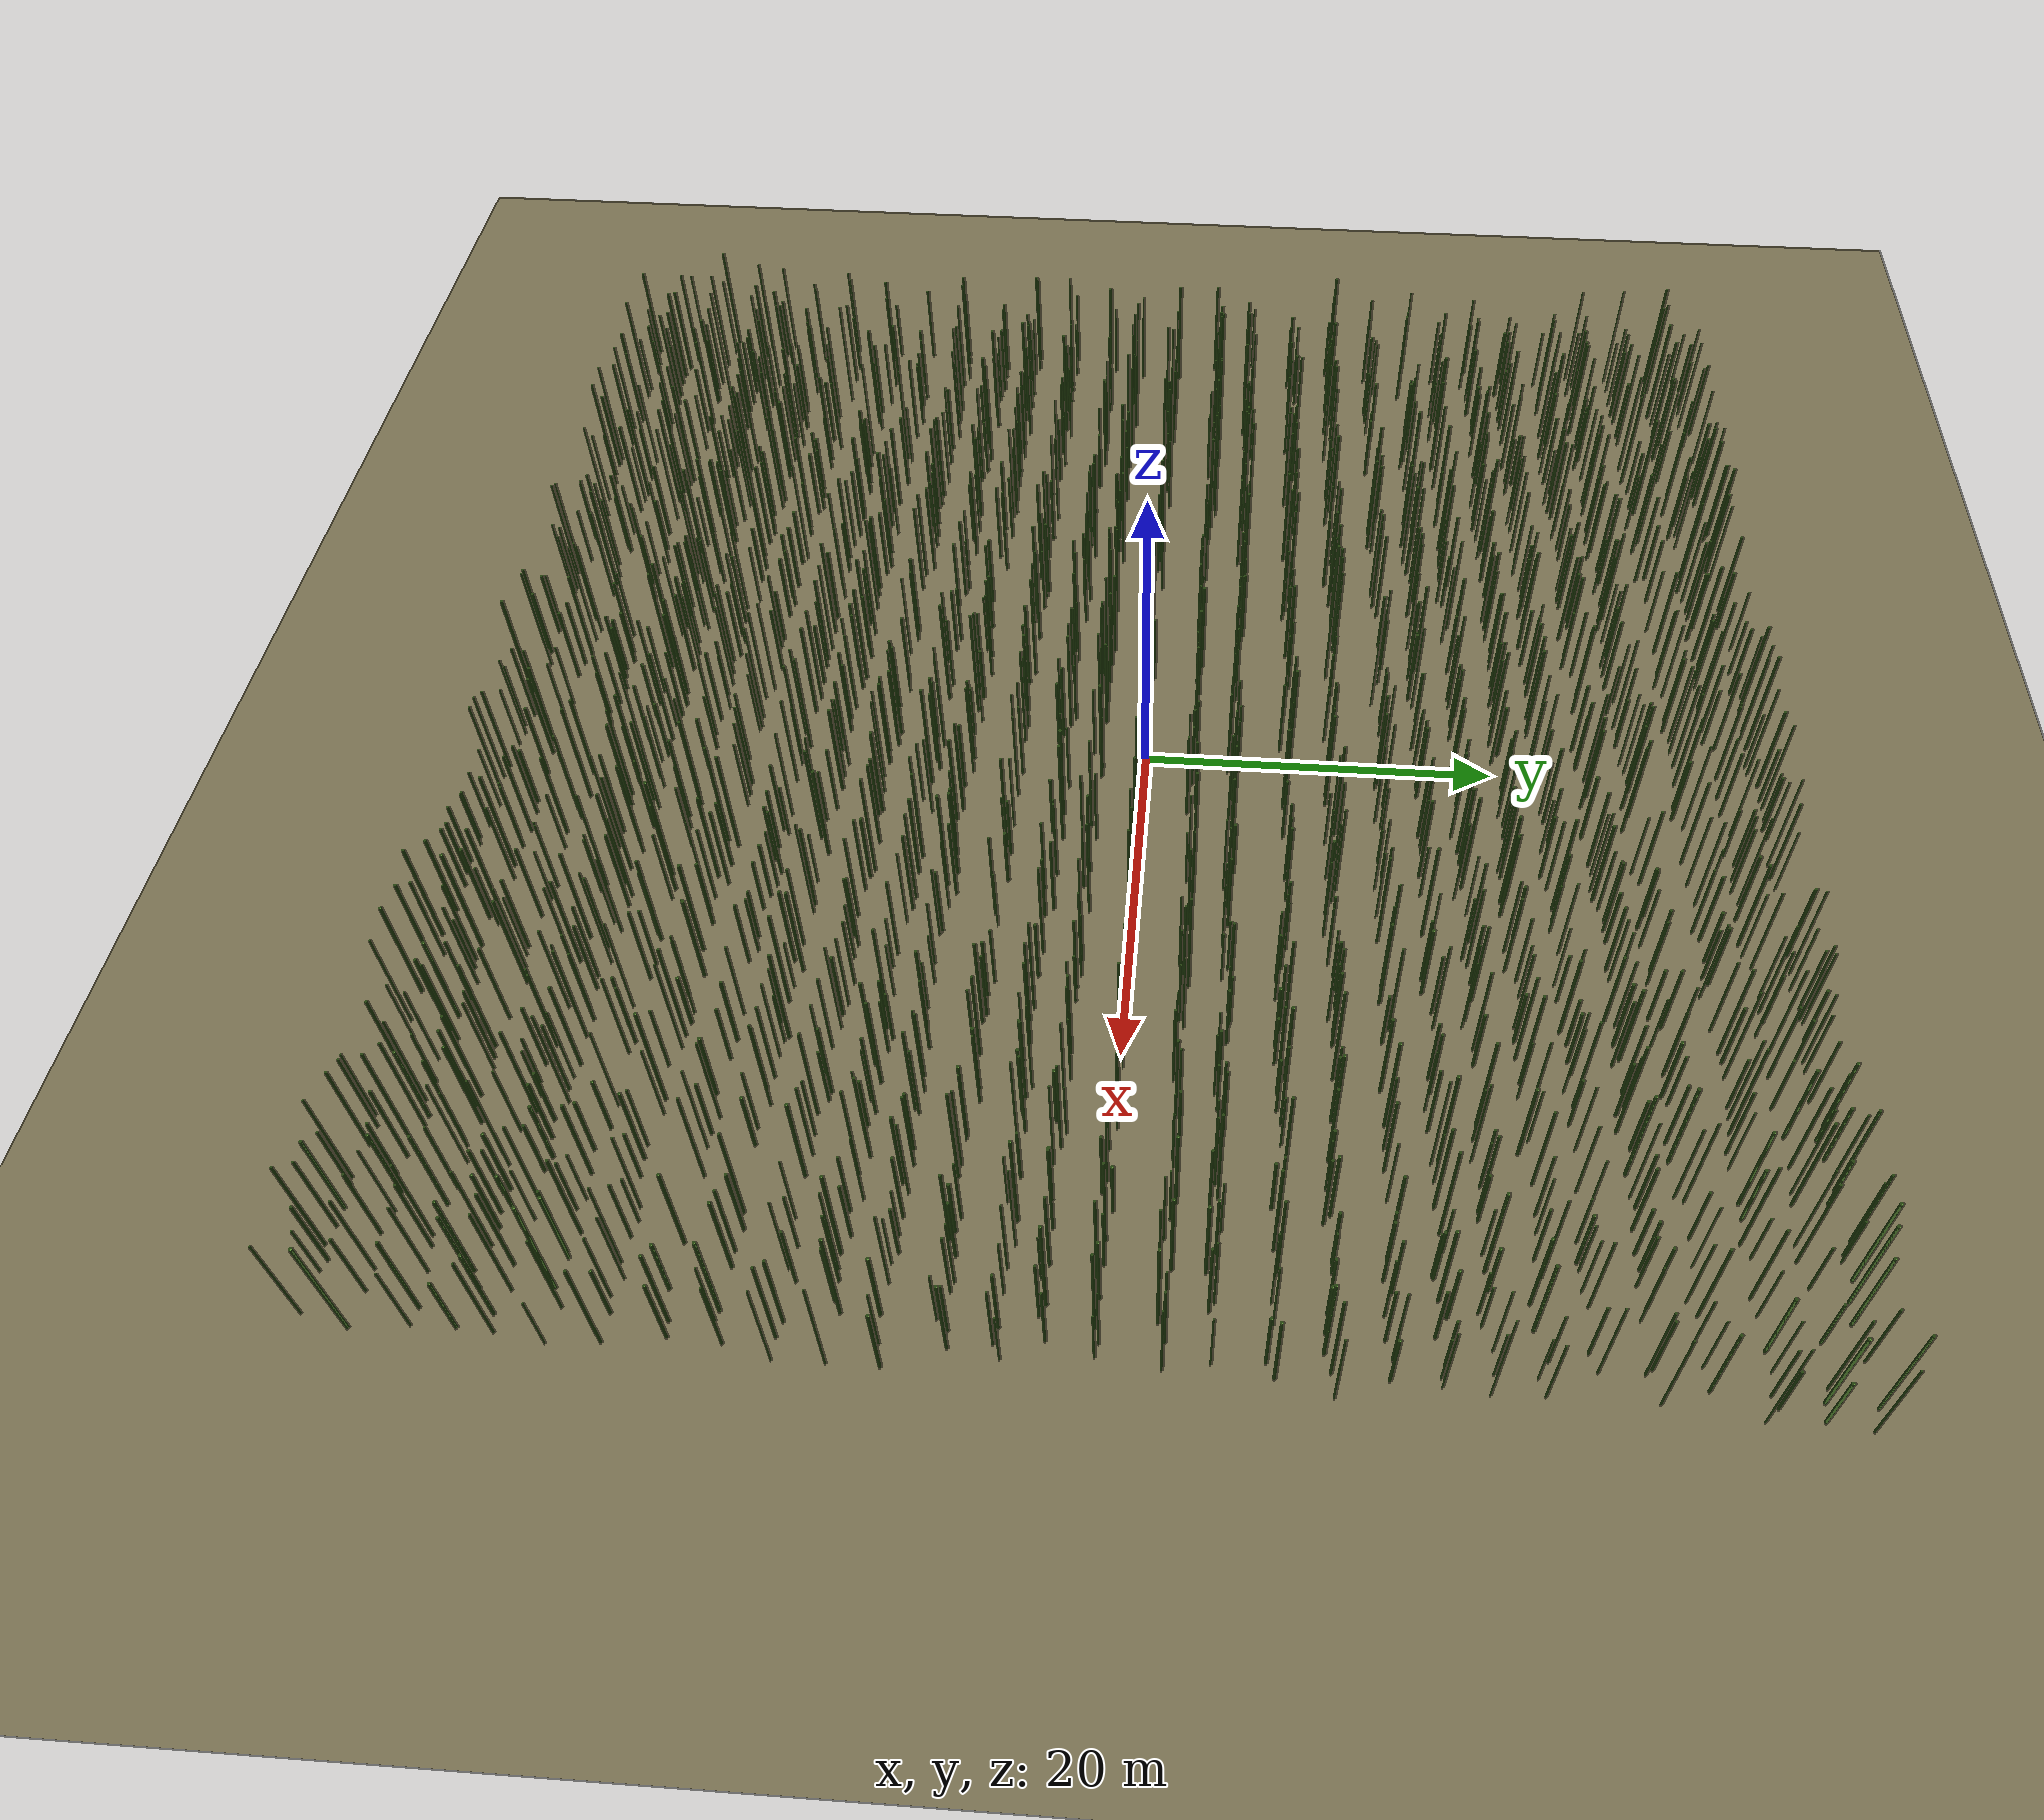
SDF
<?xml version="1.0" ?>
<sdf version="1.9">
  <world name="bamboo_field">
    <physics name="default" type="ode">
      <max_step_size>0.004</max_step_size>
      <real_time_factor>1.0</real_time_factor>
    </physics>

    <plugin filename="gz-sim-physics-system" name="gz::sim::systems::Physics"/>
    <plugin filename="gz-sim-user-commands-system" name="gz::sim::systems::UserCommands"/>
    <plugin filename="gz-sim-scene-broadcaster-system" name="gz::sim::systems::SceneBroadcaster"/>

    <light type="directional" name="sun">
      <cast_shadows>true</cast_shadows>
      <pose>0 0 20 0 0.6 0.8</pose>
      <diffuse>0.95 0.95 0.88 1</diffuse>
      <specular>0.3 0.3 0.3 1</specular>
      <direction>-0.5 0.2 -0.9</direction>
    </light>

    <model name="ground_plane">
      <static>true</static>
      <link name="link">
        <collision name="collision">
          <geometry>
            <plane>
              <normal>0 0 1</normal>
              <size>80.0 80.0</size>
            </plane>
          </geometry>
        </collision>
        <visual name="visual">
          <geometry>
            <plane>
              <normal>0 0 1</normal>
              <size>80.0 80.0</size>
            </plane>
          </geometry>
          <material>
            <diffuse>0.45 0.42 0.30 1</diffuse>
          </material>
        </visual>
      </link>
    </model>

    <model name="bamboo_0">
      <static>true</static>
      <pose>-35.91546257525896 -37.1776013783931 3.3533989748458226 0 0 0</pose>
      <link name="link">
        <collision name="collision">
          <geometry>
            <cylinder>
              <radius>0.07682356070820062</radius>
              <length>6.706797949691645</length>
            </cylinder>
          </geometry>
        </collision>
        <visual name="visual">
          <geometry>
            <cylinder>
              <radius>0.07682356070820062</radius>
              <length>6.706797949691645</length>
            </cylinder>
          </geometry>
          <material>
            <diffuse>0.35 0.55 0.20 1</diffuse>
            <specular>0.1 0.1 0.1 1</specular>
          </material>
        </visual>
      </link>
    </model>

    <model name="bamboo_1">
      <static>true</static>
      <pose>-34.42884524841114 -36.85699952481144 2.397675301373297 0 0 0</pose>
      <link name="link">
        <collision name="collision">
          <geometry>
            <cylinder>
              <radius>0.04132679848419318</radius>
              <length>4.795350602746594</length>
            </cylinder>
          </geometry>
        </collision>
        <visual name="visual">
          <geometry>
            <cylinder>
              <radius>0.04132679848419318</radius>
              <length>4.795350602746594</length>
            </cylinder>
          </geometry>
          <material>
            <diffuse>0.35 0.55 0.20 1</diffuse>
            <specular>0.1 0.1 0.1 1</specular>
          </material>
        </visual>
      </link>
    </model>

    <model name="bamboo_2">
      <static>true</static>
      <pose>-33.53151462975757 -36.74976098474193 2.012997519356122 0 0 0</pose>
      <link name="link">
        <collision name="collision">
          <geometry>
            <cylinder>
              <radius>0.08047152283389133</radius>
              <length>4.025995038712244</length>
            </cylinder>
          </geometry>
        </collision>
        <visual name="visual">
          <geometry>
            <cylinder>
              <radius>0.08047152283389133</radius>
              <length>4.025995038712244</length>
            </cylinder>
          </geometry>
          <material>
            <diffuse>0.35 0.55 0.20 1</diffuse>
            <specular>0.1 0.1 0.1 1</specular>
          </material>
        </visual>
      </link>
    </model>

    <model name="bamboo_3">
      <static>true</static>
      <pose>-31.583356614107394 -36.815850339276864 2.193432753666928 0 0 0</pose>
      <link name="link">
        <collision name="collision">
          <geometry>
            <cylinder>
              <radius>0.04463729216900739</radius>
              <length>4.386865507333856</length>
            </cylinder>
          </geometry>
        </collision>
        <visual name="visual">
          <geometry>
            <cylinder>
              <radius>0.04463729216900739</radius>
              <length>4.386865507333856</length>
            </cylinder>
          </geometry>
          <material>
            <diffuse>0.35 0.55 0.20 1</diffuse>
            <specular>0.1 0.1 0.1 1</specular>
          </material>
        </visual>
      </link>
    </model>

    <model name="bamboo_4">
      <static>true</static>
      <pose>-30.888777297195016 -36.85203011934243 3.946231527958741 0 0 0</pose>
      <link name="link">
        <collision name="collision">
          <geometry>
            <cylinder>
              <radius>0.06681140457273503</radius>
              <length>7.892463055917482</length>
            </cylinder>
          </geometry>
        </collision>
        <visual name="visual">
          <geometry>
            <cylinder>
              <radius>0.06681140457273503</radius>
              <length>7.892463055917482</length>
            </cylinder>
          </geometry>
          <material>
            <diffuse>0.35 0.55 0.20 1</diffuse>
            <specular>0.1 0.1 0.1 1</specular>
          </material>
        </visual>
      </link>
    </model>

    <model name="bamboo_5">
      <static>true</static>
      <pose>-29.62878921018922 -37.20638149267473 3.154704290513524 0 0 0</pose>
      <link name="link">
        <collision name="collision">
          <geometry>
            <cylinder>
              <radius>0.08308534501553885</radius>
              <length>6.309408581027048</length>
            </cylinder>
          </geometry>
        </collision>
        <visual name="visual">
          <geometry>
            <cylinder>
              <radius>0.08308534501553885</radius>
              <length>6.309408581027048</length>
            </cylinder>
          </geometry>
          <material>
            <diffuse>0.35 0.55 0.20 1</diffuse>
            <specular>0.1 0.1 0.1 1</specular>
          </material>
        </visual>
      </link>
    </model>

    <model name="bamboo_6">
      <static>true</static>
      <pose>-29.260129184692236 -37.043877039056625 2.4655817727220604 0 0 0</pose>
      <link name="link">
        <collision name="collision">
          <geometry>
            <cylinder>
              <radius>0.04398959884618137</radius>
              <length>4.931163545444121</length>
            </cylinder>
          </geometry>
        </collision>
        <visual name="visual">
          <geometry>
            <cylinder>
              <radius>0.04398959884618137</radius>
              <length>4.931163545444121</length>
            </cylinder>
          </geometry>
          <material>
            <diffuse>0.35 0.55 0.20 1</diffuse>
            <specular>0.1 0.1 0.1 1</specular>
          </material>
        </visual>
      </link>
    </model>

    <model name="bamboo_7">
      <static>true</static>
      <pose>-28.189671932138907 -36.58280034983495 2.4190140615429754 0 0 0</pose>
      <link name="link">
        <collision name="collision">
          <geometry>
            <cylinder>
              <radius>0.05850904835584413</radius>
              <length>4.838028123085951</length>
            </cylinder>
          </geometry>
        </collision>
        <visual name="visual">
          <geometry>
            <cylinder>
              <radius>0.05850904835584413</radius>
              <length>4.838028123085951</length>
            </cylinder>
          </geometry>
          <material>
            <diffuse>0.35 0.55 0.20 1</diffuse>
            <specular>0.1 0.1 0.1 1</specular>
          </material>
        </visual>
      </link>
    </model>

    <model name="bamboo_8">
      <static>true</static>
      <pose>-27.302960507841295 -36.97283975200334 3.4582535959006986 0 0 0</pose>
      <link name="link">
        <collision name="collision">
          <geometry>
            <cylinder>
              <radius>0.04855693240990485</radius>
              <length>6.916507191801397</length>
            </cylinder>
          </geometry>
        </collision>
        <visual name="visual">
          <geometry>
            <cylinder>
              <radius>0.04855693240990485</radius>
              <length>6.916507191801397</length>
            </cylinder>
          </geometry>
          <material>
            <diffuse>0.35 0.55 0.20 1</diffuse>
            <specular>0.1 0.1 0.1 1</specular>
          </material>
        </visual>
      </link>
    </model>

    <model name="bamboo_9">
      <static>true</static>
      <pose>-25.73153656908714 -36.69525862315132 3.369228501979749 0 0 0</pose>
      <link name="link">
        <collision name="collision">
          <geometry>
            <cylinder>
              <radius>0.0678474871887323</radius>
              <length>6.738457003959498</length>
            </cylinder>
          </geometry>
        </collision>
        <visual name="visual">
          <geometry>
            <cylinder>
              <radius>0.0678474871887323</radius>
              <length>6.738457003959498</length>
            </cylinder>
          </geometry>
          <material>
            <diffuse>0.35 0.55 0.20 1</diffuse>
            <specular>0.1 0.1 0.1 1</specular>
          </material>
        </visual>
      </link>
    </model>

    <model name="bamboo_10">
      <static>true</static>
      <pose>-24.090275126679863 -37.018184044674754 3.885819428670109 0 0 0</pose>
      <link name="link">
        <collision name="collision">
          <geometry>
            <cylinder>
              <radius>0.050549142179316324</radius>
              <length>7.771638857340218</length>
            </cylinder>
          </geometry>
        </collision>
        <visual name="visual">
          <geometry>
            <cylinder>
              <radius>0.050549142179316324</radius>
              <length>7.771638857340218</length>
            </cylinder>
          </geometry>
          <material>
            <diffuse>0.35 0.55 0.20 1</diffuse>
            <specular>0.1 0.1 0.1 1</specular>
          </material>
        </visual>
      </link>
    </model>

    <model name="bamboo_11">
      <static>true</static>
      <pose>-23.556140882544145 -37.0658193058479 2.9177037051747976 0 0 0</pose>
      <link name="link">
        <collision name="collision">
          <geometry>
            <cylinder>
              <radius>0.08572737948702717</radius>
              <length>5.835407410349595</length>
            </cylinder>
          </geometry>
        </collision>
        <visual name="visual">
          <geometry>
            <cylinder>
              <radius>0.08572737948702717</radius>
              <length>5.835407410349595</length>
            </cylinder>
          </geometry>
          <material>
            <diffuse>0.35 0.55 0.20 1</diffuse>
            <specular>0.1 0.1 0.1 1</specular>
          </material>
        </visual>
      </link>
    </model>

    <model name="bamboo_12">
      <static>true</static>
      <pose>-22.537429391829242 -37.08493402982359 3.795645767204954 0 0 0</pose>
      <link name="link">
        <collision name="collision">
          <geometry>
            <cylinder>
              <radius>0.06922929951117703</radius>
              <length>7.591291534409908</length>
            </cylinder>
          </geometry>
        </collision>
        <visual name="visual">
          <geometry>
            <cylinder>
              <radius>0.06922929951117703</radius>
              <length>7.591291534409908</length>
            </cylinder>
          </geometry>
          <material>
            <diffuse>0.35 0.55 0.20 1</diffuse>
            <specular>0.1 0.1 0.1 1</specular>
          </material>
        </visual>
      </link>
    </model>

    <model name="bamboo_13">
      <static>true</static>
      <pose>-21.641240311584017 -36.79924633204153 2.094232750849469 0 0 0</pose>
      <link name="link">
        <collision name="collision">
          <geometry>
            <cylinder>
              <radius>0.04454547060868969</radius>
              <length>4.188465501698938</length>
            </cylinder>
          </geometry>
        </collision>
        <visual name="visual">
          <geometry>
            <cylinder>
              <radius>0.04454547060868969</radius>
              <length>4.188465501698938</length>
            </cylinder>
          </geometry>
          <material>
            <diffuse>0.35 0.55 0.20 1</diffuse>
            <specular>0.1 0.1 0.1 1</specular>
          </material>
        </visual>
      </link>
    </model>

    <model name="bamboo_14">
      <static>true</static>
      <pose>-20.003877990916223 -36.868078519664294 2.7632385730130737 0 0 0</pose>
      <link name="link">
        <collision name="collision">
          <geometry>
            <cylinder>
              <radius>0.043176385307597855</radius>
              <length>5.5264771460261475</length>
            </cylinder>
          </geometry>
        </collision>
        <visual name="visual">
          <geometry>
            <cylinder>
              <radius>0.043176385307597855</radius>
              <length>5.5264771460261475</length>
            </cylinder>
          </geometry>
          <material>
            <diffuse>0.35 0.55 0.20 1</diffuse>
            <specular>0.1 0.1 0.1 1</specular>
          </material>
        </visual>
      </link>
    </model>

    <model name="bamboo_15">
      <static>true</static>
      <pose>-19.13553434772024 -36.862579329947536 3.441443638720389 0 0 0</pose>
      <link name="link">
        <collision name="collision">
          <geometry>
            <cylinder>
              <radius>0.04057405109714098</radius>
              <length>6.882887277440778</length>
            </cylinder>
          </geometry>
        </collision>
        <visual name="visual">
          <geometry>
            <cylinder>
              <radius>0.04057405109714098</radius>
              <length>6.882887277440778</length>
            </cylinder>
          </geometry>
          <material>
            <diffuse>0.35 0.55 0.20 1</diffuse>
            <specular>0.1 0.1 0.1 1</specular>
          </material>
        </visual>
      </link>
    </model>

    <model name="bamboo_16">
      <static>true</static>
      <pose>-18.48839493562738 -36.57078741196894 2.86953050133821 0 0 0</pose>
      <link name="link">
        <collision name="collision">
          <geometry>
            <cylinder>
              <radius>0.045577608679793824</radius>
              <length>5.73906100267642</length>
            </cylinder>
          </geometry>
        </collision>
        <visual name="visual">
          <geometry>
            <cylinder>
              <radius>0.045577608679793824</radius>
              <length>5.73906100267642</length>
            </cylinder>
          </geometry>
          <material>
            <diffuse>0.35 0.55 0.20 1</diffuse>
            <specular>0.1 0.1 0.1 1</specular>
          </material>
        </visual>
      </link>
    </model>

    <model name="bamboo_17">
      <static>true</static>
      <pose>-17.116820866365174 -36.629095562347956 2.3573037610602627 0 0 0</pose>
      <link name="link">
        <collision name="collision">
          <geometry>
            <cylinder>
              <radius>0.06502930565251491</radius>
              <length>4.7146075221205255</length>
            </cylinder>
          </geometry>
        </collision>
        <visual name="visual">
          <geometry>
            <cylinder>
              <radius>0.06502930565251491</radius>
              <length>4.7146075221205255</length>
            </cylinder>
          </geometry>
          <material>
            <diffuse>0.35 0.55 0.20 1</diffuse>
            <specular>0.1 0.1 0.1 1</specular>
          </material>
        </visual>
      </link>
    </model>

    <model name="bamboo_18">
      <static>true</static>
      <pose>-16.40252487727449 -36.860893240149956 2.3056785370992694 0 0 0</pose>
      <link name="link">
        <collision name="collision">
          <geometry>
            <cylinder>
              <radius>0.07044851057190861</radius>
              <length>4.611357074198539</length>
            </cylinder>
          </geometry>
        </collision>
        <visual name="visual">
          <geometry>
            <cylinder>
              <radius>0.07044851057190861</radius>
              <length>4.611357074198539</length>
            </cylinder>
          </geometry>
          <material>
            <diffuse>0.35 0.55 0.20 1</diffuse>
            <specular>0.1 0.1 0.1 1</specular>
          </material>
        </visual>
      </link>
    </model>

    <model name="bamboo_19">
      <static>true</static>
      <pose>-15.91119812620479 -36.58808952984846 2.648312114009346 0 0 0</pose>
      <link name="link">
        <collision name="collision">
          <geometry>
            <cylinder>
              <radius>0.04002859480639718</radius>
              <length>5.296624228018692</length>
            </cylinder>
          </geometry>
        </collision>
        <visual name="visual">
          <geometry>
            <cylinder>
              <radius>0.04002859480639718</radius>
              <length>5.296624228018692</length>
            </cylinder>
          </geometry>
          <material>
            <diffuse>0.35 0.55 0.20 1</diffuse>
            <specular>0.1 0.1 0.1 1</specular>
          </material>
        </visual>
      </link>
    </model>

    <model name="bamboo_20">
      <static>true</static>
      <pose>-14.258736375302771 -36.57559394952509 2.115850332988375 0 0 0</pose>
      <link name="link">
        <collision name="collision">
          <geometry>
            <cylinder>
              <radius>0.05537570627013307</radius>
              <length>4.23170066597675</length>
            </cylinder>
          </geometry>
        </collision>
        <visual name="visual">
          <geometry>
            <cylinder>
              <radius>0.05537570627013307</radius>
              <length>4.23170066597675</length>
            </cylinder>
          </geometry>
          <material>
            <diffuse>0.35 0.55 0.20 1</diffuse>
            <specular>0.1 0.1 0.1 1</specular>
          </material>
        </visual>
      </link>
    </model>

    <model name="bamboo_21">
      <static>true</static>
      <pose>-13.602997613403556 -37.14858453608386 3.521204330514463 0 0 0</pose>
      <link name="link">
        <collision name="collision">
          <geometry>
            <cylinder>
              <radius>0.043460625923419184</radius>
              <length>7.042408661028926</length>
            </cylinder>
          </geometry>
        </collision>
        <visual name="visual">
          <geometry>
            <cylinder>
              <radius>0.043460625923419184</radius>
              <length>7.042408661028926</length>
            </cylinder>
          </geometry>
          <material>
            <diffuse>0.35 0.55 0.20 1</diffuse>
            <specular>0.1 0.1 0.1 1</specular>
          </material>
        </visual>
      </link>
    </model>

    <model name="bamboo_22">
      <static>true</static>
      <pose>-12.952772204538334 -37.090199817424235 3.744866082170515 0 0 0</pose>
      <link name="link">
        <collision name="collision">
          <geometry>
            <cylinder>
              <radius>0.053252831447002956</radius>
              <length>7.48973216434103</length>
            </cylinder>
          </geometry>
        </collision>
        <visual name="visual">
          <geometry>
            <cylinder>
              <radius>0.053252831447002956</radius>
              <length>7.48973216434103</length>
            </cylinder>
          </geometry>
          <material>
            <diffuse>0.35 0.55 0.20 1</diffuse>
            <specular>0.1 0.1 0.1 1</specular>
          </material>
        </visual>
      </link>
    </model>

    <model name="bamboo_23">
      <static>true</static>
      <pose>-11.636645777504546 -36.783543920886075 2.62343258260179 0 0 0</pose>
      <link name="link">
        <collision name="collision">
          <geometry>
            <cylinder>
              <radius>0.05005755316948479</radius>
              <length>5.24686516520358</length>
            </cylinder>
          </geometry>
        </collision>
        <visual name="visual">
          <geometry>
            <cylinder>
              <radius>0.05005755316948479</radius>
              <length>5.24686516520358</length>
            </cylinder>
          </geometry>
          <material>
            <diffuse>0.35 0.55 0.20 1</diffuse>
            <specular>0.1 0.1 0.1 1</specular>
          </material>
        </visual>
      </link>
    </model>

    <model name="bamboo_24">
      <static>true</static>
      <pose>-11.221350400098151 -36.82664245831363 2.4493946740631145 0 0 0</pose>
      <link name="link">
        <collision name="collision">
          <geometry>
            <cylinder>
              <radius>0.04605020979341329</radius>
              <length>4.898789348126229</length>
            </cylinder>
          </geometry>
        </collision>
        <visual name="visual">
          <geometry>
            <cylinder>
              <radius>0.04605020979341329</radius>
              <length>4.898789348126229</length>
            </cylinder>
          </geometry>
          <material>
            <diffuse>0.35 0.55 0.20 1</diffuse>
            <specular>0.1 0.1 0.1 1</specular>
          </material>
        </visual>
      </link>
    </model>

    <model name="bamboo_25">
      <static>true</static>
      <pose>-10.50570515189493 -36.6046645521294 3.262205914540198 0 0 0</pose>
      <link name="link">
        <collision name="collision">
          <geometry>
            <cylinder>
              <radius>0.04354965430045163</radius>
              <length>6.524411829080396</length>
            </cylinder>
          </geometry>
        </collision>
        <visual name="visual">
          <geometry>
            <cylinder>
              <radius>0.04354965430045163</radius>
              <length>6.524411829080396</length>
            </cylinder>
          </geometry>
          <material>
            <diffuse>0.35 0.55 0.20 1</diffuse>
            <specular>0.1 0.1 0.1 1</specular>
          </material>
        </visual>
      </link>
    </model>

    <model name="bamboo_26">
      <static>true</static>
      <pose>-8.172048418307172 -36.83872839590599 2.26462369745005 0 0 0</pose>
      <link name="link">
        <collision name="collision">
          <geometry>
            <cylinder>
              <radius>0.05071184036852193</radius>
              <length>4.5292473949001</length>
            </cylinder>
          </geometry>
        </collision>
        <visual name="visual">
          <geometry>
            <cylinder>
              <radius>0.05071184036852193</radius>
              <length>4.5292473949001</length>
            </cylinder>
          </geometry>
          <material>
            <diffuse>0.35 0.55 0.20 1</diffuse>
            <specular>0.1 0.1 0.1 1</specular>
          </material>
        </visual>
      </link>
    </model>

    <model name="bamboo_27">
      <static>true</static>
      <pose>-7.869988406228748 -36.936722733549225 2.380819828723755 0 0 0</pose>
      <link name="link">
        <collision name="collision">
          <geometry>
            <cylinder>
              <radius>0.08037484988833217</radius>
              <length>4.76163965744751</length>
            </cylinder>
          </geometry>
        </collision>
        <visual name="visual">
          <geometry>
            <cylinder>
              <radius>0.08037484988833217</radius>
              <length>4.76163965744751</length>
            </cylinder>
          </geometry>
          <material>
            <diffuse>0.35 0.55 0.20 1</diffuse>
            <specular>0.1 0.1 0.1 1</specular>
          </material>
        </visual>
      </link>
    </model>

    <model name="bamboo_28">
      <static>true</static>
      <pose>-6.37949287902478 -37.16956605142732 3.3467290945866033 0 0 0</pose>
      <link name="link">
        <collision name="collision">
          <geometry>
            <cylinder>
              <radius>0.07645379247299253</radius>
              <length>6.693458189173207</length>
            </cylinder>
          </geometry>
        </collision>
        <visual name="visual">
          <geometry>
            <cylinder>
              <radius>0.07645379247299253</radius>
              <length>6.693458189173207</length>
            </cylinder>
          </geometry>
          <material>
            <diffuse>0.35 0.55 0.20 1</diffuse>
            <specular>0.1 0.1 0.1 1</specular>
          </material>
        </visual>
      </link>
    </model>

    <model name="bamboo_29">
      <static>true</static>
      <pose>-6.0742137782314805 -36.924429077750496 2.4973126678405713 0 0 0</pose>
      <link name="link">
        <collision name="collision">
          <geometry>
            <cylinder>
              <radius>0.08308362681763955</radius>
              <length>4.9946253356811425</length>
            </cylinder>
          </geometry>
        </collision>
        <visual name="visual">
          <geometry>
            <cylinder>
              <radius>0.08308362681763955</radius>
              <length>4.9946253356811425</length>
            </cylinder>
          </geometry>
          <material>
            <diffuse>0.35 0.55 0.20 1</diffuse>
            <specular>0.1 0.1 0.1 1</specular>
          </material>
        </visual>
      </link>
    </model>

    <model name="bamboo_30">
      <static>true</static>
      <pose>-5.0284158366688665 -36.63551418790041 3.8465311985520256 0 0 0</pose>
      <link name="link">
        <collision name="collision">
          <geometry>
            <cylinder>
              <radius>0.052490322394105025</radius>
              <length>7.693062397104051</length>
            </cylinder>
          </geometry>
        </collision>
        <visual name="visual">
          <geometry>
            <cylinder>
              <radius>0.052490322394105025</radius>
              <length>7.693062397104051</length>
            </cylinder>
          </geometry>
          <material>
            <diffuse>0.35 0.55 0.20 1</diffuse>
            <specular>0.1 0.1 0.1 1</specular>
          </material>
        </visual>
      </link>
    </model>

    <model name="bamboo_31">
      <static>true</static>
      <pose>-2.724677231771242 -37.12204078381095 3.852733966016255 0 0 0</pose>
      <link name="link">
        <collision name="collision">
          <geometry>
            <cylinder>
              <radius>0.08844981286423756</radius>
              <length>7.70546793203251</length>
            </cylinder>
          </geometry>
        </collision>
        <visual name="visual">
          <geometry>
            <cylinder>
              <radius>0.08844981286423756</radius>
              <length>7.70546793203251</length>
            </cylinder>
          </geometry>
          <material>
            <diffuse>0.35 0.55 0.20 1</diffuse>
            <specular>0.1 0.1 0.1 1</specular>
          </material>
        </visual>
      </link>
    </model>

    <model name="bamboo_32">
      <static>true</static>
      <pose>-2.1592266123971275 -36.54874237058788 2.117270799944358 0 0 0</pose>
      <link name="link">
        <collision name="collision">
          <geometry>
            <cylinder>
              <radius>0.06005201462747263</radius>
              <length>4.234541599888716</length>
            </cylinder>
          </geometry>
        </collision>
        <visual name="visual">
          <geometry>
            <cylinder>
              <radius>0.06005201462747263</radius>
              <length>4.234541599888716</length>
            </cylinder>
          </geometry>
          <material>
            <diffuse>0.35 0.55 0.20 1</diffuse>
            <specular>0.1 0.1 0.1 1</specular>
          </material>
        </visual>
      </link>
    </model>

    <model name="bamboo_33">
      <static>true</static>
      <pose>-0.9483042238103367 -36.54166267858879 2.846014971980326 0 0 0</pose>
      <link name="link">
        <collision name="collision">
          <geometry>
            <cylinder>
              <radius>0.06275041836695716</radius>
              <length>5.692029943960652</length>
            </cylinder>
          </geometry>
        </collision>
        <visual name="visual">
          <geometry>
            <cylinder>
              <radius>0.06275041836695716</radius>
              <length>5.692029943960652</length>
            </cylinder>
          </geometry>
          <material>
            <diffuse>0.35 0.55 0.20 1</diffuse>
            <specular>0.1 0.1 0.1 1</specular>
          </material>
        </visual>
      </link>
    </model>

    <model name="bamboo_34">
      <static>true</static>
      <pose>-0.018022687571449536 -36.83303235766231 2.5934156509891286 0 0 0</pose>
      <link name="link">
        <collision name="collision">
          <geometry>
            <cylinder>
              <radius>0.0477398412637032</radius>
              <length>5.186831301978257</length>
            </cylinder>
          </geometry>
        </collision>
        <visual name="visual">
          <geometry>
            <cylinder>
              <radius>0.0477398412637032</radius>
              <length>5.186831301978257</length>
            </cylinder>
          </geometry>
          <material>
            <diffuse>0.35 0.55 0.20 1</diffuse>
            <specular>0.1 0.1 0.1 1</specular>
          </material>
        </visual>
      </link>
    </model>

    <model name="bamboo_35">
      <static>true</static>
      <pose>0.5727541055435084 -36.64155463679989 3.1683551889179427 0 0 0</pose>
      <link name="link">
        <collision name="collision">
          <geometry>
            <cylinder>
              <radius>0.04285826364537416</radius>
              <length>6.336710377835885</length>
            </cylinder>
          </geometry>
        </collision>
        <visual name="visual">
          <geometry>
            <cylinder>
              <radius>0.04285826364537416</radius>
              <length>6.336710377835885</length>
            </cylinder>
          </geometry>
          <material>
            <diffuse>0.35 0.55 0.20 1</diffuse>
            <specular>0.1 0.1 0.1 1</specular>
          </material>
        </visual>
      </link>
    </model>

    <model name="bamboo_36">
      <static>true</static>
      <pose>1.4002565031906615 -36.76580977371083 2.3716499219614464 0 0 0</pose>
      <link name="link">
        <collision name="collision">
          <geometry>
            <cylinder>
              <radius>0.04400557326202934</radius>
              <length>4.743299843922893</length>
            </cylinder>
          </geometry>
        </collision>
        <visual name="visual">
          <geometry>
            <cylinder>
              <radius>0.04400557326202934</radius>
              <length>4.743299843922893</length>
            </cylinder>
          </geometry>
          <material>
            <diffuse>0.35 0.55 0.20 1</diffuse>
            <specular>0.1 0.1 0.1 1</specular>
          </material>
        </visual>
      </link>
    </model>

    <model name="bamboo_37">
      <static>true</static>
      <pose>3.1273858530629 -36.829887958729834 3.238763020664206 0 0 0</pose>
      <link name="link">
        <collision name="collision">
          <geometry>
            <cylinder>
              <radius>0.06972595767667206</radius>
              <length>6.477526041328412</length>
            </cylinder>
          </geometry>
        </collision>
        <visual name="visual">
          <geometry>
            <cylinder>
              <radius>0.06972595767667206</radius>
              <length>6.477526041328412</length>
            </cylinder>
          </geometry>
          <material>
            <diffuse>0.35 0.55 0.20 1</diffuse>
            <specular>0.1 0.1 0.1 1</specular>
          </material>
        </visual>
      </link>
    </model>

    <model name="bamboo_38">
      <static>true</static>
      <pose>3.910121665371666 -36.96140846847981 3.4323836015788296 0 0 0</pose>
      <link name="link">
        <collision name="collision">
          <geometry>
            <cylinder>
              <radius>0.05021295997117682</radius>
              <length>6.864767203157659</length>
            </cylinder>
          </geometry>
        </collision>
        <visual name="visual">
          <geometry>
            <cylinder>
              <radius>0.05021295997117682</radius>
              <length>6.864767203157659</length>
            </cylinder>
          </geometry>
          <material>
            <diffuse>0.35 0.55 0.20 1</diffuse>
            <specular>0.1 0.1 0.1 1</specular>
          </material>
        </visual>
      </link>
    </model>

    <model name="bamboo_39">
      <static>true</static>
      <pose>4.762497767869772 -36.91765869540068 3.503728984828804 0 0 0</pose>
      <link name="link">
        <collision name="collision">
          <geometry>
            <cylinder>
              <radius>0.0558088598135927</radius>
              <length>7.007457969657608</length>
            </cylinder>
          </geometry>
        </collision>
        <visual name="visual">
          <geometry>
            <cylinder>
              <radius>0.0558088598135927</radius>
              <length>7.007457969657608</length>
            </cylinder>
          </geometry>
          <material>
            <diffuse>0.35 0.55 0.20 1</diffuse>
            <specular>0.1 0.1 0.1 1</specular>
          </material>
        </visual>
      </link>
    </model>

    <model name="bamboo_40">
      <static>true</static>
      <pose>5.99673965439162 -36.5851769966381 2.426308624534081 0 0 0</pose>
      <link name="link">
        <collision name="collision">
          <geometry>
            <cylinder>
              <radius>0.04366303605498165</radius>
              <length>4.852617249068162</length>
            </cylinder>
          </geometry>
        </collision>
        <visual name="visual">
          <geometry>
            <cylinder>
              <radius>0.04366303605498165</radius>
              <length>4.852617249068162</length>
            </cylinder>
          </geometry>
          <material>
            <diffuse>0.35 0.55 0.20 1</diffuse>
            <specular>0.1 0.1 0.1 1</specular>
          </material>
        </visual>
      </link>
    </model>

    <model name="bamboo_41">
      <static>true</static>
      <pose>7.44706650178878 -36.74598061367253 2.315493664714464 0 0 0</pose>
      <link name="link">
        <collision name="collision">
          <geometry>
            <cylinder>
              <radius>0.0584763544369442</radius>
              <length>4.630987329428928</length>
            </cylinder>
          </geometry>
        </collision>
        <visual name="visual">
          <geometry>
            <cylinder>
              <radius>0.0584763544369442</radius>
              <length>4.630987329428928</length>
            </cylinder>
          </geometry>
          <material>
            <diffuse>0.35 0.55 0.20 1</diffuse>
            <specular>0.1 0.1 0.1 1</specular>
          </material>
        </visual>
      </link>
    </model>

    <model name="bamboo_42">
      <static>true</static>
      <pose>8.380089034412117 -37.02889343469371 2.015646214304316 0 0 0</pose>
      <link name="link">
        <collision name="collision">
          <geometry>
            <cylinder>
              <radius>0.07269881588553663</radius>
              <length>4.031292428608632</length>
            </cylinder>
          </geometry>
        </collision>
        <visual name="visual">
          <geometry>
            <cylinder>
              <radius>0.07269881588553663</radius>
              <length>4.031292428608632</length>
            </cylinder>
          </geometry>
          <material>
            <diffuse>0.35 0.55 0.20 1</diffuse>
            <specular>0.1 0.1 0.1 1</specular>
          </material>
        </visual>
      </link>
    </model>

    <model name="bamboo_43">
      <static>true</static>
      <pose>8.848396810214318 -36.85120201261432 2.230857340838204 0 0 0</pose>
      <link name="link">
        <collision name="collision">
          <geometry>
            <cylinder>
              <radius>0.046714555719668385</radius>
              <length>4.461714681676408</length>
            </cylinder>
          </geometry>
        </collision>
        <visual name="visual">
          <geometry>
            <cylinder>
              <radius>0.046714555719668385</radius>
              <length>4.461714681676408</length>
            </cylinder>
          </geometry>
          <material>
            <diffuse>0.35 0.55 0.20 1</diffuse>
            <specular>0.1 0.1 0.1 1</specular>
          </material>
        </visual>
      </link>
    </model>

    <model name="bamboo_44">
      <static>true</static>
      <pose>10.026377481963207 -37.0536698300924 2.407194624654906 0 0 0</pose>
      <link name="link">
        <collision name="collision">
          <geometry>
            <cylinder>
              <radius>0.0758806093569399</radius>
              <length>4.814389249309812</length>
            </cylinder>
          </geometry>
        </collision>
        <visual name="visual">
          <geometry>
            <cylinder>
              <radius>0.0758806093569399</radius>
              <length>4.814389249309812</length>
            </cylinder>
          </geometry>
          <material>
            <diffuse>0.35 0.55 0.20 1</diffuse>
            <specular>0.1 0.1 0.1 1</specular>
          </material>
        </visual>
      </link>
    </model>

    <model name="bamboo_45">
      <static>true</static>
      <pose>10.774326692398011 -37.044782404453116 2.184596935425467 0 0 0</pose>
      <link name="link">
        <collision name="collision">
          <geometry>
            <cylinder>
              <radius>0.08230518566474276</radius>
              <length>4.369193870850934</length>
            </cylinder>
          </geometry>
        </collision>
        <visual name="visual">
          <geometry>
            <cylinder>
              <radius>0.08230518566474276</radius>
              <length>4.369193870850934</length>
            </cylinder>
          </geometry>
          <material>
            <diffuse>0.35 0.55 0.20 1</diffuse>
            <specular>0.1 0.1 0.1 1</specular>
          </material>
        </visual>
      </link>
    </model>

    <model name="bamboo_46">
      <static>true</static>
      <pose>11.698103563082068 -36.852282266445215 2.5239105248686964 0 0 0</pose>
      <link name="link">
        <collision name="collision">
          <geometry>
            <cylinder>
              <radius>0.07185566886506897</radius>
              <length>5.047821049737393</length>
            </cylinder>
          </geometry>
        </collision>
        <visual name="visual">
          <geometry>
            <cylinder>
              <radius>0.07185566886506897</radius>
              <length>5.047821049737393</length>
            </cylinder>
          </geometry>
          <material>
            <diffuse>0.35 0.55 0.20 1</diffuse>
            <specular>0.1 0.1 0.1 1</specular>
          </material>
        </visual>
      </link>
    </model>

    <model name="bamboo_47">
      <static>true</static>
      <pose>13.364630752780506 -36.83070186469084 3.091180578411045 0 0 0</pose>
      <link name="link">
        <collision name="collision">
          <geometry>
            <cylinder>
              <radius>0.08519642857799466</radius>
              <length>6.18236115682209</length>
            </cylinder>
          </geometry>
        </collision>
        <visual name="visual">
          <geometry>
            <cylinder>
              <radius>0.08519642857799466</radius>
              <length>6.18236115682209</length>
            </cylinder>
          </geometry>
          <material>
            <diffuse>0.35 0.55 0.20 1</diffuse>
            <specular>0.1 0.1 0.1 1</specular>
          </material>
        </visual>
      </link>
    </model>

    <model name="bamboo_48">
      <static>true</static>
      <pose>14.992202338627873 -37.091404984395865 3.7214051640018058 0 0 0</pose>
      <link name="link">
        <collision name="collision">
          <geometry>
            <cylinder>
              <radius>0.07980611524440209</radius>
              <length>7.4428103280036115</length>
            </cylinder>
          </geometry>
        </collision>
        <visual name="visual">
          <geometry>
            <cylinder>
              <radius>0.07980611524440209</radius>
              <length>7.4428103280036115</length>
            </cylinder>
          </geometry>
          <material>
            <diffuse>0.35 0.55 0.20 1</diffuse>
            <specular>0.1 0.1 0.1 1</specular>
          </material>
        </visual>
      </link>
    </model>

    <model name="bamboo_49">
      <static>true</static>
      <pose>16.28300082232963 -36.587541850248115 3.241323020301426 0 0 0</pose>
      <link name="link">
        <collision name="collision">
          <geometry>
            <cylinder>
              <radius>0.06031886949160584</radius>
              <length>6.482646040602852</length>
            </cylinder>
          </geometry>
        </collision>
        <visual name="visual">
          <geometry>
            <cylinder>
              <radius>0.06031886949160584</radius>
              <length>6.482646040602852</length>
            </cylinder>
          </geometry>
          <material>
            <diffuse>0.35 0.55 0.20 1</diffuse>
            <specular>0.1 0.1 0.1 1</specular>
          </material>
        </visual>
      </link>
    </model>

    <model name="bamboo_50">
      <static>true</static>
      <pose>17.238006217313806 -36.72286343100513 3.7628324093266485 0 0 0</pose>
      <link name="link">
        <collision name="collision">
          <geometry>
            <cylinder>
              <radius>0.08053858599701985</radius>
              <length>7.525664818653297</length>
            </cylinder>
          </geometry>
        </collision>
        <visual name="visual">
          <geometry>
            <cylinder>
              <radius>0.08053858599701985</radius>
              <length>7.525664818653297</length>
            </cylinder>
          </geometry>
          <material>
            <diffuse>0.35 0.55 0.20 1</diffuse>
            <specular>0.1 0.1 0.1 1</specular>
          </material>
        </visual>
      </link>
    </model>

    <model name="bamboo_51">
      <static>true</static>
      <pose>18.621054472765717 -37.05169456451756 3.728128056750559 0 0 0</pose>
      <link name="link">
        <collision name="collision">
          <geometry>
            <cylinder>
              <radius>0.08011175694685695</radius>
              <length>7.456256113501118</length>
            </cylinder>
          </geometry>
        </collision>
        <visual name="visual">
          <geometry>
            <cylinder>
              <radius>0.08011175694685695</radius>
              <length>7.456256113501118</length>
            </cylinder>
          </geometry>
          <material>
            <diffuse>0.35 0.55 0.20 1</diffuse>
            <specular>0.1 0.1 0.1 1</specular>
          </material>
        </visual>
      </link>
    </model>

    <model name="bamboo_52">
      <static>true</static>
      <pose>20.43955873225553 -37.02482495409667 3.633173211193858 0 0 0</pose>
      <link name="link">
        <collision name="collision">
          <geometry>
            <cylinder>
              <radius>0.05112168587728322</radius>
              <length>7.266346422387716</length>
            </cylinder>
          </geometry>
        </collision>
        <visual name="visual">
          <geometry>
            <cylinder>
              <radius>0.05112168587728322</radius>
              <length>7.266346422387716</length>
            </cylinder>
          </geometry>
          <material>
            <diffuse>0.35 0.55 0.20 1</diffuse>
            <specular>0.1 0.1 0.1 1</specular>
          </material>
        </visual>
      </link>
    </model>

    <model name="bamboo_53">
      <static>true</static>
      <pose>21.36526803347981 -36.63341150181249 2.3862595766554175 0 0 0</pose>
      <link name="link">
        <collision name="collision">
          <geometry>
            <cylinder>
              <radius>0.04118322173507258</radius>
              <length>4.772519153310835</length>
            </cylinder>
          </geometry>
        </collision>
        <visual name="visual">
          <geometry>
            <cylinder>
              <radius>0.04118322173507258</radius>
              <length>4.772519153310835</length>
            </cylinder>
          </geometry>
          <material>
            <diffuse>0.35 0.55 0.20 1</diffuse>
            <specular>0.1 0.1 0.1 1</specular>
          </material>
        </visual>
      </link>
    </model>

    <model name="bamboo_54">
      <static>true</static>
      <pose>22.909045090299543 -36.86310754849858 2.7993567687201217 0 0 0</pose>
      <link name="link">
        <collision name="collision">
          <geometry>
            <cylinder>
              <radius>0.07207408693038139</radius>
              <length>5.5987135374402435</length>
            </cylinder>
          </geometry>
        </collision>
        <visual name="visual">
          <geometry>
            <cylinder>
              <radius>0.07207408693038139</radius>
              <length>5.5987135374402435</length>
            </cylinder>
          </geometry>
          <material>
            <diffuse>0.35 0.55 0.20 1</diffuse>
            <specular>0.1 0.1 0.1 1</specular>
          </material>
        </visual>
      </link>
    </model>

    <model name="bamboo_55">
      <static>true</static>
      <pose>25.981090678561053 -37.018884441297196 2.8691275171292885 0 0 0</pose>
      <link name="link">
        <collision name="collision">
          <geometry>
            <cylinder>
              <radius>0.04542012736073556</radius>
              <length>5.738255034258577</length>
            </cylinder>
          </geometry>
        </collision>
        <visual name="visual">
          <geometry>
            <cylinder>
              <radius>0.04542012736073556</radius>
              <length>5.738255034258577</length>
            </cylinder>
          </geometry>
          <material>
            <diffuse>0.35 0.55 0.20 1</diffuse>
            <specular>0.1 0.1 0.1 1</specular>
          </material>
        </visual>
      </link>
    </model>

    <model name="bamboo_56">
      <static>true</static>
      <pose>26.59189843172362 -36.74230886254977 3.153176086993199 0 0 0</pose>
      <link name="link">
        <collision name="collision">
          <geometry>
            <cylinder>
              <radius>0.05925977166723636</radius>
              <length>6.306352173986398</length>
            </cylinder>
          </geometry>
        </collision>
        <visual name="visual">
          <geometry>
            <cylinder>
              <radius>0.05925977166723636</radius>
              <length>6.306352173986398</length>
            </cylinder>
          </geometry>
          <material>
            <diffuse>0.35 0.55 0.20 1</diffuse>
            <specular>0.1 0.1 0.1 1</specular>
          </material>
        </visual>
      </link>
    </model>

    <model name="bamboo_57">
      <static>true</static>
      <pose>27.6336342432017 -36.769018608130594 3.438859998289691 0 0 0</pose>
      <link name="link">
        <collision name="collision">
          <geometry>
            <cylinder>
              <radius>0.0669225998546396</radius>
              <length>6.877719996579382</length>
            </cylinder>
          </geometry>
        </collision>
        <visual name="visual">
          <geometry>
            <cylinder>
              <radius>0.0669225998546396</radius>
              <length>6.877719996579382</length>
            </cylinder>
          </geometry>
          <material>
            <diffuse>0.35 0.55 0.20 1</diffuse>
            <specular>0.1 0.1 0.1 1</specular>
          </material>
        </visual>
      </link>
    </model>

    <model name="bamboo_58">
      <static>true</static>
      <pose>29.429480835500843 -37.02823297348581 3.696030559012671 0 0 0</pose>
      <link name="link">
        <collision name="collision">
          <geometry>
            <cylinder>
              <radius>0.055695782252917984</radius>
              <length>7.392061118025342</length>
            </cylinder>
          </geometry>
        </collision>
        <visual name="visual">
          <geometry>
            <cylinder>
              <radius>0.055695782252917984</radius>
              <length>7.392061118025342</length>
            </cylinder>
          </geometry>
          <material>
            <diffuse>0.35 0.55 0.20 1</diffuse>
            <specular>0.1 0.1 0.1 1</specular>
          </material>
        </visual>
      </link>
    </model>

    <model name="bamboo_59">
      <static>true</static>
      <pose>29.838468175615947 -36.94414612759265 2.5913104050518943 0 0 0</pose>
      <link name="link">
        <collision name="collision">
          <geometry>
            <cylinder>
              <radius>0.06012001935288623</radius>
              <length>5.1826208101037885</length>
            </cylinder>
          </geometry>
        </collision>
        <visual name="visual">
          <geometry>
            <cylinder>
              <radius>0.06012001935288623</radius>
              <length>5.1826208101037885</length>
            </cylinder>
          </geometry>
          <material>
            <diffuse>0.35 0.55 0.20 1</diffuse>
            <specular>0.1 0.1 0.1 1</specular>
          </material>
        </visual>
      </link>
    </model>

    <model name="bamboo_60">
      <static>true</static>
      <pose>31.03617709676251 -36.8549025120387 3.2310298319027613 0 0 0</pose>
      <link name="link">
        <collision name="collision">
          <geometry>
            <cylinder>
              <radius>0.08514027728662912</radius>
              <length>6.4620596638055225</length>
            </cylinder>
          </geometry>
        </collision>
        <visual name="visual">
          <geometry>
            <cylinder>
              <radius>0.08514027728662912</radius>
              <length>6.4620596638055225</length>
            </cylinder>
          </geometry>
          <material>
            <diffuse>0.35 0.55 0.20 1</diffuse>
            <specular>0.1 0.1 0.1 1</specular>
          </material>
        </visual>
      </link>
    </model>

    <model name="bamboo_61">
      <static>true</static>
      <pose>31.98396849703768 -36.91296682806078 3.159969562391364 0 0 0</pose>
      <link name="link">
        <collision name="collision">
          <geometry>
            <cylinder>
              <radius>0.06149440749949173</radius>
              <length>6.319939124782728</length>
            </cylinder>
          </geometry>
        </collision>
        <visual name="visual">
          <geometry>
            <cylinder>
              <radius>0.06149440749949173</radius>
              <length>6.319939124782728</length>
            </cylinder>
          </geometry>
          <material>
            <diffuse>0.35 0.55 0.20 1</diffuse>
            <specular>0.1 0.1 0.1 1</specular>
          </material>
        </visual>
      </link>
    </model>

    <model name="bamboo_62">
      <static>true</static>
      <pose>32.9597558122562 -37.119674583895055 3.8023616516565086 0 0 0</pose>
      <link name="link">
        <collision name="collision">
          <geometry>
            <cylinder>
              <radius>0.06365930929546632</radius>
              <length>7.604723303313017</length>
            </cylinder>
          </geometry>
        </collision>
        <visual name="visual">
          <geometry>
            <cylinder>
              <radius>0.06365930929546632</radius>
              <length>7.604723303313017</length>
            </cylinder>
          </geometry>
          <material>
            <diffuse>0.35 0.55 0.20 1</diffuse>
            <specular>0.1 0.1 0.1 1</specular>
          </material>
        </visual>
      </link>
    </model>

    <model name="bamboo_63">
      <static>true</static>
      <pose>33.709353120033164 -36.71266186495518 2.670376510819602 0 0 0</pose>
      <link name="link">
        <collision name="collision">
          <geometry>
            <cylinder>
              <radius>0.07164704278828979</radius>
              <length>5.340753021639204</length>
            </cylinder>
          </geometry>
        </collision>
        <visual name="visual">
          <geometry>
            <cylinder>
              <radius>0.07164704278828979</radius>
              <length>5.340753021639204</length>
            </cylinder>
          </geometry>
          <material>
            <diffuse>0.35 0.55 0.20 1</diffuse>
            <specular>0.1 0.1 0.1 1</specular>
          </material>
        </visual>
      </link>
    </model>

    <model name="bamboo_64">
      <static>true</static>
      <pose>34.27696474393521 -36.90586312028053 2.0488507754536527 0 0 0</pose>
      <link name="link">
        <collision name="collision">
          <geometry>
            <cylinder>
              <radius>0.04995649663632883</radius>
              <length>4.097701550907305</length>
            </cylinder>
          </geometry>
        </collision>
        <visual name="visual">
          <geometry>
            <cylinder>
              <radius>0.04995649663632883</radius>
              <length>4.097701550907305</length>
            </cylinder>
          </geometry>
          <material>
            <diffuse>0.35 0.55 0.20 1</diffuse>
            <specular>0.1 0.1 0.1 1</specular>
          </material>
        </visual>
      </link>
    </model>

    <model name="bamboo_65">
      <static>true</static>
      <pose>36.35731046363665 -37.06766945352879 3.39270850098101 0 0 0</pose>
      <link name="link">
        <collision name="collision">
          <geometry>
            <cylinder>
              <radius>0.04972176183698546</radius>
              <length>6.78541700196202</length>
            </cylinder>
          </geometry>
        </collision>
        <visual name="visual">
          <geometry>
            <cylinder>
              <radius>0.04972176183698546</radius>
              <length>6.78541700196202</length>
            </cylinder>
          </geometry>
          <material>
            <diffuse>0.35 0.55 0.20 1</diffuse>
            <specular>0.1 0.1 0.1 1</specular>
          </material>
        </visual>
      </link>
    </model>

    <model name="bamboo_66">
      <static>true</static>
      <pose>-37.22687932280543 -34.27532529822672 2.8502923878854682 0 0 0</pose>
      <link name="link">
        <collision name="collision">
          <geometry>
            <cylinder>
              <radius>0.04532936482817695</radius>
              <length>5.7005847757709365</length>
            </cylinder>
          </geometry>
        </collision>
        <visual name="visual">
          <geometry>
            <cylinder>
              <radius>0.04532936482817695</radius>
              <length>5.7005847757709365</length>
            </cylinder>
          </geometry>
          <material>
            <diffuse>0.35 0.55 0.20 1</diffuse>
            <specular>0.1 0.1 0.1 1</specular>
          </material>
        </visual>
      </link>
    </model>

    <model name="bamboo_67">
      <static>true</static>
      <pose>-35.175833175148064 -34.254376810675886 3.602833203444529 0 0 0</pose>
      <link name="link">
        <collision name="collision">
          <geometry>
            <cylinder>
              <radius>0.06282309127350863</radius>
              <length>7.205666406889058</length>
            </cylinder>
          </geometry>
        </collision>
        <visual name="visual">
          <geometry>
            <cylinder>
              <radius>0.06282309127350863</radius>
              <length>7.205666406889058</length>
            </cylinder>
          </geometry>
          <material>
            <diffuse>0.35 0.55 0.20 1</diffuse>
            <specular>0.1 0.1 0.1 1</specular>
          </material>
        </visual>
      </link>
    </model>

    <model name="bamboo_68">
      <static>true</static>
      <pose>-34.20146488767757 -34.592556812445316 3.2253046455235257 0 0 0</pose>
      <link name="link">
        <collision name="collision">
          <geometry>
            <cylinder>
              <radius>0.08457129629052185</radius>
              <length>6.450609291047051</length>
            </cylinder>
          </geometry>
        </collision>
        <visual name="visual">
          <geometry>
            <cylinder>
              <radius>0.08457129629052185</radius>
              <length>6.450609291047051</length>
            </cylinder>
          </geometry>
          <material>
            <diffuse>0.35 0.55 0.20 1</diffuse>
            <specular>0.1 0.1 0.1 1</specular>
          </material>
        </visual>
      </link>
    </model>

    <model name="bamboo_69">
      <static>true</static>
      <pose>-33.34045688690604 -34.76446744389688 3.48731088431917 0 0 0</pose>
      <link name="link">
        <collision name="collision">
          <geometry>
            <cylinder>
              <radius>0.0848604051616631</radius>
              <length>6.97462176863834</length>
            </cylinder>
          </geometry>
        </collision>
        <visual name="visual">
          <geometry>
            <cylinder>
              <radius>0.0848604051616631</radius>
              <length>6.97462176863834</length>
            </cylinder>
          </geometry>
          <material>
            <diffuse>0.35 0.55 0.20 1</diffuse>
            <specular>0.1 0.1 0.1 1</specular>
          </material>
        </visual>
      </link>
    </model>

    <model name="bamboo_70">
      <static>true</static>
      <pose>-32.435109191791064 -34.75368331498012 3.0425996256559644 0 0 0</pose>
      <link name="link">
        <collision name="collision">
          <geometry>
            <cylinder>
              <radius>0.07829068421485827</radius>
              <length>6.085199251311929</length>
            </cylinder>
          </geometry>
        </collision>
        <visual name="visual">
          <geometry>
            <cylinder>
              <radius>0.07829068421485827</radius>
              <length>6.085199251311929</length>
            </cylinder>
          </geometry>
          <material>
            <diffuse>0.35 0.55 0.20 1</diffuse>
            <specular>0.1 0.1 0.1 1</specular>
          </material>
        </visual>
      </link>
    </model>

    <model name="bamboo_71">
      <static>true</static>
      <pose>-31.7647332003695 -34.84903968476109 2.6394191368375246 0 0 0</pose>
      <link name="link">
        <collision name="collision">
          <geometry>
            <cylinder>
              <radius>0.05358575535410923</radius>
              <length>5.278838273675049</length>
            </cylinder>
          </geometry>
        </collision>
        <visual name="visual">
          <geometry>
            <cylinder>
              <radius>0.05358575535410923</radius>
              <length>5.278838273675049</length>
            </cylinder>
          </geometry>
          <material>
            <diffuse>0.35 0.55 0.20 1</diffuse>
            <specular>0.1 0.1 0.1 1</specular>
          </material>
        </visual>
      </link>
    </model>

    <model name="bamboo_72">
      <static>true</static>
      <pose>-31.06501560547453 -34.56607372946966 2.128457701427756 0 0 0</pose>
      <link name="link">
        <collision name="collision">
          <geometry>
            <cylinder>
              <radius>0.07532095708472761</radius>
              <length>4.256915402855512</length>
            </cylinder>
          </geometry>
        </collision>
        <visual name="visual">
          <geometry>
            <cylinder>
              <radius>0.07532095708472761</radius>
              <length>4.256915402855512</length>
            </cylinder>
          </geometry>
          <material>
            <diffuse>0.35 0.55 0.20 1</diffuse>
            <specular>0.1 0.1 0.1 1</specular>
          </material>
        </visual>
      </link>
    </model>

    <model name="bamboo_73">
      <static>true</static>
      <pose>-30.075169880656922 -34.45903543727382 3.809676956680354 0 0 0</pose>
      <link name="link">
        <collision name="collision">
          <geometry>
            <cylinder>
              <radius>0.06100717588867128</radius>
              <length>7.619353913360708</length>
            </cylinder>
          </geometry>
        </collision>
        <visual name="visual">
          <geometry>
            <cylinder>
              <radius>0.06100717588867128</radius>
              <length>7.619353913360708</length>
            </cylinder>
          </geometry>
          <material>
            <diffuse>0.35 0.55 0.20 1</diffuse>
            <specular>0.1 0.1 0.1 1</specular>
          </material>
        </visual>
      </link>
    </model>

    <model name="bamboo_74">
      <static>true</static>
      <pose>-29.195101495808032 -34.41846894028083 2.011792167167986 0 0 0</pose>
      <link name="link">
        <collision name="collision">
          <geometry>
            <cylinder>
              <radius>0.059019051446385584</radius>
              <length>4.023584334335972</length>
            </cylinder>
          </geometry>
        </collision>
        <visual name="visual">
          <geometry>
            <cylinder>
              <radius>0.059019051446385584</radius>
              <length>4.023584334335972</length>
            </cylinder>
          </geometry>
          <material>
            <diffuse>0.35 0.55 0.20 1</diffuse>
            <specular>0.1 0.1 0.1 1</specular>
          </material>
        </visual>
      </link>
    </model>

    <model name="bamboo_75">
      <static>true</static>
      <pose>-28.017660860636976 -34.52362471556353 3.4950313379561013 0 0 0</pose>
      <link name="link">
        <collision name="collision">
          <geometry>
            <cylinder>
              <radius>0.060951064131491095</radius>
              <length>6.990062675912203</length>
            </cylinder>
          </geometry>
        </collision>
        <visual name="visual">
          <geometry>
            <cylinder>
              <radius>0.060951064131491095</radius>
              <length>6.990062675912203</length>
            </cylinder>
          </geometry>
          <material>
            <diffuse>0.35 0.55 0.20 1</diffuse>
            <specular>0.1 0.1 0.1 1</specular>
          </material>
        </visual>
      </link>
    </model>

    <model name="bamboo_76">
      <static>true</static>
      <pose>-27.37644731913227 -34.470502208302555 2.0580496398934303 0 0 0</pose>
      <link name="link">
        <collision name="collision">
          <geometry>
            <cylinder>
              <radius>0.06179179880233183</radius>
              <length>4.1160992797868605</length>
            </cylinder>
          </geometry>
        </collision>
        <visual name="visual">
          <geometry>
            <cylinder>
              <radius>0.06179179880233183</radius>
              <length>4.1160992797868605</length>
            </cylinder>
          </geometry>
          <material>
            <diffuse>0.35 0.55 0.20 1</diffuse>
            <specular>0.1 0.1 0.1 1</specular>
          </material>
        </visual>
      </link>
    </model>

    <model name="bamboo_77">
      <static>true</static>
      <pose>-23.961554744386255 -34.62271261698634 3.2854992960186715 0 0 0</pose>
      <link name="link">
        <collision name="collision">
          <geometry>
            <cylinder>
              <radius>0.04135510231701562</radius>
              <length>6.570998592037343</length>
            </cylinder>
          </geometry>
        </collision>
        <visual name="visual">
          <geometry>
            <cylinder>
              <radius>0.04135510231701562</radius>
              <length>6.570998592037343</length>
            </cylinder>
          </geometry>
          <material>
            <diffuse>0.35 0.55 0.20 1</diffuse>
            <specular>0.1 0.1 0.1 1</specular>
          </material>
        </visual>
      </link>
    </model>

    <model name="bamboo_78">
      <static>true</static>
      <pose>-22.80356973652638 -34.680513176927505 2.653691609762617 0 0 0</pose>
      <link name="link">
        <collision name="collision">
          <geometry>
            <cylinder>
              <radius>0.050583014210574075</radius>
              <length>5.307383219525234</length>
            </cylinder>
          </geometry>
        </collision>
        <visual name="visual">
          <geometry>
            <cylinder>
              <radius>0.050583014210574075</radius>
              <length>5.307383219525234</length>
            </cylinder>
          </geometry>
          <material>
            <diffuse>0.35 0.55 0.20 1</diffuse>
            <specular>0.1 0.1 0.1 1</specular>
          </material>
        </visual>
      </link>
    </model>

    <model name="bamboo_79">
      <static>true</static>
      <pose>-22.32205830169528 -34.568308194276625 2.163812465523285 0 0 0</pose>
      <link name="link">
        <collision name="collision">
          <geometry>
            <cylinder>
              <radius>0.05261357658911903</radius>
              <length>4.32762493104657</length>
            </cylinder>
          </geometry>
        </collision>
        <visual name="visual">
          <geometry>
            <cylinder>
              <radius>0.05261357658911903</radius>
              <length>4.32762493104657</length>
            </cylinder>
          </geometry>
          <material>
            <diffuse>0.35 0.55 0.20 1</diffuse>
            <specular>0.1 0.1 0.1 1</specular>
          </material>
        </visual>
      </link>
    </model>

    <model name="bamboo_80">
      <static>true</static>
      <pose>-20.77943521255588 -34.41793828498073 3.5624660992217896 0 0 0</pose>
      <link name="link">
        <collision name="collision">
          <geometry>
            <cylinder>
              <radius>0.07250720466249375</radius>
              <length>7.124932198443579</length>
            </cylinder>
          </geometry>
        </collision>
        <visual name="visual">
          <geometry>
            <cylinder>
              <radius>0.07250720466249375</radius>
              <length>7.124932198443579</length>
            </cylinder>
          </geometry>
          <material>
            <diffuse>0.35 0.55 0.20 1</diffuse>
            <specular>0.1 0.1 0.1 1</specular>
          </material>
        </visual>
      </link>
    </model>

    <model name="bamboo_81">
      <static>true</static>
      <pose>-20.067464095728262 -34.477280336588464 2.3047646915695807 0 0 0</pose>
      <link name="link">
        <collision name="collision">
          <geometry>
            <cylinder>
              <radius>0.04101900086601662</radius>
              <length>4.6095293831391615</length>
            </cylinder>
          </geometry>
        </collision>
        <visual name="visual">
          <geometry>
            <cylinder>
              <radius>0.04101900086601662</radius>
              <length>4.6095293831391615</length>
            </cylinder>
          </geometry>
          <material>
            <diffuse>0.35 0.55 0.20 1</diffuse>
            <specular>0.1 0.1 0.1 1</specular>
          </material>
        </visual>
      </link>
    </model>

    <model name="bamboo_82">
      <static>true</static>
      <pose>-19.112778545010737 -34.52082828209875 3.5337961967124816 0 0 0</pose>
      <link name="link">
        <collision name="collision">
          <geometry>
            <cylinder>
              <radius>0.07497324856230754</radius>
              <length>7.067592393424963</length>
            </cylinder>
          </geometry>
        </collision>
        <visual name="visual">
          <geometry>
            <cylinder>
              <radius>0.07497324856230754</radius>
              <length>7.067592393424963</length>
            </cylinder>
          </geometry>
          <material>
            <diffuse>0.35 0.55 0.20 1</diffuse>
            <specular>0.1 0.1 0.1 1</specular>
          </material>
        </visual>
      </link>
    </model>

    <model name="bamboo_83">
      <static>true</static>
      <pose>-16.984970143785368 -34.47175842702711 2.051356850994932 0 0 0</pose>
      <link name="link">
        <collision name="collision">
          <geometry>
            <cylinder>
              <radius>0.045404937482880325</radius>
              <length>4.102713701989864</length>
            </cylinder>
          </geometry>
        </collision>
        <visual name="visual">
          <geometry>
            <cylinder>
              <radius>0.045404937482880325</radius>
              <length>4.102713701989864</length>
            </cylinder>
          </geometry>
          <material>
            <diffuse>0.35 0.55 0.20 1</diffuse>
            <specular>0.1 0.1 0.1 1</specular>
          </material>
        </visual>
      </link>
    </model>

    <model name="bamboo_84">
      <static>true</static>
      <pose>-15.636640988426208 -34.50683185090167 2.15199295568612 0 0 0</pose>
      <link name="link">
        <collision name="collision">
          <geometry>
            <cylinder>
              <radius>0.07575073525247342</radius>
              <length>4.30398591137224</length>
            </cylinder>
          </geometry>
        </collision>
        <visual name="visual">
          <geometry>
            <cylinder>
              <radius>0.07575073525247342</radius>
              <length>4.30398591137224</length>
            </cylinder>
          </geometry>
          <material>
            <diffuse>0.35 0.55 0.20 1</diffuse>
            <specular>0.1 0.1 0.1 1</specular>
          </material>
        </visual>
      </link>
    </model>

    <model name="bamboo_85">
      <static>true</static>
      <pose>-15.294572011853782 -34.25721048176213 3.2008232296336883 0 0 0</pose>
      <link name="link">
        <collision name="collision">
          <geometry>
            <cylinder>
              <radius>0.08251466195443981</radius>
              <length>6.4016464592673765</length>
            </cylinder>
          </geometry>
        </collision>
        <visual name="visual">
          <geometry>
            <cylinder>
              <radius>0.08251466195443981</radius>
              <length>6.4016464592673765</length>
            </cylinder>
          </geometry>
          <material>
            <diffuse>0.35 0.55 0.20 1</diffuse>
            <specular>0.1 0.1 0.1 1</specular>
          </material>
        </visual>
      </link>
    </model>

    <model name="bamboo_86">
      <static>true</static>
      <pose>-14.01208386608254 -34.7070397054195 2.7411417524361124 0 0 0</pose>
      <link name="link">
        <collision name="collision">
          <geometry>
            <cylinder>
              <radius>0.06141890066173722</radius>
              <length>5.482283504872225</length>
            </cylinder>
          </geometry>
        </collision>
        <visual name="visual">
          <geometry>
            <cylinder>
              <radius>0.06141890066173722</radius>
              <length>5.482283504872225</length>
            </cylinder>
          </geometry>
          <material>
            <diffuse>0.35 0.55 0.20 1</diffuse>
            <specular>0.1 0.1 0.1 1</specular>
          </material>
        </visual>
      </link>
    </model>

    <model name="bamboo_87">
      <static>true</static>
      <pose>-12.881516593785651 -34.365806410120676 3.9215751344291574 0 0 0</pose>
      <link name="link">
        <collision name="collision">
          <geometry>
            <cylinder>
              <radius>0.04527694353219993</radius>
              <length>7.843150268858315</length>
            </cylinder>
          </geometry>
        </collision>
        <visual name="visual">
          <geometry>
            <cylinder>
              <radius>0.04527694353219993</radius>
              <length>7.843150268858315</length>
            </cylinder>
          </geometry>
          <material>
            <diffuse>0.35 0.55 0.20 1</diffuse>
            <specular>0.1 0.1 0.1 1</specular>
          </material>
        </visual>
      </link>
    </model>

    <model name="bamboo_88">
      <static>true</static>
      <pose>-12.154445033103054 -34.38016207465767 3.9309474624761553 0 0 0</pose>
      <link name="link">
        <collision name="collision">
          <geometry>
            <cylinder>
              <radius>0.07668976520066959</radius>
              <length>7.861894924952311</length>
            </cylinder>
          </geometry>
        </collision>
        <visual name="visual">
          <geometry>
            <cylinder>
              <radius>0.07668976520066959</radius>
              <length>7.861894924952311</length>
            </cylinder>
          </geometry>
          <material>
            <diffuse>0.35 0.55 0.20 1</diffuse>
            <specular>0.1 0.1 0.1 1</specular>
          </material>
        </visual>
      </link>
    </model>

    <model name="bamboo_89">
      <static>true</static>
      <pose>-11.240356671360473 -34.34970231580887 3.4620524286102445 0 0 0</pose>
      <link name="link">
        <collision name="collision">
          <geometry>
            <cylinder>
              <radius>0.06177872465019471</radius>
              <length>6.924104857220489</length>
            </cylinder>
          </geometry>
        </collision>
        <visual name="visual">
          <geometry>
            <cylinder>
              <radius>0.06177872465019471</radius>
              <length>6.924104857220489</length>
            </cylinder>
          </geometry>
          <material>
            <diffuse>0.35 0.55 0.20 1</diffuse>
            <specular>0.1 0.1 0.1 1</specular>
          </material>
        </visual>
      </link>
    </model>

    <model name="bamboo_90">
      <static>true</static>
      <pose>-9.077996153947796 -34.92581152938334 3.220663408461041 0 0 0</pose>
      <link name="link">
        <collision name="collision">
          <geometry>
            <cylinder>
              <radius>0.06323542333016158</radius>
              <length>6.441326816922082</length>
            </cylinder>
          </geometry>
        </collision>
        <visual name="visual">
          <geometry>
            <cylinder>
              <radius>0.06323542333016158</radius>
              <length>6.441326816922082</length>
            </cylinder>
          </geometry>
          <material>
            <diffuse>0.35 0.55 0.20 1</diffuse>
            <specular>0.1 0.1 0.1 1</specular>
          </material>
        </visual>
      </link>
    </model>

    <model name="bamboo_91">
      <static>true</static>
      <pose>-8.0646703420976 -34.32967754199164 3.595664713656193 0 0 0</pose>
      <link name="link">
        <collision name="collision">
          <geometry>
            <cylinder>
              <radius>0.05060599250898695</radius>
              <length>7.191329427312386</length>
            </cylinder>
          </geometry>
        </collision>
        <visual name="visual">
          <geometry>
            <cylinder>
              <radius>0.05060599250898695</radius>
              <length>7.191329427312386</length>
            </cylinder>
          </geometry>
          <material>
            <diffuse>0.35 0.55 0.20 1</diffuse>
            <specular>0.1 0.1 0.1 1</specular>
          </material>
        </visual>
      </link>
    </model>

    <model name="bamboo_92">
      <static>true</static>
      <pose>-7.262504958809101 -34.44184926294946 3.8961251555540626 0 0 0</pose>
      <link name="link">
        <collision name="collision">
          <geometry>
            <cylinder>
              <radius>0.040507555721933854</radius>
              <length>7.792250311108125</length>
            </cylinder>
          </geometry>
        </collision>
        <visual name="visual">
          <geometry>
            <cylinder>
              <radius>0.040507555721933854</radius>
              <length>7.792250311108125</length>
            </cylinder>
          </geometry>
          <material>
            <diffuse>0.35 0.55 0.20 1</diffuse>
            <specular>0.1 0.1 0.1 1</specular>
          </material>
        </visual>
      </link>
    </model>

    <model name="bamboo_93">
      <static>true</static>
      <pose>-6.083427958885191 -34.39084852012978 3.2918057994819048 0 0 0</pose>
      <link name="link">
        <collision name="collision">
          <geometry>
            <cylinder>
              <radius>0.07453046697232615</radius>
              <length>6.5836115989638095</length>
            </cylinder>
          </geometry>
        </collision>
        <visual name="visual">
          <geometry>
            <cylinder>
              <radius>0.07453046697232615</radius>
              <length>6.5836115989638095</length>
            </cylinder>
          </geometry>
          <material>
            <diffuse>0.35 0.55 0.20 1</diffuse>
            <specular>0.1 0.1 0.1 1</specular>
          </material>
        </visual>
      </link>
    </model>

    <model name="bamboo_94">
      <static>true</static>
      <pose>-5.282692643485676 -34.61461918569073 2.612412060260177 0 0 0</pose>
      <link name="link">
        <collision name="collision">
          <geometry>
            <cylinder>
              <radius>0.07458935776476008</radius>
              <length>5.224824120520354</length>
            </cylinder>
          </geometry>
        </collision>
        <visual name="visual">
          <geometry>
            <cylinder>
              <radius>0.07458935776476008</radius>
              <length>5.224824120520354</length>
            </cylinder>
          </geometry>
          <material>
            <diffuse>0.35 0.55 0.20 1</diffuse>
            <specular>0.1 0.1 0.1 1</specular>
          </material>
        </visual>
      </link>
    </model>

    <model name="bamboo_95">
      <static>true</static>
      <pose>-4.285414321229988 -34.75626002893906 2.6615825943918603 0 0 0</pose>
      <link name="link">
        <collision name="collision">
          <geometry>
            <cylinder>
              <radius>0.07729677183568048</radius>
              <length>5.323165188783721</length>
            </cylinder>
          </geometry>
        </collision>
        <visual name="visual">
          <geometry>
            <cylinder>
              <radius>0.07729677183568048</radius>
              <length>5.323165188783721</length>
            </cylinder>
          </geometry>
          <material>
            <diffuse>0.35 0.55 0.20 1</diffuse>
            <specular>0.1 0.1 0.1 1</specular>
          </material>
        </visual>
      </link>
    </model>

    <model name="bamboo_96">
      <static>true</static>
      <pose>-1.9465329956966466 -34.438692027057265 2.4327692797572116 0 0 0</pose>
      <link name="link">
        <collision name="collision">
          <geometry>
            <cylinder>
              <radius>0.0492574921218831</radius>
              <length>4.865538559514423</length>
            </cylinder>
          </geometry>
        </collision>
        <visual name="visual">
          <geometry>
            <cylinder>
              <radius>0.0492574921218831</radius>
              <length>4.865538559514423</length>
            </cylinder>
          </geometry>
          <material>
            <diffuse>0.35 0.55 0.20 1</diffuse>
            <specular>0.1 0.1 0.1 1</specular>
          </material>
        </visual>
      </link>
    </model>

    <model name="bamboo_97">
      <static>true</static>
      <pose>-1.0589468929285686 -34.78666331338461 2.2010522161815818 0 0 0</pose>
      <link name="link">
        <collision name="collision">
          <geometry>
            <cylinder>
              <radius>0.05414993516374775</radius>
              <length>4.4021044323631635</length>
            </cylinder>
          </geometry>
        </collision>
        <visual name="visual">
          <geometry>
            <cylinder>
              <radius>0.05414993516374775</radius>
              <length>4.4021044323631635</length>
            </cylinder>
          </geometry>
          <material>
            <diffuse>0.35 0.55 0.20 1</diffuse>
            <specular>0.1 0.1 0.1 1</specular>
          </material>
        </visual>
      </link>
    </model>

    <model name="bamboo_98">
      <static>true</static>
      <pose>0.9787936306260429 -34.85750588275151 3.1067179335972166 0 0 0</pose>
      <link name="link">
        <collision name="collision">
          <geometry>
            <cylinder>
              <radius>0.08871474655513689</radius>
              <length>6.213435867194433</length>
            </cylinder>
          </geometry>
        </collision>
        <visual name="visual">
          <geometry>
            <cylinder>
              <radius>0.08871474655513689</radius>
              <length>6.213435867194433</length>
            </cylinder>
          </geometry>
          <material>
            <diffuse>0.35 0.55 0.20 1</diffuse>
            <specular>0.1 0.1 0.1 1</specular>
          </material>
        </visual>
      </link>
    </model>

    <model name="bamboo_99">
      <static>true</static>
      <pose>1.8665637959454415 -34.63757336912719 3.1481284392526643 0 0 0</pose>
      <link name="link">
        <collision name="collision">
          <geometry>
            <cylinder>
              <radius>0.08363598674992673</radius>
              <length>6.296256878505329</length>
            </cylinder>
          </geometry>
        </collision>
        <visual name="visual">
          <geometry>
            <cylinder>
              <radius>0.08363598674992673</radius>
              <length>6.296256878505329</length>
            </cylinder>
          </geometry>
          <material>
            <diffuse>0.35 0.55 0.20 1</diffuse>
            <specular>0.1 0.1 0.1 1</specular>
          </material>
        </visual>
      </link>
    </model>

    <model name="bamboo_100">
      <static>true</static>
      <pose>3.4400143605363067 -34.505289532956 2.8014148845038793 0 0 0</pose>
      <link name="link">
        <collision name="collision">
          <geometry>
            <cylinder>
              <radius>0.08110578226497152</radius>
              <length>5.602829769007759</length>
            </cylinder>
          </geometry>
        </collision>
        <visual name="visual">
          <geometry>
            <cylinder>
              <radius>0.08110578226497152</radius>
              <length>5.602829769007759</length>
            </cylinder>
          </geometry>
          <material>
            <diffuse>0.35 0.55 0.20 1</diffuse>
            <specular>0.1 0.1 0.1 1</specular>
          </material>
        </visual>
      </link>
    </model>

    <model name="bamboo_101">
      <static>true</static>
      <pose>5.569846721636534 -34.52147917195232 2.2369031244229234 0 0 0</pose>
      <link name="link">
        <collision name="collision">
          <geometry>
            <cylinder>
              <radius>0.08969590613551101</radius>
              <length>4.473806248845847</length>
            </cylinder>
          </geometry>
        </collision>
        <visual name="visual">
          <geometry>
            <cylinder>
              <radius>0.08969590613551101</radius>
              <length>4.473806248845847</length>
            </cylinder>
          </geometry>
          <material>
            <diffuse>0.35 0.55 0.20 1</diffuse>
            <specular>0.1 0.1 0.1 1</specular>
          </material>
        </visual>
      </link>
    </model>

    <model name="bamboo_102">
      <static>true</static>
      <pose>6.360937344659096 -34.34378486174407 2.9010289297775085 0 0 0</pose>
      <link name="link">
        <collision name="collision">
          <geometry>
            <cylinder>
              <radius>0.06612862675651089</radius>
              <length>5.802057859555017</length>
            </cylinder>
          </geometry>
        </collision>
        <visual name="visual">
          <geometry>
            <cylinder>
              <radius>0.06612862675651089</radius>
              <length>5.802057859555017</length>
            </cylinder>
          </geometry>
          <material>
            <diffuse>0.35 0.55 0.20 1</diffuse>
            <specular>0.1 0.1 0.1 1</specular>
          </material>
        </visual>
      </link>
    </model>

    <model name="bamboo_103">
      <static>true</static>
      <pose>7.665107659871467 -34.282588387594636 3.2192618244902604 0 0 0</pose>
      <link name="link">
        <collision name="collision">
          <geometry>
            <cylinder>
              <radius>0.07105136605360743</radius>
              <length>6.438523648980521</length>
            </cylinder>
          </geometry>
        </collision>
        <visual name="visual">
          <geometry>
            <cylinder>
              <radius>0.07105136605360743</radius>
              <length>6.438523648980521</length>
            </cylinder>
          </geometry>
          <material>
            <diffuse>0.35 0.55 0.20 1</diffuse>
            <specular>0.1 0.1 0.1 1</specular>
          </material>
        </visual>
      </link>
    </model>

    <model name="bamboo_104">
      <static>true</static>
      <pose>8.051829792190208 -34.89335611959158 2.3141141867617545 0 0 0</pose>
      <link name="link">
        <collision name="collision">
          <geometry>
            <cylinder>
              <radius>0.07302140685960183</radius>
              <length>4.628228373523509</length>
            </cylinder>
          </geometry>
        </collision>
        <visual name="visual">
          <geometry>
            <cylinder>
              <radius>0.07302140685960183</radius>
              <length>4.628228373523509</length>
            </cylinder>
          </geometry>
          <material>
            <diffuse>0.35 0.55 0.20 1</diffuse>
            <specular>0.1 0.1 0.1 1</specular>
          </material>
        </visual>
      </link>
    </model>

    <model name="bamboo_105">
      <static>true</static>
      <pose>8.793263961592078 -34.45103244690708 2.5825185780620554 0 0 0</pose>
      <link name="link">
        <collision name="collision">
          <geometry>
            <cylinder>
              <radius>0.06969055975597815</radius>
              <length>5.165037156124111</length>
            </cylinder>
          </geometry>
        </collision>
        <visual name="visual">
          <geometry>
            <cylinder>
              <radius>0.06969055975597815</radius>
              <length>5.165037156124111</length>
            </cylinder>
          </geometry>
          <material>
            <diffuse>0.35 0.55 0.20 1</diffuse>
            <specular>0.1 0.1 0.1 1</specular>
          </material>
        </visual>
      </link>
    </model>

    <model name="bamboo_106">
      <static>true</static>
      <pose>10.163905239293058 -34.50836092280744 3.8478220889650974 0 0 0</pose>
      <link name="link">
        <collision name="collision">
          <geometry>
            <cylinder>
              <radius>0.07436924600356214</radius>
              <length>7.695644177930195</length>
            </cylinder>
          </geometry>
        </collision>
        <visual name="visual">
          <geometry>
            <cylinder>
              <radius>0.07436924600356214</radius>
              <length>7.695644177930195</length>
            </cylinder>
          </geometry>
          <material>
            <diffuse>0.35 0.55 0.20 1</diffuse>
            <specular>0.1 0.1 0.1 1</specular>
          </material>
        </visual>
      </link>
    </model>

    <model name="bamboo_107">
      <static>true</static>
      <pose>11.030243144163428 -34.310013516173576 3.0891247574211573 0 0 0</pose>
      <link name="link">
        <collision name="collision">
          <geometry>
            <cylinder>
              <radius>0.061256948305210585</radius>
              <length>6.178249514842315</length>
            </cylinder>
          </geometry>
        </collision>
        <visual name="visual">
          <geometry>
            <cylinder>
              <radius>0.061256948305210585</radius>
              <length>6.178249514842315</length>
            </cylinder>
          </geometry>
          <material>
            <diffuse>0.35 0.55 0.20 1</diffuse>
            <specular>0.1 0.1 0.1 1</specular>
          </material>
        </visual>
      </link>
    </model>

    <model name="bamboo_108">
      <static>true</static>
      <pose>12.575947829144097 -34.8588539671001 3.1384140986381848 0 0 0</pose>
      <link name="link">
        <collision name="collision">
          <geometry>
            <cylinder>
              <radius>0.07744788610348116</radius>
              <length>6.2768281972763695</length>
            </cylinder>
          </geometry>
        </collision>
        <visual name="visual">
          <geometry>
            <cylinder>
              <radius>0.07744788610348116</radius>
              <length>6.2768281972763695</length>
            </cylinder>
          </geometry>
          <material>
            <diffuse>0.35 0.55 0.20 1</diffuse>
            <specular>0.1 0.1 0.1 1</specular>
          </material>
        </visual>
      </link>
    </model>

    <model name="bamboo_109">
      <static>true</static>
      <pose>13.695048267356404 -34.88959223149289 3.000944354235851 0 0 0</pose>
      <link name="link">
        <collision name="collision">
          <geometry>
            <cylinder>
              <radius>0.08713381203720204</radius>
              <length>6.001888708471702</length>
            </cylinder>
          </geometry>
        </collision>
        <visual name="visual">
          <geometry>
            <cylinder>
              <radius>0.08713381203720204</radius>
              <length>6.001888708471702</length>
            </cylinder>
          </geometry>
          <material>
            <diffuse>0.35 0.55 0.20 1</diffuse>
            <specular>0.1 0.1 0.1 1</specular>
          </material>
        </visual>
      </link>
    </model>

    <model name="bamboo_110">
      <static>true</static>
      <pose>14.129264748129978 -34.27256375628741 2.500735804824008 0 0 0</pose>
      <link name="link">
        <collision name="collision">
          <geometry>
            <cylinder>
              <radius>0.056116079167915</radius>
              <length>5.001471609648016</length>
            </cylinder>
          </geometry>
        </collision>
        <visual name="visual">
          <geometry>
            <cylinder>
              <radius>0.056116079167915</radius>
              <length>5.001471609648016</length>
            </cylinder>
          </geometry>
          <material>
            <diffuse>0.35 0.55 0.20 1</diffuse>
            <specular>0.1 0.1 0.1 1</specular>
          </material>
        </visual>
      </link>
    </model>

    <model name="bamboo_111">
      <static>true</static>
      <pose>15.57031648206303 -34.75724380964546 3.9991448337549027 0 0 0</pose>
      <link name="link">
        <collision name="collision">
          <geometry>
            <cylinder>
              <radius>0.08753931389031762</radius>
              <length>7.998289667509805</length>
            </cylinder>
          </geometry>
        </collision>
        <visual name="visual">
          <geometry>
            <cylinder>
              <radius>0.08753931389031762</radius>
              <length>7.998289667509805</length>
            </cylinder>
          </geometry>
          <material>
            <diffuse>0.35 0.55 0.20 1</diffuse>
            <specular>0.1 0.1 0.1 1</specular>
          </material>
        </visual>
      </link>
    </model>

    <model name="bamboo_112">
      <static>true</static>
      <pose>16.457062993857345 -34.81885912476621 3.3030189788673727 0 0 0</pose>
      <link name="link">
        <collision name="collision">
          <geometry>
            <cylinder>
              <radius>0.06352504116258167</radius>
              <length>6.6060379577347454</length>
            </cylinder>
          </geometry>
        </collision>
        <visual name="visual">
          <geometry>
            <cylinder>
              <radius>0.06352504116258167</radius>
              <length>6.6060379577347454</length>
            </cylinder>
          </geometry>
          <material>
            <diffuse>0.35 0.55 0.20 1</diffuse>
            <specular>0.1 0.1 0.1 1</specular>
          </material>
        </visual>
      </link>
    </model>

    <model name="bamboo_113">
      <static>true</static>
      <pose>16.993516631826008 -34.712585652256834 2.1824848125876546 0 0 0</pose>
      <link name="link">
        <collision name="collision">
          <geometry>
            <cylinder>
              <radius>0.06458629010955066</radius>
              <length>4.364969625175309</length>
            </cylinder>
          </geometry>
        </collision>
        <visual name="visual">
          <geometry>
            <cylinder>
              <radius>0.06458629010955066</radius>
              <length>4.364969625175309</length>
            </cylinder>
          </geometry>
          <material>
            <diffuse>0.35 0.55 0.20 1</diffuse>
            <specular>0.1 0.1 0.1 1</specular>
          </material>
        </visual>
      </link>
    </model>

    <model name="bamboo_114">
      <static>true</static>
      <pose>17.919749752981247 -34.28426605012815 3.387347347966865 0 0 0</pose>
      <link name="link">
        <collision name="collision">
          <geometry>
            <cylinder>
              <radius>0.05649018317894827</radius>
              <length>6.77469469593373</length>
            </cylinder>
          </geometry>
        </collision>
        <visual name="visual">
          <geometry>
            <cylinder>
              <radius>0.05649018317894827</radius>
              <length>6.77469469593373</length>
            </cylinder>
          </geometry>
          <material>
            <diffuse>0.35 0.55 0.20 1</diffuse>
            <specular>0.1 0.1 0.1 1</specular>
          </material>
        </visual>
      </link>
    </model>

    <model name="bamboo_115">
      <static>true</static>
      <pose>18.969715360516613 -34.26677221905639 2.629034314340336 0 0 0</pose>
      <link name="link">
        <collision name="collision">
          <geometry>
            <cylinder>
              <radius>0.06274129543008647</radius>
              <length>5.258068628680672</length>
            </cylinder>
          </geometry>
        </collision>
        <visual name="visual">
          <geometry>
            <cylinder>
              <radius>0.06274129543008647</radius>
              <length>5.258068628680672</length>
            </cylinder>
          </geometry>
          <material>
            <diffuse>0.35 0.55 0.20 1</diffuse>
            <specular>0.1 0.1 0.1 1</specular>
          </material>
        </visual>
      </link>
    </model>

    <model name="bamboo_116">
      <static>true</static>
      <pose>19.98490924897375 -34.656628228262875 3.315320772966258 0 0 0</pose>
      <link name="link">
        <collision name="collision">
          <geometry>
            <cylinder>
              <radius>0.0894059607390877</radius>
              <length>6.630641545932516</length>
            </cylinder>
          </geometry>
        </collision>
        <visual name="visual">
          <geometry>
            <cylinder>
              <radius>0.0894059607390877</radius>
              <length>6.630641545932516</length>
            </cylinder>
          </geometry>
          <material>
            <diffuse>0.35 0.55 0.20 1</diffuse>
            <specular>0.1 0.1 0.1 1</specular>
          </material>
        </visual>
      </link>
    </model>

    <model name="bamboo_117">
      <static>true</static>
      <pose>20.912120124724236 -34.80341076097721 3.250817484290018 0 0 0</pose>
      <link name="link">
        <collision name="collision">
          <geometry>
            <cylinder>
              <radius>0.07782215770277869</radius>
              <length>6.501634968580036</length>
            </cylinder>
          </geometry>
        </collision>
        <visual name="visual">
          <geometry>
            <cylinder>
              <radius>0.07782215770277869</radius>
              <length>6.501634968580036</length>
            </cylinder>
          </geometry>
          <material>
            <diffuse>0.35 0.55 0.20 1</diffuse>
            <specular>0.1 0.1 0.1 1</specular>
          </material>
        </visual>
      </link>
    </model>

    <model name="bamboo_118">
      <static>true</static>
      <pose>21.38481286346949 -34.264698756747215 3.3965000582443445 0 0 0</pose>
      <link name="link">
        <collision name="collision">
          <geometry>
            <cylinder>
              <radius>0.06190580475361891</radius>
              <length>6.793000116488689</length>
            </cylinder>
          </geometry>
        </collision>
        <visual name="visual">
          <geometry>
            <cylinder>
              <radius>0.06190580475361891</radius>
              <length>6.793000116488689</length>
            </cylinder>
          </geometry>
          <material>
            <diffuse>0.35 0.55 0.20 1</diffuse>
            <specular>0.1 0.1 0.1 1</specular>
          </material>
        </visual>
      </link>
    </model>

    <model name="bamboo_119">
      <static>true</static>
      <pose>22.629939258286058 -34.88065508692533 3.1016780140053397 0 0 0</pose>
      <link name="link">
        <collision name="collision">
          <geometry>
            <cylinder>
              <radius>0.04791890819026162</radius>
              <length>6.203356028010679</length>
            </cylinder>
          </geometry>
        </collision>
        <visual name="visual">
          <geometry>
            <cylinder>
              <radius>0.04791890819026162</radius>
              <length>6.203356028010679</length>
            </cylinder>
          </geometry>
          <material>
            <diffuse>0.35 0.55 0.20 1</diffuse>
            <specular>0.1 0.1 0.1 1</specular>
          </material>
        </visual>
      </link>
    </model>

    <model name="bamboo_120">
      <static>true</static>
      <pose>23.922766349344762 -34.59703867452736 2.234932298179115 0 0 0</pose>
      <link name="link">
        <collision name="collision">
          <geometry>
            <cylinder>
              <radius>0.06307239470893916</radius>
              <length>4.46986459635823</length>
            </cylinder>
          </geometry>
        </collision>
        <visual name="visual">
          <geometry>
            <cylinder>
              <radius>0.06307239470893916</radius>
              <length>4.46986459635823</length>
            </cylinder>
          </geometry>
          <material>
            <diffuse>0.35 0.55 0.20 1</diffuse>
            <specular>0.1 0.1 0.1 1</specular>
          </material>
        </visual>
      </link>
    </model>

    <model name="bamboo_121">
      <static>true</static>
      <pose>25.01307870092561 -34.7752898935698 3.6694478911533888 0 0 0</pose>
      <link name="link">
        <collision name="collision">
          <geometry>
            <cylinder>
              <radius>0.05367124483566371</radius>
              <length>7.3388957823067775</length>
            </cylinder>
          </geometry>
        </collision>
        <visual name="visual">
          <geometry>
            <cylinder>
              <radius>0.05367124483566371</radius>
              <length>7.3388957823067775</length>
            </cylinder>
          </geometry>
          <material>
            <diffuse>0.35 0.55 0.20 1</diffuse>
            <specular>0.1 0.1 0.1 1</specular>
          </material>
        </visual>
      </link>
    </model>

    <model name="bamboo_122">
      <static>true</static>
      <pose>25.86294186745797 -34.34108267372239 3.016481783185788 0 0 0</pose>
      <link name="link">
        <collision name="collision">
          <geometry>
            <cylinder>
              <radius>0.0860934074965781</radius>
              <length>6.032963566371576</length>
            </cylinder>
          </geometry>
        </collision>
        <visual name="visual">
          <geometry>
            <cylinder>
              <radius>0.0860934074965781</radius>
              <length>6.032963566371576</length>
            </cylinder>
          </geometry>
          <material>
            <diffuse>0.35 0.55 0.20 1</diffuse>
            <specular>0.1 0.1 0.1 1</specular>
          </material>
        </visual>
      </link>
    </model>

    <model name="bamboo_123">
      <static>true</static>
      <pose>26.41332882305101 -34.371516896592496 3.86849678736504 0 0 0</pose>
      <link name="link">
        <collision name="collision">
          <geometry>
            <cylinder>
              <radius>0.060747121177567254</radius>
              <length>7.73699357473008</length>
            </cylinder>
          </geometry>
        </collision>
        <visual name="visual">
          <geometry>
            <cylinder>
              <radius>0.060747121177567254</radius>
              <length>7.73699357473008</length>
            </cylinder>
          </geometry>
          <material>
            <diffuse>0.35 0.55 0.20 1</diffuse>
            <specular>0.1 0.1 0.1 1</specular>
          </material>
        </visual>
      </link>
    </model>

    <model name="bamboo_124">
      <static>true</static>
      <pose>27.213796285956374 -34.84188473495445 3.9978046664586775 0 0 0</pose>
      <link name="link">
        <collision name="collision">
          <geometry>
            <cylinder>
              <radius>0.06934688612070805</radius>
              <length>7.995609332917355</length>
            </cylinder>
          </geometry>
        </collision>
        <visual name="visual">
          <geometry>
            <cylinder>
              <radius>0.06934688612070805</radius>
              <length>7.995609332917355</length>
            </cylinder>
          </geometry>
          <material>
            <diffuse>0.35 0.55 0.20 1</diffuse>
            <specular>0.1 0.1 0.1 1</specular>
          </material>
        </visual>
      </link>
    </model>

    <model name="bamboo_125">
      <static>true</static>
      <pose>28.105221506185483 -34.720657382662075 3.086860125917346 0 0 0</pose>
      <link name="link">
        <collision name="collision">
          <geometry>
            <cylinder>
              <radius>0.06759587085354055</radius>
              <length>6.173720251834692</length>
            </cylinder>
          </geometry>
        </collision>
        <visual name="visual">
          <geometry>
            <cylinder>
              <radius>0.06759587085354055</radius>
              <length>6.173720251834692</length>
            </cylinder>
          </geometry>
          <material>
            <diffuse>0.35 0.55 0.20 1</diffuse>
            <specular>0.1 0.1 0.1 1</specular>
          </material>
        </visual>
      </link>
    </model>

    <model name="bamboo_126">
      <static>true</static>
      <pose>29.104822356431256 -34.915348418454286 2.4671248921157862 0 0 0</pose>
      <link name="link">
        <collision name="collision">
          <geometry>
            <cylinder>
              <radius>0.06858988209924505</radius>
              <length>4.9342497842315725</length>
            </cylinder>
          </geometry>
        </collision>
        <visual name="visual">
          <geometry>
            <cylinder>
              <radius>0.06858988209924505</radius>
              <length>4.9342497842315725</length>
            </cylinder>
          </geometry>
          <material>
            <diffuse>0.35 0.55 0.20 1</diffuse>
            <specular>0.1 0.1 0.1 1</specular>
          </material>
        </visual>
      </link>
    </model>

    <model name="bamboo_127">
      <static>true</static>
      <pose>30.02440546512703 -34.37137824162571 2.7721575049819647 0 0 0</pose>
      <link name="link">
        <collision name="collision">
          <geometry>
            <cylinder>
              <radius>0.08057044512824385</radius>
              <length>5.544315009963929</length>
            </cylinder>
          </geometry>
        </collision>
        <visual name="visual">
          <geometry>
            <cylinder>
              <radius>0.08057044512824385</radius>
              <length>5.544315009963929</length>
            </cylinder>
          </geometry>
          <material>
            <diffuse>0.35 0.55 0.20 1</diffuse>
            <specular>0.1 0.1 0.1 1</specular>
          </material>
        </visual>
      </link>
    </model>

    <model name="bamboo_128">
      <static>true</static>
      <pose>31.065276840468464 -34.33711130846885 3.0045823002659318 0 0 0</pose>
      <link name="link">
        <collision name="collision">
          <geometry>
            <cylinder>
              <radius>0.04185098056727881</radius>
              <length>6.0091646005318635</length>
            </cylinder>
          </geometry>
        </collision>
        <visual name="visual">
          <geometry>
            <cylinder>
              <radius>0.04185098056727881</radius>
              <length>6.0091646005318635</length>
            </cylinder>
          </geometry>
          <material>
            <diffuse>0.35 0.55 0.20 1</diffuse>
            <specular>0.1 0.1 0.1 1</specular>
          </material>
        </visual>
      </link>
    </model>

    <model name="bamboo_129">
      <static>true</static>
      <pose>32.20753736887294 -34.658916493999946 2.9138561489484847 0 0 0</pose>
      <link name="link">
        <collision name="collision">
          <geometry>
            <cylinder>
              <radius>0.06629755434037807</radius>
              <length>5.827712297896969</length>
            </cylinder>
          </geometry>
        </collision>
        <visual name="visual">
          <geometry>
            <cylinder>
              <radius>0.06629755434037807</radius>
              <length>5.827712297896969</length>
            </cylinder>
          </geometry>
          <material>
            <diffuse>0.35 0.55 0.20 1</diffuse>
            <specular>0.1 0.1 0.1 1</specular>
          </material>
        </visual>
      </link>
    </model>

    <model name="bamboo_130">
      <static>true</static>
      <pose>34.00642111734396 -34.34966582317691 3.385409197173764 0 0 0</pose>
      <link name="link">
        <collision name="collision">
          <geometry>
            <cylinder>
              <radius>0.056928061702571586</radius>
              <length>6.770818394347528</length>
            </cylinder>
          </geometry>
        </collision>
        <visual name="visual">
          <geometry>
            <cylinder>
              <radius>0.056928061702571586</radius>
              <length>6.770818394347528</length>
            </cylinder>
          </geometry>
          <material>
            <diffuse>0.35 0.55 0.20 1</diffuse>
            <specular>0.1 0.1 0.1 1</specular>
          </material>
        </visual>
      </link>
    </model>

    <model name="bamboo_131">
      <static>true</static>
      <pose>35.09557419282091 -34.414320261288346 2.6333223078667993 0 0 0</pose>
      <link name="link">
        <collision name="collision">
          <geometry>
            <cylinder>
              <radius>0.05900046987613275</radius>
              <length>5.266644615733599</length>
            </cylinder>
          </geometry>
        </collision>
        <visual name="visual">
          <geometry>
            <cylinder>
              <radius>0.05900046987613275</radius>
              <length>5.266644615733599</length>
            </cylinder>
          </geometry>
          <material>
            <diffuse>0.35 0.55 0.20 1</diffuse>
            <specular>0.1 0.1 0.1 1</specular>
          </material>
        </visual>
      </link>
    </model>

    <model name="bamboo_132">
      <static>true</static>
      <pose>36.89152995771341 -34.64212149747621 3.9948518459124305 0 0 0</pose>
      <link name="link">
        <collision name="collision">
          <geometry>
            <cylinder>
              <radius>0.08604645493901483</radius>
              <length>7.989703691824861</length>
            </cylinder>
          </geometry>
        </collision>
        <visual name="visual">
          <geometry>
            <cylinder>
              <radius>0.08604645493901483</radius>
              <length>7.989703691824861</length>
            </cylinder>
          </geometry>
          <material>
            <diffuse>0.35 0.55 0.20 1</diffuse>
            <specular>0.1 0.1 0.1 1</specular>
          </material>
        </visual>
      </link>
    </model>

    <model name="bamboo_133">
      <static>true</static>
      <pose>-37.31780632192595 -31.711060600149484 3.8068481241009717 0 0 0</pose>
      <link name="link">
        <collision name="collision">
          <geometry>
            <cylinder>
              <radius>0.07470005813966173</radius>
              <length>7.6136962482019435</length>
            </cylinder>
          </geometry>
        </collision>
        <visual name="visual">
          <geometry>
            <cylinder>
              <radius>0.07470005813966173</radius>
              <length>7.6136962482019435</length>
            </cylinder>
          </geometry>
          <material>
            <diffuse>0.35 0.55 0.20 1</diffuse>
            <specular>0.1 0.1 0.1 1</specular>
          </material>
        </visual>
      </link>
    </model>

    <model name="bamboo_134">
      <static>true</static>
      <pose>-36.13650324627277 -31.713597394046367 3.06233263629752 0 0 0</pose>
      <link name="link">
        <collision name="collision">
          <geometry>
            <cylinder>
              <radius>0.04727848978496992</radius>
              <length>6.12466527259504</length>
            </cylinder>
          </geometry>
        </collision>
        <visual name="visual">
          <geometry>
            <cylinder>
              <radius>0.04727848978496992</radius>
              <length>6.12466527259504</length>
            </cylinder>
          </geometry>
          <material>
            <diffuse>0.35 0.55 0.20 1</diffuse>
            <specular>0.1 0.1 0.1 1</specular>
          </material>
        </visual>
      </link>
    </model>

    <model name="bamboo_135">
      <static>true</static>
      <pose>-34.61614118643878 -31.945556086414534 3.8256580320471096 0 0 0</pose>
      <link name="link">
        <collision name="collision">
          <geometry>
            <cylinder>
              <radius>0.052041489592815654</radius>
              <length>7.651316064094219</length>
            </cylinder>
          </geometry>
        </collision>
        <visual name="visual">
          <geometry>
            <cylinder>
              <radius>0.052041489592815654</radius>
              <length>7.651316064094219</length>
            </cylinder>
          </geometry>
          <material>
            <diffuse>0.35 0.55 0.20 1</diffuse>
            <specular>0.1 0.1 0.1 1</specular>
          </material>
        </visual>
      </link>
    </model>

    <model name="bamboo_136">
      <static>true</static>
      <pose>-33.2838860582441 -31.79403340577368 3.6092661539502924 0 0 0</pose>
      <link name="link">
        <collision name="collision">
          <geometry>
            <cylinder>
              <radius>0.04046987157274355</radius>
              <length>7.218532307900585</length>
            </cylinder>
          </geometry>
        </collision>
        <visual name="visual">
          <geometry>
            <cylinder>
              <radius>0.04046987157274355</radius>
              <length>7.218532307900585</length>
            </cylinder>
          </geometry>
          <material>
            <diffuse>0.35 0.55 0.20 1</diffuse>
            <specular>0.1 0.1 0.1 1</specular>
          </material>
        </visual>
      </link>
    </model>

    <model name="bamboo_137">
      <static>true</static>
      <pose>-32.70428531428259 -31.971344768840407 3.1751434102528426 0 0 0</pose>
      <link name="link">
        <collision name="collision">
          <geometry>
            <cylinder>
              <radius>0.05727828122215409</radius>
              <length>6.350286820505685</length>
            </cylinder>
          </geometry>
        </collision>
        <visual name="visual">
          <geometry>
            <cylinder>
              <radius>0.05727828122215409</radius>
              <length>6.350286820505685</length>
            </cylinder>
          </geometry>
          <material>
            <diffuse>0.35 0.55 0.20 1</diffuse>
            <specular>0.1 0.1 0.1 1</specular>
          </material>
        </visual>
      </link>
    </model>

    <model name="bamboo_138">
      <static>true</static>
      <pose>-32.01325747343007 -32.10231703441373 2.7693864979346907 0 0 0</pose>
      <link name="link">
        <collision name="collision">
          <geometry>
            <cylinder>
              <radius>0.049960849955444614</radius>
              <length>5.538772995869381</length>
            </cylinder>
          </geometry>
        </collision>
        <visual name="visual">
          <geometry>
            <cylinder>
              <radius>0.049960849955444614</radius>
              <length>5.538772995869381</length>
            </cylinder>
          </geometry>
          <material>
            <diffuse>0.35 0.55 0.20 1</diffuse>
            <specular>0.1 0.1 0.1 1</specular>
          </material>
        </visual>
      </link>
    </model>

    <model name="bamboo_139">
      <static>true</static>
      <pose>-30.73817290002743 -31.807600154612956 2.5904615077665385 0 0 0</pose>
      <link name="link">
        <collision name="collision">
          <geometry>
            <cylinder>
              <radius>0.08963460218134488</radius>
              <length>5.180923015533077</length>
            </cylinder>
          </geometry>
        </collision>
        <visual name="visual">
          <geometry>
            <cylinder>
              <radius>0.08963460218134488</radius>
              <length>5.180923015533077</length>
            </cylinder>
          </geometry>
          <material>
            <diffuse>0.35 0.55 0.20 1</diffuse>
            <specular>0.1 0.1 0.1 1</specular>
          </material>
        </visual>
      </link>
    </model>

    <model name="bamboo_140">
      <static>true</static>
      <pose>-30.57861091161674 -31.843876480609502 3.4893376823306506 0 0 0</pose>
      <link name="link">
        <collision name="collision">
          <geometry>
            <cylinder>
              <radius>0.0742899746367006</radius>
              <length>6.978675364661301</length>
            </cylinder>
          </geometry>
        </collision>
        <visual name="visual">
          <geometry>
            <cylinder>
              <radius>0.0742899746367006</radius>
              <length>6.978675364661301</length>
            </cylinder>
          </geometry>
          <material>
            <diffuse>0.35 0.55 0.20 1</diffuse>
            <specular>0.1 0.1 0.1 1</specular>
          </material>
        </visual>
      </link>
    </model>

    <model name="bamboo_141">
      <static>true</static>
      <pose>-29.289305473835405 -32.02173635667831 3.5977202390151977 0 0 0</pose>
      <link name="link">
        <collision name="collision">
          <geometry>
            <cylinder>
              <radius>0.05430970757295972</radius>
              <length>7.195440478030395</length>
            </cylinder>
          </geometry>
        </collision>
        <visual name="visual">
          <geometry>
            <cylinder>
              <radius>0.05430970757295972</radius>
              <length>7.195440478030395</length>
            </cylinder>
          </geometry>
          <material>
            <diffuse>0.35 0.55 0.20 1</diffuse>
            <specular>0.1 0.1 0.1 1</specular>
          </material>
        </visual>
      </link>
    </model>

    <model name="bamboo_142">
      <static>true</static>
      <pose>-28.29817674312631 -31.681525043889273 3.441856753341418 0 0 0</pose>
      <link name="link">
        <collision name="collision">
          <geometry>
            <cylinder>
              <radius>0.07388822293116798</radius>
              <length>6.883713506682836</length>
            </cylinder>
          </geometry>
        </collision>
        <visual name="visual">
          <geometry>
            <cylinder>
              <radius>0.07388822293116798</radius>
              <length>6.883713506682836</length>
            </cylinder>
          </geometry>
          <material>
            <diffuse>0.35 0.55 0.20 1</diffuse>
            <specular>0.1 0.1 0.1 1</specular>
          </material>
        </visual>
      </link>
    </model>

    <model name="bamboo_143">
      <static>true</static>
      <pose>-27.499728346759305 -31.86265936200515 2.617865767905272 0 0 0</pose>
      <link name="link">
        <collision name="collision">
          <geometry>
            <cylinder>
              <radius>0.07231703044452614</radius>
              <length>5.235731535810544</length>
            </cylinder>
          </geometry>
        </collision>
        <visual name="visual">
          <geometry>
            <cylinder>
              <radius>0.07231703044452614</radius>
              <length>5.235731535810544</length>
            </cylinder>
          </geometry>
          <material>
            <diffuse>0.35 0.55 0.20 1</diffuse>
            <specular>0.1 0.1 0.1 1</specular>
          </material>
        </visual>
      </link>
    </model>

    <model name="bamboo_144">
      <static>true</static>
      <pose>-25.619731060756823 -31.588318318915096 2.264319595493567 0 0 0</pose>
      <link name="link">
        <collision name="collision">
          <geometry>
            <cylinder>
              <radius>0.04878200352221533</radius>
              <length>4.528639190987134</length>
            </cylinder>
          </geometry>
        </collision>
        <visual name="visual">
          <geometry>
            <cylinder>
              <radius>0.04878200352221533</radius>
              <length>4.528639190987134</length>
            </cylinder>
          </geometry>
          <material>
            <diffuse>0.35 0.55 0.20 1</diffuse>
            <specular>0.1 0.1 0.1 1</specular>
          </material>
        </visual>
      </link>
    </model>

    <model name="bamboo_145">
      <static>true</static>
      <pose>-24.50769267378512 -31.931067544851416 2.5139401691265246 0 0 0</pose>
      <link name="link">
        <collision name="collision">
          <geometry>
            <cylinder>
              <radius>0.08152363097836987</radius>
              <length>5.027880338253049</length>
            </cylinder>
          </geometry>
        </collision>
        <visual name="visual">
          <geometry>
            <cylinder>
              <radius>0.08152363097836987</radius>
              <length>5.027880338253049</length>
            </cylinder>
          </geometry>
          <material>
            <diffuse>0.35 0.55 0.20 1</diffuse>
            <specular>0.1 0.1 0.1 1</specular>
          </material>
        </visual>
      </link>
    </model>

    <model name="bamboo_146">
      <static>true</static>
      <pose>-23.388354840039085 -32.169831115258916 2.230339414899519 0 0 0</pose>
      <link name="link">
        <collision name="collision">
          <geometry>
            <cylinder>
              <radius>0.056935762690094316</radius>
              <length>4.460678829799038</length>
            </cylinder>
          </geometry>
        </collision>
        <visual name="visual">
          <geometry>
            <cylinder>
              <radius>0.056935762690094316</radius>
              <length>4.460678829799038</length>
            </cylinder>
          </geometry>
          <material>
            <diffuse>0.35 0.55 0.20 1</diffuse>
            <specular>0.1 0.1 0.1 1</specular>
          </material>
        </visual>
      </link>
    </model>

    <model name="bamboo_147">
      <static>true</static>
      <pose>-22.298691238152173 -31.70514967494864 3.9598844855638067 0 0 0</pose>
      <link name="link">
        <collision name="collision">
          <geometry>
            <cylinder>
              <radius>0.07621083560377591</radius>
              <length>7.919768971127613</length>
            </cylinder>
          </geometry>
        </collision>
        <visual name="visual">
          <geometry>
            <cylinder>
              <radius>0.07621083560377591</radius>
              <length>7.919768971127613</length>
            </cylinder>
          </geometry>
          <material>
            <diffuse>0.35 0.55 0.20 1</diffuse>
            <specular>0.1 0.1 0.1 1</specular>
          </material>
        </visual>
      </link>
    </model>

    <model name="bamboo_148">
      <static>true</static>
      <pose>-21.81111982208626 -31.797381158451405 3.0731446165381184 0 0 0</pose>
      <link name="link">
        <collision name="collision">
          <geometry>
            <cylinder>
              <radius>0.04069593275504506</radius>
              <length>6.146289233076237</length>
            </cylinder>
          </geometry>
        </collision>
        <visual name="visual">
          <geometry>
            <cylinder>
              <radius>0.04069593275504506</radius>
              <length>6.146289233076237</length>
            </cylinder>
          </geometry>
          <material>
            <diffuse>0.35 0.55 0.20 1</diffuse>
            <specular>0.1 0.1 0.1 1</specular>
          </material>
        </visual>
      </link>
    </model>

    <model name="bamboo_149">
      <static>true</static>
      <pose>-21.084691451020102 -32.10468569421492 3.8805837835591084 0 0 0</pose>
      <link name="link">
        <collision name="collision">
          <geometry>
            <cylinder>
              <radius>0.08112086506133871</radius>
              <length>7.761167567118217</length>
            </cylinder>
          </geometry>
        </collision>
        <visual name="visual">
          <geometry>
            <cylinder>
              <radius>0.08112086506133871</radius>
              <length>7.761167567118217</length>
            </cylinder>
          </geometry>
          <material>
            <diffuse>0.35 0.55 0.20 1</diffuse>
            <specular>0.1 0.1 0.1 1</specular>
          </material>
        </visual>
      </link>
    </model>

    <model name="bamboo_150">
      <static>true</static>
      <pose>-20.295566822649178 -32.2241090969509 3.830511817486319 0 0 0</pose>
      <link name="link">
        <collision name="collision">
          <geometry>
            <cylinder>
              <radius>0.06807036911249394</radius>
              <length>7.661023634972638</length>
            </cylinder>
          </geometry>
        </collision>
        <visual name="visual">
          <geometry>
            <cylinder>
              <radius>0.06807036911249394</radius>
              <length>7.661023634972638</length>
            </cylinder>
          </geometry>
          <material>
            <diffuse>0.35 0.55 0.20 1</diffuse>
            <specular>0.1 0.1 0.1 1</specular>
          </material>
        </visual>
      </link>
    </model>

    <model name="bamboo_151">
      <static>true</static>
      <pose>-19.32313781338974 -31.605977952745672 2.816591711590825 0 0 0</pose>
      <link name="link">
        <collision name="collision">
          <geometry>
            <cylinder>
              <radius>0.05510950872646251</radius>
              <length>5.63318342318165</length>
            </cylinder>
          </geometry>
        </collision>
        <visual name="visual">
          <geometry>
            <cylinder>
              <radius>0.05510950872646251</radius>
              <length>5.63318342318165</length>
            </cylinder>
          </geometry>
          <material>
            <diffuse>0.35 0.55 0.20 1</diffuse>
            <specular>0.1 0.1 0.1 1</specular>
          </material>
        </visual>
      </link>
    </model>

    <model name="bamboo_152">
      <static>true</static>
      <pose>-18.504271054307956 -31.95081039594081 3.7745186170570046 0 0 0</pose>
      <link name="link">
        <collision name="collision">
          <geometry>
            <cylinder>
              <radius>0.04485959993109108</radius>
              <length>7.549037234114009</length>
            </cylinder>
          </geometry>
        </collision>
        <visual name="visual">
          <geometry>
            <cylinder>
              <radius>0.04485959993109108</radius>
              <length>7.549037234114009</length>
            </cylinder>
          </geometry>
          <material>
            <diffuse>0.35 0.55 0.20 1</diffuse>
            <specular>0.1 0.1 0.1 1</specular>
          </material>
        </visual>
      </link>
    </model>

    <model name="bamboo_153">
      <static>true</static>
      <pose>-17.111453090526602 -32.16019499407615 2.838253506829446 0 0 0</pose>
      <link name="link">
        <collision name="collision">
          <geometry>
            <cylinder>
              <radius>0.0872987042889716</radius>
              <length>5.676507013658892</length>
            </cylinder>
          </geometry>
        </collision>
        <visual name="visual">
          <geometry>
            <cylinder>
              <radius>0.0872987042889716</radius>
              <length>5.676507013658892</length>
            </cylinder>
          </geometry>
          <material>
            <diffuse>0.35 0.55 0.20 1</diffuse>
            <specular>0.1 0.1 0.1 1</specular>
          </material>
        </visual>
      </link>
    </model>

    <model name="bamboo_154">
      <static>true</static>
      <pose>-15.60997780365765 -31.95799286552054 2.065432573710094 0 0 0</pose>
      <link name="link">
        <collision name="collision">
          <geometry>
            <cylinder>
              <radius>0.08757607626905298</radius>
              <length>4.130865147420188</length>
            </cylinder>
          </geometry>
        </collision>
        <visual name="visual">
          <geometry>
            <cylinder>
              <radius>0.08757607626905298</radius>
              <length>4.130865147420188</length>
            </cylinder>
          </geometry>
          <material>
            <diffuse>0.35 0.55 0.20 1</diffuse>
            <specular>0.1 0.1 0.1 1</specular>
          </material>
        </visual>
      </link>
    </model>

    <model name="bamboo_155">
      <static>true</static>
      <pose>-14.408000603793683 -31.5838712551466 3.371360530962571 0 0 0</pose>
      <link name="link">
        <collision name="collision">
          <geometry>
            <cylinder>
              <radius>0.044967731230306514</radius>
              <length>6.742721061925142</length>
            </cylinder>
          </geometry>
        </collision>
        <visual name="visual">
          <geometry>
            <cylinder>
              <radius>0.044967731230306514</radius>
              <length>6.742721061925142</length>
            </cylinder>
          </geometry>
          <material>
            <diffuse>0.35 0.55 0.20 1</diffuse>
            <specular>0.1 0.1 0.1 1</specular>
          </material>
        </visual>
      </link>
    </model>

    <model name="bamboo_156">
      <static>true</static>
      <pose>-13.35203393842168 -31.950058867763673 2.2443194381745277 0 0 0</pose>
      <link name="link">
        <collision name="collision">
          <geometry>
            <cylinder>
              <radius>0.04949042810805398</radius>
              <length>4.4886388763490555</length>
            </cylinder>
          </geometry>
        </collision>
        <visual name="visual">
          <geometry>
            <cylinder>
              <radius>0.04949042810805398</radius>
              <length>4.4886388763490555</length>
            </cylinder>
          </geometry>
          <material>
            <diffuse>0.35 0.55 0.20 1</diffuse>
            <specular>0.1 0.1 0.1 1</specular>
          </material>
        </visual>
      </link>
    </model>

    <model name="bamboo_157">
      <static>true</static>
      <pose>-12.429793461803236 -32.09786279774821 2.0427149094727413 0 0 0</pose>
      <link name="link">
        <collision name="collision">
          <geometry>
            <cylinder>
              <radius>0.06985729797597726</radius>
              <length>4.0854298189454825</length>
            </cylinder>
          </geometry>
        </collision>
        <visual name="visual">
          <geometry>
            <cylinder>
              <radius>0.06985729797597726</radius>
              <length>4.0854298189454825</length>
            </cylinder>
          </geometry>
          <material>
            <diffuse>0.35 0.55 0.20 1</diffuse>
            <specular>0.1 0.1 0.1 1</specular>
          </material>
        </visual>
      </link>
    </model>

    <model name="bamboo_158">
      <static>true</static>
      <pose>-12.085169961755588 -32.117195079419965 3.530314751777169 0 0 0</pose>
      <link name="link">
        <collision name="collision">
          <geometry>
            <cylinder>
              <radius>0.043430507641217794</radius>
              <length>7.060629503554338</length>
            </cylinder>
          </geometry>
        </collision>
        <visual name="visual">
          <geometry>
            <cylinder>
              <radius>0.043430507641217794</radius>
              <length>7.060629503554338</length>
            </cylinder>
          </geometry>
          <material>
            <diffuse>0.35 0.55 0.20 1</diffuse>
            <specular>0.1 0.1 0.1 1</specular>
          </material>
        </visual>
      </link>
    </model>

    <model name="bamboo_159">
      <static>true</static>
      <pose>-11.18031706425442 -31.66747673729691 3.8010620712635164 0 0 0</pose>
      <link name="link">
        <collision name="collision">
          <geometry>
            <cylinder>
              <radius>0.047377708997072186</radius>
              <length>7.602124142527033</length>
            </cylinder>
          </geometry>
        </collision>
        <visual name="visual">
          <geometry>
            <cylinder>
              <radius>0.047377708997072186</radius>
              <length>7.602124142527033</length>
            </cylinder>
          </geometry>
          <material>
            <diffuse>0.35 0.55 0.20 1</diffuse>
            <specular>0.1 0.1 0.1 1</specular>
          </material>
        </visual>
      </link>
    </model>

    <model name="bamboo_160">
      <static>true</static>
      <pose>-7.831825550555443 -32.23168171326021 2.647542923924045 0 0 0</pose>
      <link name="link">
        <collision name="collision">
          <geometry>
            <cylinder>
              <radius>0.051896580304523154</radius>
              <length>5.29508584784809</length>
            </cylinder>
          </geometry>
        </collision>
        <visual name="visual">
          <geometry>
            <cylinder>
              <radius>0.051896580304523154</radius>
              <length>5.29508584784809</length>
            </cylinder>
          </geometry>
          <material>
            <diffuse>0.35 0.55 0.20 1</diffuse>
            <specular>0.1 0.1 0.1 1</specular>
          </material>
        </visual>
      </link>
    </model>

    <model name="bamboo_161">
      <static>true</static>
      <pose>-6.412498741238165 -31.9090944554366 2.9524919308465005 0 0 0</pose>
      <link name="link">
        <collision name="collision">
          <geometry>
            <cylinder>
              <radius>0.07728326375169978</radius>
              <length>5.904983861693001</length>
            </cylinder>
          </geometry>
        </collision>
        <visual name="visual">
          <geometry>
            <cylinder>
              <radius>0.07728326375169978</radius>
              <length>5.904983861693001</length>
            </cylinder>
          </geometry>
          <material>
            <diffuse>0.35 0.55 0.20 1</diffuse>
            <specular>0.1 0.1 0.1 1</specular>
          </material>
        </visual>
      </link>
    </model>

    <model name="bamboo_162">
      <static>true</static>
      <pose>-5.665230167570304 -31.661474390331147 2.0867300737983436 0 0 0</pose>
      <link name="link">
        <collision name="collision">
          <geometry>
            <cylinder>
              <radius>0.08727078214850531</radius>
              <length>4.173460147596687</length>
            </cylinder>
          </geometry>
        </collision>
        <visual name="visual">
          <geometry>
            <cylinder>
              <radius>0.08727078214850531</radius>
              <length>4.173460147596687</length>
            </cylinder>
          </geometry>
          <material>
            <diffuse>0.35 0.55 0.20 1</diffuse>
            <specular>0.1 0.1 0.1 1</specular>
          </material>
        </visual>
      </link>
    </model>

    <model name="bamboo_163">
      <static>true</static>
      <pose>-4.969621241172481 -31.98722894760424 2.1216508149890116 0 0 0</pose>
      <link name="link">
        <collision name="collision">
          <geometry>
            <cylinder>
              <radius>0.08820130915610143</radius>
              <length>4.243301629978023</length>
            </cylinder>
          </geometry>
        </collision>
        <visual name="visual">
          <geometry>
            <cylinder>
              <radius>0.08820130915610143</radius>
              <length>4.243301629978023</length>
            </cylinder>
          </geometry>
          <material>
            <diffuse>0.35 0.55 0.20 1</diffuse>
            <specular>0.1 0.1 0.1 1</specular>
          </material>
        </visual>
      </link>
    </model>

    <model name="bamboo_164">
      <static>true</static>
      <pose>-4.273916246258888 -31.842552829219624 2.146981431532901 0 0 0</pose>
      <link name="link">
        <collision name="collision">
          <geometry>
            <cylinder>
              <radius>0.08548504145576147</radius>
              <length>4.293962863065802</length>
            </cylinder>
          </geometry>
        </collision>
        <visual name="visual">
          <geometry>
            <cylinder>
              <radius>0.08548504145576147</radius>
              <length>4.293962863065802</length>
            </cylinder>
          </geometry>
          <material>
            <diffuse>0.35 0.55 0.20 1</diffuse>
            <specular>0.1 0.1 0.1 1</specular>
          </material>
        </visual>
      </link>
    </model>

    <model name="bamboo_165">
      <static>true</static>
      <pose>-3.376566876795329 -31.572121596660388 3.096712868096721 0 0 0</pose>
      <link name="link">
        <collision name="collision">
          <geometry>
            <cylinder>
              <radius>0.07165383621505078</radius>
              <length>6.193425736193442</length>
            </cylinder>
          </geometry>
        </collision>
        <visual name="visual">
          <geometry>
            <cylinder>
              <radius>0.07165383621505078</radius>
              <length>6.193425736193442</length>
            </cylinder>
          </geometry>
          <material>
            <diffuse>0.35 0.55 0.20 1</diffuse>
            <specular>0.1 0.1 0.1 1</specular>
          </material>
        </visual>
      </link>
    </model>

    <model name="bamboo_166">
      <static>true</static>
      <pose>-2.2007283591636204 -31.671406109656132 2.1983569233580837 0 0 0</pose>
      <link name="link">
        <collision name="collision">
          <geometry>
            <cylinder>
              <radius>0.07027133957676564</radius>
              <length>4.3967138467161675</length>
            </cylinder>
          </geometry>
        </collision>
        <visual name="visual">
          <geometry>
            <cylinder>
              <radius>0.07027133957676564</radius>
              <length>4.3967138467161675</length>
            </cylinder>
          </geometry>
          <material>
            <diffuse>0.35 0.55 0.20 1</diffuse>
            <specular>0.1 0.1 0.1 1</specular>
          </material>
        </visual>
      </link>
    </model>

    <model name="bamboo_167">
      <static>true</static>
      <pose>-1.4155188450176477 -32.108415523707826 2.4300461326549936 0 0 0</pose>
      <link name="link">
        <collision name="collision">
          <geometry>
            <cylinder>
              <radius>0.07604199583287996</radius>
              <length>4.860092265309987</length>
            </cylinder>
          </geometry>
        </collision>
        <visual name="visual">
          <geometry>
            <cylinder>
              <radius>0.07604199583287996</radius>
              <length>4.860092265309987</length>
            </cylinder>
          </geometry>
          <material>
            <diffuse>0.35 0.55 0.20 1</diffuse>
            <specular>0.1 0.1 0.1 1</specular>
          </material>
        </visual>
      </link>
    </model>

    <model name="bamboo_168">
      <static>true</static>
      <pose>-0.597299834276604 -31.802785521620816 2.1901716785512617 0 0 0</pose>
      <link name="link">
        <collision name="collision">
          <geometry>
            <cylinder>
              <radius>0.060799482513074765</radius>
              <length>4.380343357102523</length>
            </cylinder>
          </geometry>
        </collision>
        <visual name="visual">
          <geometry>
            <cylinder>
              <radius>0.060799482513074765</radius>
              <length>4.380343357102523</length>
            </cylinder>
          </geometry>
          <material>
            <diffuse>0.35 0.55 0.20 1</diffuse>
            <specular>0.1 0.1 0.1 1</specular>
          </material>
        </visual>
      </link>
    </model>

    <model name="bamboo_169">
      <static>true</static>
      <pose>3.2047398713425843 -31.875250535968583 3.1127414712307004 0 0 0</pose>
      <link name="link">
        <collision name="collision">
          <geometry>
            <cylinder>
              <radius>0.08058846426386962</radius>
              <length>6.225482942461401</length>
            </cylinder>
          </geometry>
        </collision>
        <visual name="visual">
          <geometry>
            <cylinder>
              <radius>0.08058846426386962</radius>
              <length>6.225482942461401</length>
            </cylinder>
          </geometry>
          <material>
            <diffuse>0.35 0.55 0.20 1</diffuse>
            <specular>0.1 0.1 0.1 1</specular>
          </material>
        </visual>
      </link>
    </model>

    <model name="bamboo_170">
      <static>true</static>
      <pose>4.972254412967244 -31.590481988045003 3.73618429773813 0 0 0</pose>
      <link name="link">
        <collision name="collision">
          <geometry>
            <cylinder>
              <radius>0.07751421251257391</radius>
              <length>7.47236859547626</length>
            </cylinder>
          </geometry>
        </collision>
        <visual name="visual">
          <geometry>
            <cylinder>
              <radius>0.07751421251257391</radius>
              <length>7.47236859547626</length>
            </cylinder>
          </geometry>
          <material>
            <diffuse>0.35 0.55 0.20 1</diffuse>
            <specular>0.1 0.1 0.1 1</specular>
          </material>
        </visual>
      </link>
    </model>

    <model name="bamboo_171">
      <static>true</static>
      <pose>5.867391386426516 -32.11138961738774 2.425477611344012 0 0 0</pose>
      <link name="link">
        <collision name="collision">
          <geometry>
            <cylinder>
              <radius>0.06889592591949274</radius>
              <length>4.850955222688024</length>
            </cylinder>
          </geometry>
        </collision>
        <visual name="visual">
          <geometry>
            <cylinder>
              <radius>0.06889592591949274</radius>
              <length>4.850955222688024</length>
            </cylinder>
          </geometry>
          <material>
            <diffuse>0.35 0.55 0.20 1</diffuse>
            <specular>0.1 0.1 0.1 1</specular>
          </material>
        </visual>
      </link>
    </model>

    <model name="bamboo_172">
      <static>true</static>
      <pose>6.55283333013774 -31.703306065956394 3.5252112638736994 0 0 0</pose>
      <link name="link">
        <collision name="collision">
          <geometry>
            <cylinder>
              <radius>0.058378052530767506</radius>
              <length>7.050422527747399</length>
            </cylinder>
          </geometry>
        </collision>
        <visual name="visual">
          <geometry>
            <cylinder>
              <radius>0.058378052530767506</radius>
              <length>7.050422527747399</length>
            </cylinder>
          </geometry>
          <material>
            <diffuse>0.35 0.55 0.20 1</diffuse>
            <specular>0.1 0.1 0.1 1</specular>
          </material>
        </visual>
      </link>
    </model>

    <model name="bamboo_173">
      <static>true</static>
      <pose>7.638914806317941 -32.24998334374553 3.2271465610709296 0 0 0</pose>
      <link name="link">
        <collision name="collision">
          <geometry>
            <cylinder>
              <radius>0.08092134297703349</radius>
              <length>6.454293122141859</length>
            </cylinder>
          </geometry>
        </collision>
        <visual name="visual">
          <geometry>
            <cylinder>
              <radius>0.08092134297703349</radius>
              <length>6.454293122141859</length>
            </cylinder>
          </geometry>
          <material>
            <diffuse>0.35 0.55 0.20 1</diffuse>
            <specular>0.1 0.1 0.1 1</specular>
          </material>
        </visual>
      </link>
    </model>

    <model name="bamboo_174">
      <static>true</static>
      <pose>8.752548249040956 -32.0520717435821 2.3608321439217086 0 0 0</pose>
      <link name="link">
        <collision name="collision">
          <geometry>
            <cylinder>
              <radius>0.05337238625770553</radius>
              <length>4.721664287843417</length>
            </cylinder>
          </geometry>
        </collision>
        <visual name="visual">
          <geometry>
            <cylinder>
              <radius>0.05337238625770553</radius>
              <length>4.721664287843417</length>
            </cylinder>
          </geometry>
          <material>
            <diffuse>0.35 0.55 0.20 1</diffuse>
            <specular>0.1 0.1 0.1 1</specular>
          </material>
        </visual>
      </link>
    </model>

    <model name="bamboo_175">
      <static>true</static>
      <pose>10.587754462219372 -32.2469010568964 2.2837493083025375 0 0 0</pose>
      <link name="link">
        <collision name="collision">
          <geometry>
            <cylinder>
              <radius>0.06003921719997578</radius>
              <length>4.567498616605075</length>
            </cylinder>
          </geometry>
        </collision>
        <visual name="visual">
          <geometry>
            <cylinder>
              <radius>0.06003921719997578</radius>
              <length>4.567498616605075</length>
            </cylinder>
          </geometry>
          <material>
            <diffuse>0.35 0.55 0.20 1</diffuse>
            <specular>0.1 0.1 0.1 1</specular>
          </material>
        </visual>
      </link>
    </model>

    <model name="bamboo_176">
      <static>true</static>
      <pose>11.402015922896698 -31.763243848343162 2.6817919635386653 0 0 0</pose>
      <link name="link">
        <collision name="collision">
          <geometry>
            <cylinder>
              <radius>0.06099162468822515</radius>
              <length>5.363583927077331</length>
            </cylinder>
          </geometry>
        </collision>
        <visual name="visual">
          <geometry>
            <cylinder>
              <radius>0.06099162468822515</radius>
              <length>5.363583927077331</length>
            </cylinder>
          </geometry>
          <material>
            <diffuse>0.35 0.55 0.20 1</diffuse>
            <specular>0.1 0.1 0.1 1</specular>
          </material>
        </visual>
      </link>
    </model>

    <model name="bamboo_177">
      <static>true</static>
      <pose>12.2638999341245 -31.83587429841481 2.1052176528510436 0 0 0</pose>
      <link name="link">
        <collision name="collision">
          <geometry>
            <cylinder>
              <radius>0.044247851998858966</radius>
              <length>4.210435305702087</length>
            </cylinder>
          </geometry>
        </collision>
        <visual name="visual">
          <geometry>
            <cylinder>
              <radius>0.044247851998858966</radius>
              <length>4.210435305702087</length>
            </cylinder>
          </geometry>
          <material>
            <diffuse>0.35 0.55 0.20 1</diffuse>
            <specular>0.1 0.1 0.1 1</specular>
          </material>
        </visual>
      </link>
    </model>

    <model name="bamboo_178">
      <static>true</static>
      <pose>13.432731421083183 -32.077144234707696 2.9713234097819923 0 0 0</pose>
      <link name="link">
        <collision name="collision">
          <geometry>
            <cylinder>
              <radius>0.07309693464041306</radius>
              <length>5.9426468195639846</length>
            </cylinder>
          </geometry>
        </collision>
        <visual name="visual">
          <geometry>
            <cylinder>
              <radius>0.07309693464041306</radius>
              <length>5.9426468195639846</length>
            </cylinder>
          </geometry>
          <material>
            <diffuse>0.35 0.55 0.20 1</diffuse>
            <specular>0.1 0.1 0.1 1</specular>
          </material>
        </visual>
      </link>
    </model>

    <model name="bamboo_179">
      <static>true</static>
      <pose>15.464235992336688 -32.23656887193994 2.9732655067285014 0 0 0</pose>
      <link name="link">
        <collision name="collision">
          <geometry>
            <cylinder>
              <radius>0.07392431273800665</radius>
              <length>5.946531013457003</length>
            </cylinder>
          </geometry>
        </collision>
        <visual name="visual">
          <geometry>
            <cylinder>
              <radius>0.07392431273800665</radius>
              <length>5.946531013457003</length>
            </cylinder>
          </geometry>
          <material>
            <diffuse>0.35 0.55 0.20 1</diffuse>
            <specular>0.1 0.1 0.1 1</specular>
          </material>
        </visual>
      </link>
    </model>

    <model name="bamboo_180">
      <static>true</static>
      <pose>16.003212345110512 -32.17229666208291 2.6028387240368733 0 0 0</pose>
      <link name="link">
        <collision name="collision">
          <geometry>
            <cylinder>
              <radius>0.040384354294994144</radius>
              <length>5.205677448073747</length>
            </cylinder>
          </geometry>
        </collision>
        <visual name="visual">
          <geometry>
            <cylinder>
              <radius>0.040384354294994144</radius>
              <length>5.205677448073747</length>
            </cylinder>
          </geometry>
          <material>
            <diffuse>0.35 0.55 0.20 1</diffuse>
            <specular>0.1 0.1 0.1 1</specular>
          </material>
        </visual>
      </link>
    </model>

    <model name="bamboo_181">
      <static>true</static>
      <pose>16.78054272257797 -32.00221581376237 3.4940282468595356 0 0 0</pose>
      <link name="link">
        <collision name="collision">
          <geometry>
            <cylinder>
              <radius>0.040386495328465596</radius>
              <length>6.988056493719071</length>
            </cylinder>
          </geometry>
        </collision>
        <visual name="visual">
          <geometry>
            <cylinder>
              <radius>0.040386495328465596</radius>
              <length>6.988056493719071</length>
            </cylinder>
          </geometry>
          <material>
            <diffuse>0.35 0.55 0.20 1</diffuse>
            <specular>0.1 0.1 0.1 1</specular>
          </material>
        </visual>
      </link>
    </model>

    <model name="bamboo_182">
      <static>true</static>
      <pose>17.689477714232453 -31.665125972347223 3.6124003731335277 0 0 0</pose>
      <link name="link">
        <collision name="collision">
          <geometry>
            <cylinder>
              <radius>0.08166771012099391</radius>
              <length>7.224800746267055</length>
            </cylinder>
          </geometry>
        </collision>
        <visual name="visual">
          <geometry>
            <cylinder>
              <radius>0.08166771012099391</radius>
              <length>7.224800746267055</length>
            </cylinder>
          </geometry>
          <material>
            <diffuse>0.35 0.55 0.20 1</diffuse>
            <specular>0.1 0.1 0.1 1</specular>
          </material>
        </visual>
      </link>
    </model>

    <model name="bamboo_183">
      <static>true</static>
      <pose>19.921060018142278 -31.975975253872598 3.146799361771686 0 0 0</pose>
      <link name="link">
        <collision name="collision">
          <geometry>
            <cylinder>
              <radius>0.06878795803684155</radius>
              <length>6.293598723543372</length>
            </cylinder>
          </geometry>
        </collision>
        <visual name="visual">
          <geometry>
            <cylinder>
              <radius>0.06878795803684155</radius>
              <length>6.293598723543372</length>
            </cylinder>
          </geometry>
          <material>
            <diffuse>0.35 0.55 0.20 1</diffuse>
            <specular>0.1 0.1 0.1 1</specular>
          </material>
        </visual>
      </link>
    </model>

    <model name="bamboo_184">
      <static>true</static>
      <pose>21.644226192106714 -32.20667010885452 3.6640518261434143 0 0 0</pose>
      <link name="link">
        <collision name="collision">
          <geometry>
            <cylinder>
              <radius>0.07090626316521201</radius>
              <length>7.328103652286829</length>
            </cylinder>
          </geometry>
        </collision>
        <visual name="visual">
          <geometry>
            <cylinder>
              <radius>0.07090626316521201</radius>
              <length>7.328103652286829</length>
            </cylinder>
          </geometry>
          <material>
            <diffuse>0.35 0.55 0.20 1</diffuse>
            <specular>0.1 0.1 0.1 1</specular>
          </material>
        </visual>
      </link>
    </model>

    <model name="bamboo_185">
      <static>true</static>
      <pose>22.315217797615155 -32.05116883247793 3.047925086001263 0 0 0</pose>
      <link name="link">
        <collision name="collision">
          <geometry>
            <cylinder>
              <radius>0.0694435644151456</radius>
              <length>6.095850172002526</length>
            </cylinder>
          </geometry>
        </collision>
        <visual name="visual">
          <geometry>
            <cylinder>
              <radius>0.0694435644151456</radius>
              <length>6.095850172002526</length>
            </cylinder>
          </geometry>
          <material>
            <diffuse>0.35 0.55 0.20 1</diffuse>
            <specular>0.1 0.1 0.1 1</specular>
          </material>
        </visual>
      </link>
    </model>

    <model name="bamboo_186">
      <static>true</static>
      <pose>22.953805070159994 -31.911394582136953 3.0209665690842966 0 0 0</pose>
      <link name="link">
        <collision name="collision">
          <geometry>
            <cylinder>
              <radius>0.04840663540228433</radius>
              <length>6.041933138168593</length>
            </cylinder>
          </geometry>
        </collision>
        <visual name="visual">
          <geometry>
            <cylinder>
              <radius>0.04840663540228433</radius>
              <length>6.041933138168593</length>
            </cylinder>
          </geometry>
          <material>
            <diffuse>0.35 0.55 0.20 1</diffuse>
            <specular>0.1 0.1 0.1 1</specular>
          </material>
        </visual>
      </link>
    </model>

    <model name="bamboo_187">
      <static>true</static>
      <pose>24.50688141893004 -32.102972831500324 3.637897203049704 0 0 0</pose>
      <link name="link">
        <collision name="collision">
          <geometry>
            <cylinder>
              <radius>0.07636895528369522</radius>
              <length>7.275794406099408</length>
            </cylinder>
          </geometry>
        </collision>
        <visual name="visual">
          <geometry>
            <cylinder>
              <radius>0.07636895528369522</radius>
              <length>7.275794406099408</length>
            </cylinder>
          </geometry>
          <material>
            <diffuse>0.35 0.55 0.20 1</diffuse>
            <specular>0.1 0.1 0.1 1</specular>
          </material>
        </visual>
      </link>
    </model>

    <model name="bamboo_188">
      <static>true</static>
      <pose>25.153789509579223 -32.14435873549997 3.520430591093784 0 0 0</pose>
      <link name="link">
        <collision name="collision">
          <geometry>
            <cylinder>
              <radius>0.07011994926365829</radius>
              <length>7.040861182187568</length>
            </cylinder>
          </geometry>
        </collision>
        <visual name="visual">
          <geometry>
            <cylinder>
              <radius>0.07011994926365829</radius>
              <length>7.040861182187568</length>
            </cylinder>
          </geometry>
          <material>
            <diffuse>0.35 0.55 0.20 1</diffuse>
            <specular>0.1 0.1 0.1 1</specular>
          </material>
        </visual>
      </link>
    </model>

    <model name="bamboo_189">
      <static>true</static>
      <pose>26.018306117811676 -31.621453044893073 3.5197542992154967 0 0 0</pose>
      <link name="link">
        <collision name="collision">
          <geometry>
            <cylinder>
              <radius>0.07772229126234928</radius>
              <length>7.039508598430993</length>
            </cylinder>
          </geometry>
        </collision>
        <visual name="visual">
          <geometry>
            <cylinder>
              <radius>0.07772229126234928</radius>
              <length>7.039508598430993</length>
            </cylinder>
          </geometry>
          <material>
            <diffuse>0.35 0.55 0.20 1</diffuse>
            <specular>0.1 0.1 0.1 1</specular>
          </material>
        </visual>
      </link>
    </model>

    <model name="bamboo_190">
      <static>true</static>
      <pose>27.06892133610609 -32.16269084478788 3.7284937496628325 0 0 0</pose>
      <link name="link">
        <collision name="collision">
          <geometry>
            <cylinder>
              <radius>0.07122608897209473</radius>
              <length>7.456987499325665</length>
            </cylinder>
          </geometry>
        </collision>
        <visual name="visual">
          <geometry>
            <cylinder>
              <radius>0.07122608897209473</radius>
              <length>7.456987499325665</length>
            </cylinder>
          </geometry>
          <material>
            <diffuse>0.35 0.55 0.20 1</diffuse>
            <specular>0.1 0.1 0.1 1</specular>
          </material>
        </visual>
      </link>
    </model>

    <model name="bamboo_191">
      <static>true</static>
      <pose>27.396504138823705 -31.91322520606019 2.5493473349723184 0 0 0</pose>
      <link name="link">
        <collision name="collision">
          <geometry>
            <cylinder>
              <radius>0.055141021756950646</radius>
              <length>5.098694669944637</length>
            </cylinder>
          </geometry>
        </collision>
        <visual name="visual">
          <geometry>
            <cylinder>
              <radius>0.055141021756950646</radius>
              <length>5.098694669944637</length>
            </cylinder>
          </geometry>
          <material>
            <diffuse>0.35 0.55 0.20 1</diffuse>
            <specular>0.1 0.1 0.1 1</specular>
          </material>
        </visual>
      </link>
    </model>

    <model name="bamboo_192">
      <static>true</static>
      <pose>28.235058495738496 -31.663386002015365 3.6633932633262427 0 0 0</pose>
      <link name="link">
        <collision name="collision">
          <geometry>
            <cylinder>
              <radius>0.04284450254169762</radius>
              <length>7.326786526652485</length>
            </cylinder>
          </geometry>
        </collision>
        <visual name="visual">
          <geometry>
            <cylinder>
              <radius>0.04284450254169762</radius>
              <length>7.326786526652485</length>
            </cylinder>
          </geometry>
          <material>
            <diffuse>0.35 0.55 0.20 1</diffuse>
            <specular>0.1 0.1 0.1 1</specular>
          </material>
        </visual>
      </link>
    </model>

    <model name="bamboo_193">
      <static>true</static>
      <pose>29.61148560343633 -31.714088567677283 2.925423317854545 0 0 0</pose>
      <link name="link">
        <collision name="collision">
          <geometry>
            <cylinder>
              <radius>0.06535339086669775</radius>
              <length>5.85084663570909</length>
            </cylinder>
          </geometry>
        </collision>
        <visual name="visual">
          <geometry>
            <cylinder>
              <radius>0.06535339086669775</radius>
              <length>5.85084663570909</length>
            </cylinder>
          </geometry>
          <material>
            <diffuse>0.35 0.55 0.20 1</diffuse>
            <specular>0.1 0.1 0.1 1</specular>
          </material>
        </visual>
      </link>
    </model>

    <model name="bamboo_194">
      <static>true</static>
      <pose>30.506883583738535 -31.935420706202883 3.3036749092972197 0 0 0</pose>
      <link name="link">
        <collision name="collision">
          <geometry>
            <cylinder>
              <radius>0.08049079588489855</radius>
              <length>6.6073498185944395</length>
            </cylinder>
          </geometry>
        </collision>
        <visual name="visual">
          <geometry>
            <cylinder>
              <radius>0.08049079588489855</radius>
              <length>6.6073498185944395</length>
            </cylinder>
          </geometry>
          <material>
            <diffuse>0.35 0.55 0.20 1</diffuse>
            <specular>0.1 0.1 0.1 1</specular>
          </material>
        </visual>
      </link>
    </model>

    <model name="bamboo_195">
      <static>true</static>
      <pose>32.13674433235932 -32.147569787757575 3.4286310983349253 0 0 0</pose>
      <link name="link">
        <collision name="collision">
          <geometry>
            <cylinder>
              <radius>0.05717188879191338</radius>
              <length>6.857262196669851</length>
            </cylinder>
          </geometry>
        </collision>
        <visual name="visual">
          <geometry>
            <cylinder>
              <radius>0.05717188879191338</radius>
              <length>6.857262196669851</length>
            </cylinder>
          </geometry>
          <material>
            <diffuse>0.35 0.55 0.20 1</diffuse>
            <specular>0.1 0.1 0.1 1</specular>
          </material>
        </visual>
      </link>
    </model>

    <model name="bamboo_196">
      <static>true</static>
      <pose>32.693779866335035 -32.0073646382921 3.045496070531091 0 0 0</pose>
      <link name="link">
        <collision name="collision">
          <geometry>
            <cylinder>
              <radius>0.06197108958813122</radius>
              <length>6.090992141062182</length>
            </cylinder>
          </geometry>
        </collision>
        <visual name="visual">
          <geometry>
            <cylinder>
              <radius>0.06197108958813122</radius>
              <length>6.090992141062182</length>
            </cylinder>
          </geometry>
          <material>
            <diffuse>0.35 0.55 0.20 1</diffuse>
            <specular>0.1 0.1 0.1 1</specular>
          </material>
        </visual>
      </link>
    </model>

    <model name="bamboo_197">
      <static>true</static>
      <pose>33.94827380428829 -31.81524727588452 3.195771724765979 0 0 0</pose>
      <link name="link">
        <collision name="collision">
          <geometry>
            <cylinder>
              <radius>0.05691835734207098</radius>
              <length>6.391543449531958</length>
            </cylinder>
          </geometry>
        </collision>
        <visual name="visual">
          <geometry>
            <cylinder>
              <radius>0.05691835734207098</radius>
              <length>6.391543449531958</length>
            </cylinder>
          </geometry>
          <material>
            <diffuse>0.35 0.55 0.20 1</diffuse>
            <specular>0.1 0.1 0.1 1</specular>
          </material>
        </visual>
      </link>
    </model>

    <model name="bamboo_198">
      <static>true</static>
      <pose>35.72797131985622 -31.657065262320657 3.3131281728209556 0 0 0</pose>
      <link name="link">
        <collision name="collision">
          <geometry>
            <cylinder>
              <radius>0.07618668275012308</radius>
              <length>6.626256345641911</length>
            </cylinder>
          </geometry>
        </collision>
        <visual name="visual">
          <geometry>
            <cylinder>
              <radius>0.07618668275012308</radius>
              <length>6.626256345641911</length>
            </cylinder>
          </geometry>
          <material>
            <diffuse>0.35 0.55 0.20 1</diffuse>
            <specular>0.1 0.1 0.1 1</specular>
          </material>
        </visual>
      </link>
    </model>

    <model name="bamboo_199">
      <static>true</static>
      <pose>36.604263801650795 -31.779425051794718 2.6996415750716887 0 0 0</pose>
      <link name="link">
        <collision name="collision">
          <geometry>
            <cylinder>
              <radius>0.04707141902921589</radius>
              <length>5.399283150143377</length>
            </cylinder>
          </geometry>
        </collision>
        <visual name="visual">
          <geometry>
            <cylinder>
              <radius>0.04707141902921589</radius>
              <length>5.399283150143377</length>
            </cylinder>
          </geometry>
          <material>
            <diffuse>0.35 0.55 0.20 1</diffuse>
            <specular>0.1 0.1 0.1 1</specular>
          </material>
        </visual>
      </link>
    </model>

    <model name="bamboo_200">
      <static>true</static>
      <pose>-36.78077065132964 -29.189916435308845 3.583323915727087 0 0 0</pose>
      <link name="link">
        <collision name="collision">
          <geometry>
            <cylinder>
              <radius>0.05883396530281501</radius>
              <length>7.166647831454174</length>
            </cylinder>
          </geometry>
        </collision>
        <visual name="visual">
          <geometry>
            <cylinder>
              <radius>0.05883396530281501</radius>
              <length>7.166647831454174</length>
            </cylinder>
          </geometry>
          <material>
            <diffuse>0.35 0.55 0.20 1</diffuse>
            <specular>0.1 0.1 0.1 1</specular>
          </material>
        </visual>
      </link>
    </model>

    <model name="bamboo_201">
      <static>true</static>
      <pose>-35.86619903632877 -29.36261345887968 3.052786679468348 0 0 0</pose>
      <link name="link">
        <collision name="collision">
          <geometry>
            <cylinder>
              <radius>0.07427072201387881</radius>
              <length>6.105573358936696</length>
            </cylinder>
          </geometry>
        </collision>
        <visual name="visual">
          <geometry>
            <cylinder>
              <radius>0.07427072201387881</radius>
              <length>6.105573358936696</length>
            </cylinder>
          </geometry>
          <material>
            <diffuse>0.35 0.55 0.20 1</diffuse>
            <specular>0.1 0.1 0.1 1</specular>
          </material>
        </visual>
      </link>
    </model>

    <model name="bamboo_202">
      <static>true</static>
      <pose>-34.810317385029464 -29.31860827069424 2.4283853224178005 0 0 0</pose>
      <link name="link">
        <collision name="collision">
          <geometry>
            <cylinder>
              <radius>0.04901314614384223</radius>
              <length>4.856770644835601</length>
            </cylinder>
          </geometry>
        </collision>
        <visual name="visual">
          <geometry>
            <cylinder>
              <radius>0.04901314614384223</radius>
              <length>4.856770644835601</length>
            </cylinder>
          </geometry>
          <material>
            <diffuse>0.35 0.55 0.20 1</diffuse>
            <specular>0.1 0.1 0.1 1</specular>
          </material>
        </visual>
      </link>
    </model>

    <model name="bamboo_203">
      <static>true</static>
      <pose>-33.36761804132541 -29.04042039946036 3.541749440726202 0 0 0</pose>
      <link name="link">
        <collision name="collision">
          <geometry>
            <cylinder>
              <radius>0.04505703818339471</radius>
              <length>7.083498881452404</length>
            </cylinder>
          </geometry>
        </collision>
        <visual name="visual">
          <geometry>
            <cylinder>
              <radius>0.04505703818339471</radius>
              <length>7.083498881452404</length>
            </cylinder>
          </geometry>
          <material>
            <diffuse>0.35 0.55 0.20 1</diffuse>
            <specular>0.1 0.1 0.1 1</specular>
          </material>
        </visual>
      </link>
    </model>

    <model name="bamboo_204">
      <static>true</static>
      <pose>-32.9733990134508 -29.545424866843238 2.262098082859016 0 0 0</pose>
      <link name="link">
        <collision name="collision">
          <geometry>
            <cylinder>
              <radius>0.07831538022236208</radius>
              <length>4.524196165718032</length>
            </cylinder>
          </geometry>
        </collision>
        <visual name="visual">
          <geometry>
            <cylinder>
              <radius>0.07831538022236208</radius>
              <length>4.524196165718032</length>
            </cylinder>
          </geometry>
          <material>
            <diffuse>0.35 0.55 0.20 1</diffuse>
            <specular>0.1 0.1 0.1 1</specular>
          </material>
        </visual>
      </link>
    </model>

    <model name="bamboo_205">
      <static>true</static>
      <pose>-31.898193516754077 -29.37139688725758 2.3310783314881176 0 0 0</pose>
      <link name="link">
        <collision name="collision">
          <geometry>
            <cylinder>
              <radius>0.08045218598196505</radius>
              <length>4.662156662976235</length>
            </cylinder>
          </geometry>
        </collision>
        <visual name="visual">
          <geometry>
            <cylinder>
              <radius>0.08045218598196505</radius>
              <length>4.662156662976235</length>
            </cylinder>
          </geometry>
          <material>
            <diffuse>0.35 0.55 0.20 1</diffuse>
            <specular>0.1 0.1 0.1 1</specular>
          </material>
        </visual>
      </link>
    </model>

    <model name="bamboo_206">
      <static>true</static>
      <pose>-30.7100441688087 -29.344748341181813 2.5698558651267165 0 0 0</pose>
      <link name="link">
        <collision name="collision">
          <geometry>
            <cylinder>
              <radius>0.06220993549026378</radius>
              <length>5.139711730253433</length>
            </cylinder>
          </geometry>
        </collision>
        <visual name="visual">
          <geometry>
            <cylinder>
              <radius>0.06220993549026378</radius>
              <length>5.139711730253433</length>
            </cylinder>
          </geometry>
          <material>
            <diffuse>0.35 0.55 0.20 1</diffuse>
            <specular>0.1 0.1 0.1 1</specular>
          </material>
        </visual>
      </link>
    </model>

    <model name="bamboo_207">
      <static>true</static>
      <pose>-29.735835896688204 -29.40150924454763 2.9380312100645054 0 0 0</pose>
      <link name="link">
        <collision name="collision">
          <geometry>
            <cylinder>
              <radius>0.08043119355453932</radius>
              <length>5.876062420129011</length>
            </cylinder>
          </geometry>
        </collision>
        <visual name="visual">
          <geometry>
            <cylinder>
              <radius>0.08043119355453932</radius>
              <length>5.876062420129011</length>
            </cylinder>
          </geometry>
          <material>
            <diffuse>0.35 0.55 0.20 1</diffuse>
            <specular>0.1 0.1 0.1 1</specular>
          </material>
        </visual>
      </link>
    </model>

    <model name="bamboo_208">
      <static>true</static>
      <pose>-28.97425249956505 -29.289776063382114 2.563543465407551 0 0 0</pose>
      <link name="link">
        <collision name="collision">
          <geometry>
            <cylinder>
              <radius>0.06308399892204945</radius>
              <length>5.127086930815102</length>
            </cylinder>
          </geometry>
        </collision>
        <visual name="visual">
          <geometry>
            <cylinder>
              <radius>0.06308399892204945</radius>
              <length>5.127086930815102</length>
            </cylinder>
          </geometry>
          <material>
            <diffuse>0.35 0.55 0.20 1</diffuse>
            <specular>0.1 0.1 0.1 1</specular>
          </material>
        </visual>
      </link>
    </model>

    <model name="bamboo_209">
      <static>true</static>
      <pose>-27.980053694103866 -29.21017258996204 2.2767970692068626 0 0 0</pose>
      <link name="link">
        <collision name="collision">
          <geometry>
            <cylinder>
              <radius>0.08006296120757739</radius>
              <length>4.553594138413725</length>
            </cylinder>
          </geometry>
        </collision>
        <visual name="visual">
          <geometry>
            <cylinder>
              <radius>0.08006296120757739</radius>
              <length>4.553594138413725</length>
            </cylinder>
          </geometry>
          <material>
            <diffuse>0.35 0.55 0.20 1</diffuse>
            <specular>0.1 0.1 0.1 1</specular>
          </material>
        </visual>
      </link>
    </model>

    <model name="bamboo_210">
      <static>true</static>
      <pose>-26.509592930535934 -29.45945380546362 3.691784553466877 0 0 0</pose>
      <link name="link">
        <collision name="collision">
          <geometry>
            <cylinder>
              <radius>0.04512948658742047</radius>
              <length>7.383569106933754</length>
            </cylinder>
          </geometry>
        </collision>
        <visual name="visual">
          <geometry>
            <cylinder>
              <radius>0.04512948658742047</radius>
              <length>7.383569106933754</length>
            </cylinder>
          </geometry>
          <material>
            <diffuse>0.35 0.55 0.20 1</diffuse>
            <specular>0.1 0.1 0.1 1</specular>
          </material>
        </visual>
      </link>
    </model>

    <model name="bamboo_211">
      <static>true</static>
      <pose>-25.793931639942116 -28.99650863119692 2.2946973119832084 0 0 0</pose>
      <link name="link">
        <collision name="collision">
          <geometry>
            <cylinder>
              <radius>0.08526531044891206</radius>
              <length>4.589394623966417</length>
            </cylinder>
          </geometry>
        </collision>
        <visual name="visual">
          <geometry>
            <cylinder>
              <radius>0.08526531044891206</radius>
              <length>4.589394623966417</length>
            </cylinder>
          </geometry>
          <material>
            <diffuse>0.35 0.55 0.20 1</diffuse>
            <specular>0.1 0.1 0.1 1</specular>
          </material>
        </visual>
      </link>
    </model>

    <model name="bamboo_212">
      <static>true</static>
      <pose>-25.27406740829606 -29.307592935019887 2.053340381605877 0 0 0</pose>
      <link name="link">
        <collision name="collision">
          <geometry>
            <cylinder>
              <radius>0.05747925390693245</radius>
              <length>4.106680763211754</length>
            </cylinder>
          </geometry>
        </collision>
        <visual name="visual">
          <geometry>
            <cylinder>
              <radius>0.05747925390693245</radius>
              <length>4.106680763211754</length>
            </cylinder>
          </geometry>
          <material>
            <diffuse>0.35 0.55 0.20 1</diffuse>
            <specular>0.1 0.1 0.1 1</specular>
          </material>
        </visual>
      </link>
    </model>

    <model name="bamboo_213">
      <static>true</static>
      <pose>-23.865457866445475 -29.07157451397703 2.0563750910563003 0 0 0</pose>
      <link name="link">
        <collision name="collision">
          <geometry>
            <cylinder>
              <radius>0.05874563367088838</radius>
              <length>4.112750182112601</length>
            </cylinder>
          </geometry>
        </collision>
        <visual name="visual">
          <geometry>
            <cylinder>
              <radius>0.05874563367088838</radius>
              <length>4.112750182112601</length>
            </cylinder>
          </geometry>
          <material>
            <diffuse>0.35 0.55 0.20 1</diffuse>
            <specular>0.1 0.1 0.1 1</specular>
          </material>
        </visual>
      </link>
    </model>

    <model name="bamboo_214">
      <static>true</static>
      <pose>-22.97621861784579 -29.171747523301963 2.5737587946265363 0 0 0</pose>
      <link name="link">
        <collision name="collision">
          <geometry>
            <cylinder>
              <radius>0.04687997938629358</radius>
              <length>5.147517589253073</length>
            </cylinder>
          </geometry>
        </collision>
        <visual name="visual">
          <geometry>
            <cylinder>
              <radius>0.04687997938629358</radius>
              <length>5.147517589253073</length>
            </cylinder>
          </geometry>
          <material>
            <diffuse>0.35 0.55 0.20 1</diffuse>
            <specular>0.1 0.1 0.1 1</specular>
          </material>
        </visual>
      </link>
    </model>

    <model name="bamboo_215">
      <static>true</static>
      <pose>-22.746076609435992 -29.47985116539922 2.010502396611236 0 0 0</pose>
      <link name="link">
        <collision name="collision">
          <geometry>
            <cylinder>
              <radius>0.062430073699112326</radius>
              <length>4.021004793222472</length>
            </cylinder>
          </geometry>
        </collision>
        <visual name="visual">
          <geometry>
            <cylinder>
              <radius>0.062430073699112326</radius>
              <length>4.021004793222472</length>
            </cylinder>
          </geometry>
          <material>
            <diffuse>0.35 0.55 0.20 1</diffuse>
            <specular>0.1 0.1 0.1 1</specular>
          </material>
        </visual>
      </link>
    </model>

    <model name="bamboo_216">
      <static>true</static>
      <pose>-21.689718607385576 -29.457326810677692 3.0555430117734486 0 0 0</pose>
      <link name="link">
        <collision name="collision">
          <geometry>
            <cylinder>
              <radius>0.07636173926624659</radius>
              <length>6.111086023546897</length>
            </cylinder>
          </geometry>
        </collision>
        <visual name="visual">
          <geometry>
            <cylinder>
              <radius>0.07636173926624659</radius>
              <length>6.111086023546897</length>
            </cylinder>
          </geometry>
          <material>
            <diffuse>0.35 0.55 0.20 1</diffuse>
            <specular>0.1 0.1 0.1 1</specular>
          </material>
        </visual>
      </link>
    </model>

    <model name="bamboo_217">
      <static>true</static>
      <pose>-19.44555589431328 -29.24128058533189 2.22171579058003 0 0 0</pose>
      <link name="link">
        <collision name="collision">
          <geometry>
            <cylinder>
              <radius>0.06285568083182243</radius>
              <length>4.44343158116006</length>
            </cylinder>
          </geometry>
        </collision>
        <visual name="visual">
          <geometry>
            <cylinder>
              <radius>0.06285568083182243</radius>
              <length>4.44343158116006</length>
            </cylinder>
          </geometry>
          <material>
            <diffuse>0.35 0.55 0.20 1</diffuse>
            <specular>0.1 0.1 0.1 1</specular>
          </material>
        </visual>
      </link>
    </model>

    <model name="bamboo_218">
      <static>true</static>
      <pose>-19.07211734822199 -29.228631207361985 2.28715368049252 0 0 0</pose>
      <link name="link">
        <collision name="collision">
          <geometry>
            <cylinder>
              <radius>0.05209690672104966</radius>
              <length>4.57430736098504</length>
            </cylinder>
          </geometry>
        </collision>
        <visual name="visual">
          <geometry>
            <cylinder>
              <radius>0.05209690672104966</radius>
              <length>4.57430736098504</length>
            </cylinder>
          </geometry>
          <material>
            <diffuse>0.35 0.55 0.20 1</diffuse>
            <specular>0.1 0.1 0.1 1</specular>
          </material>
        </visual>
      </link>
    </model>

    <model name="bamboo_219">
      <static>true</static>
      <pose>-17.89410073420515 -29.61162238926896 2.1712279099745233 0 0 0</pose>
      <link name="link">
        <collision name="collision">
          <geometry>
            <cylinder>
              <radius>0.07321856508710045</radius>
              <length>4.342455819949047</length>
            </cylinder>
          </geometry>
        </collision>
        <visual name="visual">
          <geometry>
            <cylinder>
              <radius>0.07321856508710045</radius>
              <length>4.342455819949047</length>
            </cylinder>
          </geometry>
          <material>
            <diffuse>0.35 0.55 0.20 1</diffuse>
            <specular>0.1 0.1 0.1 1</specular>
          </material>
        </visual>
      </link>
    </model>

    <model name="bamboo_220">
      <static>true</static>
      <pose>-17.39261748695079 -29.329903360594212 3.108303904836391 0 0 0</pose>
      <link name="link">
        <collision name="collision">
          <geometry>
            <cylinder>
              <radius>0.08941657427982337</radius>
              <length>6.216607809672782</length>
            </cylinder>
          </geometry>
        </collision>
        <visual name="visual">
          <geometry>
            <cylinder>
              <radius>0.08941657427982337</radius>
              <length>6.216607809672782</length>
            </cylinder>
          </geometry>
          <material>
            <diffuse>0.35 0.55 0.20 1</diffuse>
            <specular>0.1 0.1 0.1 1</specular>
          </material>
        </visual>
      </link>
    </model>

    <model name="bamboo_221">
      <static>true</static>
      <pose>-16.159702771759722 -29.417636170090777 2.0324844622178952 0 0 0</pose>
      <link name="link">
        <collision name="collision">
          <geometry>
            <cylinder>
              <radius>0.05268251305346064</radius>
              <length>4.0649689244357905</length>
            </cylinder>
          </geometry>
        </collision>
        <visual name="visual">
          <geometry>
            <cylinder>
              <radius>0.05268251305346064</radius>
              <length>4.0649689244357905</length>
            </cylinder>
          </geometry>
          <material>
            <diffuse>0.35 0.55 0.20 1</diffuse>
            <specular>0.1 0.1 0.1 1</specular>
          </material>
        </visual>
      </link>
    </model>

    <model name="bamboo_222">
      <static>true</static>
      <pose>-15.485727348714736 -29.627962933498505 3.4703739696246227 0 0 0</pose>
      <link name="link">
        <collision name="collision">
          <geometry>
            <cylinder>
              <radius>0.07857506870549295</radius>
              <length>6.9407479392492455</length>
            </cylinder>
          </geometry>
        </collision>
        <visual name="visual">
          <geometry>
            <cylinder>
              <radius>0.07857506870549295</radius>
              <length>6.9407479392492455</length>
            </cylinder>
          </geometry>
          <material>
            <diffuse>0.35 0.55 0.20 1</diffuse>
            <specular>0.1 0.1 0.1 1</specular>
          </material>
        </visual>
      </link>
    </model>

    <model name="bamboo_223">
      <static>true</static>
      <pose>-14.474848846669122 -29.17222543890791 3.558285186956563 0 0 0</pose>
      <link name="link">
        <collision name="collision">
          <geometry>
            <cylinder>
              <radius>0.04875445635258542</radius>
              <length>7.116570373913126</length>
            </cylinder>
          </geometry>
        </collision>
        <visual name="visual">
          <geometry>
            <cylinder>
              <radius>0.04875445635258542</radius>
              <length>7.116570373913126</length>
            </cylinder>
          </geometry>
          <material>
            <diffuse>0.35 0.55 0.20 1</diffuse>
            <specular>0.1 0.1 0.1 1</specular>
          </material>
        </visual>
      </link>
    </model>

    <model name="bamboo_224">
      <static>true</static>
      <pose>-13.527014833175567 -29.45358811548263 3.5523807994068433 0 0 0</pose>
      <link name="link">
        <collision name="collision">
          <geometry>
            <cylinder>
              <radius>0.04315502685161123</radius>
              <length>7.1047615988136865</length>
            </cylinder>
          </geometry>
        </collision>
        <visual name="visual">
          <geometry>
            <cylinder>
              <radius>0.04315502685161123</radius>
              <length>7.1047615988136865</length>
            </cylinder>
          </geometry>
          <material>
            <diffuse>0.35 0.55 0.20 1</diffuse>
            <specular>0.1 0.1 0.1 1</specular>
          </material>
        </visual>
      </link>
    </model>

    <model name="bamboo_225">
      <static>true</static>
      <pose>-12.769099514646916 -28.966612023697866 3.8667419599007946 0 0 0</pose>
      <link name="link">
        <collision name="collision">
          <geometry>
            <cylinder>
              <radius>0.0420952970965191</radius>
              <length>7.733483919801589</length>
            </cylinder>
          </geometry>
        </collision>
        <visual name="visual">
          <geometry>
            <cylinder>
              <radius>0.0420952970965191</radius>
              <length>7.733483919801589</length>
            </cylinder>
          </geometry>
          <material>
            <diffuse>0.35 0.55 0.20 1</diffuse>
            <specular>0.1 0.1 0.1 1</specular>
          </material>
        </visual>
      </link>
    </model>

    <model name="bamboo_226">
      <static>true</static>
      <pose>-11.962773824838637 -29.112408818420256 2.3822068614678216 0 0 0</pose>
      <link name="link">
        <collision name="collision">
          <geometry>
            <cylinder>
              <radius>0.07766454594094324</radius>
              <length>4.764413722935643</length>
            </cylinder>
          </geometry>
        </collision>
        <visual name="visual">
          <geometry>
            <cylinder>
              <radius>0.07766454594094324</radius>
              <length>4.764413722935643</length>
            </cylinder>
          </geometry>
          <material>
            <diffuse>0.35 0.55 0.20 1</diffuse>
            <specular>0.1 0.1 0.1 1</specular>
          </material>
        </visual>
      </link>
    </model>

    <model name="bamboo_227">
      <static>true</static>
      <pose>-10.543695875323571 -29.138682521441417 2.736038348629346 0 0 0</pose>
      <link name="link">
        <collision name="collision">
          <geometry>
            <cylinder>
              <radius>0.04622375041221917</radius>
              <length>5.472076697258692</length>
            </cylinder>
          </geometry>
        </collision>
        <visual name="visual">
          <geometry>
            <cylinder>
              <radius>0.04622375041221917</radius>
              <length>5.472076697258692</length>
            </cylinder>
          </geometry>
          <material>
            <diffuse>0.35 0.55 0.20 1</diffuse>
            <specular>0.1 0.1 0.1 1</specular>
          </material>
        </visual>
      </link>
    </model>

    <model name="bamboo_228">
      <static>true</static>
      <pose>-9.760215064504608 -29.011980588666276 2.9924064530740453 0 0 0</pose>
      <link name="link">
        <collision name="collision">
          <geometry>
            <cylinder>
              <radius>0.08868617921576545</radius>
              <length>5.984812906148091</length>
            </cylinder>
          </geometry>
        </collision>
        <visual name="visual">
          <geometry>
            <cylinder>
              <radius>0.08868617921576545</radius>
              <length>5.984812906148091</length>
            </cylinder>
          </geometry>
          <material>
            <diffuse>0.35 0.55 0.20 1</diffuse>
            <specular>0.1 0.1 0.1 1</specular>
          </material>
        </visual>
      </link>
    </model>

    <model name="bamboo_229">
      <static>true</static>
      <pose>-8.77905378865501 -29.08335901962723 2.1578540121109357 0 0 0</pose>
      <link name="link">
        <collision name="collision">
          <geometry>
            <cylinder>
              <radius>0.07635406621713178</radius>
              <length>4.3157080242218715</length>
            </cylinder>
          </geometry>
        </collision>
        <visual name="visual">
          <geometry>
            <cylinder>
              <radius>0.07635406621713178</radius>
              <length>4.3157080242218715</length>
            </cylinder>
          </geometry>
          <material>
            <diffuse>0.35 0.55 0.20 1</diffuse>
            <specular>0.1 0.1 0.1 1</specular>
          </material>
        </visual>
      </link>
    </model>

    <model name="bamboo_230">
      <static>true</static>
      <pose>-8.068034239634787 -29.237162775893733 3.321838442916273 0 0 0</pose>
      <link name="link">
        <collision name="collision">
          <geometry>
            <cylinder>
              <radius>0.04400344555374976</radius>
              <length>6.643676885832546</length>
            </cylinder>
          </geometry>
        </collision>
        <visual name="visual">
          <geometry>
            <cylinder>
              <radius>0.04400344555374976</radius>
              <length>6.643676885832546</length>
            </cylinder>
          </geometry>
          <material>
            <diffuse>0.35 0.55 0.20 1</diffuse>
            <specular>0.1 0.1 0.1 1</specular>
          </material>
        </visual>
      </link>
    </model>

    <model name="bamboo_231">
      <static>true</static>
      <pose>-6.803108887205622 -29.412206398089214 2.084710325700259 0 0 0</pose>
      <link name="link">
        <collision name="collision">
          <geometry>
            <cylinder>
              <radius>0.05757734918859961</radius>
              <length>4.169420651400518</length>
            </cylinder>
          </geometry>
        </collision>
        <visual name="visual">
          <geometry>
            <cylinder>
              <radius>0.05757734918859961</radius>
              <length>4.169420651400518</length>
            </cylinder>
          </geometry>
          <material>
            <diffuse>0.35 0.55 0.20 1</diffuse>
            <specular>0.1 0.1 0.1 1</specular>
          </material>
        </visual>
      </link>
    </model>

    <model name="bamboo_232">
      <static>true</static>
      <pose>-6.260345855144165 -29.212739138786844 3.8958087572061726 0 0 0</pose>
      <link name="link">
        <collision name="collision">
          <geometry>
            <cylinder>
              <radius>0.08900136395971395</radius>
              <length>7.791617514412345</length>
            </cylinder>
          </geometry>
        </collision>
        <visual name="visual">
          <geometry>
            <cylinder>
              <radius>0.08900136395971395</radius>
              <length>7.791617514412345</length>
            </cylinder>
          </geometry>
          <material>
            <diffuse>0.35 0.55 0.20 1</diffuse>
            <specular>0.1 0.1 0.1 1</specular>
          </material>
        </visual>
      </link>
    </model>

    <model name="bamboo_233">
      <static>true</static>
      <pose>-5.367604590521699 -29.233696882980553 3.905578792559216 0 0 0</pose>
      <link name="link">
        <collision name="collision">
          <geometry>
            <cylinder>
              <radius>0.07397053039073449</radius>
              <length>7.811157585118432</length>
            </cylinder>
          </geometry>
        </collision>
        <visual name="visual">
          <geometry>
            <cylinder>
              <radius>0.07397053039073449</radius>
              <length>7.811157585118432</length>
            </cylinder>
          </geometry>
          <material>
            <diffuse>0.35 0.55 0.20 1</diffuse>
            <specular>0.1 0.1 0.1 1</specular>
          </material>
        </visual>
      </link>
    </model>

    <model name="bamboo_234">
      <static>true</static>
      <pose>-3.3310608360463707 -29.2354315351068 2.7657088033775556 0 0 0</pose>
      <link name="link">
        <collision name="collision">
          <geometry>
            <cylinder>
              <radius>0.05831642365535743</radius>
              <length>5.531417606755111</length>
            </cylinder>
          </geometry>
        </collision>
        <visual name="visual">
          <geometry>
            <cylinder>
              <radius>0.05831642365535743</radius>
              <length>5.531417606755111</length>
            </cylinder>
          </geometry>
          <material>
            <diffuse>0.35 0.55 0.20 1</diffuse>
            <specular>0.1 0.1 0.1 1</specular>
          </material>
        </visual>
      </link>
    </model>

    <model name="bamboo_235">
      <static>true</static>
      <pose>-2.3547620176541697 -29.28837599822975 3.526168943597159 0 0 0</pose>
      <link name="link">
        <collision name="collision">
          <geometry>
            <cylinder>
              <radius>0.05860066892353419</radius>
              <length>7.052337887194318</length>
            </cylinder>
          </geometry>
        </collision>
        <visual name="visual">
          <geometry>
            <cylinder>
              <radius>0.05860066892353419</radius>
              <length>7.052337887194318</length>
            </cylinder>
          </geometry>
          <material>
            <diffuse>0.35 0.55 0.20 1</diffuse>
            <specular>0.1 0.1 0.1 1</specular>
          </material>
        </visual>
      </link>
    </model>

    <model name="bamboo_236">
      <static>true</static>
      <pose>-1.3823212424713174 -29.309667143125626 2.226897225170036 0 0 0</pose>
      <link name="link">
        <collision name="collision">
          <geometry>
            <cylinder>
              <radius>0.0524805826546699</radius>
              <length>4.453794450340072</length>
            </cylinder>
          </geometry>
        </collision>
        <visual name="visual">
          <geometry>
            <cylinder>
              <radius>0.0524805826546699</radius>
              <length>4.453794450340072</length>
            </cylinder>
          </geometry>
          <material>
            <diffuse>0.35 0.55 0.20 1</diffuse>
            <specular>0.1 0.1 0.1 1</specular>
          </material>
        </visual>
      </link>
    </model>

    <model name="bamboo_237">
      <static>true</static>
      <pose>-0.73010751340728 -28.96154233679682 2.5205795422798065 0 0 0</pose>
      <link name="link">
        <collision name="collision">
          <geometry>
            <cylinder>
              <radius>0.05308883382937479</radius>
              <length>5.041159084559613</length>
            </cylinder>
          </geometry>
        </collision>
        <visual name="visual">
          <geometry>
            <cylinder>
              <radius>0.05308883382937479</radius>
              <length>5.041159084559613</length>
            </cylinder>
          </geometry>
          <material>
            <diffuse>0.35 0.55 0.20 1</diffuse>
            <specular>0.1 0.1 0.1 1</specular>
          </material>
        </visual>
      </link>
    </model>

    <model name="bamboo_238">
      <static>true</static>
      <pose>0.3687104622570778 -29.342568035633374 2.245274843807942 0 0 0</pose>
      <link name="link">
        <collision name="collision">
          <geometry>
            <cylinder>
              <radius>0.0645600097627112</radius>
              <length>4.490549687615884</length>
            </cylinder>
          </geometry>
        </collision>
        <visual name="visual">
          <geometry>
            <cylinder>
              <radius>0.0645600097627112</radius>
              <length>4.490549687615884</length>
            </cylinder>
          </geometry>
          <material>
            <diffuse>0.35 0.55 0.20 1</diffuse>
            <specular>0.1 0.1 0.1 1</specular>
          </material>
        </visual>
      </link>
    </model>

    <model name="bamboo_239">
      <static>true</static>
      <pose>1.4230685245848338 -29.435286474835173 3.3638585205012745 0 0 0</pose>
      <link name="link">
        <collision name="collision">
          <geometry>
            <cylinder>
              <radius>0.04438953705523655</radius>
              <length>6.727717041002549</length>
            </cylinder>
          </geometry>
        </collision>
        <visual name="visual">
          <geometry>
            <cylinder>
              <radius>0.04438953705523655</radius>
              <length>6.727717041002549</length>
            </cylinder>
          </geometry>
          <material>
            <diffuse>0.35 0.55 0.20 1</diffuse>
            <specular>0.1 0.1 0.1 1</specular>
          </material>
        </visual>
      </link>
    </model>

    <model name="bamboo_240">
      <static>true</static>
      <pose>3.236169453394419 -29.212607899510342 3.4236182080144255 0 0 0</pose>
      <link name="link">
        <collision name="collision">
          <geometry>
            <cylinder>
              <radius>0.08256810253765628</radius>
              <length>6.847236416028851</length>
            </cylinder>
          </geometry>
        </collision>
        <visual name="visual">
          <geometry>
            <cylinder>
              <radius>0.08256810253765628</radius>
              <length>6.847236416028851</length>
            </cylinder>
          </geometry>
          <material>
            <diffuse>0.35 0.55 0.20 1</diffuse>
            <specular>0.1 0.1 0.1 1</specular>
          </material>
        </visual>
      </link>
    </model>

    <model name="bamboo_241">
      <static>true</static>
      <pose>3.7017346976530523 -29.10573677273973 2.4019607423553717 0 0 0</pose>
      <link name="link">
        <collision name="collision">
          <geometry>
            <cylinder>
              <radius>0.046068122753922844</radius>
              <length>4.803921484710743</length>
            </cylinder>
          </geometry>
        </collision>
        <visual name="visual">
          <geometry>
            <cylinder>
              <radius>0.046068122753922844</radius>
              <length>4.803921484710743</length>
            </cylinder>
          </geometry>
          <material>
            <diffuse>0.35 0.55 0.20 1</diffuse>
            <specular>0.1 0.1 0.1 1</specular>
          </material>
        </visual>
      </link>
    </model>

    <model name="bamboo_242">
      <static>true</static>
      <pose>4.701187351698001 -29.230634061470788 3.607323452577173 0 0 0</pose>
      <link name="link">
        <collision name="collision">
          <geometry>
            <cylinder>
              <radius>0.05844555827506104</radius>
              <length>7.214646905154346</length>
            </cylinder>
          </geometry>
        </collision>
        <visual name="visual">
          <geometry>
            <cylinder>
              <radius>0.05844555827506104</radius>
              <length>7.214646905154346</length>
            </cylinder>
          </geometry>
          <material>
            <diffuse>0.35 0.55 0.20 1</diffuse>
            <specular>0.1 0.1 0.1 1</specular>
          </material>
        </visual>
      </link>
    </model>

    <model name="bamboo_243">
      <static>true</static>
      <pose>5.417507648991486 -29.120582730042862 3.437739319781439 0 0 0</pose>
      <link name="link">
        <collision name="collision">
          <geometry>
            <cylinder>
              <radius>0.08997975219671935</radius>
              <length>6.875478639562878</length>
            </cylinder>
          </geometry>
        </collision>
        <visual name="visual">
          <geometry>
            <cylinder>
              <radius>0.08997975219671935</radius>
              <length>6.875478639562878</length>
            </cylinder>
          </geometry>
          <material>
            <diffuse>0.35 0.55 0.20 1</diffuse>
            <specular>0.1 0.1 0.1 1</specular>
          </material>
        </visual>
      </link>
    </model>

    <model name="bamboo_244">
      <static>true</static>
      <pose>7.408968689511028 -29.044425809149864 3.360217981299162 0 0 0</pose>
      <link name="link">
        <collision name="collision">
          <geometry>
            <cylinder>
              <radius>0.0624987247831498</radius>
              <length>6.720435962598324</length>
            </cylinder>
          </geometry>
        </collision>
        <visual name="visual">
          <geometry>
            <cylinder>
              <radius>0.0624987247831498</radius>
              <length>6.720435962598324</length>
            </cylinder>
          </geometry>
          <material>
            <diffuse>0.35 0.55 0.20 1</diffuse>
            <specular>0.1 0.1 0.1 1</specular>
          </material>
        </visual>
      </link>
    </model>

    <model name="bamboo_245">
      <static>true</static>
      <pose>8.482746315091845 -29.02149932564233 3.932529227868214 0 0 0</pose>
      <link name="link">
        <collision name="collision">
          <geometry>
            <cylinder>
              <radius>0.04909815682760687</radius>
              <length>7.865058455736428</length>
            </cylinder>
          </geometry>
        </collision>
        <visual name="visual">
          <geometry>
            <cylinder>
              <radius>0.04909815682760687</radius>
              <length>7.865058455736428</length>
            </cylinder>
          </geometry>
          <material>
            <diffuse>0.35 0.55 0.20 1</diffuse>
            <specular>0.1 0.1 0.1 1</specular>
          </material>
        </visual>
      </link>
    </model>

    <model name="bamboo_246">
      <static>true</static>
      <pose>11.118797283522262 -29.066844320996047 3.8818081098630692 0 0 0</pose>
      <link name="link">
        <collision name="collision">
          <geometry>
            <cylinder>
              <radius>0.057301154117093654</radius>
              <length>7.7636162197261385</length>
            </cylinder>
          </geometry>
        </collision>
        <visual name="visual">
          <geometry>
            <cylinder>
              <radius>0.057301154117093654</radius>
              <length>7.7636162197261385</length>
            </cylinder>
          </geometry>
          <material>
            <diffuse>0.35 0.55 0.20 1</diffuse>
            <specular>0.1 0.1 0.1 1</specular>
          </material>
        </visual>
      </link>
    </model>

    <model name="bamboo_247">
      <static>true</static>
      <pose>11.504568489616487 -29.285563294467288 2.2503405902538054 0 0 0</pose>
      <link name="link">
        <collision name="collision">
          <geometry>
            <cylinder>
              <radius>0.06754207077415698</radius>
              <length>4.500681180507611</length>
            </cylinder>
          </geometry>
        </collision>
        <visual name="visual">
          <geometry>
            <cylinder>
              <radius>0.06754207077415698</radius>
              <length>4.500681180507611</length>
            </cylinder>
          </geometry>
          <material>
            <diffuse>0.35 0.55 0.20 1</diffuse>
            <specular>0.1 0.1 0.1 1</specular>
          </material>
        </visual>
      </link>
    </model>

    <model name="bamboo_248">
      <static>true</static>
      <pose>14.628289091839626 -29.08133252817651 3.685060008226778 0 0 0</pose>
      <link name="link">
        <collision name="collision">
          <geometry>
            <cylinder>
              <radius>0.07025694539309277</radius>
              <length>7.370120016453556</length>
            </cylinder>
          </geometry>
        </collision>
        <visual name="visual">
          <geometry>
            <cylinder>
              <radius>0.07025694539309277</radius>
              <length>7.370120016453556</length>
            </cylinder>
          </geometry>
          <material>
            <diffuse>0.35 0.55 0.20 1</diffuse>
            <specular>0.1 0.1 0.1 1</specular>
          </material>
        </visual>
      </link>
    </model>

    <model name="bamboo_249">
      <static>true</static>
      <pose>16.19329810499129 -29.211704080758942 3.533918001832622 0 0 0</pose>
      <link name="link">
        <collision name="collision">
          <geometry>
            <cylinder>
              <radius>0.07255649887427999</radius>
              <length>7.067836003665244</length>
            </cylinder>
          </geometry>
        </collision>
        <visual name="visual">
          <geometry>
            <cylinder>
              <radius>0.07255649887427999</radius>
              <length>7.067836003665244</length>
            </cylinder>
          </geometry>
          <material>
            <diffuse>0.35 0.55 0.20 1</diffuse>
            <specular>0.1 0.1 0.1 1</specular>
          </material>
        </visual>
      </link>
    </model>

    <model name="bamboo_250">
      <static>true</static>
      <pose>17.138963953204257 -29.09571620735414 3.91330033990881 0 0 0</pose>
      <link name="link">
        <collision name="collision">
          <geometry>
            <cylinder>
              <radius>0.054483582840080286</radius>
              <length>7.82660067981762</length>
            </cylinder>
          </geometry>
        </collision>
        <visual name="visual">
          <geometry>
            <cylinder>
              <radius>0.054483582840080286</radius>
              <length>7.82660067981762</length>
            </cylinder>
          </geometry>
          <material>
            <diffuse>0.35 0.55 0.20 1</diffuse>
            <specular>0.1 0.1 0.1 1</specular>
          </material>
        </visual>
      </link>
    </model>

    <model name="bamboo_251">
      <static>true</static>
      <pose>18.082622766904024 -29.32002212423 2.119826065869338 0 0 0</pose>
      <link name="link">
        <collision name="collision">
          <geometry>
            <cylinder>
              <radius>0.04364865127526729</radius>
              <length>4.239652131738676</length>
            </cylinder>
          </geometry>
        </collision>
        <visual name="visual">
          <geometry>
            <cylinder>
              <radius>0.04364865127526729</radius>
              <length>4.239652131738676</length>
            </cylinder>
          </geometry>
          <material>
            <diffuse>0.35 0.55 0.20 1</diffuse>
            <specular>0.1 0.1 0.1 1</specular>
          </material>
        </visual>
      </link>
    </model>

    <model name="bamboo_252">
      <static>true</static>
      <pose>19.070447950748278 -29.056453759277126 3.436725770224875 0 0 0</pose>
      <link name="link">
        <collision name="collision">
          <geometry>
            <cylinder>
              <radius>0.05562912496234665</radius>
              <length>6.87345154044975</length>
            </cylinder>
          </geometry>
        </collision>
        <visual name="visual">
          <geometry>
            <cylinder>
              <radius>0.05562912496234665</radius>
              <length>6.87345154044975</length>
            </cylinder>
          </geometry>
          <material>
            <diffuse>0.35 0.55 0.20 1</diffuse>
            <specular>0.1 0.1 0.1 1</specular>
          </material>
        </visual>
      </link>
    </model>

    <model name="bamboo_253">
      <static>true</static>
      <pose>20.68210402488909 -29.48545469753727 2.932945134081273 0 0 0</pose>
      <link name="link">
        <collision name="collision">
          <geometry>
            <cylinder>
              <radius>0.05595579432015786</radius>
              <length>5.865890268162546</length>
            </cylinder>
          </geometry>
        </collision>
        <visual name="visual">
          <geometry>
            <cylinder>
              <radius>0.05595579432015786</radius>
              <length>5.865890268162546</length>
            </cylinder>
          </geometry>
          <material>
            <diffuse>0.35 0.55 0.20 1</diffuse>
            <specular>0.1 0.1 0.1 1</specular>
          </material>
        </visual>
      </link>
    </model>

    <model name="bamboo_254">
      <static>true</static>
      <pose>21.40738771006222 -29.05328266410065 3.2307548883279376 0 0 0</pose>
      <link name="link">
        <collision name="collision">
          <geometry>
            <cylinder>
              <radius>0.0592074916750803</radius>
              <length>6.461509776655875</length>
            </cylinder>
          </geometry>
        </collision>
        <visual name="visual">
          <geometry>
            <cylinder>
              <radius>0.0592074916750803</radius>
              <length>6.461509776655875</length>
            </cylinder>
          </geometry>
          <material>
            <diffuse>0.35 0.55 0.20 1</diffuse>
            <specular>0.1 0.1 0.1 1</specular>
          </material>
        </visual>
      </link>
    </model>

    <model name="bamboo_255">
      <static>true</static>
      <pose>22.531663341244496 -29.310212035863216 2.625429841724546 0 0 0</pose>
      <link name="link">
        <collision name="collision">
          <geometry>
            <cylinder>
              <radius>0.06888435189467981</radius>
              <length>5.250859683449092</length>
            </cylinder>
          </geometry>
        </collision>
        <visual name="visual">
          <geometry>
            <cylinder>
              <radius>0.06888435189467981</radius>
              <length>5.250859683449092</length>
            </cylinder>
          </geometry>
          <material>
            <diffuse>0.35 0.55 0.20 1</diffuse>
            <specular>0.1 0.1 0.1 1</specular>
          </material>
        </visual>
      </link>
    </model>

    <model name="bamboo_256">
      <static>true</static>
      <pose>23.565031277188517 -29.30518679118851 2.046352596432702 0 0 0</pose>
      <link name="link">
        <collision name="collision">
          <geometry>
            <cylinder>
              <radius>0.05542702410272146</radius>
              <length>4.092705192865404</length>
            </cylinder>
          </geometry>
        </collision>
        <visual name="visual">
          <geometry>
            <cylinder>
              <radius>0.05542702410272146</radius>
              <length>4.092705192865404</length>
            </cylinder>
          </geometry>
          <material>
            <diffuse>0.35 0.55 0.20 1</diffuse>
            <specular>0.1 0.1 0.1 1</specular>
          </material>
        </visual>
      </link>
    </model>

    <model name="bamboo_257">
      <static>true</static>
      <pose>24.336468909028664 -29.04136028184741 2.1010808092557838 0 0 0</pose>
      <link name="link">
        <collision name="collision">
          <geometry>
            <cylinder>
              <radius>0.05764475444281777</radius>
              <length>4.2021616185115676</length>
            </cylinder>
          </geometry>
        </collision>
        <visual name="visual">
          <geometry>
            <cylinder>
              <radius>0.05764475444281777</radius>
              <length>4.2021616185115676</length>
            </cylinder>
          </geometry>
          <material>
            <diffuse>0.35 0.55 0.20 1</diffuse>
            <specular>0.1 0.1 0.1 1</specular>
          </material>
        </visual>
      </link>
    </model>

    <model name="bamboo_258">
      <static>true</static>
      <pose>25.253396419860163 -29.04127890366214 3.694344730786936 0 0 0</pose>
      <link name="link">
        <collision name="collision">
          <geometry>
            <cylinder>
              <radius>0.06683453746444634</radius>
              <length>7.388689461573872</length>
            </cylinder>
          </geometry>
        </collision>
        <visual name="visual">
          <geometry>
            <cylinder>
              <radius>0.06683453746444634</radius>
              <length>7.388689461573872</length>
            </cylinder>
          </geometry>
          <material>
            <diffuse>0.35 0.55 0.20 1</diffuse>
            <specular>0.1 0.1 0.1 1</specular>
          </material>
        </visual>
      </link>
    </model>

    <model name="bamboo_259">
      <static>true</static>
      <pose>26.341947357377364 -29.52273920398375 2.801163242029513 0 0 0</pose>
      <link name="link">
        <collision name="collision">
          <geometry>
            <cylinder>
              <radius>0.05829686762587815</radius>
              <length>5.602326484059026</length>
            </cylinder>
          </geometry>
        </collision>
        <visual name="visual">
          <geometry>
            <cylinder>
              <radius>0.05829686762587815</radius>
              <length>5.602326484059026</length>
            </cylinder>
          </geometry>
          <material>
            <diffuse>0.35 0.55 0.20 1</diffuse>
            <specular>0.1 0.1 0.1 1</specular>
          </material>
        </visual>
      </link>
    </model>

    <model name="bamboo_260">
      <static>true</static>
      <pose>28.242020637041588 -29.57583020149864 3.978181401241445 0 0 0</pose>
      <link name="link">
        <collision name="collision">
          <geometry>
            <cylinder>
              <radius>0.0539860338811991</radius>
              <length>7.95636280248289</length>
            </cylinder>
          </geometry>
        </collision>
        <visual name="visual">
          <geometry>
            <cylinder>
              <radius>0.0539860338811991</radius>
              <length>7.95636280248289</length>
            </cylinder>
          </geometry>
          <material>
            <diffuse>0.35 0.55 0.20 1</diffuse>
            <specular>0.1 0.1 0.1 1</specular>
          </material>
        </visual>
      </link>
    </model>

    <model name="bamboo_261">
      <static>true</static>
      <pose>29.513038711992664 -29.130522294700196 2.6781705999051306 0 0 0</pose>
      <link name="link">
        <collision name="collision">
          <geometry>
            <cylinder>
              <radius>0.0797448614190473</radius>
              <length>5.356341199810261</length>
            </cylinder>
          </geometry>
        </collision>
        <visual name="visual">
          <geometry>
            <cylinder>
              <radius>0.0797448614190473</radius>
              <length>5.356341199810261</length>
            </cylinder>
          </geometry>
          <material>
            <diffuse>0.35 0.55 0.20 1</diffuse>
            <specular>0.1 0.1 0.1 1</specular>
          </material>
        </visual>
      </link>
    </model>

    <model name="bamboo_262">
      <static>true</static>
      <pose>29.731323329242148 -29.425869421558215 2.0906067049341495 0 0 0</pose>
      <link name="link">
        <collision name="collision">
          <geometry>
            <cylinder>
              <radius>0.0650038951785322</radius>
              <length>4.181213409868299</length>
            </cylinder>
          </geometry>
        </collision>
        <visual name="visual">
          <geometry>
            <cylinder>
              <radius>0.0650038951785322</radius>
              <length>4.181213409868299</length>
            </cylinder>
          </geometry>
          <material>
            <diffuse>0.35 0.55 0.20 1</diffuse>
            <specular>0.1 0.1 0.1 1</specular>
          </material>
        </visual>
      </link>
    </model>

    <model name="bamboo_263">
      <static>true</static>
      <pose>30.754471621248527 -29.229850230559876 3.031011464294508 0 0 0</pose>
      <link name="link">
        <collision name="collision">
          <geometry>
            <cylinder>
              <radius>0.0703130261201902</radius>
              <length>6.062022928589016</length>
            </cylinder>
          </geometry>
        </collision>
        <visual name="visual">
          <geometry>
            <cylinder>
              <radius>0.0703130261201902</radius>
              <length>6.062022928589016</length>
            </cylinder>
          </geometry>
          <material>
            <diffuse>0.35 0.55 0.20 1</diffuse>
            <specular>0.1 0.1 0.1 1</specular>
          </material>
        </visual>
      </link>
    </model>

    <model name="bamboo_264">
      <static>true</static>
      <pose>31.525357762759906 -29.079195345134988 2.5984686850566368 0 0 0</pose>
      <link name="link">
        <collision name="collision">
          <geometry>
            <cylinder>
              <radius>0.0769659680286802</radius>
              <length>5.1969373701132735</length>
            </cylinder>
          </geometry>
        </collision>
        <visual name="visual">
          <geometry>
            <cylinder>
              <radius>0.0769659680286802</radius>
              <length>5.1969373701132735</length>
            </cylinder>
          </geometry>
          <material>
            <diffuse>0.35 0.55 0.20 1</diffuse>
            <specular>0.1 0.1 0.1 1</specular>
          </material>
        </visual>
      </link>
    </model>

    <model name="bamboo_265">
      <static>true</static>
      <pose>32.46068274511012 -29.18733344057404 3.6314976664876486 0 0 0</pose>
      <link name="link">
        <collision name="collision">
          <geometry>
            <cylinder>
              <radius>0.054989528236870686</radius>
              <length>7.262995332975297</length>
            </cylinder>
          </geometry>
        </collision>
        <visual name="visual">
          <geometry>
            <cylinder>
              <radius>0.054989528236870686</radius>
              <length>7.262995332975297</length>
            </cylinder>
          </geometry>
          <material>
            <diffuse>0.35 0.55 0.20 1</diffuse>
            <specular>0.1 0.1 0.1 1</specular>
          </material>
        </visual>
      </link>
    </model>

    <model name="bamboo_266">
      <static>true</static>
      <pose>33.77642204651768 -29.640344906830467 3.4506484251037106 0 0 0</pose>
      <link name="link">
        <collision name="collision">
          <geometry>
            <cylinder>
              <radius>0.07983774069650736</radius>
              <length>6.901296850207421</length>
            </cylinder>
          </geometry>
        </collision>
        <visual name="visual">
          <geometry>
            <cylinder>
              <radius>0.07983774069650736</radius>
              <length>6.901296850207421</length>
            </cylinder>
          </geometry>
          <material>
            <diffuse>0.35 0.55 0.20 1</diffuse>
            <specular>0.1 0.1 0.1 1</specular>
          </material>
        </visual>
      </link>
    </model>

    <model name="bamboo_267">
      <static>true</static>
      <pose>34.588971653414696 -29.154017836697736 3.5523240503441444 0 0 0</pose>
      <link name="link">
        <collision name="collision">
          <geometry>
            <cylinder>
              <radius>0.07914519957157107</radius>
              <length>7.104648100688289</length>
            </cylinder>
          </geometry>
        </collision>
        <visual name="visual">
          <geometry>
            <cylinder>
              <radius>0.07914519957157107</radius>
              <length>7.104648100688289</length>
            </cylinder>
          </geometry>
          <material>
            <diffuse>0.35 0.55 0.20 1</diffuse>
            <specular>0.1 0.1 0.1 1</specular>
          </material>
        </visual>
      </link>
    </model>

    <model name="bamboo_268">
      <static>true</static>
      <pose>36.54615581012245 -29.636898555965683 2.295551416600664 0 0 0</pose>
      <link name="link">
        <collision name="collision">
          <geometry>
            <cylinder>
              <radius>0.08205835624791322</radius>
              <length>4.591102833201328</length>
            </cylinder>
          </geometry>
        </collision>
        <visual name="visual">
          <geometry>
            <cylinder>
              <radius>0.08205835624791322</radius>
              <length>4.591102833201328</length>
            </cylinder>
          </geometry>
          <material>
            <diffuse>0.35 0.55 0.20 1</diffuse>
            <specular>0.1 0.1 0.1 1</specular>
          </material>
        </visual>
      </link>
    </model>

    <model name="bamboo_269">
      <static>true</static>
      <pose>-37.062735813474106 -27.58583185688729 3.381000521837051 0 0 0</pose>
      <link name="link">
        <collision name="collision">
          <geometry>
            <cylinder>
              <radius>0.04757156290596727</radius>
              <length>6.762001043674102</length>
            </cylinder>
          </geometry>
        </collision>
        <visual name="visual">
          <geometry>
            <cylinder>
              <radius>0.04757156290596727</radius>
              <length>6.762001043674102</length>
            </cylinder>
          </geometry>
          <material>
            <diffuse>0.35 0.55 0.20 1</diffuse>
            <specular>0.1 0.1 0.1 1</specular>
          </material>
        </visual>
      </link>
    </model>

    <model name="bamboo_270">
      <static>true</static>
      <pose>-36.18513387999147 -27.983173274672378 2.124562572028864 0 0 0</pose>
      <link name="link">
        <collision name="collision">
          <geometry>
            <cylinder>
              <radius>0.07679186356343407</radius>
              <length>4.249125144057728</length>
            </cylinder>
          </geometry>
        </collision>
        <visual name="visual">
          <geometry>
            <cylinder>
              <radius>0.07679186356343407</radius>
              <length>4.249125144057728</length>
            </cylinder>
          </geometry>
          <material>
            <diffuse>0.35 0.55 0.20 1</diffuse>
            <specular>0.1 0.1 0.1 1</specular>
          </material>
        </visual>
      </link>
    </model>

    <model name="bamboo_271">
      <static>true</static>
      <pose>-35.33054410957057 -27.489825555505444 2.6275051974756343 0 0 0</pose>
      <link name="link">
        <collision name="collision">
          <geometry>
            <cylinder>
              <radius>0.06627385757000176</radius>
              <length>5.2550103949512685</length>
            </cylinder>
          </geometry>
        </collision>
        <visual name="visual">
          <geometry>
            <cylinder>
              <radius>0.06627385757000176</radius>
              <length>5.2550103949512685</length>
            </cylinder>
          </geometry>
          <material>
            <diffuse>0.35 0.55 0.20 1</diffuse>
            <specular>0.1 0.1 0.1 1</specular>
          </material>
        </visual>
      </link>
    </model>

    <model name="bamboo_272">
      <static>true</static>
      <pose>-34.16452462919833 -27.642993151131375 3.4418491226545855 0 0 0</pose>
      <link name="link">
        <collision name="collision">
          <geometry>
            <cylinder>
              <radius>0.07859948920743703</radius>
              <length>6.883698245309171</length>
            </cylinder>
          </geometry>
        </collision>
        <visual name="visual">
          <geometry>
            <cylinder>
              <radius>0.07859948920743703</radius>
              <length>6.883698245309171</length>
            </cylinder>
          </geometry>
          <material>
            <diffuse>0.35 0.55 0.20 1</diffuse>
            <specular>0.1 0.1 0.1 1</specular>
          </material>
        </visual>
      </link>
    </model>

    <model name="bamboo_273">
      <static>true</static>
      <pose>-33.51340344057149 -27.447275028838853 3.1161733016148085 0 0 0</pose>
      <link name="link">
        <collision name="collision">
          <geometry>
            <cylinder>
              <radius>0.05232595677636802</radius>
              <length>6.232346603229617</length>
            </cylinder>
          </geometry>
        </collision>
        <visual name="visual">
          <geometry>
            <cylinder>
              <radius>0.05232595677636802</radius>
              <length>6.232346603229617</length>
            </cylinder>
          </geometry>
          <material>
            <diffuse>0.35 0.55 0.20 1</diffuse>
            <specular>0.1 0.1 0.1 1</specular>
          </material>
        </visual>
      </link>
    </model>

    <model name="bamboo_274">
      <static>true</static>
      <pose>-32.62983601954278 -27.884150246211338 3.4099765194803933 0 0 0</pose>
      <link name="link">
        <collision name="collision">
          <geometry>
            <cylinder>
              <radius>0.05036388974273201</radius>
              <length>6.8199530389607865</length>
            </cylinder>
          </geometry>
        </collision>
        <visual name="visual">
          <geometry>
            <cylinder>
              <radius>0.05036388974273201</radius>
              <length>6.8199530389607865</length>
            </cylinder>
          </geometry>
          <material>
            <diffuse>0.35 0.55 0.20 1</diffuse>
            <specular>0.1 0.1 0.1 1</specular>
          </material>
        </visual>
      </link>
    </model>

    <model name="bamboo_275">
      <static>true</static>
      <pose>-31.30464881909959 -27.862526538390185 2.24374821146543 0 0 0</pose>
      <link name="link">
        <collision name="collision">
          <geometry>
            <cylinder>
              <radius>0.05367287683777115</radius>
              <length>4.48749642293086</length>
            </cylinder>
          </geometry>
        </collision>
        <visual name="visual">
          <geometry>
            <cylinder>
              <radius>0.05367287683777115</radius>
              <length>4.48749642293086</length>
            </cylinder>
          </geometry>
          <material>
            <diffuse>0.35 0.55 0.20 1</diffuse>
            <specular>0.1 0.1 0.1 1</specular>
          </material>
        </visual>
      </link>
    </model>

    <model name="bamboo_276">
      <static>true</static>
      <pose>-30.482903319823773 -27.926971229022353 3.6092316679131407 0 0 0</pose>
      <link name="link">
        <collision name="collision">
          <geometry>
            <cylinder>
              <radius>0.08773044316957307</radius>
              <length>7.218463335826281</length>
            </cylinder>
          </geometry>
        </collision>
        <visual name="visual">
          <geometry>
            <cylinder>
              <radius>0.08773044316957307</radius>
              <length>7.218463335826281</length>
            </cylinder>
          </geometry>
          <material>
            <diffuse>0.35 0.55 0.20 1</diffuse>
            <specular>0.1 0.1 0.1 1</specular>
          </material>
        </visual>
      </link>
    </model>

    <model name="bamboo_277">
      <static>true</static>
      <pose>-29.36520817710793 -27.986864863111833 2.512887950946964 0 0 0</pose>
      <link name="link">
        <collision name="collision">
          <geometry>
            <cylinder>
              <radius>0.06211880559324177</radius>
              <length>5.025775901893928</length>
            </cylinder>
          </geometry>
        </collision>
        <visual name="visual">
          <geometry>
            <cylinder>
              <radius>0.06211880559324177</radius>
              <length>5.025775901893928</length>
            </cylinder>
          </geometry>
          <material>
            <diffuse>0.35 0.55 0.20 1</diffuse>
            <specular>0.1 0.1 0.1 1</specular>
          </material>
        </visual>
      </link>
    </model>

    <model name="bamboo_278">
      <static>true</static>
      <pose>-28.35415856764586 -27.71753111915268 2.274545909601846 0 0 0</pose>
      <link name="link">
        <collision name="collision">
          <geometry>
            <cylinder>
              <radius>0.07480856503234112</radius>
              <length>4.549091819203692</length>
            </cylinder>
          </geometry>
        </collision>
        <visual name="visual">
          <geometry>
            <cylinder>
              <radius>0.07480856503234112</radius>
              <length>4.549091819203692</length>
            </cylinder>
          </geometry>
          <material>
            <diffuse>0.35 0.55 0.20 1</diffuse>
            <specular>0.1 0.1 0.1 1</specular>
          </material>
        </visual>
      </link>
    </model>

    <model name="bamboo_279">
      <static>true</static>
      <pose>-27.95140550158427 -27.839001511918468 3.275889146817275 0 0 0</pose>
      <link name="link">
        <collision name="collision">
          <geometry>
            <cylinder>
              <radius>0.06655207448663995</radius>
              <length>6.55177829363455</length>
            </cylinder>
          </geometry>
        </collision>
        <visual name="visual">
          <geometry>
            <cylinder>
              <radius>0.06655207448663995</radius>
              <length>6.55177829363455</length>
            </cylinder>
          </geometry>
          <material>
            <diffuse>0.35 0.55 0.20 1</diffuse>
            <specular>0.1 0.1 0.1 1</specular>
          </material>
        </visual>
      </link>
    </model>

    <model name="bamboo_280">
      <static>true</static>
      <pose>-24.457878869260675 -27.794098503843625 3.870064197192303 0 0 0</pose>
      <link name="link">
        <collision name="collision">
          <geometry>
            <cylinder>
              <radius>0.060345372577344174</radius>
              <length>7.740128394384606</length>
            </cylinder>
          </geometry>
        </collision>
        <visual name="visual">
          <geometry>
            <cylinder>
              <radius>0.060345372577344174</radius>
              <length>7.740128394384606</length>
            </cylinder>
          </geometry>
          <material>
            <diffuse>0.35 0.55 0.20 1</diffuse>
            <specular>0.1 0.1 0.1 1</specular>
          </material>
        </visual>
      </link>
    </model>

    <model name="bamboo_281">
      <static>true</static>
      <pose>-23.657420343338657 -28.06568996379419 3.2917958357805395 0 0 0</pose>
      <link name="link">
        <collision name="collision">
          <geometry>
            <cylinder>
              <radius>0.056058385105958335</radius>
              <length>6.583591671561079</length>
            </cylinder>
          </geometry>
        </collision>
        <visual name="visual">
          <geometry>
            <cylinder>
              <radius>0.056058385105958335</radius>
              <length>6.583591671561079</length>
            </cylinder>
          </geometry>
          <material>
            <diffuse>0.35 0.55 0.20 1</diffuse>
            <specular>0.1 0.1 0.1 1</specular>
          </material>
        </visual>
      </link>
    </model>

    <model name="bamboo_282">
      <static>true</static>
      <pose>-22.724062065214547 -28.005767125315575 3.873338759501252 0 0 0</pose>
      <link name="link">
        <collision name="collision">
          <geometry>
            <cylinder>
              <radius>0.07615588391212116</radius>
              <length>7.746677519002504</length>
            </cylinder>
          </geometry>
        </collision>
        <visual name="visual">
          <geometry>
            <cylinder>
              <radius>0.07615588391212116</radius>
              <length>7.746677519002504</length>
            </cylinder>
          </geometry>
          <material>
            <diffuse>0.35 0.55 0.20 1</diffuse>
            <specular>0.1 0.1 0.1 1</specular>
          </material>
        </visual>
      </link>
    </model>

    <model name="bamboo_283">
      <static>true</static>
      <pose>-20.586944837832704 -27.454820502093913 2.9907677946435154 0 0 0</pose>
      <link name="link">
        <collision name="collision">
          <geometry>
            <cylinder>
              <radius>0.05984972871391498</radius>
              <length>5.981535589287031</length>
            </cylinder>
          </geometry>
        </collision>
        <visual name="visual">
          <geometry>
            <cylinder>
              <radius>0.05984972871391498</radius>
              <length>5.981535589287031</length>
            </cylinder>
          </geometry>
          <material>
            <diffuse>0.35 0.55 0.20 1</diffuse>
            <specular>0.1 0.1 0.1 1</specular>
          </material>
        </visual>
      </link>
    </model>

    <model name="bamboo_284">
      <static>true</static>
      <pose>-20.097044596477083 -27.440216746292545 3.1359237373289908 0 0 0</pose>
      <link name="link">
        <collision name="collision">
          <geometry>
            <cylinder>
              <radius>0.04046335842400499</radius>
              <length>6.2718474746579815</length>
            </cylinder>
          </geometry>
        </collision>
        <visual name="visual">
          <geometry>
            <cylinder>
              <radius>0.04046335842400499</radius>
              <length>6.2718474746579815</length>
            </cylinder>
          </geometry>
          <material>
            <diffuse>0.35 0.55 0.20 1</diffuse>
            <specular>0.1 0.1 0.1 1</specular>
          </material>
        </visual>
      </link>
    </model>

    <model name="bamboo_285">
      <static>true</static>
      <pose>-18.701338067859933 -27.532570651147655 2.987824840683638 0 0 0</pose>
      <link name="link">
        <collision name="collision">
          <geometry>
            <cylinder>
              <radius>0.06716502417784874</radius>
              <length>5.975649681367276</length>
            </cylinder>
          </geometry>
        </collision>
        <visual name="visual">
          <geometry>
            <cylinder>
              <radius>0.06716502417784874</radius>
              <length>5.975649681367276</length>
            </cylinder>
          </geometry>
          <material>
            <diffuse>0.35 0.55 0.20 1</diffuse>
            <specular>0.1 0.1 0.1 1</specular>
          </material>
        </visual>
      </link>
    </model>

    <model name="bamboo_286">
      <static>true</static>
      <pose>-18.149881981753374 -27.948227051991587 2.324988525079477 0 0 0</pose>
      <link name="link">
        <collision name="collision">
          <geometry>
            <cylinder>
              <radius>0.04563233805100772</radius>
              <length>4.649977050158954</length>
            </cylinder>
          </geometry>
        </collision>
        <visual name="visual">
          <geometry>
            <cylinder>
              <radius>0.04563233805100772</radius>
              <length>4.649977050158954</length>
            </cylinder>
          </geometry>
          <material>
            <diffuse>0.35 0.55 0.20 1</diffuse>
            <specular>0.1 0.1 0.1 1</specular>
          </material>
        </visual>
      </link>
    </model>

    <model name="bamboo_287">
      <static>true</static>
      <pose>-17.166544558644507 -28.005466028465325 3.1355624448418786 0 0 0</pose>
      <link name="link">
        <collision name="collision">
          <geometry>
            <cylinder>
              <radius>0.07953838322126278</radius>
              <length>6.271124889683757</length>
            </cylinder>
          </geometry>
        </collision>
        <visual name="visual">
          <geometry>
            <cylinder>
              <radius>0.07953838322126278</radius>
              <length>6.271124889683757</length>
            </cylinder>
          </geometry>
          <material>
            <diffuse>0.35 0.55 0.20 1</diffuse>
            <specular>0.1 0.1 0.1 1</specular>
          </material>
        </visual>
      </link>
    </model>

    <model name="bamboo_288">
      <static>true</static>
      <pose>-16.593467443221563 -27.659833370765284 3.0305613179195916 0 0 0</pose>
      <link name="link">
        <collision name="collision">
          <geometry>
            <cylinder>
              <radius>0.08134949126381548</radius>
              <length>6.061122635839183</length>
            </cylinder>
          </geometry>
        </collision>
        <visual name="visual">
          <geometry>
            <cylinder>
              <radius>0.08134949126381548</radius>
              <length>6.061122635839183</length>
            </cylinder>
          </geometry>
          <material>
            <diffuse>0.35 0.55 0.20 1</diffuse>
            <specular>0.1 0.1 0.1 1</specular>
          </material>
        </visual>
      </link>
    </model>

    <model name="bamboo_289">
      <static>true</static>
      <pose>-14.523201077415425 -27.46048809229381 2.4710425056030676 0 0 0</pose>
      <link name="link">
        <collision name="collision">
          <geometry>
            <cylinder>
              <radius>0.05303926385327219</radius>
              <length>4.942085011206135</length>
            </cylinder>
          </geometry>
        </collision>
        <visual name="visual">
          <geometry>
            <cylinder>
              <radius>0.05303926385327219</radius>
              <length>4.942085011206135</length>
            </cylinder>
          </geometry>
          <material>
            <diffuse>0.35 0.55 0.20 1</diffuse>
            <specular>0.1 0.1 0.1 1</specular>
          </material>
        </visual>
      </link>
    </model>

    <model name="bamboo_290">
      <static>true</static>
      <pose>-13.74511438448988 -28.084825435891876 3.3073667341403974 0 0 0</pose>
      <link name="link">
        <collision name="collision">
          <geometry>
            <cylinder>
              <radius>0.0405717867097084</radius>
              <length>6.614733468280795</length>
            </cylinder>
          </geometry>
        </collision>
        <visual name="visual">
          <geometry>
            <cylinder>
              <radius>0.0405717867097084</radius>
              <length>6.614733468280795</length>
            </cylinder>
          </geometry>
          <material>
            <diffuse>0.35 0.55 0.20 1</diffuse>
            <specular>0.1 0.1 0.1 1</specular>
          </material>
        </visual>
      </link>
    </model>

    <model name="bamboo_291">
      <static>true</static>
      <pose>-12.856179599792831 -27.635822543580673 3.0050409424767794 0 0 0</pose>
      <link name="link">
        <collision name="collision">
          <geometry>
            <cylinder>
              <radius>0.060270830648419864</radius>
              <length>6.010081884953559</length>
            </cylinder>
          </geometry>
        </collision>
        <visual name="visual">
          <geometry>
            <cylinder>
              <radius>0.060270830648419864</radius>
              <length>6.010081884953559</length>
            </cylinder>
          </geometry>
          <material>
            <diffuse>0.35 0.55 0.20 1</diffuse>
            <specular>0.1 0.1 0.1 1</specular>
          </material>
        </visual>
      </link>
    </model>

    <model name="bamboo_292">
      <static>true</static>
      <pose>-11.498420977432328 -28.021082572869826 2.438257201870688 0 0 0</pose>
      <link name="link">
        <collision name="collision">
          <geometry>
            <cylinder>
              <radius>0.07073127240719244</radius>
              <length>4.876514403741376</length>
            </cylinder>
          </geometry>
        </collision>
        <visual name="visual">
          <geometry>
            <cylinder>
              <radius>0.07073127240719244</radius>
              <length>4.876514403741376</length>
            </cylinder>
          </geometry>
          <material>
            <diffuse>0.35 0.55 0.20 1</diffuse>
            <specular>0.1 0.1 0.1 1</specular>
          </material>
        </visual>
      </link>
    </model>

    <model name="bamboo_293">
      <static>true</static>
      <pose>-10.26324553629423 -27.75205008676701 3.0984690176367295 0 0 0</pose>
      <link name="link">
        <collision name="collision">
          <geometry>
            <cylinder>
              <radius>0.060792280771561236</radius>
              <length>6.196938035273459</length>
            </cylinder>
          </geometry>
        </collision>
        <visual name="visual">
          <geometry>
            <cylinder>
              <radius>0.060792280771561236</radius>
              <length>6.196938035273459</length>
            </cylinder>
          </geometry>
          <material>
            <diffuse>0.35 0.55 0.20 1</diffuse>
            <specular>0.1 0.1 0.1 1</specular>
          </material>
        </visual>
      </link>
    </model>

    <model name="bamboo_294">
      <static>true</static>
      <pose>-9.015992873432468 -28.071003253620958 3.509479099449731 0 0 0</pose>
      <link name="link">
        <collision name="collision">
          <geometry>
            <cylinder>
              <radius>0.05237327146542889</radius>
              <length>7.018958198899462</length>
            </cylinder>
          </geometry>
        </collision>
        <visual name="visual">
          <geometry>
            <cylinder>
              <radius>0.05237327146542889</radius>
              <length>7.018958198899462</length>
            </cylinder>
          </geometry>
          <material>
            <diffuse>0.35 0.55 0.20 1</diffuse>
            <specular>0.1 0.1 0.1 1</specular>
          </material>
        </visual>
      </link>
    </model>

    <model name="bamboo_295">
      <static>true</static>
      <pose>-8.70525759008561 -27.744957994054598 3.1283374445469496 0 0 0</pose>
      <link name="link">
        <collision name="collision">
          <geometry>
            <cylinder>
              <radius>0.04390513610737201</radius>
              <length>6.256674889093899</length>
            </cylinder>
          </geometry>
        </collision>
        <visual name="visual">
          <geometry>
            <cylinder>
              <radius>0.04390513610737201</radius>
              <length>6.256674889093899</length>
            </cylinder>
          </geometry>
          <material>
            <diffuse>0.35 0.55 0.20 1</diffuse>
            <specular>0.1 0.1 0.1 1</specular>
          </material>
        </visual>
      </link>
    </model>

    <model name="bamboo_296">
      <static>true</static>
      <pose>-7.482054322108899 -28.046944452622984 2.6562352754844127 0 0 0</pose>
      <link name="link">
        <collision name="collision">
          <geometry>
            <cylinder>
              <radius>0.047492619069120716</radius>
              <length>5.3124705509688255</length>
            </cylinder>
          </geometry>
        </collision>
        <visual name="visual">
          <geometry>
            <cylinder>
              <radius>0.047492619069120716</radius>
              <length>5.3124705509688255</length>
            </cylinder>
          </geometry>
          <material>
            <diffuse>0.35 0.55 0.20 1</diffuse>
            <specular>0.1 0.1 0.1 1</specular>
          </material>
        </visual>
      </link>
    </model>

    <model name="bamboo_297">
      <static>true</static>
      <pose>-6.49804834849844 -27.810909858026402 3.020750708065669 0 0 0</pose>
      <link name="link">
        <collision name="collision">
          <geometry>
            <cylinder>
              <radius>0.04454708222258439</radius>
              <length>6.041501416131338</length>
            </cylinder>
          </geometry>
        </collision>
        <visual name="visual">
          <geometry>
            <cylinder>
              <radius>0.04454708222258439</radius>
              <length>6.041501416131338</length>
            </cylinder>
          </geometry>
          <material>
            <diffuse>0.35 0.55 0.20 1</diffuse>
            <specular>0.1 0.1 0.1 1</specular>
          </material>
        </visual>
      </link>
    </model>

    <model name="bamboo_298">
      <static>true</static>
      <pose>-5.593992922653775 -27.62201641227475 2.9247566114778474 0 0 0</pose>
      <link name="link">
        <collision name="collision">
          <geometry>
            <cylinder>
              <radius>0.04288683904662624</radius>
              <length>5.849513222955695</length>
            </cylinder>
          </geometry>
        </collision>
        <visual name="visual">
          <geometry>
            <cylinder>
              <radius>0.04288683904662624</radius>
              <length>5.849513222955695</length>
            </cylinder>
          </geometry>
          <material>
            <diffuse>0.35 0.55 0.20 1</diffuse>
            <specular>0.1 0.1 0.1 1</specular>
          </material>
        </visual>
      </link>
    </model>

    <model name="bamboo_299">
      <static>true</static>
      <pose>-5.268751323551066 -27.887142261558758 3.156622530118071 0 0 0</pose>
      <link name="link">
        <collision name="collision">
          <geometry>
            <cylinder>
              <radius>0.07729022414159079</radius>
              <length>6.313245060236142</length>
            </cylinder>
          </geometry>
        </collision>
        <visual name="visual">
          <geometry>
            <cylinder>
              <radius>0.07729022414159079</radius>
              <length>6.313245060236142</length>
            </cylinder>
          </geometry>
          <material>
            <diffuse>0.35 0.55 0.20 1</diffuse>
            <specular>0.1 0.1 0.1 1</specular>
          </material>
        </visual>
      </link>
    </model>

    <model name="bamboo_300">
      <static>true</static>
      <pose>-3.9213073268062617 -28.106098058436096 2.1380382923206276 0 0 0</pose>
      <link name="link">
        <collision name="collision">
          <geometry>
            <cylinder>
              <radius>0.08672913994424732</radius>
              <length>4.276076584641255</length>
            </cylinder>
          </geometry>
        </collision>
        <visual name="visual">
          <geometry>
            <cylinder>
              <radius>0.08672913994424732</radius>
              <length>4.276076584641255</length>
            </cylinder>
          </geometry>
          <material>
            <diffuse>0.35 0.55 0.20 1</diffuse>
            <specular>0.1 0.1 0.1 1</specular>
          </material>
        </visual>
      </link>
    </model>

    <model name="bamboo_301">
      <static>true</static>
      <pose>-3.2592868736199994 -27.83405911093462 3.9566665698482018 0 0 0</pose>
      <link name="link">
        <collision name="collision">
          <geometry>
            <cylinder>
              <radius>0.07829138414618558</radius>
              <length>7.9133331396964035</length>
            </cylinder>
          </geometry>
        </collision>
        <visual name="visual">
          <geometry>
            <cylinder>
              <radius>0.07829138414618558</radius>
              <length>7.9133331396964035</length>
            </cylinder>
          </geometry>
          <material>
            <diffuse>0.35 0.55 0.20 1</diffuse>
            <specular>0.1 0.1 0.1 1</specular>
          </material>
        </visual>
      </link>
    </model>

    <model name="bamboo_302">
      <static>true</static>
      <pose>-2.351308933194271 -27.65040122028117 3.8135346230491454 0 0 0</pose>
      <link name="link">
        <collision name="collision">
          <geometry>
            <cylinder>
              <radius>0.08348101426553542</radius>
              <length>7.627069246098291</length>
            </cylinder>
          </geometry>
        </collision>
        <visual name="visual">
          <geometry>
            <cylinder>
              <radius>0.08348101426553542</radius>
              <length>7.627069246098291</length>
            </cylinder>
          </geometry>
          <material>
            <diffuse>0.35 0.55 0.20 1</diffuse>
            <specular>0.1 0.1 0.1 1</specular>
          </material>
        </visual>
      </link>
    </model>

    <model name="bamboo_303">
      <static>true</static>
      <pose>-1.524612251302597 -27.75223152767365 2.6955397742783003 0 0 0</pose>
      <link name="link">
        <collision name="collision">
          <geometry>
            <cylinder>
              <radius>0.0726767049209351</radius>
              <length>5.3910795485566005</length>
            </cylinder>
          </geometry>
        </collision>
        <visual name="visual">
          <geometry>
            <cylinder>
              <radius>0.0726767049209351</radius>
              <length>5.3910795485566005</length>
            </cylinder>
          </geometry>
          <material>
            <diffuse>0.35 0.55 0.20 1</diffuse>
            <specular>0.1 0.1 0.1 1</specular>
          </material>
        </visual>
      </link>
    </model>

    <model name="bamboo_304">
      <static>true</static>
      <pose>-0.7220920466624949 -27.919458376060163 2.0069465898898153 0 0 0</pose>
      <link name="link">
        <collision name="collision">
          <geometry>
            <cylinder>
              <radius>0.051134510798313326</radius>
              <length>4.013893179779631</length>
            </cylinder>
          </geometry>
        </collision>
        <visual name="visual">
          <geometry>
            <cylinder>
              <radius>0.051134510798313326</radius>
              <length>4.013893179779631</length>
            </cylinder>
          </geometry>
          <material>
            <diffuse>0.35 0.55 0.20 1</diffuse>
            <specular>0.1 0.1 0.1 1</specular>
          </material>
        </visual>
      </link>
    </model>

    <model name="bamboo_305">
      <static>true</static>
      <pose>0.40465159427539815 -27.88600065366091 3.6467208747515687 0 0 0</pose>
      <link name="link">
        <collision name="collision">
          <geometry>
            <cylinder>
              <radius>0.06659668042483793</radius>
              <length>7.293441749503137</length>
            </cylinder>
          </geometry>
        </collision>
        <visual name="visual">
          <geometry>
            <cylinder>
              <radius>0.06659668042483793</radius>
              <length>7.293441749503137</length>
            </cylinder>
          </geometry>
          <material>
            <diffuse>0.35 0.55 0.20 1</diffuse>
            <specular>0.1 0.1 0.1 1</specular>
          </material>
        </visual>
      </link>
    </model>

    <model name="bamboo_306">
      <static>true</static>
      <pose>1.6082877869182424 -27.834844049208023 2.225689277532955 0 0 0</pose>
      <link name="link">
        <collision name="collision">
          <geometry>
            <cylinder>
              <radius>0.07625119729544591</radius>
              <length>4.45137855506591</length>
            </cylinder>
          </geometry>
        </collision>
        <visual name="visual">
          <geometry>
            <cylinder>
              <radius>0.07625119729544591</radius>
              <length>4.45137855506591</length>
            </cylinder>
          </geometry>
          <material>
            <diffuse>0.35 0.55 0.20 1</diffuse>
            <specular>0.1 0.1 0.1 1</specular>
          </material>
        </visual>
      </link>
    </model>

    <model name="bamboo_307">
      <static>true</static>
      <pose>2.1187021446111225 -28.104809075124255 2.4121632437004283 0 0 0</pose>
      <link name="link">
        <collision name="collision">
          <geometry>
            <cylinder>
              <radius>0.040782289818177477</radius>
              <length>4.824326487400857</length>
            </cylinder>
          </geometry>
        </collision>
        <visual name="visual">
          <geometry>
            <cylinder>
              <radius>0.040782289818177477</radius>
              <length>4.824326487400857</length>
            </cylinder>
          </geometry>
          <material>
            <diffuse>0.35 0.55 0.20 1</diffuse>
            <specular>0.1 0.1 0.1 1</specular>
          </material>
        </visual>
      </link>
    </model>

    <model name="bamboo_308">
      <static>true</static>
      <pose>3.268774149706623 -27.96427497321096 3.4810821569597232 0 0 0</pose>
      <link name="link">
        <collision name="collision">
          <geometry>
            <cylinder>
              <radius>0.042433816062187456</radius>
              <length>6.9621643139194465</length>
            </cylinder>
          </geometry>
        </collision>
        <visual name="visual">
          <geometry>
            <cylinder>
              <radius>0.042433816062187456</radius>
              <length>6.9621643139194465</length>
            </cylinder>
          </geometry>
          <material>
            <diffuse>0.35 0.55 0.20 1</diffuse>
            <specular>0.1 0.1 0.1 1</specular>
          </material>
        </visual>
      </link>
    </model>

    <model name="bamboo_309">
      <static>true</static>
      <pose>3.976580504157753 -27.55726208841793 3.007791697881869 0 0 0</pose>
      <link name="link">
        <collision name="collision">
          <geometry>
            <cylinder>
              <radius>0.042822201751223046</radius>
              <length>6.015583395763738</length>
            </cylinder>
          </geometry>
        </collision>
        <visual name="visual">
          <geometry>
            <cylinder>
              <radius>0.042822201751223046</radius>
              <length>6.015583395763738</length>
            </cylinder>
          </geometry>
          <material>
            <diffuse>0.35 0.55 0.20 1</diffuse>
            <specular>0.1 0.1 0.1 1</specular>
          </material>
        </visual>
      </link>
    </model>

    <model name="bamboo_310">
      <static>true</static>
      <pose>4.991168662231505 -27.917077363551307 3.3450638028738275 0 0 0</pose>
      <link name="link">
        <collision name="collision">
          <geometry>
            <cylinder>
              <radius>0.06989588371386311</radius>
              <length>6.690127605747655</length>
            </cylinder>
          </geometry>
        </collision>
        <visual name="visual">
          <geometry>
            <cylinder>
              <radius>0.06989588371386311</radius>
              <length>6.690127605747655</length>
            </cylinder>
          </geometry>
          <material>
            <diffuse>0.35 0.55 0.20 1</diffuse>
            <specular>0.1 0.1 0.1 1</specular>
          </material>
        </visual>
      </link>
    </model>

    <model name="bamboo_311">
      <static>true</static>
      <pose>5.566677601096482 -27.464348289633545 2.6010019075148394 0 0 0</pose>
      <link name="link">
        <collision name="collision">
          <geometry>
            <cylinder>
              <radius>0.05105213702230163</radius>
              <length>5.202003815029679</length>
            </cylinder>
          </geometry>
        </collision>
        <visual name="visual">
          <geometry>
            <cylinder>
              <radius>0.05105213702230163</radius>
              <length>5.202003815029679</length>
            </cylinder>
          </geometry>
          <material>
            <diffuse>0.35 0.55 0.20 1</diffuse>
            <specular>0.1 0.1 0.1 1</specular>
          </material>
        </visual>
      </link>
    </model>

    <model name="bamboo_312">
      <static>true</static>
      <pose>6.922827362752416 -27.44770930341167 2.854401164589087 0 0 0</pose>
      <link name="link">
        <collision name="collision">
          <geometry>
            <cylinder>
              <radius>0.07129965688241649</radius>
              <length>5.708802329178174</length>
            </cylinder>
          </geometry>
        </collision>
        <visual name="visual">
          <geometry>
            <cylinder>
              <radius>0.07129965688241649</radius>
              <length>5.708802329178174</length>
            </cylinder>
          </geometry>
          <material>
            <diffuse>0.35 0.55 0.20 1</diffuse>
            <specular>0.1 0.1 0.1 1</specular>
          </material>
        </visual>
      </link>
    </model>

    <model name="bamboo_313">
      <static>true</static>
      <pose>7.943954618835079 -28.023860142674636 2.6374689146326245 0 0 0</pose>
      <link name="link">
        <collision name="collision">
          <geometry>
            <cylinder>
              <radius>0.07929022979902589</radius>
              <length>5.274937829265249</length>
            </cylinder>
          </geometry>
        </collision>
        <visual name="visual">
          <geometry>
            <cylinder>
              <radius>0.07929022979902589</radius>
              <length>5.274937829265249</length>
            </cylinder>
          </geometry>
          <material>
            <diffuse>0.35 0.55 0.20 1</diffuse>
            <specular>0.1 0.1 0.1 1</specular>
          </material>
        </visual>
      </link>
    </model>

    <model name="bamboo_314">
      <static>true</static>
      <pose>8.713626943999524 -27.63300870991067 3.698681864520081 0 0 0</pose>
      <link name="link">
        <collision name="collision">
          <geometry>
            <cylinder>
              <radius>0.063675941020611</radius>
              <length>7.397363729040162</length>
            </cylinder>
          </geometry>
        </collision>
        <visual name="visual">
          <geometry>
            <cylinder>
              <radius>0.063675941020611</radius>
              <length>7.397363729040162</length>
            </cylinder>
          </geometry>
          <material>
            <diffuse>0.35 0.55 0.20 1</diffuse>
            <specular>0.1 0.1 0.1 1</specular>
          </material>
        </visual>
      </link>
    </model>

    <model name="bamboo_315">
      <static>true</static>
      <pose>9.915522645556367 -28.034447542410895 3.935572377093253 0 0 0</pose>
      <link name="link">
        <collision name="collision">
          <geometry>
            <cylinder>
              <radius>0.06811929747934545</radius>
              <length>7.871144754186506</length>
            </cylinder>
          </geometry>
        </collision>
        <visual name="visual">
          <geometry>
            <cylinder>
              <radius>0.06811929747934545</radius>
              <length>7.871144754186506</length>
            </cylinder>
          </geometry>
          <material>
            <diffuse>0.35 0.55 0.20 1</diffuse>
            <specular>0.1 0.1 0.1 1</specular>
          </material>
        </visual>
      </link>
    </model>

    <model name="bamboo_316">
      <static>true</static>
      <pose>10.915558691396438 -28.063587670583445 3.8444522090224447 0 0 0</pose>
      <link name="link">
        <collision name="collision">
          <geometry>
            <cylinder>
              <radius>0.07233529257739724</radius>
              <length>7.688904418044889</length>
            </cylinder>
          </geometry>
        </collision>
        <visual name="visual">
          <geometry>
            <cylinder>
              <radius>0.07233529257739724</radius>
              <length>7.688904418044889</length>
            </cylinder>
          </geometry>
          <material>
            <diffuse>0.35 0.55 0.20 1</diffuse>
            <specular>0.1 0.1 0.1 1</specular>
          </material>
        </visual>
      </link>
    </model>

    <model name="bamboo_317">
      <static>true</static>
      <pose>11.734444637667945 -27.516778147209575 3.347343841269157 0 0 0</pose>
      <link name="link">
        <collision name="collision">
          <geometry>
            <cylinder>
              <radius>0.05342307939274906</radius>
              <length>6.694687682538314</length>
            </cylinder>
          </geometry>
        </collision>
        <visual name="visual">
          <geometry>
            <cylinder>
              <radius>0.05342307939274906</radius>
              <length>6.694687682538314</length>
            </cylinder>
          </geometry>
          <material>
            <diffuse>0.35 0.55 0.20 1</diffuse>
            <specular>0.1 0.1 0.1 1</specular>
          </material>
        </visual>
      </link>
    </model>

    <model name="bamboo_318">
      <static>true</static>
      <pose>12.423240468278335 -27.519680772085074 3.1177009525450545 0 0 0</pose>
      <link name="link">
        <collision name="collision">
          <geometry>
            <cylinder>
              <radius>0.07621526199260745</radius>
              <length>6.235401905090109</length>
            </cylinder>
          </geometry>
        </collision>
        <visual name="visual">
          <geometry>
            <cylinder>
              <radius>0.07621526199260745</radius>
              <length>6.235401905090109</length>
            </cylinder>
          </geometry>
          <material>
            <diffuse>0.35 0.55 0.20 1</diffuse>
            <specular>0.1 0.1 0.1 1</specular>
          </material>
        </visual>
      </link>
    </model>

    <model name="bamboo_319">
      <static>true</static>
      <pose>13.594304537356344 -28.046191128541917 3.8743195264044954 0 0 0</pose>
      <link name="link">
        <collision name="collision">
          <geometry>
            <cylinder>
              <radius>0.04076668531142464</radius>
              <length>7.748639052808991</length>
            </cylinder>
          </geometry>
        </collision>
        <visual name="visual">
          <geometry>
            <cylinder>
              <radius>0.04076668531142464</radius>
              <length>7.748639052808991</length>
            </cylinder>
          </geometry>
          <material>
            <diffuse>0.35 0.55 0.20 1</diffuse>
            <specular>0.1 0.1 0.1 1</specular>
          </material>
        </visual>
      </link>
    </model>

    <model name="bamboo_320">
      <static>true</static>
      <pose>14.163838250967872 -27.487723946436763 3.2088030681575623 0 0 0</pose>
      <link name="link">
        <collision name="collision">
          <geometry>
            <cylinder>
              <radius>0.052129659092287076</radius>
              <length>6.417606136315125</length>
            </cylinder>
          </geometry>
        </collision>
        <visual name="visual">
          <geometry>
            <cylinder>
              <radius>0.052129659092287076</radius>
              <length>6.417606136315125</length>
            </cylinder>
          </geometry>
          <material>
            <diffuse>0.35 0.55 0.20 1</diffuse>
            <specular>0.1 0.1 0.1 1</specular>
          </material>
        </visual>
      </link>
    </model>

    <model name="bamboo_321">
      <static>true</static>
      <pose>15.192992456788575 -27.945219328982503 3.067300254832526 0 0 0</pose>
      <link name="link">
        <collision name="collision">
          <geometry>
            <cylinder>
              <radius>0.05903308721864613</radius>
              <length>6.134600509665052</length>
            </cylinder>
          </geometry>
        </collision>
        <visual name="visual">
          <geometry>
            <cylinder>
              <radius>0.05903308721864613</radius>
              <length>6.134600509665052</length>
            </cylinder>
          </geometry>
          <material>
            <diffuse>0.35 0.55 0.20 1</diffuse>
            <specular>0.1 0.1 0.1 1</specular>
          </material>
        </visual>
      </link>
    </model>

    <model name="bamboo_322">
      <static>true</static>
      <pose>16.175280679327773 -27.540500641057672 3.9626369136931534 0 0 0</pose>
      <link name="link">
        <collision name="collision">
          <geometry>
            <cylinder>
              <radius>0.044930411578274</radius>
              <length>7.925273827386307</length>
            </cylinder>
          </geometry>
        </collision>
        <visual name="visual">
          <geometry>
            <cylinder>
              <radius>0.044930411578274</radius>
              <length>7.925273827386307</length>
            </cylinder>
          </geometry>
          <material>
            <diffuse>0.35 0.55 0.20 1</diffuse>
            <specular>0.1 0.1 0.1 1</specular>
          </material>
        </visual>
      </link>
    </model>

    <model name="bamboo_323">
      <static>true</static>
      <pose>17.067261452292335 -28.026166568980468 3.1250494549287087 0 0 0</pose>
      <link name="link">
        <collision name="collision">
          <geometry>
            <cylinder>
              <radius>0.06069650852893123</radius>
              <length>6.250098909857417</length>
            </cylinder>
          </geometry>
        </collision>
        <visual name="visual">
          <geometry>
            <cylinder>
              <radius>0.06069650852893123</radius>
              <length>6.250098909857417</length>
            </cylinder>
          </geometry>
          <material>
            <diffuse>0.35 0.55 0.20 1</diffuse>
            <specular>0.1 0.1 0.1 1</specular>
          </material>
        </visual>
      </link>
    </model>

    <model name="bamboo_324">
      <static>true</static>
      <pose>17.823367214563785 -27.897406767967748 2.8351561471103475 0 0 0</pose>
      <link name="link">
        <collision name="collision">
          <geometry>
            <cylinder>
              <radius>0.06895714630187003</radius>
              <length>5.670312294220695</length>
            </cylinder>
          </geometry>
        </collision>
        <visual name="visual">
          <geometry>
            <cylinder>
              <radius>0.06895714630187003</radius>
              <length>5.670312294220695</length>
            </cylinder>
          </geometry>
          <material>
            <diffuse>0.35 0.55 0.20 1</diffuse>
            <specular>0.1 0.1 0.1 1</specular>
          </material>
        </visual>
      </link>
    </model>

    <model name="bamboo_325">
      <static>true</static>
      <pose>19.04800776597348 -27.948183737807835 3.3092159322420436 0 0 0</pose>
      <link name="link">
        <collision name="collision">
          <geometry>
            <cylinder>
              <radius>0.06496507411846612</radius>
              <length>6.618431864484087</length>
            </cylinder>
          </geometry>
        </collision>
        <visual name="visual">
          <geometry>
            <cylinder>
              <radius>0.06496507411846612</radius>
              <length>6.618431864484087</length>
            </cylinder>
          </geometry>
          <material>
            <diffuse>0.35 0.55 0.20 1</diffuse>
            <specular>0.1 0.1 0.1 1</specular>
          </material>
        </visual>
      </link>
    </model>

    <model name="bamboo_326">
      <static>true</static>
      <pose>19.71501546537437 -27.571829608104707 2.981191165161565 0 0 0</pose>
      <link name="link">
        <collision name="collision">
          <geometry>
            <cylinder>
              <radius>0.07208472271993535</radius>
              <length>5.96238233032313</length>
            </cylinder>
          </geometry>
        </collision>
        <visual name="visual">
          <geometry>
            <cylinder>
              <radius>0.07208472271993535</radius>
              <length>5.96238233032313</length>
            </cylinder>
          </geometry>
          <material>
            <diffuse>0.35 0.55 0.20 1</diffuse>
            <specular>0.1 0.1 0.1 1</specular>
          </material>
        </visual>
      </link>
    </model>

    <model name="bamboo_327">
      <static>true</static>
      <pose>20.74445399629831 -27.679045843924595 3.833798779388734 0 0 0</pose>
      <link name="link">
        <collision name="collision">
          <geometry>
            <cylinder>
              <radius>0.06441581606270662</radius>
              <length>7.667597558777468</length>
            </cylinder>
          </geometry>
        </collision>
        <visual name="visual">
          <geometry>
            <cylinder>
              <radius>0.06441581606270662</radius>
              <length>7.667597558777468</length>
            </cylinder>
          </geometry>
          <material>
            <diffuse>0.35 0.55 0.20 1</diffuse>
            <specular>0.1 0.1 0.1 1</specular>
          </material>
        </visual>
      </link>
    </model>

    <model name="bamboo_328">
      <static>true</static>
      <pose>22.41580452714866 -27.538531166374508 3.5286776871440386 0 0 0</pose>
      <link name="link">
        <collision name="collision">
          <geometry>
            <cylinder>
              <radius>0.07341077716965763</radius>
              <length>7.057355374288077</length>
            </cylinder>
          </geometry>
        </collision>
        <visual name="visual">
          <geometry>
            <cylinder>
              <radius>0.07341077716965763</radius>
              <length>7.057355374288077</length>
            </cylinder>
          </geometry>
          <material>
            <diffuse>0.35 0.55 0.20 1</diffuse>
            <specular>0.1 0.1 0.1 1</specular>
          </material>
        </visual>
      </link>
    </model>

    <model name="bamboo_329">
      <static>true</static>
      <pose>23.18094381316949 -27.69582780303849 3.01146583938613 0 0 0</pose>
      <link name="link">
        <collision name="collision">
          <geometry>
            <cylinder>
              <radius>0.04045707308453309</radius>
              <length>6.02293167877226</length>
            </cylinder>
          </geometry>
        </collision>
        <visual name="visual">
          <geometry>
            <cylinder>
              <radius>0.04045707308453309</radius>
              <length>6.02293167877226</length>
            </cylinder>
          </geometry>
          <material>
            <diffuse>0.35 0.55 0.20 1</diffuse>
            <specular>0.1 0.1 0.1 1</specular>
          </material>
        </visual>
      </link>
    </model>

    <model name="bamboo_330">
      <static>true</static>
      <pose>23.89103387000457 -27.74216197551437 2.9757087680061423 0 0 0</pose>
      <link name="link">
        <collision name="collision">
          <geometry>
            <cylinder>
              <radius>0.06416020768109125</radius>
              <length>5.9514175360122845</length>
            </cylinder>
          </geometry>
        </collision>
        <visual name="visual">
          <geometry>
            <cylinder>
              <radius>0.06416020768109125</radius>
              <length>5.9514175360122845</length>
            </cylinder>
          </geometry>
          <material>
            <diffuse>0.35 0.55 0.20 1</diffuse>
            <specular>0.1 0.1 0.1 1</specular>
          </material>
        </visual>
      </link>
    </model>

    <model name="bamboo_331">
      <static>true</static>
      <pose>24.603145425682914 -27.559102413512512 3.9549586964650234 0 0 0</pose>
      <link name="link">
        <collision name="collision">
          <geometry>
            <cylinder>
              <radius>0.0537370368598916</radius>
              <length>7.909917392930047</length>
            </cylinder>
          </geometry>
        </collision>
        <visual name="visual">
          <geometry>
            <cylinder>
              <radius>0.0537370368598916</radius>
              <length>7.909917392930047</length>
            </cylinder>
          </geometry>
          <material>
            <diffuse>0.35 0.55 0.20 1</diffuse>
            <specular>0.1 0.1 0.1 1</specular>
          </material>
        </visual>
      </link>
    </model>

    <model name="bamboo_332">
      <static>true</static>
      <pose>25.628178511384885 -28.024084228134075 2.214032857388986 0 0 0</pose>
      <link name="link">
        <collision name="collision">
          <geometry>
            <cylinder>
              <radius>0.0854886682999383</radius>
              <length>4.428065714777972</length>
            </cylinder>
          </geometry>
        </collision>
        <visual name="visual">
          <geometry>
            <cylinder>
              <radius>0.0854886682999383</radius>
              <length>4.428065714777972</length>
            </cylinder>
          </geometry>
          <material>
            <diffuse>0.35 0.55 0.20 1</diffuse>
            <specular>0.1 0.1 0.1 1</specular>
          </material>
        </visual>
      </link>
    </model>

    <model name="bamboo_333">
      <static>true</static>
      <pose>26.615359106754195 -27.867176359727672 2.5346494733532716 0 0 0</pose>
      <link name="link">
        <collision name="collision">
          <geometry>
            <cylinder>
              <radius>0.08076071953566413</radius>
              <length>5.069298946706543</length>
            </cylinder>
          </geometry>
        </collision>
        <visual name="visual">
          <geometry>
            <cylinder>
              <radius>0.08076071953566413</radius>
              <length>5.069298946706543</length>
            </cylinder>
          </geometry>
          <material>
            <diffuse>0.35 0.55 0.20 1</diffuse>
            <specular>0.1 0.1 0.1 1</specular>
          </material>
        </visual>
      </link>
    </model>

    <model name="bamboo_334">
      <static>true</static>
      <pose>27.678771712784368 -27.534805496730176 2.451714505254844 0 0 0</pose>
      <link name="link">
        <collision name="collision">
          <geometry>
            <cylinder>
              <radius>0.08951165158198636</radius>
              <length>4.903429010509688</length>
            </cylinder>
          </geometry>
        </collision>
        <visual name="visual">
          <geometry>
            <cylinder>
              <radius>0.08951165158198636</radius>
              <length>4.903429010509688</length>
            </cylinder>
          </geometry>
          <material>
            <diffuse>0.35 0.55 0.20 1</diffuse>
            <specular>0.1 0.1 0.1 1</specular>
          </material>
        </visual>
      </link>
    </model>

    <model name="bamboo_335">
      <static>true</static>
      <pose>28.42692167834663 -27.741421460481465 2.187001010854219 0 0 0</pose>
      <link name="link">
        <collision name="collision">
          <geometry>
            <cylinder>
              <radius>0.07797929250884224</radius>
              <length>4.374002021708438</length>
            </cylinder>
          </geometry>
        </collision>
        <visual name="visual">
          <geometry>
            <cylinder>
              <radius>0.07797929250884224</radius>
              <length>4.374002021708438</length>
            </cylinder>
          </geometry>
          <material>
            <diffuse>0.35 0.55 0.20 1</diffuse>
            <specular>0.1 0.1 0.1 1</specular>
          </material>
        </visual>
      </link>
    </model>

    <model name="bamboo_336">
      <static>true</static>
      <pose>30.04853590808449 -27.52774024879768 3.5687526215802223 0 0 0</pose>
      <link name="link">
        <collision name="collision">
          <geometry>
            <cylinder>
              <radius>0.06169548259858311</radius>
              <length>7.137505243160445</length>
            </cylinder>
          </geometry>
        </collision>
        <visual name="visual">
          <geometry>
            <cylinder>
              <radius>0.06169548259858311</radius>
              <length>7.137505243160445</length>
            </cylinder>
          </geometry>
          <material>
            <diffuse>0.35 0.55 0.20 1</diffuse>
            <specular>0.1 0.1 0.1 1</specular>
          </material>
        </visual>
      </link>
    </model>

    <model name="bamboo_337">
      <static>true</static>
      <pose>30.998262826114182 -27.507024453228105 2.4228341117690944 0 0 0</pose>
      <link name="link">
        <collision name="collision">
          <geometry>
            <cylinder>
              <radius>0.04212758788085225</radius>
              <length>4.845668223538189</length>
            </cylinder>
          </geometry>
        </collision>
        <visual name="visual">
          <geometry>
            <cylinder>
              <radius>0.04212758788085225</radius>
              <length>4.845668223538189</length>
            </cylinder>
          </geometry>
          <material>
            <diffuse>0.35 0.55 0.20 1</diffuse>
            <specular>0.1 0.1 0.1 1</specular>
          </material>
        </visual>
      </link>
    </model>

    <model name="bamboo_338">
      <static>true</static>
      <pose>32.03355158784286 -27.478176015273988 3.1270197280959673 0 0 0</pose>
      <link name="link">
        <collision name="collision">
          <geometry>
            <cylinder>
              <radius>0.08496558254325043</radius>
              <length>6.254039456191935</length>
            </cylinder>
          </geometry>
        </collision>
        <visual name="visual">
          <geometry>
            <cylinder>
              <radius>0.08496558254325043</radius>
              <length>6.254039456191935</length>
            </cylinder>
          </geometry>
          <material>
            <diffuse>0.35 0.55 0.20 1</diffuse>
            <specular>0.1 0.1 0.1 1</specular>
          </material>
        </visual>
      </link>
    </model>

    <model name="bamboo_339">
      <static>true</static>
      <pose>33.33521219899064 -27.849505253875666 3.5045089396937303 0 0 0</pose>
      <link name="link">
        <collision name="collision">
          <geometry>
            <cylinder>
              <radius>0.06935180520422442</radius>
              <length>7.009017879387461</length>
            </cylinder>
          </geometry>
        </collision>
        <visual name="visual">
          <geometry>
            <cylinder>
              <radius>0.06935180520422442</radius>
              <length>7.009017879387461</length>
            </cylinder>
          </geometry>
          <material>
            <diffuse>0.35 0.55 0.20 1</diffuse>
            <specular>0.1 0.1 0.1 1</specular>
          </material>
        </visual>
      </link>
    </model>

    <model name="bamboo_340">
      <static>true</static>
      <pose>34.59548898105962 -27.599385982987627 3.7930515340054396 0 0 0</pose>
      <link name="link">
        <collision name="collision">
          <geometry>
            <cylinder>
              <radius>0.05945783036836794</radius>
              <length>7.586103068010879</length>
            </cylinder>
          </geometry>
        </collision>
        <visual name="visual">
          <geometry>
            <cylinder>
              <radius>0.05945783036836794</radius>
              <length>7.586103068010879</length>
            </cylinder>
          </geometry>
          <material>
            <diffuse>0.35 0.55 0.20 1</diffuse>
            <specular>0.1 0.1 0.1 1</specular>
          </material>
        </visual>
      </link>
    </model>

    <model name="bamboo_341">
      <static>true</static>
      <pose>35.801284660223615 -28.090724965789075 3.0015857032754503 0 0 0</pose>
      <link name="link">
        <collision name="collision">
          <geometry>
            <cylinder>
              <radius>0.07620817850471574</radius>
              <length>6.0031714065509005</length>
            </cylinder>
          </geometry>
        </collision>
        <visual name="visual">
          <geometry>
            <cylinder>
              <radius>0.07620817850471574</radius>
              <length>6.0031714065509005</length>
            </cylinder>
          </geometry>
          <material>
            <diffuse>0.35 0.55 0.20 1</diffuse>
            <specular>0.1 0.1 0.1 1</specular>
          </material>
        </visual>
      </link>
    </model>

    <model name="bamboo_342">
      <static>true</static>
      <pose>36.66249450999609 -27.85062033363598 3.5380113067308847 0 0 0</pose>
      <link name="link">
        <collision name="collision">
          <geometry>
            <cylinder>
              <radius>0.057029637323755294</radius>
              <length>7.076022613461769</length>
            </cylinder>
          </geometry>
        </collision>
        <visual name="visual">
          <geometry>
            <cylinder>
              <radius>0.057029637323755294</radius>
              <length>7.076022613461769</length>
            </cylinder>
          </geometry>
          <material>
            <diffuse>0.35 0.55 0.20 1</diffuse>
            <specular>0.1 0.1 0.1 1</specular>
          </material>
        </visual>
      </link>
    </model>

    <model name="bamboo_343">
      <static>true</static>
      <pose>-36.69120000852049 -25.404731781519725 2.7116223954116956 0 0 0</pose>
      <link name="link">
        <collision name="collision">
          <geometry>
            <cylinder>
              <radius>0.06453017280553966</radius>
              <length>5.423244790823391</length>
            </cylinder>
          </geometry>
        </collision>
        <visual name="visual">
          <geometry>
            <cylinder>
              <radius>0.06453017280553966</radius>
              <length>5.423244790823391</length>
            </cylinder>
          </geometry>
          <material>
            <diffuse>0.35 0.55 0.20 1</diffuse>
            <specular>0.1 0.1 0.1 1</specular>
          </material>
        </visual>
      </link>
    </model>

    <model name="bamboo_344">
      <static>true</static>
      <pose>-35.81948343510281 -25.20784937101254 3.2372317805197754 0 0 0</pose>
      <link name="link">
        <collision name="collision">
          <geometry>
            <cylinder>
              <radius>0.044284705881836785</radius>
              <length>6.474463561039551</length>
            </cylinder>
          </geometry>
        </collision>
        <visual name="visual">
          <geometry>
            <cylinder>
              <radius>0.044284705881836785</radius>
              <length>6.474463561039551</length>
            </cylinder>
          </geometry>
          <material>
            <diffuse>0.35 0.55 0.20 1</diffuse>
            <specular>0.1 0.1 0.1 1</specular>
          </material>
        </visual>
      </link>
    </model>

    <model name="bamboo_345">
      <static>true</static>
      <pose>-34.58605034858615 -25.703388688228387 2.6333564573630723 0 0 0</pose>
      <link name="link">
        <collision name="collision">
          <geometry>
            <cylinder>
              <radius>0.07698276444882973</radius>
              <length>5.266712914726145</length>
            </cylinder>
          </geometry>
        </collision>
        <visual name="visual">
          <geometry>
            <cylinder>
              <radius>0.07698276444882973</radius>
              <length>5.266712914726145</length>
            </cylinder>
          </geometry>
          <material>
            <diffuse>0.35 0.55 0.20 1</diffuse>
            <specular>0.1 0.1 0.1 1</specular>
          </material>
        </visual>
      </link>
    </model>

    <model name="bamboo_346">
      <static>true</static>
      <pose>-33.70615476046 -25.392834769972392 2.2650140089883988 0 0 0</pose>
      <link name="link">
        <collision name="collision">
          <geometry>
            <cylinder>
              <radius>0.053488322161969325</radius>
              <length>4.5300280179767975</length>
            </cylinder>
          </geometry>
        </collision>
        <visual name="visual">
          <geometry>
            <cylinder>
              <radius>0.053488322161969325</radius>
              <length>4.5300280179767975</length>
            </cylinder>
          </geometry>
          <material>
            <diffuse>0.35 0.55 0.20 1</diffuse>
            <specular>0.1 0.1 0.1 1</specular>
          </material>
        </visual>
      </link>
    </model>

    <model name="bamboo_347">
      <static>true</static>
      <pose>-32.850288026364055 -25.288394685431417 2.7078285746905175 0 0 0</pose>
      <link name="link">
        <collision name="collision">
          <geometry>
            <cylinder>
              <radius>0.04131309520066486</radius>
              <length>5.415657149381035</length>
            </cylinder>
          </geometry>
        </collision>
        <visual name="visual">
          <geometry>
            <cylinder>
              <radius>0.04131309520066486</radius>
              <length>5.415657149381035</length>
            </cylinder>
          </geometry>
          <material>
            <diffuse>0.35 0.55 0.20 1</diffuse>
            <specular>0.1 0.1 0.1 1</specular>
          </material>
        </visual>
      </link>
    </model>

    <model name="bamboo_348">
      <static>true</static>
      <pose>-32.02637121460703 -25.076230112487906 2.775599118756787 0 0 0</pose>
      <link name="link">
        <collision name="collision">
          <geometry>
            <cylinder>
              <radius>0.05459236756481605</radius>
              <length>5.551198237513574</length>
            </cylinder>
          </geometry>
        </collision>
        <visual name="visual">
          <geometry>
            <cylinder>
              <radius>0.05459236756481605</radius>
              <length>5.551198237513574</length>
            </cylinder>
          </geometry>
          <material>
            <diffuse>0.35 0.55 0.20 1</diffuse>
            <specular>0.1 0.1 0.1 1</specular>
          </material>
        </visual>
      </link>
    </model>

    <model name="bamboo_349">
      <static>true</static>
      <pose>-30.757065430289536 -25.609837302615816 2.339165846784651 0 0 0</pose>
      <link name="link">
        <collision name="collision">
          <geometry>
            <cylinder>
              <radius>0.06859802153747697</radius>
              <length>4.678331693569302</length>
            </cylinder>
          </geometry>
        </collision>
        <visual name="visual">
          <geometry>
            <cylinder>
              <radius>0.06859802153747697</radius>
              <length>4.678331693569302</length>
            </cylinder>
          </geometry>
          <material>
            <diffuse>0.35 0.55 0.20 1</diffuse>
            <specular>0.1 0.1 0.1 1</specular>
          </material>
        </visual>
      </link>
    </model>

    <model name="bamboo_350">
      <static>true</static>
      <pose>-29.908353702740865 -25.36806342413366 2.86935253852549 0 0 0</pose>
      <link name="link">
        <collision name="collision">
          <geometry>
            <cylinder>
              <radius>0.04316335751384772</radius>
              <length>5.73870507705098</length>
            </cylinder>
          </geometry>
        </collision>
        <visual name="visual">
          <geometry>
            <cylinder>
              <radius>0.04316335751384772</radius>
              <length>5.73870507705098</length>
            </cylinder>
          </geometry>
          <material>
            <diffuse>0.35 0.55 0.20 1</diffuse>
            <specular>0.1 0.1 0.1 1</specular>
          </material>
        </visual>
      </link>
    </model>

    <model name="bamboo_351">
      <static>true</static>
      <pose>-29.056692317396212 -25.570141586471227 3.2500673755377893 0 0 0</pose>
      <link name="link">
        <collision name="collision">
          <geometry>
            <cylinder>
              <radius>0.05232950341735015</radius>
              <length>6.500134751075579</length>
            </cylinder>
          </geometry>
        </collision>
        <visual name="visual">
          <geometry>
            <cylinder>
              <radius>0.05232950341735015</radius>
              <length>6.500134751075579</length>
            </cylinder>
          </geometry>
          <material>
            <diffuse>0.35 0.55 0.20 1</diffuse>
            <specular>0.1 0.1 0.1 1</specular>
          </material>
        </visual>
      </link>
    </model>

    <model name="bamboo_352">
      <static>true</static>
      <pose>-28.295433317478924 -25.14417182051724 2.664434430623254 0 0 0</pose>
      <link name="link">
        <collision name="collision">
          <geometry>
            <cylinder>
              <radius>0.08744117311972825</radius>
              <length>5.328868861246508</length>
            </cylinder>
          </geometry>
        </collision>
        <visual name="visual">
          <geometry>
            <cylinder>
              <radius>0.08744117311972825</radius>
              <length>5.328868861246508</length>
            </cylinder>
          </geometry>
          <material>
            <diffuse>0.35 0.55 0.20 1</diffuse>
            <specular>0.1 0.1 0.1 1</specular>
          </material>
        </visual>
      </link>
    </model>

    <model name="bamboo_353">
      <static>true</static>
      <pose>-27.21579339892628 -25.611738213782623 3.7190169342016706 0 0 0</pose>
      <link name="link">
        <collision name="collision">
          <geometry>
            <cylinder>
              <radius>0.08077377350015016</radius>
              <length>7.438033868403341</length>
            </cylinder>
          </geometry>
        </collision>
        <visual name="visual">
          <geometry>
            <cylinder>
              <radius>0.08077377350015016</radius>
              <length>7.438033868403341</length>
            </cylinder>
          </geometry>
          <material>
            <diffuse>0.35 0.55 0.20 1</diffuse>
            <specular>0.1 0.1 0.1 1</specular>
          </material>
        </visual>
      </link>
    </model>

    <model name="bamboo_354">
      <static>true</static>
      <pose>-26.394282864163113 -25.02891768866472 2.628366562390883 0 0 0</pose>
      <link name="link">
        <collision name="collision">
          <geometry>
            <cylinder>
              <radius>0.050042574435103584</radius>
              <length>5.256733124781766</length>
            </cylinder>
          </geometry>
        </collision>
        <visual name="visual">
          <geometry>
            <cylinder>
              <radius>0.050042574435103584</radius>
              <length>5.256733124781766</length>
            </cylinder>
          </geometry>
          <material>
            <diffuse>0.35 0.55 0.20 1</diffuse>
            <specular>0.1 0.1 0.1 1</specular>
          </material>
        </visual>
      </link>
    </model>

    <model name="bamboo_355">
      <static>true</static>
      <pose>-26.083208831951044 -25.443786632260505 3.1517585632499214 0 0 0</pose>
      <link name="link">
        <collision name="collision">
          <geometry>
            <cylinder>
              <radius>0.06455036564460512</radius>
              <length>6.303517126499843</length>
            </cylinder>
          </geometry>
        </collision>
        <visual name="visual">
          <geometry>
            <cylinder>
              <radius>0.06455036564460512</radius>
              <length>6.303517126499843</length>
            </cylinder>
          </geometry>
          <material>
            <diffuse>0.35 0.55 0.20 1</diffuse>
            <specular>0.1 0.1 0.1 1</specular>
          </material>
        </visual>
      </link>
    </model>

    <model name="bamboo_356">
      <static>true</static>
      <pose>-24.811749109549012 -25.325084984071832 3.127701017257572 0 0 0</pose>
      <link name="link">
        <collision name="collision">
          <geometry>
            <cylinder>
              <radius>0.045694391180599904</radius>
              <length>6.255402034515144</length>
            </cylinder>
          </geometry>
        </collision>
        <visual name="visual">
          <geometry>
            <cylinder>
              <radius>0.045694391180599904</radius>
              <length>6.255402034515144</length>
            </cylinder>
          </geometry>
          <material>
            <diffuse>0.35 0.55 0.20 1</diffuse>
            <specular>0.1 0.1 0.1 1</specular>
          </material>
        </visual>
      </link>
    </model>

    <model name="bamboo_357">
      <static>true</static>
      <pose>-23.757766044393 -25.40010687587117 2.923244445666297 0 0 0</pose>
      <link name="link">
        <collision name="collision">
          <geometry>
            <cylinder>
              <radius>0.0876502305743148</radius>
              <length>5.846488891332594</length>
            </cylinder>
          </geometry>
        </collision>
        <visual name="visual">
          <geometry>
            <cylinder>
              <radius>0.0876502305743148</radius>
              <length>5.846488891332594</length>
            </cylinder>
          </geometry>
          <material>
            <diffuse>0.35 0.55 0.20 1</diffuse>
            <specular>0.1 0.1 0.1 1</specular>
          </material>
        </visual>
      </link>
    </model>

    <model name="bamboo_358">
      <static>true</static>
      <pose>-23.1506913839067 -25.357513093185137 3.5913136719919088 0 0 0</pose>
      <link name="link">
        <collision name="collision">
          <geometry>
            <cylinder>
              <radius>0.08094827840022292</radius>
              <length>7.1826273439838175</length>
            </cylinder>
          </geometry>
        </collision>
        <visual name="visual">
          <geometry>
            <cylinder>
              <radius>0.08094827840022292</radius>
              <length>7.1826273439838175</length>
            </cylinder>
          </geometry>
          <material>
            <diffuse>0.35 0.55 0.20 1</diffuse>
            <specular>0.1 0.1 0.1 1</specular>
          </material>
        </visual>
      </link>
    </model>

    <model name="bamboo_359">
      <static>true</static>
      <pose>-21.93140234696262 -25.655249748979806 3.4304727825988524 0 0 0</pose>
      <link name="link">
        <collision name="collision">
          <geometry>
            <cylinder>
              <radius>0.07293314842661591</radius>
              <length>6.860945565197705</length>
            </cylinder>
          </geometry>
        </collision>
        <visual name="visual">
          <geometry>
            <cylinder>
              <radius>0.07293314842661591</radius>
              <length>6.860945565197705</length>
            </cylinder>
          </geometry>
          <material>
            <diffuse>0.35 0.55 0.20 1</diffuse>
            <specular>0.1 0.1 0.1 1</specular>
          </material>
        </visual>
      </link>
    </model>

    <model name="bamboo_360">
      <static>true</static>
      <pose>-20.743201306307068 -25.222829137758733 3.013225286059018 0 0 0</pose>
      <link name="link">
        <collision name="collision">
          <geometry>
            <cylinder>
              <radius>0.06004025486646868</radius>
              <length>6.026450572118036</length>
            </cylinder>
          </geometry>
        </collision>
        <visual name="visual">
          <geometry>
            <cylinder>
              <radius>0.06004025486646868</radius>
              <length>6.026450572118036</length>
            </cylinder>
          </geometry>
          <material>
            <diffuse>0.35 0.55 0.20 1</diffuse>
            <specular>0.1 0.1 0.1 1</specular>
          </material>
        </visual>
      </link>
    </model>

    <model name="bamboo_361">
      <static>true</static>
      <pose>-20.094183563869674 -25.26029908697982 3.7910030307217983 0 0 0</pose>
      <link name="link">
        <collision name="collision">
          <geometry>
            <cylinder>
              <radius>0.057976474650812994</radius>
              <length>7.582006061443597</length>
            </cylinder>
          </geometry>
        </collision>
        <visual name="visual">
          <geometry>
            <cylinder>
              <radius>0.057976474650812994</radius>
              <length>7.582006061443597</length>
            </cylinder>
          </geometry>
          <material>
            <diffuse>0.35 0.55 0.20 1</diffuse>
            <specular>0.1 0.1 0.1 1</specular>
          </material>
        </visual>
      </link>
    </model>

    <model name="bamboo_362">
      <static>true</static>
      <pose>-19.283125086878105 -25.676017658417912 2.7100176388969794 0 0 0</pose>
      <link name="link">
        <collision name="collision">
          <geometry>
            <cylinder>
              <radius>0.07288008222903827</radius>
              <length>5.420035277793959</length>
            </cylinder>
          </geometry>
        </collision>
        <visual name="visual">
          <geometry>
            <cylinder>
              <radius>0.07288008222903827</radius>
              <length>5.420035277793959</length>
            </cylinder>
          </geometry>
          <material>
            <diffuse>0.35 0.55 0.20 1</diffuse>
            <specular>0.1 0.1 0.1 1</specular>
          </material>
        </visual>
      </link>
    </model>

    <model name="bamboo_363">
      <static>true</static>
      <pose>-17.966579953686015 -25.40570646316428 3.5053655554592114 0 0 0</pose>
      <link name="link">
        <collision name="collision">
          <geometry>
            <cylinder>
              <radius>0.059980887311254116</radius>
              <length>7.010731110918423</length>
            </cylinder>
          </geometry>
        </collision>
        <visual name="visual">
          <geometry>
            <cylinder>
              <radius>0.059980887311254116</radius>
              <length>7.010731110918423</length>
            </cylinder>
          </geometry>
          <material>
            <diffuse>0.35 0.55 0.20 1</diffuse>
            <specular>0.1 0.1 0.1 1</specular>
          </material>
        </visual>
      </link>
    </model>

    <model name="bamboo_364">
      <static>true</static>
      <pose>-17.531999782105057 -25.304360565098108 3.037595533698699 0 0 0</pose>
      <link name="link">
        <collision name="collision">
          <geometry>
            <cylinder>
              <radius>0.06553381202625223</radius>
              <length>6.075191067397398</length>
            </cylinder>
          </geometry>
        </collision>
        <visual name="visual">
          <geometry>
            <cylinder>
              <radius>0.06553381202625223</radius>
              <length>6.075191067397398</length>
            </cylinder>
          </geometry>
          <material>
            <diffuse>0.35 0.55 0.20 1</diffuse>
            <specular>0.1 0.1 0.1 1</specular>
          </material>
        </visual>
      </link>
    </model>

    <model name="bamboo_365">
      <static>true</static>
      <pose>-16.709725121236083 -25.465548172567743 3.1771799130802947 0 0 0</pose>
      <link name="link">
        <collision name="collision">
          <geometry>
            <cylinder>
              <radius>0.0786171116231216</radius>
              <length>6.354359826160589</length>
            </cylinder>
          </geometry>
        </collision>
        <visual name="visual">
          <geometry>
            <cylinder>
              <radius>0.0786171116231216</radius>
              <length>6.354359826160589</length>
            </cylinder>
          </geometry>
          <material>
            <diffuse>0.35 0.55 0.20 1</diffuse>
            <specular>0.1 0.1 0.1 1</specular>
          </material>
        </visual>
      </link>
    </model>

    <model name="bamboo_366">
      <static>true</static>
      <pose>-15.384663311967223 -25.488702103159127 3.8813523162923858 0 0 0</pose>
      <link name="link">
        <collision name="collision">
          <geometry>
            <cylinder>
              <radius>0.04580346689794873</radius>
              <length>7.7627046325847715</length>
            </cylinder>
          </geometry>
        </collision>
        <visual name="visual">
          <geometry>
            <cylinder>
              <radius>0.04580346689794873</radius>
              <length>7.7627046325847715</length>
            </cylinder>
          </geometry>
          <material>
            <diffuse>0.35 0.55 0.20 1</diffuse>
            <specular>0.1 0.1 0.1 1</specular>
          </material>
        </visual>
      </link>
    </model>

    <model name="bamboo_367">
      <static>true</static>
      <pose>-14.294986724867837 -25.21929105802084 2.952325062418327 0 0 0</pose>
      <link name="link">
        <collision name="collision">
          <geometry>
            <cylinder>
              <radius>0.06414629993896942</radius>
              <length>5.904650124836654</length>
            </cylinder>
          </geometry>
        </collision>
        <visual name="visual">
          <geometry>
            <cylinder>
              <radius>0.06414629993896942</radius>
              <length>5.904650124836654</length>
            </cylinder>
          </geometry>
          <material>
            <diffuse>0.35 0.55 0.20 1</diffuse>
            <specular>0.1 0.1 0.1 1</specular>
          </material>
        </visual>
      </link>
    </model>

    <model name="bamboo_368">
      <static>true</static>
      <pose>-13.179713086339039 -25.253446401793006 2.2301705333975717 0 0 0</pose>
      <link name="link">
        <collision name="collision">
          <geometry>
            <cylinder>
              <radius>0.08050929684593491</radius>
              <length>4.460341066795143</length>
            </cylinder>
          </geometry>
        </collision>
        <visual name="visual">
          <geometry>
            <cylinder>
              <radius>0.08050929684593491</radius>
              <length>4.460341066795143</length>
            </cylinder>
          </geometry>
          <material>
            <diffuse>0.35 0.55 0.20 1</diffuse>
            <specular>0.1 0.1 0.1 1</specular>
          </material>
        </visual>
      </link>
    </model>

    <model name="bamboo_369">
      <static>true</static>
      <pose>-11.317828903837306 -25.036101508673642 2.320271422430719 0 0 0</pose>
      <link name="link">
        <collision name="collision">
          <geometry>
            <cylinder>
              <radius>0.0487226616412067</radius>
              <length>4.640542844861438</length>
            </cylinder>
          </geometry>
        </collision>
        <visual name="visual">
          <geometry>
            <cylinder>
              <radius>0.0487226616412067</radius>
              <length>4.640542844861438</length>
            </cylinder>
          </geometry>
          <material>
            <diffuse>0.35 0.55 0.20 1</diffuse>
            <specular>0.1 0.1 0.1 1</specular>
          </material>
        </visual>
      </link>
    </model>

    <model name="bamboo_370">
      <static>true</static>
      <pose>-10.614486834915148 -25.686590751847735 3.2809577533201564 0 0 0</pose>
      <link name="link">
        <collision name="collision">
          <geometry>
            <cylinder>
              <radius>0.049222588757569685</radius>
              <length>6.561915506640313</length>
            </cylinder>
          </geometry>
        </collision>
        <visual name="visual">
          <geometry>
            <cylinder>
              <radius>0.049222588757569685</radius>
              <length>6.561915506640313</length>
            </cylinder>
          </geometry>
          <material>
            <diffuse>0.35 0.55 0.20 1</diffuse>
            <specular>0.1 0.1 0.1 1</specular>
          </material>
        </visual>
      </link>
    </model>

    <model name="bamboo_371">
      <static>true</static>
      <pose>-9.478023245495065 -25.562976208330284 2.777671560711414 0 0 0</pose>
      <link name="link">
        <collision name="collision">
          <geometry>
            <cylinder>
              <radius>0.06961015791801842</radius>
              <length>5.555343121422828</length>
            </cylinder>
          </geometry>
        </collision>
        <visual name="visual">
          <geometry>
            <cylinder>
              <radius>0.06961015791801842</radius>
              <length>5.555343121422828</length>
            </cylinder>
          </geometry>
          <material>
            <diffuse>0.35 0.55 0.20 1</diffuse>
            <specular>0.1 0.1 0.1 1</specular>
          </material>
        </visual>
      </link>
    </model>

    <model name="bamboo_372">
      <static>true</static>
      <pose>-8.360022447515762 -25.576153458944944 2.2035040974542848 0 0 0</pose>
      <link name="link">
        <collision name="collision">
          <geometry>
            <cylinder>
              <radius>0.04312818757345822</radius>
              <length>4.4070081949085695</length>
            </cylinder>
          </geometry>
        </collision>
        <visual name="visual">
          <geometry>
            <cylinder>
              <radius>0.04312818757345822</radius>
              <length>4.4070081949085695</length>
            </cylinder>
          </geometry>
          <material>
            <diffuse>0.35 0.55 0.20 1</diffuse>
            <specular>0.1 0.1 0.1 1</specular>
          </material>
        </visual>
      </link>
    </model>

    <model name="bamboo_373">
      <static>true</static>
      <pose>-7.770613500143707 -25.259649333921104 3.7252730949146144 0 0 0</pose>
      <link name="link">
        <collision name="collision">
          <geometry>
            <cylinder>
              <radius>0.053117669772618045</radius>
              <length>7.450546189829229</length>
            </cylinder>
          </geometry>
        </collision>
        <visual name="visual">
          <geometry>
            <cylinder>
              <radius>0.053117669772618045</radius>
              <length>7.450546189829229</length>
            </cylinder>
          </geometry>
          <material>
            <diffuse>0.35 0.55 0.20 1</diffuse>
            <specular>0.1 0.1 0.1 1</specular>
          </material>
        </visual>
      </link>
    </model>

    <model name="bamboo_374">
      <static>true</static>
      <pose>-6.609363220301266 -25.27487146835191 2.695849274873509 0 0 0</pose>
      <link name="link">
        <collision name="collision">
          <geometry>
            <cylinder>
              <radius>0.06935023572826089</radius>
              <length>5.391698549747018</length>
            </cylinder>
          </geometry>
        </collision>
        <visual name="visual">
          <geometry>
            <cylinder>
              <radius>0.06935023572826089</radius>
              <length>5.391698549747018</length>
            </cylinder>
          </geometry>
          <material>
            <diffuse>0.35 0.55 0.20 1</diffuse>
            <specular>0.1 0.1 0.1 1</specular>
          </material>
        </visual>
      </link>
    </model>

    <model name="bamboo_375">
      <static>true</static>
      <pose>-6.116404002429464 -25.61326190513191 3.228969031425839 0 0 0</pose>
      <link name="link">
        <collision name="collision">
          <geometry>
            <cylinder>
              <radius>0.054872241734967596</radius>
              <length>6.457938062851678</length>
            </cylinder>
          </geometry>
        </collision>
        <visual name="visual">
          <geometry>
            <cylinder>
              <radius>0.054872241734967596</radius>
              <length>6.457938062851678</length>
            </cylinder>
          </geometry>
          <material>
            <diffuse>0.35 0.55 0.20 1</diffuse>
            <specular>0.1 0.1 0.1 1</specular>
          </material>
        </visual>
      </link>
    </model>

    <model name="bamboo_376">
      <static>true</static>
      <pose>-5.0710083107599075 -25.414257969539527 3.3868730834328913 0 0 0</pose>
      <link name="link">
        <collision name="collision">
          <geometry>
            <cylinder>
              <radius>0.04915222591657417</radius>
              <length>6.773746166865783</length>
            </cylinder>
          </geometry>
        </collision>
        <visual name="visual">
          <geometry>
            <cylinder>
              <radius>0.04915222591657417</radius>
              <length>6.773746166865783</length>
            </cylinder>
          </geometry>
          <material>
            <diffuse>0.35 0.55 0.20 1</diffuse>
            <specular>0.1 0.1 0.1 1</specular>
          </material>
        </visual>
      </link>
    </model>

    <model name="bamboo_377">
      <static>true</static>
      <pose>-4.188035751416549 -25.25534327733144 3.2710032841172705 0 0 0</pose>
      <link name="link">
        <collision name="collision">
          <geometry>
            <cylinder>
              <radius>0.049287684964638284</radius>
              <length>6.542006568234541</length>
            </cylinder>
          </geometry>
        </collision>
        <visual name="visual">
          <geometry>
            <cylinder>
              <radius>0.049287684964638284</radius>
              <length>6.542006568234541</length>
            </cylinder>
          </geometry>
          <material>
            <diffuse>0.35 0.55 0.20 1</diffuse>
            <specular>0.1 0.1 0.1 1</specular>
          </material>
        </visual>
      </link>
    </model>

    <model name="bamboo_378">
      <static>true</static>
      <pose>-3.3532729686992697 -25.391324664364753 2.280593070195594 0 0 0</pose>
      <link name="link">
        <collision name="collision">
          <geometry>
            <cylinder>
              <radius>0.06448210130961043</radius>
              <length>4.561186140391188</length>
            </cylinder>
          </geometry>
        </collision>
        <visual name="visual">
          <geometry>
            <cylinder>
              <radius>0.06448210130961043</radius>
              <length>4.561186140391188</length>
            </cylinder>
          </geometry>
          <material>
            <diffuse>0.35 0.55 0.20 1</diffuse>
            <specular>0.1 0.1 0.1 1</specular>
          </material>
        </visual>
      </link>
    </model>

    <model name="bamboo_379">
      <static>true</static>
      <pose>-2.281383315451823 -25.03234498129695 2.273069429324992 0 0 0</pose>
      <link name="link">
        <collision name="collision">
          <geometry>
            <cylinder>
              <radius>0.040479171978164065</radius>
              <length>4.546138858649984</length>
            </cylinder>
          </geometry>
        </collision>
        <visual name="visual">
          <geometry>
            <cylinder>
              <radius>0.040479171978164065</radius>
              <length>4.546138858649984</length>
            </cylinder>
          </geometry>
          <material>
            <diffuse>0.35 0.55 0.20 1</diffuse>
            <specular>0.1 0.1 0.1 1</specular>
          </material>
        </visual>
      </link>
    </model>

    <model name="bamboo_380">
      <static>true</static>
      <pose>-1.3619350045464018 -25.364935685529627 2.831260870548224 0 0 0</pose>
      <link name="link">
        <collision name="collision">
          <geometry>
            <cylinder>
              <radius>0.07423483352799932</radius>
              <length>5.662521741096448</length>
            </cylinder>
          </geometry>
        </collision>
        <visual name="visual">
          <geometry>
            <cylinder>
              <radius>0.07423483352799932</radius>
              <length>5.662521741096448</length>
            </cylinder>
          </geometry>
          <material>
            <diffuse>0.35 0.55 0.20 1</diffuse>
            <specular>0.1 0.1 0.1 1</specular>
          </material>
        </visual>
      </link>
    </model>

    <model name="bamboo_381">
      <static>true</static>
      <pose>-0.09462208407889966 -25.386900372795992 3.075217236409639 0 0 0</pose>
      <link name="link">
        <collision name="collision">
          <geometry>
            <cylinder>
              <radius>0.053742645913676695</radius>
              <length>6.150434472819278</length>
            </cylinder>
          </geometry>
        </collision>
        <visual name="visual">
          <geometry>
            <cylinder>
              <radius>0.053742645913676695</radius>
              <length>6.150434472819278</length>
            </cylinder>
          </geometry>
          <material>
            <diffuse>0.35 0.55 0.20 1</diffuse>
            <specular>0.1 0.1 0.1 1</specular>
          </material>
        </visual>
      </link>
    </model>

    <model name="bamboo_382">
      <static>true</static>
      <pose>0.8645835884386919 -25.164446224382612 2.226421990584046 0 0 0</pose>
      <link name="link">
        <collision name="collision">
          <geometry>
            <cylinder>
              <radius>0.06748630922690256</radius>
              <length>4.452843981168092</length>
            </cylinder>
          </geometry>
        </collision>
        <visual name="visual">
          <geometry>
            <cylinder>
              <radius>0.06748630922690256</radius>
              <length>4.452843981168092</length>
            </cylinder>
          </geometry>
          <material>
            <diffuse>0.35 0.55 0.20 1</diffuse>
            <specular>0.1 0.1 0.1 1</specular>
          </material>
        </visual>
      </link>
    </model>

    <model name="bamboo_383">
      <static>true</static>
      <pose>2.317238224477471 -25.324578051582034 2.0832210445404664 0 0 0</pose>
      <link name="link">
        <collision name="collision">
          <geometry>
            <cylinder>
              <radius>0.08113054638981307</radius>
              <length>4.166442089080933</length>
            </cylinder>
          </geometry>
        </collision>
        <visual name="visual">
          <geometry>
            <cylinder>
              <radius>0.08113054638981307</radius>
              <length>4.166442089080933</length>
            </cylinder>
          </geometry>
          <material>
            <diffuse>0.35 0.55 0.20 1</diffuse>
            <specular>0.1 0.1 0.1 1</specular>
          </material>
        </visual>
      </link>
    </model>

    <model name="bamboo_384">
      <static>true</static>
      <pose>4.256703273435419 -25.463021460111786 3.998625338557815 0 0 0</pose>
      <link name="link">
        <collision name="collision">
          <geometry>
            <cylinder>
              <radius>0.05488544675514468</radius>
              <length>7.99725067711563</length>
            </cylinder>
          </geometry>
        </collision>
        <visual name="visual">
          <geometry>
            <cylinder>
              <radius>0.05488544675514468</radius>
              <length>7.99725067711563</length>
            </cylinder>
          </geometry>
          <material>
            <diffuse>0.35 0.55 0.20 1</diffuse>
            <specular>0.1 0.1 0.1 1</specular>
          </material>
        </visual>
      </link>
    </model>

    <model name="bamboo_385">
      <static>true</static>
      <pose>5.1344443062573815 -25.13953344209982 3.551263299761547 0 0 0</pose>
      <link name="link">
        <collision name="collision">
          <geometry>
            <cylinder>
              <radius>0.08969788421593085</radius>
              <length>7.102526599523094</length>
            </cylinder>
          </geometry>
        </collision>
        <visual name="visual">
          <geometry>
            <cylinder>
              <radius>0.08969788421593085</radius>
              <length>7.102526599523094</length>
            </cylinder>
          </geometry>
          <material>
            <diffuse>0.35 0.55 0.20 1</diffuse>
            <specular>0.1 0.1 0.1 1</specular>
          </material>
        </visual>
      </link>
    </model>

    <model name="bamboo_386">
      <static>true</static>
      <pose>6.01993875867461 -25.609560867738665 3.2655412618542767 0 0 0</pose>
      <link name="link">
        <collision name="collision">
          <geometry>
            <cylinder>
              <radius>0.07553769797468998</radius>
              <length>6.5310825237085535</length>
            </cylinder>
          </geometry>
        </collision>
        <visual name="visual">
          <geometry>
            <cylinder>
              <radius>0.07553769797468998</radius>
              <length>6.5310825237085535</length>
            </cylinder>
          </geometry>
          <material>
            <diffuse>0.35 0.55 0.20 1</diffuse>
            <specular>0.1 0.1 0.1 1</specular>
          </material>
        </visual>
      </link>
    </model>

    <model name="bamboo_387">
      <static>true</static>
      <pose>6.883159001919276 -25.329887361654063 2.701630957905662 0 0 0</pose>
      <link name="link">
        <collision name="collision">
          <geometry>
            <cylinder>
              <radius>0.04296789168196705</radius>
              <length>5.403261915811324</length>
            </cylinder>
          </geometry>
        </collision>
        <visual name="visual">
          <geometry>
            <cylinder>
              <radius>0.04296789168196705</radius>
              <length>5.403261915811324</length>
            </cylinder>
          </geometry>
          <material>
            <diffuse>0.35 0.55 0.20 1</diffuse>
            <specular>0.1 0.1 0.1 1</specular>
          </material>
        </visual>
      </link>
    </model>

    <model name="bamboo_388">
      <static>true</static>
      <pose>8.116472726570391 -25.017183532304152 2.5346861325561605 0 0 0</pose>
      <link name="link">
        <collision name="collision">
          <geometry>
            <cylinder>
              <radius>0.05446666217324718</radius>
              <length>5.069372265112321</length>
            </cylinder>
          </geometry>
        </collision>
        <visual name="visual">
          <geometry>
            <cylinder>
              <radius>0.05446666217324718</radius>
              <length>5.069372265112321</length>
            </cylinder>
          </geometry>
          <material>
            <diffuse>0.35 0.55 0.20 1</diffuse>
            <specular>0.1 0.1 0.1 1</specular>
          </material>
        </visual>
      </link>
    </model>

    <model name="bamboo_389">
      <static>true</static>
      <pose>10.179622772778497 -25.618203625857742 3.984972451289349 0 0 0</pose>
      <link name="link">
        <collision name="collision">
          <geometry>
            <cylinder>
              <radius>0.08593843559149127</radius>
              <length>7.969944902578698</length>
            </cylinder>
          </geometry>
        </collision>
        <visual name="visual">
          <geometry>
            <cylinder>
              <radius>0.08593843559149127</radius>
              <length>7.969944902578698</length>
            </cylinder>
          </geometry>
          <material>
            <diffuse>0.35 0.55 0.20 1</diffuse>
            <specular>0.1 0.1 0.1 1</specular>
          </material>
        </visual>
      </link>
    </model>

    <model name="bamboo_390">
      <static>true</static>
      <pose>11.152152488707216 -25.233661156297444 3.656963605397265 0 0 0</pose>
      <link name="link">
        <collision name="collision">
          <geometry>
            <cylinder>
              <radius>0.07556974244195845</radius>
              <length>7.31392721079453</length>
            </cylinder>
          </geometry>
        </collision>
        <visual name="visual">
          <geometry>
            <cylinder>
              <radius>0.07556974244195845</radius>
              <length>7.31392721079453</length>
            </cylinder>
          </geometry>
          <material>
            <diffuse>0.35 0.55 0.20 1</diffuse>
            <specular>0.1 0.1 0.1 1</specular>
          </material>
        </visual>
      </link>
    </model>

    <model name="bamboo_391">
      <static>true</static>
      <pose>11.831298673622827 -25.2634859095422 2.8284501787300753 0 0 0</pose>
      <link name="link">
        <collision name="collision">
          <geometry>
            <cylinder>
              <radius>0.0534358576043743</radius>
              <length>5.656900357460151</length>
            </cylinder>
          </geometry>
        </collision>
        <visual name="visual">
          <geometry>
            <cylinder>
              <radius>0.0534358576043743</radius>
              <length>5.656900357460151</length>
            </cylinder>
          </geometry>
          <material>
            <diffuse>0.35 0.55 0.20 1</diffuse>
            <specular>0.1 0.1 0.1 1</specular>
          </material>
        </visual>
      </link>
    </model>

    <model name="bamboo_392">
      <static>true</static>
      <pose>14.13837774440135 -25.477922847774757 2.738142348150844 0 0 0</pose>
      <link name="link">
        <collision name="collision">
          <geometry>
            <cylinder>
              <radius>0.08681680570442876</radius>
              <length>5.476284696301688</length>
            </cylinder>
          </geometry>
        </collision>
        <visual name="visual">
          <geometry>
            <cylinder>
              <radius>0.08681680570442876</radius>
              <length>5.476284696301688</length>
            </cylinder>
          </geometry>
          <material>
            <diffuse>0.35 0.55 0.20 1</diffuse>
            <specular>0.1 0.1 0.1 1</specular>
          </material>
        </visual>
      </link>
    </model>

    <model name="bamboo_393">
      <static>true</static>
      <pose>14.495103602928177 -25.242124669305117 3.4618638749741057 0 0 0</pose>
      <link name="link">
        <collision name="collision">
          <geometry>
            <cylinder>
              <radius>0.07663620132697435</radius>
              <length>6.9237277499482115</length>
            </cylinder>
          </geometry>
        </collision>
        <visual name="visual">
          <geometry>
            <cylinder>
              <radius>0.07663620132697435</radius>
              <length>6.9237277499482115</length>
            </cylinder>
          </geometry>
          <material>
            <diffuse>0.35 0.55 0.20 1</diffuse>
            <specular>0.1 0.1 0.1 1</specular>
          </material>
        </visual>
      </link>
    </model>

    <model name="bamboo_394">
      <static>true</static>
      <pose>16.119223787563893 -25.127184811953242 2.4237029328154764 0 0 0</pose>
      <link name="link">
        <collision name="collision">
          <geometry>
            <cylinder>
              <radius>0.061482155034261805</radius>
              <length>4.847405865630953</length>
            </cylinder>
          </geometry>
        </collision>
        <visual name="visual">
          <geometry>
            <cylinder>
              <radius>0.061482155034261805</radius>
              <length>4.847405865630953</length>
            </cylinder>
          </geometry>
          <material>
            <diffuse>0.35 0.55 0.20 1</diffuse>
            <specular>0.1 0.1 0.1 1</specular>
          </material>
        </visual>
      </link>
    </model>

    <model name="bamboo_395">
      <static>true</static>
      <pose>17.006967797198946 -25.229238995622165 2.97067580801701 0 0 0</pose>
      <link name="link">
        <collision name="collision">
          <geometry>
            <cylinder>
              <radius>0.068307105545857</radius>
              <length>5.94135161603402</length>
            </cylinder>
          </geometry>
        </collision>
        <visual name="visual">
          <geometry>
            <cylinder>
              <radius>0.068307105545857</radius>
              <length>5.94135161603402</length>
            </cylinder>
          </geometry>
          <material>
            <diffuse>0.35 0.55 0.20 1</diffuse>
            <specular>0.1 0.1 0.1 1</specular>
          </material>
        </visual>
      </link>
    </model>

    <model name="bamboo_396">
      <static>true</static>
      <pose>18.80816983622253 -25.706552191828933 3.7153031998572277 0 0 0</pose>
      <link name="link">
        <collision name="collision">
          <geometry>
            <cylinder>
              <radius>0.04621185896151992</radius>
              <length>7.430606399714455</length>
            </cylinder>
          </geometry>
        </collision>
        <visual name="visual">
          <geometry>
            <cylinder>
              <radius>0.04621185896151992</radius>
              <length>7.430606399714455</length>
            </cylinder>
          </geometry>
          <material>
            <diffuse>0.35 0.55 0.20 1</diffuse>
            <specular>0.1 0.1 0.1 1</specular>
          </material>
        </visual>
      </link>
    </model>

    <model name="bamboo_397">
      <static>true</static>
      <pose>20.037480419269077 -25.595741119853333 2.263826174768027 0 0 0</pose>
      <link name="link">
        <collision name="collision">
          <geometry>
            <cylinder>
              <radius>0.07442959409557551</radius>
              <length>4.527652349536054</length>
            </cylinder>
          </geometry>
        </collision>
        <visual name="visual">
          <geometry>
            <cylinder>
              <radius>0.07442959409557551</radius>
              <length>4.527652349536054</length>
            </cylinder>
          </geometry>
          <material>
            <diffuse>0.35 0.55 0.20 1</diffuse>
            <specular>0.1 0.1 0.1 1</specular>
          </material>
        </visual>
      </link>
    </model>

    <model name="bamboo_398">
      <static>true</static>
      <pose>20.915863242173725 -25.07436515570245 2.5007785570982177 0 0 0</pose>
      <link name="link">
        <collision name="collision">
          <geometry>
            <cylinder>
              <radius>0.07272939822093971</radius>
              <length>5.0015571141964354</length>
            </cylinder>
          </geometry>
        </collision>
        <visual name="visual">
          <geometry>
            <cylinder>
              <radius>0.07272939822093971</radius>
              <length>5.0015571141964354</length>
            </cylinder>
          </geometry>
          <material>
            <diffuse>0.35 0.55 0.20 1</diffuse>
            <specular>0.1 0.1 0.1 1</specular>
          </material>
        </visual>
      </link>
    </model>

    <model name="bamboo_399">
      <static>true</static>
      <pose>21.585683325523817 -25.24818568401893 3.398882743049147 0 0 0</pose>
      <link name="link">
        <collision name="collision">
          <geometry>
            <cylinder>
              <radius>0.05527546224221153</radius>
              <length>6.797765486098294</length>
            </cylinder>
          </geometry>
        </collision>
        <visual name="visual">
          <geometry>
            <cylinder>
              <radius>0.05527546224221153</radius>
              <length>6.797765486098294</length>
            </cylinder>
          </geometry>
          <material>
            <diffuse>0.35 0.55 0.20 1</diffuse>
            <specular>0.1 0.1 0.1 1</specular>
          </material>
        </visual>
      </link>
    </model>

    <model name="bamboo_400">
      <static>true</static>
      <pose>24.65643719911778 -25.015316907262417 3.3911942145760974 0 0 0</pose>
      <link name="link">
        <collision name="collision">
          <geometry>
            <cylinder>
              <radius>0.04046434738042301</radius>
              <length>6.782388429152195</length>
            </cylinder>
          </geometry>
        </collision>
        <visual name="visual">
          <geometry>
            <cylinder>
              <radius>0.04046434738042301</radius>
              <length>6.782388429152195</length>
            </cylinder>
          </geometry>
          <material>
            <diffuse>0.35 0.55 0.20 1</diffuse>
            <specular>0.1 0.1 0.1 1</specular>
          </material>
        </visual>
      </link>
    </model>

    <model name="bamboo_401">
      <static>true</static>
      <pose>25.901063810157332 -25.090333047401217 2.204854340899013 0 0 0</pose>
      <link name="link">
        <collision name="collision">
          <geometry>
            <cylinder>
              <radius>0.07653816908819855</radius>
              <length>4.409708681798026</length>
            </cylinder>
          </geometry>
        </collision>
        <visual name="visual">
          <geometry>
            <cylinder>
              <radius>0.07653816908819855</radius>
              <length>4.409708681798026</length>
            </cylinder>
          </geometry>
          <material>
            <diffuse>0.35 0.55 0.20 1</diffuse>
            <specular>0.1 0.1 0.1 1</specular>
          </material>
        </visual>
      </link>
    </model>

    <model name="bamboo_402">
      <static>true</static>
      <pose>27.13162760251858 -25.60702819710298 2.2662924623724243 0 0 0</pose>
      <link name="link">
        <collision name="collision">
          <geometry>
            <cylinder>
              <radius>0.0776578900495534</radius>
              <length>4.532584924744849</length>
            </cylinder>
          </geometry>
        </collision>
        <visual name="visual">
          <geometry>
            <cylinder>
              <radius>0.0776578900495534</radius>
              <length>4.532584924744849</length>
            </cylinder>
          </geometry>
          <material>
            <diffuse>0.35 0.55 0.20 1</diffuse>
            <specular>0.1 0.1 0.1 1</specular>
          </material>
        </visual>
      </link>
    </model>

    <model name="bamboo_403">
      <static>true</static>
      <pose>28.414742781318903 -25.418828417835634 3.2561600766818053 0 0 0</pose>
      <link name="link">
        <collision name="collision">
          <geometry>
            <cylinder>
              <radius>0.07612160131821612</radius>
              <length>6.512320153363611</length>
            </cylinder>
          </geometry>
        </collision>
        <visual name="visual">
          <geometry>
            <cylinder>
              <radius>0.07612160131821612</radius>
              <length>6.512320153363611</length>
            </cylinder>
          </geometry>
          <material>
            <diffuse>0.35 0.55 0.20 1</diffuse>
            <specular>0.1 0.1 0.1 1</specular>
          </material>
        </visual>
      </link>
    </model>

    <model name="bamboo_404">
      <static>true</static>
      <pose>29.81011931026177 -25.294323601454348 2.2009302249552776 0 0 0</pose>
      <link name="link">
        <collision name="collision">
          <geometry>
            <cylinder>
              <radius>0.044334401673299426</radius>
              <length>4.401860449910555</length>
            </cylinder>
          </geometry>
        </collision>
        <visual name="visual">
          <geometry>
            <cylinder>
              <radius>0.044334401673299426</radius>
              <length>4.401860449910555</length>
            </cylinder>
          </geometry>
          <material>
            <diffuse>0.35 0.55 0.20 1</diffuse>
            <specular>0.1 0.1 0.1 1</specular>
          </material>
        </visual>
      </link>
    </model>

    <model name="bamboo_405">
      <static>true</static>
      <pose>30.330897481276843 -25.648051242688815 2.2796603776184674 0 0 0</pose>
      <link name="link">
        <collision name="collision">
          <geometry>
            <cylinder>
              <radius>0.05572518340910847</radius>
              <length>4.559320755236935</length>
            </cylinder>
          </geometry>
        </collision>
        <visual name="visual">
          <geometry>
            <cylinder>
              <radius>0.05572518340910847</radius>
              <length>4.559320755236935</length>
            </cylinder>
          </geometry>
          <material>
            <diffuse>0.35 0.55 0.20 1</diffuse>
            <specular>0.1 0.1 0.1 1</specular>
          </material>
        </visual>
      </link>
    </model>

    <model name="bamboo_406">
      <static>true</static>
      <pose>31.5417120266396 -25.113500870779436 3.55793930502652 0 0 0</pose>
      <link name="link">
        <collision name="collision">
          <geometry>
            <cylinder>
              <radius>0.07037965494577617</radius>
              <length>7.11587861005304</length>
            </cylinder>
          </geometry>
        </collision>
        <visual name="visual">
          <geometry>
            <cylinder>
              <radius>0.07037965494577617</radius>
              <length>7.11587861005304</length>
            </cylinder>
          </geometry>
          <material>
            <diffuse>0.35 0.55 0.20 1</diffuse>
            <specular>0.1 0.1 0.1 1</specular>
          </material>
        </visual>
      </link>
    </model>

    <model name="bamboo_407">
      <static>true</static>
      <pose>32.54523147085027 -25.50014590801796 3.019045132229425 0 0 0</pose>
      <link name="link">
        <collision name="collision">
          <geometry>
            <cylinder>
              <radius>0.06588745638986188</radius>
              <length>6.03809026445885</length>
            </cylinder>
          </geometry>
        </collision>
        <visual name="visual">
          <geometry>
            <cylinder>
              <radius>0.06588745638986188</radius>
              <length>6.03809026445885</length>
            </cylinder>
          </geometry>
          <material>
            <diffuse>0.35 0.55 0.20 1</diffuse>
            <specular>0.1 0.1 0.1 1</specular>
          </material>
        </visual>
      </link>
    </model>

    <model name="bamboo_408">
      <static>true</static>
      <pose>32.822489138392164 -25.357317564996546 2.9897754398865337 0 0 0</pose>
      <link name="link">
        <collision name="collision">
          <geometry>
            <cylinder>
              <radius>0.08773357556735764</radius>
              <length>5.979550879773067</length>
            </cylinder>
          </geometry>
        </collision>
        <visual name="visual">
          <geometry>
            <cylinder>
              <radius>0.08773357556735764</radius>
              <length>5.979550879773067</length>
            </cylinder>
          </geometry>
          <material>
            <diffuse>0.35 0.55 0.20 1</diffuse>
            <specular>0.1 0.1 0.1 1</specular>
          </material>
        </visual>
      </link>
    </model>

    <model name="bamboo_409">
      <static>true</static>
      <pose>34.334887562996535 -25.614637327374517 3.973765065686378 0 0 0</pose>
      <link name="link">
        <collision name="collision">
          <geometry>
            <cylinder>
              <radius>0.08888484739216677</radius>
              <length>7.947530131372756</length>
            </cylinder>
          </geometry>
        </collision>
        <visual name="visual">
          <geometry>
            <cylinder>
              <radius>0.08888484739216677</radius>
              <length>7.947530131372756</length>
            </cylinder>
          </geometry>
          <material>
            <diffuse>0.35 0.55 0.20 1</diffuse>
            <specular>0.1 0.1 0.1 1</specular>
          </material>
        </visual>
      </link>
    </model>

    <model name="bamboo_410">
      <static>true</static>
      <pose>35.259374239926196 -25.03890825512879 3.3658840980048526 0 0 0</pose>
      <link name="link">
        <collision name="collision">
          <geometry>
            <cylinder>
              <radius>0.058270623142404936</radius>
              <length>6.731768196009705</length>
            </cylinder>
          </geometry>
        </collision>
        <visual name="visual">
          <geometry>
            <cylinder>
              <radius>0.058270623142404936</radius>
              <length>6.731768196009705</length>
            </cylinder>
          </geometry>
          <material>
            <diffuse>0.35 0.55 0.20 1</diffuse>
            <specular>0.1 0.1 0.1 1</specular>
          </material>
        </visual>
      </link>
    </model>

    <model name="bamboo_411">
      <static>true</static>
      <pose>37.0131289300934 -25.35239792089496 2.1209377191764114 0 0 0</pose>
      <link name="link">
        <collision name="collision">
          <geometry>
            <cylinder>
              <radius>0.041991343096859486</radius>
              <length>4.241875438352823</length>
            </cylinder>
          </geometry>
        </collision>
        <visual name="visual">
          <geometry>
            <cylinder>
              <radius>0.041991343096859486</radius>
              <length>4.241875438352823</length>
            </cylinder>
          </geometry>
          <material>
            <diffuse>0.35 0.55 0.20 1</diffuse>
            <specular>0.1 0.1 0.1 1</specular>
          </material>
        </visual>
      </link>
    </model>

    <model name="bamboo_412">
      <static>true</static>
      <pose>-36.91876706103328 -22.898484576971686 3.0731296321400308 0 0 0</pose>
      <link name="link">
        <collision name="collision">
          <geometry>
            <cylinder>
              <radius>0.044121390596232296</radius>
              <length>6.1462592642800615</length>
            </cylinder>
          </geometry>
        </collision>
        <visual name="visual">
          <geometry>
            <cylinder>
              <radius>0.044121390596232296</radius>
              <length>6.1462592642800615</length>
            </cylinder>
          </geometry>
          <material>
            <diffuse>0.35 0.55 0.20 1</diffuse>
            <specular>0.1 0.1 0.1 1</specular>
          </material>
        </visual>
      </link>
    </model>

    <model name="bamboo_413">
      <static>true</static>
      <pose>-36.15056412473072 -22.819199939908035 3.6161201619413066 0 0 0</pose>
      <link name="link">
        <collision name="collision">
          <geometry>
            <cylinder>
              <radius>0.05015987469789139</radius>
              <length>7.232240323882613</length>
            </cylinder>
          </geometry>
        </collision>
        <visual name="visual">
          <geometry>
            <cylinder>
              <radius>0.05015987469789139</radius>
              <length>7.232240323882613</length>
            </cylinder>
          </geometry>
          <material>
            <diffuse>0.35 0.55 0.20 1</diffuse>
            <specular>0.1 0.1 0.1 1</specular>
          </material>
        </visual>
      </link>
    </model>

    <model name="bamboo_414">
      <static>true</static>
      <pose>-35.083246429688195 -22.5817411277838 2.13223016724243 0 0 0</pose>
      <link name="link">
        <collision name="collision">
          <geometry>
            <cylinder>
              <radius>0.07405278423546052</radius>
              <length>4.26446033448486</length>
            </cylinder>
          </geometry>
        </collision>
        <visual name="visual">
          <geometry>
            <cylinder>
              <radius>0.07405278423546052</radius>
              <length>4.26446033448486</length>
            </cylinder>
          </geometry>
          <material>
            <diffuse>0.35 0.55 0.20 1</diffuse>
            <specular>0.1 0.1 0.1 1</specular>
          </material>
        </visual>
      </link>
    </model>

    <model name="bamboo_415">
      <static>true</static>
      <pose>-33.58274413668766 -22.57352653564559 3.217664808854887 0 0 0</pose>
      <link name="link">
        <collision name="collision">
          <geometry>
            <cylinder>
              <radius>0.06266859211485713</radius>
              <length>6.435329617709774</length>
            </cylinder>
          </geometry>
        </collision>
        <visual name="visual">
          <geometry>
            <cylinder>
              <radius>0.06266859211485713</radius>
              <length>6.435329617709774</length>
            </cylinder>
          </geometry>
          <material>
            <diffuse>0.35 0.55 0.20 1</diffuse>
            <specular>0.1 0.1 0.1 1</specular>
          </material>
        </visual>
      </link>
    </model>

    <model name="bamboo_416">
      <static>true</static>
      <pose>-31.453719912548333 -22.544621020905257 3.9060324035093954 0 0 0</pose>
      <link name="link">
        <collision name="collision">
          <geometry>
            <cylinder>
              <radius>0.04819163154677038</radius>
              <length>7.812064807018791</length>
            </cylinder>
          </geometry>
        </collision>
        <visual name="visual">
          <geometry>
            <cylinder>
              <radius>0.04819163154677038</radius>
              <length>7.812064807018791</length>
            </cylinder>
          </geometry>
          <material>
            <diffuse>0.35 0.55 0.20 1</diffuse>
            <specular>0.1 0.1 0.1 1</specular>
          </material>
        </visual>
      </link>
    </model>

    <model name="bamboo_417">
      <static>true</static>
      <pose>-29.540744012885646 -23.072162616164917 3.772829519481312 0 0 0</pose>
      <link name="link">
        <collision name="collision">
          <geometry>
            <cylinder>
              <radius>0.05343822432046228</radius>
              <length>7.545659038962624</length>
            </cylinder>
          </geometry>
        </collision>
        <visual name="visual">
          <geometry>
            <cylinder>
              <radius>0.05343822432046228</radius>
              <length>7.545659038962624</length>
            </cylinder>
          </geometry>
          <material>
            <diffuse>0.35 0.55 0.20 1</diffuse>
            <specular>0.1 0.1 0.1 1</specular>
          </material>
        </visual>
      </link>
    </model>

    <model name="bamboo_418">
      <static>true</static>
      <pose>-28.65424590526551 -23.038762970085408 3.4246464964009906 0 0 0</pose>
      <link name="link">
        <collision name="collision">
          <geometry>
            <cylinder>
              <radius>0.0431935994561574</radius>
              <length>6.849292992801981</length>
            </cylinder>
          </geometry>
        </collision>
        <visual name="visual">
          <geometry>
            <cylinder>
              <radius>0.0431935994561574</radius>
              <length>6.849292992801981</length>
            </cylinder>
          </geometry>
          <material>
            <diffuse>0.35 0.55 0.20 1</diffuse>
            <specular>0.1 0.1 0.1 1</specular>
          </material>
        </visual>
      </link>
    </model>

    <model name="bamboo_419">
      <static>true</static>
      <pose>-27.918441521993895 -22.914130735258524 3.1337722564768997 0 0 0</pose>
      <link name="link">
        <collision name="collision">
          <geometry>
            <cylinder>
              <radius>0.06498050028806916</radius>
              <length>6.267544512953799</length>
            </cylinder>
          </geometry>
        </collision>
        <visual name="visual">
          <geometry>
            <cylinder>
              <radius>0.06498050028806916</radius>
              <length>6.267544512953799</length>
            </cylinder>
          </geometry>
          <material>
            <diffuse>0.35 0.55 0.20 1</diffuse>
            <specular>0.1 0.1 0.1 1</specular>
          </material>
        </visual>
      </link>
    </model>

    <model name="bamboo_420">
      <static>true</static>
      <pose>-27.078483581047465 -23.061885456901912 2.456808846306502 0 0 0</pose>
      <link name="link">
        <collision name="collision">
          <geometry>
            <cylinder>
              <radius>0.07613891866629333</radius>
              <length>4.913617692613004</length>
            </cylinder>
          </geometry>
        </collision>
        <visual name="visual">
          <geometry>
            <cylinder>
              <radius>0.07613891866629333</radius>
              <length>4.913617692613004</length>
            </cylinder>
          </geometry>
          <material>
            <diffuse>0.35 0.55 0.20 1</diffuse>
            <specular>0.1 0.1 0.1 1</specular>
          </material>
        </visual>
      </link>
    </model>

    <model name="bamboo_421">
      <static>true</static>
      <pose>-26.28443033475507 -22.44089993797585 2.765958948734798 0 0 0</pose>
      <link name="link">
        <collision name="collision">
          <geometry>
            <cylinder>
              <radius>0.0635882294788869</radius>
              <length>5.531917897469596</length>
            </cylinder>
          </geometry>
        </collision>
        <visual name="visual">
          <geometry>
            <cylinder>
              <radius>0.0635882294788869</radius>
              <length>5.531917897469596</length>
            </cylinder>
          </geometry>
          <material>
            <diffuse>0.35 0.55 0.20 1</diffuse>
            <specular>0.1 0.1 0.1 1</specular>
          </material>
        </visual>
      </link>
    </model>

    <model name="bamboo_422">
      <static>true</static>
      <pose>-25.052937010370727 -22.867450581855437 3.481331656213154 0 0 0</pose>
      <link name="link">
        <collision name="collision">
          <geometry>
            <cylinder>
              <radius>0.08569738347605645</radius>
              <length>6.962663312426308</length>
            </cylinder>
          </geometry>
        </collision>
        <visual name="visual">
          <geometry>
            <cylinder>
              <radius>0.08569738347605645</radius>
              <length>6.962663312426308</length>
            </cylinder>
          </geometry>
          <material>
            <diffuse>0.35 0.55 0.20 1</diffuse>
            <specular>0.1 0.1 0.1 1</specular>
          </material>
        </visual>
      </link>
    </model>

    <model name="bamboo_423">
      <static>true</static>
      <pose>-24.219027167307654 -22.741283332194172 2.1557741399338237 0 0 0</pose>
      <link name="link">
        <collision name="collision">
          <geometry>
            <cylinder>
              <radius>0.05356289790049083</radius>
              <length>4.311548279867647</length>
            </cylinder>
          </geometry>
        </collision>
        <visual name="visual">
          <geometry>
            <cylinder>
              <radius>0.05356289790049083</radius>
              <length>4.311548279867647</length>
            </cylinder>
          </geometry>
          <material>
            <diffuse>0.35 0.55 0.20 1</diffuse>
            <specular>0.1 0.1 0.1 1</specular>
          </material>
        </visual>
      </link>
    </model>

    <model name="bamboo_424">
      <static>true</static>
      <pose>-22.071915347995528 -22.895097182551247 2.13785287554549 0 0 0</pose>
      <link name="link">
        <collision name="collision">
          <geometry>
            <cylinder>
              <radius>0.08770397037302138</radius>
              <length>4.27570575109098</length>
            </cylinder>
          </geometry>
        </collision>
        <visual name="visual">
          <geometry>
            <cylinder>
              <radius>0.08770397037302138</radius>
              <length>4.27570575109098</length>
            </cylinder>
          </geometry>
          <material>
            <diffuse>0.35 0.55 0.20 1</diffuse>
            <specular>0.1 0.1 0.1 1</specular>
          </material>
        </visual>
      </link>
    </model>

    <model name="bamboo_425">
      <static>true</static>
      <pose>-21.219072863415747 -22.698047273408946 2.0159383471149113 0 0 0</pose>
      <link name="link">
        <collision name="collision">
          <geometry>
            <cylinder>
              <radius>0.06765456976620338</radius>
              <length>4.0318766942298225</length>
            </cylinder>
          </geometry>
        </collision>
        <visual name="visual">
          <geometry>
            <cylinder>
              <radius>0.06765456976620338</radius>
              <length>4.0318766942298225</length>
            </cylinder>
          </geometry>
          <material>
            <diffuse>0.35 0.55 0.20 1</diffuse>
            <specular>0.1 0.1 0.1 1</specular>
          </material>
        </visual>
      </link>
    </model>

    <model name="bamboo_426">
      <static>true</static>
      <pose>-20.192626474827165 -22.551882707920512 3.183381869969632 0 0 0</pose>
      <link name="link">
        <collision name="collision">
          <geometry>
            <cylinder>
              <radius>0.06319633452902496</radius>
              <length>6.366763739939264</length>
            </cylinder>
          </geometry>
        </collision>
        <visual name="visual">
          <geometry>
            <cylinder>
              <radius>0.06319633452902496</radius>
              <length>6.366763739939264</length>
            </cylinder>
          </geometry>
          <material>
            <diffuse>0.35 0.55 0.20 1</diffuse>
            <specular>0.1 0.1 0.1 1</specular>
          </material>
        </visual>
      </link>
    </model>

    <model name="bamboo_427">
      <static>true</static>
      <pose>-19.75534546045019 -22.805686715289664 2.4902537487531657 0 0 0</pose>
      <link name="link">
        <collision name="collision">
          <geometry>
            <cylinder>
              <radius>0.07802411101608484</radius>
              <length>4.9805074975063315</length>
            </cylinder>
          </geometry>
        </collision>
        <visual name="visual">
          <geometry>
            <cylinder>
              <radius>0.07802411101608484</radius>
              <length>4.9805074975063315</length>
            </cylinder>
          </geometry>
          <material>
            <diffuse>0.35 0.55 0.20 1</diffuse>
            <specular>0.1 0.1 0.1 1</specular>
          </material>
        </visual>
      </link>
    </model>

    <model name="bamboo_428">
      <static>true</static>
      <pose>-18.300917698132146 -23.091688563610973 3.7543972285031497 0 0 0</pose>
      <link name="link">
        <collision name="collision">
          <geometry>
            <cylinder>
              <radius>0.0819787003448087</radius>
              <length>7.508794457006299</length>
            </cylinder>
          </geometry>
        </collision>
        <visual name="visual">
          <geometry>
            <cylinder>
              <radius>0.0819787003448087</radius>
              <length>7.508794457006299</length>
            </cylinder>
          </geometry>
          <material>
            <diffuse>0.35 0.55 0.20 1</diffuse>
            <specular>0.1 0.1 0.1 1</specular>
          </material>
        </visual>
      </link>
    </model>

    <model name="bamboo_429">
      <static>true</static>
      <pose>-17.632819199220148 -22.925994675821272 2.207898038703119 0 0 0</pose>
      <link name="link">
        <collision name="collision">
          <geometry>
            <cylinder>
              <radius>0.07636075195204862</radius>
              <length>4.415796077406238</length>
            </cylinder>
          </geometry>
        </collision>
        <visual name="visual">
          <geometry>
            <cylinder>
              <radius>0.07636075195204862</radius>
              <length>4.415796077406238</length>
            </cylinder>
          </geometry>
          <material>
            <diffuse>0.35 0.55 0.20 1</diffuse>
            <specular>0.1 0.1 0.1 1</specular>
          </material>
        </visual>
      </link>
    </model>

    <model name="bamboo_430">
      <static>true</static>
      <pose>-15.379992852427158 -22.72888053904145 3.8425488059442126 0 0 0</pose>
      <link name="link">
        <collision name="collision">
          <geometry>
            <cylinder>
              <radius>0.04465133191790441</radius>
              <length>7.685097611888425</length>
            </cylinder>
          </geometry>
        </collision>
        <visual name="visual">
          <geometry>
            <cylinder>
              <radius>0.04465133191790441</radius>
              <length>7.685097611888425</length>
            </cylinder>
          </geometry>
          <material>
            <diffuse>0.35 0.55 0.20 1</diffuse>
            <specular>0.1 0.1 0.1 1</specular>
          </material>
        </visual>
      </link>
    </model>

    <model name="bamboo_431">
      <static>true</static>
      <pose>-14.960851415163537 -22.99925229681021 2.169804835032979 0 0 0</pose>
      <link name="link">
        <collision name="collision">
          <geometry>
            <cylinder>
              <radius>0.08872773950841255</radius>
              <length>4.339609670065958</length>
            </cylinder>
          </geometry>
        </collision>
        <visual name="visual">
          <geometry>
            <cylinder>
              <radius>0.08872773950841255</radius>
              <length>4.339609670065958</length>
            </cylinder>
          </geometry>
          <material>
            <diffuse>0.35 0.55 0.20 1</diffuse>
            <specular>0.1 0.1 0.1 1</specular>
          </material>
        </visual>
      </link>
    </model>

    <model name="bamboo_432">
      <static>true</static>
      <pose>-12.88994821357981 -22.872205751199047 2.473543469483793 0 0 0</pose>
      <link name="link">
        <collision name="collision">
          <geometry>
            <cylinder>
              <radius>0.08821091373663703</radius>
              <length>4.947086938967586</length>
            </cylinder>
          </geometry>
        </collision>
        <visual name="visual">
          <geometry>
            <cylinder>
              <radius>0.08821091373663703</radius>
              <length>4.947086938967586</length>
            </cylinder>
          </geometry>
          <material>
            <diffuse>0.35 0.55 0.20 1</diffuse>
            <specular>0.1 0.1 0.1 1</specular>
          </material>
        </visual>
      </link>
    </model>

    <model name="bamboo_433">
      <static>true</static>
      <pose>-11.86194603174382 -23.04043078692414 2.636115438532201 0 0 0</pose>
      <link name="link">
        <collision name="collision">
          <geometry>
            <cylinder>
              <radius>0.0767676434391184</radius>
              <length>5.272230877064402</length>
            </cylinder>
          </geometry>
        </collision>
        <visual name="visual">
          <geometry>
            <cylinder>
              <radius>0.0767676434391184</radius>
              <length>5.272230877064402</length>
            </cylinder>
          </geometry>
          <material>
            <diffuse>0.35 0.55 0.20 1</diffuse>
            <specular>0.1 0.1 0.1 1</specular>
          </material>
        </visual>
      </link>
    </model>

    <model name="bamboo_434">
      <static>true</static>
      <pose>-11.156167605025008 -22.766473413280217 2.3108211026438736 0 0 0</pose>
      <link name="link">
        <collision name="collision">
          <geometry>
            <cylinder>
              <radius>0.06923540179020644</radius>
              <length>4.621642205287747</length>
            </cylinder>
          </geometry>
        </collision>
        <visual name="visual">
          <geometry>
            <cylinder>
              <radius>0.06923540179020644</radius>
              <length>4.621642205287747</length>
            </cylinder>
          </geometry>
          <material>
            <diffuse>0.35 0.55 0.20 1</diffuse>
            <specular>0.1 0.1 0.1 1</specular>
          </material>
        </visual>
      </link>
    </model>

    <model name="bamboo_435">
      <static>true</static>
      <pose>-10.192809668002406 -22.907206443145583 2.415272451220707 0 0 0</pose>
      <link name="link">
        <collision name="collision">
          <geometry>
            <cylinder>
              <radius>0.08823173611251144</radius>
              <length>4.830544902441414</length>
            </cylinder>
          </geometry>
        </collision>
        <visual name="visual">
          <geometry>
            <cylinder>
              <radius>0.08823173611251144</radius>
              <length>4.830544902441414</length>
            </cylinder>
          </geometry>
          <material>
            <diffuse>0.35 0.55 0.20 1</diffuse>
            <specular>0.1 0.1 0.1 1</specular>
          </material>
        </visual>
      </link>
    </model>

    <model name="bamboo_436">
      <static>true</static>
      <pose>-8.101090385337203 -22.863256430766523 2.0806596162173268 0 0 0</pose>
      <link name="link">
        <collision name="collision">
          <geometry>
            <cylinder>
              <radius>0.07484389916185383</radius>
              <length>4.1613192324346535</length>
            </cylinder>
          </geometry>
        </collision>
        <visual name="visual">
          <geometry>
            <cylinder>
              <radius>0.07484389916185383</radius>
              <length>4.1613192324346535</length>
            </cylinder>
          </geometry>
          <material>
            <diffuse>0.35 0.55 0.20 1</diffuse>
            <specular>0.1 0.1 0.1 1</specular>
          </material>
        </visual>
      </link>
    </model>

    <model name="bamboo_437">
      <static>true</static>
      <pose>-7.475724185619904 -22.910595237081022 3.026919350757459 0 0 0</pose>
      <link name="link">
        <collision name="collision">
          <geometry>
            <cylinder>
              <radius>0.05778713777521419</radius>
              <length>6.053838701514918</length>
            </cylinder>
          </geometry>
        </collision>
        <visual name="visual">
          <geometry>
            <cylinder>
              <radius>0.05778713777521419</radius>
              <length>6.053838701514918</length>
            </cylinder>
          </geometry>
          <material>
            <diffuse>0.35 0.55 0.20 1</diffuse>
            <specular>0.1 0.1 0.1 1</specular>
          </material>
        </visual>
      </link>
    </model>

    <model name="bamboo_438">
      <static>true</static>
      <pose>-5.668294736556854 -22.529984264575184 2.499705256443102 0 0 0</pose>
      <link name="link">
        <collision name="collision">
          <geometry>
            <cylinder>
              <radius>0.07740392236043546</radius>
              <length>4.999410512886204</length>
            </cylinder>
          </geometry>
        </collision>
        <visual name="visual">
          <geometry>
            <cylinder>
              <radius>0.07740392236043546</radius>
              <length>4.999410512886204</length>
            </cylinder>
          </geometry>
          <material>
            <diffuse>0.35 0.55 0.20 1</diffuse>
            <specular>0.1 0.1 0.1 1</specular>
          </material>
        </visual>
      </link>
    </model>

    <model name="bamboo_439">
      <static>true</static>
      <pose>-3.9430910416319196 -22.6515037079632 3.6473468303767116 0 0 0</pose>
      <link name="link">
        <collision name="collision">
          <geometry>
            <cylinder>
              <radius>0.0465357618771989</radius>
              <length>7.294693660753423</length>
            </cylinder>
          </geometry>
        </collision>
        <visual name="visual">
          <geometry>
            <cylinder>
              <radius>0.0465357618771989</radius>
              <length>7.294693660753423</length>
            </cylinder>
          </geometry>
          <material>
            <diffuse>0.35 0.55 0.20 1</diffuse>
            <specular>0.1 0.1 0.1 1</specular>
          </material>
        </visual>
      </link>
    </model>

    <model name="bamboo_440">
      <static>true</static>
      <pose>-3.2305247281026883 -23.047581566753042 3.6254941832272287 0 0 0</pose>
      <link name="link">
        <collision name="collision">
          <geometry>
            <cylinder>
              <radius>0.05294103261732629</radius>
              <length>7.250988366454457</length>
            </cylinder>
          </geometry>
        </collision>
        <visual name="visual">
          <geometry>
            <cylinder>
              <radius>0.05294103261732629</radius>
              <length>7.250988366454457</length>
            </cylinder>
          </geometry>
          <material>
            <diffuse>0.35 0.55 0.20 1</diffuse>
            <specular>0.1 0.1 0.1 1</specular>
          </material>
        </visual>
      </link>
    </model>

    <model name="bamboo_441">
      <static>true</static>
      <pose>-1.604237099194212 -22.860627068109284 3.810155940760306 0 0 0</pose>
      <link name="link">
        <collision name="collision">
          <geometry>
            <cylinder>
              <radius>0.04643957744985022</radius>
              <length>7.620311881520612</length>
            </cylinder>
          </geometry>
        </collision>
        <visual name="visual">
          <geometry>
            <cylinder>
              <radius>0.04643957744985022</radius>
              <length>7.620311881520612</length>
            </cylinder>
          </geometry>
          <material>
            <diffuse>0.35 0.55 0.20 1</diffuse>
            <specular>0.1 0.1 0.1 1</specular>
          </material>
        </visual>
      </link>
    </model>

    <model name="bamboo_442">
      <static>true</static>
      <pose>-0.8925281145376338 -22.816212910230533 3.1477683996134456 0 0 0</pose>
      <link name="link">
        <collision name="collision">
          <geometry>
            <cylinder>
              <radius>0.048399460436452824</radius>
              <length>6.295536799226891</length>
            </cylinder>
          </geometry>
        </collision>
        <visual name="visual">
          <geometry>
            <cylinder>
              <radius>0.048399460436452824</radius>
              <length>6.295536799226891</length>
            </cylinder>
          </geometry>
          <material>
            <diffuse>0.35 0.55 0.20 1</diffuse>
            <specular>0.1 0.1 0.1 1</specular>
          </material>
        </visual>
      </link>
    </model>

    <model name="bamboo_443">
      <static>true</static>
      <pose>-0.6249091988123027 -22.89681380398937 2.4294322119400533 0 0 0</pose>
      <link name="link">
        <collision name="collision">
          <geometry>
            <cylinder>
              <radius>0.04864036059153946</radius>
              <length>4.858864423880107</length>
            </cylinder>
          </geometry>
        </collision>
        <visual name="visual">
          <geometry>
            <cylinder>
              <radius>0.04864036059153946</radius>
              <length>4.858864423880107</length>
            </cylinder>
          </geometry>
          <material>
            <diffuse>0.35 0.55 0.20 1</diffuse>
            <specular>0.1 0.1 0.1 1</specular>
          </material>
        </visual>
      </link>
    </model>

    <model name="bamboo_444">
      <static>true</static>
      <pose>1.6306072263284794 -23.05002664373289 2.8239844125923304 0 0 0</pose>
      <link name="link">
        <collision name="collision">
          <geometry>
            <cylinder>
              <radius>0.05475525814998582</radius>
              <length>5.647968825184661</length>
            </cylinder>
          </geometry>
        </collision>
        <visual name="visual">
          <geometry>
            <cylinder>
              <radius>0.05475525814998582</radius>
              <length>5.647968825184661</length>
            </cylinder>
          </geometry>
          <material>
            <diffuse>0.35 0.55 0.20 1</diffuse>
            <specular>0.1 0.1 0.1 1</specular>
          </material>
        </visual>
      </link>
    </model>

    <model name="bamboo_445">
      <static>true</static>
      <pose>3.3983363362677057 -22.53631962097457 3.261508777649511 0 0 0</pose>
      <link name="link">
        <collision name="collision">
          <geometry>
            <cylinder>
              <radius>0.06629070291263899</radius>
              <length>6.523017555299022</length>
            </cylinder>
          </geometry>
        </collision>
        <visual name="visual">
          <geometry>
            <cylinder>
              <radius>0.06629070291263899</radius>
              <length>6.523017555299022</length>
            </cylinder>
          </geometry>
          <material>
            <diffuse>0.35 0.55 0.20 1</diffuse>
            <specular>0.1 0.1 0.1 1</specular>
          </material>
        </visual>
      </link>
    </model>

    <model name="bamboo_446">
      <static>true</static>
      <pose>4.271855764440886 -22.45383808036702 3.0890356120681033 0 0 0</pose>
      <link name="link">
        <collision name="collision">
          <geometry>
            <cylinder>
              <radius>0.057955605491878254</radius>
              <length>6.178071224136207</length>
            </cylinder>
          </geometry>
        </collision>
        <visual name="visual">
          <geometry>
            <cylinder>
              <radius>0.057955605491878254</radius>
              <length>6.178071224136207</length>
            </cylinder>
          </geometry>
          <material>
            <diffuse>0.35 0.55 0.20 1</diffuse>
            <specular>0.1 0.1 0.1 1</specular>
          </material>
        </visual>
      </link>
    </model>

    <model name="bamboo_447">
      <static>true</static>
      <pose>4.9868515585011925 -22.465676644855858 2.637755134658759 0 0 0</pose>
      <link name="link">
        <collision name="collision">
          <geometry>
            <cylinder>
              <radius>0.04899079368489346</radius>
              <length>5.275510269317518</length>
            </cylinder>
          </geometry>
        </collision>
        <visual name="visual">
          <geometry>
            <cylinder>
              <radius>0.04899079368489346</radius>
              <length>5.275510269317518</length>
            </cylinder>
          </geometry>
          <material>
            <diffuse>0.35 0.55 0.20 1</diffuse>
            <specular>0.1 0.1 0.1 1</specular>
          </material>
        </visual>
      </link>
    </model>

    <model name="bamboo_448">
      <static>true</static>
      <pose>7.623351171967096 -23.02261795587241 3.999211493622692 0 0 0</pose>
      <link name="link">
        <collision name="collision">
          <geometry>
            <cylinder>
              <radius>0.07834210842251364</radius>
              <length>7.998422987245384</length>
            </cylinder>
          </geometry>
        </collision>
        <visual name="visual">
          <geometry>
            <cylinder>
              <radius>0.07834210842251364</radius>
              <length>7.998422987245384</length>
            </cylinder>
          </geometry>
          <material>
            <diffuse>0.35 0.55 0.20 1</diffuse>
            <specular>0.1 0.1 0.1 1</specular>
          </material>
        </visual>
      </link>
    </model>

    <model name="bamboo_449">
      <static>true</static>
      <pose>7.943447096400853 -22.395237558031358 3.834518965140881 0 0 0</pose>
      <link name="link">
        <collision name="collision">
          <geometry>
            <cylinder>
              <radius>0.08081425808043674</radius>
              <length>7.669037930281762</length>
            </cylinder>
          </geometry>
        </collision>
        <visual name="visual">
          <geometry>
            <cylinder>
              <radius>0.08081425808043674</radius>
              <length>7.669037930281762</length>
            </cylinder>
          </geometry>
          <material>
            <diffuse>0.35 0.55 0.20 1</diffuse>
            <specular>0.1 0.1 0.1 1</specular>
          </material>
        </visual>
      </link>
    </model>

    <model name="bamboo_450">
      <static>true</static>
      <pose>9.279531248335845 -22.501057360329483 2.7096092691303197 0 0 0</pose>
      <link name="link">
        <collision name="collision">
          <geometry>
            <cylinder>
              <radius>0.07986953436897043</radius>
              <length>5.4192185382606395</length>
            </cylinder>
          </geometry>
        </collision>
        <visual name="visual">
          <geometry>
            <cylinder>
              <radius>0.07986953436897043</radius>
              <length>5.4192185382606395</length>
            </cylinder>
          </geometry>
          <material>
            <diffuse>0.35 0.55 0.20 1</diffuse>
            <specular>0.1 0.1 0.1 1</specular>
          </material>
        </visual>
      </link>
    </model>

    <model name="bamboo_451">
      <static>true</static>
      <pose>10.102301821643678 -23.072967393176867 3.39525312719916 0 0 0</pose>
      <link name="link">
        <collision name="collision">
          <geometry>
            <cylinder>
              <radius>0.08031051126796943</radius>
              <length>6.79050625439832</length>
            </cylinder>
          </geometry>
        </collision>
        <visual name="visual">
          <geometry>
            <cylinder>
              <radius>0.08031051126796943</radius>
              <length>6.79050625439832</length>
            </cylinder>
          </geometry>
          <material>
            <diffuse>0.35 0.55 0.20 1</diffuse>
            <specular>0.1 0.1 0.1 1</specular>
          </material>
        </visual>
      </link>
    </model>

    <model name="bamboo_452">
      <static>true</static>
      <pose>10.57450370552795 -22.401107644702627 3.1262177817280365 0 0 0</pose>
      <link name="link">
        <collision name="collision">
          <geometry>
            <cylinder>
              <radius>0.06818032433915969</radius>
              <length>6.252435563456073</length>
            </cylinder>
          </geometry>
        </collision>
        <visual name="visual">
          <geometry>
            <cylinder>
              <radius>0.06818032433915969</radius>
              <length>6.252435563456073</length>
            </cylinder>
          </geometry>
          <material>
            <diffuse>0.35 0.55 0.20 1</diffuse>
            <specular>0.1 0.1 0.1 1</specular>
          </material>
        </visual>
      </link>
    </model>

    <model name="bamboo_453">
      <static>true</static>
      <pose>11.558570847849007 -22.929875641327612 2.9808728402549587 0 0 0</pose>
      <link name="link">
        <collision name="collision">
          <geometry>
            <cylinder>
              <radius>0.05545265360756098</radius>
              <length>5.961745680509917</length>
            </cylinder>
          </geometry>
        </collision>
        <visual name="visual">
          <geometry>
            <cylinder>
              <radius>0.05545265360756098</radius>
              <length>5.961745680509917</length>
            </cylinder>
          </geometry>
          <material>
            <diffuse>0.35 0.55 0.20 1</diffuse>
            <specular>0.1 0.1 0.1 1</specular>
          </material>
        </visual>
      </link>
    </model>

    <model name="bamboo_454">
      <static>true</static>
      <pose>12.423939329076504 -23.00136931005245 3.835792371841293 0 0 0</pose>
      <link name="link">
        <collision name="collision">
          <geometry>
            <cylinder>
              <radius>0.04003417481919154</radius>
              <length>7.671584743682586</length>
            </cylinder>
          </geometry>
        </collision>
        <visual name="visual">
          <geometry>
            <cylinder>
              <radius>0.04003417481919154</radius>
              <length>7.671584743682586</length>
            </cylinder>
          </geometry>
          <material>
            <diffuse>0.35 0.55 0.20 1</diffuse>
            <specular>0.1 0.1 0.1 1</specular>
          </material>
        </visual>
      </link>
    </model>

    <model name="bamboo_455">
      <static>true</static>
      <pose>13.285028341176831 -22.682085569422032 2.647177622609674 0 0 0</pose>
      <link name="link">
        <collision name="collision">
          <geometry>
            <cylinder>
              <radius>0.08221420432188253</radius>
              <length>5.294355245219348</length>
            </cylinder>
          </geometry>
        </collision>
        <visual name="visual">
          <geometry>
            <cylinder>
              <radius>0.08221420432188253</radius>
              <length>5.294355245219348</length>
            </cylinder>
          </geometry>
          <material>
            <diffuse>0.35 0.55 0.20 1</diffuse>
            <specular>0.1 0.1 0.1 1</specular>
          </material>
        </visual>
      </link>
    </model>

    <model name="bamboo_456">
      <static>true</static>
      <pose>15.00897009799181 -22.831198445927516 3.7213389331831017 0 0 0</pose>
      <link name="link">
        <collision name="collision">
          <geometry>
            <cylinder>
              <radius>0.08232404437895673</radius>
              <length>7.442677866366203</length>
            </cylinder>
          </geometry>
        </collision>
        <visual name="visual">
          <geometry>
            <cylinder>
              <radius>0.08232404437895673</radius>
              <length>7.442677866366203</length>
            </cylinder>
          </geometry>
          <material>
            <diffuse>0.35 0.55 0.20 1</diffuse>
            <specular>0.1 0.1 0.1 1</specular>
          </material>
        </visual>
      </link>
    </model>

    <model name="bamboo_457">
      <static>true</static>
      <pose>15.50886442638624 -22.982459271774086 2.603530307450938 0 0 0</pose>
      <link name="link">
        <collision name="collision">
          <geometry>
            <cylinder>
              <radius>0.045051608509034315</radius>
              <length>5.207060614901876</length>
            </cylinder>
          </geometry>
        </collision>
        <visual name="visual">
          <geometry>
            <cylinder>
              <radius>0.045051608509034315</radius>
              <length>5.207060614901876</length>
            </cylinder>
          </geometry>
          <material>
            <diffuse>0.35 0.55 0.20 1</diffuse>
            <specular>0.1 0.1 0.1 1</specular>
          </material>
        </visual>
      </link>
    </model>

    <model name="bamboo_458">
      <static>true</static>
      <pose>16.614767540665397 -22.41459196455266 3.298360531289628 0 0 0</pose>
      <link name="link">
        <collision name="collision">
          <geometry>
            <cylinder>
              <radius>0.0880331050184369</radius>
              <length>6.596721062579256</length>
            </cylinder>
          </geometry>
        </collision>
        <visual name="visual">
          <geometry>
            <cylinder>
              <radius>0.0880331050184369</radius>
              <length>6.596721062579256</length>
            </cylinder>
          </geometry>
          <material>
            <diffuse>0.35 0.55 0.20 1</diffuse>
            <specular>0.1 0.1 0.1 1</specular>
          </material>
        </visual>
      </link>
    </model>

    <model name="bamboo_459">
      <static>true</static>
      <pose>17.882514939361716 -22.969965850992725 2.446474427961285 0 0 0</pose>
      <link name="link">
        <collision name="collision">
          <geometry>
            <cylinder>
              <radius>0.07934958962977884</radius>
              <length>4.89294885592257</length>
            </cylinder>
          </geometry>
        </collision>
        <visual name="visual">
          <geometry>
            <cylinder>
              <radius>0.07934958962977884</radius>
              <length>4.89294885592257</length>
            </cylinder>
          </geometry>
          <material>
            <diffuse>0.35 0.55 0.20 1</diffuse>
            <specular>0.1 0.1 0.1 1</specular>
          </material>
        </visual>
      </link>
    </model>

    <model name="bamboo_460">
      <static>true</static>
      <pose>18.957130794987627 -22.428623280090946 3.4576619118719982 0 0 0</pose>
      <link name="link">
        <collision name="collision">
          <geometry>
            <cylinder>
              <radius>0.04636741823617677</radius>
              <length>6.9153238237439965</length>
            </cylinder>
          </geometry>
        </collision>
        <visual name="visual">
          <geometry>
            <cylinder>
              <radius>0.04636741823617677</radius>
              <length>6.9153238237439965</length>
            </cylinder>
          </geometry>
          <material>
            <diffuse>0.35 0.55 0.20 1</diffuse>
            <specular>0.1 0.1 0.1 1</specular>
          </material>
        </visual>
      </link>
    </model>

    <model name="bamboo_461">
      <static>true</static>
      <pose>19.571291760159447 -22.44798524049322 2.064765485854175 0 0 0</pose>
      <link name="link">
        <collision name="collision">
          <geometry>
            <cylinder>
              <radius>0.08825919701437754</radius>
              <length>4.12953097170835</length>
            </cylinder>
          </geometry>
        </collision>
        <visual name="visual">
          <geometry>
            <cylinder>
              <radius>0.08825919701437754</radius>
              <length>4.12953097170835</length>
            </cylinder>
          </geometry>
          <material>
            <diffuse>0.35 0.55 0.20 1</diffuse>
            <specular>0.1 0.1 0.1 1</specular>
          </material>
        </visual>
      </link>
    </model>

    <model name="bamboo_462">
      <static>true</static>
      <pose>20.33508272489414 -22.57097166231449 3.8733755871085087 0 0 0</pose>
      <link name="link">
        <collision name="collision">
          <geometry>
            <cylinder>
              <radius>0.06827751230601602</radius>
              <length>7.746751174217017</length>
            </cylinder>
          </geometry>
        </collision>
        <visual name="visual">
          <geometry>
            <cylinder>
              <radius>0.06827751230601602</radius>
              <length>7.746751174217017</length>
            </cylinder>
          </geometry>
          <material>
            <diffuse>0.35 0.55 0.20 1</diffuse>
            <specular>0.1 0.1 0.1 1</specular>
          </material>
        </visual>
      </link>
    </model>

    <model name="bamboo_463">
      <static>true</static>
      <pose>21.093938946048986 -22.59643592278422 3.770640506790275 0 0 0</pose>
      <link name="link">
        <collision name="collision">
          <geometry>
            <cylinder>
              <radius>0.048394370837579206</radius>
              <length>7.54128101358055</length>
            </cylinder>
          </geometry>
        </collision>
        <visual name="visual">
          <geometry>
            <cylinder>
              <radius>0.048394370837579206</radius>
              <length>7.54128101358055</length>
            </cylinder>
          </geometry>
          <material>
            <diffuse>0.35 0.55 0.20 1</diffuse>
            <specular>0.1 0.1 0.1 1</specular>
          </material>
        </visual>
      </link>
    </model>

    <model name="bamboo_464">
      <static>true</static>
      <pose>22.162150416606547 -23.045255645940916 2.5304248811257524 0 0 0</pose>
      <link name="link">
        <collision name="collision">
          <geometry>
            <cylinder>
              <radius>0.06233149670488969</radius>
              <length>5.060849762251505</length>
            </cylinder>
          </geometry>
        </collision>
        <visual name="visual">
          <geometry>
            <cylinder>
              <radius>0.06233149670488969</radius>
              <length>5.060849762251505</length>
            </cylinder>
          </geometry>
          <material>
            <diffuse>0.35 0.55 0.20 1</diffuse>
            <specular>0.1 0.1 0.1 1</specular>
          </material>
        </visual>
      </link>
    </model>

    <model name="bamboo_465">
      <static>true</static>
      <pose>24.10983385033787 -22.747554596554185 3.9382036502113706 0 0 0</pose>
      <link name="link">
        <collision name="collision">
          <geometry>
            <cylinder>
              <radius>0.07662922472493844</radius>
              <length>7.876407300422741</length>
            </cylinder>
          </geometry>
        </collision>
        <visual name="visual">
          <geometry>
            <cylinder>
              <radius>0.07662922472493844</radius>
              <length>7.876407300422741</length>
            </cylinder>
          </geometry>
          <material>
            <diffuse>0.35 0.55 0.20 1</diffuse>
            <specular>0.1 0.1 0.1 1</specular>
          </material>
        </visual>
      </link>
    </model>

    <model name="bamboo_466">
      <static>true</static>
      <pose>24.946967986264518 -22.637033297806443 2.958978500794321 0 0 0</pose>
      <link name="link">
        <collision name="collision">
          <geometry>
            <cylinder>
              <radius>0.04507142798185608</radius>
              <length>5.917957001588642</length>
            </cylinder>
          </geometry>
        </collision>
        <visual name="visual">
          <geometry>
            <cylinder>
              <radius>0.04507142798185608</radius>
              <length>5.917957001588642</length>
            </cylinder>
          </geometry>
          <material>
            <diffuse>0.35 0.55 0.20 1</diffuse>
            <specular>0.1 0.1 0.1 1</specular>
          </material>
        </visual>
      </link>
    </model>

    <model name="bamboo_467">
      <static>true</static>
      <pose>26.712643891451794 -23.040771710749215 2.6374338159133153 0 0 0</pose>
      <link name="link">
        <collision name="collision">
          <geometry>
            <cylinder>
              <radius>0.054745430655806504</radius>
              <length>5.2748676318266305</length>
            </cylinder>
          </geometry>
        </collision>
        <visual name="visual">
          <geometry>
            <cylinder>
              <radius>0.054745430655806504</radius>
              <length>5.2748676318266305</length>
            </cylinder>
          </geometry>
          <material>
            <diffuse>0.35 0.55 0.20 1</diffuse>
            <specular>0.1 0.1 0.1 1</specular>
          </material>
        </visual>
      </link>
    </model>

    <model name="bamboo_468">
      <static>true</static>
      <pose>27.443209401892368 -23.027538712219396 3.094092517224463 0 0 0</pose>
      <link name="link">
        <collision name="collision">
          <geometry>
            <cylinder>
              <radius>0.07659925426356584</radius>
              <length>6.188185034448926</length>
            </cylinder>
          </geometry>
        </collision>
        <visual name="visual">
          <geometry>
            <cylinder>
              <radius>0.07659925426356584</radius>
              <length>6.188185034448926</length>
            </cylinder>
          </geometry>
          <material>
            <diffuse>0.35 0.55 0.20 1</diffuse>
            <specular>0.1 0.1 0.1 1</specular>
          </material>
        </visual>
      </link>
    </model>

    <model name="bamboo_469">
      <static>true</static>
      <pose>28.411844279000597 -22.977213955652537 2.06198640810435 0 0 0</pose>
      <link name="link">
        <collision name="collision">
          <geometry>
            <cylinder>
              <radius>0.0641368393244239</radius>
              <length>4.1239728162087</length>
            </cylinder>
          </geometry>
        </collision>
        <visual name="visual">
          <geometry>
            <cylinder>
              <radius>0.0641368393244239</radius>
              <length>4.1239728162087</length>
            </cylinder>
          </geometry>
          <material>
            <diffuse>0.35 0.55 0.20 1</diffuse>
            <specular>0.1 0.1 0.1 1</specular>
          </material>
        </visual>
      </link>
    </model>

    <model name="bamboo_470">
      <static>true</static>
      <pose>30.05396580408315 -22.581730188016675 3.3943934076147144 0 0 0</pose>
      <link name="link">
        <collision name="collision">
          <geometry>
            <cylinder>
              <radius>0.049499212879419274</radius>
              <length>6.788786815229429</length>
            </cylinder>
          </geometry>
        </collision>
        <visual name="visual">
          <geometry>
            <cylinder>
              <radius>0.049499212879419274</radius>
              <length>6.788786815229429</length>
            </cylinder>
          </geometry>
          <material>
            <diffuse>0.35 0.55 0.20 1</diffuse>
            <specular>0.1 0.1 0.1 1</specular>
          </material>
        </visual>
      </link>
    </model>

    <model name="bamboo_471">
      <static>true</static>
      <pose>30.754883904120582 -22.504813838593922 2.0992708860770195 0 0 0</pose>
      <link name="link">
        <collision name="collision">
          <geometry>
            <cylinder>
              <radius>0.05187741424736228</radius>
              <length>4.198541772154039</length>
            </cylinder>
          </geometry>
        </collision>
        <visual name="visual">
          <geometry>
            <cylinder>
              <radius>0.05187741424736228</radius>
              <length>4.198541772154039</length>
            </cylinder>
          </geometry>
          <material>
            <diffuse>0.35 0.55 0.20 1</diffuse>
            <specular>0.1 0.1 0.1 1</specular>
          </material>
        </visual>
      </link>
    </model>

    <model name="bamboo_472">
      <static>true</static>
      <pose>31.579495170633766 -22.67256112237624 2.5890988979324296 0 0 0</pose>
      <link name="link">
        <collision name="collision">
          <geometry>
            <cylinder>
              <radius>0.061380297872285675</radius>
              <length>5.178197795864859</length>
            </cylinder>
          </geometry>
        </collision>
        <visual name="visual">
          <geometry>
            <cylinder>
              <radius>0.061380297872285675</radius>
              <length>5.178197795864859</length>
            </cylinder>
          </geometry>
          <material>
            <diffuse>0.35 0.55 0.20 1</diffuse>
            <specular>0.1 0.1 0.1 1</specular>
          </material>
        </visual>
      </link>
    </model>

    <model name="bamboo_473">
      <static>true</static>
      <pose>32.88013118949054 -22.814484848030194 3.687538148693873 0 0 0</pose>
      <link name="link">
        <collision name="collision">
          <geometry>
            <cylinder>
              <radius>0.044096804735649614</radius>
              <length>7.375076297387746</length>
            </cylinder>
          </geometry>
        </collision>
        <visual name="visual">
          <geometry>
            <cylinder>
              <radius>0.044096804735649614</radius>
              <length>7.375076297387746</length>
            </cylinder>
          </geometry>
          <material>
            <diffuse>0.35 0.55 0.20 1</diffuse>
            <specular>0.1 0.1 0.1 1</specular>
          </material>
        </visual>
      </link>
    </model>

    <model name="bamboo_474">
      <static>true</static>
      <pose>33.68933938863582 -22.4728671070612 3.0882520584393607 0 0 0</pose>
      <link name="link">
        <collision name="collision">
          <geometry>
            <cylinder>
              <radius>0.04455684387753396</radius>
              <length>6.176504116878721</length>
            </cylinder>
          </geometry>
        </collision>
        <visual name="visual">
          <geometry>
            <cylinder>
              <radius>0.04455684387753396</radius>
              <length>6.176504116878721</length>
            </cylinder>
          </geometry>
          <material>
            <diffuse>0.35 0.55 0.20 1</diffuse>
            <specular>0.1 0.1 0.1 1</specular>
          </material>
        </visual>
      </link>
    </model>

    <model name="bamboo_475">
      <static>true</static>
      <pose>34.56605279642703 -22.904718596694813 2.930115912309301 0 0 0</pose>
      <link name="link">
        <collision name="collision">
          <geometry>
            <cylinder>
              <radius>0.05316479833414421</radius>
              <length>5.860231824618602</length>
            </cylinder>
          </geometry>
        </collision>
        <visual name="visual">
          <geometry>
            <cylinder>
              <radius>0.05316479833414421</radius>
              <length>5.860231824618602</length>
            </cylinder>
          </geometry>
          <material>
            <diffuse>0.35 0.55 0.20 1</diffuse>
            <specular>0.1 0.1 0.1 1</specular>
          </material>
        </visual>
      </link>
    </model>

    <model name="bamboo_476">
      <static>true</static>
      <pose>35.37299291867544 -22.713697687781664 2.1714146236798344 0 0 0</pose>
      <link name="link">
        <collision name="collision">
          <geometry>
            <cylinder>
              <radius>0.07337342295672841</radius>
              <length>4.342829247359669</length>
            </cylinder>
          </geometry>
        </collision>
        <visual name="visual">
          <geometry>
            <cylinder>
              <radius>0.07337342295672841</radius>
              <length>4.342829247359669</length>
            </cylinder>
          </geometry>
          <material>
            <diffuse>0.35 0.55 0.20 1</diffuse>
            <specular>0.1 0.1 0.1 1</specular>
          </material>
        </visual>
      </link>
    </model>

    <model name="bamboo_477">
      <static>true</static>
      <pose>36.7935048133684 -22.799669539531763 3.681594332860501 0 0 0</pose>
      <link name="link">
        <collision name="collision">
          <geometry>
            <cylinder>
              <radius>0.06768009530789544</radius>
              <length>7.363188665721002</length>
            </cylinder>
          </geometry>
        </collision>
        <visual name="visual">
          <geometry>
            <cylinder>
              <radius>0.06768009530789544</radius>
              <length>7.363188665721002</length>
            </cylinder>
          </geometry>
          <material>
            <diffuse>0.35 0.55 0.20 1</diffuse>
            <specular>0.1 0.1 0.1 1</specular>
          </material>
        </visual>
      </link>
    </model>

    <model name="bamboo_478">
      <static>true</static>
      <pose>-36.71805595906259 -19.825047679374077 2.1579100995481664 0 0 0</pose>
      <link name="link">
        <collision name="collision">
          <geometry>
            <cylinder>
              <radius>0.06381311405407343</radius>
              <length>4.315820199096333</length>
            </cylinder>
          </geometry>
        </collision>
        <visual name="visual">
          <geometry>
            <cylinder>
              <radius>0.06381311405407343</radius>
              <length>4.315820199096333</length>
            </cylinder>
          </geometry>
          <material>
            <diffuse>0.35 0.55 0.20 1</diffuse>
            <specular>0.1 0.1 0.1 1</specular>
          </material>
        </visual>
      </link>
    </model>

    <model name="bamboo_479">
      <static>true</static>
      <pose>-36.01496823182924 -20.240864356436525 3.3550697711520607 0 0 0</pose>
      <link name="link">
        <collision name="collision">
          <geometry>
            <cylinder>
              <radius>0.08002251683603429</radius>
              <length>6.7101395423041215</length>
            </cylinder>
          </geometry>
        </collision>
        <visual name="visual">
          <geometry>
            <cylinder>
              <radius>0.08002251683603429</radius>
              <length>6.7101395423041215</length>
            </cylinder>
          </geometry>
          <material>
            <diffuse>0.35 0.55 0.20 1</diffuse>
            <specular>0.1 0.1 0.1 1</specular>
          </material>
        </visual>
      </link>
    </model>

    <model name="bamboo_480">
      <static>true</static>
      <pose>-34.05617428399751 -19.633265713329486 2.2523719972770797 0 0 0</pose>
      <link name="link">
        <collision name="collision">
          <geometry>
            <cylinder>
              <radius>0.08042303606596815</radius>
              <length>4.504743994554159</length>
            </cylinder>
          </geometry>
        </collision>
        <visual name="visual">
          <geometry>
            <cylinder>
              <radius>0.08042303606596815</radius>
              <length>4.504743994554159</length>
            </cylinder>
          </geometry>
          <material>
            <diffuse>0.35 0.55 0.20 1</diffuse>
            <specular>0.1 0.1 0.1 1</specular>
          </material>
        </visual>
      </link>
    </model>

    <model name="bamboo_481">
      <static>true</static>
      <pose>-33.29785896331398 -19.687498528753213 3.6682162373520084 0 0 0</pose>
      <link name="link">
        <collision name="collision">
          <geometry>
            <cylinder>
              <radius>0.07136131061161989</radius>
              <length>7.336432474704017</length>
            </cylinder>
          </geometry>
        </collision>
        <visual name="visual">
          <geometry>
            <cylinder>
              <radius>0.07136131061161989</radius>
              <length>7.336432474704017</length>
            </cylinder>
          </geometry>
          <material>
            <diffuse>0.35 0.55 0.20 1</diffuse>
            <specular>0.1 0.1 0.1 1</specular>
          </material>
        </visual>
      </link>
    </model>

    <model name="bamboo_482">
      <static>true</static>
      <pose>-31.23676015255426 -19.713635291404398 2.552401639814499 0 0 0</pose>
      <link name="link">
        <collision name="collision">
          <geometry>
            <cylinder>
              <radius>0.0563063402684868</radius>
              <length>5.104803279628998</length>
            </cylinder>
          </geometry>
        </collision>
        <visual name="visual">
          <geometry>
            <cylinder>
              <radius>0.0563063402684868</radius>
              <length>5.104803279628998</length>
            </cylinder>
          </geometry>
          <material>
            <diffuse>0.35 0.55 0.20 1</diffuse>
            <specular>0.1 0.1 0.1 1</specular>
          </material>
        </visual>
      </link>
    </model>

    <model name="bamboo_483">
      <static>true</static>
      <pose>-30.252740244670697 -20.221321849859915 2.8391876684504576 0 0 0</pose>
      <link name="link">
        <collision name="collision">
          <geometry>
            <cylinder>
              <radius>0.06612810052249046</radius>
              <length>5.678375336900915</length>
            </cylinder>
          </geometry>
        </collision>
        <visual name="visual">
          <geometry>
            <cylinder>
              <radius>0.06612810052249046</radius>
              <length>5.678375336900915</length>
            </cylinder>
          </geometry>
          <material>
            <diffuse>0.35 0.55 0.20 1</diffuse>
            <specular>0.1 0.1 0.1 1</specular>
          </material>
        </visual>
      </link>
    </model>

    <model name="bamboo_484">
      <static>true</static>
      <pose>-29.2137976388623 -20.254368358787513 3.849856333518547 0 0 0</pose>
      <link name="link">
        <collision name="collision">
          <geometry>
            <cylinder>
              <radius>0.08698249924935549</radius>
              <length>7.699712667037094</length>
            </cylinder>
          </geometry>
        </collision>
        <visual name="visual">
          <geometry>
            <cylinder>
              <radius>0.08698249924935549</radius>
              <length>7.699712667037094</length>
            </cylinder>
          </geometry>
          <material>
            <diffuse>0.35 0.55 0.20 1</diffuse>
            <specular>0.1 0.1 0.1 1</specular>
          </material>
        </visual>
      </link>
    </model>

    <model name="bamboo_485">
      <static>true</static>
      <pose>-28.52510869786294 -19.985152314164896 2.8217800745984407 0 0 0</pose>
      <link name="link">
        <collision name="collision">
          <geometry>
            <cylinder>
              <radius>0.057193458928873224</radius>
              <length>5.643560149196881</length>
            </cylinder>
          </geometry>
        </collision>
        <visual name="visual">
          <geometry>
            <cylinder>
              <radius>0.057193458928873224</radius>
              <length>5.643560149196881</length>
            </cylinder>
          </geometry>
          <material>
            <diffuse>0.35 0.55 0.20 1</diffuse>
            <specular>0.1 0.1 0.1 1</specular>
          </material>
        </visual>
      </link>
    </model>

    <model name="bamboo_486">
      <static>true</static>
      <pose>-25.863980652633764 -20.158756163023913 3.779148427828515 0 0 0</pose>
      <link name="link">
        <collision name="collision">
          <geometry>
            <cylinder>
              <radius>0.04193912662408975</radius>
              <length>7.55829685565703</length>
            </cylinder>
          </geometry>
        </collision>
        <visual name="visual">
          <geometry>
            <cylinder>
              <radius>0.04193912662408975</radius>
              <length>7.55829685565703</length>
            </cylinder>
          </geometry>
          <material>
            <diffuse>0.35 0.55 0.20 1</diffuse>
            <specular>0.1 0.1 0.1 1</specular>
          </material>
        </visual>
      </link>
    </model>

    <model name="bamboo_487">
      <static>true</static>
      <pose>-24.525556429998403 -20.11292320135166 2.0404657771865438 0 0 0</pose>
      <link name="link">
        <collision name="collision">
          <geometry>
            <cylinder>
              <radius>0.08485156810747113</radius>
              <length>4.0809315543730875</length>
            </cylinder>
          </geometry>
        </collision>
        <visual name="visual">
          <geometry>
            <cylinder>
              <radius>0.08485156810747113</radius>
              <length>4.0809315543730875</length>
            </cylinder>
          </geometry>
          <material>
            <diffuse>0.35 0.55 0.20 1</diffuse>
            <specular>0.1 0.1 0.1 1</specular>
          </material>
        </visual>
      </link>
    </model>

    <model name="bamboo_488">
      <static>true</static>
      <pose>-23.677357898868802 -20.23099180408742 2.1964347805454825 0 0 0</pose>
      <link name="link">
        <collision name="collision">
          <geometry>
            <cylinder>
              <radius>0.07480914223374874</radius>
              <length>4.392869561090965</length>
            </cylinder>
          </geometry>
        </collision>
        <visual name="visual">
          <geometry>
            <cylinder>
              <radius>0.07480914223374874</radius>
              <length>4.392869561090965</length>
            </cylinder>
          </geometry>
          <material>
            <diffuse>0.35 0.55 0.20 1</diffuse>
            <specular>0.1 0.1 0.1 1</specular>
          </material>
        </visual>
      </link>
    </model>

    <model name="bamboo_489">
      <static>true</static>
      <pose>-22.90415923720315 -19.873173300765977 2.5388399620175273 0 0 0</pose>
      <link name="link">
        <collision name="collision">
          <geometry>
            <cylinder>
              <radius>0.08129116658898752</radius>
              <length>5.0776799240350545</length>
            </cylinder>
          </geometry>
        </collision>
        <visual name="visual">
          <geometry>
            <cylinder>
              <radius>0.08129116658898752</radius>
              <length>5.0776799240350545</length>
            </cylinder>
          </geometry>
          <material>
            <diffuse>0.35 0.55 0.20 1</diffuse>
            <specular>0.1 0.1 0.1 1</specular>
          </material>
        </visual>
      </link>
    </model>

    <model name="bamboo_490">
      <static>true</static>
      <pose>-21.889080563581494 -19.71802938938017 3.481889597840016 0 0 0</pose>
      <link name="link">
        <collision name="collision">
          <geometry>
            <cylinder>
              <radius>0.08119847171275704</radius>
              <length>6.963779195680032</length>
            </cylinder>
          </geometry>
        </collision>
        <visual name="visual">
          <geometry>
            <cylinder>
              <radius>0.08119847171275704</radius>
              <length>6.963779195680032</length>
            </cylinder>
          </geometry>
          <material>
            <diffuse>0.35 0.55 0.20 1</diffuse>
            <specular>0.1 0.1 0.1 1</specular>
          </material>
        </visual>
      </link>
    </model>

    <model name="bamboo_491">
      <static>true</static>
      <pose>-21.0375622206149 -20.230106794053384 2.6222461865778177 0 0 0</pose>
      <link name="link">
        <collision name="collision">
          <geometry>
            <cylinder>
              <radius>0.047948622131950024</radius>
              <length>5.244492373155635</length>
            </cylinder>
          </geometry>
        </collision>
        <visual name="visual">
          <geometry>
            <cylinder>
              <radius>0.047948622131950024</radius>
              <length>5.244492373155635</length>
            </cylinder>
          </geometry>
          <material>
            <diffuse>0.35 0.55 0.20 1</diffuse>
            <specular>0.1 0.1 0.1 1</specular>
          </material>
        </visual>
      </link>
    </model>

    <model name="bamboo_492">
      <static>true</static>
      <pose>-19.768749823732026 -19.739177994439242 2.3855268936631164 0 0 0</pose>
      <link name="link">
        <collision name="collision">
          <geometry>
            <cylinder>
              <radius>0.041447407966009285</radius>
              <length>4.771053787326233</length>
            </cylinder>
          </geometry>
        </collision>
        <visual name="visual">
          <geometry>
            <cylinder>
              <radius>0.041447407966009285</radius>
              <length>4.771053787326233</length>
            </cylinder>
          </geometry>
          <material>
            <diffuse>0.35 0.55 0.20 1</diffuse>
            <specular>0.1 0.1 0.1 1</specular>
          </material>
        </visual>
      </link>
    </model>

    <model name="bamboo_493">
      <static>true</static>
      <pose>-19.36022042342385 -19.748607264582947 3.409267890440073 0 0 0</pose>
      <link name="link">
        <collision name="collision">
          <geometry>
            <cylinder>
              <radius>0.0859015534670558</radius>
              <length>6.818535780880146</length>
            </cylinder>
          </geometry>
        </collision>
        <visual name="visual">
          <geometry>
            <cylinder>
              <radius>0.0859015534670558</radius>
              <length>6.818535780880146</length>
            </cylinder>
          </geometry>
          <material>
            <diffuse>0.35 0.55 0.20 1</diffuse>
            <specular>0.1 0.1 0.1 1</specular>
          </material>
        </visual>
      </link>
    </model>

    <model name="bamboo_494">
      <static>true</static>
      <pose>-18.38922738930632 -19.909231153348824 2.061126384763987 0 0 0</pose>
      <link name="link">
        <collision name="collision">
          <geometry>
            <cylinder>
              <radius>0.046193642944535</radius>
              <length>4.122252769527974</length>
            </cylinder>
          </geometry>
        </collision>
        <visual name="visual">
          <geometry>
            <cylinder>
              <radius>0.046193642944535</radius>
              <length>4.122252769527974</length>
            </cylinder>
          </geometry>
          <material>
            <diffuse>0.35 0.55 0.20 1</diffuse>
            <specular>0.1 0.1 0.1 1</specular>
          </material>
        </visual>
      </link>
    </model>

    <model name="bamboo_495">
      <static>true</static>
      <pose>-17.764461114552997 -19.69891732454679 2.6995198032893093 0 0 0</pose>
      <link name="link">
        <collision name="collision">
          <geometry>
            <cylinder>
              <radius>0.06934401242112134</radius>
              <length>5.399039606578619</length>
            </cylinder>
          </geometry>
        </collision>
        <visual name="visual">
          <geometry>
            <cylinder>
              <radius>0.06934401242112134</radius>
              <length>5.399039606578619</length>
            </cylinder>
          </geometry>
          <material>
            <diffuse>0.35 0.55 0.20 1</diffuse>
            <specular>0.1 0.1 0.1 1</specular>
          </material>
        </visual>
      </link>
    </model>

    <model name="bamboo_496">
      <static>true</static>
      <pose>-16.765301007002485 -19.92448102605112 2.773131341481969 0 0 0</pose>
      <link name="link">
        <collision name="collision">
          <geometry>
            <cylinder>
              <radius>0.05425346882173809</radius>
              <length>5.546262682963938</length>
            </cylinder>
          </geometry>
        </collision>
        <visual name="visual">
          <geometry>
            <cylinder>
              <radius>0.05425346882173809</radius>
              <length>5.546262682963938</length>
            </cylinder>
          </geometry>
          <material>
            <diffuse>0.35 0.55 0.20 1</diffuse>
            <specular>0.1 0.1 0.1 1</specular>
          </material>
        </visual>
      </link>
    </model>

    <model name="bamboo_497">
      <static>true</static>
      <pose>-15.605010641752347 -20.038406631218447 3.3553904921819413 0 0 0</pose>
      <link name="link">
        <collision name="collision">
          <geometry>
            <cylinder>
              <radius>0.07236899458807411</radius>
              <length>6.710780984363883</length>
            </cylinder>
          </geometry>
        </collision>
        <visual name="visual">
          <geometry>
            <cylinder>
              <radius>0.07236899458807411</radius>
              <length>6.710780984363883</length>
            </cylinder>
          </geometry>
          <material>
            <diffuse>0.35 0.55 0.20 1</diffuse>
            <specular>0.1 0.1 0.1 1</specular>
          </material>
        </visual>
      </link>
    </model>

    <model name="bamboo_498">
      <static>true</static>
      <pose>-14.447287397604148 -19.87190158084281 2.0177959721400915 0 0 0</pose>
      <link name="link">
        <collision name="collision">
          <geometry>
            <cylinder>
              <radius>0.07837863642059256</radius>
              <length>4.035591944280183</length>
            </cylinder>
          </geometry>
        </collision>
        <visual name="visual">
          <geometry>
            <cylinder>
              <radius>0.07837863642059256</radius>
              <length>4.035591944280183</length>
            </cylinder>
          </geometry>
          <material>
            <diffuse>0.35 0.55 0.20 1</diffuse>
            <specular>0.1 0.1 0.1 1</specular>
          </material>
        </visual>
      </link>
    </model>

    <model name="bamboo_499">
      <static>true</static>
      <pose>-12.894017029595618 -20.028396908303595 3.934048886736753 0 0 0</pose>
      <link name="link">
        <collision name="collision">
          <geometry>
            <cylinder>
              <radius>0.05527298491922784</radius>
              <length>7.868097773473506</length>
            </cylinder>
          </geometry>
        </collision>
        <visual name="visual">
          <geometry>
            <cylinder>
              <radius>0.05527298491922784</radius>
              <length>7.868097773473506</length>
            </cylinder>
          </geometry>
          <material>
            <diffuse>0.35 0.55 0.20 1</diffuse>
            <specular>0.1 0.1 0.1 1</specular>
          </material>
        </visual>
      </link>
    </model>

    <model name="bamboo_500">
      <static>true</static>
      <pose>-12.019307757119215 -19.748044093735864 2.933396030994431 0 0 0</pose>
      <link name="link">
        <collision name="collision">
          <geometry>
            <cylinder>
              <radius>0.0525999354638938</radius>
              <length>5.866792061988862</length>
            </cylinder>
          </geometry>
        </collision>
        <visual name="visual">
          <geometry>
            <cylinder>
              <radius>0.0525999354638938</radius>
              <length>5.866792061988862</length>
            </cylinder>
          </geometry>
          <material>
            <diffuse>0.35 0.55 0.20 1</diffuse>
            <specular>0.1 0.1 0.1 1</specular>
          </material>
        </visual>
      </link>
    </model>

    <model name="bamboo_501">
      <static>true</static>
      <pose>-10.27673907956895 -19.898726595518717 2.7484595263221427 0 0 0</pose>
      <link name="link">
        <collision name="collision">
          <geometry>
            <cylinder>
              <radius>0.08216419750428886</radius>
              <length>5.4969190526442855</length>
            </cylinder>
          </geometry>
        </collision>
        <visual name="visual">
          <geometry>
            <cylinder>
              <radius>0.08216419750428886</radius>
              <length>5.4969190526442855</length>
            </cylinder>
          </geometry>
          <material>
            <diffuse>0.35 0.55 0.20 1</diffuse>
            <specular>0.1 0.1 0.1 1</specular>
          </material>
        </visual>
      </link>
    </model>

    <model name="bamboo_502">
      <static>true</static>
      <pose>-9.002150536005452 -19.827296025865074 3.722983200503661 0 0 0</pose>
      <link name="link">
        <collision name="collision">
          <geometry>
            <cylinder>
              <radius>0.07202973728073278</radius>
              <length>7.445966401007322</length>
            </cylinder>
          </geometry>
        </collision>
        <visual name="visual">
          <geometry>
            <cylinder>
              <radius>0.07202973728073278</radius>
              <length>7.445966401007322</length>
            </cylinder>
          </geometry>
          <material>
            <diffuse>0.35 0.55 0.20 1</diffuse>
            <specular>0.1 0.1 0.1 1</specular>
          </material>
        </visual>
      </link>
    </model>

    <model name="bamboo_503">
      <static>true</static>
      <pose>-7.4982229211597815 -19.761260792921856 3.5309487766072465 0 0 0</pose>
      <link name="link">
        <collision name="collision">
          <geometry>
            <cylinder>
              <radius>0.04749646481770783</radius>
              <length>7.061897553214493</length>
            </cylinder>
          </geometry>
        </collision>
        <visual name="visual">
          <geometry>
            <cylinder>
              <radius>0.04749646481770783</radius>
              <length>7.061897553214493</length>
            </cylinder>
          </geometry>
          <material>
            <diffuse>0.35 0.55 0.20 1</diffuse>
            <specular>0.1 0.1 0.1 1</specular>
          </material>
        </visual>
      </link>
    </model>

    <model name="bamboo_504">
      <static>true</static>
      <pose>-6.602160116385675 -19.866281269441618 3.3615115007747636 0 0 0</pose>
      <link name="link">
        <collision name="collision">
          <geometry>
            <cylinder>
              <radius>0.07302651618405645</radius>
              <length>6.723023001549527</length>
            </cylinder>
          </geometry>
        </collision>
        <visual name="visual">
          <geometry>
            <cylinder>
              <radius>0.07302651618405645</radius>
              <length>6.723023001549527</length>
            </cylinder>
          </geometry>
          <material>
            <diffuse>0.35 0.55 0.20 1</diffuse>
            <specular>0.1 0.1 0.1 1</specular>
          </material>
        </visual>
      </link>
    </model>

    <model name="bamboo_505">
      <static>true</static>
      <pose>-5.983347411490688 -19.829413397202217 2.7765498420109167 0 0 0</pose>
      <link name="link">
        <collision name="collision">
          <geometry>
            <cylinder>
              <radius>0.060928284304067076</radius>
              <length>5.553099684021833</length>
            </cylinder>
          </geometry>
        </collision>
        <visual name="visual">
          <geometry>
            <cylinder>
              <radius>0.060928284304067076</radius>
              <length>5.553099684021833</length>
            </cylinder>
          </geometry>
          <material>
            <diffuse>0.35 0.55 0.20 1</diffuse>
            <specular>0.1 0.1 0.1 1</specular>
          </material>
        </visual>
      </link>
    </model>

    <model name="bamboo_506">
      <static>true</static>
      <pose>-4.705009170173499 -19.775633730058047 2.444726387952538 0 0 0</pose>
      <link name="link">
        <collision name="collision">
          <geometry>
            <cylinder>
              <radius>0.07632749382904518</radius>
              <length>4.889452775905076</length>
            </cylinder>
          </geometry>
        </collision>
        <visual name="visual">
          <geometry>
            <cylinder>
              <radius>0.07632749382904518</radius>
              <length>4.889452775905076</length>
            </cylinder>
          </geometry>
          <material>
            <diffuse>0.35 0.55 0.20 1</diffuse>
            <specular>0.1 0.1 0.1 1</specular>
          </material>
        </visual>
      </link>
    </model>

    <model name="bamboo_507">
      <static>true</static>
      <pose>-3.428196052834946 -19.71151531972585 3.6908384884891907 0 0 0</pose>
      <link name="link">
        <collision name="collision">
          <geometry>
            <cylinder>
              <radius>0.06536574278034077</radius>
              <length>7.381676976978381</length>
            </cylinder>
          </geometry>
        </collision>
        <visual name="visual">
          <geometry>
            <cylinder>
              <radius>0.06536574278034077</radius>
              <length>7.381676976978381</length>
            </cylinder>
          </geometry>
          <material>
            <diffuse>0.35 0.55 0.20 1</diffuse>
            <specular>0.1 0.1 0.1 1</specular>
          </material>
        </visual>
      </link>
    </model>

    <model name="bamboo_508">
      <static>true</static>
      <pose>-2.3648632901435884 -19.849263010262376 3.5258364366386052 0 0 0</pose>
      <link name="link">
        <collision name="collision">
          <geometry>
            <cylinder>
              <radius>0.0804171934571235</radius>
              <length>7.0516728732772105</length>
            </cylinder>
          </geometry>
        </collision>
        <visual name="visual">
          <geometry>
            <cylinder>
              <radius>0.0804171934571235</radius>
              <length>7.0516728732772105</length>
            </cylinder>
          </geometry>
          <material>
            <diffuse>0.35 0.55 0.20 1</diffuse>
            <specular>0.1 0.1 0.1 1</specular>
          </material>
        </visual>
      </link>
    </model>

    <model name="bamboo_509">
      <static>true</static>
      <pose>-0.5847228004428807 -20.142670203981336 3.5761808736151988 0 0 0</pose>
      <link name="link">
        <collision name="collision">
          <geometry>
            <cylinder>
              <radius>0.055354263566610426</radius>
              <length>7.1523617472303975</length>
            </cylinder>
          </geometry>
        </collision>
        <visual name="visual">
          <geometry>
            <cylinder>
              <radius>0.055354263566610426</radius>
              <length>7.1523617472303975</length>
            </cylinder>
          </geometry>
          <material>
            <diffuse>0.35 0.55 0.20 1</diffuse>
            <specular>0.1 0.1 0.1 1</specular>
          </material>
        </visual>
      </link>
    </model>

    <model name="bamboo_510">
      <static>true</static>
      <pose>0.4094778861575191 -19.664050979965275 3.7327867393850793 0 0 0</pose>
      <link name="link">
        <collision name="collision">
          <geometry>
            <cylinder>
              <radius>0.063526828383534</radius>
              <length>7.465573478770159</length>
            </cylinder>
          </geometry>
        </collision>
        <visual name="visual">
          <geometry>
            <cylinder>
              <radius>0.063526828383534</radius>
              <length>7.465573478770159</length>
            </cylinder>
          </geometry>
          <material>
            <diffuse>0.35 0.55 0.20 1</diffuse>
            <specular>0.1 0.1 0.1 1</specular>
          </material>
        </visual>
      </link>
    </model>

    <model name="bamboo_511">
      <static>true</static>
      <pose>0.9966304011632542 -20.116212641093103 3.7349955093964597 0 0 0</pose>
      <link name="link">
        <collision name="collision">
          <geometry>
            <cylinder>
              <radius>0.06502386872463521</radius>
              <length>7.4699910187929195</length>
            </cylinder>
          </geometry>
        </collision>
        <visual name="visual">
          <geometry>
            <cylinder>
              <radius>0.06502386872463521</radius>
              <length>7.4699910187929195</length>
            </cylinder>
          </geometry>
          <material>
            <diffuse>0.35 0.55 0.20 1</diffuse>
            <specular>0.1 0.1 0.1 1</specular>
          </material>
        </visual>
      </link>
    </model>

    <model name="bamboo_512">
      <static>true</static>
      <pose>1.7375210282828462 -19.92647915718391 2.400593181590287 0 0 0</pose>
      <link name="link">
        <collision name="collision">
          <geometry>
            <cylinder>
              <radius>0.0468682629586562</radius>
              <length>4.801186363180574</length>
            </cylinder>
          </geometry>
        </collision>
        <visual name="visual">
          <geometry>
            <cylinder>
              <radius>0.0468682629586562</radius>
              <length>4.801186363180574</length>
            </cylinder>
          </geometry>
          <material>
            <diffuse>0.35 0.55 0.20 1</diffuse>
            <specular>0.1 0.1 0.1 1</specular>
          </material>
        </visual>
      </link>
    </model>

    <model name="bamboo_513">
      <static>true</static>
      <pose>3.0589939335624945 -19.98375507674165 3.431336912220072 0 0 0</pose>
      <link name="link">
        <collision name="collision">
          <geometry>
            <cylinder>
              <radius>0.055819172882435444</radius>
              <length>6.862673824440144</length>
            </cylinder>
          </geometry>
        </collision>
        <visual name="visual">
          <geometry>
            <cylinder>
              <radius>0.055819172882435444</radius>
              <length>6.862673824440144</length>
            </cylinder>
          </geometry>
          <material>
            <diffuse>0.35 0.55 0.20 1</diffuse>
            <specular>0.1 0.1 0.1 1</specular>
          </material>
        </visual>
      </link>
    </model>

    <model name="bamboo_514">
      <static>true</static>
      <pose>5.572062914246581 -19.79056325179148 3.528967472291516 0 0 0</pose>
      <link name="link">
        <collision name="collision">
          <geometry>
            <cylinder>
              <radius>0.04843028782914538</radius>
              <length>7.057934944583032</length>
            </cylinder>
          </geometry>
        </collision>
        <visual name="visual">
          <geometry>
            <cylinder>
              <radius>0.04843028782914538</radius>
              <length>7.057934944583032</length>
            </cylinder>
          </geometry>
          <material>
            <diffuse>0.35 0.55 0.20 1</diffuse>
            <specular>0.1 0.1 0.1 1</specular>
          </material>
        </visual>
      </link>
    </model>

    <model name="bamboo_515">
      <static>true</static>
      <pose>6.640304976400212 -20.056740174727906 2.806786960795901 0 0 0</pose>
      <link name="link">
        <collision name="collision">
          <geometry>
            <cylinder>
              <radius>0.07167437703512972</radius>
              <length>5.613573921591802</length>
            </cylinder>
          </geometry>
        </collision>
        <visual name="visual">
          <geometry>
            <cylinder>
              <radius>0.07167437703512972</radius>
              <length>5.613573921591802</length>
            </cylinder>
          </geometry>
          <material>
            <diffuse>0.35 0.55 0.20 1</diffuse>
            <specular>0.1 0.1 0.1 1</specular>
          </material>
        </visual>
      </link>
    </model>

    <model name="bamboo_516">
      <static>true</static>
      <pose>6.905214809392811 -19.74180160216873 2.0281542374492645 0 0 0</pose>
      <link name="link">
        <collision name="collision">
          <geometry>
            <cylinder>
              <radius>0.05865507027136855</radius>
              <length>4.056308474898529</length>
            </cylinder>
          </geometry>
        </collision>
        <visual name="visual">
          <geometry>
            <cylinder>
              <radius>0.05865507027136855</radius>
              <length>4.056308474898529</length>
            </cylinder>
          </geometry>
          <material>
            <diffuse>0.35 0.55 0.20 1</diffuse>
            <specular>0.1 0.1 0.1 1</specular>
          </material>
        </visual>
      </link>
    </model>

    <model name="bamboo_517">
      <static>true</static>
      <pose>7.941363622694603 -20.084016826921005 2.497646245751764 0 0 0</pose>
      <link name="link">
        <collision name="collision">
          <geometry>
            <cylinder>
              <radius>0.07133434643358114</radius>
              <length>4.995292491503528</length>
            </cylinder>
          </geometry>
        </collision>
        <visual name="visual">
          <geometry>
            <cylinder>
              <radius>0.07133434643358114</radius>
              <length>4.995292491503528</length>
            </cylinder>
          </geometry>
          <material>
            <diffuse>0.35 0.55 0.20 1</diffuse>
            <specular>0.1 0.1 0.1 1</specular>
          </material>
        </visual>
      </link>
    </model>

    <model name="bamboo_518">
      <static>true</static>
      <pose>8.784159300618734 -20.11632009131943 2.3340403745366185 0 0 0</pose>
      <link name="link">
        <collision name="collision">
          <geometry>
            <cylinder>
              <radius>0.0694335344084036</radius>
              <length>4.668080749073237</length>
            </cylinder>
          </geometry>
        </collision>
        <visual name="visual">
          <geometry>
            <cylinder>
              <radius>0.0694335344084036</radius>
              <length>4.668080749073237</length>
            </cylinder>
          </geometry>
          <material>
            <diffuse>0.35 0.55 0.20 1</diffuse>
            <specular>0.1 0.1 0.1 1</specular>
          </material>
        </visual>
      </link>
    </model>

    <model name="bamboo_519">
      <static>true</static>
      <pose>9.645381567256372 -19.62823098188578 2.675670302415866 0 0 0</pose>
      <link name="link">
        <collision name="collision">
          <geometry>
            <cylinder>
              <radius>0.06981849593077512</radius>
              <length>5.351340604831732</length>
            </cylinder>
          </geometry>
        </collision>
        <visual name="visual">
          <geometry>
            <cylinder>
              <radius>0.06981849593077512</radius>
              <length>5.351340604831732</length>
            </cylinder>
          </geometry>
          <material>
            <diffuse>0.35 0.55 0.20 1</diffuse>
            <specular>0.1 0.1 0.1 1</specular>
          </material>
        </visual>
      </link>
    </model>

    <model name="bamboo_520">
      <static>true</static>
      <pose>10.524551919868324 -19.682317882576324 2.376852067781739 0 0 0</pose>
      <link name="link">
        <collision name="collision">
          <geometry>
            <cylinder>
              <radius>0.057962544318331616</radius>
              <length>4.753704135563478</length>
            </cylinder>
          </geometry>
        </collision>
        <visual name="visual">
          <geometry>
            <cylinder>
              <radius>0.057962544318331616</radius>
              <length>4.753704135563478</length>
            </cylinder>
          </geometry>
          <material>
            <diffuse>0.35 0.55 0.20 1</diffuse>
            <specular>0.1 0.1 0.1 1</specular>
          </material>
        </visual>
      </link>
    </model>

    <model name="bamboo_521">
      <static>true</static>
      <pose>11.236103163591979 -19.91227668440586 2.262411552834365 0 0 0</pose>
      <link name="link">
        <collision name="collision">
          <geometry>
            <cylinder>
              <radius>0.07635844140681607</radius>
              <length>4.52482310566873</length>
            </cylinder>
          </geometry>
        </collision>
        <visual name="visual">
          <geometry>
            <cylinder>
              <radius>0.07635844140681607</radius>
              <length>4.52482310566873</length>
            </cylinder>
          </geometry>
          <material>
            <diffuse>0.35 0.55 0.20 1</diffuse>
            <specular>0.1 0.1 0.1 1</specular>
          </material>
        </visual>
      </link>
    </model>

    <model name="bamboo_522">
      <static>true</static>
      <pose>12.103424323149607 -20.146009247017624 2.0747268553851903 0 0 0</pose>
      <link name="link">
        <collision name="collision">
          <geometry>
            <cylinder>
              <radius>0.07252701900606123</radius>
              <length>4.149453710770381</length>
            </cylinder>
          </geometry>
        </collision>
        <visual name="visual">
          <geometry>
            <cylinder>
              <radius>0.07252701900606123</radius>
              <length>4.149453710770381</length>
            </cylinder>
          </geometry>
          <material>
            <diffuse>0.35 0.55 0.20 1</diffuse>
            <specular>0.1 0.1 0.1 1</specular>
          </material>
        </visual>
      </link>
    </model>

    <model name="bamboo_523">
      <static>true</static>
      <pose>13.984433717834534 -20.033318773139648 2.0394835330282906 0 0 0</pose>
      <link name="link">
        <collision name="collision">
          <geometry>
            <cylinder>
              <radius>0.07267838092003763</radius>
              <length>4.078967066056581</length>
            </cylinder>
          </geometry>
        </collision>
        <visual name="visual">
          <geometry>
            <cylinder>
              <radius>0.07267838092003763</radius>
              <length>4.078967066056581</length>
            </cylinder>
          </geometry>
          <material>
            <diffuse>0.35 0.55 0.20 1</diffuse>
            <specular>0.1 0.1 0.1 1</specular>
          </material>
        </visual>
      </link>
    </model>

    <model name="bamboo_524">
      <static>true</static>
      <pose>14.840344819596018 -19.88384373065127 2.3062541962488727 0 0 0</pose>
      <link name="link">
        <collision name="collision">
          <geometry>
            <cylinder>
              <radius>0.06371981691638685</radius>
              <length>4.6125083924977455</length>
            </cylinder>
          </geometry>
        </collision>
        <visual name="visual">
          <geometry>
            <cylinder>
              <radius>0.06371981691638685</radius>
              <length>4.6125083924977455</length>
            </cylinder>
          </geometry>
          <material>
            <diffuse>0.35 0.55 0.20 1</diffuse>
            <specular>0.1 0.1 0.1 1</specular>
          </material>
        </visual>
      </link>
    </model>

    <model name="bamboo_525">
      <static>true</static>
      <pose>15.598101016890903 -20.22904720267946 2.5399542990743784 0 0 0</pose>
      <link name="link">
        <collision name="collision">
          <geometry>
            <cylinder>
              <radius>0.07312414829444483</radius>
              <length>5.079908598148757</length>
            </cylinder>
          </geometry>
        </collision>
        <visual name="visual">
          <geometry>
            <cylinder>
              <radius>0.07312414829444483</radius>
              <length>5.079908598148757</length>
            </cylinder>
          </geometry>
          <material>
            <diffuse>0.35 0.55 0.20 1</diffuse>
            <specular>0.1 0.1 0.1 1</specular>
          </material>
        </visual>
      </link>
    </model>

    <model name="bamboo_526">
      <static>true</static>
      <pose>18.860159477782666 -19.832655943592947 3.0462922151851615 0 0 0</pose>
      <link name="link">
        <collision name="collision">
          <geometry>
            <cylinder>
              <radius>0.053149695780686596</radius>
              <length>6.092584430370323</length>
            </cylinder>
          </geometry>
        </collision>
        <visual name="visual">
          <geometry>
            <cylinder>
              <radius>0.053149695780686596</radius>
              <length>6.092584430370323</length>
            </cylinder>
          </geometry>
          <material>
            <diffuse>0.35 0.55 0.20 1</diffuse>
            <specular>0.1 0.1 0.1 1</specular>
          </material>
        </visual>
      </link>
    </model>

    <model name="bamboo_527">
      <static>true</static>
      <pose>20.437587209882793 -19.854918476039686 2.661207232393403 0 0 0</pose>
      <link name="link">
        <collision name="collision">
          <geometry>
            <cylinder>
              <radius>0.08665621723259387</radius>
              <length>5.322414464786806</length>
            </cylinder>
          </geometry>
        </collision>
        <visual name="visual">
          <geometry>
            <cylinder>
              <radius>0.08665621723259387</radius>
              <length>5.322414464786806</length>
            </cylinder>
          </geometry>
          <material>
            <diffuse>0.35 0.55 0.20 1</diffuse>
            <specular>0.1 0.1 0.1 1</specular>
          </material>
        </visual>
      </link>
    </model>

    <model name="bamboo_528">
      <static>true</static>
      <pose>21.56148049975368 -19.966867925890067 2.2982889853335324 0 0 0</pose>
      <link name="link">
        <collision name="collision">
          <geometry>
            <cylinder>
              <radius>0.073451096525082</radius>
              <length>4.596577970667065</length>
            </cylinder>
          </geometry>
        </collision>
        <visual name="visual">
          <geometry>
            <cylinder>
              <radius>0.073451096525082</radius>
              <length>4.596577970667065</length>
            </cylinder>
          </geometry>
          <material>
            <diffuse>0.35 0.55 0.20 1</diffuse>
            <specular>0.1 0.1 0.1 1</specular>
          </material>
        </visual>
      </link>
    </model>

    <model name="bamboo_529">
      <static>true</static>
      <pose>23.615199066175496 -20.255195428224994 2.592044357420877 0 0 0</pose>
      <link name="link">
        <collision name="collision">
          <geometry>
            <cylinder>
              <radius>0.08943329653788021</radius>
              <length>5.184088714841754</length>
            </cylinder>
          </geometry>
        </collision>
        <visual name="visual">
          <geometry>
            <cylinder>
              <radius>0.08943329653788021</radius>
              <length>5.184088714841754</length>
            </cylinder>
          </geometry>
          <material>
            <diffuse>0.35 0.55 0.20 1</diffuse>
            <specular>0.1 0.1 0.1 1</specular>
          </material>
        </visual>
      </link>
    </model>

    <model name="bamboo_530">
      <static>true</static>
      <pose>24.94281143981483 -19.79431886537646 3.4770803915843524 0 0 0</pose>
      <link name="link">
        <collision name="collision">
          <geometry>
            <cylinder>
              <radius>0.05563535534813821</radius>
              <length>6.954160783168705</length>
            </cylinder>
          </geometry>
        </collision>
        <visual name="visual">
          <geometry>
            <cylinder>
              <radius>0.05563535534813821</radius>
              <length>6.954160783168705</length>
            </cylinder>
          </geometry>
          <material>
            <diffuse>0.35 0.55 0.20 1</diffuse>
            <specular>0.1 0.1 0.1 1</specular>
          </material>
        </visual>
      </link>
    </model>

    <model name="bamboo_531">
      <static>true</static>
      <pose>25.84493732838721 -20.018661507017974 2.3410245527127507 0 0 0</pose>
      <link name="link">
        <collision name="collision">
          <geometry>
            <cylinder>
              <radius>0.0731677513745422</radius>
              <length>4.682049105425501</length>
            </cylinder>
          </geometry>
        </collision>
        <visual name="visual">
          <geometry>
            <cylinder>
              <radius>0.0731677513745422</radius>
              <length>4.682049105425501</length>
            </cylinder>
          </geometry>
          <material>
            <diffuse>0.35 0.55 0.20 1</diffuse>
            <specular>0.1 0.1 0.1 1</specular>
          </material>
        </visual>
      </link>
    </model>

    <model name="bamboo_532">
      <static>true</static>
      <pose>26.671399552966342 -20.0445174087688 3.6299285790729927 0 0 0</pose>
      <link name="link">
        <collision name="collision">
          <geometry>
            <cylinder>
              <radius>0.044647565771871116</radius>
              <length>7.259857158145985</length>
            </cylinder>
          </geometry>
        </collision>
        <visual name="visual">
          <geometry>
            <cylinder>
              <radius>0.044647565771871116</radius>
              <length>7.259857158145985</length>
            </cylinder>
          </geometry>
          <material>
            <diffuse>0.35 0.55 0.20 1</diffuse>
            <specular>0.1 0.1 0.1 1</specular>
          </material>
        </visual>
      </link>
    </model>

    <model name="bamboo_533">
      <static>true</static>
      <pose>28.188244298677958 -19.870869130054743 3.701343156073168 0 0 0</pose>
      <link name="link">
        <collision name="collision">
          <geometry>
            <cylinder>
              <radius>0.05928577448796571</radius>
              <length>7.402686312146336</length>
            </cylinder>
          </geometry>
        </collision>
        <visual name="visual">
          <geometry>
            <cylinder>
              <radius>0.05928577448796571</radius>
              <length>7.402686312146336</length>
            </cylinder>
          </geometry>
          <material>
            <diffuse>0.35 0.55 0.20 1</diffuse>
            <specular>0.1 0.1 0.1 1</specular>
          </material>
        </visual>
      </link>
    </model>

    <model name="bamboo_534">
      <static>true</static>
      <pose>31.695826977265803 -20.059236123384206 3.356786272498411 0 0 0</pose>
      <link name="link">
        <collision name="collision">
          <geometry>
            <cylinder>
              <radius>0.0801132392022548</radius>
              <length>6.713572544996822</length>
            </cylinder>
          </geometry>
        </collision>
        <visual name="visual">
          <geometry>
            <cylinder>
              <radius>0.0801132392022548</radius>
              <length>6.713572544996822</length>
            </cylinder>
          </geometry>
          <material>
            <diffuse>0.35 0.55 0.20 1</diffuse>
            <specular>0.1 0.1 0.1 1</specular>
          </material>
        </visual>
      </link>
    </model>

    <model name="bamboo_535">
      <static>true</static>
      <pose>34.03044839411979 -20.246005433203692 2.2613106590968317 0 0 0</pose>
      <link name="link">
        <collision name="collision">
          <geometry>
            <cylinder>
              <radius>0.08867222901126846</radius>
              <length>4.522621318193663</length>
            </cylinder>
          </geometry>
        </collision>
        <visual name="visual">
          <geometry>
            <cylinder>
              <radius>0.08867222901126846</radius>
              <length>4.522621318193663</length>
            </cylinder>
          </geometry>
          <material>
            <diffuse>0.35 0.55 0.20 1</diffuse>
            <specular>0.1 0.1 0.1 1</specular>
          </material>
        </visual>
      </link>
    </model>

    <model name="bamboo_536">
      <static>true</static>
      <pose>35.592598759361515 -19.921407363078963 3.3558578420403284 0 0 0</pose>
      <link name="link">
        <collision name="collision">
          <geometry>
            <cylinder>
              <radius>0.07522840882403115</radius>
              <length>6.711715684080657</length>
            </cylinder>
          </geometry>
        </collision>
        <visual name="visual">
          <geometry>
            <cylinder>
              <radius>0.07522840882403115</radius>
              <length>6.711715684080657</length>
            </cylinder>
          </geometry>
          <material>
            <diffuse>0.35 0.55 0.20 1</diffuse>
            <specular>0.1 0.1 0.1 1</specular>
          </material>
        </visual>
      </link>
    </model>

    <model name="bamboo_537">
      <static>true</static>
      <pose>36.34750576949081 -19.83465553975704 2.6766012835368462 0 0 0</pose>
      <link name="link">
        <collision name="collision">
          <geometry>
            <cylinder>
              <radius>0.07349221791071578</radius>
              <length>5.3532025670736925</length>
            </cylinder>
          </geometry>
        </collision>
        <visual name="visual">
          <geometry>
            <cylinder>
              <radius>0.07349221791071578</radius>
              <length>5.3532025670736925</length>
            </cylinder>
          </geometry>
          <material>
            <diffuse>0.35 0.55 0.20 1</diffuse>
            <specular>0.1 0.1 0.1 1</specular>
          </material>
        </visual>
      </link>
    </model>

    <model name="bamboo_538">
      <static>true</static>
      <pose>-36.76267688513915 -17.518190659983187 2.769753234813429 0 0 0</pose>
      <link name="link">
        <collision name="collision">
          <geometry>
            <cylinder>
              <radius>0.07381477841787207</radius>
              <length>5.539506469626858</length>
            </cylinder>
          </geometry>
        </collision>
        <visual name="visual">
          <geometry>
            <cylinder>
              <radius>0.07381477841787207</radius>
              <length>5.539506469626858</length>
            </cylinder>
          </geometry>
          <material>
            <diffuse>0.35 0.55 0.20 1</diffuse>
            <specular>0.1 0.1 0.1 1</specular>
          </material>
        </visual>
      </link>
    </model>

    <model name="bamboo_539">
      <static>true</static>
      <pose>-33.9138320607612 -17.740407353986658 2.1497304849539693 0 0 0</pose>
      <link name="link">
        <collision name="collision">
          <geometry>
            <cylinder>
              <radius>0.08347078173063839</radius>
              <length>4.299460969907939</length>
            </cylinder>
          </geometry>
        </collision>
        <visual name="visual">
          <geometry>
            <cylinder>
              <radius>0.08347078173063839</radius>
              <length>4.299460969907939</length>
            </cylinder>
          </geometry>
          <material>
            <diffuse>0.35 0.55 0.20 1</diffuse>
            <specular>0.1 0.1 0.1 1</specular>
          </material>
        </visual>
      </link>
    </model>

    <model name="bamboo_540">
      <static>true</static>
      <pose>-32.05947878845764 -17.348148724266014 2.4699999999825746 0 0 0</pose>
      <link name="link">
        <collision name="collision">
          <geometry>
            <cylinder>
              <radius>0.06016384967308614</radius>
              <length>4.939999999965149</length>
            </cylinder>
          </geometry>
        </collision>
        <visual name="visual">
          <geometry>
            <cylinder>
              <radius>0.06016384967308614</radius>
              <length>4.939999999965149</length>
            </cylinder>
          </geometry>
          <material>
            <diffuse>0.35 0.55 0.20 1</diffuse>
            <specular>0.1 0.1 0.1 1</specular>
          </material>
        </visual>
      </link>
    </model>

    <model name="bamboo_541">
      <static>true</static>
      <pose>-31.153444226868704 -17.45167052347786 2.237413704107266 0 0 0</pose>
      <link name="link">
        <collision name="collision">
          <geometry>
            <cylinder>
              <radius>0.0623534059956899</radius>
              <length>4.474827408214532</length>
            </cylinder>
          </geometry>
        </collision>
        <visual name="visual">
          <geometry>
            <cylinder>
              <radius>0.0623534059956899</radius>
              <length>4.474827408214532</length>
            </cylinder>
          </geometry>
          <material>
            <diffuse>0.35 0.55 0.20 1</diffuse>
            <specular>0.1 0.1 0.1 1</specular>
          </material>
        </visual>
      </link>
    </model>

    <model name="bamboo_542">
      <static>true</static>
      <pose>-30.69692135908512 -17.48608933243146 2.000339430956673 0 0 0</pose>
      <link name="link">
        <collision name="collision">
          <geometry>
            <cylinder>
              <radius>0.06785655057024165</radius>
              <length>4.000678861913346</length>
            </cylinder>
          </geometry>
        </collision>
        <visual name="visual">
          <geometry>
            <cylinder>
              <radius>0.06785655057024165</radius>
              <length>4.000678861913346</length>
            </cylinder>
          </geometry>
          <material>
            <diffuse>0.35 0.55 0.20 1</diffuse>
            <specular>0.1 0.1 0.1 1</specular>
          </material>
        </visual>
      </link>
    </model>

    <model name="bamboo_543">
      <static>true</static>
      <pose>-29.34288972087923 -17.243783034679364 2.4137024976997967 0 0 0</pose>
      <link name="link">
        <collision name="collision">
          <geometry>
            <cylinder>
              <radius>0.06541688701597324</radius>
              <length>4.8274049953995934</length>
            </cylinder>
          </geometry>
        </collision>
        <visual name="visual">
          <geometry>
            <cylinder>
              <radius>0.06541688701597324</radius>
              <length>4.8274049953995934</length>
            </cylinder>
          </geometry>
          <material>
            <diffuse>0.35 0.55 0.20 1</diffuse>
            <specular>0.1 0.1 0.1 1</specular>
          </material>
        </visual>
      </link>
    </model>

    <model name="bamboo_544">
      <static>true</static>
      <pose>-27.847223966872676 -17.44901458117292 3.2395159393541686 0 0 0</pose>
      <link name="link">
        <collision name="collision">
          <geometry>
            <cylinder>
              <radius>0.06800754225530341</radius>
              <length>6.479031878708337</length>
            </cylinder>
          </geometry>
        </collision>
        <visual name="visual">
          <geometry>
            <cylinder>
              <radius>0.06800754225530341</radius>
              <length>6.479031878708337</length>
            </cylinder>
          </geometry>
          <material>
            <diffuse>0.35 0.55 0.20 1</diffuse>
            <specular>0.1 0.1 0.1 1</specular>
          </material>
        </visual>
      </link>
    </model>

    <model name="bamboo_545">
      <static>true</static>
      <pose>-25.513220584675242 -17.704643131008922 3.659767771268802 0 0 0</pose>
      <link name="link">
        <collision name="collision">
          <geometry>
            <cylinder>
              <radius>0.05706785572884193</radius>
              <length>7.319535542537604</length>
            </cylinder>
          </geometry>
        </collision>
        <visual name="visual">
          <geometry>
            <cylinder>
              <radius>0.05706785572884193</radius>
              <length>7.319535542537604</length>
            </cylinder>
          </geometry>
          <material>
            <diffuse>0.35 0.55 0.20 1</diffuse>
            <specular>0.1 0.1 0.1 1</specular>
          </material>
        </visual>
      </link>
    </model>

    <model name="bamboo_546">
      <static>true</static>
      <pose>-25.18121569732605 -17.407232346821203 2.3283107354107817 0 0 0</pose>
      <link name="link">
        <collision name="collision">
          <geometry>
            <cylinder>
              <radius>0.042288905492751716</radius>
              <length>4.656621470821563</length>
            </cylinder>
          </geometry>
        </collision>
        <visual name="visual">
          <geometry>
            <cylinder>
              <radius>0.042288905492751716</radius>
              <length>4.656621470821563</length>
            </cylinder>
          </geometry>
          <material>
            <diffuse>0.35 0.55 0.20 1</diffuse>
            <specular>0.1 0.1 0.1 1</specular>
          </material>
        </visual>
      </link>
    </model>

    <model name="bamboo_547">
      <static>true</static>
      <pose>-23.02663357801053 -17.36203734312059 2.785792979830347 0 0 0</pose>
      <link name="link">
        <collision name="collision">
          <geometry>
            <cylinder>
              <radius>0.08651081295765727</radius>
              <length>5.571585959660694</length>
            </cylinder>
          </geometry>
        </collision>
        <visual name="visual">
          <geometry>
            <cylinder>
              <radius>0.08651081295765727</radius>
              <length>5.571585959660694</length>
            </cylinder>
          </geometry>
          <material>
            <diffuse>0.35 0.55 0.20 1</diffuse>
            <specular>0.1 0.1 0.1 1</specular>
          </material>
        </visual>
      </link>
    </model>

    <model name="bamboo_548">
      <static>true</static>
      <pose>-20.953560858430496 -17.593678407803445 3.177622215795803 0 0 0</pose>
      <link name="link">
        <collision name="collision">
          <geometry>
            <cylinder>
              <radius>0.08187331187432324</radius>
              <length>6.355244431591606</length>
            </cylinder>
          </geometry>
        </collision>
        <visual name="visual">
          <geometry>
            <cylinder>
              <radius>0.08187331187432324</radius>
              <length>6.355244431591606</length>
            </cylinder>
          </geometry>
          <material>
            <diffuse>0.35 0.55 0.20 1</diffuse>
            <specular>0.1 0.1 0.1 1</specular>
          </material>
        </visual>
      </link>
    </model>

    <model name="bamboo_549">
      <static>true</static>
      <pose>-20.159424758713115 -17.875031501732387 2.9976572842052223 0 0 0</pose>
      <link name="link">
        <collision name="collision">
          <geometry>
            <cylinder>
              <radius>0.04673180072153164</radius>
              <length>5.9953145684104445</length>
            </cylinder>
          </geometry>
        </collision>
        <visual name="visual">
          <geometry>
            <cylinder>
              <radius>0.04673180072153164</radius>
              <length>5.9953145684104445</length>
            </cylinder>
          </geometry>
          <material>
            <diffuse>0.35 0.55 0.20 1</diffuse>
            <specular>0.1 0.1 0.1 1</specular>
          </material>
        </visual>
      </link>
    </model>

    <model name="bamboo_550">
      <static>true</static>
      <pose>-18.811742869813155 -17.78498991872322 3.016665798143767 0 0 0</pose>
      <link name="link">
        <collision name="collision">
          <geometry>
            <cylinder>
              <radius>0.06414659817679631</radius>
              <length>6.033331596287534</length>
            </cylinder>
          </geometry>
        </collision>
        <visual name="visual">
          <geometry>
            <cylinder>
              <radius>0.06414659817679631</radius>
              <length>6.033331596287534</length>
            </cylinder>
          </geometry>
          <material>
            <diffuse>0.35 0.55 0.20 1</diffuse>
            <specular>0.1 0.1 0.1 1</specular>
          </material>
        </visual>
      </link>
    </model>

    <model name="bamboo_551">
      <static>true</static>
      <pose>-18.104752520098355 -17.291144521183647 2.7748111584413317 0 0 0</pose>
      <link name="link">
        <collision name="collision">
          <geometry>
            <cylinder>
              <radius>0.04641908910257889</radius>
              <length>5.5496223168826635</length>
            </cylinder>
          </geometry>
        </collision>
        <visual name="visual">
          <geometry>
            <cylinder>
              <radius>0.04641908910257889</radius>
              <length>5.5496223168826635</length>
            </cylinder>
          </geometry>
          <material>
            <diffuse>0.35 0.55 0.20 1</diffuse>
            <specular>0.1 0.1 0.1 1</specular>
          </material>
        </visual>
      </link>
    </model>

    <model name="bamboo_552">
      <static>true</static>
      <pose>-17.089828428237624 -17.717514509705442 3.8318204833941985 0 0 0</pose>
      <link name="link">
        <collision name="collision">
          <geometry>
            <cylinder>
              <radius>0.08897503801025214</radius>
              <length>7.663640966788397</length>
            </cylinder>
          </geometry>
        </collision>
        <visual name="visual">
          <geometry>
            <cylinder>
              <radius>0.08897503801025214</radius>
              <length>7.663640966788397</length>
            </cylinder>
          </geometry>
          <material>
            <diffuse>0.35 0.55 0.20 1</diffuse>
            <specular>0.1 0.1 0.1 1</specular>
          </material>
        </visual>
      </link>
    </model>

    <model name="bamboo_553">
      <static>true</static>
      <pose>-16.249131441583643 -17.41902162624673 2.2667436620321872 0 0 0</pose>
      <link name="link">
        <collision name="collision">
          <geometry>
            <cylinder>
              <radius>0.06264228530406833</radius>
              <length>4.5334873240643745</length>
            </cylinder>
          </geometry>
        </collision>
        <visual name="visual">
          <geometry>
            <cylinder>
              <radius>0.06264228530406833</radius>
              <length>4.5334873240643745</length>
            </cylinder>
          </geometry>
          <material>
            <diffuse>0.35 0.55 0.20 1</diffuse>
            <specular>0.1 0.1 0.1 1</specular>
          </material>
        </visual>
      </link>
    </model>

    <model name="bamboo_554">
      <static>true</static>
      <pose>-15.04037047672121 -17.254173171450944 3.721415092258316 0 0 0</pose>
      <link name="link">
        <collision name="collision">
          <geometry>
            <cylinder>
              <radius>0.07507471552036925</radius>
              <length>7.442830184516632</length>
            </cylinder>
          </geometry>
        </collision>
        <visual name="visual">
          <geometry>
            <cylinder>
              <radius>0.07507471552036925</radius>
              <length>7.442830184516632</length>
            </cylinder>
          </geometry>
          <material>
            <diffuse>0.35 0.55 0.20 1</diffuse>
            <specular>0.1 0.1 0.1 1</specular>
          </material>
        </visual>
      </link>
    </model>

    <model name="bamboo_555">
      <static>true</static>
      <pose>-14.343943705765898 -17.4383700265388 2.5811589909585013 0 0 0</pose>
      <link name="link">
        <collision name="collision">
          <geometry>
            <cylinder>
              <radius>0.07120837946026941</radius>
              <length>5.162317981917003</length>
            </cylinder>
          </geometry>
        </collision>
        <visual name="visual">
          <geometry>
            <cylinder>
              <radius>0.07120837946026941</radius>
              <length>5.162317981917003</length>
            </cylinder>
          </geometry>
          <material>
            <diffuse>0.35 0.55 0.20 1</diffuse>
            <specular>0.1 0.1 0.1 1</specular>
          </material>
        </visual>
      </link>
    </model>

    <model name="bamboo_556">
      <static>true</static>
      <pose>-13.00709663229183 -17.68336464748502 3.0077868780864994 0 0 0</pose>
      <link name="link">
        <collision name="collision">
          <geometry>
            <cylinder>
              <radius>0.08791632264025982</radius>
              <length>6.015573756172999</length>
            </cylinder>
          </geometry>
        </collision>
        <visual name="visual">
          <geometry>
            <cylinder>
              <radius>0.08791632264025982</radius>
              <length>6.015573756172999</length>
            </cylinder>
          </geometry>
          <material>
            <diffuse>0.35 0.55 0.20 1</diffuse>
            <specular>0.1 0.1 0.1 1</specular>
          </material>
        </visual>
      </link>
    </model>

    <model name="bamboo_557">
      <static>true</static>
      <pose>-12.279942846350957 -17.616797072486854 3.1412763885061983 0 0 0</pose>
      <link name="link">
        <collision name="collision">
          <geometry>
            <cylinder>
              <radius>0.06401849611953134</radius>
              <length>6.282552777012397</length>
            </cylinder>
          </geometry>
        </collision>
        <visual name="visual">
          <geometry>
            <cylinder>
              <radius>0.06401849611953134</radius>
              <length>6.282552777012397</length>
            </cylinder>
          </geometry>
          <material>
            <diffuse>0.35 0.55 0.20 1</diffuse>
            <specular>0.1 0.1 0.1 1</specular>
          </material>
        </visual>
      </link>
    </model>

    <model name="bamboo_558">
      <static>true</static>
      <pose>-11.181992078108186 -17.54312063532828 3.6946021828410975 0 0 0</pose>
      <link name="link">
        <collision name="collision">
          <geometry>
            <cylinder>
              <radius>0.054296399011268176</radius>
              <length>7.389204365682195</length>
            </cylinder>
          </geometry>
        </collision>
        <visual name="visual">
          <geometry>
            <cylinder>
              <radius>0.054296399011268176</radius>
              <length>7.389204365682195</length>
            </cylinder>
          </geometry>
          <material>
            <diffuse>0.35 0.55 0.20 1</diffuse>
            <specular>0.1 0.1 0.1 1</specular>
          </material>
        </visual>
      </link>
    </model>

    <model name="bamboo_559">
      <static>true</static>
      <pose>-9.868964011916932 -17.73363892045399 2.32187078868646 0 0 0</pose>
      <link name="link">
        <collision name="collision">
          <geometry>
            <cylinder>
              <radius>0.0775092509335027</radius>
              <length>4.64374157737292</length>
            </cylinder>
          </geometry>
        </collision>
        <visual name="visual">
          <geometry>
            <cylinder>
              <radius>0.0775092509335027</radius>
              <length>4.64374157737292</length>
            </cylinder>
          </geometry>
          <material>
            <diffuse>0.35 0.55 0.20 1</diffuse>
            <specular>0.1 0.1 0.1 1</specular>
          </material>
        </visual>
      </link>
    </model>

    <model name="bamboo_560">
      <static>true</static>
      <pose>-9.011227701572611 -17.33921327338659 3.50718789609033 0 0 0</pose>
      <link name="link">
        <collision name="collision">
          <geometry>
            <cylinder>
              <radius>0.054757028298080296</radius>
              <length>7.01437579218066</length>
            </cylinder>
          </geometry>
        </collision>
        <visual name="visual">
          <geometry>
            <cylinder>
              <radius>0.054757028298080296</radius>
              <length>7.01437579218066</length>
            </cylinder>
          </geometry>
          <material>
            <diffuse>0.35 0.55 0.20 1</diffuse>
            <specular>0.1 0.1 0.1 1</specular>
          </material>
        </visual>
      </link>
    </model>

    <model name="bamboo_561">
      <static>true</static>
      <pose>-7.773161252196047 -17.51614223872115 3.729682970409205 0 0 0</pose>
      <link name="link">
        <collision name="collision">
          <geometry>
            <cylinder>
              <radius>0.0769746240086425</radius>
              <length>7.45936594081841</length>
            </cylinder>
          </geometry>
        </collision>
        <visual name="visual">
          <geometry>
            <cylinder>
              <radius>0.0769746240086425</radius>
              <length>7.45936594081841</length>
            </cylinder>
          </geometry>
          <material>
            <diffuse>0.35 0.55 0.20 1</diffuse>
            <specular>0.1 0.1 0.1 1</specular>
          </material>
        </visual>
      </link>
    </model>

    <model name="bamboo_562">
      <static>true</static>
      <pose>-7.032666480266432 -17.260492257856573 2.5752773090144405 0 0 0</pose>
      <link name="link">
        <collision name="collision">
          <geometry>
            <cylinder>
              <radius>0.07994108762447852</radius>
              <length>5.150554618028881</length>
            </cylinder>
          </geometry>
        </collision>
        <visual name="visual">
          <geometry>
            <cylinder>
              <radius>0.07994108762447852</radius>
              <length>5.150554618028881</length>
            </cylinder>
          </geometry>
          <material>
            <diffuse>0.35 0.55 0.20 1</diffuse>
            <specular>0.1 0.1 0.1 1</specular>
          </material>
        </visual>
      </link>
    </model>

    <model name="bamboo_563">
      <static>true</static>
      <pose>-6.256302900550628 -17.899955959302474 2.625307961789268 0 0 0</pose>
      <link name="link">
        <collision name="collision">
          <geometry>
            <cylinder>
              <radius>0.08879113610280631</radius>
              <length>5.250615923578536</length>
            </cylinder>
          </geometry>
        </collision>
        <visual name="visual">
          <geometry>
            <cylinder>
              <radius>0.08879113610280631</radius>
              <length>5.250615923578536</length>
            </cylinder>
          </geometry>
          <material>
            <diffuse>0.35 0.55 0.20 1</diffuse>
            <specular>0.1 0.1 0.1 1</specular>
          </material>
        </visual>
      </link>
    </model>

    <model name="bamboo_564">
      <static>true</static>
      <pose>-5.2612652301062495 -17.270991161723103 3.7402361846426704 0 0 0</pose>
      <link name="link">
        <collision name="collision">
          <geometry>
            <cylinder>
              <radius>0.07904624464379427</radius>
              <length>7.480472369285341</length>
            </cylinder>
          </geometry>
        </collision>
        <visual name="visual">
          <geometry>
            <cylinder>
              <radius>0.07904624464379427</radius>
              <length>7.480472369285341</length>
            </cylinder>
          </geometry>
          <material>
            <diffuse>0.35 0.55 0.20 1</diffuse>
            <specular>0.1 0.1 0.1 1</specular>
          </material>
        </visual>
      </link>
    </model>

    <model name="bamboo_565">
      <static>true</static>
      <pose>-4.438031155815686 -17.36572890408909 3.0932302734024826 0 0 0</pose>
      <link name="link">
        <collision name="collision">
          <geometry>
            <cylinder>
              <radius>0.0777553852604275</radius>
              <length>6.186460546804965</length>
            </cylinder>
          </geometry>
        </collision>
        <visual name="visual">
          <geometry>
            <cylinder>
              <radius>0.0777553852604275</radius>
              <length>6.186460546804965</length>
            </cylinder>
          </geometry>
          <material>
            <diffuse>0.35 0.55 0.20 1</diffuse>
            <specular>0.1 0.1 0.1 1</specular>
          </material>
        </visual>
      </link>
    </model>

    <model name="bamboo_566">
      <static>true</static>
      <pose>-3.643802503594696 -17.787375033376005 3.36531770340307 0 0 0</pose>
      <link name="link">
        <collision name="collision">
          <geometry>
            <cylinder>
              <radius>0.04887129492441316</radius>
              <length>6.73063540680614</length>
            </cylinder>
          </geometry>
        </collision>
        <visual name="visual">
          <geometry>
            <cylinder>
              <radius>0.04887129492441316</radius>
              <length>6.73063540680614</length>
            </cylinder>
          </geometry>
          <material>
            <diffuse>0.35 0.55 0.20 1</diffuse>
            <specular>0.1 0.1 0.1 1</specular>
          </material>
        </visual>
      </link>
    </model>

    <model name="bamboo_567">
      <static>true</static>
      <pose>-2.7781007984767325 -17.50024138529597 3.113197241190666 0 0 0</pose>
      <link name="link">
        <collision name="collision">
          <geometry>
            <cylinder>
              <radius>0.06142539072003671</radius>
              <length>6.226394482381332</length>
            </cylinder>
          </geometry>
        </collision>
        <visual name="visual">
          <geometry>
            <cylinder>
              <radius>0.06142539072003671</radius>
              <length>6.226394482381332</length>
            </cylinder>
          </geometry>
          <material>
            <diffuse>0.35 0.55 0.20 1</diffuse>
            <specular>0.1 0.1 0.1 1</specular>
          </material>
        </visual>
      </link>
    </model>

    <model name="bamboo_568">
      <static>true</static>
      <pose>-1.9595485418057836 -17.683190604749257 2.3096113955965727 0 0 0</pose>
      <link name="link">
        <collision name="collision">
          <geometry>
            <cylinder>
              <radius>0.0754844648158157</radius>
              <length>4.619222791193145</length>
            </cylinder>
          </geometry>
        </collision>
        <visual name="visual">
          <geometry>
            <cylinder>
              <radius>0.0754844648158157</radius>
              <length>4.619222791193145</length>
            </cylinder>
          </geometry>
          <material>
            <diffuse>0.35 0.55 0.20 1</diffuse>
            <specular>0.1 0.1 0.1 1</specular>
          </material>
        </visual>
      </link>
    </model>

    <model name="bamboo_569">
      <static>true</static>
      <pose>-1.0034130750188601 -17.508157732286268 3.323780421929878 0 0 0</pose>
      <link name="link">
        <collision name="collision">
          <geometry>
            <cylinder>
              <radius>0.0707804338049665</radius>
              <length>6.647560843859756</length>
            </cylinder>
          </geometry>
        </collision>
        <visual name="visual">
          <geometry>
            <cylinder>
              <radius>0.0707804338049665</radius>
              <length>6.647560843859756</length>
            </cylinder>
          </geometry>
          <material>
            <diffuse>0.35 0.55 0.20 1</diffuse>
            <specular>0.1 0.1 0.1 1</specular>
          </material>
        </visual>
      </link>
    </model>

    <model name="bamboo_570">
      <static>true</static>
      <pose>-0.3748561302861867 -17.86130809730162 2.439924030855115 0 0 0</pose>
      <link name="link">
        <collision name="collision">
          <geometry>
            <cylinder>
              <radius>0.05589295026860947</radius>
              <length>4.87984806171023</length>
            </cylinder>
          </geometry>
        </collision>
        <visual name="visual">
          <geometry>
            <cylinder>
              <radius>0.05589295026860947</radius>
              <length>4.87984806171023</length>
            </cylinder>
          </geometry>
          <material>
            <diffuse>0.35 0.55 0.20 1</diffuse>
            <specular>0.1 0.1 0.1 1</specular>
          </material>
        </visual>
      </link>
    </model>

    <model name="bamboo_571">
      <static>true</static>
      <pose>0.5533302983926054 -17.759683958544382 2.183891107878133 0 0 0</pose>
      <link name="link">
        <collision name="collision">
          <geometry>
            <cylinder>
              <radius>0.06685179762669544</radius>
              <length>4.367782215756266</length>
            </cylinder>
          </geometry>
        </collision>
        <visual name="visual">
          <geometry>
            <cylinder>
              <radius>0.06685179762669544</radius>
              <length>4.367782215756266</length>
            </cylinder>
          </geometry>
          <material>
            <diffuse>0.35 0.55 0.20 1</diffuse>
            <specular>0.1 0.1 0.1 1</specular>
          </material>
        </visual>
      </link>
    </model>

    <model name="bamboo_572">
      <static>true</static>
      <pose>1.6025942745079582 -17.211389867851683 3.505311379109034 0 0 0</pose>
      <link name="link">
        <collision name="collision">
          <geometry>
            <cylinder>
              <radius>0.050922264289225735</radius>
              <length>7.010622758218068</length>
            </cylinder>
          </geometry>
        </collision>
        <visual name="visual">
          <geometry>
            <cylinder>
              <radius>0.050922264289225735</radius>
              <length>7.010622758218068</length>
            </cylinder>
          </geometry>
          <material>
            <diffuse>0.35 0.55 0.20 1</diffuse>
            <specular>0.1 0.1 0.1 1</specular>
          </material>
        </visual>
      </link>
    </model>

    <model name="bamboo_573">
      <static>true</static>
      <pose>2.572687480352547 -17.275884104733336 3.337876935988773 0 0 0</pose>
      <link name="link">
        <collision name="collision">
          <geometry>
            <cylinder>
              <radius>0.040440184814751874</radius>
              <length>6.675753871977546</length>
            </cylinder>
          </geometry>
        </collision>
        <visual name="visual">
          <geometry>
            <cylinder>
              <radius>0.040440184814751874</radius>
              <length>6.675753871977546</length>
            </cylinder>
          </geometry>
          <material>
            <diffuse>0.35 0.55 0.20 1</diffuse>
            <specular>0.1 0.1 0.1 1</specular>
          </material>
        </visual>
      </link>
    </model>

    <model name="bamboo_574">
      <static>true</static>
      <pose>3.4308567541325368 -17.26787892446565 3.365102721537056 0 0 0</pose>
      <link name="link">
        <collision name="collision">
          <geometry>
            <cylinder>
              <radius>0.08794484080369668</radius>
              <length>6.730205443074112</length>
            </cylinder>
          </geometry>
        </collision>
        <visual name="visual">
          <geometry>
            <cylinder>
              <radius>0.08794484080369668</radius>
              <length>6.730205443074112</length>
            </cylinder>
          </geometry>
          <material>
            <diffuse>0.35 0.55 0.20 1</diffuse>
            <specular>0.1 0.1 0.1 1</specular>
          </material>
        </visual>
      </link>
    </model>

    <model name="bamboo_575">
      <static>true</static>
      <pose>4.9221310635903475 -17.333555280706744 2.5656579885587947 0 0 0</pose>
      <link name="link">
        <collision name="collision">
          <geometry>
            <cylinder>
              <radius>0.06701186564712808</radius>
              <length>5.131315977117589</length>
            </cylinder>
          </geometry>
        </collision>
        <visual name="visual">
          <geometry>
            <cylinder>
              <radius>0.06701186564712808</radius>
              <length>5.131315977117589</length>
            </cylinder>
          </geometry>
          <material>
            <diffuse>0.35 0.55 0.20 1</diffuse>
            <specular>0.1 0.1 0.1 1</specular>
          </material>
        </visual>
      </link>
    </model>

    <model name="bamboo_576">
      <static>true</static>
      <pose>5.762976258049203 -17.774272954121145 2.0877033218210035 0 0 0</pose>
      <link name="link">
        <collision name="collision">
          <geometry>
            <cylinder>
              <radius>0.0622778448785859</radius>
              <length>4.175406643642007</length>
            </cylinder>
          </geometry>
        </collision>
        <visual name="visual">
          <geometry>
            <cylinder>
              <radius>0.0622778448785859</radius>
              <length>4.175406643642007</length>
            </cylinder>
          </geometry>
          <material>
            <diffuse>0.35 0.55 0.20 1</diffuse>
            <specular>0.1 0.1 0.1 1</specular>
          </material>
        </visual>
      </link>
    </model>

    <model name="bamboo_577">
      <static>true</static>
      <pose>6.416319393541055 -17.903900215322928 3.9125524129467983 0 0 0</pose>
      <link name="link">
        <collision name="collision">
          <geometry>
            <cylinder>
              <radius>0.04836974046067474</radius>
              <length>7.825104825893597</length>
            </cylinder>
          </geometry>
        </collision>
        <visual name="visual">
          <geometry>
            <cylinder>
              <radius>0.04836974046067474</radius>
              <length>7.825104825893597</length>
            </cylinder>
          </geometry>
          <material>
            <diffuse>0.35 0.55 0.20 1</diffuse>
            <specular>0.1 0.1 0.1 1</specular>
          </material>
        </visual>
      </link>
    </model>

    <model name="bamboo_578">
      <static>true</static>
      <pose>7.062872357066366 -17.83628285925315 3.7299017114252626 0 0 0</pose>
      <link name="link">
        <collision name="collision">
          <geometry>
            <cylinder>
              <radius>0.07867911331846383</radius>
              <length>7.459803422850525</length>
            </cylinder>
          </geometry>
        </collision>
        <visual name="visual">
          <geometry>
            <cylinder>
              <radius>0.07867911331846383</radius>
              <length>7.459803422850525</length>
            </cylinder>
          </geometry>
          <material>
            <diffuse>0.35 0.55 0.20 1</diffuse>
            <specular>0.1 0.1 0.1 1</specular>
          </material>
        </visual>
      </link>
    </model>

    <model name="bamboo_579">
      <static>true</static>
      <pose>8.133620237840073 -17.251205847618902 3.5504134809261227 0 0 0</pose>
      <link name="link">
        <collision name="collision">
          <geometry>
            <cylinder>
              <radius>0.08881119606695138</radius>
              <length>7.1008269618522455</length>
            </cylinder>
          </geometry>
        </collision>
        <visual name="visual">
          <geometry>
            <cylinder>
              <radius>0.08881119606695138</radius>
              <length>7.1008269618522455</length>
            </cylinder>
          </geometry>
          <material>
            <diffuse>0.35 0.55 0.20 1</diffuse>
            <specular>0.1 0.1 0.1 1</specular>
          </material>
        </visual>
      </link>
    </model>

    <model name="bamboo_580">
      <static>true</static>
      <pose>10.119424201574077 -17.518372681952254 2.1085361417828823 0 0 0</pose>
      <link name="link">
        <collision name="collision">
          <geometry>
            <cylinder>
              <radius>0.04437604489670993</radius>
              <length>4.217072283565765</length>
            </cylinder>
          </geometry>
        </collision>
        <visual name="visual">
          <geometry>
            <cylinder>
              <radius>0.04437604489670993</radius>
              <length>4.217072283565765</length>
            </cylinder>
          </geometry>
          <material>
            <diffuse>0.35 0.55 0.20 1</diffuse>
            <specular>0.1 0.1 0.1 1</specular>
          </material>
        </visual>
      </link>
    </model>

    <model name="bamboo_581">
      <static>true</static>
      <pose>10.934610853634123 -17.60591410142723 2.7760652072895415 0 0 0</pose>
      <link name="link">
        <collision name="collision">
          <geometry>
            <cylinder>
              <radius>0.052932397949558785</radius>
              <length>5.552130414579083</length>
            </cylinder>
          </geometry>
        </collision>
        <visual name="visual">
          <geometry>
            <cylinder>
              <radius>0.052932397949558785</radius>
              <length>5.552130414579083</length>
            </cylinder>
          </geometry>
          <material>
            <diffuse>0.35 0.55 0.20 1</diffuse>
            <specular>0.1 0.1 0.1 1</specular>
          </material>
        </visual>
      </link>
    </model>

    <model name="bamboo_582">
      <static>true</static>
      <pose>11.633059706955148 -17.379859207988098 3.282845492963279 0 0 0</pose>
      <link name="link">
        <collision name="collision">
          <geometry>
            <cylinder>
              <radius>0.06674171850305011</radius>
              <length>6.565690985926558</length>
            </cylinder>
          </geometry>
        </collision>
        <visual name="visual">
          <geometry>
            <cylinder>
              <radius>0.06674171850305011</radius>
              <length>6.565690985926558</length>
            </cylinder>
          </geometry>
          <material>
            <diffuse>0.35 0.55 0.20 1</diffuse>
            <specular>0.1 0.1 0.1 1</specular>
          </material>
        </visual>
      </link>
    </model>

    <model name="bamboo_583">
      <static>true</static>
      <pose>12.208753240352063 -17.358207297310923 3.8560955003326676 0 0 0</pose>
      <link name="link">
        <collision name="collision">
          <geometry>
            <cylinder>
              <radius>0.043629472239948855</radius>
              <length>7.712191000665335</length>
            </cylinder>
          </geometry>
        </collision>
        <visual name="visual">
          <geometry>
            <cylinder>
              <radius>0.043629472239948855</radius>
              <length>7.712191000665335</length>
            </cylinder>
          </geometry>
          <material>
            <diffuse>0.35 0.55 0.20 1</diffuse>
            <specular>0.1 0.1 0.1 1</specular>
          </material>
        </visual>
      </link>
    </model>

    <model name="bamboo_584">
      <static>true</static>
      <pose>14.292899715546781 -17.535604191007476 3.321446329814481 0 0 0</pose>
      <link name="link">
        <collision name="collision">
          <geometry>
            <cylinder>
              <radius>0.05975566291143088</radius>
              <length>6.642892659628962</length>
            </cylinder>
          </geometry>
        </collision>
        <visual name="visual">
          <geometry>
            <cylinder>
              <radius>0.05975566291143088</radius>
              <length>6.642892659628962</length>
            </cylinder>
          </geometry>
          <material>
            <diffuse>0.35 0.55 0.20 1</diffuse>
            <specular>0.1 0.1 0.1 1</specular>
          </material>
        </visual>
      </link>
    </model>

    <model name="bamboo_585">
      <static>true</static>
      <pose>15.387754911077337 -17.80817874945378 3.091448937281645 0 0 0</pose>
      <link name="link">
        <collision name="collision">
          <geometry>
            <cylinder>
              <radius>0.07987423064167329</radius>
              <length>6.18289787456329</length>
            </cylinder>
          </geometry>
        </collision>
        <visual name="visual">
          <geometry>
            <cylinder>
              <radius>0.07987423064167329</radius>
              <length>6.18289787456329</length>
            </cylinder>
          </geometry>
          <material>
            <diffuse>0.35 0.55 0.20 1</diffuse>
            <specular>0.1 0.1 0.1 1</specular>
          </material>
        </visual>
      </link>
    </model>

    <model name="bamboo_586">
      <static>true</static>
      <pose>15.947767904153284 -17.24440605320336 3.4586491532316894 0 0 0</pose>
      <link name="link">
        <collision name="collision">
          <geometry>
            <cylinder>
              <radius>0.07975085611162297</radius>
              <length>6.917298306463379</length>
            </cylinder>
          </geometry>
        </collision>
        <visual name="visual">
          <geometry>
            <cylinder>
              <radius>0.07975085611162297</radius>
              <length>6.917298306463379</length>
            </cylinder>
          </geometry>
          <material>
            <diffuse>0.35 0.55 0.20 1</diffuse>
            <specular>0.1 0.1 0.1 1</specular>
          </material>
        </visual>
      </link>
    </model>

    <model name="bamboo_587">
      <static>true</static>
      <pose>17.0256446400461 -17.533025191686598 2.0100596781480102 0 0 0</pose>
      <link name="link">
        <collision name="collision">
          <geometry>
            <cylinder>
              <radius>0.04616175794667495</radius>
              <length>4.0201193562960205</length>
            </cylinder>
          </geometry>
        </collision>
        <visual name="visual">
          <geometry>
            <cylinder>
              <radius>0.04616175794667495</radius>
              <length>4.0201193562960205</length>
            </cylinder>
          </geometry>
          <material>
            <diffuse>0.35 0.55 0.20 1</diffuse>
            <specular>0.1 0.1 0.1 1</specular>
          </material>
        </visual>
      </link>
    </model>

    <model name="bamboo_588">
      <static>true</static>
      <pose>17.927474129414367 -17.620173478456348 3.807092751949092 0 0 0</pose>
      <link name="link">
        <collision name="collision">
          <geometry>
            <cylinder>
              <radius>0.07741482933663968</radius>
              <length>7.614185503898184</length>
            </cylinder>
          </geometry>
        </collision>
        <visual name="visual">
          <geometry>
            <cylinder>
              <radius>0.07741482933663968</radius>
              <length>7.614185503898184</length>
            </cylinder>
          </geometry>
          <material>
            <diffuse>0.35 0.55 0.20 1</diffuse>
            <specular>0.1 0.1 0.1 1</specular>
          </material>
        </visual>
      </link>
    </model>

    <model name="bamboo_589">
      <static>true</static>
      <pose>19.229474432751996 -17.773003274932293 2.441575938714816 0 0 0</pose>
      <link name="link">
        <collision name="collision">
          <geometry>
            <cylinder>
              <radius>0.04804771787821975</radius>
              <length>4.883151877429632</length>
            </cylinder>
          </geometry>
        </collision>
        <visual name="visual">
          <geometry>
            <cylinder>
              <radius>0.04804771787821975</radius>
              <length>4.883151877429632</length>
            </cylinder>
          </geometry>
          <material>
            <diffuse>0.35 0.55 0.20 1</diffuse>
            <specular>0.1 0.1 0.1 1</specular>
          </material>
        </visual>
      </link>
    </model>

    <model name="bamboo_590">
      <static>true</static>
      <pose>20.070352675636016 -17.213012490376915 3.7027754448509484 0 0 0</pose>
      <link name="link">
        <collision name="collision">
          <geometry>
            <cylinder>
              <radius>0.08261255638837378</radius>
              <length>7.405550889701897</length>
            </cylinder>
          </geometry>
        </collision>
        <visual name="visual">
          <geometry>
            <cylinder>
              <radius>0.08261255638837378</radius>
              <length>7.405550889701897</length>
            </cylinder>
          </geometry>
          <material>
            <diffuse>0.35 0.55 0.20 1</diffuse>
            <specular>0.1 0.1 0.1 1</specular>
          </material>
        </visual>
      </link>
    </model>

    <model name="bamboo_591">
      <static>true</static>
      <pose>20.37094153229591 -17.40111914554082 2.1347255148096025 0 0 0</pose>
      <link name="link">
        <collision name="collision">
          <geometry>
            <cylinder>
              <radius>0.054532633376004266</radius>
              <length>4.269451029619205</length>
            </cylinder>
          </geometry>
        </collision>
        <visual name="visual">
          <geometry>
            <cylinder>
              <radius>0.054532633376004266</radius>
              <length>4.269451029619205</length>
            </cylinder>
          </geometry>
          <material>
            <diffuse>0.35 0.55 0.20 1</diffuse>
            <specular>0.1 0.1 0.1 1</specular>
          </material>
        </visual>
      </link>
    </model>

    <model name="bamboo_592">
      <static>true</static>
      <pose>21.267107555475945 -17.475370581666688 3.310945961393905 0 0 0</pose>
      <link name="link">
        <collision name="collision">
          <geometry>
            <cylinder>
              <radius>0.046410757329797575</radius>
              <length>6.62189192278781</length>
            </cylinder>
          </geometry>
        </collision>
        <visual name="visual">
          <geometry>
            <cylinder>
              <radius>0.046410757329797575</radius>
              <length>6.62189192278781</length>
            </cylinder>
          </geometry>
          <material>
            <diffuse>0.35 0.55 0.20 1</diffuse>
            <specular>0.1 0.1 0.1 1</specular>
          </material>
        </visual>
      </link>
    </model>

    <model name="bamboo_593">
      <static>true</static>
      <pose>22.47109629430502 -17.50011267268308 3.2326848605189062 0 0 0</pose>
      <link name="link">
        <collision name="collision">
          <geometry>
            <cylinder>
              <radius>0.06253229891074674</radius>
              <length>6.4653697210378125</length>
            </cylinder>
          </geometry>
        </collision>
        <visual name="visual">
          <geometry>
            <cylinder>
              <radius>0.06253229891074674</radius>
              <length>6.4653697210378125</length>
            </cylinder>
          </geometry>
          <material>
            <diffuse>0.35 0.55 0.20 1</diffuse>
            <specular>0.1 0.1 0.1 1</specular>
          </material>
        </visual>
      </link>
    </model>

    <model name="bamboo_594">
      <static>true</static>
      <pose>23.186726572747627 -17.736709028692882 2.856614785919182 0 0 0</pose>
      <link name="link">
        <collision name="collision">
          <geometry>
            <cylinder>
              <radius>0.055816657974816455</radius>
              <length>5.713229571838364</length>
            </cylinder>
          </geometry>
        </collision>
        <visual name="visual">
          <geometry>
            <cylinder>
              <radius>0.055816657974816455</radius>
              <length>5.713229571838364</length>
            </cylinder>
          </geometry>
          <material>
            <diffuse>0.35 0.55 0.20 1</diffuse>
            <specular>0.1 0.1 0.1 1</specular>
          </material>
        </visual>
      </link>
    </model>

    <model name="bamboo_595">
      <static>true</static>
      <pose>24.06596861923299 -17.39595066864873 3.6802201175613103 0 0 0</pose>
      <link name="link">
        <collision name="collision">
          <geometry>
            <cylinder>
              <radius>0.06180620330448442</radius>
              <length>7.360440235122621</length>
            </cylinder>
          </geometry>
        </collision>
        <visual name="visual">
          <geometry>
            <cylinder>
              <radius>0.06180620330448442</radius>
              <length>7.360440235122621</length>
            </cylinder>
          </geometry>
          <material>
            <diffuse>0.35 0.55 0.20 1</diffuse>
            <specular>0.1 0.1 0.1 1</specular>
          </material>
        </visual>
      </link>
    </model>

    <model name="bamboo_596">
      <static>true</static>
      <pose>25.40927914668029 -17.78599251304806 2.6109435928906706 0 0 0</pose>
      <link name="link">
        <collision name="collision">
          <geometry>
            <cylinder>
              <radius>0.057937080105679835</radius>
              <length>5.221887185781341</length>
            </cylinder>
          </geometry>
        </collision>
        <visual name="visual">
          <geometry>
            <cylinder>
              <radius>0.057937080105679835</radius>
              <length>5.221887185781341</length>
            </cylinder>
          </geometry>
          <material>
            <diffuse>0.35 0.55 0.20 1</diffuse>
            <specular>0.1 0.1 0.1 1</specular>
          </material>
        </visual>
      </link>
    </model>

    <model name="bamboo_597">
      <static>true</static>
      <pose>26.34279256075111 -17.72476737025921 2.2800033374324 0 0 0</pose>
      <link name="link">
        <collision name="collision">
          <geometry>
            <cylinder>
              <radius>0.08293568276853996</radius>
              <length>4.5600066748648</length>
            </cylinder>
          </geometry>
        </collision>
        <visual name="visual">
          <geometry>
            <cylinder>
              <radius>0.08293568276853996</radius>
              <length>4.5600066748648</length>
            </cylinder>
          </geometry>
          <material>
            <diffuse>0.35 0.55 0.20 1</diffuse>
            <specular>0.1 0.1 0.1 1</specular>
          </material>
        </visual>
      </link>
    </model>

    <model name="bamboo_598">
      <static>true</static>
      <pose>29.972197570025518 -17.528603098932038 3.8126071547963667 0 0 0</pose>
      <link name="link">
        <collision name="collision">
          <geometry>
            <cylinder>
              <radius>0.0695018155920359</radius>
              <length>7.625214309592733</length>
            </cylinder>
          </geometry>
        </collision>
        <visual name="visual">
          <geometry>
            <cylinder>
              <radius>0.0695018155920359</radius>
              <length>7.625214309592733</length>
            </cylinder>
          </geometry>
          <material>
            <diffuse>0.35 0.55 0.20 1</diffuse>
            <specular>0.1 0.1 0.1 1</specular>
          </material>
        </visual>
      </link>
    </model>

    <model name="bamboo_599">
      <static>true</static>
      <pose>30.841887694398995 -17.368530235182398 2.731637260206019 0 0 0</pose>
      <link name="link">
        <collision name="collision">
          <geometry>
            <cylinder>
              <radius>0.0787598619418714</radius>
              <length>5.463274520412038</length>
            </cylinder>
          </geometry>
        </collision>
        <visual name="visual">
          <geometry>
            <cylinder>
              <radius>0.0787598619418714</radius>
              <length>5.463274520412038</length>
            </cylinder>
          </geometry>
          <material>
            <diffuse>0.35 0.55 0.20 1</diffuse>
            <specular>0.1 0.1 0.1 1</specular>
          </material>
        </visual>
      </link>
    </model>

    <model name="bamboo_600">
      <static>true</static>
      <pose>31.956613382301903 -17.55751453690822 3.020823986687571 0 0 0</pose>
      <link name="link">
        <collision name="collision">
          <geometry>
            <cylinder>
              <radius>0.06323505710852263</radius>
              <length>6.041647973375142</length>
            </cylinder>
          </geometry>
        </collision>
        <visual name="visual">
          <geometry>
            <cylinder>
              <radius>0.06323505710852263</radius>
              <length>6.041647973375142</length>
            </cylinder>
          </geometry>
          <material>
            <diffuse>0.35 0.55 0.20 1</diffuse>
            <specular>0.1 0.1 0.1 1</specular>
          </material>
        </visual>
      </link>
    </model>

    <model name="bamboo_601">
      <static>true</static>
      <pose>32.7600256541211 -17.549135949313253 3.2280719531202564 0 0 0</pose>
      <link name="link">
        <collision name="collision">
          <geometry>
            <cylinder>
              <radius>0.08032700284639492</radius>
              <length>6.456143906240513</length>
            </cylinder>
          </geometry>
        </collision>
        <visual name="visual">
          <geometry>
            <cylinder>
              <radius>0.08032700284639492</radius>
              <length>6.456143906240513</length>
            </cylinder>
          </geometry>
          <material>
            <diffuse>0.35 0.55 0.20 1</diffuse>
            <specular>0.1 0.1 0.1 1</specular>
          </material>
        </visual>
      </link>
    </model>

    <model name="bamboo_602">
      <static>true</static>
      <pose>34.940360468888585 -17.657874748482655 3.471839617669649 0 0 0</pose>
      <link name="link">
        <collision name="collision">
          <geometry>
            <cylinder>
              <radius>0.08838677799187565</radius>
              <length>6.943679235339298</length>
            </cylinder>
          </geometry>
        </collision>
        <visual name="visual">
          <geometry>
            <cylinder>
              <radius>0.08838677799187565</radius>
              <length>6.943679235339298</length>
            </cylinder>
          </geometry>
          <material>
            <diffuse>0.35 0.55 0.20 1</diffuse>
            <specular>0.1 0.1 0.1 1</specular>
          </material>
        </visual>
      </link>
    </model>

    <model name="bamboo_603">
      <static>true</static>
      <pose>35.41940163337004 -17.764289773372468 2.738870370894949 0 0 0</pose>
      <link name="link">
        <collision name="collision">
          <geometry>
            <cylinder>
              <radius>0.04314305807067346</radius>
              <length>5.477740741789898</length>
            </cylinder>
          </geometry>
        </collision>
        <visual name="visual">
          <geometry>
            <cylinder>
              <radius>0.04314305807067346</radius>
              <length>5.477740741789898</length>
            </cylinder>
          </geometry>
          <material>
            <diffuse>0.35 0.55 0.20 1</diffuse>
            <specular>0.1 0.1 0.1 1</specular>
          </material>
        </visual>
      </link>
    </model>

    <model name="bamboo_604">
      <static>true</static>
      <pose>36.485032382063 -17.222618778230547 2.9092868995897767 0 0 0</pose>
      <link name="link">
        <collision name="collision">
          <geometry>
            <cylinder>
              <radius>0.06348371145051045</radius>
              <length>5.818573799179553</length>
            </cylinder>
          </geometry>
        </collision>
        <visual name="visual">
          <geometry>
            <cylinder>
              <radius>0.06348371145051045</radius>
              <length>5.818573799179553</length>
            </cylinder>
          </geometry>
          <material>
            <diffuse>0.35 0.55 0.20 1</diffuse>
            <specular>0.1 0.1 0.1 1</specular>
          </material>
        </visual>
      </link>
    </model>

    <model name="bamboo_605">
      <static>true</static>
      <pose>-36.96895495653814 -14.946858275027358 2.526632138768307 0 0 0</pose>
      <link name="link">
        <collision name="collision">
          <geometry>
            <cylinder>
              <radius>0.08174361331086967</radius>
              <length>5.053264277536614</length>
            </cylinder>
          </geometry>
        </collision>
        <visual name="visual">
          <geometry>
            <cylinder>
              <radius>0.08174361331086967</radius>
              <length>5.053264277536614</length>
            </cylinder>
          </geometry>
          <material>
            <diffuse>0.35 0.55 0.20 1</diffuse>
            <specular>0.1 0.1 0.1 1</specular>
          </material>
        </visual>
      </link>
    </model>

    <model name="bamboo_606">
      <static>true</static>
      <pose>-36.02686584645869 -14.805122999809392 3.670938135353289 0 0 0</pose>
      <link name="link">
        <collision name="collision">
          <geometry>
            <cylinder>
              <radius>0.07266682732784249</radius>
              <length>7.341876270706578</length>
            </cylinder>
          </geometry>
        </collision>
        <visual name="visual">
          <geometry>
            <cylinder>
              <radius>0.07266682732784249</radius>
              <length>7.341876270706578</length>
            </cylinder>
          </geometry>
          <material>
            <diffuse>0.35 0.55 0.20 1</diffuse>
            <specular>0.1 0.1 0.1 1</specular>
          </material>
        </visual>
      </link>
    </model>

    <model name="bamboo_607">
      <static>true</static>
      <pose>-34.98482981029579 -14.731076083740685 3.735438843742495 0 0 0</pose>
      <link name="link">
        <collision name="collision">
          <geometry>
            <cylinder>
              <radius>0.05764490038798628</radius>
              <length>7.47087768748499</length>
            </cylinder>
          </geometry>
        </collision>
        <visual name="visual">
          <geometry>
            <cylinder>
              <radius>0.05764490038798628</radius>
              <length>7.47087768748499</length>
            </cylinder>
          </geometry>
          <material>
            <diffuse>0.35 0.55 0.20 1</diffuse>
            <specular>0.1 0.1 0.1 1</specular>
          </material>
        </visual>
      </link>
    </model>

    <model name="bamboo_608">
      <static>true</static>
      <pose>-34.32998675403457 -14.618119244868057 2.3312116448579845 0 0 0</pose>
      <link name="link">
        <collision name="collision">
          <geometry>
            <cylinder>
              <radius>0.04694841535385649</radius>
              <length>4.662423289715969</length>
            </cylinder>
          </geometry>
        </collision>
        <visual name="visual">
          <geometry>
            <cylinder>
              <radius>0.04694841535385649</radius>
              <length>4.662423289715969</length>
            </cylinder>
          </geometry>
          <material>
            <diffuse>0.35 0.55 0.20 1</diffuse>
            <specular>0.1 0.1 0.1 1</specular>
          </material>
        </visual>
      </link>
    </model>

    <model name="bamboo_609">
      <static>true</static>
      <pose>-33.51651051442266 -14.907310713720346 3.434605416908191 0 0 0</pose>
      <link name="link">
        <collision name="collision">
          <geometry>
            <cylinder>
              <radius>0.058111147210754555</radius>
              <length>6.869210833816382</length>
            </cylinder>
          </geometry>
        </collision>
        <visual name="visual">
          <geometry>
            <cylinder>
              <radius>0.058111147210754555</radius>
              <length>6.869210833816382</length>
            </cylinder>
          </geometry>
          <material>
            <diffuse>0.35 0.55 0.20 1</diffuse>
            <specular>0.1 0.1 0.1 1</specular>
          </material>
        </visual>
      </link>
    </model>

    <model name="bamboo_610">
      <static>true</static>
      <pose>-32.42737985291372 -14.955680764636035 2.9576292854401642 0 0 0</pose>
      <link name="link">
        <collision name="collision">
          <geometry>
            <cylinder>
              <radius>0.0640758324694743</radius>
              <length>5.9152585708803285</length>
            </cylinder>
          </geometry>
        </collision>
        <visual name="visual">
          <geometry>
            <cylinder>
              <radius>0.0640758324694743</radius>
              <length>5.9152585708803285</length>
            </cylinder>
          </geometry>
          <material>
            <diffuse>0.35 0.55 0.20 1</diffuse>
            <specular>0.1 0.1 0.1 1</specular>
          </material>
        </visual>
      </link>
    </model>

    <model name="bamboo_611">
      <static>true</static>
      <pose>-30.79683528189015 -14.667964637078548 3.2590808497763097 0 0 0</pose>
      <link name="link">
        <collision name="collision">
          <geometry>
            <cylinder>
              <radius>0.0480564570183769</radius>
              <length>6.5181616995526195</length>
            </cylinder>
          </geometry>
        </collision>
        <visual name="visual">
          <geometry>
            <cylinder>
              <radius>0.0480564570183769</radius>
              <length>6.5181616995526195</length>
            </cylinder>
          </geometry>
          <material>
            <diffuse>0.35 0.55 0.20 1</diffuse>
            <specular>0.1 0.1 0.1 1</specular>
          </material>
        </visual>
      </link>
    </model>

    <model name="bamboo_612">
      <static>true</static>
      <pose>-29.68235381993716 -14.674029854904838 3.9164766729691074 0 0 0</pose>
      <link name="link">
        <collision name="collision">
          <geometry>
            <cylinder>
              <radius>0.049001876978814855</radius>
              <length>7.832953345938215</length>
            </cylinder>
          </geometry>
        </collision>
        <visual name="visual">
          <geometry>
            <cylinder>
              <radius>0.049001876978814855</radius>
              <length>7.832953345938215</length>
            </cylinder>
          </geometry>
          <material>
            <diffuse>0.35 0.55 0.20 1</diffuse>
            <specular>0.1 0.1 0.1 1</specular>
          </material>
        </visual>
      </link>
    </model>

    <model name="bamboo_613">
      <static>true</static>
      <pose>-29.334432119723694 -14.754110793406253 2.566909252811281 0 0 0</pose>
      <link name="link">
        <collision name="collision">
          <geometry>
            <cylinder>
              <radius>0.0730872531314579</radius>
              <length>5.133818505622562</length>
            </cylinder>
          </geometry>
        </collision>
        <visual name="visual">
          <geometry>
            <cylinder>
              <radius>0.0730872531314579</radius>
              <length>5.133818505622562</length>
            </cylinder>
          </geometry>
          <material>
            <diffuse>0.35 0.55 0.20 1</diffuse>
            <specular>0.1 0.1 0.1 1</specular>
          </material>
        </visual>
      </link>
    </model>

    <model name="bamboo_614">
      <static>true</static>
      <pose>-27.876758642067685 -14.512321897357557 3.6607271494085616 0 0 0</pose>
      <link name="link">
        <collision name="collision">
          <geometry>
            <cylinder>
              <radius>0.048528339199484814</radius>
              <length>7.321454298817123</length>
            </cylinder>
          </geometry>
        </collision>
        <visual name="visual">
          <geometry>
            <cylinder>
              <radius>0.048528339199484814</radius>
              <length>7.321454298817123</length>
            </cylinder>
          </geometry>
          <material>
            <diffuse>0.35 0.55 0.20 1</diffuse>
            <specular>0.1 0.1 0.1 1</specular>
          </material>
        </visual>
      </link>
    </model>

    <model name="bamboo_615">
      <static>true</static>
      <pose>-26.7622337114489 -14.828683254347641 2.5290413970905794 0 0 0</pose>
      <link name="link">
        <collision name="collision">
          <geometry>
            <cylinder>
              <radius>0.07298243750289266</radius>
              <length>5.058082794181159</length>
            </cylinder>
          </geometry>
        </collision>
        <visual name="visual">
          <geometry>
            <cylinder>
              <radius>0.07298243750289266</radius>
              <length>5.058082794181159</length>
            </cylinder>
          </geometry>
          <material>
            <diffuse>0.35 0.55 0.20 1</diffuse>
            <specular>0.1 0.1 0.1 1</specular>
          </material>
        </visual>
      </link>
    </model>

    <model name="bamboo_616">
      <static>true</static>
      <pose>-26.311777332316233 -14.92690916217815 2.770923765483695 0 0 0</pose>
      <link name="link">
        <collision name="collision">
          <geometry>
            <cylinder>
              <radius>0.05149068935893899</radius>
              <length>5.54184753096739</length>
            </cylinder>
          </geometry>
        </collision>
        <visual name="visual">
          <geometry>
            <cylinder>
              <radius>0.05149068935893899</radius>
              <length>5.54184753096739</length>
            </cylinder>
          </geometry>
          <material>
            <diffuse>0.35 0.55 0.20 1</diffuse>
            <specular>0.1 0.1 0.1 1</specular>
          </material>
        </visual>
      </link>
    </model>

    <model name="bamboo_617">
      <static>true</static>
      <pose>-25.276530731536806 -14.73544471669724 2.299122387252912 0 0 0</pose>
      <link name="link">
        <collision name="collision">
          <geometry>
            <cylinder>
              <radius>0.06098975063358031</radius>
              <length>4.598244774505824</length>
            </cylinder>
          </geometry>
        </collision>
        <visual name="visual">
          <geometry>
            <cylinder>
              <radius>0.06098975063358031</radius>
              <length>4.598244774505824</length>
            </cylinder>
          </geometry>
          <material>
            <diffuse>0.35 0.55 0.20 1</diffuse>
            <specular>0.1 0.1 0.1 1</specular>
          </material>
        </visual>
      </link>
    </model>

    <model name="bamboo_618">
      <static>true</static>
      <pose>-23.29326298497138 -14.646120890962576 2.9644818702249616 0 0 0</pose>
      <link name="link">
        <collision name="collision">
          <geometry>
            <cylinder>
              <radius>0.04587582032873852</radius>
              <length>5.928963740449923</length>
            </cylinder>
          </geometry>
        </collision>
        <visual name="visual">
          <geometry>
            <cylinder>
              <radius>0.04587582032873852</radius>
              <length>5.928963740449923</length>
            </cylinder>
          </geometry>
          <material>
            <diffuse>0.35 0.55 0.20 1</diffuse>
            <specular>0.1 0.1 0.1 1</specular>
          </material>
        </visual>
      </link>
    </model>

    <model name="bamboo_619">
      <static>true</static>
      <pose>-21.988053501291482 -14.809288931365728 3.2984634702130675 0 0 0</pose>
      <link name="link">
        <collision name="collision">
          <geometry>
            <cylinder>
              <radius>0.07874352115339017</radius>
              <length>6.596926940426135</length>
            </cylinder>
          </geometry>
        </collision>
        <visual name="visual">
          <geometry>
            <cylinder>
              <radius>0.07874352115339017</radius>
              <length>6.596926940426135</length>
            </cylinder>
          </geometry>
          <material>
            <diffuse>0.35 0.55 0.20 1</diffuse>
            <specular>0.1 0.1 0.1 1</specular>
          </material>
        </visual>
      </link>
    </model>

    <model name="bamboo_620">
      <static>true</static>
      <pose>-21.083420239114307 -14.801687599200536 3.6046003920156275 0 0 0</pose>
      <link name="link">
        <collision name="collision">
          <geometry>
            <cylinder>
              <radius>0.05147431281895251</radius>
              <length>7.209200784031255</length>
            </cylinder>
          </geometry>
        </collision>
        <visual name="visual">
          <geometry>
            <cylinder>
              <radius>0.05147431281895251</radius>
              <length>7.209200784031255</length>
            </cylinder>
          </geometry>
          <material>
            <diffuse>0.35 0.55 0.20 1</diffuse>
            <specular>0.1 0.1 0.1 1</specular>
          </material>
        </visual>
      </link>
    </model>

    <model name="bamboo_621">
      <static>true</static>
      <pose>-20.632088078420747 -14.974834972602652 3.393415206314933 0 0 0</pose>
      <link name="link">
        <collision name="collision">
          <geometry>
            <cylinder>
              <radius>0.0780769613523746</radius>
              <length>6.786830412629866</length>
            </cylinder>
          </geometry>
        </collision>
        <visual name="visual">
          <geometry>
            <cylinder>
              <radius>0.0780769613523746</radius>
              <length>6.786830412629866</length>
            </cylinder>
          </geometry>
          <material>
            <diffuse>0.35 0.55 0.20 1</diffuse>
            <specular>0.1 0.1 0.1 1</specular>
          </material>
        </visual>
      </link>
    </model>

    <model name="bamboo_622">
      <static>true</static>
      <pose>-19.19589700022642 -14.782500453258823 2.566533336017912 0 0 0</pose>
      <link name="link">
        <collision name="collision">
          <geometry>
            <cylinder>
              <radius>0.08295266236507057</radius>
              <length>5.133066672035824</length>
            </cylinder>
          </geometry>
        </collision>
        <visual name="visual">
          <geometry>
            <cylinder>
              <radius>0.08295266236507057</radius>
              <length>5.133066672035824</length>
            </cylinder>
          </geometry>
          <material>
            <diffuse>0.35 0.55 0.20 1</diffuse>
            <specular>0.1 0.1 0.1 1</specular>
          </material>
        </visual>
      </link>
    </model>

    <model name="bamboo_623">
      <static>true</static>
      <pose>-18.951544991187724 -15.063517309824466 3.1559742916008924 0 0 0</pose>
      <link name="link">
        <collision name="collision">
          <geometry>
            <cylinder>
              <radius>0.07947112411525625</radius>
              <length>6.311948583201785</length>
            </cylinder>
          </geometry>
        </collision>
        <visual name="visual">
          <geometry>
            <cylinder>
              <radius>0.07947112411525625</radius>
              <length>6.311948583201785</length>
            </cylinder>
          </geometry>
          <material>
            <diffuse>0.35 0.55 0.20 1</diffuse>
            <specular>0.1 0.1 0.1 1</specular>
          </material>
        </visual>
      </link>
    </model>

    <model name="bamboo_624">
      <static>true</static>
      <pose>-17.963861559259982 -14.612449992195321 2.7245395795491816 0 0 0</pose>
      <link name="link">
        <collision name="collision">
          <geometry>
            <cylinder>
              <radius>0.05579508573146353</radius>
              <length>5.449079159098363</length>
            </cylinder>
          </geometry>
        </collision>
        <visual name="visual">
          <geometry>
            <cylinder>
              <radius>0.05579508573146353</radius>
              <length>5.449079159098363</length>
            </cylinder>
          </geometry>
          <material>
            <diffuse>0.35 0.55 0.20 1</diffuse>
            <specular>0.1 0.1 0.1 1</specular>
          </material>
        </visual>
      </link>
    </model>

    <model name="bamboo_625">
      <static>true</static>
      <pose>-17.077861095144467 -14.59212915299546 2.7312881888729432 0 0 0</pose>
      <link name="link">
        <collision name="collision">
          <geometry>
            <cylinder>
              <radius>0.06117807737166815</radius>
              <length>5.4625763777458864</length>
            </cylinder>
          </geometry>
        </collision>
        <visual name="visual">
          <geometry>
            <cylinder>
              <radius>0.06117807737166815</radius>
              <length>5.4625763777458864</length>
            </cylinder>
          </geometry>
          <material>
            <diffuse>0.35 0.55 0.20 1</diffuse>
            <specular>0.1 0.1 0.1 1</specular>
          </material>
        </visual>
      </link>
    </model>

    <model name="bamboo_626">
      <static>true</static>
      <pose>-16.009615636701124 -14.680115197131043 2.964935514013761 0 0 0</pose>
      <link name="link">
        <collision name="collision">
          <geometry>
            <cylinder>
              <radius>0.07918942084817687</radius>
              <length>5.929871028027522</length>
            </cylinder>
          </geometry>
        </collision>
        <visual name="visual">
          <geometry>
            <cylinder>
              <radius>0.07918942084817687</radius>
              <length>5.929871028027522</length>
            </cylinder>
          </geometry>
          <material>
            <diffuse>0.35 0.55 0.20 1</diffuse>
            <specular>0.1 0.1 0.1 1</specular>
          </material>
        </visual>
      </link>
    </model>

    <model name="bamboo_627">
      <static>true</static>
      <pose>-14.95220595531622 -14.470053900563355 3.4109892159421706 0 0 0</pose>
      <link name="link">
        <collision name="collision">
          <geometry>
            <cylinder>
              <radius>0.05721781521074268</radius>
              <length>6.821978431884341</length>
            </cylinder>
          </geometry>
        </collision>
        <visual name="visual">
          <geometry>
            <cylinder>
              <radius>0.05721781521074268</radius>
              <length>6.821978431884341</length>
            </cylinder>
          </geometry>
          <material>
            <diffuse>0.35 0.55 0.20 1</diffuse>
            <specular>0.1 0.1 0.1 1</specular>
          </material>
        </visual>
      </link>
    </model>

    <model name="bamboo_628">
      <static>true</static>
      <pose>-14.390283934693272 -14.918432447463218 3.3986228845901065 0 0 0</pose>
      <link name="link">
        <collision name="collision">
          <geometry>
            <cylinder>
              <radius>0.06232974387076096</radius>
              <length>6.797245769180213</length>
            </cylinder>
          </geometry>
        </collision>
        <visual name="visual">
          <geometry>
            <cylinder>
              <radius>0.06232974387076096</radius>
              <length>6.797245769180213</length>
            </cylinder>
          </geometry>
          <material>
            <diffuse>0.35 0.55 0.20 1</diffuse>
            <specular>0.1 0.1 0.1 1</specular>
          </material>
        </visual>
      </link>
    </model>

    <model name="bamboo_629">
      <static>true</static>
      <pose>-13.148563201045668 -14.956036540146622 3.3941148174489206 0 0 0</pose>
      <link name="link">
        <collision name="collision">
          <geometry>
            <cylinder>
              <radius>0.0675288107298409</radius>
              <length>6.788229634897841</length>
            </cylinder>
          </geometry>
        </collision>
        <visual name="visual">
          <geometry>
            <cylinder>
              <radius>0.0675288107298409</radius>
              <length>6.788229634897841</length>
            </cylinder>
          </geometry>
          <material>
            <diffuse>0.35 0.55 0.20 1</diffuse>
            <specular>0.1 0.1 0.1 1</specular>
          </material>
        </visual>
      </link>
    </model>

    <model name="bamboo_630">
      <static>true</static>
      <pose>-10.694680089467187 -15.042124409740318 2.443540489239024 0 0 0</pose>
      <link name="link">
        <collision name="collision">
          <geometry>
            <cylinder>
              <radius>0.04320402281846553</radius>
              <length>4.887080978478048</length>
            </cylinder>
          </geometry>
        </collision>
        <visual name="visual">
          <geometry>
            <cylinder>
              <radius>0.04320402281846553</radius>
              <length>4.887080978478048</length>
            </cylinder>
          </geometry>
          <material>
            <diffuse>0.35 0.55 0.20 1</diffuse>
            <specular>0.1 0.1 0.1 1</specular>
          </material>
        </visual>
      </link>
    </model>

    <model name="bamboo_631">
      <static>true</static>
      <pose>-9.398853418787553 -14.650322351870006 3.042011086441118 0 0 0</pose>
      <link name="link">
        <collision name="collision">
          <geometry>
            <cylinder>
              <radius>0.07069827953583568</radius>
              <length>6.084022172882236</length>
            </cylinder>
          </geometry>
        </collision>
        <visual name="visual">
          <geometry>
            <cylinder>
              <radius>0.07069827953583568</radius>
              <length>6.084022172882236</length>
            </cylinder>
          </geometry>
          <material>
            <diffuse>0.35 0.55 0.20 1</diffuse>
            <specular>0.1 0.1 0.1 1</specular>
          </material>
        </visual>
      </link>
    </model>

    <model name="bamboo_632">
      <static>true</static>
      <pose>-8.677496087881385 -14.608734190645084 2.8779440970824717 0 0 0</pose>
      <link name="link">
        <collision name="collision">
          <geometry>
            <cylinder>
              <radius>0.07201456572650686</radius>
              <length>5.755888194164943</length>
            </cylinder>
          </geometry>
        </collision>
        <visual name="visual">
          <geometry>
            <cylinder>
              <radius>0.07201456572650686</radius>
              <length>5.755888194164943</length>
            </cylinder>
          </geometry>
          <material>
            <diffuse>0.35 0.55 0.20 1</diffuse>
            <specular>0.1 0.1 0.1 1</specular>
          </material>
        </visual>
      </link>
    </model>

    <model name="bamboo_633">
      <static>true</static>
      <pose>-7.436057652112463 -14.906383465567231 3.199029825784979 0 0 0</pose>
      <link name="link">
        <collision name="collision">
          <geometry>
            <cylinder>
              <radius>0.041680467569812925</radius>
              <length>6.398059651569958</length>
            </cylinder>
          </geometry>
        </collision>
        <visual name="visual">
          <geometry>
            <cylinder>
              <radius>0.041680467569812925</radius>
              <length>6.398059651569958</length>
            </cylinder>
          </geometry>
          <material>
            <diffuse>0.35 0.55 0.20 1</diffuse>
            <specular>0.1 0.1 0.1 1</specular>
          </material>
        </visual>
      </link>
    </model>

    <model name="bamboo_634">
      <static>true</static>
      <pose>-5.194053301083249 -14.658297030893085 2.7062553267130562 0 0 0</pose>
      <link name="link">
        <collision name="collision">
          <geometry>
            <cylinder>
              <radius>0.07898364394882086</radius>
              <length>5.4125106534261125</length>
            </cylinder>
          </geometry>
        </collision>
        <visual name="visual">
          <geometry>
            <cylinder>
              <radius>0.07898364394882086</radius>
              <length>5.4125106534261125</length>
            </cylinder>
          </geometry>
          <material>
            <diffuse>0.35 0.55 0.20 1</diffuse>
            <specular>0.1 0.1 0.1 1</specular>
          </material>
        </visual>
      </link>
    </model>

    <model name="bamboo_635">
      <static>true</static>
      <pose>-4.3644107516979105 -14.487717784825364 2.180331715190301 0 0 0</pose>
      <link name="link">
        <collision name="collision">
          <geometry>
            <cylinder>
              <radius>0.04343085859685295</radius>
              <length>4.360663430380602</length>
            </cylinder>
          </geometry>
        </collision>
        <visual name="visual">
          <geometry>
            <cylinder>
              <radius>0.04343085859685295</radius>
              <length>4.360663430380602</length>
            </cylinder>
          </geometry>
          <material>
            <diffuse>0.35 0.55 0.20 1</diffuse>
            <specular>0.1 0.1 0.1 1</specular>
          </material>
        </visual>
      </link>
    </model>

    <model name="bamboo_636">
      <static>true</static>
      <pose>-3.073098427449538 -14.932385511379701 2.5530156973942444 0 0 0</pose>
      <link name="link">
        <collision name="collision">
          <geometry>
            <cylinder>
              <radius>0.08816438325327444</radius>
              <length>5.106031394788489</length>
            </cylinder>
          </geometry>
        </collision>
        <visual name="visual">
          <geometry>
            <cylinder>
              <radius>0.08816438325327444</radius>
              <length>5.106031394788489</length>
            </cylinder>
          </geometry>
          <material>
            <diffuse>0.35 0.55 0.20 1</diffuse>
            <specular>0.1 0.1 0.1 1</specular>
          </material>
        </visual>
      </link>
    </model>

    <model name="bamboo_637">
      <static>true</static>
      <pose>-2.3511418072444625 -15.01788296717118 2.8142692522144035 0 0 0</pose>
      <link name="link">
        <collision name="collision">
          <geometry>
            <cylinder>
              <radius>0.05305537528359695</radius>
              <length>5.628538504428807</length>
            </cylinder>
          </geometry>
        </collision>
        <visual name="visual">
          <geometry>
            <cylinder>
              <radius>0.05305537528359695</radius>
              <length>5.628538504428807</length>
            </cylinder>
          </geometry>
          <material>
            <diffuse>0.35 0.55 0.20 1</diffuse>
            <specular>0.1 0.1 0.1 1</specular>
          </material>
        </visual>
      </link>
    </model>

    <model name="bamboo_638">
      <static>true</static>
      <pose>-0.9946874145618714 -14.499350001815412 3.9134186991705504 0 0 0</pose>
      <link name="link">
        <collision name="collision">
          <geometry>
            <cylinder>
              <radius>0.08014711212861786</radius>
              <length>7.826837398341101</length>
            </cylinder>
          </geometry>
        </collision>
        <visual name="visual">
          <geometry>
            <cylinder>
              <radius>0.08014711212861786</radius>
              <length>7.826837398341101</length>
            </cylinder>
          </geometry>
          <material>
            <diffuse>0.35 0.55 0.20 1</diffuse>
            <specular>0.1 0.1 0.1 1</specular>
          </material>
        </visual>
      </link>
    </model>

    <model name="bamboo_639">
      <static>true</static>
      <pose>-0.1390319605087712 -14.538321847007204 3.1263372076098603 0 0 0</pose>
      <link name="link">
        <collision name="collision">
          <geometry>
            <cylinder>
              <radius>0.0883027727816553</radius>
              <length>6.252674415219721</length>
            </cylinder>
          </geometry>
        </collision>
        <visual name="visual">
          <geometry>
            <cylinder>
              <radius>0.0883027727816553</radius>
              <length>6.252674415219721</length>
            </cylinder>
          </geometry>
          <material>
            <diffuse>0.35 0.55 0.20 1</diffuse>
            <specular>0.1 0.1 0.1 1</specular>
          </material>
        </visual>
      </link>
    </model>

    <model name="bamboo_640">
      <static>true</static>
      <pose>0.4256319829706429 -14.987165335531227 3.173653034299959 0 0 0</pose>
      <link name="link">
        <collision name="collision">
          <geometry>
            <cylinder>
              <radius>0.0630360220732256</radius>
              <length>6.347306068599918</length>
            </cylinder>
          </geometry>
        </collision>
        <visual name="visual">
          <geometry>
            <cylinder>
              <radius>0.0630360220732256</radius>
              <length>6.347306068599918</length>
            </cylinder>
          </geometry>
          <material>
            <diffuse>0.35 0.55 0.20 1</diffuse>
            <specular>0.1 0.1 0.1 1</specular>
          </material>
        </visual>
      </link>
    </model>

    <model name="bamboo_641">
      <static>true</static>
      <pose>1.2944592959751005 -14.847541660719623 3.3538259521302 0 0 0</pose>
      <link name="link">
        <collision name="collision">
          <geometry>
            <cylinder>
              <radius>0.08970990166827378</radius>
              <length>6.7076519042604</length>
            </cylinder>
          </geometry>
        </collision>
        <visual name="visual">
          <geometry>
            <cylinder>
              <radius>0.08970990166827378</radius>
              <length>6.7076519042604</length>
            </cylinder>
          </geometry>
          <material>
            <diffuse>0.35 0.55 0.20 1</diffuse>
            <specular>0.1 0.1 0.1 1</specular>
          </material>
        </visual>
      </link>
    </model>

    <model name="bamboo_642">
      <static>true</static>
      <pose>2.389466800365491 -15.00344654542641 3.6643540898464573 0 0 0</pose>
      <link name="link">
        <collision name="collision">
          <geometry>
            <cylinder>
              <radius>0.04048615958572125</radius>
              <length>7.3287081796929145</length>
            </cylinder>
          </geometry>
        </collision>
        <visual name="visual">
          <geometry>
            <cylinder>
              <radius>0.04048615958572125</radius>
              <length>7.3287081796929145</length>
            </cylinder>
          </geometry>
          <material>
            <diffuse>0.35 0.55 0.20 1</diffuse>
            <specular>0.1 0.1 0.1 1</specular>
          </material>
        </visual>
      </link>
    </model>

    <model name="bamboo_643">
      <static>true</static>
      <pose>3.518754458387265 -14.821076598188554 3.8627924796713256 0 0 0</pose>
      <link name="link">
        <collision name="collision">
          <geometry>
            <cylinder>
              <radius>0.04380144102668446</radius>
              <length>7.725584959342651</length>
            </cylinder>
          </geometry>
        </collision>
        <visual name="visual">
          <geometry>
            <cylinder>
              <radius>0.04380144102668446</radius>
              <length>7.725584959342651</length>
            </cylinder>
          </geometry>
          <material>
            <diffuse>0.35 0.55 0.20 1</diffuse>
            <specular>0.1 0.1 0.1 1</specular>
          </material>
        </visual>
      </link>
    </model>

    <model name="bamboo_644">
      <static>true</static>
      <pose>4.879841362964367 -14.719253608285296 3.366214617047537 0 0 0</pose>
      <link name="link">
        <collision name="collision">
          <geometry>
            <cylinder>
              <radius>0.0873559054531739</radius>
              <length>6.732429234095074</length>
            </cylinder>
          </geometry>
        </collision>
        <visual name="visual">
          <geometry>
            <cylinder>
              <radius>0.0873559054531739</radius>
              <length>6.732429234095074</length>
            </cylinder>
          </geometry>
          <material>
            <diffuse>0.35 0.55 0.20 1</diffuse>
            <specular>0.1 0.1 0.1 1</specular>
          </material>
        </visual>
      </link>
    </model>

    <model name="bamboo_645">
      <static>true</static>
      <pose>5.16469534846236 -14.893766342777003 2.4135572646440195 0 0 0</pose>
      <link name="link">
        <collision name="collision">
          <geometry>
            <cylinder>
              <radius>0.08363712492041489</radius>
              <length>4.827114529288039</length>
            </cylinder>
          </geometry>
        </collision>
        <visual name="visual">
          <geometry>
            <cylinder>
              <radius>0.08363712492041489</radius>
              <length>4.827114529288039</length>
            </cylinder>
          </geometry>
          <material>
            <diffuse>0.35 0.55 0.20 1</diffuse>
            <specular>0.1 0.1 0.1 1</specular>
          </material>
        </visual>
      </link>
    </model>

    <model name="bamboo_646">
      <static>true</static>
      <pose>7.142552115718475 -14.533582197695004 3.3268481566409003 0 0 0</pose>
      <link name="link">
        <collision name="collision">
          <geometry>
            <cylinder>
              <radius>0.07379060624382633</radius>
              <length>6.653696313281801</length>
            </cylinder>
          </geometry>
        </collision>
        <visual name="visual">
          <geometry>
            <cylinder>
              <radius>0.07379060624382633</radius>
              <length>6.653696313281801</length>
            </cylinder>
          </geometry>
          <material>
            <diffuse>0.35 0.55 0.20 1</diffuse>
            <specular>0.1 0.1 0.1 1</specular>
          </material>
        </visual>
      </link>
    </model>

    <model name="bamboo_647">
      <static>true</static>
      <pose>9.150279488582385 -14.460414961602686 3.9707226586488966 0 0 0</pose>
      <link name="link">
        <collision name="collision">
          <geometry>
            <cylinder>
              <radius>0.0646170188852106</radius>
              <length>7.941445317297793</length>
            </cylinder>
          </geometry>
        </collision>
        <visual name="visual">
          <geometry>
            <cylinder>
              <radius>0.0646170188852106</radius>
              <length>7.941445317297793</length>
            </cylinder>
          </geometry>
          <material>
            <diffuse>0.35 0.55 0.20 1</diffuse>
            <specular>0.1 0.1 0.1 1</specular>
          </material>
        </visual>
      </link>
    </model>

    <model name="bamboo_648">
      <static>true</static>
      <pose>9.574166736145566 -14.664887516096687 2.560533246366374 0 0 0</pose>
      <link name="link">
        <collision name="collision">
          <geometry>
            <cylinder>
              <radius>0.08580034148362786</radius>
              <length>5.121066492732748</length>
            </cylinder>
          </geometry>
        </collision>
        <visual name="visual">
          <geometry>
            <cylinder>
              <radius>0.08580034148362786</radius>
              <length>5.121066492732748</length>
            </cylinder>
          </geometry>
          <material>
            <diffuse>0.35 0.55 0.20 1</diffuse>
            <specular>0.1 0.1 0.1 1</specular>
          </material>
        </visual>
      </link>
    </model>

    <model name="bamboo_649">
      <static>true</static>
      <pose>10.492093704990381 -14.792951300543194 3.081535891183654 0 0 0</pose>
      <link name="link">
        <collision name="collision">
          <geometry>
            <cylinder>
              <radius>0.06391600383060217</radius>
              <length>6.163071782367308</length>
            </cylinder>
          </geometry>
        </collision>
        <visual name="visual">
          <geometry>
            <cylinder>
              <radius>0.06391600383060217</radius>
              <length>6.163071782367308</length>
            </cylinder>
          </geometry>
          <material>
            <diffuse>0.35 0.55 0.20 1</diffuse>
            <specular>0.1 0.1 0.1 1</specular>
          </material>
        </visual>
      </link>
    </model>

    <model name="bamboo_650">
      <static>true</static>
      <pose>12.213773378239498 -14.92102647654886 3.378421098119298 0 0 0</pose>
      <link name="link">
        <collision name="collision">
          <geometry>
            <cylinder>
              <radius>0.06300352950232149</radius>
              <length>6.756842196238596</length>
            </cylinder>
          </geometry>
        </collision>
        <visual name="visual">
          <geometry>
            <cylinder>
              <radius>0.06300352950232149</radius>
              <length>6.756842196238596</length>
            </cylinder>
          </geometry>
          <material>
            <diffuse>0.35 0.55 0.20 1</diffuse>
            <specular>0.1 0.1 0.1 1</specular>
          </material>
        </visual>
      </link>
    </model>

    <model name="bamboo_651">
      <static>true</static>
      <pose>13.521897061069394 -14.902555739784592 2.5194015381805963 0 0 0</pose>
      <link name="link">
        <collision name="collision">
          <geometry>
            <cylinder>
              <radius>0.07063890481808857</radius>
              <length>5.038803076361193</length>
            </cylinder>
          </geometry>
        </collision>
        <visual name="visual">
          <geometry>
            <cylinder>
              <radius>0.07063890481808857</radius>
              <length>5.038803076361193</length>
            </cylinder>
          </geometry>
          <material>
            <diffuse>0.35 0.55 0.20 1</diffuse>
            <specular>0.1 0.1 0.1 1</specular>
          </material>
        </visual>
      </link>
    </model>

    <model name="bamboo_652">
      <static>true</static>
      <pose>14.173813564176804 -14.578054307768463 2.9975400332203934 0 0 0</pose>
      <link name="link">
        <collision name="collision">
          <geometry>
            <cylinder>
              <radius>0.05829620755609634</radius>
              <length>5.995080066440787</length>
            </cylinder>
          </geometry>
        </collision>
        <visual name="visual">
          <geometry>
            <cylinder>
              <radius>0.05829620755609634</radius>
              <length>5.995080066440787</length>
            </cylinder>
          </geometry>
          <material>
            <diffuse>0.35 0.55 0.20 1</diffuse>
            <specular>0.1 0.1 0.1 1</specular>
          </material>
        </visual>
      </link>
    </model>

    <model name="bamboo_653">
      <static>true</static>
      <pose>14.967162094395977 -14.6654282360943 2.3597784574539915 0 0 0</pose>
      <link name="link">
        <collision name="collision">
          <geometry>
            <cylinder>
              <radius>0.053981476594034204</radius>
              <length>4.719556914907983</length>
            </cylinder>
          </geometry>
        </collision>
        <visual name="visual">
          <geometry>
            <cylinder>
              <radius>0.053981476594034204</radius>
              <length>4.719556914907983</length>
            </cylinder>
          </geometry>
          <material>
            <diffuse>0.35 0.55 0.20 1</diffuse>
            <specular>0.1 0.1 0.1 1</specular>
          </material>
        </visual>
      </link>
    </model>

    <model name="bamboo_654">
      <static>true</static>
      <pose>16.57686163514403 -14.397149602017205 2.7617667644629362 0 0 0</pose>
      <link name="link">
        <collision name="collision">
          <geometry>
            <cylinder>
              <radius>0.06161093758654174</radius>
              <length>5.5235335289258725</length>
            </cylinder>
          </geometry>
        </collision>
        <visual name="visual">
          <geometry>
            <cylinder>
              <radius>0.06161093758654174</radius>
              <length>5.5235335289258725</length>
            </cylinder>
          </geometry>
          <material>
            <diffuse>0.35 0.55 0.20 1</diffuse>
            <specular>0.1 0.1 0.1 1</specular>
          </material>
        </visual>
      </link>
    </model>

    <model name="bamboo_655">
      <static>true</static>
      <pose>17.931483482523667 -14.473980205762212 2.999195652223701 0 0 0</pose>
      <link name="link">
        <collision name="collision">
          <geometry>
            <cylinder>
              <radius>0.048830363832980644</radius>
              <length>5.998391304447402</length>
            </cylinder>
          </geometry>
        </collision>
        <visual name="visual">
          <geometry>
            <cylinder>
              <radius>0.048830363832980644</radius>
              <length>5.998391304447402</length>
            </cylinder>
          </geometry>
          <material>
            <diffuse>0.35 0.55 0.20 1</diffuse>
            <specular>0.1 0.1 0.1 1</specular>
          </material>
        </visual>
      </link>
    </model>

    <model name="bamboo_656">
      <static>true</static>
      <pose>18.534889949732346 -14.671068983096156 2.6000683643068974 0 0 0</pose>
      <link name="link">
        <collision name="collision">
          <geometry>
            <cylinder>
              <radius>0.07926664683469392</radius>
              <length>5.200136728613795</length>
            </cylinder>
          </geometry>
        </collision>
        <visual name="visual">
          <geometry>
            <cylinder>
              <radius>0.07926664683469392</radius>
              <length>5.200136728613795</length>
            </cylinder>
          </geometry>
          <material>
            <diffuse>0.35 0.55 0.20 1</diffuse>
            <specular>0.1 0.1 0.1 1</specular>
          </material>
        </visual>
      </link>
    </model>

    <model name="bamboo_657">
      <static>true</static>
      <pose>19.334331391073974 -14.627649597886366 3.627636138413693 0 0 0</pose>
      <link name="link">
        <collision name="collision">
          <geometry>
            <cylinder>
              <radius>0.04300181888620083</radius>
              <length>7.255272276827386</length>
            </cylinder>
          </geometry>
        </collision>
        <visual name="visual">
          <geometry>
            <cylinder>
              <radius>0.04300181888620083</radius>
              <length>7.255272276827386</length>
            </cylinder>
          </geometry>
          <material>
            <diffuse>0.35 0.55 0.20 1</diffuse>
            <specular>0.1 0.1 0.1 1</specular>
          </material>
        </visual>
      </link>
    </model>

    <model name="bamboo_658">
      <static>true</static>
      <pose>20.532986924697433 -14.888152768723181 3.120700069628529 0 0 0</pose>
      <link name="link">
        <collision name="collision">
          <geometry>
            <cylinder>
              <radius>0.058048101052756075</radius>
              <length>6.241400139257058</length>
            </cylinder>
          </geometry>
        </collision>
        <visual name="visual">
          <geometry>
            <cylinder>
              <radius>0.058048101052756075</radius>
              <length>6.241400139257058</length>
            </cylinder>
          </geometry>
          <material>
            <diffuse>0.35 0.55 0.20 1</diffuse>
            <specular>0.1 0.1 0.1 1</specular>
          </material>
        </visual>
      </link>
    </model>

    <model name="bamboo_659">
      <static>true</static>
      <pose>22.08996895501786 -14.946375961529252 3.1517889149466973 0 0 0</pose>
      <link name="link">
        <collision name="collision">
          <geometry>
            <cylinder>
              <radius>0.04994790553184366</radius>
              <length>6.303577829893395</length>
            </cylinder>
          </geometry>
        </collision>
        <visual name="visual">
          <geometry>
            <cylinder>
              <radius>0.04994790553184366</radius>
              <length>6.303577829893395</length>
            </cylinder>
          </geometry>
          <material>
            <diffuse>0.35 0.55 0.20 1</diffuse>
            <specular>0.1 0.1 0.1 1</specular>
          </material>
        </visual>
      </link>
    </model>

    <model name="bamboo_660">
      <static>true</static>
      <pose>23.16326924326136 -14.44581043214312 2.9749874886087233 0 0 0</pose>
      <link name="link">
        <collision name="collision">
          <geometry>
            <cylinder>
              <radius>0.0736596420073675</radius>
              <length>5.949974977217447</length>
            </cylinder>
          </geometry>
        </collision>
        <visual name="visual">
          <geometry>
            <cylinder>
              <radius>0.0736596420073675</radius>
              <length>5.949974977217447</length>
            </cylinder>
          </geometry>
          <material>
            <diffuse>0.35 0.55 0.20 1</diffuse>
            <specular>0.1 0.1 0.1 1</specular>
          </material>
        </visual>
      </link>
    </model>

    <model name="bamboo_661">
      <static>true</static>
      <pose>23.617432202129365 -14.503151145769925 2.289696676556135 0 0 0</pose>
      <link name="link">
        <collision name="collision">
          <geometry>
            <cylinder>
              <radius>0.07158560952417345</radius>
              <length>4.57939335311227</length>
            </cylinder>
          </geometry>
        </collision>
        <visual name="visual">
          <geometry>
            <cylinder>
              <radius>0.07158560952417345</radius>
              <length>4.57939335311227</length>
            </cylinder>
          </geometry>
          <material>
            <diffuse>0.35 0.55 0.20 1</diffuse>
            <specular>0.1 0.1 0.1 1</specular>
          </material>
        </visual>
      </link>
    </model>

    <model name="bamboo_662">
      <static>true</static>
      <pose>24.385025506016152 -14.955153504276984 3.6978015438776173 0 0 0</pose>
      <link name="link">
        <collision name="collision">
          <geometry>
            <cylinder>
              <radius>0.06858187869368967</radius>
              <length>7.395603087755235</length>
            </cylinder>
          </geometry>
        </collision>
        <visual name="visual">
          <geometry>
            <cylinder>
              <radius>0.06858187869368967</radius>
              <length>7.395603087755235</length>
            </cylinder>
          </geometry>
          <material>
            <diffuse>0.35 0.55 0.20 1</diffuse>
            <specular>0.1 0.1 0.1 1</specular>
          </material>
        </visual>
      </link>
    </model>

    <model name="bamboo_663">
      <static>true</static>
      <pose>25.577622832256342 -14.878679475593929 2.5349447817412756 0 0 0</pose>
      <link name="link">
        <collision name="collision">
          <geometry>
            <cylinder>
              <radius>0.05456781763972099</radius>
              <length>5.069889563482551</length>
            </cylinder>
          </geometry>
        </collision>
        <visual name="visual">
          <geometry>
            <cylinder>
              <radius>0.05456781763972099</radius>
              <length>5.069889563482551</length>
            </cylinder>
          </geometry>
          <material>
            <diffuse>0.35 0.55 0.20 1</diffuse>
            <specular>0.1 0.1 0.1 1</specular>
          </material>
        </visual>
      </link>
    </model>

    <model name="bamboo_664">
      <static>true</static>
      <pose>26.680199405082647 -14.778760803928302 3.173839547052021 0 0 0</pose>
      <link name="link">
        <collision name="collision">
          <geometry>
            <cylinder>
              <radius>0.058158242012521434</radius>
              <length>6.347679094104042</length>
            </cylinder>
          </geometry>
        </collision>
        <visual name="visual">
          <geometry>
            <cylinder>
              <radius>0.058158242012521434</radius>
              <length>6.347679094104042</length>
            </cylinder>
          </geometry>
          <material>
            <diffuse>0.35 0.55 0.20 1</diffuse>
            <specular>0.1 0.1 0.1 1</specular>
          </material>
        </visual>
      </link>
    </model>

    <model name="bamboo_665">
      <static>true</static>
      <pose>27.8250399448341 -14.951715821012117 3.4013938568493685 0 0 0</pose>
      <link name="link">
        <collision name="collision">
          <geometry>
            <cylinder>
              <radius>0.08702186686689978</radius>
              <length>6.802787713698737</length>
            </cylinder>
          </geometry>
        </collision>
        <visual name="visual">
          <geometry>
            <cylinder>
              <radius>0.08702186686689978</radius>
              <length>6.802787713698737</length>
            </cylinder>
          </geometry>
          <material>
            <diffuse>0.35 0.55 0.20 1</diffuse>
            <specular>0.1 0.1 0.1 1</specular>
          </material>
        </visual>
      </link>
    </model>

    <model name="bamboo_666">
      <static>true</static>
      <pose>30.097172205017387 -15.010277305566392 2.7940250415203387 0 0 0</pose>
      <link name="link">
        <collision name="collision">
          <geometry>
            <cylinder>
              <radius>0.041318245668312055</radius>
              <length>5.588050083040677</length>
            </cylinder>
          </geometry>
        </collision>
        <visual name="visual">
          <geometry>
            <cylinder>
              <radius>0.041318245668312055</radius>
              <length>5.588050083040677</length>
            </cylinder>
          </geometry>
          <material>
            <diffuse>0.35 0.55 0.20 1</diffuse>
            <specular>0.1 0.1 0.1 1</specular>
          </material>
        </visual>
      </link>
    </model>

    <model name="bamboo_667">
      <static>true</static>
      <pose>31.52751141648787 -14.630016667301541 2.4947930386303847 0 0 0</pose>
      <link name="link">
        <collision name="collision">
          <geometry>
            <cylinder>
              <radius>0.05546853267749993</radius>
              <length>4.989586077260769</length>
            </cylinder>
          </geometry>
        </collision>
        <visual name="visual">
          <geometry>
            <cylinder>
              <radius>0.05546853267749993</radius>
              <length>4.989586077260769</length>
            </cylinder>
          </geometry>
          <material>
            <diffuse>0.35 0.55 0.20 1</diffuse>
            <specular>0.1 0.1 0.1 1</specular>
          </material>
        </visual>
      </link>
    </model>

    <model name="bamboo_668">
      <static>true</static>
      <pose>32.683357736887324 -14.840912224880338 3.327098270607609 0 0 0</pose>
      <link name="link">
        <collision name="collision">
          <geometry>
            <cylinder>
              <radius>0.04142856465099565</radius>
              <length>6.654196541215218</length>
            </cylinder>
          </geometry>
        </collision>
        <visual name="visual">
          <geometry>
            <cylinder>
              <radius>0.04142856465099565</radius>
              <length>6.654196541215218</length>
            </cylinder>
          </geometry>
          <material>
            <diffuse>0.35 0.55 0.20 1</diffuse>
            <specular>0.1 0.1 0.1 1</specular>
          </material>
        </visual>
      </link>
    </model>

    <model name="bamboo_669">
      <static>true</static>
      <pose>33.282952913619624 -14.389873561351692 2.5448288552246283 0 0 0</pose>
      <link name="link">
        <collision name="collision">
          <geometry>
            <cylinder>
              <radius>0.06702920806961415</radius>
              <length>5.089657710449257</length>
            </cylinder>
          </geometry>
        </collision>
        <visual name="visual">
          <geometry>
            <cylinder>
              <radius>0.06702920806961415</radius>
              <length>5.089657710449257</length>
            </cylinder>
          </geometry>
          <material>
            <diffuse>0.35 0.55 0.20 1</diffuse>
            <specular>0.1 0.1 0.1 1</specular>
          </material>
        </visual>
      </link>
    </model>

    <model name="bamboo_670">
      <static>true</static>
      <pose>35.25606615430571 -14.620883372442306 3.1279689734425746 0 0 0</pose>
      <link name="link">
        <collision name="collision">
          <geometry>
            <cylinder>
              <radius>0.07179255682129179</radius>
              <length>6.255937946885149</length>
            </cylinder>
          </geometry>
        </collision>
        <visual name="visual">
          <geometry>
            <cylinder>
              <radius>0.07179255682129179</radius>
              <length>6.255937946885149</length>
            </cylinder>
          </geometry>
          <material>
            <diffuse>0.35 0.55 0.20 1</diffuse>
            <specular>0.1 0.1 0.1 1</specular>
          </material>
        </visual>
      </link>
    </model>

    <model name="bamboo_671">
      <static>true</static>
      <pose>36.02281103640672 -14.81250482117601 3.609415532492906 0 0 0</pose>
      <link name="link">
        <collision name="collision">
          <geometry>
            <cylinder>
              <radius>0.06698340610680298</radius>
              <length>7.218831064985812</length>
            </cylinder>
          </geometry>
        </collision>
        <visual name="visual">
          <geometry>
            <cylinder>
              <radius>0.06698340610680298</radius>
              <length>7.218831064985812</length>
            </cylinder>
          </geometry>
          <material>
            <diffuse>0.35 0.55 0.20 1</diffuse>
            <specular>0.1 0.1 0.1 1</specular>
          </material>
        </visual>
      </link>
    </model>

    <model name="bamboo_672">
      <static>true</static>
      <pose>37.110994181946104 -14.827833704464878 3.6307595783217765 0 0 0</pose>
      <link name="link">
        <collision name="collision">
          <geometry>
            <cylinder>
              <radius>0.0400046173197464</radius>
              <length>7.261519156643553</length>
            </cylinder>
          </geometry>
        </collision>
        <visual name="visual">
          <geometry>
            <cylinder>
              <radius>0.0400046173197464</radius>
              <length>7.261519156643553</length>
            </cylinder>
          </geometry>
          <material>
            <diffuse>0.35 0.55 0.20 1</diffuse>
            <specular>0.1 0.1 0.1 1</specular>
          </material>
        </visual>
      </link>
    </model>

    <model name="bamboo_673">
      <static>true</static>
      <pose>-37.048695280711534 -12.337944657791976 2.0182651991526663 0 0 0</pose>
      <link name="link">
        <collision name="collision">
          <geometry>
            <cylinder>
              <radius>0.06385335352257285</radius>
              <length>4.036530398305333</length>
            </cylinder>
          </geometry>
        </collision>
        <visual name="visual">
          <geometry>
            <cylinder>
              <radius>0.06385335352257285</radius>
              <length>4.036530398305333</length>
            </cylinder>
          </geometry>
          <material>
            <diffuse>0.35 0.55 0.20 1</diffuse>
            <specular>0.1 0.1 0.1 1</specular>
          </material>
        </visual>
      </link>
    </model>

    <model name="bamboo_674">
      <static>true</static>
      <pose>-35.59376764525032 -12.027007989021284 2.7895041592403667 0 0 0</pose>
      <link name="link">
        <collision name="collision">
          <geometry>
            <cylinder>
              <radius>0.06802771793198077</radius>
              <length>5.579008318480733</length>
            </cylinder>
          </geometry>
        </collision>
        <visual name="visual">
          <geometry>
            <cylinder>
              <radius>0.06802771793198077</radius>
              <length>5.579008318480733</length>
            </cylinder>
          </geometry>
          <material>
            <diffuse>0.35 0.55 0.20 1</diffuse>
            <specular>0.1 0.1 0.1 1</specular>
          </material>
        </visual>
      </link>
    </model>

    <model name="bamboo_675">
      <static>true</static>
      <pose>-34.68447371358325 -12.007813681040018 2.844478765507385 0 0 0</pose>
      <link name="link">
        <collision name="collision">
          <geometry>
            <cylinder>
              <radius>0.05314901377231245</radius>
              <length>5.68895753101477</length>
            </cylinder>
          </geometry>
        </collision>
        <visual name="visual">
          <geometry>
            <cylinder>
              <radius>0.05314901377231245</radius>
              <length>5.68895753101477</length>
            </cylinder>
          </geometry>
          <material>
            <diffuse>0.35 0.55 0.20 1</diffuse>
            <specular>0.1 0.1 0.1 1</specular>
          </material>
        </visual>
      </link>
    </model>

    <model name="bamboo_676">
      <static>true</static>
      <pose>-33.26813639817272 -11.976824432524321 2.569353709346906 0 0 0</pose>
      <link name="link">
        <collision name="collision">
          <geometry>
            <cylinder>
              <radius>0.07423201451892597</radius>
              <length>5.138707418693812</length>
            </cylinder>
          </geometry>
        </collision>
        <visual name="visual">
          <geometry>
            <cylinder>
              <radius>0.07423201451892597</radius>
              <length>5.138707418693812</length>
            </cylinder>
          </geometry>
          <material>
            <diffuse>0.35 0.55 0.20 1</diffuse>
            <specular>0.1 0.1 0.1 1</specular>
          </material>
        </visual>
      </link>
    </model>

    <model name="bamboo_677">
      <static>true</static>
      <pose>-32.477198775375385 -12.110579897161886 2.5791905985825707 0 0 0</pose>
      <link name="link">
        <collision name="collision">
          <geometry>
            <cylinder>
              <radius>0.04912035895013214</radius>
              <length>5.158381197165141</length>
            </cylinder>
          </geometry>
        </collision>
        <visual name="visual">
          <geometry>
            <cylinder>
              <radius>0.04912035895013214</radius>
              <length>5.158381197165141</length>
            </cylinder>
          </geometry>
          <material>
            <diffuse>0.35 0.55 0.20 1</diffuse>
            <specular>0.1 0.1 0.1 1</specular>
          </material>
        </visual>
      </link>
    </model>

    <model name="bamboo_678">
      <static>true</static>
      <pose>-32.07942756932241 -12.16851095975181 2.038790794493993 0 0 0</pose>
      <link name="link">
        <collision name="collision">
          <geometry>
            <cylinder>
              <radius>0.04938947212720056</radius>
              <length>4.077581588987986</length>
            </cylinder>
          </geometry>
        </collision>
        <visual name="visual">
          <geometry>
            <cylinder>
              <radius>0.04938947212720056</radius>
              <length>4.077581588987986</length>
            </cylinder>
          </geometry>
          <material>
            <diffuse>0.35 0.55 0.20 1</diffuse>
            <specular>0.1 0.1 0.1 1</specular>
          </material>
        </visual>
      </link>
    </model>

    <model name="bamboo_679">
      <static>true</static>
      <pose>-30.426638341878068 -12.197484799656625 2.4656209959119106 0 0 0</pose>
      <link name="link">
        <collision name="collision">
          <geometry>
            <cylinder>
              <radius>0.07635535352237674</radius>
              <length>4.931241991823821</length>
            </cylinder>
          </geometry>
        </collision>
        <visual name="visual">
          <geometry>
            <cylinder>
              <radius>0.07635535352237674</radius>
              <length>4.931241991823821</length>
            </cylinder>
          </geometry>
          <material>
            <diffuse>0.35 0.55 0.20 1</diffuse>
            <specular>0.1 0.1 0.1 1</specular>
          </material>
        </visual>
      </link>
    </model>

    <model name="bamboo_680">
      <static>true</static>
      <pose>-29.37077265887646 -11.98899318690794 3.995926892331199 0 0 0</pose>
      <link name="link">
        <collision name="collision">
          <geometry>
            <cylinder>
              <radius>0.0799731175968035</radius>
              <length>7.991853784662398</length>
            </cylinder>
          </geometry>
        </collision>
        <visual name="visual">
          <geometry>
            <cylinder>
              <radius>0.0799731175968035</radius>
              <length>7.991853784662398</length>
            </cylinder>
          </geometry>
          <material>
            <diffuse>0.35 0.55 0.20 1</diffuse>
            <specular>0.1 0.1 0.1 1</specular>
          </material>
        </visual>
      </link>
    </model>

    <model name="bamboo_681">
      <static>true</static>
      <pose>-28.320295289605763 -12.493021200569308 2.1120766888037856 0 0 0</pose>
      <link name="link">
        <collision name="collision">
          <geometry>
            <cylinder>
              <radius>0.0875822020866304</radius>
              <length>4.224153377607571</length>
            </cylinder>
          </geometry>
        </collision>
        <visual name="visual">
          <geometry>
            <cylinder>
              <radius>0.0875822020866304</radius>
              <length>4.224153377607571</length>
            </cylinder>
          </geometry>
          <material>
            <diffuse>0.35 0.55 0.20 1</diffuse>
            <specular>0.1 0.1 0.1 1</specular>
          </material>
        </visual>
      </link>
    </model>

    <model name="bamboo_682">
      <static>true</static>
      <pose>-27.39541718328901 -12.457617397563608 3.6345014479991407 0 0 0</pose>
      <link name="link">
        <collision name="collision">
          <geometry>
            <cylinder>
              <radius>0.08207696439701298</radius>
              <length>7.269002895998281</length>
            </cylinder>
          </geometry>
        </collision>
        <visual name="visual">
          <geometry>
            <cylinder>
              <radius>0.08207696439701298</radius>
              <length>7.269002895998281</length>
            </cylinder>
          </geometry>
          <material>
            <diffuse>0.35 0.55 0.20 1</diffuse>
            <specular>0.1 0.1 0.1 1</specular>
          </material>
        </visual>
      </link>
    </model>

    <model name="bamboo_683">
      <static>true</static>
      <pose>-26.451602039337107 -12.519533282794455 2.88592188428584 0 0 0</pose>
      <link name="link">
        <collision name="collision">
          <geometry>
            <cylinder>
              <radius>0.07856126665136673</radius>
              <length>5.77184376857168</length>
            </cylinder>
          </geometry>
        </collision>
        <visual name="visual">
          <geometry>
            <cylinder>
              <radius>0.07856126665136673</radius>
              <length>5.77184376857168</length>
            </cylinder>
          </geometry>
          <material>
            <diffuse>0.35 0.55 0.20 1</diffuse>
            <specular>0.1 0.1 0.1 1</specular>
          </material>
        </visual>
      </link>
    </model>

    <model name="bamboo_684">
      <static>true</static>
      <pose>-25.752623612505595 -12.06598086285315 3.964231702811228 0 0 0</pose>
      <link name="link">
        <collision name="collision">
          <geometry>
            <cylinder>
              <radius>0.0660569560028642</radius>
              <length>7.928463405622456</length>
            </cylinder>
          </geometry>
        </collision>
        <visual name="visual">
          <geometry>
            <cylinder>
              <radius>0.0660569560028642</radius>
              <length>7.928463405622456</length>
            </cylinder>
          </geometry>
          <material>
            <diffuse>0.35 0.55 0.20 1</diffuse>
            <specular>0.1 0.1 0.1 1</specular>
          </material>
        </visual>
      </link>
    </model>

    <model name="bamboo_685">
      <static>true</static>
      <pose>-24.60256310122346 -12.17834210985139 2.084371831189462 0 0 0</pose>
      <link name="link">
        <collision name="collision">
          <geometry>
            <cylinder>
              <radius>0.07145821270653496</radius>
              <length>4.168743662378924</length>
            </cylinder>
          </geometry>
        </collision>
        <visual name="visual">
          <geometry>
            <cylinder>
              <radius>0.07145821270653496</radius>
              <length>4.168743662378924</length>
            </cylinder>
          </geometry>
          <material>
            <diffuse>0.35 0.55 0.20 1</diffuse>
            <specular>0.1 0.1 0.1 1</specular>
          </material>
        </visual>
      </link>
    </model>

    <model name="bamboo_686">
      <static>true</static>
      <pose>-23.85287228560727 -12.390538712555076 3.7750391520870847 0 0 0</pose>
      <link name="link">
        <collision name="collision">
          <geometry>
            <cylinder>
              <radius>0.04993618159011999</radius>
              <length>7.5500783041741695</length>
            </cylinder>
          </geometry>
        </collision>
        <visual name="visual">
          <geometry>
            <cylinder>
              <radius>0.04993618159011999</radius>
              <length>7.5500783041741695</length>
            </cylinder>
          </geometry>
          <material>
            <diffuse>0.35 0.55 0.20 1</diffuse>
            <specular>0.1 0.1 0.1 1</specular>
          </material>
        </visual>
      </link>
    </model>

    <model name="bamboo_687">
      <static>true</static>
      <pose>-23.518991237218582 -12.45923577248613 2.334720712816572 0 0 0</pose>
      <link name="link">
        <collision name="collision">
          <geometry>
            <cylinder>
              <radius>0.05622567438150484</radius>
              <length>4.669441425633144</length>
            </cylinder>
          </geometry>
        </collision>
        <visual name="visual">
          <geometry>
            <cylinder>
              <radius>0.05622567438150484</radius>
              <length>4.669441425633144</length>
            </cylinder>
          </geometry>
          <material>
            <diffuse>0.35 0.55 0.20 1</diffuse>
            <specular>0.1 0.1 0.1 1</specular>
          </material>
        </visual>
      </link>
    </model>

    <model name="bamboo_688">
      <static>true</static>
      <pose>-21.71982734390684 -12.480354554968875 3.192424567863225 0 0 0</pose>
      <link name="link">
        <collision name="collision">
          <geometry>
            <cylinder>
              <radius>0.0637635339380825</radius>
              <length>6.38484913572645</length>
            </cylinder>
          </geometry>
        </collision>
        <visual name="visual">
          <geometry>
            <cylinder>
              <radius>0.0637635339380825</radius>
              <length>6.38484913572645</length>
            </cylinder>
          </geometry>
          <material>
            <diffuse>0.35 0.55 0.20 1</diffuse>
            <specular>0.1 0.1 0.1 1</specular>
          </material>
        </visual>
      </link>
    </model>

    <model name="bamboo_689">
      <static>true</static>
      <pose>-20.227426490238383 -12.091788059240104 3.2502646604188135 0 0 0</pose>
      <link name="link">
        <collision name="collision">
          <geometry>
            <cylinder>
              <radius>0.08984865514917677</radius>
              <length>6.500529320837627</length>
            </cylinder>
          </geometry>
        </collision>
        <visual name="visual">
          <geometry>
            <cylinder>
              <radius>0.08984865514917677</radius>
              <length>6.500529320837627</length>
            </cylinder>
          </geometry>
          <material>
            <diffuse>0.35 0.55 0.20 1</diffuse>
            <specular>0.1 0.1 0.1 1</specular>
          </material>
        </visual>
      </link>
    </model>

    <model name="bamboo_690">
      <static>true</static>
      <pose>-18.60156482868109 -11.990997208842836 2.4653492617121273 0 0 0</pose>
      <link name="link">
        <collision name="collision">
          <geometry>
            <cylinder>
              <radius>0.04629137288326132</radius>
              <length>4.930698523424255</length>
            </cylinder>
          </geometry>
        </collision>
        <visual name="visual">
          <geometry>
            <cylinder>
              <radius>0.04629137288326132</radius>
              <length>4.930698523424255</length>
            </cylinder>
          </geometry>
          <material>
            <diffuse>0.35 0.55 0.20 1</diffuse>
            <specular>0.1 0.1 0.1 1</specular>
          </material>
        </visual>
      </link>
    </model>

    <model name="bamboo_691">
      <static>true</static>
      <pose>-17.80358383087639 -12.292273238818344 2.385930598100317 0 0 0</pose>
      <link name="link">
        <collision name="collision">
          <geometry>
            <cylinder>
              <radius>0.06193594490482987</radius>
              <length>4.771861196200634</length>
            </cylinder>
          </geometry>
        </collision>
        <visual name="visual">
          <geometry>
            <cylinder>
              <radius>0.06193594490482987</radius>
              <length>4.771861196200634</length>
            </cylinder>
          </geometry>
          <material>
            <diffuse>0.35 0.55 0.20 1</diffuse>
            <specular>0.1 0.1 0.1 1</specular>
          </material>
        </visual>
      </link>
    </model>

    <model name="bamboo_692">
      <static>true</static>
      <pose>-17.325865730062212 -12.055064044396689 2.8750000083301184 0 0 0</pose>
      <link name="link">
        <collision name="collision">
          <geometry>
            <cylinder>
              <radius>0.06426510665812565</radius>
              <length>5.750000016660237</length>
            </cylinder>
          </geometry>
        </collision>
        <visual name="visual">
          <geometry>
            <cylinder>
              <radius>0.06426510665812565</radius>
              <length>5.750000016660237</length>
            </cylinder>
          </geometry>
          <material>
            <diffuse>0.35 0.55 0.20 1</diffuse>
            <specular>0.1 0.1 0.1 1</specular>
          </material>
        </visual>
      </link>
    </model>

    <model name="bamboo_693">
      <static>true</static>
      <pose>-16.563528489082167 -11.961045771519863 3.4648048202454254 0 0 0</pose>
      <link name="link">
        <collision name="collision">
          <geometry>
            <cylinder>
              <radius>0.05738323395091327</radius>
              <length>6.929609640490851</length>
            </cylinder>
          </geometry>
        </collision>
        <visual name="visual">
          <geometry>
            <cylinder>
              <radius>0.05738323395091327</radius>
              <length>6.929609640490851</length>
            </cylinder>
          </geometry>
          <material>
            <diffuse>0.35 0.55 0.20 1</diffuse>
            <specular>0.1 0.1 0.1 1</specular>
          </material>
        </visual>
      </link>
    </model>

    <model name="bamboo_694">
      <static>true</static>
      <pose>-15.483495149444247 -12.358645998666844 2.310050956150654 0 0 0</pose>
      <link name="link">
        <collision name="collision">
          <geometry>
            <cylinder>
              <radius>0.043443829168057974</radius>
              <length>4.620101912301308</length>
            </cylinder>
          </geometry>
        </collision>
        <visual name="visual">
          <geometry>
            <cylinder>
              <radius>0.043443829168057974</radius>
              <length>4.620101912301308</length>
            </cylinder>
          </geometry>
          <material>
            <diffuse>0.35 0.55 0.20 1</diffuse>
            <specular>0.1 0.1 0.1 1</specular>
          </material>
        </visual>
      </link>
    </model>

    <model name="bamboo_695">
      <static>true</static>
      <pose>-13.288630002678582 -11.99977888943509 2.03743971317611 0 0 0</pose>
      <link name="link">
        <collision name="collision">
          <geometry>
            <cylinder>
              <radius>0.049276714504857495</radius>
              <length>4.07487942635222</length>
            </cylinder>
          </geometry>
        </collision>
        <visual name="visual">
          <geometry>
            <cylinder>
              <radius>0.049276714504857495</radius>
              <length>4.07487942635222</length>
            </cylinder>
          </geometry>
          <material>
            <diffuse>0.35 0.55 0.20 1</diffuse>
            <specular>0.1 0.1 0.1 1</specular>
          </material>
        </visual>
      </link>
    </model>

    <model name="bamboo_696">
      <static>true</static>
      <pose>-12.821652293099609 -12.17614164872633 3.0779130431868094 0 0 0</pose>
      <link name="link">
        <collision name="collision">
          <geometry>
            <cylinder>
              <radius>0.072914470868991</radius>
              <length>6.155826086373619</length>
            </cylinder>
          </geometry>
        </collision>
        <visual name="visual">
          <geometry>
            <cylinder>
              <radius>0.072914470868991</radius>
              <length>6.155826086373619</length>
            </cylinder>
          </geometry>
          <material>
            <diffuse>0.35 0.55 0.20 1</diffuse>
            <specular>0.1 0.1 0.1 1</specular>
          </material>
        </visual>
      </link>
    </model>

    <model name="bamboo_697">
      <static>true</static>
      <pose>-11.745243466548754 -12.465665593066063 2.645200079825588 0 0 0</pose>
      <link name="link">
        <collision name="collision">
          <geometry>
            <cylinder>
              <radius>0.07065196211752633</radius>
              <length>5.290400159651176</length>
            </cylinder>
          </geometry>
        </collision>
        <visual name="visual">
          <geometry>
            <cylinder>
              <radius>0.07065196211752633</radius>
              <length>5.290400159651176</length>
            </cylinder>
          </geometry>
          <material>
            <diffuse>0.35 0.55 0.20 1</diffuse>
            <specular>0.1 0.1 0.1 1</specular>
          </material>
        </visual>
      </link>
    </model>

    <model name="bamboo_698">
      <static>true</static>
      <pose>-8.801413020581176 -11.957580818269104 2.1975071732970646 0 0 0</pose>
      <link name="link">
        <collision name="collision">
          <geometry>
            <cylinder>
              <radius>0.06426851436183476</radius>
              <length>4.395014346594129</length>
            </cylinder>
          </geometry>
        </collision>
        <visual name="visual">
          <geometry>
            <cylinder>
              <radius>0.06426851436183476</radius>
              <length>4.395014346594129</length>
            </cylinder>
          </geometry>
          <material>
            <diffuse>0.35 0.55 0.20 1</diffuse>
            <specular>0.1 0.1 0.1 1</specular>
          </material>
        </visual>
      </link>
    </model>

    <model name="bamboo_699">
      <static>true</static>
      <pose>-7.981505230149471 -12.118822949930932 2.511877060667956 0 0 0</pose>
      <link name="link">
        <collision name="collision">
          <geometry>
            <cylinder>
              <radius>0.07506570107873563</radius>
              <length>5.023754121335912</length>
            </cylinder>
          </geometry>
        </collision>
        <visual name="visual">
          <geometry>
            <cylinder>
              <radius>0.07506570107873563</radius>
              <length>5.023754121335912</length>
            </cylinder>
          </geometry>
          <material>
            <diffuse>0.35 0.55 0.20 1</diffuse>
            <specular>0.1 0.1 0.1 1</specular>
          </material>
        </visual>
      </link>
    </model>

    <model name="bamboo_700">
      <static>true</static>
      <pose>-6.886766332221003 -12.487020724630638 2.982811002856548 0 0 0</pose>
      <link name="link">
        <collision name="collision">
          <geometry>
            <cylinder>
              <radius>0.05043690467467507</radius>
              <length>5.965622005713096</length>
            </cylinder>
          </geometry>
        </collision>
        <visual name="visual">
          <geometry>
            <cylinder>
              <radius>0.05043690467467507</radius>
              <length>5.965622005713096</length>
            </cylinder>
          </geometry>
          <material>
            <diffuse>0.35 0.55 0.20 1</diffuse>
            <specular>0.1 0.1 0.1 1</specular>
          </material>
        </visual>
      </link>
    </model>

    <model name="bamboo_701">
      <static>true</static>
      <pose>-5.070083874957882 -11.966440410499466 2.738137301716947 0 0 0</pose>
      <link name="link">
        <collision name="collision">
          <geometry>
            <cylinder>
              <radius>0.06079766013548765</radius>
              <length>5.476274603433894</length>
            </cylinder>
          </geometry>
        </collision>
        <visual name="visual">
          <geometry>
            <cylinder>
              <radius>0.06079766013548765</radius>
              <length>5.476274603433894</length>
            </cylinder>
          </geometry>
          <material>
            <diffuse>0.35 0.55 0.20 1</diffuse>
            <specular>0.1 0.1 0.1 1</specular>
          </material>
        </visual>
      </link>
    </model>

    <model name="bamboo_702">
      <static>true</static>
      <pose>-3.9635225436899404 -12.035370133927215 3.9211734908742497 0 0 0</pose>
      <link name="link">
        <collision name="collision">
          <geometry>
            <cylinder>
              <radius>0.08723017410036178</radius>
              <length>7.842346981748499</length>
            </cylinder>
          </geometry>
        </collision>
        <visual name="visual">
          <geometry>
            <cylinder>
              <radius>0.08723017410036178</radius>
              <length>7.842346981748499</length>
            </cylinder>
          </geometry>
          <material>
            <diffuse>0.35 0.55 0.20 1</diffuse>
            <specular>0.1 0.1 0.1 1</specular>
          </material>
        </visual>
      </link>
    </model>

    <model name="bamboo_703">
      <static>true</static>
      <pose>-2.681114060761909 -12.417761962753405 2.4975260581080265 0 0 0</pose>
      <link name="link">
        <collision name="collision">
          <geometry>
            <cylinder>
              <radius>0.06630960108968485</radius>
              <length>4.995052116216053</length>
            </cylinder>
          </geometry>
        </collision>
        <visual name="visual">
          <geometry>
            <cylinder>
              <radius>0.06630960108968485</radius>
              <length>4.995052116216053</length>
            </cylinder>
          </geometry>
          <material>
            <diffuse>0.35 0.55 0.20 1</diffuse>
            <specular>0.1 0.1 0.1 1</specular>
          </material>
        </visual>
      </link>
    </model>

    <model name="bamboo_704">
      <static>true</static>
      <pose>-1.8685894989383836 -12.221886072193785 3.277248599776084 0 0 0</pose>
      <link name="link">
        <collision name="collision">
          <geometry>
            <cylinder>
              <radius>0.04527570909495779</radius>
              <length>6.554497199552168</length>
            </cylinder>
          </geometry>
        </collision>
        <visual name="visual">
          <geometry>
            <cylinder>
              <radius>0.04527570909495779</radius>
              <length>6.554497199552168</length>
            </cylinder>
          </geometry>
          <material>
            <diffuse>0.35 0.55 0.20 1</diffuse>
            <specular>0.1 0.1 0.1 1</specular>
          </material>
        </visual>
      </link>
    </model>

    <model name="bamboo_705">
      <static>true</static>
      <pose>-0.8719768916085221 -12.306731477500549 2.360793077200136 0 0 0</pose>
      <link name="link">
        <collision name="collision">
          <geometry>
            <cylinder>
              <radius>0.04834046594517737</radius>
              <length>4.721586154400272</length>
            </cylinder>
          </geometry>
        </collision>
        <visual name="visual">
          <geometry>
            <cylinder>
              <radius>0.04834046594517737</radius>
              <length>4.721586154400272</length>
            </cylinder>
          </geometry>
          <material>
            <diffuse>0.35 0.55 0.20 1</diffuse>
            <specular>0.1 0.1 0.1 1</specular>
          </material>
        </visual>
      </link>
    </model>

    <model name="bamboo_706">
      <static>true</static>
      <pose>-0.16918783347953809 -11.848966393460959 2.704648150540664 0 0 0</pose>
      <link name="link">
        <collision name="collision">
          <geometry>
            <cylinder>
              <radius>0.06215060849991439</radius>
              <length>5.409296301081328</length>
            </cylinder>
          </geometry>
        </collision>
        <visual name="visual">
          <geometry>
            <cylinder>
              <radius>0.06215060849991439</radius>
              <length>5.409296301081328</length>
            </cylinder>
          </geometry>
          <material>
            <diffuse>0.35 0.55 0.20 1</diffuse>
            <specular>0.1 0.1 0.1 1</specular>
          </material>
        </visual>
      </link>
    </model>

    <model name="bamboo_707">
      <static>true</static>
      <pose>0.9481726911994396 -12.11710112771372 2.861176145466491 0 0 0</pose>
      <link name="link">
        <collision name="collision">
          <geometry>
            <cylinder>
              <radius>0.07820921839521855</radius>
              <length>5.722352290932982</length>
            </cylinder>
          </geometry>
        </collision>
        <visual name="visual">
          <geometry>
            <cylinder>
              <radius>0.07820921839521855</radius>
              <length>5.722352290932982</length>
            </cylinder>
          </geometry>
          <material>
            <diffuse>0.35 0.55 0.20 1</diffuse>
            <specular>0.1 0.1 0.1 1</specular>
          </material>
        </visual>
      </link>
    </model>

    <model name="bamboo_708">
      <static>true</static>
      <pose>1.5431855828186514 -11.869834243951713 3.852293845185315 0 0 0</pose>
      <link name="link">
        <collision name="collision">
          <geometry>
            <cylinder>
              <radius>0.07828541098171424</radius>
              <length>7.70458769037063</length>
            </cylinder>
          </geometry>
        </collision>
        <visual name="visual">
          <geometry>
            <cylinder>
              <radius>0.07828541098171424</radius>
              <length>7.70458769037063</length>
            </cylinder>
          </geometry>
          <material>
            <diffuse>0.35 0.55 0.20 1</diffuse>
            <specular>0.1 0.1 0.1 1</specular>
          </material>
        </visual>
      </link>
    </model>

    <model name="bamboo_709">
      <static>true</static>
      <pose>2.6613570880264845 -12.180663935705416 3.965912942357096 0 0 0</pose>
      <link name="link">
        <collision name="collision">
          <geometry>
            <cylinder>
              <radius>0.07631566391686458</radius>
              <length>7.931825884714192</length>
            </cylinder>
          </geometry>
        </collision>
        <visual name="visual">
          <geometry>
            <cylinder>
              <radius>0.07631566391686458</radius>
              <length>7.931825884714192</length>
            </cylinder>
          </geometry>
          <material>
            <diffuse>0.35 0.55 0.20 1</diffuse>
            <specular>0.1 0.1 0.1 1</specular>
          </material>
        </visual>
      </link>
    </model>

    <model name="bamboo_710">
      <static>true</static>
      <pose>3.9406922110673945 -12.527799526873327 2.44377340696488 0 0 0</pose>
      <link name="link">
        <collision name="collision">
          <geometry>
            <cylinder>
              <radius>0.05501669808640868</radius>
              <length>4.88754681392976</length>
            </cylinder>
          </geometry>
        </collision>
        <visual name="visual">
          <geometry>
            <cylinder>
              <radius>0.05501669808640868</radius>
              <length>4.88754681392976</length>
            </cylinder>
          </geometry>
          <material>
            <diffuse>0.35 0.55 0.20 1</diffuse>
            <specular>0.1 0.1 0.1 1</specular>
          </material>
        </visual>
      </link>
    </model>

    <model name="bamboo_711">
      <static>true</static>
      <pose>4.759890042045234 -11.894844771745435 3.1073263065706413 0 0 0</pose>
      <link name="link">
        <collision name="collision">
          <geometry>
            <cylinder>
              <radius>0.05379785683718028</radius>
              <length>6.214652613141283</length>
            </cylinder>
          </geometry>
        </collision>
        <visual name="visual">
          <geometry>
            <cylinder>
              <radius>0.05379785683718028</radius>
              <length>6.214652613141283</length>
            </cylinder>
          </geometry>
          <material>
            <diffuse>0.35 0.55 0.20 1</diffuse>
            <specular>0.1 0.1 0.1 1</specular>
          </material>
        </visual>
      </link>
    </model>

    <model name="bamboo_712">
      <static>true</static>
      <pose>6.885778840102381 -12.263131712959213 3.622148473565317 0 0 0</pose>
      <link name="link">
        <collision name="collision">
          <geometry>
            <cylinder>
              <radius>0.051649707427711716</radius>
              <length>7.244296947130634</length>
            </cylinder>
          </geometry>
        </collision>
        <visual name="visual">
          <geometry>
            <cylinder>
              <radius>0.051649707427711716</radius>
              <length>7.244296947130634</length>
            </cylinder>
          </geometry>
          <material>
            <diffuse>0.35 0.55 0.20 1</diffuse>
            <specular>0.1 0.1 0.1 1</specular>
          </material>
        </visual>
      </link>
    </model>

    <model name="bamboo_713">
      <static>true</static>
      <pose>8.009629720139834 -11.964996815824227 3.5858083886285597 0 0 0</pose>
      <link name="link">
        <collision name="collision">
          <geometry>
            <cylinder>
              <radius>0.07617902633722576</radius>
              <length>7.171616777257119</length>
            </cylinder>
          </geometry>
        </collision>
        <visual name="visual">
          <geometry>
            <cylinder>
              <radius>0.07617902633722576</radius>
              <length>7.171616777257119</length>
            </cylinder>
          </geometry>
          <material>
            <diffuse>0.35 0.55 0.20 1</diffuse>
            <specular>0.1 0.1 0.1 1</specular>
          </material>
        </visual>
      </link>
    </model>

    <model name="bamboo_714">
      <static>true</static>
      <pose>9.07471129465066 -12.031437933524254 3.19046240511916 0 0 0</pose>
      <link name="link">
        <collision name="collision">
          <geometry>
            <cylinder>
              <radius>0.08538278210735471</radius>
              <length>6.38092481023832</length>
            </cylinder>
          </geometry>
        </collision>
        <visual name="visual">
          <geometry>
            <cylinder>
              <radius>0.08538278210735471</radius>
              <length>6.38092481023832</length>
            </cylinder>
          </geometry>
          <material>
            <diffuse>0.35 0.55 0.20 1</diffuse>
            <specular>0.1 0.1 0.1 1</specular>
          </material>
        </visual>
      </link>
    </model>

    <model name="bamboo_715">
      <static>true</static>
      <pose>10.808883777784775 -11.935508719027792 3.6342834000930844 0 0 0</pose>
      <link name="link">
        <collision name="collision">
          <geometry>
            <cylinder>
              <radius>0.05739651034764666</radius>
              <length>7.268566800186169</length>
            </cylinder>
          </geometry>
        </collision>
        <visual name="visual">
          <geometry>
            <cylinder>
              <radius>0.05739651034764666</radius>
              <length>7.268566800186169</length>
            </cylinder>
          </geometry>
          <material>
            <diffuse>0.35 0.55 0.20 1</diffuse>
            <specular>0.1 0.1 0.1 1</specular>
          </material>
        </visual>
      </link>
    </model>

    <model name="bamboo_716">
      <static>true</static>
      <pose>11.573237251274541 -11.998797454192815 3.204603268633085 0 0 0</pose>
      <link name="link">
        <collision name="collision">
          <geometry>
            <cylinder>
              <radius>0.07263895915801755</radius>
              <length>6.40920653726617</length>
            </cylinder>
          </geometry>
        </collision>
        <visual name="visual">
          <geometry>
            <cylinder>
              <radius>0.07263895915801755</radius>
              <length>6.40920653726617</length>
            </cylinder>
          </geometry>
          <material>
            <diffuse>0.35 0.55 0.20 1</diffuse>
            <specular>0.1 0.1 0.1 1</specular>
          </material>
        </visual>
      </link>
    </model>

    <model name="bamboo_717">
      <static>true</static>
      <pose>12.522933982891937 -12.191309359580584 3.0798594588773383 0 0 0</pose>
      <link name="link">
        <collision name="collision">
          <geometry>
            <cylinder>
              <radius>0.04205911260817816</radius>
              <length>6.1597189177546765</length>
            </cylinder>
          </geometry>
        </collision>
        <visual name="visual">
          <geometry>
            <cylinder>
              <radius>0.04205911260817816</radius>
              <length>6.1597189177546765</length>
            </cylinder>
          </geometry>
          <material>
            <diffuse>0.35 0.55 0.20 1</diffuse>
            <specular>0.1 0.1 0.1 1</specular>
          </material>
        </visual>
      </link>
    </model>

    <model name="bamboo_718">
      <static>true</static>
      <pose>14.55248881110734 -12.387530547187657 3.190264382589681 0 0 0</pose>
      <link name="link">
        <collision name="collision">
          <geometry>
            <cylinder>
              <radius>0.06228081179888553</radius>
              <length>6.380528765179362</length>
            </cylinder>
          </geometry>
        </collision>
        <visual name="visual">
          <geometry>
            <cylinder>
              <radius>0.06228081179888553</radius>
              <length>6.380528765179362</length>
            </cylinder>
          </geometry>
          <material>
            <diffuse>0.35 0.55 0.20 1</diffuse>
            <specular>0.1 0.1 0.1 1</specular>
          </material>
        </visual>
      </link>
    </model>

    <model name="bamboo_719">
      <static>true</static>
      <pose>15.415099893849032 -12.508472718244585 2.165090225277165 0 0 0</pose>
      <link name="link">
        <collision name="collision">
          <geometry>
            <cylinder>
              <radius>0.046609452268543905</radius>
              <length>4.33018045055433</length>
            </cylinder>
          </geometry>
        </collision>
        <visual name="visual">
          <geometry>
            <cylinder>
              <radius>0.046609452268543905</radius>
              <length>4.33018045055433</length>
            </cylinder>
          </geometry>
          <material>
            <diffuse>0.35 0.55 0.20 1</diffuse>
            <specular>0.1 0.1 0.1 1</specular>
          </material>
        </visual>
      </link>
    </model>

    <model name="bamboo_720">
      <static>true</static>
      <pose>17.167004570672166 -12.201487717030615 2.26974152745191 0 0 0</pose>
      <link name="link">
        <collision name="collision">
          <geometry>
            <cylinder>
              <radius>0.046518758744758706</radius>
              <length>4.53948305490382</length>
            </cylinder>
          </geometry>
        </collision>
        <visual name="visual">
          <geometry>
            <cylinder>
              <radius>0.046518758744758706</radius>
              <length>4.53948305490382</length>
            </cylinder>
          </geometry>
          <material>
            <diffuse>0.35 0.55 0.20 1</diffuse>
            <specular>0.1 0.1 0.1 1</specular>
          </material>
        </visual>
      </link>
    </model>

    <model name="bamboo_721">
      <static>true</static>
      <pose>17.908768710499334 -12.492839700654887 3.471335508290645 0 0 0</pose>
      <link name="link">
        <collision name="collision">
          <geometry>
            <cylinder>
              <radius>0.07079984187971008</radius>
              <length>6.94267101658129</length>
            </cylinder>
          </geometry>
        </collision>
        <visual name="visual">
          <geometry>
            <cylinder>
              <radius>0.07079984187971008</radius>
              <length>6.94267101658129</length>
            </cylinder>
          </geometry>
          <material>
            <diffuse>0.35 0.55 0.20 1</diffuse>
            <specular>0.1 0.1 0.1 1</specular>
          </material>
        </visual>
      </link>
    </model>

    <model name="bamboo_722">
      <static>true</static>
      <pose>19.217328669075844 -12.246512065237699 2.1791892962534707 0 0 0</pose>
      <link name="link">
        <collision name="collision">
          <geometry>
            <cylinder>
              <radius>0.08620690404475415</radius>
              <length>4.358378592506941</length>
            </cylinder>
          </geometry>
        </collision>
        <visual name="visual">
          <geometry>
            <cylinder>
              <radius>0.08620690404475415</radius>
              <length>4.358378592506941</length>
            </cylinder>
          </geometry>
          <material>
            <diffuse>0.35 0.55 0.20 1</diffuse>
            <specular>0.1 0.1 0.1 1</specular>
          </material>
        </visual>
      </link>
    </model>

    <model name="bamboo_723">
      <static>true</static>
      <pose>19.799801717682115 -11.851634145019037 2.048413660670538 0 0 0</pose>
      <link name="link">
        <collision name="collision">
          <geometry>
            <cylinder>
              <radius>0.06969385745205352</radius>
              <length>4.096827321341076</length>
            </cylinder>
          </geometry>
        </collision>
        <visual name="visual">
          <geometry>
            <cylinder>
              <radius>0.06969385745205352</radius>
              <length>4.096827321341076</length>
            </cylinder>
          </geometry>
          <material>
            <diffuse>0.35 0.55 0.20 1</diffuse>
            <specular>0.1 0.1 0.1 1</specular>
          </material>
        </visual>
      </link>
    </model>

    <model name="bamboo_724">
      <static>true</static>
      <pose>20.564331207833405 -11.970270142801377 2.291636950380555 0 0 0</pose>
      <link name="link">
        <collision name="collision">
          <geometry>
            <cylinder>
              <radius>0.06211050526171258</radius>
              <length>4.58327390076111</length>
            </cylinder>
          </geometry>
        </collision>
        <visual name="visual">
          <geometry>
            <cylinder>
              <radius>0.06211050526171258</radius>
              <length>4.58327390076111</length>
            </cylinder>
          </geometry>
          <material>
            <diffuse>0.35 0.55 0.20 1</diffuse>
            <specular>0.1 0.1 0.1 1</specular>
          </material>
        </visual>
      </link>
    </model>

    <model name="bamboo_725">
      <static>true</static>
      <pose>21.39145122617332 -12.50481387754042 3.7055282903584006 0 0 0</pose>
      <link name="link">
        <collision name="collision">
          <geometry>
            <cylinder>
              <radius>0.0778866891296531</radius>
              <length>7.411056580716801</length>
            </cylinder>
          </geometry>
        </collision>
        <visual name="visual">
          <geometry>
            <cylinder>
              <radius>0.0778866891296531</radius>
              <length>7.411056580716801</length>
            </cylinder>
          </geometry>
          <material>
            <diffuse>0.35 0.55 0.20 1</diffuse>
            <specular>0.1 0.1 0.1 1</specular>
          </material>
        </visual>
      </link>
    </model>

    <model name="bamboo_726">
      <static>true</static>
      <pose>22.40198067851946 -12.057333829354365 3.6402679128599926 0 0 0</pose>
      <link name="link">
        <collision name="collision">
          <geometry>
            <cylinder>
              <radius>0.08343761758224842</radius>
              <length>7.280535825719985</length>
            </cylinder>
          </geometry>
        </collision>
        <visual name="visual">
          <geometry>
            <cylinder>
              <radius>0.08343761758224842</radius>
              <length>7.280535825719985</length>
            </cylinder>
          </geometry>
          <material>
            <diffuse>0.35 0.55 0.20 1</diffuse>
            <specular>0.1 0.1 0.1 1</specular>
          </material>
        </visual>
      </link>
    </model>

    <model name="bamboo_727">
      <static>true</static>
      <pose>23.51348239109554 -12.400329539880024 2.4180190822484042 0 0 0</pose>
      <link name="link">
        <collision name="collision">
          <geometry>
            <cylinder>
              <radius>0.0411374057575601</radius>
              <length>4.8360381644968085</length>
            </cylinder>
          </geometry>
        </collision>
        <visual name="visual">
          <geometry>
            <cylinder>
              <radius>0.0411374057575601</radius>
              <length>4.8360381644968085</length>
            </cylinder>
          </geometry>
          <material>
            <diffuse>0.35 0.55 0.20 1</diffuse>
            <specular>0.1 0.1 0.1 1</specular>
          </material>
        </visual>
      </link>
    </model>

    <model name="bamboo_728">
      <static>true</static>
      <pose>24.14512811779402 -12.05386182448787 3.4598471670195776 0 0 0</pose>
      <link name="link">
        <collision name="collision">
          <geometry>
            <cylinder>
              <radius>0.06415131651723459</radius>
              <length>6.919694334039155</length>
            </cylinder>
          </geometry>
        </collision>
        <visual name="visual">
          <geometry>
            <cylinder>
              <radius>0.06415131651723459</radius>
              <length>6.919694334039155</length>
            </cylinder>
          </geometry>
          <material>
            <diffuse>0.35 0.55 0.20 1</diffuse>
            <specular>0.1 0.1 0.1 1</specular>
          </material>
        </visual>
      </link>
    </model>

    <model name="bamboo_729">
      <static>true</static>
      <pose>24.872764081101117 -12.344181008160053 2.0869640149989177 0 0 0</pose>
      <link name="link">
        <collision name="collision">
          <geometry>
            <cylinder>
              <radius>0.07317641709998216</radius>
              <length>4.173928029997835</length>
            </cylinder>
          </geometry>
        </collision>
        <visual name="visual">
          <geometry>
            <cylinder>
              <radius>0.07317641709998216</radius>
              <length>4.173928029997835</length>
            </cylinder>
          </geometry>
          <material>
            <diffuse>0.35 0.55 0.20 1</diffuse>
            <specular>0.1 0.1 0.1 1</specular>
          </material>
        </visual>
      </link>
    </model>

    <model name="bamboo_730">
      <static>true</static>
      <pose>25.77504964864665 -12.270938883827762 3.309515743630774 0 0 0</pose>
      <link name="link">
        <collision name="collision">
          <geometry>
            <cylinder>
              <radius>0.04265426243281395</radius>
              <length>6.619031487261548</length>
            </cylinder>
          </geometry>
        </collision>
        <visual name="visual">
          <geometry>
            <cylinder>
              <radius>0.04265426243281395</radius>
              <length>6.619031487261548</length>
            </cylinder>
          </geometry>
          <material>
            <diffuse>0.35 0.55 0.20 1</diffuse>
            <specular>0.1 0.1 0.1 1</specular>
          </material>
        </visual>
      </link>
    </model>

    <model name="bamboo_731">
      <static>true</static>
      <pose>26.59109470435882 -11.93580317689551 3.728564547119907 0 0 0</pose>
      <link name="link">
        <collision name="collision">
          <geometry>
            <cylinder>
              <radius>0.07300501866646825</radius>
              <length>7.457129094239814</length>
            </cylinder>
          </geometry>
        </collision>
        <visual name="visual">
          <geometry>
            <cylinder>
              <radius>0.07300501866646825</radius>
              <length>7.457129094239814</length>
            </cylinder>
          </geometry>
          <material>
            <diffuse>0.35 0.55 0.20 1</diffuse>
            <specular>0.1 0.1 0.1 1</specular>
          </material>
        </visual>
      </link>
    </model>

    <model name="bamboo_732">
      <static>true</static>
      <pose>27.607226933795555 -12.322171308377502 3.953223879779708 0 0 0</pose>
      <link name="link">
        <collision name="collision">
          <geometry>
            <cylinder>
              <radius>0.059035060148142394</radius>
              <length>7.906447759559416</length>
            </cylinder>
          </geometry>
        </collision>
        <visual name="visual">
          <geometry>
            <cylinder>
              <radius>0.059035060148142394</radius>
              <length>7.906447759559416</length>
            </cylinder>
          </geometry>
          <material>
            <diffuse>0.35 0.55 0.20 1</diffuse>
            <specular>0.1 0.1 0.1 1</specular>
          </material>
        </visual>
      </link>
    </model>

    <model name="bamboo_733">
      <static>true</static>
      <pose>28.904803817220472 -11.894545505775143 3.0013016457377577 0 0 0</pose>
      <link name="link">
        <collision name="collision">
          <geometry>
            <cylinder>
              <radius>0.04932086937087595</radius>
              <length>6.002603291475515</length>
            </cylinder>
          </geometry>
        </collision>
        <visual name="visual">
          <geometry>
            <cylinder>
              <radius>0.04932086937087595</radius>
              <length>6.002603291475515</length>
            </cylinder>
          </geometry>
          <material>
            <diffuse>0.35 0.55 0.20 1</diffuse>
            <specular>0.1 0.1 0.1 1</specular>
          </material>
        </visual>
      </link>
    </model>

    <model name="bamboo_734">
      <static>true</static>
      <pose>29.568188689481858 -12.433086811480065 2.6671392692615514 0 0 0</pose>
      <link name="link">
        <collision name="collision">
          <geometry>
            <cylinder>
              <radius>0.06647076819275599</radius>
              <length>5.334278538523103</length>
            </cylinder>
          </geometry>
        </collision>
        <visual name="visual">
          <geometry>
            <cylinder>
              <radius>0.06647076819275599</radius>
              <length>5.334278538523103</length>
            </cylinder>
          </geometry>
          <material>
            <diffuse>0.35 0.55 0.20 1</diffuse>
            <specular>0.1 0.1 0.1 1</specular>
          </material>
        </visual>
      </link>
    </model>

    <model name="bamboo_735">
      <static>true</static>
      <pose>30.816291765236965 -12.192114464069636 2.472409531414425 0 0 0</pose>
      <link name="link">
        <collision name="collision">
          <geometry>
            <cylinder>
              <radius>0.07126154851255051</radius>
              <length>4.94481906282885</length>
            </cylinder>
          </geometry>
        </collision>
        <visual name="visual">
          <geometry>
            <cylinder>
              <radius>0.07126154851255051</radius>
              <length>4.94481906282885</length>
            </cylinder>
          </geometry>
          <material>
            <diffuse>0.35 0.55 0.20 1</diffuse>
            <specular>0.1 0.1 0.1 1</specular>
          </material>
        </visual>
      </link>
    </model>

    <model name="bamboo_736">
      <static>true</static>
      <pose>31.72667896858052 -12.522364357975002 3.7808041721575227 0 0 0</pose>
      <link name="link">
        <collision name="collision">
          <geometry>
            <cylinder>
              <radius>0.08393386370955802</radius>
              <length>7.5616083443150455</length>
            </cylinder>
          </geometry>
        </collision>
        <visual name="visual">
          <geometry>
            <cylinder>
              <radius>0.08393386370955802</radius>
              <length>7.5616083443150455</length>
            </cylinder>
          </geometry>
          <material>
            <diffuse>0.35 0.55 0.20 1</diffuse>
            <specular>0.1 0.1 0.1 1</specular>
          </material>
        </visual>
      </link>
    </model>

    <model name="bamboo_737">
      <static>true</static>
      <pose>32.53810589410914 -12.481533974897536 3.794350629938343 0 0 0</pose>
      <link name="link">
        <collision name="collision">
          <geometry>
            <cylinder>
              <radius>0.04758540903843423</radius>
              <length>7.588701259876686</length>
            </cylinder>
          </geometry>
        </collision>
        <visual name="visual">
          <geometry>
            <cylinder>
              <radius>0.04758540903843423</radius>
              <length>7.588701259876686</length>
            </cylinder>
          </geometry>
          <material>
            <diffuse>0.35 0.55 0.20 1</diffuse>
            <specular>0.1 0.1 0.1 1</specular>
          </material>
        </visual>
      </link>
    </model>

    <model name="bamboo_738">
      <static>true</static>
      <pose>33.09033609580304 -12.374737921174244 3.2510492009896534 0 0 0</pose>
      <link name="link">
        <collision name="collision">
          <geometry>
            <cylinder>
              <radius>0.07062241966750527</radius>
              <length>6.502098401979307</length>
            </cylinder>
          </geometry>
        </collision>
        <visual name="visual">
          <geometry>
            <cylinder>
              <radius>0.07062241966750527</radius>
              <length>6.502098401979307</length>
            </cylinder>
          </geometry>
          <material>
            <diffuse>0.35 0.55 0.20 1</diffuse>
            <specular>0.1 0.1 0.1 1</specular>
          </material>
        </visual>
      </link>
    </model>

    <model name="bamboo_739">
      <static>true</static>
      <pose>34.07179979909784 -12.39826039463094 2.658569476741093 0 0 0</pose>
      <link name="link">
        <collision name="collision">
          <geometry>
            <cylinder>
              <radius>0.08548676967820856</radius>
              <length>5.317138953482186</length>
            </cylinder>
          </geometry>
        </collision>
        <visual name="visual">
          <geometry>
            <cylinder>
              <radius>0.08548676967820856</radius>
              <length>5.317138953482186</length>
            </cylinder>
          </geometry>
          <material>
            <diffuse>0.35 0.55 0.20 1</diffuse>
            <specular>0.1 0.1 0.1 1</specular>
          </material>
        </visual>
      </link>
    </model>

    <model name="bamboo_740">
      <static>true</static>
      <pose>34.66396566128665 -12.049395015444077 3.725175323160136 0 0 0</pose>
      <link name="link">
        <collision name="collision">
          <geometry>
            <cylinder>
              <radius>0.08000525295820468</radius>
              <length>7.450350646320272</length>
            </cylinder>
          </geometry>
        </collision>
        <visual name="visual">
          <geometry>
            <cylinder>
              <radius>0.08000525295820468</radius>
              <length>7.450350646320272</length>
            </cylinder>
          </geometry>
          <material>
            <diffuse>0.35 0.55 0.20 1</diffuse>
            <specular>0.1 0.1 0.1 1</specular>
          </material>
        </visual>
      </link>
    </model>

    <model name="bamboo_741">
      <static>true</static>
      <pose>37.09744178193807 -12.32074313930429 3.8660598928458136 0 0 0</pose>
      <link name="link">
        <collision name="collision">
          <geometry>
            <cylinder>
              <radius>0.04725761974462559</radius>
              <length>7.732119785691627</length>
            </cylinder>
          </geometry>
        </collision>
        <visual name="visual">
          <geometry>
            <cylinder>
              <radius>0.04725761974462559</radius>
              <length>7.732119785691627</length>
            </cylinder>
          </geometry>
          <material>
            <diffuse>0.35 0.55 0.20 1</diffuse>
            <specular>0.1 0.1 0.1 1</specular>
          </material>
        </visual>
      </link>
    </model>

    <model name="bamboo_742">
      <static>true</static>
      <pose>-36.81419549120157 -9.800698102340288 3.4541590665203827 0 0 0</pose>
      <link name="link">
        <collision name="collision">
          <geometry>
            <cylinder>
              <radius>0.08398190608081327</radius>
              <length>6.9083181330407655</length>
            </cylinder>
          </geometry>
        </collision>
        <visual name="visual">
          <geometry>
            <cylinder>
              <radius>0.08398190608081327</radius>
              <length>6.9083181330407655</length>
            </cylinder>
          </geometry>
          <material>
            <diffuse>0.35 0.55 0.20 1</diffuse>
            <specular>0.1 0.1 0.1 1</specular>
          </material>
        </visual>
      </link>
    </model>

    <model name="bamboo_743">
      <static>true</static>
      <pose>-35.858492872638465 -9.76351541112523 3.8675370487823857 0 0 0</pose>
      <link name="link">
        <collision name="collision">
          <geometry>
            <cylinder>
              <radius>0.0621502243524826</radius>
              <length>7.735074097564771</length>
            </cylinder>
          </geometry>
        </collision>
        <visual name="visual">
          <geometry>
            <cylinder>
              <radius>0.0621502243524826</radius>
              <length>7.735074097564771</length>
            </cylinder>
          </geometry>
          <material>
            <diffuse>0.35 0.55 0.20 1</diffuse>
            <specular>0.1 0.1 0.1 1</specular>
          </material>
        </visual>
      </link>
    </model>

    <model name="bamboo_744">
      <static>true</static>
      <pose>-35.14115223336644 -9.988403314047973 2.3694929931491346 0 0 0</pose>
      <link name="link">
        <collision name="collision">
          <geometry>
            <cylinder>
              <radius>0.045338571642170054</radius>
              <length>4.738985986298269</length>
            </cylinder>
          </geometry>
        </collision>
        <visual name="visual">
          <geometry>
            <cylinder>
              <radius>0.045338571642170054</radius>
              <length>4.738985986298269</length>
            </cylinder>
          </geometry>
          <material>
            <diffuse>0.35 0.55 0.20 1</diffuse>
            <specular>0.1 0.1 0.1 1</specular>
          </material>
        </visual>
      </link>
    </model>

    <model name="bamboo_745">
      <static>true</static>
      <pose>-34.38695590715287 -10.165307498242104 2.4643650685386715 0 0 0</pose>
      <link name="link">
        <collision name="collision">
          <geometry>
            <cylinder>
              <radius>0.05154556743665065</radius>
              <length>4.928730137077343</length>
            </cylinder>
          </geometry>
        </collision>
        <visual name="visual">
          <geometry>
            <cylinder>
              <radius>0.05154556743665065</radius>
              <length>4.928730137077343</length>
            </cylinder>
          </geometry>
          <material>
            <diffuse>0.35 0.55 0.20 1</diffuse>
            <specular>0.1 0.1 0.1 1</specular>
          </material>
        </visual>
      </link>
    </model>

    <model name="bamboo_746">
      <static>true</static>
      <pose>-33.394450523300975 -10.15501885162494 3.2094235192055027 0 0 0</pose>
      <link name="link">
        <collision name="collision">
          <geometry>
            <cylinder>
              <radius>0.06511622937252307</radius>
              <length>6.4188470384110055</length>
            </cylinder>
          </geometry>
        </collision>
        <visual name="visual">
          <geometry>
            <cylinder>
              <radius>0.06511622937252307</radius>
              <length>6.4188470384110055</length>
            </cylinder>
          </geometry>
          <material>
            <diffuse>0.35 0.55 0.20 1</diffuse>
            <specular>0.1 0.1 0.1 1</specular>
          </material>
        </visual>
      </link>
    </model>

    <model name="bamboo_747">
      <static>true</static>
      <pose>-32.82945145263947 -9.881613234526526 2.3865196589570203 0 0 0</pose>
      <link name="link">
        <collision name="collision">
          <geometry>
            <cylinder>
              <radius>0.04687563611708073</radius>
              <length>4.773039317914041</length>
            </cylinder>
          </geometry>
        </collision>
        <visual name="visual">
          <geometry>
            <cylinder>
              <radius>0.04687563611708073</radius>
              <length>4.773039317914041</length>
            </cylinder>
          </geometry>
          <material>
            <diffuse>0.35 0.55 0.20 1</diffuse>
            <specular>0.1 0.1 0.1 1</specular>
          </material>
        </visual>
      </link>
    </model>

    <model name="bamboo_748">
      <static>true</static>
      <pose>-31.454236043493623 -9.88634681960835 3.4847333233257993 0 0 0</pose>
      <link name="link">
        <collision name="collision">
          <geometry>
            <cylinder>
              <radius>0.06065220110958599</radius>
              <length>6.969466646651599</length>
            </cylinder>
          </geometry>
        </collision>
        <visual name="visual">
          <geometry>
            <cylinder>
              <radius>0.06065220110958599</radius>
              <length>6.969466646651599</length>
            </cylinder>
          </geometry>
          <material>
            <diffuse>0.35 0.55 0.20 1</diffuse>
            <specular>0.1 0.1 0.1 1</specular>
          </material>
        </visual>
      </link>
    </model>

    <model name="bamboo_749">
      <static>true</static>
      <pose>-31.076591877066132 -10.189363493653458 3.7342580052772067 0 0 0</pose>
      <link name="link">
        <collision name="collision">
          <geometry>
            <cylinder>
              <radius>0.0892813819793184</radius>
              <length>7.4685160105544135</length>
            </cylinder>
          </geometry>
        </collision>
        <visual name="visual">
          <geometry>
            <cylinder>
              <radius>0.0892813819793184</radius>
              <length>7.4685160105544135</length>
            </cylinder>
          </geometry>
          <material>
            <diffuse>0.35 0.55 0.20 1</diffuse>
            <specular>0.1 0.1 0.1 1</specular>
          </material>
        </visual>
      </link>
    </model>

    <model name="bamboo_750">
      <static>true</static>
      <pose>-30.02180168831729 -10.150528514287705 2.0836525501002363 0 0 0</pose>
      <link name="link">
        <collision name="collision">
          <geometry>
            <cylinder>
              <radius>0.060243338412126424</radius>
              <length>4.167305100200473</length>
            </cylinder>
          </geometry>
        </collision>
        <visual name="visual">
          <geometry>
            <cylinder>
              <radius>0.060243338412126424</radius>
              <length>4.167305100200473</length>
            </cylinder>
          </geometry>
          <material>
            <diffuse>0.35 0.55 0.20 1</diffuse>
            <specular>0.1 0.1 0.1 1</specular>
          </material>
        </visual>
      </link>
    </model>

    <model name="bamboo_751">
      <static>true</static>
      <pose>-29.34371356549043 -9.80374235211442 3.1876116027855783 0 0 0</pose>
      <link name="link">
        <collision name="collision">
          <geometry>
            <cylinder>
              <radius>0.07712339273539723</radius>
              <length>6.375223205571157</length>
            </cylinder>
          </geometry>
        </collision>
        <visual name="visual">
          <geometry>
            <cylinder>
              <radius>0.07712339273539723</radius>
              <length>6.375223205571157</length>
            </cylinder>
          </geometry>
          <material>
            <diffuse>0.35 0.55 0.20 1</diffuse>
            <specular>0.1 0.1 0.1 1</specular>
          </material>
        </visual>
      </link>
    </model>

    <model name="bamboo_752">
      <static>true</static>
      <pose>-28.666915851548534 -9.719704972349456 3.6540202033186997 0 0 0</pose>
      <link name="link">
        <collision name="collision">
          <geometry>
            <cylinder>
              <radius>0.0625804796281831</radius>
              <length>7.308040406637399</length>
            </cylinder>
          </geometry>
        </collision>
        <visual name="visual">
          <geometry>
            <cylinder>
              <radius>0.0625804796281831</radius>
              <length>7.308040406637399</length>
            </cylinder>
          </geometry>
          <material>
            <diffuse>0.35 0.55 0.20 1</diffuse>
            <specular>0.1 0.1 0.1 1</specular>
          </material>
        </visual>
      </link>
    </model>

    <model name="bamboo_753">
      <static>true</static>
      <pose>-27.42783725355354 -9.975336445251386 3.1154018996268187 0 0 0</pose>
      <link name="link">
        <collision name="collision">
          <geometry>
            <cylinder>
              <radius>0.07675850407751336</radius>
              <length>6.230803799253637</length>
            </cylinder>
          </geometry>
        </collision>
        <visual name="visual">
          <geometry>
            <cylinder>
              <radius>0.07675850407751336</radius>
              <length>6.230803799253637</length>
            </cylinder>
          </geometry>
          <material>
            <diffuse>0.35 0.55 0.20 1</diffuse>
            <specular>0.1 0.1 0.1 1</specular>
          </material>
        </visual>
      </link>
    </model>

    <model name="bamboo_754">
      <static>true</static>
      <pose>-26.490073046723364 -10.093847417641516 2.609108295644477 0 0 0</pose>
      <link name="link">
        <collision name="collision">
          <geometry>
            <cylinder>
              <radius>0.05990199457272796</radius>
              <length>5.218216591288954</length>
            </cylinder>
          </geometry>
        </collision>
        <visual name="visual">
          <geometry>
            <cylinder>
              <radius>0.05990199457272796</radius>
              <length>5.218216591288954</length>
            </cylinder>
          </geometry>
          <material>
            <diffuse>0.35 0.55 0.20 1</diffuse>
            <specular>0.1 0.1 0.1 1</specular>
          </material>
        </visual>
      </link>
    </model>

    <model name="bamboo_755">
      <static>true</static>
      <pose>-26.100855145924648 -9.835864979317643 3.033939300532276 0 0 0</pose>
      <link name="link">
        <collision name="collision">
          <geometry>
            <cylinder>
              <radius>0.04272733334077632</radius>
              <length>6.067878601064552</length>
            </cylinder>
          </geometry>
        </collision>
        <visual name="visual">
          <geometry>
            <cylinder>
              <radius>0.04272733334077632</radius>
              <length>6.067878601064552</length>
            </cylinder>
          </geometry>
          <material>
            <diffuse>0.35 0.55 0.20 1</diffuse>
            <specular>0.1 0.1 0.1 1</specular>
          </material>
        </visual>
      </link>
    </model>

    <model name="bamboo_756">
      <static>true</static>
      <pose>-24.66325392354588 -9.929510533128434 3.5574622837520797 0 0 0</pose>
      <link name="link">
        <collision name="collision">
          <geometry>
            <cylinder>
              <radius>0.04565857931217975</radius>
              <length>7.1149245675041595</length>
            </cylinder>
          </geometry>
        </collision>
        <visual name="visual">
          <geometry>
            <cylinder>
              <radius>0.04565857931217975</radius>
              <length>7.1149245675041595</length>
            </cylinder>
          </geometry>
          <material>
            <diffuse>0.35 0.55 0.20 1</diffuse>
            <specular>0.1 0.1 0.1 1</specular>
          </material>
        </visual>
      </link>
    </model>

    <model name="bamboo_757">
      <static>true</static>
      <pose>-24.152400141556445 -9.91794635850188 2.357757157887231 0 0 0</pose>
      <link name="link">
        <collision name="collision">
          <geometry>
            <cylinder>
              <radius>0.06254429274235371</radius>
              <length>4.715514315774462</length>
            </cylinder>
          </geometry>
        </collision>
        <visual name="visual">
          <geometry>
            <cylinder>
              <radius>0.06254429274235371</radius>
              <length>4.715514315774462</length>
            </cylinder>
          </geometry>
          <material>
            <diffuse>0.35 0.55 0.20 1</diffuse>
            <specular>0.1 0.1 0.1 1</specular>
          </material>
        </visual>
      </link>
    </model>

    <model name="bamboo_758">
      <static>true</static>
      <pose>-23.149834448271754 -9.859250076683285 3.383434856661803 0 0 0</pose>
      <link name="link">
        <collision name="collision">
          <geometry>
            <cylinder>
              <radius>0.05250411470386191</radius>
              <length>6.766869713323606</length>
            </cylinder>
          </geometry>
        </collision>
        <visual name="visual">
          <geometry>
            <cylinder>
              <radius>0.05250411470386191</radius>
              <length>6.766869713323606</length>
            </cylinder>
          </geometry>
          <material>
            <diffuse>0.35 0.55 0.20 1</diffuse>
            <specular>0.1 0.1 0.1 1</specular>
          </material>
        </visual>
      </link>
    </model>

    <model name="bamboo_759">
      <static>true</static>
      <pose>-21.78297114697538 -9.863043816450373 3.0476346121322977 0 0 0</pose>
      <link name="link">
        <collision name="collision">
          <geometry>
            <cylinder>
              <radius>0.058147169457862725</radius>
              <length>6.095269224264595</length>
            </cylinder>
          </geometry>
        </collision>
        <visual name="visual">
          <geometry>
            <cylinder>
              <radius>0.058147169457862725</radius>
              <length>6.095269224264595</length>
            </cylinder>
          </geometry>
          <material>
            <diffuse>0.35 0.55 0.20 1</diffuse>
            <specular>0.1 0.1 0.1 1</specular>
          </material>
        </visual>
      </link>
    </model>

    <model name="bamboo_760">
      <static>true</static>
      <pose>-20.609383501715605 -9.778213487240798 2.7612140185222938 0 0 0</pose>
      <link name="link">
        <collision name="collision">
          <geometry>
            <cylinder>
              <radius>0.05893393157062898</radius>
              <length>5.5224280370445875</length>
            </cylinder>
          </geometry>
        </collision>
        <visual name="visual">
          <geometry>
            <cylinder>
              <radius>0.05893393157062898</radius>
              <length>5.5224280370445875</length>
            </cylinder>
          </geometry>
          <material>
            <diffuse>0.35 0.55 0.20 1</diffuse>
            <specular>0.1 0.1 0.1 1</specular>
          </material>
        </visual>
      </link>
    </model>

    <model name="bamboo_761">
      <static>true</static>
      <pose>-20.095762361687726 -9.918357190900554 3.7376370749564076 0 0 0</pose>
      <link name="link">
        <collision name="collision">
          <geometry>
            <cylinder>
              <radius>0.04750448672552559</radius>
              <length>7.475274149912815</length>
            </cylinder>
          </geometry>
        </collision>
        <visual name="visual">
          <geometry>
            <cylinder>
              <radius>0.04750448672552559</radius>
              <length>7.475274149912815</length>
            </cylinder>
          </geometry>
          <material>
            <diffuse>0.35 0.55 0.20 1</diffuse>
            <specular>0.1 0.1 0.1 1</specular>
          </material>
        </visual>
      </link>
    </model>

    <model name="bamboo_762">
      <static>true</static>
      <pose>-18.914619425701634 -10.334502647534554 2.892516468298145 0 0 0</pose>
      <link name="link">
        <collision name="collision">
          <geometry>
            <cylinder>
              <radius>0.07843152111804713</radius>
              <length>5.78503293659629</length>
            </cylinder>
          </geometry>
        </collision>
        <visual name="visual">
          <geometry>
            <cylinder>
              <radius>0.07843152111804713</radius>
              <length>5.78503293659629</length>
            </cylinder>
          </geometry>
          <material>
            <diffuse>0.35 0.55 0.20 1</diffuse>
            <specular>0.1 0.1 0.1 1</specular>
          </material>
        </visual>
      </link>
    </model>

    <model name="bamboo_763">
      <static>true</static>
      <pose>-18.279458147259895 -9.818002692922969 2.5062219502360783 0 0 0</pose>
      <link name="link">
        <collision name="collision">
          <geometry>
            <cylinder>
              <radius>0.07112801639936708</radius>
              <length>5.012443900472157</length>
            </cylinder>
          </geometry>
        </collision>
        <visual name="visual">
          <geometry>
            <cylinder>
              <radius>0.07112801639936708</radius>
              <length>5.012443900472157</length>
            </cylinder>
          </geometry>
          <material>
            <diffuse>0.35 0.55 0.20 1</diffuse>
            <specular>0.1 0.1 0.1 1</specular>
          </material>
        </visual>
      </link>
    </model>

    <model name="bamboo_764">
      <static>true</static>
      <pose>-16.342920419685324 -10.361206990258399 2.9514239796063078 0 0 0</pose>
      <link name="link">
        <collision name="collision">
          <geometry>
            <cylinder>
              <radius>0.06944311635921546</radius>
              <length>5.9028479592126155</length>
            </cylinder>
          </geometry>
        </collision>
        <visual name="visual">
          <geometry>
            <cylinder>
              <radius>0.06944311635921546</radius>
              <length>5.9028479592126155</length>
            </cylinder>
          </geometry>
          <material>
            <diffuse>0.35 0.55 0.20 1</diffuse>
            <specular>0.1 0.1 0.1 1</specular>
          </material>
        </visual>
      </link>
    </model>

    <model name="bamboo_765">
      <static>true</static>
      <pose>-15.299701480176816 -9.839113679123713 3.2395320777391703 0 0 0</pose>
      <link name="link">
        <collision name="collision">
          <geometry>
            <cylinder>
              <radius>0.06736708047915732</radius>
              <length>6.479064155478341</length>
            </cylinder>
          </geometry>
        </collision>
        <visual name="visual">
          <geometry>
            <cylinder>
              <radius>0.06736708047915732</radius>
              <length>6.479064155478341</length>
            </cylinder>
          </geometry>
          <material>
            <diffuse>0.35 0.55 0.20 1</diffuse>
            <specular>0.1 0.1 0.1 1</specular>
          </material>
        </visual>
      </link>
    </model>

    <model name="bamboo_766">
      <static>true</static>
      <pose>-12.323306259019269 -10.38246847849213 2.5968830932842355 0 0 0</pose>
      <link name="link">
        <collision name="collision">
          <geometry>
            <cylinder>
              <radius>0.0819007217896303</radius>
              <length>5.193766186568471</length>
            </cylinder>
          </geometry>
        </collision>
        <visual name="visual">
          <geometry>
            <cylinder>
              <radius>0.0819007217896303</radius>
              <length>5.193766186568471</length>
            </cylinder>
          </geometry>
          <material>
            <diffuse>0.35 0.55 0.20 1</diffuse>
            <specular>0.1 0.1 0.1 1</specular>
          </material>
        </visual>
      </link>
    </model>

    <model name="bamboo_767">
      <static>true</static>
      <pose>-10.58084127448773 -10.292596945275715 3.1899379726094392 0 0 0</pose>
      <link name="link">
        <collision name="collision">
          <geometry>
            <cylinder>
              <radius>0.07457568090403333</radius>
              <length>6.3798759452188785</length>
            </cylinder>
          </geometry>
        </collision>
        <visual name="visual">
          <geometry>
            <cylinder>
              <radius>0.07457568090403333</radius>
              <length>6.3798759452188785</length>
            </cylinder>
          </geometry>
          <material>
            <diffuse>0.35 0.55 0.20 1</diffuse>
            <specular>0.1 0.1 0.1 1</specular>
          </material>
        </visual>
      </link>
    </model>

    <model name="bamboo_768">
      <static>true</static>
      <pose>-10.040315311835574 -10.158791834583738 2.186252575643539 0 0 0</pose>
      <link name="link">
        <collision name="collision">
          <geometry>
            <cylinder>
              <radius>0.08657399096930028</radius>
              <length>4.372505151287078</length>
            </cylinder>
          </geometry>
        </collision>
        <visual name="visual">
          <geometry>
            <cylinder>
              <radius>0.08657399096930028</radius>
              <length>4.372505151287078</length>
            </cylinder>
          </geometry>
          <material>
            <diffuse>0.35 0.55 0.20 1</diffuse>
            <specular>0.1 0.1 0.1 1</specular>
          </material>
        </visual>
      </link>
    </model>

    <model name="bamboo_769">
      <static>true</static>
      <pose>-8.04108256561415 -10.224697452490076 2.269091578156102 0 0 0</pose>
      <link name="link">
        <collision name="collision">
          <geometry>
            <cylinder>
              <radius>0.054641635667836974</radius>
              <length>4.538183156312204</length>
            </cylinder>
          </geometry>
        </collision>
        <visual name="visual">
          <geometry>
            <cylinder>
              <radius>0.054641635667836974</radius>
              <length>4.538183156312204</length>
            </cylinder>
          </geometry>
          <material>
            <diffuse>0.35 0.55 0.20 1</diffuse>
            <specular>0.1 0.1 0.1 1</specular>
          </material>
        </visual>
      </link>
    </model>

    <model name="bamboo_770">
      <static>true</static>
      <pose>-7.539983515093234 -9.905980468582415 3.2241074898568476 0 0 0</pose>
      <link name="link">
        <collision name="collision">
          <geometry>
            <cylinder>
              <radius>0.07479147486725858</radius>
              <length>6.448214979713695</length>
            </cylinder>
          </geometry>
        </collision>
        <visual name="visual">
          <geometry>
            <cylinder>
              <radius>0.07479147486725858</radius>
              <length>6.448214979713695</length>
            </cylinder>
          </geometry>
          <material>
            <diffuse>0.35 0.55 0.20 1</diffuse>
            <specular>0.1 0.1 0.1 1</specular>
          </material>
        </visual>
      </link>
    </model>

    <model name="bamboo_771">
      <static>true</static>
      <pose>-6.011179467215512 -9.726395522775412 3.37730855650869 0 0 0</pose>
      <link name="link">
        <collision name="collision">
          <geometry>
            <cylinder>
              <radius>0.06418314916047235</radius>
              <length>6.75461711301738</length>
            </cylinder>
          </geometry>
        </collision>
        <visual name="visual">
          <geometry>
            <cylinder>
              <radius>0.06418314916047235</radius>
              <length>6.75461711301738</length>
            </cylinder>
          </geometry>
          <material>
            <diffuse>0.35 0.55 0.20 1</diffuse>
            <specular>0.1 0.1 0.1 1</specular>
          </material>
        </visual>
      </link>
    </model>

    <model name="bamboo_772">
      <static>true</static>
      <pose>-5.1535116831552505 -10.169093091354357 3.0507824506631893 0 0 0</pose>
      <link name="link">
        <collision name="collision">
          <geometry>
            <cylinder>
              <radius>0.05582442792492361</radius>
              <length>6.101564901326379</length>
            </cylinder>
          </geometry>
        </collision>
        <visual name="visual">
          <geometry>
            <cylinder>
              <radius>0.05582442792492361</radius>
              <length>6.101564901326379</length>
            </cylinder>
          </geometry>
          <material>
            <diffuse>0.35 0.55 0.20 1</diffuse>
            <specular>0.1 0.1 0.1 1</specular>
          </material>
        </visual>
      </link>
    </model>

    <model name="bamboo_773">
      <static>true</static>
      <pose>-4.753390345420854 -10.290855370256956 3.263715214993672 0 0 0</pose>
      <link name="link">
        <collision name="collision">
          <geometry>
            <cylinder>
              <radius>0.06598529000922468</radius>
              <length>6.527430429987344</length>
            </cylinder>
          </geometry>
        </collision>
        <visual name="visual">
          <geometry>
            <cylinder>
              <radius>0.06598529000922468</radius>
              <length>6.527430429987344</length>
            </cylinder>
          </geometry>
          <material>
            <diffuse>0.35 0.55 0.20 1</diffuse>
            <specular>0.1 0.1 0.1 1</specular>
          </material>
        </visual>
      </link>
    </model>

    <model name="bamboo_774">
      <static>true</static>
      <pose>-4.137590401668846 -9.978967912743533 2.0031618344516624 0 0 0</pose>
      <link name="link">
        <collision name="collision">
          <geometry>
            <cylinder>
              <radius>0.08896288297830351</radius>
              <length>4.006323668903325</length>
            </cylinder>
          </geometry>
        </collision>
        <visual name="visual">
          <geometry>
            <cylinder>
              <radius>0.08896288297830351</radius>
              <length>4.006323668903325</length>
            </cylinder>
          </geometry>
          <material>
            <diffuse>0.35 0.55 0.20 1</diffuse>
            <specular>0.1 0.1 0.1 1</specular>
          </material>
        </visual>
      </link>
    </model>

    <model name="bamboo_775">
      <static>true</static>
      <pose>-3.1173820726960004 -10.183135852562614 3.9979740145002616 0 0 0</pose>
      <link name="link">
        <collision name="collision">
          <geometry>
            <cylinder>
              <radius>0.07997821756277532</radius>
              <length>7.995948029000523</length>
            </cylinder>
          </geometry>
        </collision>
        <visual name="visual">
          <geometry>
            <cylinder>
              <radius>0.07997821756277532</radius>
              <length>7.995948029000523</length>
            </cylinder>
          </geometry>
          <material>
            <diffuse>0.35 0.55 0.20 1</diffuse>
            <specular>0.1 0.1 0.1 1</specular>
          </material>
        </visual>
      </link>
    </model>

    <model name="bamboo_776">
      <static>true</static>
      <pose>-2.285905976120553 -9.863653580423943 2.40237427786018 0 0 0</pose>
      <link name="link">
        <collision name="collision">
          <geometry>
            <cylinder>
              <radius>0.04056486339890149</radius>
              <length>4.80474855572036</length>
            </cylinder>
          </geometry>
        </collision>
        <visual name="visual">
          <geometry>
            <cylinder>
              <radius>0.04056486339890149</radius>
              <length>4.80474855572036</length>
            </cylinder>
          </geometry>
          <material>
            <diffuse>0.35 0.55 0.20 1</diffuse>
            <specular>0.1 0.1 0.1 1</specular>
          </material>
        </visual>
      </link>
    </model>

    <model name="bamboo_777">
      <static>true</static>
      <pose>-1.1798505966455008 -10.17783732275529 2.012262524870586 0 0 0</pose>
      <link name="link">
        <collision name="collision">
          <geometry>
            <cylinder>
              <radius>0.05619619196915351</radius>
              <length>4.024525049741172</length>
            </cylinder>
          </geometry>
        </collision>
        <visual name="visual">
          <geometry>
            <cylinder>
              <radius>0.05619619196915351</radius>
              <length>4.024525049741172</length>
            </cylinder>
          </geometry>
          <material>
            <diffuse>0.35 0.55 0.20 1</diffuse>
            <specular>0.1 0.1 0.1 1</specular>
          </material>
        </visual>
      </link>
    </model>

    <model name="bamboo_778">
      <static>true</static>
      <pose>-0.43881660910885945 -10.18023463372481 2.351258176475995 0 0 0</pose>
      <link name="link">
        <collision name="collision">
          <geometry>
            <cylinder>
              <radius>0.041455869090573035</radius>
              <length>4.70251635295199</length>
            </cylinder>
          </geometry>
        </collision>
        <visual name="visual">
          <geometry>
            <cylinder>
              <radius>0.041455869090573035</radius>
              <length>4.70251635295199</length>
            </cylinder>
          </geometry>
          <material>
            <diffuse>0.35 0.55 0.20 1</diffuse>
            <specular>0.1 0.1 0.1 1</specular>
          </material>
        </visual>
      </link>
    </model>

    <model name="bamboo_779">
      <static>true</static>
      <pose>0.6358590575566945 -9.977750091020908 3.2913044413291495 0 0 0</pose>
      <link name="link">
        <collision name="collision">
          <geometry>
            <cylinder>
              <radius>0.07986271919144625</radius>
              <length>6.582608882658299</length>
            </cylinder>
          </geometry>
        </collision>
        <visual name="visual">
          <geometry>
            <cylinder>
              <radius>0.07986271919144625</radius>
              <length>6.582608882658299</length>
            </cylinder>
          </geometry>
          <material>
            <diffuse>0.35 0.55 0.20 1</diffuse>
            <specular>0.1 0.1 0.1 1</specular>
          </material>
        </visual>
      </link>
    </model>

    <model name="bamboo_780">
      <static>true</static>
      <pose>1.6454026678223395 -9.896981180100415 3.5679780664170773 0 0 0</pose>
      <link name="link">
        <collision name="collision">
          <geometry>
            <cylinder>
              <radius>0.05675548272671926</radius>
              <length>7.1359561328341545</length>
            </cylinder>
          </geometry>
        </collision>
        <visual name="visual">
          <geometry>
            <cylinder>
              <radius>0.05675548272671926</radius>
              <length>7.1359561328341545</length>
            </cylinder>
          </geometry>
          <material>
            <diffuse>0.35 0.55 0.20 1</diffuse>
            <specular>0.1 0.1 0.1 1</specular>
          </material>
        </visual>
      </link>
    </model>

    <model name="bamboo_781">
      <static>true</static>
      <pose>2.764797649475428 -10.271006703278971 2.6310056828733863 0 0 0</pose>
      <link name="link">
        <collision name="collision">
          <geometry>
            <cylinder>
              <radius>0.07624820771746249</radius>
              <length>5.262011365746773</length>
            </cylinder>
          </geometry>
        </collision>
        <visual name="visual">
          <geometry>
            <cylinder>
              <radius>0.07624820771746249</radius>
              <length>5.262011365746773</length>
            </cylinder>
          </geometry>
          <material>
            <diffuse>0.35 0.55 0.20 1</diffuse>
            <specular>0.1 0.1 0.1 1</specular>
          </material>
        </visual>
      </link>
    </model>

    <model name="bamboo_782">
      <static>true</static>
      <pose>4.042604441318144 -10.220468412358573 2.707191080841616 0 0 0</pose>
      <link name="link">
        <collision name="collision">
          <geometry>
            <cylinder>
              <radius>0.08440147347591176</radius>
              <length>5.414382161683232</length>
            </cylinder>
          </geometry>
        </collision>
        <visual name="visual">
          <geometry>
            <cylinder>
              <radius>0.08440147347591176</radius>
              <length>5.414382161683232</length>
            </cylinder>
          </geometry>
          <material>
            <diffuse>0.35 0.55 0.20 1</diffuse>
            <specular>0.1 0.1 0.1 1</specular>
          </material>
        </visual>
      </link>
    </model>

    <model name="bamboo_783">
      <static>true</static>
      <pose>4.476031551298204 -10.144094040691009 3.6848115498717053 0 0 0</pose>
      <link name="link">
        <collision name="collision">
          <geometry>
            <cylinder>
              <radius>0.07132554238076252</radius>
              <length>7.369623099743411</length>
            </cylinder>
          </geometry>
        </collision>
        <visual name="visual">
          <geometry>
            <cylinder>
              <radius>0.07132554238076252</radius>
              <length>7.369623099743411</length>
            </cylinder>
          </geometry>
          <material>
            <diffuse>0.35 0.55 0.20 1</diffuse>
            <specular>0.1 0.1 0.1 1</specular>
          </material>
        </visual>
      </link>
    </model>

    <model name="bamboo_784">
      <static>true</static>
      <pose>5.234570728176862 -10.394650681324332 3.410532368091039 0 0 0</pose>
      <link name="link">
        <collision name="collision">
          <geometry>
            <cylinder>
              <radius>0.07757701043348067</radius>
              <length>6.821064736182078</length>
            </cylinder>
          </geometry>
        </collision>
        <visual name="visual">
          <geometry>
            <cylinder>
              <radius>0.07757701043348067</radius>
              <length>6.821064736182078</length>
            </cylinder>
          </geometry>
          <material>
            <diffuse>0.35 0.55 0.20 1</diffuse>
            <specular>0.1 0.1 0.1 1</specular>
          </material>
        </visual>
      </link>
    </model>

    <model name="bamboo_785">
      <static>true</static>
      <pose>6.545477701283061 -10.26549251693101 2.903812659225724 0 0 0</pose>
      <link name="link">
        <collision name="collision">
          <geometry>
            <cylinder>
              <radius>0.051882112313651876</radius>
              <length>5.807625318451448</length>
            </cylinder>
          </geometry>
        </collision>
        <visual name="visual">
          <geometry>
            <cylinder>
              <radius>0.051882112313651876</radius>
              <length>5.807625318451448</length>
            </cylinder>
          </geometry>
          <material>
            <diffuse>0.35 0.55 0.20 1</diffuse>
            <specular>0.1 0.1 0.1 1</specular>
          </material>
        </visual>
      </link>
    </model>

    <model name="bamboo_786">
      <static>true</static>
      <pose>7.732328231433898 -10.078926198613518 2.88754818597428 0 0 0</pose>
      <link name="link">
        <collision name="collision">
          <geometry>
            <cylinder>
              <radius>0.08566769230835293</radius>
              <length>5.77509637194856</length>
            </cylinder>
          </geometry>
        </collision>
        <visual name="visual">
          <geometry>
            <cylinder>
              <radius>0.08566769230835293</radius>
              <length>5.77509637194856</length>
            </cylinder>
          </geometry>
          <material>
            <diffuse>0.35 0.55 0.20 1</diffuse>
            <specular>0.1 0.1 0.1 1</specular>
          </material>
        </visual>
      </link>
    </model>

    <model name="bamboo_787">
      <static>true</static>
      <pose>8.981435185617809 -9.873917185976472 3.464882133511887 0 0 0</pose>
      <link name="link">
        <collision name="collision">
          <geometry>
            <cylinder>
              <radius>0.08618183839450476</radius>
              <length>6.929764267023774</length>
            </cylinder>
          </geometry>
        </collision>
        <visual name="visual">
          <geometry>
            <cylinder>
              <radius>0.08618183839450476</radius>
              <length>6.929764267023774</length>
            </cylinder>
          </geometry>
          <material>
            <diffuse>0.35 0.55 0.20 1</diffuse>
            <specular>0.1 0.1 0.1 1</specular>
          </material>
        </visual>
      </link>
    </model>

    <model name="bamboo_788">
      <static>true</static>
      <pose>9.845915733861373 -10.323888422902085 3.876047693433562 0 0 0</pose>
      <link name="link">
        <collision name="collision">
          <geometry>
            <cylinder>
              <radius>0.08110692589814716</radius>
              <length>7.752095386867124</length>
            </cylinder>
          </geometry>
        </collision>
        <visual name="visual">
          <geometry>
            <cylinder>
              <radius>0.08110692589814716</radius>
              <length>7.752095386867124</length>
            </cylinder>
          </geometry>
          <material>
            <diffuse>0.35 0.55 0.20 1</diffuse>
            <specular>0.1 0.1 0.1 1</specular>
          </material>
        </visual>
      </link>
    </model>

    <model name="bamboo_789">
      <static>true</static>
      <pose>10.364918793110029 -9.764154291601711 3.0446897464370126 0 0 0</pose>
      <link name="link">
        <collision name="collision">
          <geometry>
            <cylinder>
              <radius>0.07568386952013156</radius>
              <length>6.089379492874025</length>
            </cylinder>
          </geometry>
        </collision>
        <visual name="visual">
          <geometry>
            <cylinder>
              <radius>0.07568386952013156</radius>
              <length>6.089379492874025</length>
            </cylinder>
          </geometry>
          <material>
            <diffuse>0.35 0.55 0.20 1</diffuse>
            <specular>0.1 0.1 0.1 1</specular>
          </material>
        </visual>
      </link>
    </model>

    <model name="bamboo_790">
      <static>true</static>
      <pose>11.369160655956453 -10.052386033942744 2.933751804965524 0 0 0</pose>
      <link name="link">
        <collision name="collision">
          <geometry>
            <cylinder>
              <radius>0.04435379457968836</radius>
              <length>5.867503609931048</length>
            </cylinder>
          </geometry>
        </collision>
        <visual name="visual">
          <geometry>
            <cylinder>
              <radius>0.04435379457968836</radius>
              <length>5.867503609931048</length>
            </cylinder>
          </geometry>
          <material>
            <diffuse>0.35 0.55 0.20 1</diffuse>
            <specular>0.1 0.1 0.1 1</specular>
          </material>
        </visual>
      </link>
    </model>

    <model name="bamboo_791">
      <static>true</static>
      <pose>12.924951440709878 -10.192174173523956 2.624285796863598 0 0 0</pose>
      <link name="link">
        <collision name="collision">
          <geometry>
            <cylinder>
              <radius>0.06887799172047294</radius>
              <length>5.248571593727196</length>
            </cylinder>
          </geometry>
        </collision>
        <visual name="visual">
          <geometry>
            <cylinder>
              <radius>0.06887799172047294</radius>
              <length>5.248571593727196</length>
            </cylinder>
          </geometry>
          <material>
            <diffuse>0.35 0.55 0.20 1</diffuse>
            <specular>0.1 0.1 0.1 1</specular>
          </material>
        </visual>
      </link>
    </model>

    <model name="bamboo_792">
      <static>true</static>
      <pose>13.159830374576147 -10.312265926456487 2.882231245504678 0 0 0</pose>
      <link name="link">
        <collision name="collision">
          <geometry>
            <cylinder>
              <radius>0.05595748952507492</radius>
              <length>5.764462491009356</length>
            </cylinder>
          </geometry>
        </collision>
        <visual name="visual">
          <geometry>
            <cylinder>
              <radius>0.05595748952507492</radius>
              <length>5.764462491009356</length>
            </cylinder>
          </geometry>
          <material>
            <diffuse>0.35 0.55 0.20 1</diffuse>
            <specular>0.1 0.1 0.1 1</specular>
          </material>
        </visual>
      </link>
    </model>

    <model name="bamboo_793">
      <static>true</static>
      <pose>15.059046965163295 -10.317700652262252 2.7006362758482343 0 0 0</pose>
      <link name="link">
        <collision name="collision">
          <geometry>
            <cylinder>
              <radius>0.05032886897866752</radius>
              <length>5.401272551696469</length>
            </cylinder>
          </geometry>
        </collision>
        <visual name="visual">
          <geometry>
            <cylinder>
              <radius>0.05032886897866752</radius>
              <length>5.401272551696469</length>
            </cylinder>
          </geometry>
          <material>
            <diffuse>0.35 0.55 0.20 1</diffuse>
            <specular>0.1 0.1 0.1 1</specular>
          </material>
        </visual>
      </link>
    </model>

    <model name="bamboo_794">
      <static>true</static>
      <pose>16.247133023783174 -10.179673207645477 2.1424857424404853 0 0 0</pose>
      <link name="link">
        <collision name="collision">
          <geometry>
            <cylinder>
              <radius>0.05224125369313172</radius>
              <length>4.284971484880971</length>
            </cylinder>
          </geometry>
        </collision>
        <visual name="visual">
          <geometry>
            <cylinder>
              <radius>0.05224125369313172</radius>
              <length>4.284971484880971</length>
            </cylinder>
          </geometry>
          <material>
            <diffuse>0.35 0.55 0.20 1</diffuse>
            <specular>0.1 0.1 0.1 1</specular>
          </material>
        </visual>
      </link>
    </model>

    <model name="bamboo_795">
      <static>true</static>
      <pose>17.882128313908925 -10.29150233714117 2.107599751444453 0 0 0</pose>
      <link name="link">
        <collision name="collision">
          <geometry>
            <cylinder>
              <radius>0.045296345943063365</radius>
              <length>4.215199502888906</length>
            </cylinder>
          </geometry>
        </collision>
        <visual name="visual">
          <geometry>
            <cylinder>
              <radius>0.045296345943063365</radius>
              <length>4.215199502888906</length>
            </cylinder>
          </geometry>
          <material>
            <diffuse>0.35 0.55 0.20 1</diffuse>
            <specular>0.1 0.1 0.1 1</specular>
          </material>
        </visual>
      </link>
    </model>

    <model name="bamboo_796">
      <static>true</static>
      <pose>18.95347157365406 -10.198081976610569 3.398730999914352 0 0 0</pose>
      <link name="link">
        <collision name="collision">
          <geometry>
            <cylinder>
              <radius>0.08180872019012454</radius>
              <length>6.797461999828704</length>
            </cylinder>
          </geometry>
        </collision>
        <visual name="visual">
          <geometry>
            <cylinder>
              <radius>0.08180872019012454</radius>
              <length>6.797461999828704</length>
            </cylinder>
          </geometry>
          <material>
            <diffuse>0.35 0.55 0.20 1</diffuse>
            <specular>0.1 0.1 0.1 1</specular>
          </material>
        </visual>
      </link>
    </model>

    <model name="bamboo_797">
      <static>true</static>
      <pose>20.2306049511187 -9.887770377516391 3.0669698577902555 0 0 0</pose>
      <link name="link">
        <collision name="collision">
          <geometry>
            <cylinder>
              <radius>0.0735435132716968</radius>
              <length>6.133939715580511</length>
            </cylinder>
          </geometry>
        </collision>
        <visual name="visual">
          <geometry>
            <cylinder>
              <radius>0.0735435132716968</radius>
              <length>6.133939715580511</length>
            </cylinder>
          </geometry>
          <material>
            <diffuse>0.35 0.55 0.20 1</diffuse>
            <specular>0.1 0.1 0.1 1</specular>
          </material>
        </visual>
      </link>
    </model>

    <model name="bamboo_798">
      <static>true</static>
      <pose>21.93958076356279 -9.919639300961096 2.9111683414934824 0 0 0</pose>
      <link name="link">
        <collision name="collision">
          <geometry>
            <cylinder>
              <radius>0.06341379526900612</radius>
              <length>5.822336682986965</length>
            </cylinder>
          </geometry>
        </collision>
        <visual name="visual">
          <geometry>
            <cylinder>
              <radius>0.06341379526900612</radius>
              <length>5.822336682986965</length>
            </cylinder>
          </geometry>
          <material>
            <diffuse>0.35 0.55 0.20 1</diffuse>
            <specular>0.1 0.1 0.1 1</specular>
          </material>
        </visual>
      </link>
    </model>

    <model name="bamboo_799">
      <static>true</static>
      <pose>22.778464267966637 -9.777787304942589 3.7221925541117917 0 0 0</pose>
      <link name="link">
        <collision name="collision">
          <geometry>
            <cylinder>
              <radius>0.05118972269584301</radius>
              <length>7.4443851082235835</length>
            </cylinder>
          </geometry>
        </collision>
        <visual name="visual">
          <geometry>
            <cylinder>
              <radius>0.05118972269584301</radius>
              <length>7.4443851082235835</length>
            </cylinder>
          </geometry>
          <material>
            <diffuse>0.35 0.55 0.20 1</diffuse>
            <specular>0.1 0.1 0.1 1</specular>
          </material>
        </visual>
      </link>
    </model>

    <model name="bamboo_800">
      <static>true</static>
      <pose>23.821118297395873 -10.09949228502659 3.577557412695759 0 0 0</pose>
      <link name="link">
        <collision name="collision">
          <geometry>
            <cylinder>
              <radius>0.07325903092709479</radius>
              <length>7.155114825391518</length>
            </cylinder>
          </geometry>
        </collision>
        <visual name="visual">
          <geometry>
            <cylinder>
              <radius>0.07325903092709479</radius>
              <length>7.155114825391518</length>
            </cylinder>
          </geometry>
          <material>
            <diffuse>0.35 0.55 0.20 1</diffuse>
            <specular>0.1 0.1 0.1 1</specular>
          </material>
        </visual>
      </link>
    </model>

    <model name="bamboo_801">
      <static>true</static>
      <pose>24.035102308482646 -9.879231372080902 2.922483367409799 0 0 0</pose>
      <link name="link">
        <collision name="collision">
          <geometry>
            <cylinder>
              <radius>0.057572041034196345</radius>
              <length>5.844966734819598</length>
            </cylinder>
          </geometry>
        </collision>
        <visual name="visual">
          <geometry>
            <cylinder>
              <radius>0.057572041034196345</radius>
              <length>5.844966734819598</length>
            </cylinder>
          </geometry>
          <material>
            <diffuse>0.35 0.55 0.20 1</diffuse>
            <specular>0.1 0.1 0.1 1</specular>
          </material>
        </visual>
      </link>
    </model>

    <model name="bamboo_802">
      <static>true</static>
      <pose>26.053106192769913 -9.862088774737488 2.651739456596223 0 0 0</pose>
      <link name="link">
        <collision name="collision">
          <geometry>
            <cylinder>
              <radius>0.07983788866809804</radius>
              <length>5.303478913192446</length>
            </cylinder>
          </geometry>
        </collision>
        <visual name="visual">
          <geometry>
            <cylinder>
              <radius>0.07983788866809804</radius>
              <length>5.303478913192446</length>
            </cylinder>
          </geometry>
          <material>
            <diffuse>0.35 0.55 0.20 1</diffuse>
            <specular>0.1 0.1 0.1 1</specular>
          </material>
        </visual>
      </link>
    </model>

    <model name="bamboo_803">
      <static>true</static>
      <pose>26.895152742284278 -9.735066220562084 3.241749677713082 0 0 0</pose>
      <link name="link">
        <collision name="collision">
          <geometry>
            <cylinder>
              <radius>0.06067209528333518</radius>
              <length>6.483499355426164</length>
            </cylinder>
          </geometry>
        </collision>
        <visual name="visual">
          <geometry>
            <cylinder>
              <radius>0.06067209528333518</radius>
              <length>6.483499355426164</length>
            </cylinder>
          </geometry>
          <material>
            <diffuse>0.35 0.55 0.20 1</diffuse>
            <specular>0.1 0.1 0.1 1</specular>
          </material>
        </visual>
      </link>
    </model>

    <model name="bamboo_804">
      <static>true</static>
      <pose>27.914134797331833 -10.11204283680025 3.1819403980843495 0 0 0</pose>
      <link name="link">
        <collision name="collision">
          <geometry>
            <cylinder>
              <radius>0.08069578524457657</radius>
              <length>6.363880796168699</length>
            </cylinder>
          </geometry>
        </collision>
        <visual name="visual">
          <geometry>
            <cylinder>
              <radius>0.08069578524457657</radius>
              <length>6.363880796168699</length>
            </cylinder>
          </geometry>
          <material>
            <diffuse>0.35 0.55 0.20 1</diffuse>
            <specular>0.1 0.1 0.1 1</specular>
          </material>
        </visual>
      </link>
    </model>

    <model name="bamboo_805">
      <static>true</static>
      <pose>28.434571803747957 -9.765186151062816 3.3252245138526737 0 0 0</pose>
      <link name="link">
        <collision name="collision">
          <geometry>
            <cylinder>
              <radius>0.0518077159572711</radius>
              <length>6.650449027705347</length>
            </cylinder>
          </geometry>
        </collision>
        <visual name="visual">
          <geometry>
            <cylinder>
              <radius>0.0518077159572711</radius>
              <length>6.650449027705347</length>
            </cylinder>
          </geometry>
          <material>
            <diffuse>0.35 0.55 0.20 1</diffuse>
            <specular>0.1 0.1 0.1 1</specular>
          </material>
        </visual>
      </link>
    </model>

    <model name="bamboo_806">
      <static>true</static>
      <pose>29.698282429109607 -9.84137429579646 2.9258168686237647 0 0 0</pose>
      <link name="link">
        <collision name="collision">
          <geometry>
            <cylinder>
              <radius>0.0696081567541046</radius>
              <length>5.851633737247529</length>
            </cylinder>
          </geometry>
        </collision>
        <visual name="visual">
          <geometry>
            <cylinder>
              <radius>0.0696081567541046</radius>
              <length>5.851633737247529</length>
            </cylinder>
          </geometry>
          <material>
            <diffuse>0.35 0.55 0.20 1</diffuse>
            <specular>0.1 0.1 0.1 1</specular>
          </material>
        </visual>
      </link>
    </model>

    <model name="bamboo_807">
      <static>true</static>
      <pose>30.650037343127675 -9.876850067206815 2.2174892676697473 0 0 0</pose>
      <link name="link">
        <collision name="collision">
          <geometry>
            <cylinder>
              <radius>0.043480381741471286</radius>
              <length>4.434978535339495</length>
            </cylinder>
          </geometry>
        </collision>
        <visual name="visual">
          <geometry>
            <cylinder>
              <radius>0.043480381741471286</radius>
              <length>4.434978535339495</length>
            </cylinder>
          </geometry>
          <material>
            <diffuse>0.35 0.55 0.20 1</diffuse>
            <specular>0.1 0.1 0.1 1</specular>
          </material>
        </visual>
      </link>
    </model>

    <model name="bamboo_808">
      <static>true</static>
      <pose>31.50367855742927 -9.795707356814404 2.1810660096647108 0 0 0</pose>
      <link name="link">
        <collision name="collision">
          <geometry>
            <cylinder>
              <radius>0.07300823795105599</radius>
              <length>4.3621320193294215</length>
            </cylinder>
          </geometry>
        </collision>
        <visual name="visual">
          <geometry>
            <cylinder>
              <radius>0.07300823795105599</radius>
              <length>4.3621320193294215</length>
            </cylinder>
          </geometry>
          <material>
            <diffuse>0.35 0.55 0.20 1</diffuse>
            <specular>0.1 0.1 0.1 1</specular>
          </material>
        </visual>
      </link>
    </model>

    <model name="bamboo_809">
      <static>true</static>
      <pose>32.09750894861154 -10.04491135766357 2.293450708104393 0 0 0</pose>
      <link name="link">
        <collision name="collision">
          <geometry>
            <cylinder>
              <radius>0.04000921702276085</radius>
              <length>4.586901416208786</length>
            </cylinder>
          </geometry>
        </collision>
        <visual name="visual">
          <geometry>
            <cylinder>
              <radius>0.04000921702276085</radius>
              <length>4.586901416208786</length>
            </cylinder>
          </geometry>
          <material>
            <diffuse>0.35 0.55 0.20 1</diffuse>
            <specular>0.1 0.1 0.1 1</specular>
          </material>
        </visual>
      </link>
    </model>

    <model name="bamboo_810">
      <static>true</static>
      <pose>33.07066891253942 -10.017596946917545 3.3630335759732923 0 0 0</pose>
      <link name="link">
        <collision name="collision">
          <geometry>
            <cylinder>
              <radius>0.0497833310088745</radius>
              <length>6.726067151946585</length>
            </cylinder>
          </geometry>
        </collision>
        <visual name="visual">
          <geometry>
            <cylinder>
              <radius>0.0497833310088745</radius>
              <length>6.726067151946585</length>
            </cylinder>
          </geometry>
          <material>
            <diffuse>0.35 0.55 0.20 1</diffuse>
            <specular>0.1 0.1 0.1 1</specular>
          </material>
        </visual>
      </link>
    </model>

    <model name="bamboo_811">
      <static>true</static>
      <pose>34.60213842901486 -10.175805193914842 2.8694540667204738 0 0 0</pose>
      <link name="link">
        <collision name="collision">
          <geometry>
            <cylinder>
              <radius>0.08716666487480568</radius>
              <length>5.7389081334409475</length>
            </cylinder>
          </geometry>
        </collision>
        <visual name="visual">
          <geometry>
            <cylinder>
              <radius>0.08716666487480568</radius>
              <length>5.7389081334409475</length>
            </cylinder>
          </geometry>
          <material>
            <diffuse>0.35 0.55 0.20 1</diffuse>
            <specular>0.1 0.1 0.1 1</specular>
          </material>
        </visual>
      </link>
    </model>

    <model name="bamboo_812">
      <static>true</static>
      <pose>36.00307186328839 -10.032570836793798 2.5883693257333418 0 0 0</pose>
      <link name="link">
        <collision name="collision">
          <geometry>
            <cylinder>
              <radius>0.04637778485287174</radius>
              <length>5.1767386514666835</length>
            </cylinder>
          </geometry>
        </collision>
        <visual name="visual">
          <geometry>
            <cylinder>
              <radius>0.04637778485287174</radius>
              <length>5.1767386514666835</length>
            </cylinder>
          </geometry>
          <material>
            <diffuse>0.35 0.55 0.20 1</diffuse>
            <specular>0.1 0.1 0.1 1</specular>
          </material>
        </visual>
      </link>
    </model>

    <model name="bamboo_813">
      <static>true</static>
      <pose>37.06874025000948 -9.810814686635306 2.718489261116062 0 0 0</pose>
      <link name="link">
        <collision name="collision">
          <geometry>
            <cylinder>
              <radius>0.08103766418199845</radius>
              <length>5.436978522232124</length>
            </cylinder>
          </geometry>
        </collision>
        <visual name="visual">
          <geometry>
            <cylinder>
              <radius>0.08103766418199845</radius>
              <length>5.436978522232124</length>
            </cylinder>
          </geometry>
          <material>
            <diffuse>0.35 0.55 0.20 1</diffuse>
            <specular>0.1 0.1 0.1 1</specular>
          </material>
        </visual>
      </link>
    </model>

    <model name="bamboo_814">
      <static>true</static>
      <pose>-36.96841684842221 -7.111011184474106 2.7631300901649896 0 0 0</pose>
      <link name="link">
        <collision name="collision">
          <geometry>
            <cylinder>
              <radius>0.05913948074207926</radius>
              <length>5.526260180329979</length>
            </cylinder>
          </geometry>
        </collision>
        <visual name="visual">
          <geometry>
            <cylinder>
              <radius>0.05913948074207926</radius>
              <length>5.526260180329979</length>
            </cylinder>
          </geometry>
          <material>
            <diffuse>0.35 0.55 0.20 1</diffuse>
            <specular>0.1 0.1 0.1 1</specular>
          </material>
        </visual>
      </link>
    </model>

    <model name="bamboo_815">
      <static>true</static>
      <pose>-35.872077554109005 -7.466765373067266 3.848964085583208 0 0 0</pose>
      <link name="link">
        <collision name="collision">
          <geometry>
            <cylinder>
              <radius>0.05922975288455473</radius>
              <length>7.697928171166416</length>
            </cylinder>
          </geometry>
        </collision>
        <visual name="visual">
          <geometry>
            <cylinder>
              <radius>0.05922975288455473</radius>
              <length>7.697928171166416</length>
            </cylinder>
          </geometry>
          <material>
            <diffuse>0.35 0.55 0.20 1</diffuse>
            <specular>0.1 0.1 0.1 1</specular>
          </material>
        </visual>
      </link>
    </model>

    <model name="bamboo_816">
      <static>true</static>
      <pose>-35.350073558050994 -7.069815014039489 2.1434919930754486 0 0 0</pose>
      <link name="link">
        <collision name="collision">
          <geometry>
            <cylinder>
              <radius>0.046713872407228775</radius>
              <length>4.286983986150897</length>
            </cylinder>
          </geometry>
        </collision>
        <visual name="visual">
          <geometry>
            <cylinder>
              <radius>0.046713872407228775</radius>
              <length>4.286983986150897</length>
            </cylinder>
          </geometry>
          <material>
            <diffuse>0.35 0.55 0.20 1</diffuse>
            <specular>0.1 0.1 0.1 1</specular>
          </material>
        </visual>
      </link>
    </model>

    <model name="bamboo_817">
      <static>true</static>
      <pose>-34.01681845313272 -7.283653650298591 2.169326888579432 0 0 0</pose>
      <link name="link">
        <collision name="collision">
          <geometry>
            <cylinder>
              <radius>0.08951088210037937</radius>
              <length>4.338653777158864</length>
            </cylinder>
          </geometry>
        </collision>
        <visual name="visual">
          <geometry>
            <cylinder>
              <radius>0.08951088210037937</radius>
              <length>4.338653777158864</length>
            </cylinder>
          </geometry>
          <material>
            <diffuse>0.35 0.55 0.20 1</diffuse>
            <specular>0.1 0.1 0.1 1</specular>
          </material>
        </visual>
      </link>
    </model>

    <model name="bamboo_818">
      <static>true</static>
      <pose>-33.45811885711996 -7.218162036591791 2.851408341873414 0 0 0</pose>
      <link name="link">
        <collision name="collision">
          <geometry>
            <cylinder>
              <radius>0.07022147563483976</radius>
              <length>5.702816683746828</length>
            </cylinder>
          </geometry>
        </collision>
        <visual name="visual">
          <geometry>
            <cylinder>
              <radius>0.07022147563483976</radius>
              <length>5.702816683746828</length>
            </cylinder>
          </geometry>
          <material>
            <diffuse>0.35 0.55 0.20 1</diffuse>
            <specular>0.1 0.1 0.1 1</specular>
          </material>
        </visual>
      </link>
    </model>

    <model name="bamboo_819">
      <static>true</static>
      <pose>-32.23995572880987 -7.170195526148234 2.371582067381916 0 0 0</pose>
      <link name="link">
        <collision name="collision">
          <geometry>
            <cylinder>
              <radius>0.057765361527257</radius>
              <length>4.743164134763832</length>
            </cylinder>
          </geometry>
        </collision>
        <visual name="visual">
          <geometry>
            <cylinder>
              <radius>0.057765361527257</radius>
              <length>4.743164134763832</length>
            </cylinder>
          </geometry>
          <material>
            <diffuse>0.35 0.55 0.20 1</diffuse>
            <specular>0.1 0.1 0.1 1</specular>
          </material>
        </visual>
      </link>
    </model>

    <model name="bamboo_820">
      <static>true</static>
      <pose>-31.242119072011366 -7.317873459016287 2.821675627329416 0 0 0</pose>
      <link name="link">
        <collision name="collision">
          <geometry>
            <cylinder>
              <radius>0.065086440246273</radius>
              <length>5.643351254658832</length>
            </cylinder>
          </geometry>
        </collision>
        <visual name="visual">
          <geometry>
            <cylinder>
              <radius>0.065086440246273</radius>
              <length>5.643351254658832</length>
            </cylinder>
          </geometry>
          <material>
            <diffuse>0.35 0.55 0.20 1</diffuse>
            <specular>0.1 0.1 0.1 1</specular>
          </material>
        </visual>
      </link>
    </model>

    <model name="bamboo_821">
      <static>true</static>
      <pose>-30.196069038405405 -7.091404391289101 2.2263287392298694 0 0 0</pose>
      <link name="link">
        <collision name="collision">
          <geometry>
            <cylinder>
              <radius>0.07524412712774373</radius>
              <length>4.452657478459739</length>
            </cylinder>
          </geometry>
        </collision>
        <visual name="visual">
          <geometry>
            <cylinder>
              <radius>0.07524412712774373</radius>
              <length>4.452657478459739</length>
            </cylinder>
          </geometry>
          <material>
            <diffuse>0.35 0.55 0.20 1</diffuse>
            <specular>0.1 0.1 0.1 1</specular>
          </material>
        </visual>
      </link>
    </model>

    <model name="bamboo_822">
      <static>true</static>
      <pose>-29.231098210450007 -7.249297047572029 3.9673367552545997 0 0 0</pose>
      <link name="link">
        <collision name="collision">
          <geometry>
            <cylinder>
              <radius>0.08917895490651974</radius>
              <length>7.9346735105091994</length>
            </cylinder>
          </geometry>
        </collision>
        <visual name="visual">
          <geometry>
            <cylinder>
              <radius>0.08917895490651974</radius>
              <length>7.9346735105091994</length>
            </cylinder>
          </geometry>
          <material>
            <diffuse>0.35 0.55 0.20 1</diffuse>
            <specular>0.1 0.1 0.1 1</specular>
          </material>
        </visual>
      </link>
    </model>

    <model name="bamboo_823">
      <static>true</static>
      <pose>-28.525832964279513 -6.902464743822726 2.9449031446972915 0 0 0</pose>
      <link name="link">
        <collision name="collision">
          <geometry>
            <cylinder>
              <radius>0.04442231753663395</radius>
              <length>5.889806289394583</length>
            </cylinder>
          </geometry>
        </collision>
        <visual name="visual">
          <geometry>
            <cylinder>
              <radius>0.04442231753663395</radius>
              <length>5.889806289394583</length>
            </cylinder>
          </geometry>
          <material>
            <diffuse>0.35 0.55 0.20 1</diffuse>
            <specular>0.1 0.1 0.1 1</specular>
          </material>
        </visual>
      </link>
    </model>

    <model name="bamboo_824">
      <static>true</static>
      <pose>-28.276838483896686 -7.334270156991237 2.624999442890869 0 0 0</pose>
      <link name="link">
        <collision name="collision">
          <geometry>
            <cylinder>
              <radius>0.07990491203204857</radius>
              <length>5.249998885781738</length>
            </cylinder>
          </geometry>
        </collision>
        <visual name="visual">
          <geometry>
            <cylinder>
              <radius>0.07990491203204857</radius>
              <length>5.249998885781738</length>
            </cylinder>
          </geometry>
          <material>
            <diffuse>0.35 0.55 0.20 1</diffuse>
            <specular>0.1 0.1 0.1 1</specular>
          </material>
        </visual>
      </link>
    </model>

    <model name="bamboo_825">
      <static>true</static>
      <pose>-26.78869943788435 -7.280041201688723 2.9384647842342453 0 0 0</pose>
      <link name="link">
        <collision name="collision">
          <geometry>
            <cylinder>
              <radius>0.06563315551953579</radius>
              <length>5.876929568468491</length>
            </cylinder>
          </geometry>
        </collision>
        <visual name="visual">
          <geometry>
            <cylinder>
              <radius>0.06563315551953579</radius>
              <length>5.876929568468491</length>
            </cylinder>
          </geometry>
          <material>
            <diffuse>0.35 0.55 0.20 1</diffuse>
            <specular>0.1 0.1 0.1 1</specular>
          </material>
        </visual>
      </link>
    </model>

    <model name="bamboo_826">
      <static>true</static>
      <pose>-25.57213193886224 -7.05015478112728 2.0706524803497066 0 0 0</pose>
      <link name="link">
        <collision name="collision">
          <geometry>
            <cylinder>
              <radius>0.054460422161038274</radius>
              <length>4.141304960699413</length>
            </cylinder>
          </geometry>
        </collision>
        <visual name="visual">
          <geometry>
            <cylinder>
              <radius>0.054460422161038274</radius>
              <length>4.141304960699413</length>
            </cylinder>
          </geometry>
          <material>
            <diffuse>0.35 0.55 0.20 1</diffuse>
            <specular>0.1 0.1 0.1 1</specular>
          </material>
        </visual>
      </link>
    </model>

    <model name="bamboo_827">
      <static>true</static>
      <pose>-25.108992945802655 -7.538618557338912 2.946321063908057 0 0 0</pose>
      <link name="link">
        <collision name="collision">
          <geometry>
            <cylinder>
              <radius>0.043070888157673196</radius>
              <length>5.892642127816114</length>
            </cylinder>
          </geometry>
        </collision>
        <visual name="visual">
          <geometry>
            <cylinder>
              <radius>0.043070888157673196</radius>
              <length>5.892642127816114</length>
            </cylinder>
          </geometry>
          <material>
            <diffuse>0.35 0.55 0.20 1</diffuse>
            <specular>0.1 0.1 0.1 1</specular>
          </material>
        </visual>
      </link>
    </model>

    <model name="bamboo_828">
      <static>true</static>
      <pose>-24.073445365944394 -7.22083520017778 2.5736313087457443 0 0 0</pose>
      <link name="link">
        <collision name="collision">
          <geometry>
            <cylinder>
              <radius>0.07121585027400332</radius>
              <length>5.147262617491489</length>
            </cylinder>
          </geometry>
        </collision>
        <visual name="visual">
          <geometry>
            <cylinder>
              <radius>0.07121585027400332</radius>
              <length>5.147262617491489</length>
            </cylinder>
          </geometry>
          <material>
            <diffuse>0.35 0.55 0.20 1</diffuse>
            <specular>0.1 0.1 0.1 1</specular>
          </material>
        </visual>
      </link>
    </model>

    <model name="bamboo_829">
      <static>true</static>
      <pose>-22.490123511437968 -7.5648103696487095 2.561943862962978 0 0 0</pose>
      <link name="link">
        <collision name="collision">
          <geometry>
            <cylinder>
              <radius>0.04662693814031696</radius>
              <length>5.123887725925956</length>
            </cylinder>
          </geometry>
        </collision>
        <visual name="visual">
          <geometry>
            <cylinder>
              <radius>0.04662693814031696</radius>
              <length>5.123887725925956</length>
            </cylinder>
          </geometry>
          <material>
            <diffuse>0.35 0.55 0.20 1</diffuse>
            <specular>0.1 0.1 0.1 1</specular>
          </material>
        </visual>
      </link>
    </model>

    <model name="bamboo_830">
      <static>true</static>
      <pose>-20.191192341691746 -7.015192072204636 3.4015497451453784 0 0 0</pose>
      <link name="link">
        <collision name="collision">
          <geometry>
            <cylinder>
              <radius>0.053062629395174865</radius>
              <length>6.803099490290757</length>
            </cylinder>
          </geometry>
        </collision>
        <visual name="visual">
          <geometry>
            <cylinder>
              <radius>0.053062629395174865</radius>
              <length>6.803099490290757</length>
            </cylinder>
          </geometry>
          <material>
            <diffuse>0.35 0.55 0.20 1</diffuse>
            <specular>0.1 0.1 0.1 1</specular>
          </material>
        </visual>
      </link>
    </model>

    <model name="bamboo_831">
      <static>true</static>
      <pose>-18.832070231817585 -7.466847267730239 2.290140503578545 0 0 0</pose>
      <link name="link">
        <collision name="collision">
          <geometry>
            <cylinder>
              <radius>0.044220073285455117</radius>
              <length>4.58028100715709</length>
            </cylinder>
          </geometry>
        </collision>
        <visual name="visual">
          <geometry>
            <cylinder>
              <radius>0.044220073285455117</radius>
              <length>4.58028100715709</length>
            </cylinder>
          </geometry>
          <material>
            <diffuse>0.35 0.55 0.20 1</diffuse>
            <specular>0.1 0.1 0.1 1</specular>
          </material>
        </visual>
      </link>
    </model>

    <model name="bamboo_832">
      <static>true</static>
      <pose>-18.279320714003536 -7.128450210146547 2.475894878218581 0 0 0</pose>
      <link name="link">
        <collision name="collision">
          <geometry>
            <cylinder>
              <radius>0.07851838945715389</radius>
              <length>4.951789756437162</length>
            </cylinder>
          </geometry>
        </collision>
        <visual name="visual">
          <geometry>
            <cylinder>
              <radius>0.07851838945715389</radius>
              <length>4.951789756437162</length>
            </cylinder>
          </geometry>
          <material>
            <diffuse>0.35 0.55 0.20 1</diffuse>
            <specular>0.1 0.1 0.1 1</specular>
          </material>
        </visual>
      </link>
    </model>

    <model name="bamboo_833">
      <static>true</static>
      <pose>-17.27426876887915 -7.4935564216026975 3.28452219462984 0 0 0</pose>
      <link name="link">
        <collision name="collision">
          <geometry>
            <cylinder>
              <radius>0.05725378597316361</radius>
              <length>6.56904438925968</length>
            </cylinder>
          </geometry>
        </collision>
        <visual name="visual">
          <geometry>
            <cylinder>
              <radius>0.05725378597316361</radius>
              <length>6.56904438925968</length>
            </cylinder>
          </geometry>
          <material>
            <diffuse>0.35 0.55 0.20 1</diffuse>
            <specular>0.1 0.1 0.1 1</specular>
          </material>
        </visual>
      </link>
    </model>

    <model name="bamboo_834">
      <static>true</static>
      <pose>-16.509367865045824 -7.201987894032356 3.492301090780672 0 0 0</pose>
      <link name="link">
        <collision name="collision">
          <geometry>
            <cylinder>
              <radius>0.055068356497684955</radius>
              <length>6.984602181561344</length>
            </cylinder>
          </geometry>
        </collision>
        <visual name="visual">
          <geometry>
            <cylinder>
              <radius>0.055068356497684955</radius>
              <length>6.984602181561344</length>
            </cylinder>
          </geometry>
          <material>
            <diffuse>0.35 0.55 0.20 1</diffuse>
            <specular>0.1 0.1 0.1 1</specular>
          </material>
        </visual>
      </link>
    </model>

    <model name="bamboo_835">
      <static>true</static>
      <pose>-15.574952629437036 -7.566448348626016 2.2902996619111615 0 0 0</pose>
      <link name="link">
        <collision name="collision">
          <geometry>
            <cylinder>
              <radius>0.06372947903820318</radius>
              <length>4.580599323822323</length>
            </cylinder>
          </geometry>
        </collision>
        <visual name="visual">
          <geometry>
            <cylinder>
              <radius>0.06372947903820318</radius>
              <length>4.580599323822323</length>
            </cylinder>
          </geometry>
          <material>
            <diffuse>0.35 0.55 0.20 1</diffuse>
            <specular>0.1 0.1 0.1 1</specular>
          </material>
        </visual>
      </link>
    </model>

    <model name="bamboo_836">
      <static>true</static>
      <pose>-14.635244616470827 -7.546040146171565 3.923525445614061 0 0 0</pose>
      <link name="link">
        <collision name="collision">
          <geometry>
            <cylinder>
              <radius>0.07392467026251875</radius>
              <length>7.847050891228122</length>
            </cylinder>
          </geometry>
        </collision>
        <visual name="visual">
          <geometry>
            <cylinder>
              <radius>0.07392467026251875</radius>
              <length>7.847050891228122</length>
            </cylinder>
          </geometry>
          <material>
            <diffuse>0.35 0.55 0.20 1</diffuse>
            <specular>0.1 0.1 0.1 1</specular>
          </material>
        </visual>
      </link>
    </model>

    <model name="bamboo_837">
      <static>true</static>
      <pose>-13.403543766193776 -6.973903505454041 2.8635717572344177 0 0 0</pose>
      <link name="link">
        <collision name="collision">
          <geometry>
            <cylinder>
              <radius>0.08780918279448124</radius>
              <length>5.727143514468835</length>
            </cylinder>
          </geometry>
        </collision>
        <visual name="visual">
          <geometry>
            <cylinder>
              <radius>0.08780918279448124</radius>
              <length>5.727143514468835</length>
            </cylinder>
          </geometry>
          <material>
            <diffuse>0.35 0.55 0.20 1</diffuse>
            <specular>0.1 0.1 0.1 1</specular>
          </material>
        </visual>
      </link>
    </model>

    <model name="bamboo_838">
      <static>true</static>
      <pose>-12.938378580455716 -7.033546765978535 3.3086865631368285 0 0 0</pose>
      <link name="link">
        <collision name="collision">
          <geometry>
            <cylinder>
              <radius>0.04491383942043182</radius>
              <length>6.617373126273657</length>
            </cylinder>
          </geometry>
        </collision>
        <visual name="visual">
          <geometry>
            <cylinder>
              <radius>0.04491383942043182</radius>
              <length>6.617373126273657</length>
            </cylinder>
          </geometry>
          <material>
            <diffuse>0.35 0.55 0.20 1</diffuse>
            <specular>0.1 0.1 0.1 1</specular>
          </material>
        </visual>
      </link>
    </model>

    <model name="bamboo_839">
      <static>true</static>
      <pose>-11.976365228178247 -7.0915576464596395 2.389851369261031 0 0 0</pose>
      <link name="link">
        <collision name="collision">
          <geometry>
            <cylinder>
              <radius>0.06943621455524016</radius>
              <length>4.779702738522062</length>
            </cylinder>
          </geometry>
        </collision>
        <visual name="visual">
          <geometry>
            <cylinder>
              <radius>0.06943621455524016</radius>
              <length>4.779702738522062</length>
            </cylinder>
          </geometry>
          <material>
            <diffuse>0.35 0.55 0.20 1</diffuse>
            <specular>0.1 0.1 0.1 1</specular>
          </material>
        </visual>
      </link>
    </model>

    <model name="bamboo_840">
      <static>true</static>
      <pose>-11.432210201662084 -7.506363345059793 3.6633789996497623 0 0 0</pose>
      <link name="link">
        <collision name="collision">
          <geometry>
            <cylinder>
              <radius>0.0736400929869995</radius>
              <length>7.326757999299525</length>
            </cylinder>
          </geometry>
        </collision>
        <visual name="visual">
          <geometry>
            <cylinder>
              <radius>0.0736400929869995</radius>
              <length>7.326757999299525</length>
            </cylinder>
          </geometry>
          <material>
            <diffuse>0.35 0.55 0.20 1</diffuse>
            <specular>0.1 0.1 0.1 1</specular>
          </material>
        </visual>
      </link>
    </model>

    <model name="bamboo_841">
      <static>true</static>
      <pose>-10.563864603455006 -7.558162145692947 2.566594038186909 0 0 0</pose>
      <link name="link">
        <collision name="collision">
          <geometry>
            <cylinder>
              <radius>0.05097081628637412</radius>
              <length>5.133188076373818</length>
            </cylinder>
          </geometry>
        </collision>
        <visual name="visual">
          <geometry>
            <cylinder>
              <radius>0.05097081628637412</radius>
              <length>5.133188076373818</length>
            </cylinder>
          </geometry>
          <material>
            <diffuse>0.35 0.55 0.20 1</diffuse>
            <specular>0.1 0.1 0.1 1</specular>
          </material>
        </visual>
      </link>
    </model>

    <model name="bamboo_842">
      <static>true</static>
      <pose>-9.296901490962945 -7.128094457081239 3.670918274176489 0 0 0</pose>
      <link name="link">
        <collision name="collision">
          <geometry>
            <cylinder>
              <radius>0.07283027592821678</radius>
              <length>7.341836548352978</length>
            </cylinder>
          </geometry>
        </collision>
        <visual name="visual">
          <geometry>
            <cylinder>
              <radius>0.07283027592821678</radius>
              <length>7.341836548352978</length>
            </cylinder>
          </geometry>
          <material>
            <diffuse>0.35 0.55 0.20 1</diffuse>
            <specular>0.1 0.1 0.1 1</specular>
          </material>
        </visual>
      </link>
    </model>

    <model name="bamboo_843">
      <static>true</static>
      <pose>-6.346678397568326 -7.087794933133619 3.934331017505655 0 0 0</pose>
      <link name="link">
        <collision name="collision">
          <geometry>
            <cylinder>
              <radius>0.06830344021439554</radius>
              <length>7.86866203501131</length>
            </cylinder>
          </geometry>
        </collision>
        <visual name="visual">
          <geometry>
            <cylinder>
              <radius>0.06830344021439554</radius>
              <length>7.86866203501131</length>
            </cylinder>
          </geometry>
          <material>
            <diffuse>0.35 0.55 0.20 1</diffuse>
            <specular>0.1 0.1 0.1 1</specular>
          </material>
        </visual>
      </link>
    </model>

    <model name="bamboo_844">
      <static>true</static>
      <pose>-5.526658469672444 -7.381283983182453 3.277561015687045 0 0 0</pose>
      <link name="link">
        <collision name="collision">
          <geometry>
            <cylinder>
              <radius>0.0868091029955872</radius>
              <length>6.55512203137409</length>
            </cylinder>
          </geometry>
        </collision>
        <visual name="visual">
          <geometry>
            <cylinder>
              <radius>0.0868091029955872</radius>
              <length>6.55512203137409</length>
            </cylinder>
          </geometry>
          <material>
            <diffuse>0.35 0.55 0.20 1</diffuse>
            <specular>0.1 0.1 0.1 1</specular>
          </material>
        </visual>
      </link>
    </model>

    <model name="bamboo_845">
      <static>true</static>
      <pose>-5.188375661556907 -7.522954534664669 2.6468082555731622 0 0 0</pose>
      <link name="link">
        <collision name="collision">
          <geometry>
            <cylinder>
              <radius>0.07849402545769499</radius>
              <length>5.2936165111463245</length>
            </cylinder>
          </geometry>
        </collision>
        <visual name="visual">
          <geometry>
            <cylinder>
              <radius>0.07849402545769499</radius>
              <length>5.2936165111463245</length>
            </cylinder>
          </geometry>
          <material>
            <diffuse>0.35 0.55 0.20 1</diffuse>
            <specular>0.1 0.1 0.1 1</specular>
          </material>
        </visual>
      </link>
    </model>

    <model name="bamboo_846">
      <static>true</static>
      <pose>-3.6219855141435664 -7.38948707997456 2.1201172956561836 0 0 0</pose>
      <link name="link">
        <collision name="collision">
          <geometry>
            <cylinder>
              <radius>0.05663273684529907</radius>
              <length>4.240234591312367</length>
            </cylinder>
          </geometry>
        </collision>
        <visual name="visual">
          <geometry>
            <cylinder>
              <radius>0.05663273684529907</radius>
              <length>4.240234591312367</length>
            </cylinder>
          </geometry>
          <material>
            <diffuse>0.35 0.55 0.20 1</diffuse>
            <specular>0.1 0.1 0.1 1</specular>
          </material>
        </visual>
      </link>
    </model>

    <model name="bamboo_847">
      <static>true</static>
      <pose>-3.289770051439288 -7.230312370569923 3.2206037699078687 0 0 0</pose>
      <link name="link">
        <collision name="collision">
          <geometry>
            <cylinder>
              <radius>0.08642931491161476</radius>
              <length>6.441207539815737</length>
            </cylinder>
          </geometry>
        </collision>
        <visual name="visual">
          <geometry>
            <cylinder>
              <radius>0.08642931491161476</radius>
              <length>6.441207539815737</length>
            </cylinder>
          </geometry>
          <material>
            <diffuse>0.35 0.55 0.20 1</diffuse>
            <specular>0.1 0.1 0.1 1</specular>
          </material>
        </visual>
      </link>
    </model>

    <model name="bamboo_848">
      <static>true</static>
      <pose>-2.0183040743552336 -7.073972254267283 3.2866763339377894 0 0 0</pose>
      <link name="link">
        <collision name="collision">
          <geometry>
            <cylinder>
              <radius>0.0509193249098831</radius>
              <length>6.573352667875579</length>
            </cylinder>
          </geometry>
        </collision>
        <visual name="visual">
          <geometry>
            <cylinder>
              <radius>0.0509193249098831</radius>
              <length>6.573352667875579</length>
            </cylinder>
          </geometry>
          <material>
            <diffuse>0.35 0.55 0.20 1</diffuse>
            <specular>0.1 0.1 0.1 1</specular>
          </material>
        </visual>
      </link>
    </model>

    <model name="bamboo_849">
      <static>true</static>
      <pose>-0.883079867215764 -7.126517788197719 3.7930247857824173 0 0 0</pose>
      <link name="link">
        <collision name="collision">
          <geometry>
            <cylinder>
              <radius>0.062294102616147984</radius>
              <length>7.586049571564835</length>
            </cylinder>
          </geometry>
        </collision>
        <visual name="visual">
          <geometry>
            <cylinder>
              <radius>0.062294102616147984</radius>
              <length>7.586049571564835</length>
            </cylinder>
          </geometry>
          <material>
            <diffuse>0.35 0.55 0.20 1</diffuse>
            <specular>0.1 0.1 0.1 1</specular>
          </material>
        </visual>
      </link>
    </model>

    <model name="bamboo_850">
      <static>true</static>
      <pose>0.7191119098053741 -7.172504300486279 3.4001103986774512 0 0 0</pose>
      <link name="link">
        <collision name="collision">
          <geometry>
            <cylinder>
              <radius>0.05332182405576388</radius>
              <length>6.8002207973549025</length>
            </cylinder>
          </geometry>
        </collision>
        <visual name="visual">
          <geometry>
            <cylinder>
              <radius>0.05332182405576388</radius>
              <length>6.8002207973549025</length>
            </cylinder>
          </geometry>
          <material>
            <diffuse>0.35 0.55 0.20 1</diffuse>
            <specular>0.1 0.1 0.1 1</specular>
          </material>
        </visual>
      </link>
    </model>

    <model name="bamboo_851">
      <static>true</static>
      <pose>1.5828672381517772 -7.028096550818514 2.872115334926735 0 0 0</pose>
      <link name="link">
        <collision name="collision">
          <geometry>
            <cylinder>
              <radius>0.06453397269477673</radius>
              <length>5.74423066985347</length>
            </cylinder>
          </geometry>
        </collision>
        <visual name="visual">
          <geometry>
            <cylinder>
              <radius>0.06453397269477673</radius>
              <length>5.74423066985347</length>
            </cylinder>
          </geometry>
          <material>
            <diffuse>0.35 0.55 0.20 1</diffuse>
            <specular>0.1 0.1 0.1 1</specular>
          </material>
        </visual>
      </link>
    </model>

    <model name="bamboo_852">
      <static>true</static>
      <pose>2.5787691741798078 -7.2373060375396 3.908310691852291 0 0 0</pose>
      <link name="link">
        <collision name="collision">
          <geometry>
            <cylinder>
              <radius>0.04016536801473195</radius>
              <length>7.816621383704582</length>
            </cylinder>
          </geometry>
        </collision>
        <visual name="visual">
          <geometry>
            <cylinder>
              <radius>0.04016536801473195</radius>
              <length>7.816621383704582</length>
            </cylinder>
          </geometry>
          <material>
            <diffuse>0.35 0.55 0.20 1</diffuse>
            <specular>0.1 0.1 0.1 1</specular>
          </material>
        </visual>
      </link>
    </model>

    <model name="bamboo_853">
      <static>true</static>
      <pose>3.213513425750487 -7.1321617080731645 3.3636714712206732 0 0 0</pose>
      <link name="link">
        <collision name="collision">
          <geometry>
            <cylinder>
              <radius>0.057945916329860576</radius>
              <length>6.7273429424413465</length>
            </cylinder>
          </geometry>
        </collision>
        <visual name="visual">
          <geometry>
            <cylinder>
              <radius>0.057945916329860576</radius>
              <length>6.7273429424413465</length>
            </cylinder>
          </geometry>
          <material>
            <diffuse>0.35 0.55 0.20 1</diffuse>
            <specular>0.1 0.1 0.1 1</specular>
          </material>
        </visual>
      </link>
    </model>

    <model name="bamboo_854">
      <static>true</static>
      <pose>5.467018802957449 -7.121297676428453 2.919278707511024 0 0 0</pose>
      <link name="link">
        <collision name="collision">
          <geometry>
            <cylinder>
              <radius>0.0440228392337194</radius>
              <length>5.838557415022048</length>
            </cylinder>
          </geometry>
        </collision>
        <visual name="visual">
          <geometry>
            <cylinder>
              <radius>0.0440228392337194</radius>
              <length>5.838557415022048</length>
            </cylinder>
          </geometry>
          <material>
            <diffuse>0.35 0.55 0.20 1</diffuse>
            <specular>0.1 0.1 0.1 1</specular>
          </material>
        </visual>
      </link>
    </model>

    <model name="bamboo_855">
      <static>true</static>
      <pose>6.9962078722680445 -7.323269691642657 3.7929213957006933 0 0 0</pose>
      <link name="link">
        <collision name="collision">
          <geometry>
            <cylinder>
              <radius>0.07479411393035379</radius>
              <length>7.585842791401387</length>
            </cylinder>
          </geometry>
        </collision>
        <visual name="visual">
          <geometry>
            <cylinder>
              <radius>0.07479411393035379</radius>
              <length>7.585842791401387</length>
            </cylinder>
          </geometry>
          <material>
            <diffuse>0.35 0.55 0.20 1</diffuse>
            <specular>0.1 0.1 0.1 1</specular>
          </material>
        </visual>
      </link>
    </model>

    <model name="bamboo_856">
      <static>true</static>
      <pose>7.4238858291594845 -7.070935152371391 2.2798859035327776 0 0 0</pose>
      <link name="link">
        <collision name="collision">
          <geometry>
            <cylinder>
              <radius>0.07676620915139634</radius>
              <length>4.559771807065555</length>
            </cylinder>
          </geometry>
        </collision>
        <visual name="visual">
          <geometry>
            <cylinder>
              <radius>0.07676620915139634</radius>
              <length>4.559771807065555</length>
            </cylinder>
          </geometry>
          <material>
            <diffuse>0.35 0.55 0.20 1</diffuse>
            <specular>0.1 0.1 0.1 1</specular>
          </material>
        </visual>
      </link>
    </model>

    <model name="bamboo_857">
      <static>true</static>
      <pose>8.441310713057218 -7.2009944439576765 3.0811040944368786 0 0 0</pose>
      <link name="link">
        <collision name="collision">
          <geometry>
            <cylinder>
              <radius>0.04314963154224275</radius>
              <length>6.162208188873757</length>
            </cylinder>
          </geometry>
        </collision>
        <visual name="visual">
          <geometry>
            <cylinder>
              <radius>0.04314963154224275</radius>
              <length>6.162208188873757</length>
            </cylinder>
          </geometry>
          <material>
            <diffuse>0.35 0.55 0.20 1</diffuse>
            <specular>0.1 0.1 0.1 1</specular>
          </material>
        </visual>
      </link>
    </model>

    <model name="bamboo_858">
      <static>true</static>
      <pose>9.298837331383938 -7.023307504351303 2.0740853598607347 0 0 0</pose>
      <link name="link">
        <collision name="collision">
          <geometry>
            <cylinder>
              <radius>0.08979168140009726</radius>
              <length>4.1481707197214694</length>
            </cylinder>
          </geometry>
        </collision>
        <visual name="visual">
          <geometry>
            <cylinder>
              <radius>0.08979168140009726</radius>
              <length>4.1481707197214694</length>
            </cylinder>
          </geometry>
          <material>
            <diffuse>0.35 0.55 0.20 1</diffuse>
            <specular>0.1 0.1 0.1 1</specular>
          </material>
        </visual>
      </link>
    </model>

    <model name="bamboo_859">
      <static>true</static>
      <pose>11.611545285007868 -7.470484935979205 3.3561556468933826 0 0 0</pose>
      <link name="link">
        <collision name="collision">
          <geometry>
            <cylinder>
              <radius>0.06291851823780305</radius>
              <length>6.712311293786765</length>
            </cylinder>
          </geometry>
        </collision>
        <visual name="visual">
          <geometry>
            <cylinder>
              <radius>0.06291851823780305</radius>
              <length>6.712311293786765</length>
            </cylinder>
          </geometry>
          <material>
            <diffuse>0.35 0.55 0.20 1</diffuse>
            <specular>0.1 0.1 0.1 1</specular>
          </material>
        </visual>
      </link>
    </model>

    <model name="bamboo_860">
      <static>true</static>
      <pose>12.388986863596841 -7.244898731627056 2.283180944456081 0 0 0</pose>
      <link name="link">
        <collision name="collision">
          <geometry>
            <cylinder>
              <radius>0.04184388337115188</radius>
              <length>4.566361888912162</length>
            </cylinder>
          </geometry>
        </collision>
        <visual name="visual">
          <geometry>
            <cylinder>
              <radius>0.04184388337115188</radius>
              <length>4.566361888912162</length>
            </cylinder>
          </geometry>
          <material>
            <diffuse>0.35 0.55 0.20 1</diffuse>
            <specular>0.1 0.1 0.1 1</specular>
          </material>
        </visual>
      </link>
    </model>

    <model name="bamboo_861">
      <static>true</static>
      <pose>15.984595429699597 -7.002292352258125 2.341378775765779 0 0 0</pose>
      <link name="link">
        <collision name="collision">
          <geometry>
            <cylinder>
              <radius>0.06280922964633476</radius>
              <length>4.682757551531558</length>
            </cylinder>
          </geometry>
        </collision>
        <visual name="visual">
          <geometry>
            <cylinder>
              <radius>0.06280922964633476</radius>
              <length>4.682757551531558</length>
            </cylinder>
          </geometry>
          <material>
            <diffuse>0.35 0.55 0.20 1</diffuse>
            <specular>0.1 0.1 0.1 1</specular>
          </material>
        </visual>
      </link>
    </model>

    <model name="bamboo_862">
      <static>true</static>
      <pose>16.876515638949083 -7.276404451936113 2.441145048485847 0 0 0</pose>
      <link name="link">
        <collision name="collision">
          <geometry>
            <cylinder>
              <radius>0.07995876111672391</radius>
              <length>4.882290096971694</length>
            </cylinder>
          </geometry>
        </collision>
        <visual name="visual">
          <geometry>
            <cylinder>
              <radius>0.07995876111672391</radius>
              <length>4.882290096971694</length>
            </cylinder>
          </geometry>
          <material>
            <diffuse>0.35 0.55 0.20 1</diffuse>
            <specular>0.1 0.1 0.1 1</specular>
          </material>
        </visual>
      </link>
    </model>

    <model name="bamboo_863">
      <static>true</static>
      <pose>18.021103867795958 -7.171575569376134 2.6484698820233707 0 0 0</pose>
      <link name="link">
        <collision name="collision">
          <geometry>
            <cylinder>
              <radius>0.07391989186480963</radius>
              <length>5.2969397640467415</length>
            </cylinder>
          </geometry>
        </collision>
        <visual name="visual">
          <geometry>
            <cylinder>
              <radius>0.07391989186480963</radius>
              <length>5.2969397640467415</length>
            </cylinder>
          </geometry>
          <material>
            <diffuse>0.35 0.55 0.20 1</diffuse>
            <specular>0.1 0.1 0.1 1</specular>
          </material>
        </visual>
      </link>
    </model>

    <model name="bamboo_864">
      <static>true</static>
      <pose>18.50809801711718 -7.339899867324792 3.5284557647345443 0 0 0</pose>
      <link name="link">
        <collision name="collision">
          <geometry>
            <cylinder>
              <radius>0.0796550834973275</radius>
              <length>7.0569115294690885</length>
            </cylinder>
          </geometry>
        </collision>
        <visual name="visual">
          <geometry>
            <cylinder>
              <radius>0.0796550834973275</radius>
              <length>7.0569115294690885</length>
            </cylinder>
          </geometry>
          <material>
            <diffuse>0.35 0.55 0.20 1</diffuse>
            <specular>0.1 0.1 0.1 1</specular>
          </material>
        </visual>
      </link>
    </model>

    <model name="bamboo_865">
      <static>true</static>
      <pose>20.355271136921104 -7.546263250639519 2.8773224241084545 0 0 0</pose>
      <link name="link">
        <collision name="collision">
          <geometry>
            <cylinder>
              <radius>0.06767038649507094</radius>
              <length>5.754644848216909</length>
            </cylinder>
          </geometry>
        </collision>
        <visual name="visual">
          <geometry>
            <cylinder>
              <radius>0.06767038649507094</radius>
              <length>5.754644848216909</length>
            </cylinder>
          </geometry>
          <material>
            <diffuse>0.35 0.55 0.20 1</diffuse>
            <specular>0.1 0.1 0.1 1</specular>
          </material>
        </visual>
      </link>
    </model>

    <model name="bamboo_866">
      <static>true</static>
      <pose>20.4582266341619 -7.233875244316343 3.555323275294209 0 0 0</pose>
      <link name="link">
        <collision name="collision">
          <geometry>
            <cylinder>
              <radius>0.07062207526569479</radius>
              <length>7.110646550588418</length>
            </cylinder>
          </geometry>
        </collision>
        <visual name="visual">
          <geometry>
            <cylinder>
              <radius>0.07062207526569479</radius>
              <length>7.110646550588418</length>
            </cylinder>
          </geometry>
          <material>
            <diffuse>0.35 0.55 0.20 1</diffuse>
            <specular>0.1 0.1 0.1 1</specular>
          </material>
        </visual>
      </link>
    </model>

    <model name="bamboo_867">
      <static>true</static>
      <pose>22.45066999547715 -7.033958580724013 2.832444484435074 0 0 0</pose>
      <link name="link">
        <collision name="collision">
          <geometry>
            <cylinder>
              <radius>0.08434575709839595</radius>
              <length>5.664888968870148</length>
            </cylinder>
          </geometry>
        </collision>
        <visual name="visual">
          <geometry>
            <cylinder>
              <radius>0.08434575709839595</radius>
              <length>5.664888968870148</length>
            </cylinder>
          </geometry>
          <material>
            <diffuse>0.35 0.55 0.20 1</diffuse>
            <specular>0.1 0.1 0.1 1</specular>
          </material>
        </visual>
      </link>
    </model>

    <model name="bamboo_868">
      <static>true</static>
      <pose>23.150846992689218 -6.918089749380247 3.046173728263663 0 0 0</pose>
      <link name="link">
        <collision name="collision">
          <geometry>
            <cylinder>
              <radius>0.07199128518661474</radius>
              <length>6.092347456527326</length>
            </cylinder>
          </geometry>
        </collision>
        <visual name="visual">
          <geometry>
            <cylinder>
              <radius>0.07199128518661474</radius>
              <length>6.092347456527326</length>
            </cylinder>
          </geometry>
          <material>
            <diffuse>0.35 0.55 0.20 1</diffuse>
            <specular>0.1 0.1 0.1 1</specular>
          </material>
        </visual>
      </link>
    </model>

    <model name="bamboo_869">
      <static>true</static>
      <pose>25.126448569009384 -7.331254979900571 3.2543833080900253 0 0 0</pose>
      <link name="link">
        <collision name="collision">
          <geometry>
            <cylinder>
              <radius>0.08751490320564105</radius>
              <length>6.508766616180051</length>
            </cylinder>
          </geometry>
        </collision>
        <visual name="visual">
          <geometry>
            <cylinder>
              <radius>0.08751490320564105</radius>
              <length>6.508766616180051</length>
            </cylinder>
          </geometry>
          <material>
            <diffuse>0.35 0.55 0.20 1</diffuse>
            <specular>0.1 0.1 0.1 1</specular>
          </material>
        </visual>
      </link>
    </model>

    <model name="bamboo_870">
      <static>true</static>
      <pose>25.347447162768095 -7.321421563477656 3.060398041856162 0 0 0</pose>
      <link name="link">
        <collision name="collision">
          <geometry>
            <cylinder>
              <radius>0.0458753911355896</radius>
              <length>6.120796083712324</length>
            </cylinder>
          </geometry>
        </collision>
        <visual name="visual">
          <geometry>
            <cylinder>
              <radius>0.0458753911355896</radius>
              <length>6.120796083712324</length>
            </cylinder>
          </geometry>
          <material>
            <diffuse>0.35 0.55 0.20 1</diffuse>
            <specular>0.1 0.1 0.1 1</specular>
          </material>
        </visual>
      </link>
    </model>

    <model name="bamboo_871">
      <static>true</static>
      <pose>26.746448770865232 -7.381253867946134 3.5406625662217177 0 0 0</pose>
      <link name="link">
        <collision name="collision">
          <geometry>
            <cylinder>
              <radius>0.05096380668290555</radius>
              <length>7.081325132443435</length>
            </cylinder>
          </geometry>
        </collision>
        <visual name="visual">
          <geometry>
            <cylinder>
              <radius>0.05096380668290555</radius>
              <length>7.081325132443435</length>
            </cylinder>
          </geometry>
          <material>
            <diffuse>0.35 0.55 0.20 1</diffuse>
            <specular>0.1 0.1 0.1 1</specular>
          </material>
        </visual>
      </link>
    </model>

    <model name="bamboo_872">
      <static>true</static>
      <pose>27.39449634508476 -7.451325804533502 3.937147675625747 0 0 0</pose>
      <link name="link">
        <collision name="collision">
          <geometry>
            <cylinder>
              <radius>0.07426218772075388</radius>
              <length>7.874295351251494</length>
            </cylinder>
          </geometry>
        </collision>
        <visual name="visual">
          <geometry>
            <cylinder>
              <radius>0.07426218772075388</radius>
              <length>7.874295351251494</length>
            </cylinder>
          </geometry>
          <material>
            <diffuse>0.35 0.55 0.20 1</diffuse>
            <specular>0.1 0.1 0.1 1</specular>
          </material>
        </visual>
      </link>
    </model>

    <model name="bamboo_873">
      <static>true</static>
      <pose>29.552016318076266 -7.043866862109952 2.668589258444597 0 0 0</pose>
      <link name="link">
        <collision name="collision">
          <geometry>
            <cylinder>
              <radius>0.06173358211345291</radius>
              <length>5.337178516889194</length>
            </cylinder>
          </geometry>
        </collision>
        <visual name="visual">
          <geometry>
            <cylinder>
              <radius>0.06173358211345291</radius>
              <length>5.337178516889194</length>
            </cylinder>
          </geometry>
          <material>
            <diffuse>0.35 0.55 0.20 1</diffuse>
            <specular>0.1 0.1 0.1 1</specular>
          </material>
        </visual>
      </link>
    </model>

    <model name="bamboo_874">
      <static>true</static>
      <pose>30.25558015160397 -7.235209499475791 2.351775216431105 0 0 0</pose>
      <link name="link">
        <collision name="collision">
          <geometry>
            <cylinder>
              <radius>0.08624306728592539</radius>
              <length>4.70355043286221</length>
            </cylinder>
          </geometry>
        </collision>
        <visual name="visual">
          <geometry>
            <cylinder>
              <radius>0.08624306728592539</radius>
              <length>4.70355043286221</length>
            </cylinder>
          </geometry>
          <material>
            <diffuse>0.35 0.55 0.20 1</diffuse>
            <specular>0.1 0.1 0.1 1</specular>
          </material>
        </visual>
      </link>
    </model>

    <model name="bamboo_875">
      <static>true</static>
      <pose>30.680342393156327 -7.435626499810291 3.185413324531343 0 0 0</pose>
      <link name="link">
        <collision name="collision">
          <geometry>
            <cylinder>
              <radius>0.07607015402794662</radius>
              <length>6.370826649062686</length>
            </cylinder>
          </geometry>
        </collision>
        <visual name="visual">
          <geometry>
            <cylinder>
              <radius>0.07607015402794662</radius>
              <length>6.370826649062686</length>
            </cylinder>
          </geometry>
          <material>
            <diffuse>0.35 0.55 0.20 1</diffuse>
            <specular>0.1 0.1 0.1 1</specular>
          </material>
        </visual>
      </link>
    </model>

    <model name="bamboo_876">
      <static>true</static>
      <pose>31.491547685142685 -7.058328970486474 2.6522644494143437 0 0 0</pose>
      <link name="link">
        <collision name="collision">
          <geometry>
            <cylinder>
              <radius>0.0789487639479834</radius>
              <length>5.304528898828687</length>
            </cylinder>
          </geometry>
        </collision>
        <visual name="visual">
          <geometry>
            <cylinder>
              <radius>0.0789487639479834</radius>
              <length>5.304528898828687</length>
            </cylinder>
          </geometry>
          <material>
            <diffuse>0.35 0.55 0.20 1</diffuse>
            <specular>0.1 0.1 0.1 1</specular>
          </material>
        </visual>
      </link>
    </model>

    <model name="bamboo_877">
      <static>true</static>
      <pose>32.80994271379372 -6.951410285971946 2.9419805196686424 0 0 0</pose>
      <link name="link">
        <collision name="collision">
          <geometry>
            <cylinder>
              <radius>0.051033137915108245</radius>
              <length>5.883961039337285</length>
            </cylinder>
          </geometry>
        </collision>
        <visual name="visual">
          <geometry>
            <cylinder>
              <radius>0.051033137915108245</radius>
              <length>5.883961039337285</length>
            </cylinder>
          </geometry>
          <material>
            <diffuse>0.35 0.55 0.20 1</diffuse>
            <specular>0.1 0.1 0.1 1</specular>
          </material>
        </visual>
      </link>
    </model>

    <model name="bamboo_878">
      <static>true</static>
      <pose>33.324317051652024 -7.070877625407144 2.7746606077773137 0 0 0</pose>
      <link name="link">
        <collision name="collision">
          <geometry>
            <cylinder>
              <radius>0.06274954362886427</radius>
              <length>5.549321215554627</length>
            </cylinder>
          </geometry>
        </collision>
        <visual name="visual">
          <geometry>
            <cylinder>
              <radius>0.06274954362886427</radius>
              <length>5.549321215554627</length>
            </cylinder>
          </geometry>
          <material>
            <diffuse>0.35 0.55 0.20 1</diffuse>
            <specular>0.1 0.1 0.1 1</specular>
          </material>
        </visual>
      </link>
    </model>

    <model name="bamboo_879">
      <static>true</static>
      <pose>34.66618963886408 -7.532996272948887 2.25442352938793 0 0 0</pose>
      <link name="link">
        <collision name="collision">
          <geometry>
            <cylinder>
              <radius>0.050110544538457445</radius>
              <length>4.50884705877586</length>
            </cylinder>
          </geometry>
        </collision>
        <visual name="visual">
          <geometry>
            <cylinder>
              <radius>0.050110544538457445</radius>
              <length>4.50884705877586</length>
            </cylinder>
          </geometry>
          <material>
            <diffuse>0.35 0.55 0.20 1</diffuse>
            <specular>0.1 0.1 0.1 1</specular>
          </material>
        </visual>
      </link>
    </model>

    <model name="bamboo_880">
      <static>true</static>
      <pose>35.1767460737061 -6.9542661963215275 2.3424026334336334 0 0 0</pose>
      <link name="link">
        <collision name="collision">
          <geometry>
            <cylinder>
              <radius>0.06292894624852531</radius>
              <length>4.684805266867267</length>
            </cylinder>
          </geometry>
        </collision>
        <visual name="visual">
          <geometry>
            <cylinder>
              <radius>0.06292894624852531</radius>
              <length>4.684805266867267</length>
            </cylinder>
          </geometry>
          <material>
            <diffuse>0.35 0.55 0.20 1</diffuse>
            <specular>0.1 0.1 0.1 1</specular>
          </material>
        </visual>
      </link>
    </model>

    <model name="bamboo_881">
      <static>true</static>
      <pose>35.99665209993165 -6.895657387354683 3.2230561808582854 0 0 0</pose>
      <link name="link">
        <collision name="collision">
          <geometry>
            <cylinder>
              <radius>0.07189996069400018</radius>
              <length>6.446112361716571</length>
            </cylinder>
          </geometry>
        </collision>
        <visual name="visual">
          <geometry>
            <cylinder>
              <radius>0.07189996069400018</radius>
              <length>6.446112361716571</length>
            </cylinder>
          </geometry>
          <material>
            <diffuse>0.35 0.55 0.20 1</diffuse>
            <specular>0.1 0.1 0.1 1</specular>
          </material>
        </visual>
      </link>
    </model>

    <model name="bamboo_882">
      <static>true</static>
      <pose>-36.76410768163253 -4.7572839104360085 3.1831617425902037 0 0 0</pose>
      <link name="link">
        <collision name="collision">
          <geometry>
            <cylinder>
              <radius>0.08978321686999596</radius>
              <length>6.366323485180407</length>
            </cylinder>
          </geometry>
        </collision>
        <visual name="visual">
          <geometry>
            <cylinder>
              <radius>0.08978321686999596</radius>
              <length>6.366323485180407</length>
            </cylinder>
          </geometry>
          <material>
            <diffuse>0.35 0.55 0.20 1</diffuse>
            <specular>0.1 0.1 0.1 1</specular>
          </material>
        </visual>
      </link>
    </model>

    <model name="bamboo_883">
      <static>true</static>
      <pose>-35.95236597711646 -4.328427685578118 2.654591894660126 0 0 0</pose>
      <link name="link">
        <collision name="collision">
          <geometry>
            <cylinder>
              <radius>0.0523327088534204</radius>
              <length>5.309183789320252</length>
            </cylinder>
          </geometry>
        </collision>
        <visual name="visual">
          <geometry>
            <cylinder>
              <radius>0.0523327088534204</radius>
              <length>5.309183789320252</length>
            </cylinder>
          </geometry>
          <material>
            <diffuse>0.35 0.55 0.20 1</diffuse>
            <specular>0.1 0.1 0.1 1</specular>
          </material>
        </visual>
      </link>
    </model>

    <model name="bamboo_884">
      <static>true</static>
      <pose>-32.17598072523677 -4.394091265143244 3.0622434525835533 0 0 0</pose>
      <link name="link">
        <collision name="collision">
          <geometry>
            <cylinder>
              <radius>0.041681027720010894</radius>
              <length>6.124486905167107</length>
            </cylinder>
          </geometry>
        </collision>
        <visual name="visual">
          <geometry>
            <cylinder>
              <radius>0.041681027720010894</radius>
              <length>6.124486905167107</length>
            </cylinder>
          </geometry>
          <material>
            <diffuse>0.35 0.55 0.20 1</diffuse>
            <specular>0.1 0.1 0.1 1</specular>
          </material>
        </visual>
      </link>
    </model>

    <model name="bamboo_885">
      <static>true</static>
      <pose>-31.474256640340847 -4.440453126543735 3.1169739328783557 0 0 0</pose>
      <link name="link">
        <collision name="collision">
          <geometry>
            <cylinder>
              <radius>0.0520255746256901</radius>
              <length>6.233947865756711</length>
            </cylinder>
          </geometry>
        </collision>
        <visual name="visual">
          <geometry>
            <cylinder>
              <radius>0.0520255746256901</radius>
              <length>6.233947865756711</length>
            </cylinder>
          </geometry>
          <material>
            <diffuse>0.35 0.55 0.20 1</diffuse>
            <specular>0.1 0.1 0.1 1</specular>
          </material>
        </visual>
      </link>
    </model>

    <model name="bamboo_886">
      <static>true</static>
      <pose>-29.371277383302036 -4.460390383737767 2.9595659027849974 0 0 0</pose>
      <link name="link">
        <collision name="collision">
          <geometry>
            <cylinder>
              <radius>0.04453647524711868</radius>
              <length>5.919131805569995</length>
            </cylinder>
          </geometry>
        </collision>
        <visual name="visual">
          <geometry>
            <cylinder>
              <radius>0.04453647524711868</radius>
              <length>5.919131805569995</length>
            </cylinder>
          </geometry>
          <material>
            <diffuse>0.35 0.55 0.20 1</diffuse>
            <specular>0.1 0.1 0.1 1</specular>
          </material>
        </visual>
      </link>
    </model>

    <model name="bamboo_887">
      <static>true</static>
      <pose>-28.001209654902347 -4.34076419865813 2.909681595321903 0 0 0</pose>
      <link name="link">
        <collision name="collision">
          <geometry>
            <cylinder>
              <radius>0.041220673686422696</radius>
              <length>5.819363190643806</length>
            </cylinder>
          </geometry>
        </collision>
        <visual name="visual">
          <geometry>
            <cylinder>
              <radius>0.041220673686422696</radius>
              <length>5.819363190643806</length>
            </cylinder>
          </geometry>
          <material>
            <diffuse>0.35 0.55 0.20 1</diffuse>
            <specular>0.1 0.1 0.1 1</specular>
          </material>
        </visual>
      </link>
    </model>

    <model name="bamboo_888">
      <static>true</static>
      <pose>-27.235968399455857 -4.350435669576494 2.9285915747866342 0 0 0</pose>
      <link name="link">
        <collision name="collision">
          <geometry>
            <cylinder>
              <radius>0.058521023030136135</radius>
              <length>5.8571831495732685</length>
            </cylinder>
          </geometry>
        </collision>
        <visual name="visual">
          <geometry>
            <cylinder>
              <radius>0.058521023030136135</radius>
              <length>5.8571831495732685</length>
            </cylinder>
          </geometry>
          <material>
            <diffuse>0.35 0.55 0.20 1</diffuse>
            <specular>0.1 0.1 0.1 1</specular>
          </material>
        </visual>
      </link>
    </model>

    <model name="bamboo_889">
      <static>true</static>
      <pose>-26.652938997557328 -4.763850958877733 2.0654283508150275 0 0 0</pose>
      <link name="link">
        <collision name="collision">
          <geometry>
            <cylinder>
              <radius>0.056645306919112924</radius>
              <length>4.130856701630055</length>
            </cylinder>
          </geometry>
        </collision>
        <visual name="visual">
          <geometry>
            <cylinder>
              <radius>0.056645306919112924</radius>
              <length>4.130856701630055</length>
            </cylinder>
          </geometry>
          <material>
            <diffuse>0.35 0.55 0.20 1</diffuse>
            <specular>0.1 0.1 0.1 1</specular>
          </material>
        </visual>
      </link>
    </model>

    <model name="bamboo_890">
      <static>true</static>
      <pose>-25.815961048174238 -4.336110451704584 3.5753836882809575 0 0 0</pose>
      <link name="link">
        <collision name="collision">
          <geometry>
            <cylinder>
              <radius>0.07972393766311794</radius>
              <length>7.150767376561915</length>
            </cylinder>
          </geometry>
        </collision>
        <visual name="visual">
          <geometry>
            <cylinder>
              <radius>0.07972393766311794</radius>
              <length>7.150767376561915</length>
            </cylinder>
          </geometry>
          <material>
            <diffuse>0.35 0.55 0.20 1</diffuse>
            <specular>0.1 0.1 0.1 1</specular>
          </material>
        </visual>
      </link>
    </model>

    <model name="bamboo_891">
      <static>true</static>
      <pose>-23.544285570041218 -4.5193101099969235 2.2219330874525753 0 0 0</pose>
      <link name="link">
        <collision name="collision">
          <geometry>
            <cylinder>
              <radius>0.08439889529778159</radius>
              <length>4.443866174905151</length>
            </cylinder>
          </geometry>
        </collision>
        <visual name="visual">
          <geometry>
            <cylinder>
              <radius>0.08439889529778159</radius>
              <length>4.443866174905151</length>
            </cylinder>
          </geometry>
          <material>
            <diffuse>0.35 0.55 0.20 1</diffuse>
            <specular>0.1 0.1 0.1 1</specular>
          </material>
        </visual>
      </link>
    </model>

    <model name="bamboo_892">
      <static>true</static>
      <pose>-20.9672293009429 -4.617758099762076 2.4772654107158454 0 0 0</pose>
      <link name="link">
        <collision name="collision">
          <geometry>
            <cylinder>
              <radius>0.08906258111258211</radius>
              <length>4.954530821431691</length>
            </cylinder>
          </geometry>
        </collision>
        <visual name="visual">
          <geometry>
            <cylinder>
              <radius>0.08906258111258211</radius>
              <length>4.954530821431691</length>
            </cylinder>
          </geometry>
          <material>
            <diffuse>0.35 0.55 0.20 1</diffuse>
            <specular>0.1 0.1 0.1 1</specular>
          </material>
        </visual>
      </link>
    </model>

    <model name="bamboo_893">
      <static>true</static>
      <pose>-19.449548802885264 -4.794897466864471 2.419587951200805 0 0 0</pose>
      <link name="link">
        <collision name="collision">
          <geometry>
            <cylinder>
              <radius>0.08795518655435874</radius>
              <length>4.83917590240161</length>
            </cylinder>
          </geometry>
        </collision>
        <visual name="visual">
          <geometry>
            <cylinder>
              <radius>0.08795518655435874</radius>
              <length>4.83917590240161</length>
            </cylinder>
          </geometry>
          <material>
            <diffuse>0.35 0.55 0.20 1</diffuse>
            <specular>0.1 0.1 0.1 1</specular>
          </material>
        </visual>
      </link>
    </model>

    <model name="bamboo_894">
      <static>true</static>
      <pose>-19.085617409354878 -4.711044918024106 2.5542906679877637 0 0 0</pose>
      <link name="link">
        <collision name="collision">
          <geometry>
            <cylinder>
              <radius>0.0740113369460885</radius>
              <length>5.108581335975527</length>
            </cylinder>
          </geometry>
        </collision>
        <visual name="visual">
          <geometry>
            <cylinder>
              <radius>0.0740113369460885</radius>
              <length>5.108581335975527</length>
            </cylinder>
          </geometry>
          <material>
            <diffuse>0.35 0.55 0.20 1</diffuse>
            <specular>0.1 0.1 0.1 1</specular>
          </material>
        </visual>
      </link>
    </model>

    <model name="bamboo_895">
      <static>true</static>
      <pose>-17.760669268991663 -4.5797046995923925 3.4196505774841377 0 0 0</pose>
      <link name="link">
        <collision name="collision">
          <geometry>
            <cylinder>
              <radius>0.046135471712858915</radius>
              <length>6.839301154968275</length>
            </cylinder>
          </geometry>
        </collision>
        <visual name="visual">
          <geometry>
            <cylinder>
              <radius>0.046135471712858915</radius>
              <length>6.839301154968275</length>
            </cylinder>
          </geometry>
          <material>
            <diffuse>0.35 0.55 0.20 1</diffuse>
            <specular>0.1 0.1 0.1 1</specular>
          </material>
        </visual>
      </link>
    </model>

    <model name="bamboo_896">
      <static>true</static>
      <pose>-16.85242221844045 -4.294090404373691 3.8907306446615317 0 0 0</pose>
      <link name="link">
        <collision name="collision">
          <geometry>
            <cylinder>
              <radius>0.07999519335974248</radius>
              <length>7.7814612893230635</length>
            </cylinder>
          </geometry>
        </collision>
        <visual name="visual">
          <geometry>
            <cylinder>
              <radius>0.07999519335974248</radius>
              <length>7.7814612893230635</length>
            </cylinder>
          </geometry>
          <material>
            <diffuse>0.35 0.55 0.20 1</diffuse>
            <specular>0.1 0.1 0.1 1</specular>
          </material>
        </visual>
      </link>
    </model>

    <model name="bamboo_897">
      <static>true</static>
      <pose>-16.063766193687513 -4.750842643894625 2.1603408067030085 0 0 0</pose>
      <link name="link">
        <collision name="collision">
          <geometry>
            <cylinder>
              <radius>0.06289370599661348</radius>
              <length>4.320681613406017</length>
            </cylinder>
          </geometry>
        </collision>
        <visual name="visual">
          <geometry>
            <cylinder>
              <radius>0.06289370599661348</radius>
              <length>4.320681613406017</length>
            </cylinder>
          </geometry>
          <material>
            <diffuse>0.35 0.55 0.20 1</diffuse>
            <specular>0.1 0.1 0.1 1</specular>
          </material>
        </visual>
      </link>
    </model>

    <model name="bamboo_898">
      <static>true</static>
      <pose>-14.434819081597421 -4.51361018720229 3.7499862790741942 0 0 0</pose>
      <link name="link">
        <collision name="collision">
          <geometry>
            <cylinder>
              <radius>0.06481643674913722</radius>
              <length>7.4999725581483885</length>
            </cylinder>
          </geometry>
        </collision>
        <visual name="visual">
          <geometry>
            <cylinder>
              <radius>0.06481643674913722</radius>
              <length>7.4999725581483885</length>
            </cylinder>
          </geometry>
          <material>
            <diffuse>0.35 0.55 0.20 1</diffuse>
            <specular>0.1 0.1 0.1 1</specular>
          </material>
        </visual>
      </link>
    </model>

    <model name="bamboo_899">
      <static>true</static>
      <pose>-13.739342479622513 -4.6420014888303935 2.264054737596287 0 0 0</pose>
      <link name="link">
        <collision name="collision">
          <geometry>
            <cylinder>
              <radius>0.06707174790342206</radius>
              <length>4.528109475192574</length>
            </cylinder>
          </geometry>
        </collision>
        <visual name="visual">
          <geometry>
            <cylinder>
              <radius>0.06707174790342206</radius>
              <length>4.528109475192574</length>
            </cylinder>
          </geometry>
          <material>
            <diffuse>0.35 0.55 0.20 1</diffuse>
            <specular>0.1 0.1 0.1 1</specular>
          </material>
        </visual>
      </link>
    </model>

    <model name="bamboo_900">
      <static>true</static>
      <pose>-12.861529231293908 -4.289489426881782 3.7435874015389246 0 0 0</pose>
      <link name="link">
        <collision name="collision">
          <geometry>
            <cylinder>
              <radius>0.04314747542963796</radius>
              <length>7.487174803077849</length>
            </cylinder>
          </geometry>
        </collision>
        <visual name="visual">
          <geometry>
            <cylinder>
              <radius>0.04314747542963796</radius>
              <length>7.487174803077849</length>
            </cylinder>
          </geometry>
          <material>
            <diffuse>0.35 0.55 0.20 1</diffuse>
            <specular>0.1 0.1 0.1 1</specular>
          </material>
        </visual>
      </link>
    </model>

    <model name="bamboo_901">
      <static>true</static>
      <pose>-11.837875573632592 -4.537353446734924 3.2921024529162697 0 0 0</pose>
      <link name="link">
        <collision name="collision">
          <geometry>
            <cylinder>
              <radius>0.05713962393096108</radius>
              <length>6.584204905832539</length>
            </cylinder>
          </geometry>
        </collision>
        <visual name="visual">
          <geometry>
            <cylinder>
              <radius>0.05713962393096108</radius>
              <length>6.584204905832539</length>
            </cylinder>
          </geometry>
          <material>
            <diffuse>0.35 0.55 0.20 1</diffuse>
            <specular>0.1 0.1 0.1 1</specular>
          </material>
        </visual>
      </link>
    </model>

    <model name="bamboo_902">
      <static>true</static>
      <pose>-10.995176654600378 -4.400159741977474 2.6081646765358992 0 0 0</pose>
      <link name="link">
        <collision name="collision">
          <geometry>
            <cylinder>
              <radius>0.062262815184148806</radius>
              <length>5.2163293530717985</length>
            </cylinder>
          </geometry>
        </collision>
        <visual name="visual">
          <geometry>
            <cylinder>
              <radius>0.062262815184148806</radius>
              <length>5.2163293530717985</length>
            </cylinder>
          </geometry>
          <material>
            <diffuse>0.35 0.55 0.20 1</diffuse>
            <specular>0.1 0.1 0.1 1</specular>
          </material>
        </visual>
      </link>
    </model>

    <model name="bamboo_903">
      <static>true</static>
      <pose>-9.780024964811908 -4.919580269724074 3.9414480967543466 0 0 0</pose>
      <link name="link">
        <collision name="collision">
          <geometry>
            <cylinder>
              <radius>0.06421215562965807</radius>
              <length>7.882896193508693</length>
            </cylinder>
          </geometry>
        </collision>
        <visual name="visual">
          <geometry>
            <cylinder>
              <radius>0.06421215562965807</radius>
              <length>7.882896193508693</length>
            </cylinder>
          </geometry>
          <material>
            <diffuse>0.35 0.55 0.20 1</diffuse>
            <specular>0.1 0.1 0.1 1</specular>
          </material>
        </visual>
      </link>
    </model>

    <model name="bamboo_904">
      <static>true</static>
      <pose>-8.979332902012164 -4.753030917735643 3.8482632809995097 0 0 0</pose>
      <link name="link">
        <collision name="collision">
          <geometry>
            <cylinder>
              <radius>0.04831815362670653</radius>
              <length>7.696526561999019</length>
            </cylinder>
          </geometry>
        </collision>
        <visual name="visual">
          <geometry>
            <cylinder>
              <radius>0.04831815362670653</radius>
              <length>7.696526561999019</length>
            </cylinder>
          </geometry>
          <material>
            <diffuse>0.35 0.55 0.20 1</diffuse>
            <specular>0.1 0.1 0.1 1</specular>
          </material>
        </visual>
      </link>
    </model>

    <model name="bamboo_905">
      <static>true</static>
      <pose>-8.280879626836024 -4.786169798210167 3.3327119319805094 0 0 0</pose>
      <link name="link">
        <collision name="collision">
          <geometry>
            <cylinder>
              <radius>0.07464296344843177</radius>
              <length>6.665423863961019</length>
            </cylinder>
          </geometry>
        </collision>
        <visual name="visual">
          <geometry>
            <cylinder>
              <radius>0.07464296344843177</radius>
              <length>6.665423863961019</length>
            </cylinder>
          </geometry>
          <material>
            <diffuse>0.35 0.55 0.20 1</diffuse>
            <specular>0.1 0.1 0.1 1</specular>
          </material>
        </visual>
      </link>
    </model>

    <model name="bamboo_906">
      <static>true</static>
      <pose>-7.542710796201074 -4.55896245557692 2.520814394498946 0 0 0</pose>
      <link name="link">
        <collision name="collision">
          <geometry>
            <cylinder>
              <radius>0.04632367560300552</radius>
              <length>5.041628788997892</length>
            </cylinder>
          </geometry>
        </collision>
        <visual name="visual">
          <geometry>
            <cylinder>
              <radius>0.04632367560300552</radius>
              <length>5.041628788997892</length>
            </cylinder>
          </geometry>
          <material>
            <diffuse>0.35 0.55 0.20 1</diffuse>
            <specular>0.1 0.1 0.1 1</specular>
          </material>
        </visual>
      </link>
    </model>

    <model name="bamboo_907">
      <static>true</static>
      <pose>-6.580076151503181 -4.8388851996234 2.7458298720185326 0 0 0</pose>
      <link name="link">
        <collision name="collision">
          <geometry>
            <cylinder>
              <radius>0.05719235075561114</radius>
              <length>5.491659744037065</length>
            </cylinder>
          </geometry>
        </collision>
        <visual name="visual">
          <geometry>
            <cylinder>
              <radius>0.05719235075561114</radius>
              <length>5.491659744037065</length>
            </cylinder>
          </geometry>
          <material>
            <diffuse>0.35 0.55 0.20 1</diffuse>
            <specular>0.1 0.1 0.1 1</specular>
          </material>
        </visual>
      </link>
    </model>

    <model name="bamboo_908">
      <static>true</static>
      <pose>-6.035590140465783 -4.6320750100192525 2.998833831675621 0 0 0</pose>
      <link name="link">
        <collision name="collision">
          <geometry>
            <cylinder>
              <radius>0.06022811656112556</radius>
              <length>5.997667663351242</length>
            </cylinder>
          </geometry>
        </collision>
        <visual name="visual">
          <geometry>
            <cylinder>
              <radius>0.06022811656112556</radius>
              <length>5.997667663351242</length>
            </cylinder>
          </geometry>
          <material>
            <diffuse>0.35 0.55 0.20 1</diffuse>
            <specular>0.1 0.1 0.1 1</specular>
          </material>
        </visual>
      </link>
    </model>

    <model name="bamboo_909">
      <static>true</static>
      <pose>-3.9821362245671965 -4.74982449740995 3.4109027131729848 0 0 0</pose>
      <link name="link">
        <collision name="collision">
          <geometry>
            <cylinder>
              <radius>0.05656403230400531</radius>
              <length>6.8218054263459695</length>
            </cylinder>
          </geometry>
        </collision>
        <visual name="visual">
          <geometry>
            <cylinder>
              <radius>0.05656403230400531</radius>
              <length>6.8218054263459695</length>
            </cylinder>
          </geometry>
          <material>
            <diffuse>0.35 0.55 0.20 1</diffuse>
            <specular>0.1 0.1 0.1 1</specular>
          </material>
        </visual>
      </link>
    </model>

    <model name="bamboo_910">
      <static>true</static>
      <pose>-2.8406078253943163 -4.317886973725444 2.2941669493850494 0 0 0</pose>
      <link name="link">
        <collision name="collision">
          <geometry>
            <cylinder>
              <radius>0.06868637914467146</radius>
              <length>4.588333898770099</length>
            </cylinder>
          </geometry>
        </collision>
        <visual name="visual">
          <geometry>
            <cylinder>
              <radius>0.06868637914467146</radius>
              <length>4.588333898770099</length>
            </cylinder>
          </geometry>
          <material>
            <diffuse>0.35 0.55 0.20 1</diffuse>
            <specular>0.1 0.1 0.1 1</specular>
          </material>
        </visual>
      </link>
    </model>

    <model name="bamboo_911">
      <static>true</static>
      <pose>-2.2618313667427516 -4.567031532064199 3.800348938108696 0 0 0</pose>
      <link name="link">
        <collision name="collision">
          <geometry>
            <cylinder>
              <radius>0.07658202606401637</radius>
              <length>7.600697876217392</length>
            </cylinder>
          </geometry>
        </collision>
        <visual name="visual">
          <geometry>
            <cylinder>
              <radius>0.07658202606401637</radius>
              <length>7.600697876217392</length>
            </cylinder>
          </geometry>
          <material>
            <diffuse>0.35 0.55 0.20 1</diffuse>
            <specular>0.1 0.1 0.1 1</specular>
          </material>
        </visual>
      </link>
    </model>

    <model name="bamboo_912">
      <static>true</static>
      <pose>-1.4714579999415425 -4.91417997996601 2.8919453823178047 0 0 0</pose>
      <link name="link">
        <collision name="collision">
          <geometry>
            <cylinder>
              <radius>0.08204384581013202</radius>
              <length>5.7838907646356095</length>
            </cylinder>
          </geometry>
        </collision>
        <visual name="visual">
          <geometry>
            <cylinder>
              <radius>0.08204384581013202</radius>
              <length>5.7838907646356095</length>
            </cylinder>
          </geometry>
          <material>
            <diffuse>0.35 0.55 0.20 1</diffuse>
            <specular>0.1 0.1 0.1 1</specular>
          </material>
        </visual>
      </link>
    </model>

    <model name="bamboo_913">
      <static>true</static>
      <pose>-0.38512071231732986 -4.936919472823416 3.871330153451787 0 0 0</pose>
      <link name="link">
        <collision name="collision">
          <geometry>
            <cylinder>
              <radius>0.05110719285208112</radius>
              <length>7.742660306903574</length>
            </cylinder>
          </geometry>
        </collision>
        <visual name="visual">
          <geometry>
            <cylinder>
              <radius>0.05110719285208112</radius>
              <length>7.742660306903574</length>
            </cylinder>
          </geometry>
          <material>
            <diffuse>0.35 0.55 0.20 1</diffuse>
            <specular>0.1 0.1 0.1 1</specular>
          </material>
        </visual>
      </link>
    </model>

    <model name="bamboo_914">
      <static>true</static>
      <pose>0.693946452184785 -4.8165884977318605 2.1747538741803094 0 0 0</pose>
      <link name="link">
        <collision name="collision">
          <geometry>
            <cylinder>
              <radius>0.07357788881570984</radius>
              <length>4.349507748360619</length>
            </cylinder>
          </geometry>
        </collision>
        <visual name="visual">
          <geometry>
            <cylinder>
              <radius>0.07357788881570984</radius>
              <length>4.349507748360619</length>
            </cylinder>
          </geometry>
          <material>
            <diffuse>0.35 0.55 0.20 1</diffuse>
            <specular>0.1 0.1 0.1 1</specular>
          </material>
        </visual>
      </link>
    </model>

    <model name="bamboo_915">
      <static>true</static>
      <pose>1.4155437201959291 -4.849141368408908 3.816893900435662 0 0 0</pose>
      <link name="link">
        <collision name="collision">
          <geometry>
            <cylinder>
              <radius>0.08717010820509777</radius>
              <length>7.633787800871324</length>
            </cylinder>
          </geometry>
        </collision>
        <visual name="visual">
          <geometry>
            <cylinder>
              <radius>0.08717010820509777</radius>
              <length>7.633787800871324</length>
            </cylinder>
          </geometry>
          <material>
            <diffuse>0.35 0.55 0.20 1</diffuse>
            <specular>0.1 0.1 0.1 1</specular>
          </material>
        </visual>
      </link>
    </model>

    <model name="bamboo_916">
      <static>true</static>
      <pose>2.4502684631779093 -4.268436985521958 2.5693007311958107 0 0 0</pose>
      <link name="link">
        <collision name="collision">
          <geometry>
            <cylinder>
              <radius>0.05864155754901126</radius>
              <length>5.138601462391621</length>
            </cylinder>
          </geometry>
        </collision>
        <visual name="visual">
          <geometry>
            <cylinder>
              <radius>0.05864155754901126</radius>
              <length>5.138601462391621</length>
            </cylinder>
          </geometry>
          <material>
            <diffuse>0.35 0.55 0.20 1</diffuse>
            <specular>0.1 0.1 0.1 1</specular>
          </material>
        </visual>
      </link>
    </model>

    <model name="bamboo_917">
      <static>true</static>
      <pose>4.447225789698357 -4.3887325757013915 3.607371009029513 0 0 0</pose>
      <link name="link">
        <collision name="collision">
          <geometry>
            <cylinder>
              <radius>0.08962985829100376</radius>
              <length>7.214742018059026</length>
            </cylinder>
          </geometry>
        </collision>
        <visual name="visual">
          <geometry>
            <cylinder>
              <radius>0.08962985829100376</radius>
              <length>7.214742018059026</length>
            </cylinder>
          </geometry>
          <material>
            <diffuse>0.35 0.55 0.20 1</diffuse>
            <specular>0.1 0.1 0.1 1</specular>
          </material>
        </visual>
      </link>
    </model>

    <model name="bamboo_918">
      <static>true</static>
      <pose>5.744352293456424 -4.89244894325198 2.2791353737639115 0 0 0</pose>
      <link name="link">
        <collision name="collision">
          <geometry>
            <cylinder>
              <radius>0.08482144132785267</radius>
              <length>4.558270747527823</length>
            </cylinder>
          </geometry>
        </collision>
        <visual name="visual">
          <geometry>
            <cylinder>
              <radius>0.08482144132785267</radius>
              <length>4.558270747527823</length>
            </cylinder>
          </geometry>
          <material>
            <diffuse>0.35 0.55 0.20 1</diffuse>
            <specular>0.1 0.1 0.1 1</specular>
          </material>
        </visual>
      </link>
    </model>

    <model name="bamboo_919">
      <static>true</static>
      <pose>6.162720809245519 -4.280636816519156 3.973276694646727 0 0 0</pose>
      <link name="link">
        <collision name="collision">
          <geometry>
            <cylinder>
              <radius>0.08337629099387714</radius>
              <length>7.946553389293454</length>
            </cylinder>
          </geometry>
        </collision>
        <visual name="visual">
          <geometry>
            <cylinder>
              <radius>0.08337629099387714</radius>
              <length>7.946553389293454</length>
            </cylinder>
          </geometry>
          <material>
            <diffuse>0.35 0.55 0.20 1</diffuse>
            <specular>0.1 0.1 0.1 1</specular>
          </material>
        </visual>
      </link>
    </model>

    <model name="bamboo_920">
      <static>true</static>
      <pose>8.479842544089413 -4.42403290181919 3.1116276899296036 0 0 0</pose>
      <link name="link">
        <collision name="collision">
          <geometry>
            <cylinder>
              <radius>0.06072570069689043</radius>
              <length>6.223255379859207</length>
            </cylinder>
          </geometry>
        </collision>
        <visual name="visual">
          <geometry>
            <cylinder>
              <radius>0.06072570069689043</radius>
              <length>6.223255379859207</length>
            </cylinder>
          </geometry>
          <material>
            <diffuse>0.35 0.55 0.20 1</diffuse>
            <specular>0.1 0.1 0.1 1</specular>
          </material>
        </visual>
      </link>
    </model>

    <model name="bamboo_921">
      <static>true</static>
      <pose>8.767003495421573 -4.374329711559669 3.10773385302105 0 0 0</pose>
      <link name="link">
        <collision name="collision">
          <geometry>
            <cylinder>
              <radius>0.05908847663159041</radius>
              <length>6.2154677060421</length>
            </cylinder>
          </geometry>
        </collision>
        <visual name="visual">
          <geometry>
            <cylinder>
              <radius>0.05908847663159041</radius>
              <length>6.2154677060421</length>
            </cylinder>
          </geometry>
          <material>
            <diffuse>0.35 0.55 0.20 1</diffuse>
            <specular>0.1 0.1 0.1 1</specular>
          </material>
        </visual>
      </link>
    </model>

    <model name="bamboo_922">
      <static>true</static>
      <pose>9.790062546249624 -4.950990852803085 2.926903668411377 0 0 0</pose>
      <link name="link">
        <collision name="collision">
          <geometry>
            <cylinder>
              <radius>0.06796405283356309</radius>
              <length>5.853807336822754</length>
            </cylinder>
          </geometry>
        </collision>
        <visual name="visual">
          <geometry>
            <cylinder>
              <radius>0.06796405283356309</radius>
              <length>5.853807336822754</length>
            </cylinder>
          </geometry>
          <material>
            <diffuse>0.35 0.55 0.20 1</diffuse>
            <specular>0.1 0.1 0.1 1</specular>
          </material>
        </visual>
      </link>
    </model>

    <model name="bamboo_923">
      <static>true</static>
      <pose>11.034014425932414 -4.327822957325331 2.94508233851458 0 0 0</pose>
      <link name="link">
        <collision name="collision">
          <geometry>
            <cylinder>
              <radius>0.08171215356758267</radius>
              <length>5.89016467702916</length>
            </cylinder>
          </geometry>
        </collision>
        <visual name="visual">
          <geometry>
            <cylinder>
              <radius>0.08171215356758267</radius>
              <length>5.89016467702916</length>
            </cylinder>
          </geometry>
          <material>
            <diffuse>0.35 0.55 0.20 1</diffuse>
            <specular>0.1 0.1 0.1 1</specular>
          </material>
        </visual>
      </link>
    </model>

    <model name="bamboo_924">
      <static>true</static>
      <pose>11.526756318724047 -4.758651601334617 2.4895005230373526 0 0 0</pose>
      <link name="link">
        <collision name="collision">
          <geometry>
            <cylinder>
              <radius>0.07439215929984519</radius>
              <length>4.979001046074705</length>
            </cylinder>
          </geometry>
        </collision>
        <visual name="visual">
          <geometry>
            <cylinder>
              <radius>0.07439215929984519</radius>
              <length>4.979001046074705</length>
            </cylinder>
          </geometry>
          <material>
            <diffuse>0.35 0.55 0.20 1</diffuse>
            <specular>0.1 0.1 0.1 1</specular>
          </material>
        </visual>
      </link>
    </model>

    <model name="bamboo_925">
      <static>true</static>
      <pose>13.978764698554391 -4.619475025965632 3.7366918363856008 0 0 0</pose>
      <link name="link">
        <collision name="collision">
          <geometry>
            <cylinder>
              <radius>0.06827872948202063</radius>
              <length>7.4733836727712015</length>
            </cylinder>
          </geometry>
        </collision>
        <visual name="visual">
          <geometry>
            <cylinder>
              <radius>0.06827872948202063</radius>
              <length>7.4733836727712015</length>
            </cylinder>
          </geometry>
          <material>
            <diffuse>0.35 0.55 0.20 1</diffuse>
            <specular>0.1 0.1 0.1 1</specular>
          </material>
        </visual>
      </link>
    </model>

    <model name="bamboo_926">
      <static>true</static>
      <pose>15.462833128342238 -4.728926747270662 2.3256944653638376 0 0 0</pose>
      <link name="link">
        <collision name="collision">
          <geometry>
            <cylinder>
              <radius>0.0822640034033124</radius>
              <length>4.651388930727675</length>
            </cylinder>
          </geometry>
        </collision>
        <visual name="visual">
          <geometry>
            <cylinder>
              <radius>0.0822640034033124</radius>
              <length>4.651388930727675</length>
            </cylinder>
          </geometry>
          <material>
            <diffuse>0.35 0.55 0.20 1</diffuse>
            <specular>0.1 0.1 0.1 1</specular>
          </material>
        </visual>
      </link>
    </model>

    <model name="bamboo_927">
      <static>true</static>
      <pose>17.4877153252028 -4.749804186937692 3.824209242390936 0 0 0</pose>
      <link name="link">
        <collision name="collision">
          <geometry>
            <cylinder>
              <radius>0.06097570025781063</radius>
              <length>7.648418484781872</length>
            </cylinder>
          </geometry>
        </collision>
        <visual name="visual">
          <geometry>
            <cylinder>
              <radius>0.06097570025781063</radius>
              <length>7.648418484781872</length>
            </cylinder>
          </geometry>
          <material>
            <diffuse>0.35 0.55 0.20 1</diffuse>
            <specular>0.1 0.1 0.1 1</specular>
          </material>
        </visual>
      </link>
    </model>

    <model name="bamboo_928">
      <static>true</static>
      <pose>18.278644479187292 -4.886547468607839 3.532884875357597 0 0 0</pose>
      <link name="link">
        <collision name="collision">
          <geometry>
            <cylinder>
              <radius>0.06569332465299026</radius>
              <length>7.065769750715194</length>
            </cylinder>
          </geometry>
        </collision>
        <visual name="visual">
          <geometry>
            <cylinder>
              <radius>0.06569332465299026</radius>
              <length>7.065769750715194</length>
            </cylinder>
          </geometry>
          <material>
            <diffuse>0.35 0.55 0.20 1</diffuse>
            <specular>0.1 0.1 0.1 1</specular>
          </material>
        </visual>
      </link>
    </model>

    <model name="bamboo_929">
      <static>true</static>
      <pose>19.630899639485385 -4.741952909006238 3.6536439932136964 0 0 0</pose>
      <link name="link">
        <collision name="collision">
          <geometry>
            <cylinder>
              <radius>0.08362215672292203</radius>
              <length>7.307287986427393</length>
            </cylinder>
          </geometry>
        </collision>
        <visual name="visual">
          <geometry>
            <cylinder>
              <radius>0.08362215672292203</radius>
              <length>7.307287986427393</length>
            </cylinder>
          </geometry>
          <material>
            <diffuse>0.35 0.55 0.20 1</diffuse>
            <specular>0.1 0.1 0.1 1</specular>
          </material>
        </visual>
      </link>
    </model>

    <model name="bamboo_930">
      <static>true</static>
      <pose>20.701920493152905 -4.9436751605865705 3.160093282932481 0 0 0</pose>
      <link name="link">
        <collision name="collision">
          <geometry>
            <cylinder>
              <radius>0.04479167049170297</radius>
              <length>6.320186565864962</length>
            </cylinder>
          </geometry>
        </collision>
        <visual name="visual">
          <geometry>
            <cylinder>
              <radius>0.04479167049170297</radius>
              <length>6.320186565864962</length>
            </cylinder>
          </geometry>
          <material>
            <diffuse>0.35 0.55 0.20 1</diffuse>
            <specular>0.1 0.1 0.1 1</specular>
          </material>
        </visual>
      </link>
    </model>

    <model name="bamboo_931">
      <static>true</static>
      <pose>21.670420004827587 -4.881011024619012 2.6806261825696733 0 0 0</pose>
      <link name="link">
        <collision name="collision">
          <geometry>
            <cylinder>
              <radius>0.06424495123773608</radius>
              <length>5.361252365139347</length>
            </cylinder>
          </geometry>
        </collision>
        <visual name="visual">
          <geometry>
            <cylinder>
              <radius>0.06424495123773608</radius>
              <length>5.361252365139347</length>
            </cylinder>
          </geometry>
          <material>
            <diffuse>0.35 0.55 0.20 1</diffuse>
            <specular>0.1 0.1 0.1 1</specular>
          </material>
        </visual>
      </link>
    </model>

    <model name="bamboo_932">
      <static>true</static>
      <pose>22.22409023734702 -4.370712197967489 3.7941134655275226 0 0 0</pose>
      <link name="link">
        <collision name="collision">
          <geometry>
            <cylinder>
              <radius>0.04942083924826485</radius>
              <length>7.588226931055045</length>
            </cylinder>
          </geometry>
        </collision>
        <visual name="visual">
          <geometry>
            <cylinder>
              <radius>0.04942083924826485</radius>
              <length>7.588226931055045</length>
            </cylinder>
          </geometry>
          <material>
            <diffuse>0.35 0.55 0.20 1</diffuse>
            <specular>0.1 0.1 0.1 1</specular>
          </material>
        </visual>
      </link>
    </model>

    <model name="bamboo_933">
      <static>true</static>
      <pose>22.784728231068787 -4.630359574247952 3.5126134872821018 0 0 0</pose>
      <link name="link">
        <collision name="collision">
          <geometry>
            <cylinder>
              <radius>0.0675556414210293</radius>
              <length>7.0252269745642035</length>
            </cylinder>
          </geometry>
        </collision>
        <visual name="visual">
          <geometry>
            <cylinder>
              <radius>0.0675556414210293</radius>
              <length>7.0252269745642035</length>
            </cylinder>
          </geometry>
          <material>
            <diffuse>0.35 0.55 0.20 1</diffuse>
            <specular>0.1 0.1 0.1 1</specular>
          </material>
        </visual>
      </link>
    </model>

    <model name="bamboo_934">
      <static>true</static>
      <pose>23.653613071961185 -4.698905529249604 2.9590364597471046 0 0 0</pose>
      <link name="link">
        <collision name="collision">
          <geometry>
            <cylinder>
              <radius>0.08617048763386137</radius>
              <length>5.918072919494209</length>
            </cylinder>
          </geometry>
        </collision>
        <visual name="visual">
          <geometry>
            <cylinder>
              <radius>0.08617048763386137</radius>
              <length>5.918072919494209</length>
            </cylinder>
          </geometry>
          <material>
            <diffuse>0.35 0.55 0.20 1</diffuse>
            <specular>0.1 0.1 0.1 1</specular>
          </material>
        </visual>
      </link>
    </model>

    <model name="bamboo_935">
      <static>true</static>
      <pose>24.701758717919258 -4.455777107227968 3.5271790917234336 0 0 0</pose>
      <link name="link">
        <collision name="collision">
          <geometry>
            <cylinder>
              <radius>0.0698824319702093</radius>
              <length>7.054358183446867</length>
            </cylinder>
          </geometry>
        </collision>
        <visual name="visual">
          <geometry>
            <cylinder>
              <radius>0.0698824319702093</radius>
              <length>7.054358183446867</length>
            </cylinder>
          </geometry>
          <material>
            <diffuse>0.35 0.55 0.20 1</diffuse>
            <specular>0.1 0.1 0.1 1</specular>
          </material>
        </visual>
      </link>
    </model>

    <model name="bamboo_936">
      <static>true</static>
      <pose>25.273482477532234 -4.794101423804681 3.713630418393675 0 0 0</pose>
      <link name="link">
        <collision name="collision">
          <geometry>
            <cylinder>
              <radius>0.051117892387775504</radius>
              <length>7.42726083678735</length>
            </cylinder>
          </geometry>
        </collision>
        <visual name="visual">
          <geometry>
            <cylinder>
              <radius>0.051117892387775504</radius>
              <length>7.42726083678735</length>
            </cylinder>
          </geometry>
          <material>
            <diffuse>0.35 0.55 0.20 1</diffuse>
            <specular>0.1 0.1 0.1 1</specular>
          </material>
        </visual>
      </link>
    </model>

    <model name="bamboo_937">
      <static>true</static>
      <pose>27.197695214997168 -4.422569701209336 2.155470595043993 0 0 0</pose>
      <link name="link">
        <collision name="collision">
          <geometry>
            <cylinder>
              <radius>0.07920148615230702</radius>
              <length>4.310941190087986</length>
            </cylinder>
          </geometry>
        </collision>
        <visual name="visual">
          <geometry>
            <cylinder>
              <radius>0.07920148615230702</radius>
              <length>4.310941190087986</length>
            </cylinder>
          </geometry>
          <material>
            <diffuse>0.35 0.55 0.20 1</diffuse>
            <specular>0.1 0.1 0.1 1</specular>
          </material>
        </visual>
      </link>
    </model>

    <model name="bamboo_938">
      <static>true</static>
      <pose>28.56674817820762 -4.906330372457781 2.2378444359977436 0 0 0</pose>
      <link name="link">
        <collision name="collision">
          <geometry>
            <cylinder>
              <radius>0.042963261853561675</radius>
              <length>4.475688871995487</length>
            </cylinder>
          </geometry>
        </collision>
        <visual name="visual">
          <geometry>
            <cylinder>
              <radius>0.042963261853561675</radius>
              <length>4.475688871995487</length>
            </cylinder>
          </geometry>
          <material>
            <diffuse>0.35 0.55 0.20 1</diffuse>
            <specular>0.1 0.1 0.1 1</specular>
          </material>
        </visual>
      </link>
    </model>

    <model name="bamboo_939">
      <static>true</static>
      <pose>29.50045484835133 -4.321881118266375 3.8401961416273114 0 0 0</pose>
      <link name="link">
        <collision name="collision">
          <geometry>
            <cylinder>
              <radius>0.07911854070566354</radius>
              <length>7.680392283254623</length>
            </cylinder>
          </geometry>
        </collision>
        <visual name="visual">
          <geometry>
            <cylinder>
              <radius>0.07911854070566354</radius>
              <length>7.680392283254623</length>
            </cylinder>
          </geometry>
          <material>
            <diffuse>0.35 0.55 0.20 1</diffuse>
            <specular>0.1 0.1 0.1 1</specular>
          </material>
        </visual>
      </link>
    </model>

    <model name="bamboo_940">
      <static>true</static>
      <pose>30.789878233249347 -4.288549401715422 3.6917230449050367 0 0 0</pose>
      <link name="link">
        <collision name="collision">
          <geometry>
            <cylinder>
              <radius>0.044538965651972955</radius>
              <length>7.383446089810073</length>
            </cylinder>
          </geometry>
        </collision>
        <visual name="visual">
          <geometry>
            <cylinder>
              <radius>0.044538965651972955</radius>
              <length>7.383446089810073</length>
            </cylinder>
          </geometry>
          <material>
            <diffuse>0.35 0.55 0.20 1</diffuse>
            <specular>0.1 0.1 0.1 1</specular>
          </material>
        </visual>
      </link>
    </model>

    <model name="bamboo_941">
      <static>true</static>
      <pose>31.939349109650635 -4.548009950560021 3.1404707143953 0 0 0</pose>
      <link name="link">
        <collision name="collision">
          <geometry>
            <cylinder>
              <radius>0.052091126108508266</radius>
              <length>6.2809414287906</length>
            </cylinder>
          </geometry>
        </collision>
        <visual name="visual">
          <geometry>
            <cylinder>
              <radius>0.052091126108508266</radius>
              <length>6.2809414287906</length>
            </cylinder>
          </geometry>
          <material>
            <diffuse>0.35 0.55 0.20 1</diffuse>
            <specular>0.1 0.1 0.1 1</specular>
          </material>
        </visual>
      </link>
    </model>

    <model name="bamboo_942">
      <static>true</static>
      <pose>33.20673105911738 -4.576714982962601 2.563713582929573 0 0 0</pose>
      <link name="link">
        <collision name="collision">
          <geometry>
            <cylinder>
              <radius>0.04957737600962214</radius>
              <length>5.127427165859146</length>
            </cylinder>
          </geometry>
        </collision>
        <visual name="visual">
          <geometry>
            <cylinder>
              <radius>0.04957737600962214</radius>
              <length>5.127427165859146</length>
            </cylinder>
          </geometry>
          <material>
            <diffuse>0.35 0.55 0.20 1</diffuse>
            <specular>0.1 0.1 0.1 1</specular>
          </material>
        </visual>
      </link>
    </model>

    <model name="bamboo_943">
      <static>true</static>
      <pose>34.86317337097134 -4.644937444838593 2.7329260512908236 0 0 0</pose>
      <link name="link">
        <collision name="collision">
          <geometry>
            <cylinder>
              <radius>0.07538780453604292</radius>
              <length>5.465852102581647</length>
            </cylinder>
          </geometry>
        </collision>
        <visual name="visual">
          <geometry>
            <cylinder>
              <radius>0.07538780453604292</radius>
              <length>5.465852102581647</length>
            </cylinder>
          </geometry>
          <material>
            <diffuse>0.35 0.55 0.20 1</diffuse>
            <specular>0.1 0.1 0.1 1</specular>
          </material>
        </visual>
      </link>
    </model>

    <model name="bamboo_944">
      <static>true</static>
      <pose>35.68369786586756 -4.793415576476788 2.7592301133884765 0 0 0</pose>
      <link name="link">
        <collision name="collision">
          <geometry>
            <cylinder>
              <radius>0.0577411172469337</radius>
              <length>5.518460226776953</length>
            </cylinder>
          </geometry>
        </collision>
        <visual name="visual">
          <geometry>
            <cylinder>
              <radius>0.0577411172469337</radius>
              <length>5.518460226776953</length>
            </cylinder>
          </geometry>
          <material>
            <diffuse>0.35 0.55 0.20 1</diffuse>
            <specular>0.1 0.1 0.1 1</specular>
          </material>
        </visual>
      </link>
    </model>

    <model name="bamboo_945">
      <static>true</static>
      <pose>36.373982915929346 -4.419111949704244 2.2206323224265514 0 0 0</pose>
      <link name="link">
        <collision name="collision">
          <geometry>
            <cylinder>
              <radius>0.04618077012371335</radius>
              <length>4.441264644853103</length>
            </cylinder>
          </geometry>
        </collision>
        <visual name="visual">
          <geometry>
            <cylinder>
              <radius>0.04618077012371335</radius>
              <length>4.441264644853103</length>
            </cylinder>
          </geometry>
          <material>
            <diffuse>0.35 0.55 0.20 1</diffuse>
            <specular>0.1 0.1 0.1 1</specular>
          </material>
        </visual>
      </link>
    </model>

    <model name="bamboo_946">
      <static>true</static>
      <pose>-36.929727344100755 -2.853111574480171 2.567222885145929 0 0 0</pose>
      <link name="link">
        <collision name="collision">
          <geometry>
            <cylinder>
              <radius>0.04578613034813892</radius>
              <length>5.134445770291858</length>
            </cylinder>
          </geometry>
        </collision>
        <visual name="visual">
          <geometry>
            <cylinder>
              <radius>0.04578613034813892</radius>
              <length>5.134445770291858</length>
            </cylinder>
          </geometry>
          <material>
            <diffuse>0.35 0.55 0.20 1</diffuse>
            <specular>0.1 0.1 0.1 1</specular>
          </material>
        </visual>
      </link>
    </model>

    <model name="bamboo_947">
      <static>true</static>
      <pose>-35.66077241423719 -2.9393669220687624 2.5811786500358926 0 0 0</pose>
      <link name="link">
        <collision name="collision">
          <geometry>
            <cylinder>
              <radius>0.06769579455527745</radius>
              <length>5.162357300071785</length>
            </cylinder>
          </geometry>
        </collision>
        <visual name="visual">
          <geometry>
            <cylinder>
              <radius>0.06769579455527745</radius>
              <length>5.162357300071785</length>
            </cylinder>
          </geometry>
          <material>
            <diffuse>0.35 0.55 0.20 1</diffuse>
            <specular>0.1 0.1 0.1 1</specular>
          </material>
        </visual>
      </link>
    </model>

    <model name="bamboo_948">
      <static>true</static>
      <pose>-35.406176619952255 -2.372410084055757 3.358262216559669 0 0 0</pose>
      <link name="link">
        <collision name="collision">
          <geometry>
            <cylinder>
              <radius>0.06378383984382524</radius>
              <length>6.716524433119338</length>
            </cylinder>
          </geometry>
        </collision>
        <visual name="visual">
          <geometry>
            <cylinder>
              <radius>0.06378383984382524</radius>
              <length>6.716524433119338</length>
            </cylinder>
          </geometry>
          <material>
            <diffuse>0.35 0.55 0.20 1</diffuse>
            <specular>0.1 0.1 0.1 1</specular>
          </material>
        </visual>
      </link>
    </model>

    <model name="bamboo_949">
      <static>true</static>
      <pose>-33.47936502725804 -2.6581263494034437 2.2867351233186044 0 0 0</pose>
      <link name="link">
        <collision name="collision">
          <geometry>
            <cylinder>
              <radius>0.04425029550463626</radius>
              <length>4.573470246637209</length>
            </cylinder>
          </geometry>
        </collision>
        <visual name="visual">
          <geometry>
            <cylinder>
              <radius>0.04425029550463626</radius>
              <length>4.573470246637209</length>
            </cylinder>
          </geometry>
          <material>
            <diffuse>0.35 0.55 0.20 1</diffuse>
            <specular>0.1 0.1 0.1 1</specular>
          </material>
        </visual>
      </link>
    </model>

    <model name="bamboo_950">
      <static>true</static>
      <pose>-32.336467920182834 -2.8344742595998906 2.129420822318047 0 0 0</pose>
      <link name="link">
        <collision name="collision">
          <geometry>
            <cylinder>
              <radius>0.08889266646233321</radius>
              <length>4.258841644636094</length>
            </cylinder>
          </geometry>
        </collision>
        <visual name="visual">
          <geometry>
            <cylinder>
              <radius>0.08889266646233321</radius>
              <length>4.258841644636094</length>
            </cylinder>
          </geometry>
          <material>
            <diffuse>0.35 0.55 0.20 1</diffuse>
            <specular>0.1 0.1 0.1 1</specular>
          </material>
        </visual>
      </link>
    </model>

    <model name="bamboo_951">
      <static>true</static>
      <pose>-31.573488483907262 -2.8765535794406536 3.6762182626829176 0 0 0</pose>
      <link name="link">
        <collision name="collision">
          <geometry>
            <cylinder>
              <radius>0.04613810838493318</radius>
              <length>7.352436525365835</length>
            </cylinder>
          </geometry>
        </collision>
        <visual name="visual">
          <geometry>
            <cylinder>
              <radius>0.04613810838493318</radius>
              <length>7.352436525365835</length>
            </cylinder>
          </geometry>
          <material>
            <diffuse>0.35 0.55 0.20 1</diffuse>
            <specular>0.1 0.1 0.1 1</specular>
          </material>
        </visual>
      </link>
    </model>

    <model name="bamboo_952">
      <static>true</static>
      <pose>-30.645049486509915 -2.7913515417940604 3.5789854645875723 0 0 0</pose>
      <link name="link">
        <collision name="collision">
          <geometry>
            <cylinder>
              <radius>0.0536486395285662</radius>
              <length>7.1579709291751445</length>
            </cylinder>
          </geometry>
        </collision>
        <visual name="visual">
          <geometry>
            <cylinder>
              <radius>0.0536486395285662</radius>
              <length>7.1579709291751445</length>
            </cylinder>
          </geometry>
          <material>
            <diffuse>0.35 0.55 0.20 1</diffuse>
            <specular>0.1 0.1 0.1 1</specular>
          </material>
        </visual>
      </link>
    </model>

    <model name="bamboo_953">
      <static>true</static>
      <pose>-30.010177354643886 -2.5339167231315347 2.9690657185228844 0 0 0</pose>
      <link name="link">
        <collision name="collision">
          <geometry>
            <cylinder>
              <radius>0.06022217995953679</radius>
              <length>5.938131437045769</length>
            </cylinder>
          </geometry>
        </collision>
        <visual name="visual">
          <geometry>
            <cylinder>
              <radius>0.06022217995953679</radius>
              <length>5.938131437045769</length>
            </cylinder>
          </geometry>
          <material>
            <diffuse>0.35 0.55 0.20 1</diffuse>
            <specular>0.1 0.1 0.1 1</specular>
          </material>
        </visual>
      </link>
    </model>

    <model name="bamboo_954">
      <static>true</static>
      <pose>-29.36796026416743 -3.001794038874694 3.256742059326217 0 0 0</pose>
      <link name="link">
        <collision name="collision">
          <geometry>
            <cylinder>
              <radius>0.06486368910626389</radius>
              <length>6.513484118652434</length>
            </cylinder>
          </geometry>
        </collision>
        <visual name="visual">
          <geometry>
            <cylinder>
              <radius>0.06486368910626389</radius>
              <length>6.513484118652434</length>
            </cylinder>
          </geometry>
          <material>
            <diffuse>0.35 0.55 0.20 1</diffuse>
            <specular>0.1 0.1 0.1 1</specular>
          </material>
        </visual>
      </link>
    </model>

    <model name="bamboo_955">
      <static>true</static>
      <pose>-27.66288653028672 -2.6361396789692426 3.358408724173246 0 0 0</pose>
      <link name="link">
        <collision name="collision">
          <geometry>
            <cylinder>
              <radius>0.05913164913825092</radius>
              <length>6.716817448346492</length>
            </cylinder>
          </geometry>
        </collision>
        <visual name="visual">
          <geometry>
            <cylinder>
              <radius>0.05913164913825092</radius>
              <length>6.716817448346492</length>
            </cylinder>
          </geometry>
          <material>
            <diffuse>0.35 0.55 0.20 1</diffuse>
            <specular>0.1 0.1 0.1 1</specular>
          </material>
        </visual>
      </link>
    </model>

    <model name="bamboo_956">
      <static>true</static>
      <pose>-25.56715957275209 -2.7283411598563765 2.4038635089034277 0 0 0</pose>
      <link name="link">
        <collision name="collision">
          <geometry>
            <cylinder>
              <radius>0.07963657076136091</radius>
              <length>4.807727017806855</length>
            </cylinder>
          </geometry>
        </collision>
        <visual name="visual">
          <geometry>
            <cylinder>
              <radius>0.07963657076136091</radius>
              <length>4.807727017806855</length>
            </cylinder>
          </geometry>
          <material>
            <diffuse>0.35 0.55 0.20 1</diffuse>
            <specular>0.1 0.1 0.1 1</specular>
          </material>
        </visual>
      </link>
    </model>

    <model name="bamboo_957">
      <static>true</static>
      <pose>-24.559152380116394 -3.049397445802881 3.0932400676260947 0 0 0</pose>
      <link name="link">
        <collision name="collision">
          <geometry>
            <cylinder>
              <radius>0.08298361559976972</radius>
              <length>6.186480135252189</length>
            </cylinder>
          </geometry>
        </collision>
        <visual name="visual">
          <geometry>
            <cylinder>
              <radius>0.08298361559976972</radius>
              <length>6.186480135252189</length>
            </cylinder>
          </geometry>
          <material>
            <diffuse>0.35 0.55 0.20 1</diffuse>
            <specular>0.1 0.1 0.1 1</specular>
          </material>
        </visual>
      </link>
    </model>

    <model name="bamboo_958">
      <static>true</static>
      <pose>-24.090360570236673 -2.7497570448590603 2.6291183956395727 0 0 0</pose>
      <link name="link">
        <collision name="collision">
          <geometry>
            <cylinder>
              <radius>0.059181493837429405</radius>
              <length>5.2582367912791455</length>
            </cylinder>
          </geometry>
        </collision>
        <visual name="visual">
          <geometry>
            <cylinder>
              <radius>0.059181493837429405</radius>
              <length>5.2582367912791455</length>
            </cylinder>
          </geometry>
          <material>
            <diffuse>0.35 0.55 0.20 1</diffuse>
            <specular>0.1 0.1 0.1 1</specular>
          </material>
        </visual>
      </link>
    </model>

    <model name="bamboo_959">
      <static>true</static>
      <pose>-23.146410803214398 -2.727480685984248 2.6060891432270443 0 0 0</pose>
      <link name="link">
        <collision name="collision">
          <geometry>
            <cylinder>
              <radius>0.08301803513593319</radius>
              <length>5.212178286454089</length>
            </cylinder>
          </geometry>
        </collision>
        <visual name="visual">
          <geometry>
            <cylinder>
              <radius>0.08301803513593319</radius>
              <length>5.212178286454089</length>
            </cylinder>
          </geometry>
          <material>
            <diffuse>0.35 0.55 0.20 1</diffuse>
            <specular>0.1 0.1 0.1 1</specular>
          </material>
        </visual>
      </link>
    </model>

    <model name="bamboo_960">
      <static>true</static>
      <pose>-22.414339742873768 -2.609461399544144 2.2187639857658032 0 0 0</pose>
      <link name="link">
        <collision name="collision">
          <geometry>
            <cylinder>
              <radius>0.06437274633497414</radius>
              <length>4.4375279715316065</length>
            </cylinder>
          </geometry>
        </collision>
        <visual name="visual">
          <geometry>
            <cylinder>
              <radius>0.06437274633497414</radius>
              <length>4.4375279715316065</length>
            </cylinder>
          </geometry>
          <material>
            <diffuse>0.35 0.55 0.20 1</diffuse>
            <specular>0.1 0.1 0.1 1</specular>
          </material>
        </visual>
      </link>
    </model>

    <model name="bamboo_961">
      <static>true</static>
      <pose>-21.558027747997908 -2.797547038300263 3.7087029390977464 0 0 0</pose>
      <link name="link">
        <collision name="collision">
          <geometry>
            <cylinder>
              <radius>0.06379555276120283</radius>
              <length>7.417405878195493</length>
            </cylinder>
          </geometry>
        </collision>
        <visual name="visual">
          <geometry>
            <cylinder>
              <radius>0.06379555276120283</radius>
              <length>7.417405878195493</length>
            </cylinder>
          </geometry>
          <material>
            <diffuse>0.35 0.55 0.20 1</diffuse>
            <specular>0.1 0.1 0.1 1</specular>
          </material>
        </visual>
      </link>
    </model>

    <model name="bamboo_962">
      <static>true</static>
      <pose>-20.330382768815213 -2.8471784636018214 2.7055275405417496 0 0 0</pose>
      <link name="link">
        <collision name="collision">
          <geometry>
            <cylinder>
              <radius>0.07084698381889155</radius>
              <length>5.411055081083499</length>
            </cylinder>
          </geometry>
        </collision>
        <visual name="visual">
          <geometry>
            <cylinder>
              <radius>0.07084698381889155</radius>
              <length>5.411055081083499</length>
            </cylinder>
          </geometry>
          <material>
            <diffuse>0.35 0.55 0.20 1</diffuse>
            <specular>0.1 0.1 0.1 1</specular>
          </material>
        </visual>
      </link>
    </model>

    <model name="bamboo_963">
      <static>true</static>
      <pose>-18.644858351196923 -2.832636844901462 2.0537996853171885 0 0 0</pose>
      <link name="link">
        <collision name="collision">
          <geometry>
            <cylinder>
              <radius>0.07710285670458039</radius>
              <length>4.107599370634377</length>
            </cylinder>
          </geometry>
        </collision>
        <visual name="visual">
          <geometry>
            <cylinder>
              <radius>0.07710285670458039</radius>
              <length>4.107599370634377</length>
            </cylinder>
          </geometry>
          <material>
            <diffuse>0.35 0.55 0.20 1</diffuse>
            <specular>0.1 0.1 0.1 1</specular>
          </material>
        </visual>
      </link>
    </model>

    <model name="bamboo_964">
      <static>true</static>
      <pose>-18.06699035074461 -2.8981866603637374 2.7025385209388917 0 0 0</pose>
      <link name="link">
        <collision name="collision">
          <geometry>
            <cylinder>
              <radius>0.05786830403355121</radius>
              <length>5.405077041877783</length>
            </cylinder>
          </geometry>
        </collision>
        <visual name="visual">
          <geometry>
            <cylinder>
              <radius>0.05786830403355121</radius>
              <length>5.405077041877783</length>
            </cylinder>
          </geometry>
          <material>
            <diffuse>0.35 0.55 0.20 1</diffuse>
            <specular>0.1 0.1 0.1 1</specular>
          </material>
        </visual>
      </link>
    </model>

    <model name="bamboo_965">
      <static>true</static>
      <pose>-17.357186505502874 -2.835200432086874 2.1310004721423974 0 0 0</pose>
      <link name="link">
        <collision name="collision">
          <geometry>
            <cylinder>
              <radius>0.08551945093571814</radius>
              <length>4.262000944284795</length>
            </cylinder>
          </geometry>
        </collision>
        <visual name="visual">
          <geometry>
            <cylinder>
              <radius>0.08551945093571814</radius>
              <length>4.262000944284795</length>
            </cylinder>
          </geometry>
          <material>
            <diffuse>0.35 0.55 0.20 1</diffuse>
            <specular>0.1 0.1 0.1 1</specular>
          </material>
        </visual>
      </link>
    </model>

    <model name="bamboo_966">
      <static>true</static>
      <pose>-16.465105845371536 -2.440529520387524 3.726737043596402 0 0 0</pose>
      <link name="link">
        <collision name="collision">
          <geometry>
            <cylinder>
              <radius>0.06304546932047894</radius>
              <length>7.453474087192804</length>
            </cylinder>
          </geometry>
        </collision>
        <visual name="visual">
          <geometry>
            <cylinder>
              <radius>0.06304546932047894</radius>
              <length>7.453474087192804</length>
            </cylinder>
          </geometry>
          <material>
            <diffuse>0.35 0.55 0.20 1</diffuse>
            <specular>0.1 0.1 0.1 1</specular>
          </material>
        </visual>
      </link>
    </model>

    <model name="bamboo_967">
      <static>true</static>
      <pose>-15.791676559285897 -2.7983058587645666 3.971529563017403 0 0 0</pose>
      <link name="link">
        <collision name="collision">
          <geometry>
            <cylinder>
              <radius>0.06939946167999372</radius>
              <length>7.943059126034806</length>
            </cylinder>
          </geometry>
        </collision>
        <visual name="visual">
          <geometry>
            <cylinder>
              <radius>0.06939946167999372</radius>
              <length>7.943059126034806</length>
            </cylinder>
          </geometry>
          <material>
            <diffuse>0.35 0.55 0.20 1</diffuse>
            <specular>0.1 0.1 0.1 1</specular>
          </material>
        </visual>
      </link>
    </model>

    <model name="bamboo_968">
      <static>true</static>
      <pose>-14.891900193025585 -2.7195784462254045 3.350222590653722 0 0 0</pose>
      <link name="link">
        <collision name="collision">
          <geometry>
            <cylinder>
              <radius>0.045002834160202725</radius>
              <length>6.700445181307444</length>
            </cylinder>
          </geometry>
        </collision>
        <visual name="visual">
          <geometry>
            <cylinder>
              <radius>0.045002834160202725</radius>
              <length>6.700445181307444</length>
            </cylinder>
          </geometry>
          <material>
            <diffuse>0.35 0.55 0.20 1</diffuse>
            <specular>0.1 0.1 0.1 1</specular>
          </material>
        </visual>
      </link>
    </model>

    <model name="bamboo_969">
      <static>true</static>
      <pose>-13.815922063962976 -2.7236502140265184 2.7266686107132996 0 0 0</pose>
      <link name="link">
        <collision name="collision">
          <geometry>
            <cylinder>
              <radius>0.07074139367771182</radius>
              <length>5.453337221426599</length>
            </cylinder>
          </geometry>
        </collision>
        <visual name="visual">
          <geometry>
            <cylinder>
              <radius>0.07074139367771182</radius>
              <length>5.453337221426599</length>
            </cylinder>
          </geometry>
          <material>
            <diffuse>0.35 0.55 0.20 1</diffuse>
            <specular>0.1 0.1 0.1 1</specular>
          </material>
        </visual>
      </link>
    </model>

    <model name="bamboo_970">
      <static>true</static>
      <pose>-12.881033327550893 -3.038244459256826 3.071668046922685 0 0 0</pose>
      <link name="link">
        <collision name="collision">
          <geometry>
            <cylinder>
              <radius>0.0820190244355553</radius>
              <length>6.14333609384537</length>
            </cylinder>
          </geometry>
        </collision>
        <visual name="visual">
          <geometry>
            <cylinder>
              <radius>0.0820190244355553</radius>
              <length>6.14333609384537</length>
            </cylinder>
          </geometry>
          <material>
            <diffuse>0.35 0.55 0.20 1</diffuse>
            <specular>0.1 0.1 0.1 1</specular>
          </material>
        </visual>
      </link>
    </model>

    <model name="bamboo_971">
      <static>true</static>
      <pose>-11.919320656880485 -2.4805855932342165 3.485776051252202 0 0 0</pose>
      <link name="link">
        <collision name="collision">
          <geometry>
            <cylinder>
              <radius>0.05129429885170321</radius>
              <length>6.971552102504404</length>
            </cylinder>
          </geometry>
        </collision>
        <visual name="visual">
          <geometry>
            <cylinder>
              <radius>0.05129429885170321</radius>
              <length>6.971552102504404</length>
            </cylinder>
          </geometry>
          <material>
            <diffuse>0.35 0.55 0.20 1</diffuse>
            <specular>0.1 0.1 0.1 1</specular>
          </material>
        </visual>
      </link>
    </model>

    <model name="bamboo_972">
      <static>true</static>
      <pose>-10.913109838490493 -2.924699000977296 3.602371342943067 0 0 0</pose>
      <link name="link">
        <collision name="collision">
          <geometry>
            <cylinder>
              <radius>0.04336348882557015</radius>
              <length>7.204742685886134</length>
            </cylinder>
          </geometry>
        </collision>
        <visual name="visual">
          <geometry>
            <cylinder>
              <radius>0.04336348882557015</radius>
              <length>7.204742685886134</length>
            </cylinder>
          </geometry>
          <material>
            <diffuse>0.35 0.55 0.20 1</diffuse>
            <specular>0.1 0.1 0.1 1</specular>
          </material>
        </visual>
      </link>
    </model>

    <model name="bamboo_973">
      <static>true</static>
      <pose>-9.924499656561991 -2.693553106626994 3.6082534238682538 0 0 0</pose>
      <link name="link">
        <collision name="collision">
          <geometry>
            <cylinder>
              <radius>0.05509235073053819</radius>
              <length>7.2165068477365075</length>
            </cylinder>
          </geometry>
        </collision>
        <visual name="visual">
          <geometry>
            <cylinder>
              <radius>0.05509235073053819</radius>
              <length>7.2165068477365075</length>
            </cylinder>
          </geometry>
          <material>
            <diffuse>0.35 0.55 0.20 1</diffuse>
            <specular>0.1 0.1 0.1 1</specular>
          </material>
        </visual>
      </link>
    </model>

    <model name="bamboo_974">
      <static>true</static>
      <pose>-8.91309665110656 -2.945095816415074 2.9064572106534277 0 0 0</pose>
      <link name="link">
        <collision name="collision">
          <geometry>
            <cylinder>
              <radius>0.07124819379872427</radius>
              <length>5.812914421306855</length>
            </cylinder>
          </geometry>
        </collision>
        <visual name="visual">
          <geometry>
            <cylinder>
              <radius>0.07124819379872427</radius>
              <length>5.812914421306855</length>
            </cylinder>
          </geometry>
          <material>
            <diffuse>0.35 0.55 0.20 1</diffuse>
            <specular>0.1 0.1 0.1 1</specular>
          </material>
        </visual>
      </link>
    </model>

    <model name="bamboo_975">
      <static>true</static>
      <pose>-8.590997909199617 -2.3980344598101704 3.1536865904808584 0 0 0</pose>
      <link name="link">
        <collision name="collision">
          <geometry>
            <cylinder>
              <radius>0.08313549033796003</radius>
              <length>6.307373180961717</length>
            </cylinder>
          </geometry>
        </collision>
        <visual name="visual">
          <geometry>
            <cylinder>
              <radius>0.08313549033796003</radius>
              <length>6.307373180961717</length>
            </cylinder>
          </geometry>
          <material>
            <diffuse>0.35 0.55 0.20 1</diffuse>
            <specular>0.1 0.1 0.1 1</specular>
          </material>
        </visual>
      </link>
    </model>

    <model name="bamboo_976">
      <static>true</static>
      <pose>-7.313086059808015 -2.533132996435306 3.0654386700530867 0 0 0</pose>
      <link name="link">
        <collision name="collision">
          <geometry>
            <cylinder>
              <radius>0.08685814627927778</radius>
              <length>6.130877340106173</length>
            </cylinder>
          </geometry>
        </collision>
        <visual name="visual">
          <geometry>
            <cylinder>
              <radius>0.08685814627927778</radius>
              <length>6.130877340106173</length>
            </cylinder>
          </geometry>
          <material>
            <diffuse>0.35 0.55 0.20 1</diffuse>
            <specular>0.1 0.1 0.1 1</specular>
          </material>
        </visual>
      </link>
    </model>

    <model name="bamboo_977">
      <static>true</static>
      <pose>-6.614699605965995 -2.9680958298586475 3.0445391714669467 0 0 0</pose>
      <link name="link">
        <collision name="collision">
          <geometry>
            <cylinder>
              <radius>0.07133792357887389</radius>
              <length>6.0890783429338935</length>
            </cylinder>
          </geometry>
        </collision>
        <visual name="visual">
          <geometry>
            <cylinder>
              <radius>0.07133792357887389</radius>
              <length>6.0890783429338935</length>
            </cylinder>
          </geometry>
          <material>
            <diffuse>0.35 0.55 0.20 1</diffuse>
            <specular>0.1 0.1 0.1 1</specular>
          </material>
        </visual>
      </link>
    </model>

    <model name="bamboo_978">
      <static>true</static>
      <pose>-5.886445586668612 -2.490366345646735 2.870777568373982 0 0 0</pose>
      <link name="link">
        <collision name="collision">
          <geometry>
            <cylinder>
              <radius>0.055013783739552645</radius>
              <length>5.741555136747964</length>
            </cylinder>
          </geometry>
        </collision>
        <visual name="visual">
          <geometry>
            <cylinder>
              <radius>0.055013783739552645</radius>
              <length>5.741555136747964</length>
            </cylinder>
          </geometry>
          <material>
            <diffuse>0.35 0.55 0.20 1</diffuse>
            <specular>0.1 0.1 0.1 1</specular>
          </material>
        </visual>
      </link>
    </model>

    <model name="bamboo_979">
      <static>true</static>
      <pose>-4.931501943427609 -2.8920037676197703 3.6474214089966503 0 0 0</pose>
      <link name="link">
        <collision name="collision">
          <geometry>
            <cylinder>
              <radius>0.060621918986340895</radius>
              <length>7.294842817993301</length>
            </cylinder>
          </geometry>
        </collision>
        <visual name="visual">
          <geometry>
            <cylinder>
              <radius>0.060621918986340895</radius>
              <length>7.294842817993301</length>
            </cylinder>
          </geometry>
          <material>
            <diffuse>0.35 0.55 0.20 1</diffuse>
            <specular>0.1 0.1 0.1 1</specular>
          </material>
        </visual>
      </link>
    </model>

    <model name="bamboo_980">
      <static>true</static>
      <pose>-4.2713282662217615 -2.492456235146415 2.3838320229605463 0 0 0</pose>
      <link name="link">
        <collision name="collision">
          <geometry>
            <cylinder>
              <radius>0.04567792883141422</radius>
              <length>4.767664045921093</length>
            </cylinder>
          </geometry>
        </collision>
        <visual name="visual">
          <geometry>
            <cylinder>
              <radius>0.04567792883141422</radius>
              <length>4.767664045921093</length>
            </cylinder>
          </geometry>
          <material>
            <diffuse>0.35 0.55 0.20 1</diffuse>
            <specular>0.1 0.1 0.1 1</specular>
          </material>
        </visual>
      </link>
    </model>

    <model name="bamboo_981">
      <static>true</static>
      <pose>-3.5316723984245133 -2.9599654700403333 3.2938441024073306 0 0 0</pose>
      <link name="link">
        <collision name="collision">
          <geometry>
            <cylinder>
              <radius>0.06180664555058596</radius>
              <length>6.587688204814661</length>
            </cylinder>
          </geometry>
        </collision>
        <visual name="visual">
          <geometry>
            <cylinder>
              <radius>0.06180664555058596</radius>
              <length>6.587688204814661</length>
            </cylinder>
          </geometry>
          <material>
            <diffuse>0.35 0.55 0.20 1</diffuse>
            <specular>0.1 0.1 0.1 1</specular>
          </material>
        </visual>
      </link>
    </model>

    <model name="bamboo_982">
      <static>true</static>
      <pose>-2.679813105878084 -2.4747516997799375 3.3173414252803637 0 0 0</pose>
      <link name="link">
        <collision name="collision">
          <geometry>
            <cylinder>
              <radius>0.08017690914786307</radius>
              <length>6.634682850560727</length>
            </cylinder>
          </geometry>
        </collision>
        <visual name="visual">
          <geometry>
            <cylinder>
              <radius>0.08017690914786307</radius>
              <length>6.634682850560727</length>
            </cylinder>
          </geometry>
          <material>
            <diffuse>0.35 0.55 0.20 1</diffuse>
            <specular>0.1 0.1 0.1 1</specular>
          </material>
        </visual>
      </link>
    </model>

    <model name="bamboo_983">
      <static>true</static>
      <pose>-1.6587373262484566 -2.6503965938804934 3.719168005831621 0 0 0</pose>
      <link name="link">
        <collision name="collision">
          <geometry>
            <cylinder>
              <radius>0.0409954370764372</radius>
              <length>7.438336011663242</length>
            </cylinder>
          </geometry>
        </collision>
        <visual name="visual">
          <geometry>
            <cylinder>
              <radius>0.0409954370764372</radius>
              <length>7.438336011663242</length>
            </cylinder>
          </geometry>
          <material>
            <diffuse>0.35 0.55 0.20 1</diffuse>
            <specular>0.1 0.1 0.1 1</specular>
          </material>
        </visual>
      </link>
    </model>

    <model name="bamboo_984">
      <static>true</static>
      <pose>-0.21041787082075858 -3.008302007320057 2.726868490452648 0 0 0</pose>
      <link name="link">
        <collision name="collision">
          <geometry>
            <cylinder>
              <radius>0.0603503425779839</radius>
              <length>5.453736980905296</length>
            </cylinder>
          </geometry>
        </collision>
        <visual name="visual">
          <geometry>
            <cylinder>
              <radius>0.0603503425779839</radius>
              <length>5.453736980905296</length>
            </cylinder>
          </geometry>
          <material>
            <diffuse>0.35 0.55 0.20 1</diffuse>
            <specular>0.1 0.1 0.1 1</specular>
          </material>
        </visual>
      </link>
    </model>

    <model name="bamboo_985">
      <static>true</static>
      <pose>0.9207818486834684 -2.4184615988561076 2.223864727779826 0 0 0</pose>
      <link name="link">
        <collision name="collision">
          <geometry>
            <cylinder>
              <radius>0.047028007595256396</radius>
              <length>4.447729455559652</length>
            </cylinder>
          </geometry>
        </collision>
        <visual name="visual">
          <geometry>
            <cylinder>
              <radius>0.047028007595256396</radius>
              <length>4.447729455559652</length>
            </cylinder>
          </geometry>
          <material>
            <diffuse>0.35 0.55 0.20 1</diffuse>
            <specular>0.1 0.1 0.1 1</specular>
          </material>
        </visual>
      </link>
    </model>

    <model name="bamboo_986">
      <static>true</static>
      <pose>1.4916942281794814 -2.4523210084065035 3.8631112504789256 0 0 0</pose>
      <link name="link">
        <collision name="collision">
          <geometry>
            <cylinder>
              <radius>0.08748372501697982</radius>
              <length>7.726222500957851</length>
            </cylinder>
          </geometry>
        </collision>
        <visual name="visual">
          <geometry>
            <cylinder>
              <radius>0.08748372501697982</radius>
              <length>7.726222500957851</length>
            </cylinder>
          </geometry>
          <material>
            <diffuse>0.35 0.55 0.20 1</diffuse>
            <specular>0.1 0.1 0.1 1</specular>
          </material>
        </visual>
      </link>
    </model>

    <model name="bamboo_987">
      <static>true</static>
      <pose>3.657196188088594 -2.906359756613626 2.7799013377106427 0 0 0</pose>
      <link name="link">
        <collision name="collision">
          <geometry>
            <cylinder>
              <radius>0.06921631102906031</radius>
              <length>5.5598026754212855</length>
            </cylinder>
          </geometry>
        </collision>
        <visual name="visual">
          <geometry>
            <cylinder>
              <radius>0.06921631102906031</radius>
              <length>5.5598026754212855</length>
            </cylinder>
          </geometry>
          <material>
            <diffuse>0.35 0.55 0.20 1</diffuse>
            <specular>0.1 0.1 0.1 1</specular>
          </material>
        </visual>
      </link>
    </model>

    <model name="bamboo_988">
      <static>true</static>
      <pose>5.185180190255754 -2.728265405928604 2.5086118409469713 0 0 0</pose>
      <link name="link">
        <collision name="collision">
          <geometry>
            <cylinder>
              <radius>0.061973770636460014</radius>
              <length>5.017223681893943</length>
            </cylinder>
          </geometry>
        </collision>
        <visual name="visual">
          <geometry>
            <cylinder>
              <radius>0.061973770636460014</radius>
              <length>5.017223681893943</length>
            </cylinder>
          </geometry>
          <material>
            <diffuse>0.35 0.55 0.20 1</diffuse>
            <specular>0.1 0.1 0.1 1</specular>
          </material>
        </visual>
      </link>
    </model>

    <model name="bamboo_989">
      <static>true</static>
      <pose>6.10034243628291 -2.397195674059915 2.8475626330800967 0 0 0</pose>
      <link name="link">
        <collision name="collision">
          <geometry>
            <cylinder>
              <radius>0.05582449732189813</radius>
              <length>5.695125266160193</length>
            </cylinder>
          </geometry>
        </collision>
        <visual name="visual">
          <geometry>
            <cylinder>
              <radius>0.05582449732189813</radius>
              <length>5.695125266160193</length>
            </cylinder>
          </geometry>
          <material>
            <diffuse>0.35 0.55 0.20 1</diffuse>
            <specular>0.1 0.1 0.1 1</specular>
          </material>
        </visual>
      </link>
    </model>

    <model name="bamboo_990">
      <static>true</static>
      <pose>7.249154695696112 -3.056764464723957 3.431342458244253 0 0 0</pose>
      <link name="link">
        <collision name="collision">
          <geometry>
            <cylinder>
              <radius>0.05814990061343527</radius>
              <length>6.862684916488506</length>
            </cylinder>
          </geometry>
        </collision>
        <visual name="visual">
          <geometry>
            <cylinder>
              <radius>0.05814990061343527</radius>
              <length>6.862684916488506</length>
            </cylinder>
          </geometry>
          <material>
            <diffuse>0.35 0.55 0.20 1</diffuse>
            <specular>0.1 0.1 0.1 1</specular>
          </material>
        </visual>
      </link>
    </model>

    <model name="bamboo_991">
      <static>true</static>
      <pose>8.419514796596065 -2.5880386933382145 3.3244468688807087 0 0 0</pose>
      <link name="link">
        <collision name="collision">
          <geometry>
            <cylinder>
              <radius>0.08207364832589392</radius>
              <length>6.6488937377614175</length>
            </cylinder>
          </geometry>
        </collision>
        <visual name="visual">
          <geometry>
            <cylinder>
              <radius>0.08207364832589392</radius>
              <length>6.6488937377614175</length>
            </cylinder>
          </geometry>
          <material>
            <diffuse>0.35 0.55 0.20 1</diffuse>
            <specular>0.1 0.1 0.1 1</specular>
          </material>
        </visual>
      </link>
    </model>

    <model name="bamboo_992">
      <static>true</static>
      <pose>9.44738061563899 -2.8175178431418093 2.618537003382281 0 0 0</pose>
      <link name="link">
        <collision name="collision">
          <geometry>
            <cylinder>
              <radius>0.06763639516558133</radius>
              <length>5.237074006764562</length>
            </cylinder>
          </geometry>
        </collision>
        <visual name="visual">
          <geometry>
            <cylinder>
              <radius>0.06763639516558133</radius>
              <length>5.237074006764562</length>
            </cylinder>
          </geometry>
          <material>
            <diffuse>0.35 0.55 0.20 1</diffuse>
            <specular>0.1 0.1 0.1 1</specular>
          </material>
        </visual>
      </link>
    </model>

    <model name="bamboo_993">
      <static>true</static>
      <pose>11.123206278754637 -2.386921413955206 3.8195781999937886 0 0 0</pose>
      <link name="link">
        <collision name="collision">
          <geometry>
            <cylinder>
              <radius>0.059423550742814725</radius>
              <length>7.639156399987577</length>
            </cylinder>
          </geometry>
        </collision>
        <visual name="visual">
          <geometry>
            <cylinder>
              <radius>0.059423550742814725</radius>
              <length>7.639156399987577</length>
            </cylinder>
          </geometry>
          <material>
            <diffuse>0.35 0.55 0.20 1</diffuse>
            <specular>0.1 0.1 0.1 1</specular>
          </material>
        </visual>
      </link>
    </model>

    <model name="bamboo_994">
      <static>true</static>
      <pose>13.320543508162658 -2.6295695201764624 3.780493455532599 0 0 0</pose>
      <link name="link">
        <collision name="collision">
          <geometry>
            <cylinder>
              <radius>0.05051932456322637</radius>
              <length>7.560986911065198</length>
            </cylinder>
          </geometry>
        </collision>
        <visual name="visual">
          <geometry>
            <cylinder>
              <radius>0.05051932456322637</radius>
              <length>7.560986911065198</length>
            </cylinder>
          </geometry>
          <material>
            <diffuse>0.35 0.55 0.20 1</diffuse>
            <specular>0.1 0.1 0.1 1</specular>
          </material>
        </visual>
      </link>
    </model>

    <model name="bamboo_995">
      <static>true</static>
      <pose>14.337718058113119 -2.495277965758326 2.067763362438031 0 0 0</pose>
      <link name="link">
        <collision name="collision">
          <geometry>
            <cylinder>
              <radius>0.06031444079776011</radius>
              <length>4.135526724876062</length>
            </cylinder>
          </geometry>
        </collision>
        <visual name="visual">
          <geometry>
            <cylinder>
              <radius>0.06031444079776011</radius>
              <length>4.135526724876062</length>
            </cylinder>
          </geometry>
          <material>
            <diffuse>0.35 0.55 0.20 1</diffuse>
            <specular>0.1 0.1 0.1 1</specular>
          </material>
        </visual>
      </link>
    </model>

    <model name="bamboo_996">
      <static>true</static>
      <pose>15.309575226908784 -2.4577835529683654 3.682326932739052 0 0 0</pose>
      <link name="link">
        <collision name="collision">
          <geometry>
            <cylinder>
              <radius>0.06064806592706487</radius>
              <length>7.364653865478104</length>
            </cylinder>
          </geometry>
        </collision>
        <visual name="visual">
          <geometry>
            <cylinder>
              <radius>0.06064806592706487</radius>
              <length>7.364653865478104</length>
            </cylinder>
          </geometry>
          <material>
            <diffuse>0.35 0.55 0.20 1</diffuse>
            <specular>0.1 0.1 0.1 1</specular>
          </material>
        </visual>
      </link>
    </model>

    <model name="bamboo_997">
      <static>true</static>
      <pose>16.08180098116318 -2.650035252628489 3.0126690278406025 0 0 0</pose>
      <link name="link">
        <collision name="collision">
          <geometry>
            <cylinder>
              <radius>0.07492410937732832</radius>
              <length>6.025338055681205</length>
            </cylinder>
          </geometry>
        </collision>
        <visual name="visual">
          <geometry>
            <cylinder>
              <radius>0.07492410937732832</radius>
              <length>6.025338055681205</length>
            </cylinder>
          </geometry>
          <material>
            <diffuse>0.35 0.55 0.20 1</diffuse>
            <specular>0.1 0.1 0.1 1</specular>
          </material>
        </visual>
      </link>
    </model>

    <model name="bamboo_998">
      <static>true</static>
      <pose>16.89734193394583 -2.6224016540463735 2.0547017866667425 0 0 0</pose>
      <link name="link">
        <collision name="collision">
          <geometry>
            <cylinder>
              <radius>0.06266308765679973</radius>
              <length>4.109403573333485</length>
            </cylinder>
          </geometry>
        </collision>
        <visual name="visual">
          <geometry>
            <cylinder>
              <radius>0.06266308765679973</radius>
              <length>4.109403573333485</length>
            </cylinder>
          </geometry>
          <material>
            <diffuse>0.35 0.55 0.20 1</diffuse>
            <specular>0.1 0.1 0.1 1</specular>
          </material>
        </visual>
      </link>
    </model>

    <model name="bamboo_999">
      <static>true</static>
      <pose>18.252742685791997 -2.851911150180529 2.8013236999522944 0 0 0</pose>
      <link name="link">
        <collision name="collision">
          <geometry>
            <cylinder>
              <radius>0.046804611162497026</radius>
              <length>5.602647399904589</length>
            </cylinder>
          </geometry>
        </collision>
        <visual name="visual">
          <geometry>
            <cylinder>
              <radius>0.046804611162497026</radius>
              <length>5.602647399904589</length>
            </cylinder>
          </geometry>
          <material>
            <diffuse>0.35 0.55 0.20 1</diffuse>
            <specular>0.1 0.1 0.1 1</specular>
          </material>
        </visual>
      </link>
    </model>

    <model name="bamboo_1000">
      <static>true</static>
      <pose>20.045246772373503 -2.5914890471916094 3.5263254065825484 0 0 0</pose>
      <link name="link">
        <collision name="collision">
          <geometry>
            <cylinder>
              <radius>0.08153106907352081</radius>
              <length>7.052650813165097</length>
            </cylinder>
          </geometry>
        </collision>
        <visual name="visual">
          <geometry>
            <cylinder>
              <radius>0.08153106907352081</radius>
              <length>7.052650813165097</length>
            </cylinder>
          </geometry>
          <material>
            <diffuse>0.35 0.55 0.20 1</diffuse>
            <specular>0.1 0.1 0.1 1</specular>
          </material>
        </visual>
      </link>
    </model>

    <model name="bamboo_1001">
      <static>true</static>
      <pose>20.651907305186214 -2.5902896018553503 3.4703442176209363 0 0 0</pose>
      <link name="link">
        <collision name="collision">
          <geometry>
            <cylinder>
              <radius>0.06391827399786779</radius>
              <length>6.9406884352418725</length>
            </cylinder>
          </geometry>
        </collision>
        <visual name="visual">
          <geometry>
            <cylinder>
              <radius>0.06391827399786779</radius>
              <length>6.9406884352418725</length>
            </cylinder>
          </geometry>
          <material>
            <diffuse>0.35 0.55 0.20 1</diffuse>
            <specular>0.1 0.1 0.1 1</specular>
          </material>
        </visual>
      </link>
    </model>

    <model name="bamboo_1002">
      <static>true</static>
      <pose>21.627461310876452 -2.458043402985036 2.82899284910559 0 0 0</pose>
      <link name="link">
        <collision name="collision">
          <geometry>
            <cylinder>
              <radius>0.04993318598136266</radius>
              <length>5.65798569821118</length>
            </cylinder>
          </geometry>
        </collision>
        <visual name="visual">
          <geometry>
            <cylinder>
              <radius>0.04993318598136266</radius>
              <length>5.65798569821118</length>
            </cylinder>
          </geometry>
          <material>
            <diffuse>0.35 0.55 0.20 1</diffuse>
            <specular>0.1 0.1 0.1 1</specular>
          </material>
        </visual>
      </link>
    </model>

    <model name="bamboo_1003">
      <static>true</static>
      <pose>23.22422034146738 -2.6185417295229567 3.8962184343184543 0 0 0</pose>
      <link name="link">
        <collision name="collision">
          <geometry>
            <cylinder>
              <radius>0.05122435667393156</radius>
              <length>7.7924368686369085</length>
            </cylinder>
          </geometry>
        </collision>
        <visual name="visual">
          <geometry>
            <cylinder>
              <radius>0.05122435667393156</radius>
              <length>7.7924368686369085</length>
            </cylinder>
          </geometry>
          <material>
            <diffuse>0.35 0.55 0.20 1</diffuse>
            <specular>0.1 0.1 0.1 1</specular>
          </material>
        </visual>
      </link>
    </model>

    <model name="bamboo_1004">
      <static>true</static>
      <pose>24.019575446098518 -2.9533872425803236 2.3965324053434007 0 0 0</pose>
      <link name="link">
        <collision name="collision">
          <geometry>
            <cylinder>
              <radius>0.08870637858749363</radius>
              <length>4.7930648106868015</length>
            </cylinder>
          </geometry>
        </collision>
        <visual name="visual">
          <geometry>
            <cylinder>
              <radius>0.08870637858749363</radius>
              <length>4.7930648106868015</length>
            </cylinder>
          </geometry>
          <material>
            <diffuse>0.35 0.55 0.20 1</diffuse>
            <specular>0.1 0.1 0.1 1</specular>
          </material>
        </visual>
      </link>
    </model>

    <model name="bamboo_1005">
      <static>true</static>
      <pose>24.646650710477946 -2.4084459561191047 2.178122534722579 0 0 0</pose>
      <link name="link">
        <collision name="collision">
          <geometry>
            <cylinder>
              <radius>0.05300788899855732</radius>
              <length>4.356245069445158</length>
            </cylinder>
          </geometry>
        </collision>
        <visual name="visual">
          <geometry>
            <cylinder>
              <radius>0.05300788899855732</radius>
              <length>4.356245069445158</length>
            </cylinder>
          </geometry>
          <material>
            <diffuse>0.35 0.55 0.20 1</diffuse>
            <specular>0.1 0.1 0.1 1</specular>
          </material>
        </visual>
      </link>
    </model>

    <model name="bamboo_1006">
      <static>true</static>
      <pose>25.45364231568259 -2.5999893821199214 3.839978097800685 0 0 0</pose>
      <link name="link">
        <collision name="collision">
          <geometry>
            <cylinder>
              <radius>0.06175793676575993</radius>
              <length>7.67995619560137</length>
            </cylinder>
          </geometry>
        </collision>
        <visual name="visual">
          <geometry>
            <cylinder>
              <radius>0.06175793676575993</radius>
              <length>7.67995619560137</length>
            </cylinder>
          </geometry>
          <material>
            <diffuse>0.35 0.55 0.20 1</diffuse>
            <specular>0.1 0.1 0.1 1</specular>
          </material>
        </visual>
      </link>
    </model>

    <model name="bamboo_1007">
      <static>true</static>
      <pose>26.43093711013072 -2.8699430310402354 3.723873448571748 0 0 0</pose>
      <link name="link">
        <collision name="collision">
          <geometry>
            <cylinder>
              <radius>0.049527208263446504</radius>
              <length>7.447746897143496</length>
            </cylinder>
          </geometry>
        </collision>
        <visual name="visual">
          <geometry>
            <cylinder>
              <radius>0.049527208263446504</radius>
              <length>7.447746897143496</length>
            </cylinder>
          </geometry>
          <material>
            <diffuse>0.35 0.55 0.20 1</diffuse>
            <specular>0.1 0.1 0.1 1</specular>
          </material>
        </visual>
      </link>
    </model>

    <model name="bamboo_1008">
      <static>true</static>
      <pose>28.297686159717404 -2.778684718250521 2.5659344900653966 0 0 0</pose>
      <link name="link">
        <collision name="collision">
          <geometry>
            <cylinder>
              <radius>0.08976037249866459</radius>
              <length>5.131868980130793</length>
            </cylinder>
          </geometry>
        </collision>
        <visual name="visual">
          <geometry>
            <cylinder>
              <radius>0.08976037249866459</radius>
              <length>5.131868980130793</length>
            </cylinder>
          </geometry>
          <material>
            <diffuse>0.35 0.55 0.20 1</diffuse>
            <specular>0.1 0.1 0.1 1</specular>
          </material>
        </visual>
      </link>
    </model>

    <model name="bamboo_1009">
      <static>true</static>
      <pose>29.761887346932514 -2.592529451736056 3.814656469945877 0 0 0</pose>
      <link name="link">
        <collision name="collision">
          <geometry>
            <cylinder>
              <radius>0.07088401200286175</radius>
              <length>7.629312939891754</length>
            </cylinder>
          </geometry>
        </collision>
        <visual name="visual">
          <geometry>
            <cylinder>
              <radius>0.07088401200286175</radius>
              <length>7.629312939891754</length>
            </cylinder>
          </geometry>
          <material>
            <diffuse>0.35 0.55 0.20 1</diffuse>
            <specular>0.1 0.1 0.1 1</specular>
          </material>
        </visual>
      </link>
    </model>

    <model name="bamboo_1010">
      <static>true</static>
      <pose>31.639023712579288 -2.575599195374998 3.3737048985394487 0 0 0</pose>
      <link name="link">
        <collision name="collision">
          <geometry>
            <cylinder>
              <radius>0.0746511778971384</radius>
              <length>6.747409797078897</length>
            </cylinder>
          </geometry>
        </collision>
        <visual name="visual">
          <geometry>
            <cylinder>
              <radius>0.0746511778971384</radius>
              <length>6.747409797078897</length>
            </cylinder>
          </geometry>
          <material>
            <diffuse>0.35 0.55 0.20 1</diffuse>
            <specular>0.1 0.1 0.1 1</specular>
          </material>
        </visual>
      </link>
    </model>

    <model name="bamboo_1011">
      <static>true</static>
      <pose>32.367133968790576 -2.9071274042763657 2.117504627289066 0 0 0</pose>
      <link name="link">
        <collision name="collision">
          <geometry>
            <cylinder>
              <radius>0.04476397110410033</radius>
              <length>4.235009254578132</length>
            </cylinder>
          </geometry>
        </collision>
        <visual name="visual">
          <geometry>
            <cylinder>
              <radius>0.04476397110410033</radius>
              <length>4.235009254578132</length>
            </cylinder>
          </geometry>
          <material>
            <diffuse>0.35 0.55 0.20 1</diffuse>
            <specular>0.1 0.1 0.1 1</specular>
          </material>
        </visual>
      </link>
    </model>

    <model name="bamboo_1012">
      <static>true</static>
      <pose>33.6161832515103 -2.547747123772404 3.9344196886159253 0 0 0</pose>
      <link name="link">
        <collision name="collision">
          <geometry>
            <cylinder>
              <radius>0.08696609700873179</radius>
              <length>7.868839377231851</length>
            </cylinder>
          </geometry>
        </collision>
        <visual name="visual">
          <geometry>
            <cylinder>
              <radius>0.08696609700873179</radius>
              <length>7.868839377231851</length>
            </cylinder>
          </geometry>
          <material>
            <diffuse>0.35 0.55 0.20 1</diffuse>
            <specular>0.1 0.1 0.1 1</specular>
          </material>
        </visual>
      </link>
    </model>

    <model name="bamboo_1013">
      <static>true</static>
      <pose>34.19191332403344 -2.8118855628788264 2.605014711283503 0 0 0</pose>
      <link name="link">
        <collision name="collision">
          <geometry>
            <cylinder>
              <radius>0.07098289384727838</radius>
              <length>5.210029422567006</length>
            </cylinder>
          </geometry>
        </collision>
        <visual name="visual">
          <geometry>
            <cylinder>
              <radius>0.07098289384727838</radius>
              <length>5.210029422567006</length>
            </cylinder>
          </geometry>
          <material>
            <diffuse>0.35 0.55 0.20 1</diffuse>
            <specular>0.1 0.1 0.1 1</specular>
          </material>
        </visual>
      </link>
    </model>

    <model name="bamboo_1014">
      <static>true</static>
      <pose>35.35547138345757 -2.4202875532265025 2.520583304313816 0 0 0</pose>
      <link name="link">
        <collision name="collision">
          <geometry>
            <cylinder>
              <radius>0.0690243454945729</radius>
              <length>5.041166608627632</length>
            </cylinder>
          </geometry>
        </collision>
        <visual name="visual">
          <geometry>
            <cylinder>
              <radius>0.0690243454945729</radius>
              <length>5.041166608627632</length>
            </cylinder>
          </geometry>
          <material>
            <diffuse>0.35 0.55 0.20 1</diffuse>
            <specular>0.1 0.1 0.1 1</specular>
          </material>
        </visual>
      </link>
    </model>

    <model name="bamboo_1015">
      <static>true</static>
      <pose>-35.385615456009575 0.1415430750576535 3.8524740849448147 0 0 0</pose>
      <link name="link">
        <collision name="collision">
          <geometry>
            <cylinder>
              <radius>0.07739116838596471</radius>
              <length>7.704948169889629</length>
            </cylinder>
          </geometry>
        </collision>
        <visual name="visual">
          <geometry>
            <cylinder>
              <radius>0.07739116838596471</radius>
              <length>7.704948169889629</length>
            </cylinder>
          </geometry>
          <material>
            <diffuse>0.35 0.55 0.20 1</diffuse>
            <specular>0.1 0.1 0.1 1</specular>
          </material>
        </visual>
      </link>
    </model>

    <model name="bamboo_1016">
      <static>true</static>
      <pose>-34.01362041661084 -0.2514323511725014 2.626020631727209 0 0 0</pose>
      <link name="link">
        <collision name="collision">
          <geometry>
            <cylinder>
              <radius>0.05318789702541108</radius>
              <length>5.252041263454418</length>
            </cylinder>
          </geometry>
        </collision>
        <visual name="visual">
          <geometry>
            <cylinder>
              <radius>0.05318789702541108</radius>
              <length>5.252041263454418</length>
            </cylinder>
          </geometry>
          <material>
            <diffuse>0.35 0.55 0.20 1</diffuse>
            <specular>0.1 0.1 0.1 1</specular>
          </material>
        </visual>
      </link>
    </model>

    <model name="bamboo_1017">
      <static>true</static>
      <pose>-33.080471022764165 0.08644173348034156 3.7060673225351097 0 0 0</pose>
      <link name="link">
        <collision name="collision">
          <geometry>
            <cylinder>
              <radius>0.04756323730784457</radius>
              <length>7.4121346450702195</length>
            </cylinder>
          </geometry>
        </collision>
        <visual name="visual">
          <geometry>
            <cylinder>
              <radius>0.04756323730784457</radius>
              <length>7.4121346450702195</length>
            </cylinder>
          </geometry>
          <material>
            <diffuse>0.35 0.55 0.20 1</diffuse>
            <specular>0.1 0.1 0.1 1</specular>
          </material>
        </visual>
      </link>
    </model>

    <model name="bamboo_1018">
      <static>true</static>
      <pose>-30.574297539369876 -0.4437581988186833 3.990403486716378 0 0 0</pose>
      <link name="link">
        <collision name="collision">
          <geometry>
            <cylinder>
              <radius>0.061821493326136484</radius>
              <length>7.980806973432756</length>
            </cylinder>
          </geometry>
        </collision>
        <visual name="visual">
          <geometry>
            <cylinder>
              <radius>0.061821493326136484</radius>
              <length>7.980806973432756</length>
            </cylinder>
          </geometry>
          <material>
            <diffuse>0.35 0.55 0.20 1</diffuse>
            <specular>0.1 0.1 0.1 1</specular>
          </material>
        </visual>
      </link>
    </model>

    <model name="bamboo_1019">
      <static>true</static>
      <pose>-29.788647086004097 0.13450311547337368 2.9859771000220015 0 0 0</pose>
      <link name="link">
        <collision name="collision">
          <geometry>
            <cylinder>
              <radius>0.06425997572308767</radius>
              <length>5.971954200044003</length>
            </cylinder>
          </geometry>
        </collision>
        <visual name="visual">
          <geometry>
            <cylinder>
              <radius>0.06425997572308767</radius>
              <length>5.971954200044003</length>
            </cylinder>
          </geometry>
          <material>
            <diffuse>0.35 0.55 0.20 1</diffuse>
            <specular>0.1 0.1 0.1 1</specular>
          </material>
        </visual>
      </link>
    </model>

    <model name="bamboo_1020">
      <static>true</static>
      <pose>-28.393048906574872 0.1513137707733857 3.0174755278612935 0 0 0</pose>
      <link name="link">
        <collision name="collision">
          <geometry>
            <cylinder>
              <radius>0.048414750080532074</radius>
              <length>6.034951055722587</length>
            </cylinder>
          </geometry>
        </collision>
        <visual name="visual">
          <geometry>
            <cylinder>
              <radius>0.048414750080532074</radius>
              <length>6.034951055722587</length>
            </cylinder>
          </geometry>
          <material>
            <diffuse>0.35 0.55 0.20 1</diffuse>
            <specular>0.1 0.1 0.1 1</specular>
          </material>
        </visual>
      </link>
    </model>

    <model name="bamboo_1021">
      <static>true</static>
      <pose>-27.25018056568712 -0.18081910082392766 3.052030813199991 0 0 0</pose>
      <link name="link">
        <collision name="collision">
          <geometry>
            <cylinder>
              <radius>0.08858136773263131</radius>
              <length>6.104061626399982</length>
            </cylinder>
          </geometry>
        </collision>
        <visual name="visual">
          <geometry>
            <cylinder>
              <radius>0.08858136773263131</radius>
              <length>6.104061626399982</length>
            </cylinder>
          </geometry>
          <material>
            <diffuse>0.35 0.55 0.20 1</diffuse>
            <specular>0.1 0.1 0.1 1</specular>
          </material>
        </visual>
      </link>
    </model>

    <model name="bamboo_1022">
      <static>true</static>
      <pose>-26.900824330338974 0.0046062465835689514 3.7747353960373666 0 0 0</pose>
      <link name="link">
        <collision name="collision">
          <geometry>
            <cylinder>
              <radius>0.07384542580481812</radius>
              <length>7.549470792074733</length>
            </cylinder>
          </geometry>
        </collision>
        <visual name="visual">
          <geometry>
            <cylinder>
              <radius>0.07384542580481812</radius>
              <length>7.549470792074733</length>
            </cylinder>
          </geometry>
          <material>
            <diffuse>0.35 0.55 0.20 1</diffuse>
            <specular>0.1 0.1 0.1 1</specular>
          </material>
        </visual>
      </link>
    </model>

    <model name="bamboo_1023">
      <static>true</static>
      <pose>-25.360858038581476 -0.3646695667182474 3.902439700157492 0 0 0</pose>
      <link name="link">
        <collision name="collision">
          <geometry>
            <cylinder>
              <radius>0.06951692489130364</radius>
              <length>7.804879400314984</length>
            </cylinder>
          </geometry>
        </collision>
        <visual name="visual">
          <geometry>
            <cylinder>
              <radius>0.06951692489130364</radius>
              <length>7.804879400314984</length>
            </cylinder>
          </geometry>
          <material>
            <diffuse>0.35 0.55 0.20 1</diffuse>
            <specular>0.1 0.1 0.1 1</specular>
          </material>
        </visual>
      </link>
    </model>

    <model name="bamboo_1024">
      <static>true</static>
      <pose>-24.545675718209168 -0.05636941325124595 2.9081110302859057 0 0 0</pose>
      <link name="link">
        <collision name="collision">
          <geometry>
            <cylinder>
              <radius>0.0729769661575016</radius>
              <length>5.816222060571811</length>
            </cylinder>
          </geometry>
        </collision>
        <visual name="visual">
          <geometry>
            <cylinder>
              <radius>0.0729769661575016</radius>
              <length>5.816222060571811</length>
            </cylinder>
          </geometry>
          <material>
            <diffuse>0.35 0.55 0.20 1</diffuse>
            <specular>0.1 0.1 0.1 1</specular>
          </material>
        </visual>
      </link>
    </model>

    <model name="bamboo_1025">
      <static>true</static>
      <pose>-24.28455381778152 0.03976925733681791 3.9017919369504153 0 0 0</pose>
      <link name="link">
        <collision name="collision">
          <geometry>
            <cylinder>
              <radius>0.07280863785086752</radius>
              <length>7.8035838739008305</length>
            </cylinder>
          </geometry>
        </collision>
        <visual name="visual">
          <geometry>
            <cylinder>
              <radius>0.07280863785086752</radius>
              <length>7.8035838739008305</length>
            </cylinder>
          </geometry>
          <material>
            <diffuse>0.35 0.55 0.20 1</diffuse>
            <specular>0.1 0.1 0.1 1</specular>
          </material>
        </visual>
      </link>
    </model>

    <model name="bamboo_1026">
      <static>true</static>
      <pose>-23.484189247755058 -0.021761574132829364 2.422733722079975 0 0 0</pose>
      <link name="link">
        <collision name="collision">
          <geometry>
            <cylinder>
              <radius>0.06845792179156847</radius>
              <length>4.84546744415995</length>
            </cylinder>
          </geometry>
        </collision>
        <visual name="visual">
          <geometry>
            <cylinder>
              <radius>0.06845792179156847</radius>
              <length>4.84546744415995</length>
            </cylinder>
          </geometry>
          <material>
            <diffuse>0.35 0.55 0.20 1</diffuse>
            <specular>0.1 0.1 0.1 1</specular>
          </material>
        </visual>
      </link>
    </model>

    <model name="bamboo_1027">
      <static>true</static>
      <pose>-21.83610128693749 0.2032221220711954 2.797716993915497 0 0 0</pose>
      <link name="link">
        <collision name="collision">
          <geometry>
            <cylinder>
              <radius>0.05906954649558328</radius>
              <length>5.595433987830994</length>
            </cylinder>
          </geometry>
        </collision>
        <visual name="visual">
          <geometry>
            <cylinder>
              <radius>0.05906954649558328</radius>
              <length>5.595433987830994</length>
            </cylinder>
          </geometry>
          <material>
            <diffuse>0.35 0.55 0.20 1</diffuse>
            <specular>0.1 0.1 0.1 1</specular>
          </material>
        </visual>
      </link>
    </model>

    <model name="bamboo_1028">
      <static>true</static>
      <pose>-18.77734590296362 -0.12872082647017719 3.3081285976489583 0 0 0</pose>
      <link name="link">
        <collision name="collision">
          <geometry>
            <cylinder>
              <radius>0.07762792831451909</radius>
              <length>6.616257195297917</length>
            </cylinder>
          </geometry>
        </collision>
        <visual name="visual">
          <geometry>
            <cylinder>
              <radius>0.07762792831451909</radius>
              <length>6.616257195297917</length>
            </cylinder>
          </geometry>
          <material>
            <diffuse>0.35 0.55 0.20 1</diffuse>
            <specular>0.1 0.1 0.1 1</specular>
          </material>
        </visual>
      </link>
    </model>

    <model name="bamboo_1029">
      <static>true</static>
      <pose>-17.89692325613783 -0.006448187445116715 3.3699238837288856 0 0 0</pose>
      <link name="link">
        <collision name="collision">
          <geometry>
            <cylinder>
              <radius>0.055505065360566326</radius>
              <length>6.739847767457771</length>
            </cylinder>
          </geometry>
        </collision>
        <visual name="visual">
          <geometry>
            <cylinder>
              <radius>0.055505065360566326</radius>
              <length>6.739847767457771</length>
            </cylinder>
          </geometry>
          <material>
            <diffuse>0.35 0.55 0.20 1</diffuse>
            <specular>0.1 0.1 0.1 1</specular>
          </material>
        </visual>
      </link>
    </model>

    <model name="bamboo_1030">
      <static>true</static>
      <pose>-16.622494993698552 -0.07817244094342901 3.770826077283763 0 0 0</pose>
      <link name="link">
        <collision name="collision">
          <geometry>
            <cylinder>
              <radius>0.06448115179145425</radius>
              <length>7.541652154567526</length>
            </cylinder>
          </geometry>
        </collision>
        <visual name="visual">
          <geometry>
            <cylinder>
              <radius>0.06448115179145425</radius>
              <length>7.541652154567526</length>
            </cylinder>
          </geometry>
          <material>
            <diffuse>0.35 0.55 0.20 1</diffuse>
            <specular>0.1 0.1 0.1 1</specular>
          </material>
        </visual>
      </link>
    </model>

    <model name="bamboo_1031">
      <static>true</static>
      <pose>-15.782900396406355 -0.17410042562199024 3.2277355668895815 0 0 0</pose>
      <link name="link">
        <collision name="collision">
          <geometry>
            <cylinder>
              <radius>0.08054971798071117</radius>
              <length>6.455471133779163</length>
            </cylinder>
          </geometry>
        </collision>
        <visual name="visual">
          <geometry>
            <cylinder>
              <radius>0.08054971798071117</radius>
              <length>6.455471133779163</length>
            </cylinder>
          </geometry>
          <material>
            <diffuse>0.35 0.55 0.20 1</diffuse>
            <specular>0.1 0.1 0.1 1</specular>
          </material>
        </visual>
      </link>
    </model>

    <model name="bamboo_1032">
      <static>true</static>
      <pose>-14.8902337312144 -0.3637636041969985 2.448460424655834 0 0 0</pose>
      <link name="link">
        <collision name="collision">
          <geometry>
            <cylinder>
              <radius>0.06317624378071726</radius>
              <length>4.896920849311668</length>
            </cylinder>
          </geometry>
        </collision>
        <visual name="visual">
          <geometry>
            <cylinder>
              <radius>0.06317624378071726</radius>
              <length>4.896920849311668</length>
            </cylinder>
          </geometry>
          <material>
            <diffuse>0.35 0.55 0.20 1</diffuse>
            <specular>0.1 0.1 0.1 1</specular>
          </material>
        </visual>
      </link>
    </model>

    <model name="bamboo_1033">
      <static>true</static>
      <pose>-14.16632154156092 0.16273300293983173 2.581406048956799 0 0 0</pose>
      <link name="link">
        <collision name="collision">
          <geometry>
            <cylinder>
              <radius>0.06623388919382173</radius>
              <length>5.162812097913598</length>
            </cylinder>
          </geometry>
        </collision>
        <visual name="visual">
          <geometry>
            <cylinder>
              <radius>0.06623388919382173</radius>
              <length>5.162812097913598</length>
            </cylinder>
          </geometry>
          <material>
            <diffuse>0.35 0.55 0.20 1</diffuse>
            <specular>0.1 0.1 0.1 1</specular>
          </material>
        </visual>
      </link>
    </model>

    <model name="bamboo_1034">
      <static>true</static>
      <pose>-12.623472815672567 -0.4389026027186491 3.046184114034948 0 0 0</pose>
      <link name="link">
        <collision name="collision">
          <geometry>
            <cylinder>
              <radius>0.08207689771378543</radius>
              <length>6.092368228069896</length>
            </cylinder>
          </geometry>
        </collision>
        <visual name="visual">
          <geometry>
            <cylinder>
              <radius>0.08207689771378543</radius>
              <length>6.092368228069896</length>
            </cylinder>
          </geometry>
          <material>
            <diffuse>0.35 0.55 0.20 1</diffuse>
            <specular>0.1 0.1 0.1 1</specular>
          </material>
        </visual>
      </link>
    </model>

    <model name="bamboo_1035">
      <static>true</static>
      <pose>-10.95870933567845 -0.29494616305127286 3.3217105078743394 0 0 0</pose>
      <link name="link">
        <collision name="collision">
          <geometry>
            <cylinder>
              <radius>0.04472421812439579</radius>
              <length>6.643421015748679</length>
            </cylinder>
          </geometry>
        </collision>
        <visual name="visual">
          <geometry>
            <cylinder>
              <radius>0.04472421812439579</radius>
              <length>6.643421015748679</length>
            </cylinder>
          </geometry>
          <material>
            <diffuse>0.35 0.55 0.20 1</diffuse>
            <specular>0.1 0.1 0.1 1</specular>
          </material>
        </visual>
      </link>
    </model>

    <model name="bamboo_1036">
      <static>true</static>
      <pose>-7.707454329977302 -0.061266523070733714 3.7535106942710064 0 0 0</pose>
      <link name="link">
        <collision name="collision">
          <geometry>
            <cylinder>
              <radius>0.04416452825674845</radius>
              <length>7.507021388542013</length>
            </cylinder>
          </geometry>
        </collision>
        <visual name="visual">
          <geometry>
            <cylinder>
              <radius>0.04416452825674845</radius>
              <length>7.507021388542013</length>
            </cylinder>
          </geometry>
          <material>
            <diffuse>0.35 0.55 0.20 1</diffuse>
            <specular>0.1 0.1 0.1 1</specular>
          </material>
        </visual>
      </link>
    </model>

    <model name="bamboo_1037">
      <static>true</static>
      <pose>-6.357104592825905 0.13762897797766682 2.530148779471731 0 0 0</pose>
      <link name="link">
        <collision name="collision">
          <geometry>
            <cylinder>
              <radius>0.07119051970833318</radius>
              <length>5.060297558943462</length>
            </cylinder>
          </geometry>
        </collision>
        <visual name="visual">
          <geometry>
            <cylinder>
              <radius>0.07119051970833318</radius>
              <length>5.060297558943462</length>
            </cylinder>
          </geometry>
          <material>
            <diffuse>0.35 0.55 0.20 1</diffuse>
            <specular>0.1 0.1 0.1 1</specular>
          </material>
        </visual>
      </link>
    </model>

    <model name="bamboo_1038">
      <static>true</static>
      <pose>-5.648800581651352 -0.39788093367383254 3.2081057467955003 0 0 0</pose>
      <link name="link">
        <collision name="collision">
          <geometry>
            <cylinder>
              <radius>0.07735146596364162</radius>
              <length>6.416211493591001</length>
            </cylinder>
          </geometry>
        </collision>
        <visual name="visual">
          <geometry>
            <cylinder>
              <radius>0.07735146596364162</radius>
              <length>6.416211493591001</length>
            </cylinder>
          </geometry>
          <material>
            <diffuse>0.35 0.55 0.20 1</diffuse>
            <specular>0.1 0.1 0.1 1</specular>
          </material>
        </visual>
      </link>
    </model>

    <model name="bamboo_1039">
      <static>true</static>
      <pose>-3.286340775050356 -0.13160664904057795 3.9316076151169366 0 0 0</pose>
      <link name="link">
        <collision name="collision">
          <geometry>
            <cylinder>
              <radius>0.08343902604941915</radius>
              <length>7.863215230233873</length>
            </cylinder>
          </geometry>
        </collision>
        <visual name="visual">
          <geometry>
            <cylinder>
              <radius>0.08343902604941915</radius>
              <length>7.863215230233873</length>
            </cylinder>
          </geometry>
          <material>
            <diffuse>0.35 0.55 0.20 1</diffuse>
            <specular>0.1 0.1 0.1 1</specular>
          </material>
        </visual>
      </link>
    </model>

    <model name="bamboo_1040">
      <static>true</static>
      <pose>-2.2770568852970845 -0.19581432843678614 3.3476062858572844 0 0 0</pose>
      <link name="link">
        <collision name="collision">
          <geometry>
            <cylinder>
              <radius>0.05803643915454383</radius>
              <length>6.695212571714569</length>
            </cylinder>
          </geometry>
        </collision>
        <visual name="visual">
          <geometry>
            <cylinder>
              <radius>0.05803643915454383</radius>
              <length>6.695212571714569</length>
            </cylinder>
          </geometry>
          <material>
            <diffuse>0.35 0.55 0.20 1</diffuse>
            <specular>0.1 0.1 0.1 1</specular>
          </material>
        </visual>
      </link>
    </model>

    <model name="bamboo_1041">
      <static>true</static>
      <pose>-0.07325884887953937 -0.017494516571116392 2.418458960668999 0 0 0</pose>
      <link name="link">
        <collision name="collision">
          <geometry>
            <cylinder>
              <radius>0.08295060151324246</radius>
              <length>4.836917921337998</length>
            </cylinder>
          </geometry>
        </collision>
        <visual name="visual">
          <geometry>
            <cylinder>
              <radius>0.08295060151324246</radius>
              <length>4.836917921337998</length>
            </cylinder>
          </geometry>
          <material>
            <diffuse>0.35 0.55 0.20 1</diffuse>
            <specular>0.1 0.1 0.1 1</specular>
          </material>
        </visual>
      </link>
    </model>

    <model name="bamboo_1042">
      <static>true</static>
      <pose>0.5576627941543283 -0.14791450598957973 2.3818289054348103 0 0 0</pose>
      <link name="link">
        <collision name="collision">
          <geometry>
            <cylinder>
              <radius>0.07950057683087235</radius>
              <length>4.763657810869621</length>
            </cylinder>
          </geometry>
        </collision>
        <visual name="visual">
          <geometry>
            <cylinder>
              <radius>0.07950057683087235</radius>
              <length>4.763657810869621</length>
            </cylinder>
          </geometry>
          <material>
            <diffuse>0.35 0.55 0.20 1</diffuse>
            <specular>0.1 0.1 0.1 1</specular>
          </material>
        </visual>
      </link>
    </model>

    <model name="bamboo_1043">
      <static>true</static>
      <pose>3.39375574857284 -0.3313755007795822 3.7195928908812443 0 0 0</pose>
      <link name="link">
        <collision name="collision">
          <geometry>
            <cylinder>
              <radius>0.06357445993260583</radius>
              <length>7.439185781762489</length>
            </cylinder>
          </geometry>
        </collision>
        <visual name="visual">
          <geometry>
            <cylinder>
              <radius>0.06357445993260583</radius>
              <length>7.439185781762489</length>
            </cylinder>
          </geometry>
          <material>
            <diffuse>0.35 0.55 0.20 1</diffuse>
            <specular>0.1 0.1 0.1 1</specular>
          </material>
        </visual>
      </link>
    </model>

    <model name="bamboo_1044">
      <static>true</static>
      <pose>4.353156460938349 0.026852575439004767 2.015748561958425 0 0 0</pose>
      <link name="link">
        <collision name="collision">
          <geometry>
            <cylinder>
              <radius>0.04254610901096838</radius>
              <length>4.03149712391685</length>
            </cylinder>
          </geometry>
        </collision>
        <visual name="visual">
          <geometry>
            <cylinder>
              <radius>0.04254610901096838</radius>
              <length>4.03149712391685</length>
            </cylinder>
          </geometry>
          <material>
            <diffuse>0.35 0.55 0.20 1</diffuse>
            <specular>0.1 0.1 0.1 1</specular>
          </material>
        </visual>
      </link>
    </model>

    <model name="bamboo_1045">
      <static>true</static>
      <pose>5.391677487551557 -0.2687702224401212 3.1916791011553785 0 0 0</pose>
      <link name="link">
        <collision name="collision">
          <geometry>
            <cylinder>
              <radius>0.07685391566852527</radius>
              <length>6.383358202310757</length>
            </cylinder>
          </geometry>
        </collision>
        <visual name="visual">
          <geometry>
            <cylinder>
              <radius>0.07685391566852527</radius>
              <length>6.383358202310757</length>
            </cylinder>
          </geometry>
          <material>
            <diffuse>0.35 0.55 0.20 1</diffuse>
            <specular>0.1 0.1 0.1 1</specular>
          </material>
        </visual>
      </link>
    </model>

    <model name="bamboo_1046">
      <static>true</static>
      <pose>6.373730467125945 0.09937007107931528 3.2229905863893173 0 0 0</pose>
      <link name="link">
        <collision name="collision">
          <geometry>
            <cylinder>
              <radius>0.06955196377806894</radius>
              <length>6.445981172778635</length>
            </cylinder>
          </geometry>
        </collision>
        <visual name="visual">
          <geometry>
            <cylinder>
              <radius>0.06955196377806894</radius>
              <length>6.445981172778635</length>
            </cylinder>
          </geometry>
          <material>
            <diffuse>0.35 0.55 0.20 1</diffuse>
            <specular>0.1 0.1 0.1 1</specular>
          </material>
        </visual>
      </link>
    </model>

    <model name="bamboo_1047">
      <static>true</static>
      <pose>7.01491862854744 -0.4278549965350742 2.8440090950787567 0 0 0</pose>
      <link name="link">
        <collision name="collision">
          <geometry>
            <cylinder>
              <radius>0.06641544044726329</radius>
              <length>5.688018190157513</length>
            </cylinder>
          </geometry>
        </collision>
        <visual name="visual">
          <geometry>
            <cylinder>
              <radius>0.06641544044726329</radius>
              <length>5.688018190157513</length>
            </cylinder>
          </geometry>
          <material>
            <diffuse>0.35 0.55 0.20 1</diffuse>
            <specular>0.1 0.1 0.1 1</specular>
          </material>
        </visual>
      </link>
    </model>

    <model name="bamboo_1048">
      <static>true</static>
      <pose>8.508249535060527 -0.22957751543858623 2.989577600698124 0 0 0</pose>
      <link name="link">
        <collision name="collision">
          <geometry>
            <cylinder>
              <radius>0.06366689857726571</radius>
              <length>5.979155201396248</length>
            </cylinder>
          </geometry>
        </collision>
        <visual name="visual">
          <geometry>
            <cylinder>
              <radius>0.06366689857726571</radius>
              <length>5.979155201396248</length>
            </cylinder>
          </geometry>
          <material>
            <diffuse>0.35 0.55 0.20 1</diffuse>
            <specular>0.1 0.1 0.1 1</specular>
          </material>
        </visual>
      </link>
    </model>

    <model name="bamboo_1049">
      <static>true</static>
      <pose>9.7989761321015 0.16403671312035706 2.4642062262838476 0 0 0</pose>
      <link name="link">
        <collision name="collision">
          <geometry>
            <cylinder>
              <radius>0.05719236949015807</radius>
              <length>4.928412452567695</length>
            </cylinder>
          </geometry>
        </collision>
        <visual name="visual">
          <geometry>
            <cylinder>
              <radius>0.05719236949015807</radius>
              <length>4.928412452567695</length>
            </cylinder>
          </geometry>
          <material>
            <diffuse>0.35 0.55 0.20 1</diffuse>
            <specular>0.1 0.1 0.1 1</specular>
          </material>
        </visual>
      </link>
    </model>

    <model name="bamboo_1050">
      <static>true</static>
      <pose>10.572656686994772 -0.26693656541245603 3.3139162729452147 0 0 0</pose>
      <link name="link">
        <collision name="collision">
          <geometry>
            <cylinder>
              <radius>0.08212335672795741</radius>
              <length>6.6278325458904295</length>
            </cylinder>
          </geometry>
        </collision>
        <visual name="visual">
          <geometry>
            <cylinder>
              <radius>0.08212335672795741</radius>
              <length>6.6278325458904295</length>
            </cylinder>
          </geometry>
          <material>
            <diffuse>0.35 0.55 0.20 1</diffuse>
            <specular>0.1 0.1 0.1 1</specular>
          </material>
        </visual>
      </link>
    </model>

    <model name="bamboo_1051">
      <static>true</static>
      <pose>11.97960900696033 0.08486846979519458 3.346214587278667 0 0 0</pose>
      <link name="link">
        <collision name="collision">
          <geometry>
            <cylinder>
              <radius>0.08165403728976733</radius>
              <length>6.692429174557334</length>
            </cylinder>
          </geometry>
        </collision>
        <visual name="visual">
          <geometry>
            <cylinder>
              <radius>0.08165403728976733</radius>
              <length>6.692429174557334</length>
            </cylinder>
          </geometry>
          <material>
            <diffuse>0.35 0.55 0.20 1</diffuse>
            <specular>0.1 0.1 0.1 1</specular>
          </material>
        </visual>
      </link>
    </model>

    <model name="bamboo_1052">
      <static>true</static>
      <pose>13.009779799275723 -0.00537287814808568 2.5649144305392735 0 0 0</pose>
      <link name="link">
        <collision name="collision">
          <geometry>
            <cylinder>
              <radius>0.07109211892158113</radius>
              <length>5.129828861078547</length>
            </cylinder>
          </geometry>
        </collision>
        <visual name="visual">
          <geometry>
            <cylinder>
              <radius>0.07109211892158113</radius>
              <length>5.129828861078547</length>
            </cylinder>
          </geometry>
          <material>
            <diffuse>0.35 0.55 0.20 1</diffuse>
            <specular>0.1 0.1 0.1 1</specular>
          </material>
        </visual>
      </link>
    </model>

    <model name="bamboo_1053">
      <static>true</static>
      <pose>13.528129462958901 0.2233246699700342 2.20180745115105 0 0 0</pose>
      <link name="link">
        <collision name="collision">
          <geometry>
            <cylinder>
              <radius>0.07028745036281113</radius>
              <length>4.4036149023021</length>
            </cylinder>
          </geometry>
        </collision>
        <visual name="visual">
          <geometry>
            <cylinder>
              <radius>0.07028745036281113</radius>
              <length>4.4036149023021</length>
            </cylinder>
          </geometry>
          <material>
            <diffuse>0.35 0.55 0.20 1</diffuse>
            <specular>0.1 0.1 0.1 1</specular>
          </material>
        </visual>
      </link>
    </model>

    <model name="bamboo_1054">
      <static>true</static>
      <pose>14.675035441849522 -0.22238168241106152 2.0362611913500244 0 0 0</pose>
      <link name="link">
        <collision name="collision">
          <geometry>
            <cylinder>
              <radius>0.042352466806494155</radius>
              <length>4.072522382700049</length>
            </cylinder>
          </geometry>
        </collision>
        <visual name="visual">
          <geometry>
            <cylinder>
              <radius>0.042352466806494155</radius>
              <length>4.072522382700049</length>
            </cylinder>
          </geometry>
          <material>
            <diffuse>0.35 0.55 0.20 1</diffuse>
            <specular>0.1 0.1 0.1 1</specular>
          </material>
        </visual>
      </link>
    </model>

    <model name="bamboo_1055">
      <static>true</static>
      <pose>14.86640926337431 -0.17087807101086705 2.063940015536778 0 0 0</pose>
      <link name="link">
        <collision name="collision">
          <geometry>
            <cylinder>
              <radius>0.08472287353257793</radius>
              <length>4.127880031073556</length>
            </cylinder>
          </geometry>
        </collision>
        <visual name="visual">
          <geometry>
            <cylinder>
              <radius>0.08472287353257793</radius>
              <length>4.127880031073556</length>
            </cylinder>
          </geometry>
          <material>
            <diffuse>0.35 0.55 0.20 1</diffuse>
            <specular>0.1 0.1 0.1 1</specular>
          </material>
        </visual>
      </link>
    </model>

    <model name="bamboo_1056">
      <static>true</static>
      <pose>16.59118022796607 0.14208715821829365 2.710481953164546 0 0 0</pose>
      <link name="link">
        <collision name="collision">
          <geometry>
            <cylinder>
              <radius>0.0570162106994114</radius>
              <length>5.420963906329092</length>
            </cylinder>
          </geometry>
        </collision>
        <visual name="visual">
          <geometry>
            <cylinder>
              <radius>0.0570162106994114</radius>
              <length>5.420963906329092</length>
            </cylinder>
          </geometry>
          <material>
            <diffuse>0.35 0.55 0.20 1</diffuse>
            <specular>0.1 0.1 0.1 1</specular>
          </material>
        </visual>
      </link>
    </model>

    <model name="bamboo_1057">
      <static>true</static>
      <pose>18.990199973191725 -0.16583370027384847 3.4128098346355857 0 0 0</pose>
      <link name="link">
        <collision name="collision">
          <geometry>
            <cylinder>
              <radius>0.07347429450755641</radius>
              <length>6.8256196692711715</length>
            </cylinder>
          </geometry>
        </collision>
        <visual name="visual">
          <geometry>
            <cylinder>
              <radius>0.07347429450755641</radius>
              <length>6.8256196692711715</length>
            </cylinder>
          </geometry>
          <material>
            <diffuse>0.35 0.55 0.20 1</diffuse>
            <specular>0.1 0.1 0.1 1</specular>
          </material>
        </visual>
      </link>
    </model>

    <model name="bamboo_1058">
      <static>true</static>
      <pose>19.651812540865578 0.075196985639568 2.2117837187894045 0 0 0</pose>
      <link name="link">
        <collision name="collision">
          <geometry>
            <cylinder>
              <radius>0.045546542247630564</radius>
              <length>4.423567437578809</length>
            </cylinder>
          </geometry>
        </collision>
        <visual name="visual">
          <geometry>
            <cylinder>
              <radius>0.045546542247630564</radius>
              <length>4.423567437578809</length>
            </cylinder>
          </geometry>
          <material>
            <diffuse>0.35 0.55 0.20 1</diffuse>
            <specular>0.1 0.1 0.1 1</specular>
          </material>
        </visual>
      </link>
    </model>

    <model name="bamboo_1059">
      <static>true</static>
      <pose>20.74431343908246 0.1372962371102766 2.2108221675015436 0 0 0</pose>
      <link name="link">
        <collision name="collision">
          <geometry>
            <cylinder>
              <radius>0.04209847186032896</radius>
              <length>4.421644335003087</length>
            </cylinder>
          </geometry>
        </collision>
        <visual name="visual">
          <geometry>
            <cylinder>
              <radius>0.04209847186032896</radius>
              <length>4.421644335003087</length>
            </cylinder>
          </geometry>
          <material>
            <diffuse>0.35 0.55 0.20 1</diffuse>
            <specular>0.1 0.1 0.1 1</specular>
          </material>
        </visual>
      </link>
    </model>

    <model name="bamboo_1060">
      <static>true</static>
      <pose>22.254114628335834 -0.019347315142034804 3.4651037882341846 0 0 0</pose>
      <link name="link">
        <collision name="collision">
          <geometry>
            <cylinder>
              <radius>0.06529483083575628</radius>
              <length>6.930207576468369</length>
            </cylinder>
          </geometry>
        </collision>
        <visual name="visual">
          <geometry>
            <cylinder>
              <radius>0.06529483083575628</radius>
              <length>6.930207576468369</length>
            </cylinder>
          </geometry>
          <material>
            <diffuse>0.35 0.55 0.20 1</diffuse>
            <specular>0.1 0.1 0.1 1</specular>
          </material>
        </visual>
      </link>
    </model>

    <model name="bamboo_1061">
      <static>true</static>
      <pose>24.22961095311927 0.09408925619486419 3.5380663276700313 0 0 0</pose>
      <link name="link">
        <collision name="collision">
          <geometry>
            <cylinder>
              <radius>0.060787491935945785</radius>
              <length>7.0761326553400625</length>
            </cylinder>
          </geometry>
        </collision>
        <visual name="visual">
          <geometry>
            <cylinder>
              <radius>0.060787491935945785</radius>
              <length>7.0761326553400625</length>
            </cylinder>
          </geometry>
          <material>
            <diffuse>0.35 0.55 0.20 1</diffuse>
            <specular>0.1 0.1 0.1 1</specular>
          </material>
        </visual>
      </link>
    </model>

    <model name="bamboo_1062">
      <static>true</static>
      <pose>25.422809384557777 -0.21986201029473135 2.744872714805599 0 0 0</pose>
      <link name="link">
        <collision name="collision">
          <geometry>
            <cylinder>
              <radius>0.04426169308499084</radius>
              <length>5.489745429611198</length>
            </cylinder>
          </geometry>
        </collision>
        <visual name="visual">
          <geometry>
            <cylinder>
              <radius>0.04426169308499084</radius>
              <length>5.489745429611198</length>
            </cylinder>
          </geometry>
          <material>
            <diffuse>0.35 0.55 0.20 1</diffuse>
            <specular>0.1 0.1 0.1 1</specular>
          </material>
        </visual>
      </link>
    </model>

    <model name="bamboo_1063">
      <static>true</static>
      <pose>27.151205299307197 -0.18579587122227292 3.603537357282979 0 0 0</pose>
      <link name="link">
        <collision name="collision">
          <geometry>
            <cylinder>
              <radius>0.051409100196508434</radius>
              <length>7.207074714565958</length>
            </cylinder>
          </geometry>
        </collision>
        <visual name="visual">
          <geometry>
            <cylinder>
              <radius>0.051409100196508434</radius>
              <length>7.207074714565958</length>
            </cylinder>
          </geometry>
          <material>
            <diffuse>0.35 0.55 0.20 1</diffuse>
            <specular>0.1 0.1 0.1 1</specular>
          </material>
        </visual>
      </link>
    </model>

    <model name="bamboo_1064">
      <static>true</static>
      <pose>27.766153980661176 -0.37040338066796535 2.7235487393102087 0 0 0</pose>
      <link name="link">
        <collision name="collision">
          <geometry>
            <cylinder>
              <radius>0.0797303673186148</radius>
              <length>5.447097478620417</length>
            </cylinder>
          </geometry>
        </collision>
        <visual name="visual">
          <geometry>
            <cylinder>
              <radius>0.0797303673186148</radius>
              <length>5.447097478620417</length>
            </cylinder>
          </geometry>
          <material>
            <diffuse>0.35 0.55 0.20 1</diffuse>
            <specular>0.1 0.1 0.1 1</specular>
          </material>
        </visual>
      </link>
    </model>

    <model name="bamboo_1065">
      <static>true</static>
      <pose>28.669662617451696 0.21504905227408633 2.1695564290628377 0 0 0</pose>
      <link name="link">
        <collision name="collision">
          <geometry>
            <cylinder>
              <radius>0.08718214201539054</radius>
              <length>4.3391128581256755</length>
            </cylinder>
          </geometry>
        </collision>
        <visual name="visual">
          <geometry>
            <cylinder>
              <radius>0.08718214201539054</radius>
              <length>4.3391128581256755</length>
            </cylinder>
          </geometry>
          <material>
            <diffuse>0.35 0.55 0.20 1</diffuse>
            <specular>0.1 0.1 0.1 1</specular>
          </material>
        </visual>
      </link>
    </model>

    <model name="bamboo_1066">
      <static>true</static>
      <pose>30.259173124526615 -0.03018710128848845 3.80502226314779 0 0 0</pose>
      <link name="link">
        <collision name="collision">
          <geometry>
            <cylinder>
              <radius>0.072073287722078</radius>
              <length>7.61004452629558</length>
            </cylinder>
          </geometry>
        </collision>
        <visual name="visual">
          <geometry>
            <cylinder>
              <radius>0.072073287722078</radius>
              <length>7.61004452629558</length>
            </cylinder>
          </geometry>
          <material>
            <diffuse>0.35 0.55 0.20 1</diffuse>
            <specular>0.1 0.1 0.1 1</specular>
          </material>
        </visual>
      </link>
    </model>

    <model name="bamboo_1067">
      <static>true</static>
      <pose>31.485456023275006 0.004297065397154798 2.5914488497272923 0 0 0</pose>
      <link name="link">
        <collision name="collision">
          <geometry>
            <cylinder>
              <radius>0.06598891816014839</radius>
              <length>5.182897699454585</length>
            </cylinder>
          </geometry>
        </collision>
        <visual name="visual">
          <geometry>
            <cylinder>
              <radius>0.06598891816014839</radius>
              <length>5.182897699454585</length>
            </cylinder>
          </geometry>
          <material>
            <diffuse>0.35 0.55 0.20 1</diffuse>
            <specular>0.1 0.1 0.1 1</specular>
          </material>
        </visual>
      </link>
    </model>

    <model name="bamboo_1068">
      <static>true</static>
      <pose>32.13102978539585 -0.2764658734629584 3.818461706402262 0 0 0</pose>
      <link name="link">
        <collision name="collision">
          <geometry>
            <cylinder>
              <radius>0.07713487510148258</radius>
              <length>7.636923412804524</length>
            </cylinder>
          </geometry>
        </collision>
        <visual name="visual">
          <geometry>
            <cylinder>
              <radius>0.07713487510148258</radius>
              <length>7.636923412804524</length>
            </cylinder>
          </geometry>
          <material>
            <diffuse>0.35 0.55 0.20 1</diffuse>
            <specular>0.1 0.1 0.1 1</specular>
          </material>
        </visual>
      </link>
    </model>

    <model name="bamboo_1069">
      <static>true</static>
      <pose>33.18020841615441 -0.0912146910937724 2.892378101406684 0 0 0</pose>
      <link name="link">
        <collision name="collision">
          <geometry>
            <cylinder>
              <radius>0.07501475319413023</radius>
              <length>5.784756202813368</length>
            </cylinder>
          </geometry>
        </collision>
        <visual name="visual">
          <geometry>
            <cylinder>
              <radius>0.07501475319413023</radius>
              <length>5.784756202813368</length>
            </cylinder>
          </geometry>
          <material>
            <diffuse>0.35 0.55 0.20 1</diffuse>
            <specular>0.1 0.1 0.1 1</specular>
          </material>
        </visual>
      </link>
    </model>

    <model name="bamboo_1070">
      <static>true</static>
      <pose>34.599045712968866 -0.1891584008417987 3.775349793014393 0 0 0</pose>
      <link name="link">
        <collision name="collision">
          <geometry>
            <cylinder>
              <radius>0.07487354827867843</radius>
              <length>7.550699586028786</length>
            </cylinder>
          </geometry>
        </collision>
        <visual name="visual">
          <geometry>
            <cylinder>
              <radius>0.07487354827867843</radius>
              <length>7.550699586028786</length>
            </cylinder>
          </geometry>
          <material>
            <diffuse>0.35 0.55 0.20 1</diffuse>
            <specular>0.1 0.1 0.1 1</specular>
          </material>
        </visual>
      </link>
    </model>

    <model name="bamboo_1071">
      <static>true</static>
      <pose>35.33843892711623 0.04572416082049302 2.668985849469804 0 0 0</pose>
      <link name="link">
        <collision name="collision">
          <geometry>
            <cylinder>
              <radius>0.04184850861781593</radius>
              <length>5.337971698939608</length>
            </cylinder>
          </geometry>
        </collision>
        <visual name="visual">
          <geometry>
            <cylinder>
              <radius>0.04184850861781593</radius>
              <length>5.337971698939608</length>
            </cylinder>
          </geometry>
          <material>
            <diffuse>0.35 0.55 0.20 1</diffuse>
            <specular>0.1 0.1 0.1 1</specular>
          </material>
        </visual>
      </link>
    </model>

    <model name="bamboo_1072">
      <static>true</static>
      <pose>35.96752220383172 -0.10737728921609763 2.185639135713452 0 0 0</pose>
      <link name="link">
        <collision name="collision">
          <geometry>
            <cylinder>
              <radius>0.054196392973413506</radius>
              <length>4.371278271426904</length>
            </cylinder>
          </geometry>
        </collision>
        <visual name="visual">
          <geometry>
            <cylinder>
              <radius>0.054196392973413506</radius>
              <length>4.371278271426904</length>
            </cylinder>
          </geometry>
          <material>
            <diffuse>0.35 0.55 0.20 1</diffuse>
            <specular>0.1 0.1 0.1 1</specular>
          </material>
        </visual>
      </link>
    </model>

    <model name="bamboo_1073">
      <static>true</static>
      <pose>-36.659131709831264 2.6435224533013812 3.453018492799191 0 0 0</pose>
      <link name="link">
        <collision name="collision">
          <geometry>
            <cylinder>
              <radius>0.07870788935718763</radius>
              <length>6.906036985598382</length>
            </cylinder>
          </geometry>
        </collision>
        <visual name="visual">
          <geometry>
            <cylinder>
              <radius>0.07870788935718763</radius>
              <length>6.906036985598382</length>
            </cylinder>
          </geometry>
          <material>
            <diffuse>0.35 0.55 0.20 1</diffuse>
            <specular>0.1 0.1 0.1 1</specular>
          </material>
        </visual>
      </link>
    </model>

    <model name="bamboo_1074">
      <static>true</static>
      <pose>-36.592608693493716 3.0218868124905773 2.7089466918082987 0 0 0</pose>
      <link name="link">
        <collision name="collision">
          <geometry>
            <cylinder>
              <radius>0.07134947661589808</radius>
              <length>5.4178933836165974</length>
            </cylinder>
          </geometry>
        </collision>
        <visual name="visual">
          <geometry>
            <cylinder>
              <radius>0.07134947661589808</radius>
              <length>5.4178933836165974</length>
            </cylinder>
          </geometry>
          <material>
            <diffuse>0.35 0.55 0.20 1</diffuse>
            <specular>0.1 0.1 0.1 1</specular>
          </material>
        </visual>
      </link>
    </model>

    <model name="bamboo_1075">
      <static>true</static>
      <pose>-35.188056388635964 3.1299844124074117 2.9062943211045904 0 0 0</pose>
      <link name="link">
        <collision name="collision">
          <geometry>
            <cylinder>
              <radius>0.07684293478921556</radius>
              <length>5.812588642209181</length>
            </cylinder>
          </geometry>
        </collision>
        <visual name="visual">
          <geometry>
            <cylinder>
              <radius>0.07684293478921556</radius>
              <length>5.812588642209181</length>
            </cylinder>
          </geometry>
          <material>
            <diffuse>0.35 0.55 0.20 1</diffuse>
            <specular>0.1 0.1 0.1 1</specular>
          </material>
        </visual>
      </link>
    </model>

    <model name="bamboo_1076">
      <static>true</static>
      <pose>-34.407219691277206 2.983097359168483 3.255488703631171 0 0 0</pose>
      <link name="link">
        <collision name="collision">
          <geometry>
            <cylinder>
              <radius>0.08471694489476808</radius>
              <length>6.510977407262342</length>
            </cylinder>
          </geometry>
        </collision>
        <visual name="visual">
          <geometry>
            <cylinder>
              <radius>0.08471694489476808</radius>
              <length>6.510977407262342</length>
            </cylinder>
          </geometry>
          <material>
            <diffuse>0.35 0.55 0.20 1</diffuse>
            <specular>0.1 0.1 0.1 1</specular>
          </material>
        </visual>
      </link>
    </model>

    <model name="bamboo_1077">
      <static>true</static>
      <pose>-33.46968323538881 3.06625880413557 3.429708936404671 0 0 0</pose>
      <link name="link">
        <collision name="collision">
          <geometry>
            <cylinder>
              <radius>0.07923946314121755</radius>
              <length>6.859417872809342</length>
            </cylinder>
          </geometry>
        </collision>
        <visual name="visual">
          <geometry>
            <cylinder>
              <radius>0.07923946314121755</radius>
              <length>6.859417872809342</length>
            </cylinder>
          </geometry>
          <material>
            <diffuse>0.35 0.55 0.20 1</diffuse>
            <specular>0.1 0.1 0.1 1</specular>
          </material>
        </visual>
      </link>
    </model>

    <model name="bamboo_1078">
      <static>true</static>
      <pose>-32.456530331757406 2.8191003918999726 3.1647380917155035 0 0 0</pose>
      <link name="link">
        <collision name="collision">
          <geometry>
            <cylinder>
              <radius>0.0563923481540575</radius>
              <length>6.329476183431007</length>
            </cylinder>
          </geometry>
        </collision>
        <visual name="visual">
          <geometry>
            <cylinder>
              <radius>0.0563923481540575</radius>
              <length>6.329476183431007</length>
            </cylinder>
          </geometry>
          <material>
            <diffuse>0.35 0.55 0.20 1</diffuse>
            <specular>0.1 0.1 0.1 1</specular>
          </material>
        </visual>
      </link>
    </model>

    <model name="bamboo_1079">
      <static>true</static>
      <pose>-32.249789534363956 3.188169626725849 2.1638943268693778 0 0 0</pose>
      <link name="link">
        <collision name="collision">
          <geometry>
            <cylinder>
              <radius>0.08142188147159403</radius>
              <length>4.3277886537387555</length>
            </cylinder>
          </geometry>
        </collision>
        <visual name="visual">
          <geometry>
            <cylinder>
              <radius>0.08142188147159403</radius>
              <length>4.3277886537387555</length>
            </cylinder>
          </geometry>
          <material>
            <diffuse>0.35 0.55 0.20 1</diffuse>
            <specular>0.1 0.1 0.1 1</specular>
          </material>
        </visual>
      </link>
    </model>

    <model name="bamboo_1080">
      <static>true</static>
      <pose>-30.99105625600172 2.9294746185234524 3.0525112063102977 0 0 0</pose>
      <link name="link">
        <collision name="collision">
          <geometry>
            <cylinder>
              <radius>0.05846471081555726</radius>
              <length>6.105022412620595</length>
            </cylinder>
          </geometry>
        </collision>
        <visual name="visual">
          <geometry>
            <cylinder>
              <radius>0.05846471081555726</radius>
              <length>6.105022412620595</length>
            </cylinder>
          </geometry>
          <material>
            <diffuse>0.35 0.55 0.20 1</diffuse>
            <specular>0.1 0.1 0.1 1</specular>
          </material>
        </visual>
      </link>
    </model>

    <model name="bamboo_1081">
      <static>true</static>
      <pose>-30.236854918009765 3.2179380442960652 2.8468443899826967 0 0 0</pose>
      <link name="link">
        <collision name="collision">
          <geometry>
            <cylinder>
              <radius>0.06494136528538955</radius>
              <length>5.6936887799653935</length>
            </cylinder>
          </geometry>
        </collision>
        <visual name="visual">
          <geometry>
            <cylinder>
              <radius>0.06494136528538955</radius>
              <length>5.6936887799653935</length>
            </cylinder>
          </geometry>
          <material>
            <diffuse>0.35 0.55 0.20 1</diffuse>
            <specular>0.1 0.1 0.1 1</specular>
          </material>
        </visual>
      </link>
    </model>

    <model name="bamboo_1082">
      <static>true</static>
      <pose>-29.560107675278093 3.064018516295449 2.288692362692742 0 0 0</pose>
      <link name="link">
        <collision name="collision">
          <geometry>
            <cylinder>
              <radius>0.08119059151516958</radius>
              <length>4.577384725385484</length>
            </cylinder>
          </geometry>
        </collision>
        <visual name="visual">
          <geometry>
            <cylinder>
              <radius>0.08119059151516958</radius>
              <length>4.577384725385484</length>
            </cylinder>
          </geometry>
          <material>
            <diffuse>0.35 0.55 0.20 1</diffuse>
            <specular>0.1 0.1 0.1 1</specular>
          </material>
        </visual>
      </link>
    </model>

    <model name="bamboo_1083">
      <static>true</static>
      <pose>-28.748490607325042 2.8975620121473993 2.2361163153420494 0 0 0</pose>
      <link name="link">
        <collision name="collision">
          <geometry>
            <cylinder>
              <radius>0.08316358287972997</radius>
              <length>4.472232630684099</length>
            </cylinder>
          </geometry>
        </collision>
        <visual name="visual">
          <geometry>
            <cylinder>
              <radius>0.08316358287972997</radius>
              <length>4.472232630684099</length>
            </cylinder>
          </geometry>
          <material>
            <diffuse>0.35 0.55 0.20 1</diffuse>
            <specular>0.1 0.1 0.1 1</specular>
          </material>
        </visual>
      </link>
    </model>

    <model name="bamboo_1084">
      <static>true</static>
      <pose>-27.47762171256506 2.852247020333577 3.9036435055548857 0 0 0</pose>
      <link name="link">
        <collision name="collision">
          <geometry>
            <cylinder>
              <radius>0.058466602981722855</radius>
              <length>7.807287011109771</length>
            </cylinder>
          </geometry>
        </collision>
        <visual name="visual">
          <geometry>
            <cylinder>
              <radius>0.058466602981722855</radius>
              <length>7.807287011109771</length>
            </cylinder>
          </geometry>
          <material>
            <diffuse>0.35 0.55 0.20 1</diffuse>
            <specular>0.1 0.1 0.1 1</specular>
          </material>
        </visual>
      </link>
    </model>

    <model name="bamboo_1085">
      <static>true</static>
      <pose>-26.89036814301679 3.259927189713933 2.3066090213916035 0 0 0</pose>
      <link name="link">
        <collision name="collision">
          <geometry>
            <cylinder>
              <radius>0.04201410707934853</radius>
              <length>4.613218042783207</length>
            </cylinder>
          </geometry>
        </collision>
        <visual name="visual">
          <geometry>
            <cylinder>
              <radius>0.04201410707934853</radius>
              <length>4.613218042783207</length>
            </cylinder>
          </geometry>
          <material>
            <diffuse>0.35 0.55 0.20 1</diffuse>
            <specular>0.1 0.1 0.1 1</specular>
          </material>
        </visual>
      </link>
    </model>

    <model name="bamboo_1086">
      <static>true</static>
      <pose>-25.91635428696809 2.6002688515371206 2.284279611465223 0 0 0</pose>
      <link name="link">
        <collision name="collision">
          <geometry>
            <cylinder>
              <radius>0.0795601850535234</radius>
              <length>4.568559222930446</length>
            </cylinder>
          </geometry>
        </collision>
        <visual name="visual">
          <geometry>
            <cylinder>
              <radius>0.0795601850535234</radius>
              <length>4.568559222930446</length>
            </cylinder>
          </geometry>
          <material>
            <diffuse>0.35 0.55 0.20 1</diffuse>
            <specular>0.1 0.1 0.1 1</specular>
          </material>
        </visual>
      </link>
    </model>

    <model name="bamboo_1087">
      <static>true</static>
      <pose>-24.929234527138036 2.6518426527826735 3.6382501384565282 0 0 0</pose>
      <link name="link">
        <collision name="collision">
          <geometry>
            <cylinder>
              <radius>0.050779072785033706</radius>
              <length>7.2765002769130565</length>
            </cylinder>
          </geometry>
        </collision>
        <visual name="visual">
          <geometry>
            <cylinder>
              <radius>0.050779072785033706</radius>
              <length>7.2765002769130565</length>
            </cylinder>
          </geometry>
          <material>
            <diffuse>0.35 0.55 0.20 1</diffuse>
            <specular>0.1 0.1 0.1 1</specular>
          </material>
        </visual>
      </link>
    </model>

    <model name="bamboo_1088">
      <static>true</static>
      <pose>-24.035895725856673 3.1964142205058295 3.1461181835785785 0 0 0</pose>
      <link name="link">
        <collision name="collision">
          <geometry>
            <cylinder>
              <radius>0.060878757715663465</radius>
              <length>6.292236367157157</length>
            </cylinder>
          </geometry>
        </collision>
        <visual name="visual">
          <geometry>
            <cylinder>
              <radius>0.060878757715663465</radius>
              <length>6.292236367157157</length>
            </cylinder>
          </geometry>
          <material>
            <diffuse>0.35 0.55 0.20 1</diffuse>
            <specular>0.1 0.1 0.1 1</specular>
          </material>
        </visual>
      </link>
    </model>

    <model name="bamboo_1089">
      <static>true</static>
      <pose>-22.886024907515704 2.9195478218214914 3.211419420433187 0 0 0</pose>
      <link name="link">
        <collision name="collision">
          <geometry>
            <cylinder>
              <radius>0.07600167476895581</radius>
              <length>6.422838840866374</length>
            </cylinder>
          </geometry>
        </collision>
        <visual name="visual">
          <geometry>
            <cylinder>
              <radius>0.07600167476895581</radius>
              <length>6.422838840866374</length>
            </cylinder>
          </geometry>
          <material>
            <diffuse>0.35 0.55 0.20 1</diffuse>
            <specular>0.1 0.1 0.1 1</specular>
          </material>
        </visual>
      </link>
    </model>

    <model name="bamboo_1090">
      <static>true</static>
      <pose>-22.30736490315155 3.12608125376736 3.73269110512531 0 0 0</pose>
      <link name="link">
        <collision name="collision">
          <geometry>
            <cylinder>
              <radius>0.06245373694188244</radius>
              <length>7.46538221025062</length>
            </cylinder>
          </geometry>
        </collision>
        <visual name="visual">
          <geometry>
            <cylinder>
              <radius>0.06245373694188244</radius>
              <length>7.46538221025062</length>
            </cylinder>
          </geometry>
          <material>
            <diffuse>0.35 0.55 0.20 1</diffuse>
            <specular>0.1 0.1 0.1 1</specular>
          </material>
        </visual>
      </link>
    </model>

    <model name="bamboo_1091">
      <static>true</static>
      <pose>-21.19051926321501 3.2368687633873363 2.790794258400766 0 0 0</pose>
      <link name="link">
        <collision name="collision">
          <geometry>
            <cylinder>
              <radius>0.05164111416796014</radius>
              <length>5.581588516801532</length>
            </cylinder>
          </geometry>
        </collision>
        <visual name="visual">
          <geometry>
            <cylinder>
              <radius>0.05164111416796014</radius>
              <length>5.581588516801532</length>
            </cylinder>
          </geometry>
          <material>
            <diffuse>0.35 0.55 0.20 1</diffuse>
            <specular>0.1 0.1 0.1 1</specular>
          </material>
        </visual>
      </link>
    </model>

    <model name="bamboo_1092">
      <static>true</static>
      <pose>-20.018152074414676 2.96660947447854 3.7319071466567335 0 0 0</pose>
      <link name="link">
        <collision name="collision">
          <geometry>
            <cylinder>
              <radius>0.07229582648297023</radius>
              <length>7.463814293313467</length>
            </cylinder>
          </geometry>
        </collision>
        <visual name="visual">
          <geometry>
            <cylinder>
              <radius>0.07229582648297023</radius>
              <length>7.463814293313467</length>
            </cylinder>
          </geometry>
          <material>
            <diffuse>0.35 0.55 0.20 1</diffuse>
            <specular>0.1 0.1 0.1 1</specular>
          </material>
        </visual>
      </link>
    </model>

    <model name="bamboo_1093">
      <static>true</static>
      <pose>-19.10318762388485 2.7009118322679777 2.247563222705039 0 0 0</pose>
      <link name="link">
        <collision name="collision">
          <geometry>
            <cylinder>
              <radius>0.06805221775366353</radius>
              <length>4.495126445410078</length>
            </cylinder>
          </geometry>
        </collision>
        <visual name="visual">
          <geometry>
            <cylinder>
              <radius>0.06805221775366353</radius>
              <length>4.495126445410078</length>
            </cylinder>
          </geometry>
          <material>
            <diffuse>0.35 0.55 0.20 1</diffuse>
            <specular>0.1 0.1 0.1 1</specular>
          </material>
        </visual>
      </link>
    </model>

    <model name="bamboo_1094">
      <static>true</static>
      <pose>-18.414675867207535 2.899298103440958 3.140488766457942 0 0 0</pose>
      <link name="link">
        <collision name="collision">
          <geometry>
            <cylinder>
              <radius>0.042643719299619194</radius>
              <length>6.280977532915884</length>
            </cylinder>
          </geometry>
        </collision>
        <visual name="visual">
          <geometry>
            <cylinder>
              <radius>0.042643719299619194</radius>
              <length>6.280977532915884</length>
            </cylinder>
          </geometry>
          <material>
            <diffuse>0.35 0.55 0.20 1</diffuse>
            <specular>0.1 0.1 0.1 1</specular>
          </material>
        </visual>
      </link>
    </model>

    <model name="bamboo_1095">
      <static>true</static>
      <pose>-15.08508602859478 2.877173747464722 3.4112354045945024 0 0 0</pose>
      <link name="link">
        <collision name="collision">
          <geometry>
            <cylinder>
              <radius>0.05226433471951281</radius>
              <length>6.822470809189005</length>
            </cylinder>
          </geometry>
        </collision>
        <visual name="visual">
          <geometry>
            <cylinder>
              <radius>0.05226433471951281</radius>
              <length>6.822470809189005</length>
            </cylinder>
          </geometry>
          <material>
            <diffuse>0.35 0.55 0.20 1</diffuse>
            <specular>0.1 0.1 0.1 1</specular>
          </material>
        </visual>
      </link>
    </model>

    <model name="bamboo_1096">
      <static>true</static>
      <pose>-14.080294664063375 2.5824973927786705 2.0899672879498157 0 0 0</pose>
      <link name="link">
        <collision name="collision">
          <geometry>
            <cylinder>
              <radius>0.06008989326242098</radius>
              <length>4.179934575899631</length>
            </cylinder>
          </geometry>
        </collision>
        <visual name="visual">
          <geometry>
            <cylinder>
              <radius>0.06008989326242098</radius>
              <length>4.179934575899631</length>
            </cylinder>
          </geometry>
          <material>
            <diffuse>0.35 0.55 0.20 1</diffuse>
            <specular>0.1 0.1 0.1 1</specular>
          </material>
        </visual>
      </link>
    </model>

    <model name="bamboo_1097">
      <static>true</static>
      <pose>-13.628845275930187 2.646464355830531 2.6347648707331865 0 0 0</pose>
      <link name="link">
        <collision name="collision">
          <geometry>
            <cylinder>
              <radius>0.08298242052193797</radius>
              <length>5.269529741466373</length>
            </cylinder>
          </geometry>
        </collision>
        <visual name="visual">
          <geometry>
            <cylinder>
              <radius>0.08298242052193797</radius>
              <length>5.269529741466373</length>
            </cylinder>
          </geometry>
          <material>
            <diffuse>0.35 0.55 0.20 1</diffuse>
            <specular>0.1 0.1 0.1 1</specular>
          </material>
        </visual>
      </link>
    </model>

    <model name="bamboo_1098">
      <static>true</static>
      <pose>-12.026429072751068 2.6846468525226923 2.61358843672521 0 0 0</pose>
      <link name="link">
        <collision name="collision">
          <geometry>
            <cylinder>
              <radius>0.044481428174014154</radius>
              <length>5.22717687345042</length>
            </cylinder>
          </geometry>
        </collision>
        <visual name="visual">
          <geometry>
            <cylinder>
              <radius>0.044481428174014154</radius>
              <length>5.22717687345042</length>
            </cylinder>
          </geometry>
          <material>
            <diffuse>0.35 0.55 0.20 1</diffuse>
            <specular>0.1 0.1 0.1 1</specular>
          </material>
        </visual>
      </link>
    </model>

    <model name="bamboo_1099">
      <static>true</static>
      <pose>-11.092774607384582 2.790242143619281 2.1170035645071317 0 0 0</pose>
      <link name="link">
        <collision name="collision">
          <geometry>
            <cylinder>
              <radius>0.04135855962086492</radius>
              <length>4.234007129014263</length>
            </cylinder>
          </geometry>
        </collision>
        <visual name="visual">
          <geometry>
            <cylinder>
              <radius>0.04135855962086492</radius>
              <length>4.234007129014263</length>
            </cylinder>
          </geometry>
          <material>
            <diffuse>0.35 0.55 0.20 1</diffuse>
            <specular>0.1 0.1 0.1 1</specular>
          </material>
        </visual>
      </link>
    </model>

    <model name="bamboo_1100">
      <static>true</static>
      <pose>-10.41592689599732 2.7080047395411375 3.6554827973172292 0 0 0</pose>
      <link name="link">
        <collision name="collision">
          <geometry>
            <cylinder>
              <radius>0.05877565791516658</radius>
              <length>7.3109655946344585</length>
            </cylinder>
          </geometry>
        </collision>
        <visual name="visual">
          <geometry>
            <cylinder>
              <radius>0.05877565791516658</radius>
              <length>7.3109655946344585</length>
            </cylinder>
          </geometry>
          <material>
            <diffuse>0.35 0.55 0.20 1</diffuse>
            <specular>0.1 0.1 0.1 1</specular>
          </material>
        </visual>
      </link>
    </model>

    <model name="bamboo_1101">
      <static>true</static>
      <pose>-9.23021570911866 2.646770079249207 3.504779957300741 0 0 0</pose>
      <link name="link">
        <collision name="collision">
          <geometry>
            <cylinder>
              <radius>0.06464897204511659</radius>
              <length>7.009559914601482</length>
            </cylinder>
          </geometry>
        </collision>
        <visual name="visual">
          <geometry>
            <cylinder>
              <radius>0.06464897204511659</radius>
              <length>7.009559914601482</length>
            </cylinder>
          </geometry>
          <material>
            <diffuse>0.35 0.55 0.20 1</diffuse>
            <specular>0.1 0.1 0.1 1</specular>
          </material>
        </visual>
      </link>
    </model>

    <model name="bamboo_1102">
      <static>true</static>
      <pose>-8.490251340877652 2.7298314379626643 2.968343019916213 0 0 0</pose>
      <link name="link">
        <collision name="collision">
          <geometry>
            <cylinder>
              <radius>0.0603538231795498</radius>
              <length>5.936686039832426</length>
            </cylinder>
          </geometry>
        </collision>
        <visual name="visual">
          <geometry>
            <cylinder>
              <radius>0.0603538231795498</radius>
              <length>5.936686039832426</length>
            </cylinder>
          </geometry>
          <material>
            <diffuse>0.35 0.55 0.20 1</diffuse>
            <specular>0.1 0.1 0.1 1</specular>
          </material>
        </visual>
      </link>
    </model>

    <model name="bamboo_1103">
      <static>true</static>
      <pose>-7.548613368149824 2.954508333972043 3.3501948580370753 0 0 0</pose>
      <link name="link">
        <collision name="collision">
          <geometry>
            <cylinder>
              <radius>0.08817373439154501</radius>
              <length>6.700389716074151</length>
            </cylinder>
          </geometry>
        </collision>
        <visual name="visual">
          <geometry>
            <cylinder>
              <radius>0.08817373439154501</radius>
              <length>6.700389716074151</length>
            </cylinder>
          </geometry>
          <material>
            <diffuse>0.35 0.55 0.20 1</diffuse>
            <specular>0.1 0.1 0.1 1</specular>
          </material>
        </visual>
      </link>
    </model>

    <model name="bamboo_1104">
      <static>true</static>
      <pose>-6.261889664508779 2.708632953723701 2.1678167111617004 0 0 0</pose>
      <link name="link">
        <collision name="collision">
          <geometry>
            <cylinder>
              <radius>0.060337296070896926</radius>
              <length>4.335633422323401</length>
            </cylinder>
          </geometry>
        </collision>
        <visual name="visual">
          <geometry>
            <cylinder>
              <radius>0.060337296070896926</radius>
              <length>4.335633422323401</length>
            </cylinder>
          </geometry>
          <material>
            <diffuse>0.35 0.55 0.20 1</diffuse>
            <specular>0.1 0.1 0.1 1</specular>
          </material>
        </visual>
      </link>
    </model>

    <model name="bamboo_1105">
      <static>true</static>
      <pose>-5.243509414669704 2.8628398385618157 3.5640473253303986 0 0 0</pose>
      <link name="link">
        <collision name="collision">
          <geometry>
            <cylinder>
              <radius>0.08926543577320438</radius>
              <length>7.128094650660797</length>
            </cylinder>
          </geometry>
        </collision>
        <visual name="visual">
          <geometry>
            <cylinder>
              <radius>0.08926543577320438</radius>
              <length>7.128094650660797</length>
            </cylinder>
          </geometry>
          <material>
            <diffuse>0.35 0.55 0.20 1</diffuse>
            <specular>0.1 0.1 0.1 1</specular>
          </material>
        </visual>
      </link>
    </model>

    <model name="bamboo_1106">
      <static>true</static>
      <pose>-3.9746270134585693 2.768687737314764 2.9293041074442034 0 0 0</pose>
      <link name="link">
        <collision name="collision">
          <geometry>
            <cylinder>
              <radius>0.04005005293065448</radius>
              <length>5.858608214888407</length>
            </cylinder>
          </geometry>
        </collision>
        <visual name="visual">
          <geometry>
            <cylinder>
              <radius>0.04005005293065448</radius>
              <length>5.858608214888407</length>
            </cylinder>
          </geometry>
          <material>
            <diffuse>0.35 0.55 0.20 1</diffuse>
            <specular>0.1 0.1 0.1 1</specular>
          </material>
        </visual>
      </link>
    </model>

    <model name="bamboo_1107">
      <static>true</static>
      <pose>-2.1268443546682536 2.812205663147675 3.6789754432439477 0 0 0</pose>
      <link name="link">
        <collision name="collision">
          <geometry>
            <cylinder>
              <radius>0.06989338757503366</radius>
              <length>7.357950886487895</length>
            </cylinder>
          </geometry>
        </collision>
        <visual name="visual">
          <geometry>
            <cylinder>
              <radius>0.06989338757503366</radius>
              <length>7.357950886487895</length>
            </cylinder>
          </geometry>
          <material>
            <diffuse>0.35 0.55 0.20 1</diffuse>
            <specular>0.1 0.1 0.1 1</specular>
          </material>
        </visual>
      </link>
    </model>

    <model name="bamboo_1108">
      <static>true</static>
      <pose>-0.9226409765608934 2.9603702234898646 2.0909694606276794 0 0 0</pose>
      <link name="link">
        <collision name="collision">
          <geometry>
            <cylinder>
              <radius>0.06551642108012411</radius>
              <length>4.181938921255359</length>
            </cylinder>
          </geometry>
        </collision>
        <visual name="visual">
          <geometry>
            <cylinder>
              <radius>0.06551642108012411</radius>
              <length>4.181938921255359</length>
            </cylinder>
          </geometry>
          <material>
            <diffuse>0.35 0.55 0.20 1</diffuse>
            <specular>0.1 0.1 0.1 1</specular>
          </material>
        </visual>
      </link>
    </model>

    <model name="bamboo_1109">
      <static>true</static>
      <pose>-0.23027834201236036 2.761833927791586 2.2793005365889334 0 0 0</pose>
      <link name="link">
        <collision name="collision">
          <geometry>
            <cylinder>
              <radius>0.04614884824696858</radius>
              <length>4.558601073177867</length>
            </cylinder>
          </geometry>
        </collision>
        <visual name="visual">
          <geometry>
            <cylinder>
              <radius>0.04614884824696858</radius>
              <length>4.558601073177867</length>
            </cylinder>
          </geometry>
          <material>
            <diffuse>0.35 0.55 0.20 1</diffuse>
            <specular>0.1 0.1 0.1 1</specular>
          </material>
        </visual>
      </link>
    </model>

    <model name="bamboo_1110">
      <static>true</static>
      <pose>0.7304419709328203 2.806057798350797 2.636607883631164 0 0 0</pose>
      <link name="link">
        <collision name="collision">
          <geometry>
            <cylinder>
              <radius>0.08787085868494829</radius>
              <length>5.273215767262328</length>
            </cylinder>
          </geometry>
        </collision>
        <visual name="visual">
          <geometry>
            <cylinder>
              <radius>0.08787085868494829</radius>
              <length>5.273215767262328</length>
            </cylinder>
          </geometry>
          <material>
            <diffuse>0.35 0.55 0.20 1</diffuse>
            <specular>0.1 0.1 0.1 1</specular>
          </material>
        </visual>
      </link>
    </model>

    <model name="bamboo_1111">
      <static>true</static>
      <pose>1.7456308501188615 2.805353982255935 2.4918565699797424 0 0 0</pose>
      <link name="link">
        <collision name="collision">
          <geometry>
            <cylinder>
              <radius>0.06263590405621124</radius>
              <length>4.983713139959485</length>
            </cylinder>
          </geometry>
        </collision>
        <visual name="visual">
          <geometry>
            <cylinder>
              <radius>0.06263590405621124</radius>
              <length>4.983713139959485</length>
            </cylinder>
          </geometry>
          <material>
            <diffuse>0.35 0.55 0.20 1</diffuse>
            <specular>0.1 0.1 0.1 1</specular>
          </material>
        </visual>
      </link>
    </model>

    <model name="bamboo_1112">
      <static>true</static>
      <pose>2.3939455280728112 2.567646378374531 3.3836901207823415 0 0 0</pose>
      <link name="link">
        <collision name="collision">
          <geometry>
            <cylinder>
              <radius>0.04079373080805623</radius>
              <length>6.767380241564683</length>
            </cylinder>
          </geometry>
        </collision>
        <visual name="visual">
          <geometry>
            <cylinder>
              <radius>0.04079373080805623</radius>
              <length>6.767380241564683</length>
            </cylinder>
          </geometry>
          <material>
            <diffuse>0.35 0.55 0.20 1</diffuse>
            <specular>0.1 0.1 0.1 1</specular>
          </material>
        </visual>
      </link>
    </model>

    <model name="bamboo_1113">
      <static>true</static>
      <pose>3.4587345278066923 3.0585228914692317 2.826326065596799 0 0 0</pose>
      <link name="link">
        <collision name="collision">
          <geometry>
            <cylinder>
              <radius>0.07363532020655872</radius>
              <length>5.652652131193598</length>
            </cylinder>
          </geometry>
        </collision>
        <visual name="visual">
          <geometry>
            <cylinder>
              <radius>0.07363532020655872</radius>
              <length>5.652652131193598</length>
            </cylinder>
          </geometry>
          <material>
            <diffuse>0.35 0.55 0.20 1</diffuse>
            <specular>0.1 0.1 0.1 1</specular>
          </material>
        </visual>
      </link>
    </model>

    <model name="bamboo_1114">
      <static>true</static>
      <pose>3.89129908177253 2.5878763833009284 3.2981945522318252 0 0 0</pose>
      <link name="link">
        <collision name="collision">
          <geometry>
            <cylinder>
              <radius>0.07936526174721131</radius>
              <length>6.5963891044636505</length>
            </cylinder>
          </geometry>
        </collision>
        <visual name="visual">
          <geometry>
            <cylinder>
              <radius>0.07936526174721131</radius>
              <length>6.5963891044636505</length>
            </cylinder>
          </geometry>
          <material>
            <diffuse>0.35 0.55 0.20 1</diffuse>
            <specular>0.1 0.1 0.1 1</specular>
          </material>
        </visual>
      </link>
    </model>

    <model name="bamboo_1115">
      <static>true</static>
      <pose>5.438813319331607 3.1454399034949003 2.7059894647008034 0 0 0</pose>
      <link name="link">
        <collision name="collision">
          <geometry>
            <cylinder>
              <radius>0.07361229565866872</radius>
              <length>5.411978929401607</length>
            </cylinder>
          </geometry>
        </collision>
        <visual name="visual">
          <geometry>
            <cylinder>
              <radius>0.07361229565866872</radius>
              <length>5.411978929401607</length>
            </cylinder>
          </geometry>
          <material>
            <diffuse>0.35 0.55 0.20 1</diffuse>
            <specular>0.1 0.1 0.1 1</specular>
          </material>
        </visual>
      </link>
    </model>

    <model name="bamboo_1116">
      <static>true</static>
      <pose>7.375612574725637 2.8774174786602074 2.9253850634467695 0 0 0</pose>
      <link name="link">
        <collision name="collision">
          <geometry>
            <cylinder>
              <radius>0.040421568797813306</radius>
              <length>5.850770126893539</length>
            </cylinder>
          </geometry>
        </collision>
        <visual name="visual">
          <geometry>
            <cylinder>
              <radius>0.040421568797813306</radius>
              <length>5.850770126893539</length>
            </cylinder>
          </geometry>
          <material>
            <diffuse>0.35 0.55 0.20 1</diffuse>
            <specular>0.1 0.1 0.1 1</specular>
          </material>
        </visual>
      </link>
    </model>

    <model name="bamboo_1117">
      <static>true</static>
      <pose>8.750711075663244 2.778438091669957 2.179933038596523 0 0 0</pose>
      <link name="link">
        <collision name="collision">
          <geometry>
            <cylinder>
              <radius>0.057891050946530576</radius>
              <length>4.359866077193046</length>
            </cylinder>
          </geometry>
        </collision>
        <visual name="visual">
          <geometry>
            <cylinder>
              <radius>0.057891050946530576</radius>
              <length>4.359866077193046</length>
            </cylinder>
          </geometry>
          <material>
            <diffuse>0.35 0.55 0.20 1</diffuse>
            <specular>0.1 0.1 0.1 1</specular>
          </material>
        </visual>
      </link>
    </model>

    <model name="bamboo_1118">
      <static>true</static>
      <pose>9.504954442052071 3.1993684320117577 2.7259983574866657 0 0 0</pose>
      <link name="link">
        <collision name="collision">
          <geometry>
            <cylinder>
              <radius>0.06469043357942122</radius>
              <length>5.4519967149733315</length>
            </cylinder>
          </geometry>
        </collision>
        <visual name="visual">
          <geometry>
            <cylinder>
              <radius>0.06469043357942122</radius>
              <length>5.4519967149733315</length>
            </cylinder>
          </geometry>
          <material>
            <diffuse>0.35 0.55 0.20 1</diffuse>
            <specular>0.1 0.1 0.1 1</specular>
          </material>
        </visual>
      </link>
    </model>

    <model name="bamboo_1119">
      <static>true</static>
      <pose>10.568472519746598 3.1751544816855377 3.6422469413047445 0 0 0</pose>
      <link name="link">
        <collision name="collision">
          <geometry>
            <cylinder>
              <radius>0.04980433970103544</radius>
              <length>7.284493882609489</length>
            </cylinder>
          </geometry>
        </collision>
        <visual name="visual">
          <geometry>
            <cylinder>
              <radius>0.04980433970103544</radius>
              <length>7.284493882609489</length>
            </cylinder>
          </geometry>
          <material>
            <diffuse>0.35 0.55 0.20 1</diffuse>
            <specular>0.1 0.1 0.1 1</specular>
          </material>
        </visual>
      </link>
    </model>

    <model name="bamboo_1120">
      <static>true</static>
      <pose>11.614848020105168 3.0438816399036943 3.3196768423738305 0 0 0</pose>
      <link name="link">
        <collision name="collision">
          <geometry>
            <cylinder>
              <radius>0.06758925936884069</radius>
              <length>6.639353684747661</length>
            </cylinder>
          </geometry>
        </collision>
        <visual name="visual">
          <geometry>
            <cylinder>
              <radius>0.06758925936884069</radius>
              <length>6.639353684747661</length>
            </cylinder>
          </geometry>
          <material>
            <diffuse>0.35 0.55 0.20 1</diffuse>
            <specular>0.1 0.1 0.1 1</specular>
          </material>
        </visual>
      </link>
    </model>

    <model name="bamboo_1121">
      <static>true</static>
      <pose>14.247634426410102 2.7005092023318573 3.0461599190369077 0 0 0</pose>
      <link name="link">
        <collision name="collision">
          <geometry>
            <cylinder>
              <radius>0.051398258760945156</radius>
              <length>6.0923198380738155</length>
            </cylinder>
          </geometry>
        </collision>
        <visual name="visual">
          <geometry>
            <cylinder>
              <radius>0.051398258760945156</radius>
              <length>6.0923198380738155</length>
            </cylinder>
          </geometry>
          <material>
            <diffuse>0.35 0.55 0.20 1</diffuse>
            <specular>0.1 0.1 0.1 1</specular>
          </material>
        </visual>
      </link>
    </model>

    <model name="bamboo_1122">
      <static>true</static>
      <pose>14.848293767728215 2.958294303006519 3.0658830346831163 0 0 0</pose>
      <link name="link">
        <collision name="collision">
          <geometry>
            <cylinder>
              <radius>0.07464929076944829</radius>
              <length>6.131766069366233</length>
            </cylinder>
          </geometry>
        </collision>
        <visual name="visual">
          <geometry>
            <cylinder>
              <radius>0.07464929076944829</radius>
              <length>6.131766069366233</length>
            </cylinder>
          </geometry>
          <material>
            <diffuse>0.35 0.55 0.20 1</diffuse>
            <specular>0.1 0.1 0.1 1</specular>
          </material>
        </visual>
      </link>
    </model>

    <model name="bamboo_1123">
      <static>true</static>
      <pose>15.589123424910369 3.2233446494699023 3.8861484475438304 0 0 0</pose>
      <link name="link">
        <collision name="collision">
          <geometry>
            <cylinder>
              <radius>0.07204831431549033</radius>
              <length>7.772296895087661</length>
            </cylinder>
          </geometry>
        </collision>
        <visual name="visual">
          <geometry>
            <cylinder>
              <radius>0.07204831431549033</radius>
              <length>7.772296895087661</length>
            </cylinder>
          </geometry>
          <material>
            <diffuse>0.35 0.55 0.20 1</diffuse>
            <specular>0.1 0.1 0.1 1</specular>
          </material>
        </visual>
      </link>
    </model>

    <model name="bamboo_1124">
      <static>true</static>
      <pose>16.75244944460679 2.8192434091030583 3.360346950863231 0 0 0</pose>
      <link name="link">
        <collision name="collision">
          <geometry>
            <cylinder>
              <radius>0.05370177981321428</radius>
              <length>6.720693901726462</length>
            </cylinder>
          </geometry>
        </collision>
        <visual name="visual">
          <geometry>
            <cylinder>
              <radius>0.05370177981321428</radius>
              <length>6.720693901726462</length>
            </cylinder>
          </geometry>
          <material>
            <diffuse>0.35 0.55 0.20 1</diffuse>
            <specular>0.1 0.1 0.1 1</specular>
          </material>
        </visual>
      </link>
    </model>

    <model name="bamboo_1125">
      <static>true</static>
      <pose>17.723490869500907 2.8804161668425543 2.555866061425082 0 0 0</pose>
      <link name="link">
        <collision name="collision">
          <geometry>
            <cylinder>
              <radius>0.051227410304160656</radius>
              <length>5.111732122850164</length>
            </cylinder>
          </geometry>
        </collision>
        <visual name="visual">
          <geometry>
            <cylinder>
              <radius>0.051227410304160656</radius>
              <length>5.111732122850164</length>
            </cylinder>
          </geometry>
          <material>
            <diffuse>0.35 0.55 0.20 1</diffuse>
            <specular>0.1 0.1 0.1 1</specular>
          </material>
        </visual>
      </link>
    </model>

    <model name="bamboo_1126">
      <static>true</static>
      <pose>18.149271491992454 3.082424044196656 3.143639233822717 0 0 0</pose>
      <link name="link">
        <collision name="collision">
          <geometry>
            <cylinder>
              <radius>0.04409044507149549</radius>
              <length>6.287278467645434</length>
            </cylinder>
          </geometry>
        </collision>
        <visual name="visual">
          <geometry>
            <cylinder>
              <radius>0.04409044507149549</radius>
              <length>6.287278467645434</length>
            </cylinder>
          </geometry>
          <material>
            <diffuse>0.35 0.55 0.20 1</diffuse>
            <specular>0.1 0.1 0.1 1</specular>
          </material>
        </visual>
      </link>
    </model>

    <model name="bamboo_1127">
      <static>true</static>
      <pose>19.337886481907137 2.7837772192858017 2.499968323064995 0 0 0</pose>
      <link name="link">
        <collision name="collision">
          <geometry>
            <cylinder>
              <radius>0.043722018345071084</radius>
              <length>4.99993664612999</length>
            </cylinder>
          </geometry>
        </collision>
        <visual name="visual">
          <geometry>
            <cylinder>
              <radius>0.043722018345071084</radius>
              <length>4.99993664612999</length>
            </cylinder>
          </geometry>
          <material>
            <diffuse>0.35 0.55 0.20 1</diffuse>
            <specular>0.1 0.1 0.1 1</specular>
          </material>
        </visual>
      </link>
    </model>

    <model name="bamboo_1128">
      <static>true</static>
      <pose>21.299145597251393 2.741499748525878 3.2525942166903734 0 0 0</pose>
      <link name="link">
        <collision name="collision">
          <geometry>
            <cylinder>
              <radius>0.06962653852895681</radius>
              <length>6.505188433380747</length>
            </cylinder>
          </geometry>
        </collision>
        <visual name="visual">
          <geometry>
            <cylinder>
              <radius>0.06962653852895681</radius>
              <length>6.505188433380747</length>
            </cylinder>
          </geometry>
          <material>
            <diffuse>0.35 0.55 0.20 1</diffuse>
            <specular>0.1 0.1 0.1 1</specular>
          </material>
        </visual>
      </link>
    </model>

    <model name="bamboo_1129">
      <static>true</static>
      <pose>22.041782001921035 3.122090902570097 2.108865720356014 0 0 0</pose>
      <link name="link">
        <collision name="collision">
          <geometry>
            <cylinder>
              <radius>0.05704009839613643</radius>
              <length>4.217731440712028</length>
            </cylinder>
          </geometry>
        </collision>
        <visual name="visual">
          <geometry>
            <cylinder>
              <radius>0.05704009839613643</radius>
              <length>4.217731440712028</length>
            </cylinder>
          </geometry>
          <material>
            <diffuse>0.35 0.55 0.20 1</diffuse>
            <specular>0.1 0.1 0.1 1</specular>
          </material>
        </visual>
      </link>
    </model>

    <model name="bamboo_1130">
      <static>true</static>
      <pose>23.323433244578872 2.9714672474122468 3.528197140927177 0 0 0</pose>
      <link name="link">
        <collision name="collision">
          <geometry>
            <cylinder>
              <radius>0.07097832778041417</radius>
              <length>7.056394281854354</length>
            </cylinder>
          </geometry>
        </collision>
        <visual name="visual">
          <geometry>
            <cylinder>
              <radius>0.07097832778041417</radius>
              <length>7.056394281854354</length>
            </cylinder>
          </geometry>
          <material>
            <diffuse>0.35 0.55 0.20 1</diffuse>
            <specular>0.1 0.1 0.1 1</specular>
          </material>
        </visual>
      </link>
    </model>

    <model name="bamboo_1131">
      <static>true</static>
      <pose>24.42251551761251 3.209594170364575 2.1300564375914073 0 0 0</pose>
      <link name="link">
        <collision name="collision">
          <geometry>
            <cylinder>
              <radius>0.08238460723063486</radius>
              <length>4.260112875182815</length>
            </cylinder>
          </geometry>
        </collision>
        <visual name="visual">
          <geometry>
            <cylinder>
              <radius>0.08238460723063486</radius>
              <length>4.260112875182815</length>
            </cylinder>
          </geometry>
          <material>
            <diffuse>0.35 0.55 0.20 1</diffuse>
            <specular>0.1 0.1 0.1 1</specular>
          </material>
        </visual>
      </link>
    </model>

    <model name="bamboo_1132">
      <static>true</static>
      <pose>25.68430294570522 2.9576937550548417 2.131580518213325 0 0 0</pose>
      <link name="link">
        <collision name="collision">
          <geometry>
            <cylinder>
              <radius>0.07130926058882436</radius>
              <length>4.26316103642665</length>
            </cylinder>
          </geometry>
        </collision>
        <visual name="visual">
          <geometry>
            <cylinder>
              <radius>0.07130926058882436</radius>
              <length>4.26316103642665</length>
            </cylinder>
          </geometry>
          <material>
            <diffuse>0.35 0.55 0.20 1</diffuse>
            <specular>0.1 0.1 0.1 1</specular>
          </material>
        </visual>
      </link>
    </model>

    <model name="bamboo_1133">
      <static>true</static>
      <pose>26.191152922379885 2.9859162162090804 3.503926715420306 0 0 0</pose>
      <link name="link">
        <collision name="collision">
          <geometry>
            <cylinder>
              <radius>0.04479151257027014</radius>
              <length>7.007853430840612</length>
            </cylinder>
          </geometry>
        </collision>
        <visual name="visual">
          <geometry>
            <cylinder>
              <radius>0.04479151257027014</radius>
              <length>7.007853430840612</length>
            </cylinder>
          </geometry>
          <material>
            <diffuse>0.35 0.55 0.20 1</diffuse>
            <specular>0.1 0.1 0.1 1</specular>
          </material>
        </visual>
      </link>
    </model>

    <model name="bamboo_1134">
      <static>true</static>
      <pose>28.083163688541298 3.222522515503693 3.2384611085247683 0 0 0</pose>
      <link name="link">
        <collision name="collision">
          <geometry>
            <cylinder>
              <radius>0.08399690837420921</radius>
              <length>6.476922217049537</length>
            </cylinder>
          </geometry>
        </collision>
        <visual name="visual">
          <geometry>
            <cylinder>
              <radius>0.08399690837420921</radius>
              <length>6.476922217049537</length>
            </cylinder>
          </geometry>
          <material>
            <diffuse>0.35 0.55 0.20 1</diffuse>
            <specular>0.1 0.1 0.1 1</specular>
          </material>
        </visual>
      </link>
    </model>

    <model name="bamboo_1135">
      <static>true</static>
      <pose>28.930486568744914 2.982835694298273 2.3849626348615676 0 0 0</pose>
      <link name="link">
        <collision name="collision">
          <geometry>
            <cylinder>
              <radius>0.0564096834465166</radius>
              <length>4.769925269723135</length>
            </cylinder>
          </geometry>
        </collision>
        <visual name="visual">
          <geometry>
            <cylinder>
              <radius>0.0564096834465166</radius>
              <length>4.769925269723135</length>
            </cylinder>
          </geometry>
          <material>
            <diffuse>0.35 0.55 0.20 1</diffuse>
            <specular>0.1 0.1 0.1 1</specular>
          </material>
        </visual>
      </link>
    </model>

    <model name="bamboo_1136">
      <static>true</static>
      <pose>30.03177621495902 2.745613390471645 3.1464242655930166 0 0 0</pose>
      <link name="link">
        <collision name="collision">
          <geometry>
            <cylinder>
              <radius>0.04968072708858921</radius>
              <length>6.292848531186033</length>
            </cylinder>
          </geometry>
        </collision>
        <visual name="visual">
          <geometry>
            <cylinder>
              <radius>0.04968072708858921</radius>
              <length>6.292848531186033</length>
            </cylinder>
          </geometry>
          <material>
            <diffuse>0.35 0.55 0.20 1</diffuse>
            <specular>0.1 0.1 0.1 1</specular>
          </material>
        </visual>
      </link>
    </model>

    <model name="bamboo_1137">
      <static>true</static>
      <pose>31.011942310209722 2.608556946933893 2.4863049557458266 0 0 0</pose>
      <link name="link">
        <collision name="collision">
          <geometry>
            <cylinder>
              <radius>0.06223121568036206</radius>
              <length>4.972609911491653</length>
            </cylinder>
          </geometry>
        </collision>
        <visual name="visual">
          <geometry>
            <cylinder>
              <radius>0.06223121568036206</radius>
              <length>4.972609911491653</length>
            </cylinder>
          </geometry>
          <material>
            <diffuse>0.35 0.55 0.20 1</diffuse>
            <specular>0.1 0.1 0.1 1</specular>
          </material>
        </visual>
      </link>
    </model>

    <model name="bamboo_1138">
      <static>true</static>
      <pose>31.496522912792457 3.1858684559576793 3.5087472700736466 0 0 0</pose>
      <link name="link">
        <collision name="collision">
          <geometry>
            <cylinder>
              <radius>0.08798706756968236</radius>
              <length>7.017494540147293</length>
            </cylinder>
          </geometry>
        </collision>
        <visual name="visual">
          <geometry>
            <cylinder>
              <radius>0.08798706756968236</radius>
              <length>7.017494540147293</length>
            </cylinder>
          </geometry>
          <material>
            <diffuse>0.35 0.55 0.20 1</diffuse>
            <specular>0.1 0.1 0.1 1</specular>
          </material>
        </visual>
      </link>
    </model>

    <model name="bamboo_1139">
      <static>true</static>
      <pose>33.52286711488914 3.041023380964454 2.0161636846911994 0 0 0</pose>
      <link name="link">
        <collision name="collision">
          <geometry>
            <cylinder>
              <radius>0.05844149975861276</radius>
              <length>4.032327369382399</length>
            </cylinder>
          </geometry>
        </collision>
        <visual name="visual">
          <geometry>
            <cylinder>
              <radius>0.05844149975861276</radius>
              <length>4.032327369382399</length>
            </cylinder>
          </geometry>
          <material>
            <diffuse>0.35 0.55 0.20 1</diffuse>
            <specular>0.1 0.1 0.1 1</specular>
          </material>
        </visual>
      </link>
    </model>

    <model name="bamboo_1140">
      <static>true</static>
      <pose>34.130729032915745 2.702998109685367 3.717404411056746 0 0 0</pose>
      <link name="link">
        <collision name="collision">
          <geometry>
            <cylinder>
              <radius>0.08175874648967754</radius>
              <length>7.434808822113492</length>
            </cylinder>
          </geometry>
        </collision>
        <visual name="visual">
          <geometry>
            <cylinder>
              <radius>0.08175874648967754</radius>
              <length>7.434808822113492</length>
            </cylinder>
          </geometry>
          <material>
            <diffuse>0.35 0.55 0.20 1</diffuse>
            <specular>0.1 0.1 0.1 1</specular>
          </material>
        </visual>
      </link>
    </model>

    <model name="bamboo_1141">
      <static>true</static>
      <pose>35.0829370933037 3.052560222677856 2.6831038473450475 0 0 0</pose>
      <link name="link">
        <collision name="collision">
          <geometry>
            <cylinder>
              <radius>0.07926319035455726</radius>
              <length>5.366207694690095</length>
            </cylinder>
          </geometry>
        </collision>
        <visual name="visual">
          <geometry>
            <cylinder>
              <radius>0.07926319035455726</radius>
              <length>5.366207694690095</length>
            </cylinder>
          </geometry>
          <material>
            <diffuse>0.35 0.55 0.20 1</diffuse>
            <specular>0.1 0.1 0.1 1</specular>
          </material>
        </visual>
      </link>
    </model>

    <model name="bamboo_1142">
      <static>true</static>
      <pose>36.38234972073929 2.9974853150282 3.1568214977696076 0 0 0</pose>
      <link name="link">
        <collision name="collision">
          <geometry>
            <cylinder>
              <radius>0.05655727172345246</radius>
              <length>6.313642995539215</length>
            </cylinder>
          </geometry>
        </collision>
        <visual name="visual">
          <geometry>
            <cylinder>
              <radius>0.05655727172345246</radius>
              <length>6.313642995539215</length>
            </cylinder>
          </geometry>
          <material>
            <diffuse>0.35 0.55 0.20 1</diffuse>
            <specular>0.1 0.1 0.1 1</specular>
          </material>
        </visual>
      </link>
    </model>

    <model name="bamboo_1143">
      <static>true</static>
      <pose>-37.188808192859774 5.236222801894116 2.4460501774135315 0 0 0</pose>
      <link name="link">
        <collision name="collision">
          <geometry>
            <cylinder>
              <radius>0.04018485361291731</radius>
              <length>4.892100354827063</length>
            </cylinder>
          </geometry>
        </collision>
        <visual name="visual">
          <geometry>
            <cylinder>
              <radius>0.04018485361291731</radius>
              <length>4.892100354827063</length>
            </cylinder>
          </geometry>
          <material>
            <diffuse>0.35 0.55 0.20 1</diffuse>
            <specular>0.1 0.1 0.1 1</specular>
          </material>
        </visual>
      </link>
    </model>

    <model name="bamboo_1144">
      <static>true</static>
      <pose>-36.036335412744904 4.943200241797001 2.663030219186415 0 0 0</pose>
      <link name="link">
        <collision name="collision">
          <geometry>
            <cylinder>
              <radius>0.08762941144952649</radius>
              <length>5.32606043837283</length>
            </cylinder>
          </geometry>
        </collision>
        <visual name="visual">
          <geometry>
            <cylinder>
              <radius>0.08762941144952649</radius>
              <length>5.32606043837283</length>
            </cylinder>
          </geometry>
          <material>
            <diffuse>0.35 0.55 0.20 1</diffuse>
            <specular>0.1 0.1 0.1 1</specular>
          </material>
        </visual>
      </link>
    </model>

    <model name="bamboo_1145">
      <static>true</static>
      <pose>-35.759682267077146 4.880111294407448 2.147462313739757 0 0 0</pose>
      <link name="link">
        <collision name="collision">
          <geometry>
            <cylinder>
              <radius>0.05814085729788694</radius>
              <length>4.294924627479514</length>
            </cylinder>
          </geometry>
        </collision>
        <visual name="visual">
          <geometry>
            <cylinder>
              <radius>0.05814085729788694</radius>
              <length>4.294924627479514</length>
            </cylinder>
          </geometry>
          <material>
            <diffuse>0.35 0.55 0.20 1</diffuse>
            <specular>0.1 0.1 0.1 1</specular>
          </material>
        </visual>
      </link>
    </model>

    <model name="bamboo_1146">
      <static>true</static>
      <pose>-34.933730714905174 4.8202586908803235 3.531065469382841 0 0 0</pose>
      <link name="link">
        <collision name="collision">
          <geometry>
            <cylinder>
              <radius>0.06928431962158857</radius>
              <length>7.062130938765682</length>
            </cylinder>
          </geometry>
        </collision>
        <visual name="visual">
          <geometry>
            <cylinder>
              <radius>0.06928431962158857</radius>
              <length>7.062130938765682</length>
            </cylinder>
          </geometry>
          <material>
            <diffuse>0.35 0.55 0.20 1</diffuse>
            <specular>0.1 0.1 0.1 1</specular>
          </material>
        </visual>
      </link>
    </model>

    <model name="bamboo_1147">
      <static>true</static>
      <pose>-33.00620220188404 4.814523209229704 3.1090099103147426 0 0 0</pose>
      <link name="link">
        <collision name="collision">
          <geometry>
            <cylinder>
              <radius>0.05699087465090088</radius>
              <length>6.218019820629485</length>
            </cylinder>
          </geometry>
        </collision>
        <visual name="visual">
          <geometry>
            <cylinder>
              <radius>0.05699087465090088</radius>
              <length>6.218019820629485</length>
            </cylinder>
          </geometry>
          <material>
            <diffuse>0.35 0.55 0.20 1</diffuse>
            <specular>0.1 0.1 0.1 1</specular>
          </material>
        </visual>
      </link>
    </model>

    <model name="bamboo_1148">
      <static>true</static>
      <pose>-31.828782704618128 5.350668645965557 3.3549047579950617 0 0 0</pose>
      <link name="link">
        <collision name="collision">
          <geometry>
            <cylinder>
              <radius>0.0410496880231223</radius>
              <length>6.709809515990123</length>
            </cylinder>
          </geometry>
        </collision>
        <visual name="visual">
          <geometry>
            <cylinder>
              <radius>0.0410496880231223</radius>
              <length>6.709809515990123</length>
            </cylinder>
          </geometry>
          <material>
            <diffuse>0.35 0.55 0.20 1</diffuse>
            <specular>0.1 0.1 0.1 1</specular>
          </material>
        </visual>
      </link>
    </model>

    <model name="bamboo_1149">
      <static>true</static>
      <pose>-30.782999592139944 5.262114890238473 2.480299865747104 0 0 0</pose>
      <link name="link">
        <collision name="collision">
          <geometry>
            <cylinder>
              <radius>0.055253618902043874</radius>
              <length>4.960599731494208</length>
            </cylinder>
          </geometry>
        </collision>
        <visual name="visual">
          <geometry>
            <cylinder>
              <radius>0.055253618902043874</radius>
              <length>4.960599731494208</length>
            </cylinder>
          </geometry>
          <material>
            <diffuse>0.35 0.55 0.20 1</diffuse>
            <specular>0.1 0.1 0.1 1</specular>
          </material>
        </visual>
      </link>
    </model>

    <model name="bamboo_1150">
      <static>true</static>
      <pose>-29.65830484356109 4.845243053181251 3.763327590133519 0 0 0</pose>
      <link name="link">
        <collision name="collision">
          <geometry>
            <cylinder>
              <radius>0.08988474571079155</radius>
              <length>7.526655180267038</length>
            </cylinder>
          </geometry>
        </collision>
        <visual name="visual">
          <geometry>
            <cylinder>
              <radius>0.08988474571079155</radius>
              <length>7.526655180267038</length>
            </cylinder>
          </geometry>
          <material>
            <diffuse>0.35 0.55 0.20 1</diffuse>
            <specular>0.1 0.1 0.1 1</specular>
          </material>
        </visual>
      </link>
    </model>

    <model name="bamboo_1151">
      <static>true</static>
      <pose>-29.250666560178157 5.061457500944968 2.383362584301154 0 0 0</pose>
      <link name="link">
        <collision name="collision">
          <geometry>
            <cylinder>
              <radius>0.07974490582557064</radius>
              <length>4.766725168602308</length>
            </cylinder>
          </geometry>
        </collision>
        <visual name="visual">
          <geometry>
            <cylinder>
              <radius>0.07974490582557064</radius>
              <length>4.766725168602308</length>
            </cylinder>
          </geometry>
          <material>
            <diffuse>0.35 0.55 0.20 1</diffuse>
            <specular>0.1 0.1 0.1 1</specular>
          </material>
        </visual>
      </link>
    </model>

    <model name="bamboo_1152">
      <static>true</static>
      <pose>-28.144364160267944 4.931850304610507 2.0923903847200034 0 0 0</pose>
      <link name="link">
        <collision name="collision">
          <geometry>
            <cylinder>
              <radius>0.05222748194672674</radius>
              <length>4.184780769440007</length>
            </cylinder>
          </geometry>
        </collision>
        <visual name="visual">
          <geometry>
            <cylinder>
              <radius>0.05222748194672674</radius>
              <length>4.184780769440007</length>
            </cylinder>
          </geometry>
          <material>
            <diffuse>0.35 0.55 0.20 1</diffuse>
            <specular>0.1 0.1 0.1 1</specular>
          </material>
        </visual>
      </link>
    </model>

    <model name="bamboo_1153">
      <static>true</static>
      <pose>-27.104468084821068 5.410474833930629 2.106517950139331 0 0 0</pose>
      <link name="link">
        <collision name="collision">
          <geometry>
            <cylinder>
              <radius>0.0563840302255644</radius>
              <length>4.213035900278662</length>
            </cylinder>
          </geometry>
        </collision>
        <visual name="visual">
          <geometry>
            <cylinder>
              <radius>0.0563840302255644</radius>
              <length>4.213035900278662</length>
            </cylinder>
          </geometry>
          <material>
            <diffuse>0.35 0.55 0.20 1</diffuse>
            <specular>0.1 0.1 0.1 1</specular>
          </material>
        </visual>
      </link>
    </model>

    <model name="bamboo_1154">
      <static>true</static>
      <pose>-26.56380998221541 5.1289458951095 2.4184751469984436 0 0 0</pose>
      <link name="link">
        <collision name="collision">
          <geometry>
            <cylinder>
              <radius>0.08429171438850114</radius>
              <length>4.836950293996887</length>
            </cylinder>
          </geometry>
        </collision>
        <visual name="visual">
          <geometry>
            <cylinder>
              <radius>0.08429171438850114</radius>
              <length>4.836950293996887</length>
            </cylinder>
          </geometry>
          <material>
            <diffuse>0.35 0.55 0.20 1</diffuse>
            <specular>0.1 0.1 0.1 1</specular>
          </material>
        </visual>
      </link>
    </model>

    <model name="bamboo_1155">
      <static>true</static>
      <pose>-24.4029375286513 5.12446588388178 3.0183170344571186 0 0 0</pose>
      <link name="link">
        <collision name="collision">
          <geometry>
            <cylinder>
              <radius>0.07225357821253547</radius>
              <length>6.036634068914237</length>
            </cylinder>
          </geometry>
        </collision>
        <visual name="visual">
          <geometry>
            <cylinder>
              <radius>0.07225357821253547</radius>
              <length>6.036634068914237</length>
            </cylinder>
          </geometry>
          <material>
            <diffuse>0.35 0.55 0.20 1</diffuse>
            <specular>0.1 0.1 0.1 1</specular>
          </material>
        </visual>
      </link>
    </model>

    <model name="bamboo_1156">
      <static>true</static>
      <pose>-23.576865301043625 4.987313610536278 3.4312997453771814 0 0 0</pose>
      <link name="link">
        <collision name="collision">
          <geometry>
            <cylinder>
              <radius>0.07472548368696014</radius>
              <length>6.862599490754363</length>
            </cylinder>
          </geometry>
        </collision>
        <visual name="visual">
          <geometry>
            <cylinder>
              <radius>0.07472548368696014</radius>
              <length>6.862599490754363</length>
            </cylinder>
          </geometry>
          <material>
            <diffuse>0.35 0.55 0.20 1</diffuse>
            <specular>0.1 0.1 0.1 1</specular>
          </material>
        </visual>
      </link>
    </model>

    <model name="bamboo_1157">
      <static>true</static>
      <pose>-22.909172892705207 4.94157913729013 2.073208975899213 0 0 0</pose>
      <link name="link">
        <collision name="collision">
          <geometry>
            <cylinder>
              <radius>0.06919913107519494</radius>
              <length>4.146417951798426</length>
            </cylinder>
          </geometry>
        </collision>
        <visual name="visual">
          <geometry>
            <cylinder>
              <radius>0.06919913107519494</radius>
              <length>4.146417951798426</length>
            </cylinder>
          </geometry>
          <material>
            <diffuse>0.35 0.55 0.20 1</diffuse>
            <specular>0.1 0.1 0.1 1</specular>
          </material>
        </visual>
      </link>
    </model>

    <model name="bamboo_1158">
      <static>true</static>
      <pose>-21.617614714359487 5.454328024480697 3.7774178590935907 0 0 0</pose>
      <link name="link">
        <collision name="collision">
          <geometry>
            <cylinder>
              <radius>0.0552999518159862</radius>
              <length>7.5548357181871815</length>
            </cylinder>
          </geometry>
        </collision>
        <visual name="visual">
          <geometry>
            <cylinder>
              <radius>0.0552999518159862</radius>
              <length>7.5548357181871815</length>
            </cylinder>
          </geometry>
          <material>
            <diffuse>0.35 0.55 0.20 1</diffuse>
            <specular>0.1 0.1 0.1 1</specular>
          </material>
        </visual>
      </link>
    </model>

    <model name="bamboo_1159">
      <static>true</static>
      <pose>-20.85677732218623 5.045581255733592 2.1680562987185716 0 0 0</pose>
      <link name="link">
        <collision name="collision">
          <geometry>
            <cylinder>
              <radius>0.04671651577637447</radius>
              <length>4.336112597437143</length>
            </cylinder>
          </geometry>
        </collision>
        <visual name="visual">
          <geometry>
            <cylinder>
              <radius>0.04671651577637447</radius>
              <length>4.336112597437143</length>
            </cylinder>
          </geometry>
          <material>
            <diffuse>0.35 0.55 0.20 1</diffuse>
            <specular>0.1 0.1 0.1 1</specular>
          </material>
        </visual>
      </link>
    </model>

    <model name="bamboo_1160">
      <static>true</static>
      <pose>-19.90706046096774 5.08574573233786 2.8522046871654867 0 0 0</pose>
      <link name="link">
        <collision name="collision">
          <geometry>
            <cylinder>
              <radius>0.07105629099025353</radius>
              <length>5.704409374330973</length>
            </cylinder>
          </geometry>
        </collision>
        <visual name="visual">
          <geometry>
            <cylinder>
              <radius>0.07105629099025353</radius>
              <length>5.704409374330973</length>
            </cylinder>
          </geometry>
          <material>
            <diffuse>0.35 0.55 0.20 1</diffuse>
            <specular>0.1 0.1 0.1 1</specular>
          </material>
        </visual>
      </link>
    </model>

    <model name="bamboo_1161">
      <static>true</static>
      <pose>-19.048891087230462 5.251227186441029 2.359131462003119 0 0 0</pose>
      <link name="link">
        <collision name="collision">
          <geometry>
            <cylinder>
              <radius>0.05911854633119635</radius>
              <length>4.718262924006238</length>
            </cylinder>
          </geometry>
        </collision>
        <visual name="visual">
          <geometry>
            <cylinder>
              <radius>0.05911854633119635</radius>
              <length>4.718262924006238</length>
            </cylinder>
          </geometry>
          <material>
            <diffuse>0.35 0.55 0.20 1</diffuse>
            <specular>0.1 0.1 0.1 1</specular>
          </material>
        </visual>
      </link>
    </model>

    <model name="bamboo_1162">
      <static>true</static>
      <pose>-16.68324169377047 4.868365166379786 3.5717465918723486 0 0 0</pose>
      <link name="link">
        <collision name="collision">
          <geometry>
            <cylinder>
              <radius>0.07218271996012293</radius>
              <length>7.143493183744697</length>
            </cylinder>
          </geometry>
        </collision>
        <visual name="visual">
          <geometry>
            <cylinder>
              <radius>0.07218271996012293</radius>
              <length>7.143493183744697</length>
            </cylinder>
          </geometry>
          <material>
            <diffuse>0.35 0.55 0.20 1</diffuse>
            <specular>0.1 0.1 0.1 1</specular>
          </material>
        </visual>
      </link>
    </model>

    <model name="bamboo_1163">
      <static>true</static>
      <pose>-15.252308381770757 5.2779563204544715 2.605431165474822 0 0 0</pose>
      <link name="link">
        <collision name="collision">
          <geometry>
            <cylinder>
              <radius>0.056462064627566796</radius>
              <length>5.210862330949644</length>
            </cylinder>
          </geometry>
        </collision>
        <visual name="visual">
          <geometry>
            <cylinder>
              <radius>0.056462064627566796</radius>
              <length>5.210862330949644</length>
            </cylinder>
          </geometry>
          <material>
            <diffuse>0.35 0.55 0.20 1</diffuse>
            <specular>0.1 0.1 0.1 1</specular>
          </material>
        </visual>
      </link>
    </model>

    <model name="bamboo_1164">
      <static>true</static>
      <pose>-14.486749555297038 5.317353493742744 3.9968101956695197 0 0 0</pose>
      <link name="link">
        <collision name="collision">
          <geometry>
            <cylinder>
              <radius>0.08989978527198177</radius>
              <length>7.993620391339039</length>
            </cylinder>
          </geometry>
        </collision>
        <visual name="visual">
          <geometry>
            <cylinder>
              <radius>0.08989978527198177</radius>
              <length>7.993620391339039</length>
            </cylinder>
          </geometry>
          <material>
            <diffuse>0.35 0.55 0.20 1</diffuse>
            <specular>0.1 0.1 0.1 1</specular>
          </material>
        </visual>
      </link>
    </model>

    <model name="bamboo_1165">
      <static>true</static>
      <pose>-12.844644293381373 5.205446435908151 2.807622282889709 0 0 0</pose>
      <link name="link">
        <collision name="collision">
          <geometry>
            <cylinder>
              <radius>0.07915641270460275</radius>
              <length>5.615244565779418</length>
            </cylinder>
          </geometry>
        </collision>
        <visual name="visual">
          <geometry>
            <cylinder>
              <radius>0.07915641270460275</radius>
              <length>5.615244565779418</length>
            </cylinder>
          </geometry>
          <material>
            <diffuse>0.35 0.55 0.20 1</diffuse>
            <specular>0.1 0.1 0.1 1</specular>
          </material>
        </visual>
      </link>
    </model>

    <model name="bamboo_1166">
      <static>true</static>
      <pose>-12.062055028904481 5.077732489124911 3.522321074478162 0 0 0</pose>
      <link name="link">
        <collision name="collision">
          <geometry>
            <cylinder>
              <radius>0.06563234865265884</radius>
              <length>7.044642148956324</length>
            </cylinder>
          </geometry>
        </collision>
        <visual name="visual">
          <geometry>
            <cylinder>
              <radius>0.06563234865265884</radius>
              <length>7.044642148956324</length>
            </cylinder>
          </geometry>
          <material>
            <diffuse>0.35 0.55 0.20 1</diffuse>
            <specular>0.1 0.1 0.1 1</specular>
          </material>
        </visual>
      </link>
    </model>

    <model name="bamboo_1167">
      <static>true</static>
      <pose>-10.825599054397605 5.329813699058757 3.0316507009715385 0 0 0</pose>
      <link name="link">
        <collision name="collision">
          <geometry>
            <cylinder>
              <radius>0.06372191259031115</radius>
              <length>6.063301401943077</length>
            </cylinder>
          </geometry>
        </collision>
        <visual name="visual">
          <geometry>
            <cylinder>
              <radius>0.06372191259031115</radius>
              <length>6.063301401943077</length>
            </cylinder>
          </geometry>
          <material>
            <diffuse>0.35 0.55 0.20 1</diffuse>
            <specular>0.1 0.1 0.1 1</specular>
          </material>
        </visual>
      </link>
    </model>

    <model name="bamboo_1168">
      <static>true</static>
      <pose>-10.255284581192669 5.338570535795213 2.6261496669918545 0 0 0</pose>
      <link name="link">
        <collision name="collision">
          <geometry>
            <cylinder>
              <radius>0.0795957444183066</radius>
              <length>5.252299333983709</length>
            </cylinder>
          </geometry>
        </collision>
        <visual name="visual">
          <geometry>
            <cylinder>
              <radius>0.0795957444183066</radius>
              <length>5.252299333983709</length>
            </cylinder>
          </geometry>
          <material>
            <diffuse>0.35 0.55 0.20 1</diffuse>
            <specular>0.1 0.1 0.1 1</specular>
          </material>
        </visual>
      </link>
    </model>

    <model name="bamboo_1169">
      <static>true</static>
      <pose>-9.145310542858589 5.2037347036186645 3.1168936346486817 0 0 0</pose>
      <link name="link">
        <collision name="collision">
          <geometry>
            <cylinder>
              <radius>0.0624985967773736</radius>
              <length>6.2337872692973635</length>
            </cylinder>
          </geometry>
        </collision>
        <visual name="visual">
          <geometry>
            <cylinder>
              <radius>0.0624985967773736</radius>
              <length>6.2337872692973635</length>
            </cylinder>
          </geometry>
          <material>
            <diffuse>0.35 0.55 0.20 1</diffuse>
            <specular>0.1 0.1 0.1 1</specular>
          </material>
        </visual>
      </link>
    </model>

    <model name="bamboo_1170">
      <static>true</static>
      <pose>-8.072253186581277 5.037354358886695 3.6208027699418084 0 0 0</pose>
      <link name="link">
        <collision name="collision">
          <geometry>
            <cylinder>
              <radius>0.04048405770204969</radius>
              <length>7.241605539883617</length>
            </cylinder>
          </geometry>
        </collision>
        <visual name="visual">
          <geometry>
            <cylinder>
              <radius>0.04048405770204969</radius>
              <length>7.241605539883617</length>
            </cylinder>
          </geometry>
          <material>
            <diffuse>0.35 0.55 0.20 1</diffuse>
            <specular>0.1 0.1 0.1 1</specular>
          </material>
        </visual>
      </link>
    </model>

    <model name="bamboo_1171">
      <static>true</static>
      <pose>-7.412280672877497 5.027734449756846 3.5572868092435392 0 0 0</pose>
      <link name="link">
        <collision name="collision">
          <geometry>
            <cylinder>
              <radius>0.06016843585775851</radius>
              <length>7.1145736184870785</length>
            </cylinder>
          </geometry>
        </collision>
        <visual name="visual">
          <geometry>
            <cylinder>
              <radius>0.06016843585775851</radius>
              <length>7.1145736184870785</length>
            </cylinder>
          </geometry>
          <material>
            <diffuse>0.35 0.55 0.20 1</diffuse>
            <specular>0.1 0.1 0.1 1</specular>
          </material>
        </visual>
      </link>
    </model>

    <model name="bamboo_1172">
      <static>true</static>
      <pose>-6.412461259206115 5.030654159341447 2.3073824789709345 0 0 0</pose>
      <link name="link">
        <collision name="collision">
          <geometry>
            <cylinder>
              <radius>0.08610720952568007</radius>
              <length>4.614764957941869</length>
            </cylinder>
          </geometry>
        </collision>
        <visual name="visual">
          <geometry>
            <cylinder>
              <radius>0.08610720952568007</radius>
              <length>4.614764957941869</length>
            </cylinder>
          </geometry>
          <material>
            <diffuse>0.35 0.55 0.20 1</diffuse>
            <specular>0.1 0.1 0.1 1</specular>
          </material>
        </visual>
      </link>
    </model>

    <model name="bamboo_1173">
      <static>true</static>
      <pose>-5.441251337588301 4.942422022572981 3.733889511091797 0 0 0</pose>
      <link name="link">
        <collision name="collision">
          <geometry>
            <cylinder>
              <radius>0.0703918635747875</radius>
              <length>7.467779022183594</length>
            </cylinder>
          </geometry>
        </collision>
        <visual name="visual">
          <geometry>
            <cylinder>
              <radius>0.0703918635747875</radius>
              <length>7.467779022183594</length>
            </cylinder>
          </geometry>
          <material>
            <diffuse>0.35 0.55 0.20 1</diffuse>
            <specular>0.1 0.1 0.1 1</specular>
          </material>
        </visual>
      </link>
    </model>

    <model name="bamboo_1174">
      <static>true</static>
      <pose>-4.872456851423869 5.1155535181621286 2.217276712191721 0 0 0</pose>
      <link name="link">
        <collision name="collision">
          <geometry>
            <cylinder>
              <radius>0.049416933907113096</radius>
              <length>4.434553424383442</length>
            </cylinder>
          </geometry>
        </collision>
        <visual name="visual">
          <geometry>
            <cylinder>
              <radius>0.049416933907113096</radius>
              <length>4.434553424383442</length>
            </cylinder>
          </geometry>
          <material>
            <diffuse>0.35 0.55 0.20 1</diffuse>
            <specular>0.1 0.1 0.1 1</specular>
          </material>
        </visual>
      </link>
    </model>

    <model name="bamboo_1175">
      <static>true</static>
      <pose>-3.1294652450002927 4.930163263247344 3.378049099495469 0 0 0</pose>
      <link name="link">
        <collision name="collision">
          <geometry>
            <cylinder>
              <radius>0.04160295770558522</radius>
              <length>6.756098198990938</length>
            </cylinder>
          </geometry>
        </collision>
        <visual name="visual">
          <geometry>
            <cylinder>
              <radius>0.04160295770558522</radius>
              <length>6.756098198990938</length>
            </cylinder>
          </geometry>
          <material>
            <diffuse>0.35 0.55 0.20 1</diffuse>
            <specular>0.1 0.1 0.1 1</specular>
          </material>
        </visual>
      </link>
    </model>

    <model name="bamboo_1176">
      <static>true</static>
      <pose>-2.281999231324155 4.84846439243175 2.4660788519845234 0 0 0</pose>
      <link name="link">
        <collision name="collision">
          <geometry>
            <cylinder>
              <radius>0.05419088103096645</radius>
              <length>4.932157703969047</length>
            </cylinder>
          </geometry>
        </collision>
        <visual name="visual">
          <geometry>
            <cylinder>
              <radius>0.05419088103096645</radius>
              <length>4.932157703969047</length>
            </cylinder>
          </geometry>
          <material>
            <diffuse>0.35 0.55 0.20 1</diffuse>
            <specular>0.1 0.1 0.1 1</specular>
          </material>
        </visual>
      </link>
    </model>

    <model name="bamboo_1177">
      <static>true</static>
      <pose>-1.7331140203171735 4.9094036081101144 3.7194146947534747 0 0 0</pose>
      <link name="link">
        <collision name="collision">
          <geometry>
            <cylinder>
              <radius>0.04859128584219965</radius>
              <length>7.4388293895069495</length>
            </cylinder>
          </geometry>
        </collision>
        <visual name="visual">
          <geometry>
            <cylinder>
              <radius>0.04859128584219965</radius>
              <length>7.4388293895069495</length>
            </cylinder>
          </geometry>
          <material>
            <diffuse>0.35 0.55 0.20 1</diffuse>
            <specular>0.1 0.1 0.1 1</specular>
          </material>
        </visual>
      </link>
    </model>

    <model name="bamboo_1178">
      <static>true</static>
      <pose>-0.6078515690678674 5.40546843534232 2.137525981500639 0 0 0</pose>
      <link name="link">
        <collision name="collision">
          <geometry>
            <cylinder>
              <radius>0.06391255711881173</radius>
              <length>4.275051963001278</length>
            </cylinder>
          </geometry>
        </collision>
        <visual name="visual">
          <geometry>
            <cylinder>
              <radius>0.06391255711881173</radius>
              <length>4.275051963001278</length>
            </cylinder>
          </geometry>
          <material>
            <diffuse>0.35 0.55 0.20 1</diffuse>
            <specular>0.1 0.1 0.1 1</specular>
          </material>
        </visual>
      </link>
    </model>

    <model name="bamboo_1179">
      <static>true</static>
      <pose>-0.1921003746592177 5.222075403670887 3.419343228113542 0 0 0</pose>
      <link name="link">
        <collision name="collision">
          <geometry>
            <cylinder>
              <radius>0.06161003381680552</radius>
              <length>6.838686456227084</length>
            </cylinder>
          </geometry>
        </collision>
        <visual name="visual">
          <geometry>
            <cylinder>
              <radius>0.06161003381680552</radius>
              <length>6.838686456227084</length>
            </cylinder>
          </geometry>
          <material>
            <diffuse>0.35 0.55 0.20 1</diffuse>
            <specular>0.1 0.1 0.1 1</specular>
          </material>
        </visual>
      </link>
    </model>

    <model name="bamboo_1180">
      <static>true</static>
      <pose>0.7440239945013938 4.8046891057236865 3.3696718582355443 0 0 0</pose>
      <link name="link">
        <collision name="collision">
          <geometry>
            <cylinder>
              <radius>0.06512375105797202</radius>
              <length>6.7393437164710885</length>
            </cylinder>
          </geometry>
        </collision>
        <visual name="visual">
          <geometry>
            <cylinder>
              <radius>0.06512375105797202</radius>
              <length>6.7393437164710885</length>
            </cylinder>
          </geometry>
          <material>
            <diffuse>0.35 0.55 0.20 1</diffuse>
            <specular>0.1 0.1 0.1 1</specular>
          </material>
        </visual>
      </link>
    </model>

    <model name="bamboo_1181">
      <static>true</static>
      <pose>2.7834544453186747 5.121621981611193 3.820605077881054 0 0 0</pose>
      <link name="link">
        <collision name="collision">
          <geometry>
            <cylinder>
              <radius>0.06629282524022886</radius>
              <length>7.641210155762108</length>
            </cylinder>
          </geometry>
        </collision>
        <visual name="visual">
          <geometry>
            <cylinder>
              <radius>0.06629282524022886</radius>
              <length>7.641210155762108</length>
            </cylinder>
          </geometry>
          <material>
            <diffuse>0.35 0.55 0.20 1</diffuse>
            <specular>0.1 0.1 0.1 1</specular>
          </material>
        </visual>
      </link>
    </model>

    <model name="bamboo_1182">
      <static>true</static>
      <pose>3.417854609019182 5.289700367396124 3.7619881468846774 0 0 0</pose>
      <link name="link">
        <collision name="collision">
          <geometry>
            <cylinder>
              <radius>0.05439558924969253</radius>
              <length>7.523976293769355</length>
            </cylinder>
          </geometry>
        </collision>
        <visual name="visual">
          <geometry>
            <cylinder>
              <radius>0.05439558924969253</radius>
              <length>7.523976293769355</length>
            </cylinder>
          </geometry>
          <material>
            <diffuse>0.35 0.55 0.20 1</diffuse>
            <specular>0.1 0.1 0.1 1</specular>
          </material>
        </visual>
      </link>
    </model>

    <model name="bamboo_1183">
      <static>true</static>
      <pose>4.205687546891058 4.973873161886111 3.6199695296562298 0 0 0</pose>
      <link name="link">
        <collision name="collision">
          <geometry>
            <cylinder>
              <radius>0.07065137558558196</radius>
              <length>7.2399390593124595</length>
            </cylinder>
          </geometry>
        </collision>
        <visual name="visual">
          <geometry>
            <cylinder>
              <radius>0.07065137558558196</radius>
              <length>7.2399390593124595</length>
            </cylinder>
          </geometry>
          <material>
            <diffuse>0.35 0.55 0.20 1</diffuse>
            <specular>0.1 0.1 0.1 1</specular>
          </material>
        </visual>
      </link>
    </model>

    <model name="bamboo_1184">
      <static>true</static>
      <pose>5.271496017032373 5.197509475720668 3.8216661909085516 0 0 0</pose>
      <link name="link">
        <collision name="collision">
          <geometry>
            <cylinder>
              <radius>0.06289140760327316</radius>
              <length>7.643332381817103</length>
            </cylinder>
          </geometry>
        </collision>
        <visual name="visual">
          <geometry>
            <cylinder>
              <radius>0.06289140760327316</radius>
              <length>7.643332381817103</length>
            </cylinder>
          </geometry>
          <material>
            <diffuse>0.35 0.55 0.20 1</diffuse>
            <specular>0.1 0.1 0.1 1</specular>
          </material>
        </visual>
      </link>
    </model>

    <model name="bamboo_1185">
      <static>true</static>
      <pose>6.192148914750039 5.239137031877351 3.7410791837860975 0 0 0</pose>
      <link name="link">
        <collision name="collision">
          <geometry>
            <cylinder>
              <radius>0.05198476287929036</radius>
              <length>7.482158367572195</length>
            </cylinder>
          </geometry>
        </collision>
        <visual name="visual">
          <geometry>
            <cylinder>
              <radius>0.05198476287929036</radius>
              <length>7.482158367572195</length>
            </cylinder>
          </geometry>
          <material>
            <diffuse>0.35 0.55 0.20 1</diffuse>
            <specular>0.1 0.1 0.1 1</specular>
          </material>
        </visual>
      </link>
    </model>

    <model name="bamboo_1186">
      <static>true</static>
      <pose>6.969339765313307 5.14492009364605 3.4448187783693482 0 0 0</pose>
      <link name="link">
        <collision name="collision">
          <geometry>
            <cylinder>
              <radius>0.07490219962840444</radius>
              <length>6.8896375567386965</length>
            </cylinder>
          </geometry>
        </collision>
        <visual name="visual">
          <geometry>
            <cylinder>
              <radius>0.07490219962840444</radius>
              <length>6.8896375567386965</length>
            </cylinder>
          </geometry>
          <material>
            <diffuse>0.35 0.55 0.20 1</diffuse>
            <specular>0.1 0.1 0.1 1</specular>
          </material>
        </visual>
      </link>
    </model>

    <model name="bamboo_1187">
      <static>true</static>
      <pose>7.9878744384803655 5.336056145790836 2.153067272236896 0 0 0</pose>
      <link name="link">
        <collision name="collision">
          <geometry>
            <cylinder>
              <radius>0.08976581907597633</radius>
              <length>4.306134544473792</length>
            </cylinder>
          </geometry>
        </collision>
        <visual name="visual">
          <geometry>
            <cylinder>
              <radius>0.08976581907597633</radius>
              <length>4.306134544473792</length>
            </cylinder>
          </geometry>
          <material>
            <diffuse>0.35 0.55 0.20 1</diffuse>
            <specular>0.1 0.1 0.1 1</specular>
          </material>
        </visual>
      </link>
    </model>

    <model name="bamboo_1188">
      <static>true</static>
      <pose>9.06813974091243 4.85071563400352 3.0121291435455557 0 0 0</pose>
      <link name="link">
        <collision name="collision">
          <geometry>
            <cylinder>
              <radius>0.05263833090937588</radius>
              <length>6.024258287091111</length>
            </cylinder>
          </geometry>
        </collision>
        <visual name="visual">
          <geometry>
            <cylinder>
              <radius>0.05263833090937588</radius>
              <length>6.024258287091111</length>
            </cylinder>
          </geometry>
          <material>
            <diffuse>0.35 0.55 0.20 1</diffuse>
            <specular>0.1 0.1 0.1 1</specular>
          </material>
        </visual>
      </link>
    </model>

    <model name="bamboo_1189">
      <static>true</static>
      <pose>10.321457987274258 5.0771508190726315 3.491914874305454 0 0 0</pose>
      <link name="link">
        <collision name="collision">
          <geometry>
            <cylinder>
              <radius>0.059057778397074975</radius>
              <length>6.983829748610908</length>
            </cylinder>
          </geometry>
        </collision>
        <visual name="visual">
          <geometry>
            <cylinder>
              <radius>0.059057778397074975</radius>
              <length>6.983829748610908</length>
            </cylinder>
          </geometry>
          <material>
            <diffuse>0.35 0.55 0.20 1</diffuse>
            <specular>0.1 0.1 0.1 1</specular>
          </material>
        </visual>
      </link>
    </model>

    <model name="bamboo_1190">
      <static>true</static>
      <pose>11.541332540481832 5.183378767838636 2.969518474658683 0 0 0</pose>
      <link name="link">
        <collision name="collision">
          <geometry>
            <cylinder>
              <radius>0.07743380139181225</radius>
              <length>5.939036949317366</length>
            </cylinder>
          </geometry>
        </collision>
        <visual name="visual">
          <geometry>
            <cylinder>
              <radius>0.07743380139181225</radius>
              <length>5.939036949317366</length>
            </cylinder>
          </geometry>
          <material>
            <diffuse>0.35 0.55 0.20 1</diffuse>
            <specular>0.1 0.1 0.1 1</specular>
          </material>
        </visual>
      </link>
    </model>

    <model name="bamboo_1191">
      <static>true</static>
      <pose>12.879577737424857 4.918891156537626 3.640853379355995 0 0 0</pose>
      <link name="link">
        <collision name="collision">
          <geometry>
            <cylinder>
              <radius>0.047012788009191946</radius>
              <length>7.28170675871199</length>
            </cylinder>
          </geometry>
        </collision>
        <visual name="visual">
          <geometry>
            <cylinder>
              <radius>0.047012788009191946</radius>
              <length>7.28170675871199</length>
            </cylinder>
          </geometry>
          <material>
            <diffuse>0.35 0.55 0.20 1</diffuse>
            <specular>0.1 0.1 0.1 1</specular>
          </material>
        </visual>
      </link>
    </model>

    <model name="bamboo_1192">
      <static>true</static>
      <pose>14.349880609690336 5.273646988824769 2.1551705996899626 0 0 0</pose>
      <link name="link">
        <collision name="collision">
          <geometry>
            <cylinder>
              <radius>0.05954247510748109</radius>
              <length>4.310341199379925</length>
            </cylinder>
          </geometry>
        </collision>
        <visual name="visual">
          <geometry>
            <cylinder>
              <radius>0.05954247510748109</radius>
              <length>4.310341199379925</length>
            </cylinder>
          </geometry>
          <material>
            <diffuse>0.35 0.55 0.20 1</diffuse>
            <specular>0.1 0.1 0.1 1</specular>
          </material>
        </visual>
      </link>
    </model>

    <model name="bamboo_1193">
      <static>true</static>
      <pose>15.049297759271537 4.95079533928831 2.0688896908266496 0 0 0</pose>
      <link name="link">
        <collision name="collision">
          <geometry>
            <cylinder>
              <radius>0.05083362166375379</radius>
              <length>4.137779381653299</length>
            </cylinder>
          </geometry>
        </collision>
        <visual name="visual">
          <geometry>
            <cylinder>
              <radius>0.05083362166375379</radius>
              <length>4.137779381653299</length>
            </cylinder>
          </geometry>
          <material>
            <diffuse>0.35 0.55 0.20 1</diffuse>
            <specular>0.1 0.1 0.1 1</specular>
          </material>
        </visual>
      </link>
    </model>

    <model name="bamboo_1194">
      <static>true</static>
      <pose>16.056951116423594 5.42738570567057 3.282024378516375 0 0 0</pose>
      <link name="link">
        <collision name="collision">
          <geometry>
            <cylinder>
              <radius>0.08057559129702838</radius>
              <length>6.56404875703275</length>
            </cylinder>
          </geometry>
        </collision>
        <visual name="visual">
          <geometry>
            <cylinder>
              <radius>0.08057559129702838</radius>
              <length>6.56404875703275</length>
            </cylinder>
          </geometry>
          <material>
            <diffuse>0.35 0.55 0.20 1</diffuse>
            <specular>0.1 0.1 0.1 1</specular>
          </material>
        </visual>
      </link>
    </model>

    <model name="bamboo_1195">
      <static>true</static>
      <pose>16.95239795544539 5.336458756506756 2.0093314654926164 0 0 0</pose>
      <link name="link">
        <collision name="collision">
          <geometry>
            <cylinder>
              <radius>0.042620762809442485</radius>
              <length>4.018662930985233</length>
            </cylinder>
          </geometry>
        </collision>
        <visual name="visual">
          <geometry>
            <cylinder>
              <radius>0.042620762809442485</radius>
              <length>4.018662930985233</length>
            </cylinder>
          </geometry>
          <material>
            <diffuse>0.35 0.55 0.20 1</diffuse>
            <specular>0.1 0.1 0.1 1</specular>
          </material>
        </visual>
      </link>
    </model>

    <model name="bamboo_1196">
      <static>true</static>
      <pose>17.778417301081046 5.491982227064798 2.182772860169983 0 0 0</pose>
      <link name="link">
        <collision name="collision">
          <geometry>
            <cylinder>
              <radius>0.05192701615392628</radius>
              <length>4.365545720339966</length>
            </cylinder>
          </geometry>
        </collision>
        <visual name="visual">
          <geometry>
            <cylinder>
              <radius>0.05192701615392628</radius>
              <length>4.365545720339966</length>
            </cylinder>
          </geometry>
          <material>
            <diffuse>0.35 0.55 0.20 1</diffuse>
            <specular>0.1 0.1 0.1 1</specular>
          </material>
        </visual>
      </link>
    </model>

    <model name="bamboo_1197">
      <static>true</static>
      <pose>18.935686287010178 5.3573257051974155 2.4411357039026207 0 0 0</pose>
      <link name="link">
        <collision name="collision">
          <geometry>
            <cylinder>
              <radius>0.07344747277467381</radius>
              <length>4.882271407805241</length>
            </cylinder>
          </geometry>
        </collision>
        <visual name="visual">
          <geometry>
            <cylinder>
              <radius>0.07344747277467381</radius>
              <length>4.882271407805241</length>
            </cylinder>
          </geometry>
          <material>
            <diffuse>0.35 0.55 0.20 1</diffuse>
            <specular>0.1 0.1 0.1 1</specular>
          </material>
        </visual>
      </link>
    </model>

    <model name="bamboo_1198">
      <static>true</static>
      <pose>20.5105230973485 4.932162064761644 2.654282932321423 0 0 0</pose>
      <link name="link">
        <collision name="collision">
          <geometry>
            <cylinder>
              <radius>0.04538419142947507</radius>
              <length>5.308565864642846</length>
            </cylinder>
          </geometry>
        </collision>
        <visual name="visual">
          <geometry>
            <cylinder>
              <radius>0.04538419142947507</radius>
              <length>5.308565864642846</length>
            </cylinder>
          </geometry>
          <material>
            <diffuse>0.35 0.55 0.20 1</diffuse>
            <specular>0.1 0.1 0.1 1</specular>
          </material>
        </visual>
      </link>
    </model>

    <model name="bamboo_1199">
      <static>true</static>
      <pose>21.0495789321269 5.049082217731944 2.2416079227985164 0 0 0</pose>
      <link name="link">
        <collision name="collision">
          <geometry>
            <cylinder>
              <radius>0.0869461613997371</radius>
              <length>4.483215845597033</length>
            </cylinder>
          </geometry>
        </collision>
        <visual name="visual">
          <geometry>
            <cylinder>
              <radius>0.0869461613997371</radius>
              <length>4.483215845597033</length>
            </cylinder>
          </geometry>
          <material>
            <diffuse>0.35 0.55 0.20 1</diffuse>
            <specular>0.1 0.1 0.1 1</specular>
          </material>
        </visual>
      </link>
    </model>

    <model name="bamboo_1200">
      <static>true</static>
      <pose>21.990524716769784 4.8456901884332195 2.7783733191008557 0 0 0</pose>
      <link name="link">
        <collision name="collision">
          <geometry>
            <cylinder>
              <radius>0.05581201106756231</radius>
              <length>5.556746638201711</length>
            </cylinder>
          </geometry>
        </collision>
        <visual name="visual">
          <geometry>
            <cylinder>
              <radius>0.05581201106756231</radius>
              <length>5.556746638201711</length>
            </cylinder>
          </geometry>
          <material>
            <diffuse>0.35 0.55 0.20 1</diffuse>
            <specular>0.1 0.1 0.1 1</specular>
          </material>
        </visual>
      </link>
    </model>

    <model name="bamboo_1201">
      <static>true</static>
      <pose>22.848408119810877 5.010552763641678 2.1346625370600827 0 0 0</pose>
      <link name="link">
        <collision name="collision">
          <geometry>
            <cylinder>
              <radius>0.058448998050368926</radius>
              <length>4.269325074120165</length>
            </cylinder>
          </geometry>
        </collision>
        <visual name="visual">
          <geometry>
            <cylinder>
              <radius>0.058448998050368926</radius>
              <length>4.269325074120165</length>
            </cylinder>
          </geometry>
          <material>
            <diffuse>0.35 0.55 0.20 1</diffuse>
            <specular>0.1 0.1 0.1 1</specular>
          </material>
        </visual>
      </link>
    </model>

    <model name="bamboo_1202">
      <static>true</static>
      <pose>24.32833506103893 5.394804313192285 3.0723630605825747 0 0 0</pose>
      <link name="link">
        <collision name="collision">
          <geometry>
            <cylinder>
              <radius>0.04509067949374434</radius>
              <length>6.144726121165149</length>
            </cylinder>
          </geometry>
        </collision>
        <visual name="visual">
          <geometry>
            <cylinder>
              <radius>0.04509067949374434</radius>
              <length>6.144726121165149</length>
            </cylinder>
          </geometry>
          <material>
            <diffuse>0.35 0.55 0.20 1</diffuse>
            <specular>0.1 0.1 0.1 1</specular>
          </material>
        </visual>
      </link>
    </model>

    <model name="bamboo_1203">
      <static>true</static>
      <pose>24.89096756013186 5.274009155258631 3.9628317897151994 0 0 0</pose>
      <link name="link">
        <collision name="collision">
          <geometry>
            <cylinder>
              <radius>0.06999335725767697</radius>
              <length>7.925663579430399</length>
            </cylinder>
          </geometry>
        </collision>
        <visual name="visual">
          <geometry>
            <cylinder>
              <radius>0.06999335725767697</radius>
              <length>7.925663579430399</length>
            </cylinder>
          </geometry>
          <material>
            <diffuse>0.35 0.55 0.20 1</diffuse>
            <specular>0.1 0.1 0.1 1</specular>
          </material>
        </visual>
      </link>
    </model>

    <model name="bamboo_1204">
      <static>true</static>
      <pose>26.11127046764274 5.022055672164562 3.270706903364007 0 0 0</pose>
      <link name="link">
        <collision name="collision">
          <geometry>
            <cylinder>
              <radius>0.056602327367414176</radius>
              <length>6.541413806728014</length>
            </cylinder>
          </geometry>
        </collision>
        <visual name="visual">
          <geometry>
            <cylinder>
              <radius>0.056602327367414176</radius>
              <length>6.541413806728014</length>
            </cylinder>
          </geometry>
          <material>
            <diffuse>0.35 0.55 0.20 1</diffuse>
            <specular>0.1 0.1 0.1 1</specular>
          </material>
        </visual>
      </link>
    </model>

    <model name="bamboo_1205">
      <static>true</static>
      <pose>26.942641070186752 5.067138769332645 3.2170666443124896 0 0 0</pose>
      <link name="link">
        <collision name="collision">
          <geometry>
            <cylinder>
              <radius>0.056755260906237656</radius>
              <length>6.434133288624979</length>
            </cylinder>
          </geometry>
        </collision>
        <visual name="visual">
          <geometry>
            <cylinder>
              <radius>0.056755260906237656</radius>
              <length>6.434133288624979</length>
            </cylinder>
          </geometry>
          <material>
            <diffuse>0.35 0.55 0.20 1</diffuse>
            <specular>0.1 0.1 0.1 1</specular>
          </material>
        </visual>
      </link>
    </model>

    <model name="bamboo_1206">
      <static>true</static>
      <pose>27.65217614514598 5.230922861800224 3.976761728723223 0 0 0</pose>
      <link name="link">
        <collision name="collision">
          <geometry>
            <cylinder>
              <radius>0.06937342737042498</radius>
              <length>7.953523457446446</length>
            </cylinder>
          </geometry>
        </collision>
        <visual name="visual">
          <geometry>
            <cylinder>
              <radius>0.06937342737042498</radius>
              <length>7.953523457446446</length>
            </cylinder>
          </geometry>
          <material>
            <diffuse>0.35 0.55 0.20 1</diffuse>
            <specular>0.1 0.1 0.1 1</specular>
          </material>
        </visual>
      </link>
    </model>

    <model name="bamboo_1207">
      <static>true</static>
      <pose>28.981900142488165 4.841424901180821 3.514491487198259 0 0 0</pose>
      <link name="link">
        <collision name="collision">
          <geometry>
            <cylinder>
              <radius>0.07689566419590185</radius>
              <length>7.028982974396518</length>
            </cylinder>
          </geometry>
        </collision>
        <visual name="visual">
          <geometry>
            <cylinder>
              <radius>0.07689566419590185</radius>
              <length>7.028982974396518</length>
            </cylinder>
          </geometry>
          <material>
            <diffuse>0.35 0.55 0.20 1</diffuse>
            <specular>0.1 0.1 0.1 1</specular>
          </material>
        </visual>
      </link>
    </model>

    <model name="bamboo_1208">
      <static>true</static>
      <pose>29.424407934831084 5.445865187276462 2.4087706601923538 0 0 0</pose>
      <link name="link">
        <collision name="collision">
          <geometry>
            <cylinder>
              <radius>0.04758352926960138</radius>
              <length>4.8175413203847075</length>
            </cylinder>
          </geometry>
        </collision>
        <visual name="visual">
          <geometry>
            <cylinder>
              <radius>0.04758352926960138</radius>
              <length>4.8175413203847075</length>
            </cylinder>
          </geometry>
          <material>
            <diffuse>0.35 0.55 0.20 1</diffuse>
            <specular>0.1 0.1 0.1 1</specular>
          </material>
        </visual>
      </link>
    </model>

    <model name="bamboo_1209">
      <static>true</static>
      <pose>30.531791819700995 5.250000239712782 2.6573797037343234 0 0 0</pose>
      <link name="link">
        <collision name="collision">
          <geometry>
            <cylinder>
              <radius>0.07696278180082586</radius>
              <length>5.314759407468647</length>
            </cylinder>
          </geometry>
        </collision>
        <visual name="visual">
          <geometry>
            <cylinder>
              <radius>0.07696278180082586</radius>
              <length>5.314759407468647</length>
            </cylinder>
          </geometry>
          <material>
            <diffuse>0.35 0.55 0.20 1</diffuse>
            <specular>0.1 0.1 0.1 1</specular>
          </material>
        </visual>
      </link>
    </model>

    <model name="bamboo_1210">
      <static>true</static>
      <pose>31.543219435425137 4.816064122193548 3.2960928501592655 0 0 0</pose>
      <link name="link">
        <collision name="collision">
          <geometry>
            <cylinder>
              <radius>0.08887837522286675</radius>
              <length>6.592185700318531</length>
            </cylinder>
          </geometry>
        </collision>
        <visual name="visual">
          <geometry>
            <cylinder>
              <radius>0.08887837522286675</radius>
              <length>6.592185700318531</length>
            </cylinder>
          </geometry>
          <material>
            <diffuse>0.35 0.55 0.20 1</diffuse>
            <specular>0.1 0.1 0.1 1</specular>
          </material>
        </visual>
      </link>
    </model>

    <model name="bamboo_1211">
      <static>true</static>
      <pose>33.01471724091726 5.264983002950912 3.078623504252344 0 0 0</pose>
      <link name="link">
        <collision name="collision">
          <geometry>
            <cylinder>
              <radius>0.05211244918622726</radius>
              <length>6.157247008504688</length>
            </cylinder>
          </geometry>
        </collision>
        <visual name="visual">
          <geometry>
            <cylinder>
              <radius>0.05211244918622726</radius>
              <length>6.157247008504688</length>
            </cylinder>
          </geometry>
          <material>
            <diffuse>0.35 0.55 0.20 1</diffuse>
            <specular>0.1 0.1 0.1 1</specular>
          </material>
        </visual>
      </link>
    </model>

    <model name="bamboo_1212">
      <static>true</static>
      <pose>33.446450164776884 5.024624683345163 3.216126395355251 0 0 0</pose>
      <link name="link">
        <collision name="collision">
          <geometry>
            <cylinder>
              <radius>0.07597511098624916</radius>
              <length>6.432252790710502</length>
            </cylinder>
          </geometry>
        </collision>
        <visual name="visual">
          <geometry>
            <cylinder>
              <radius>0.07597511098624916</radius>
              <length>6.432252790710502</length>
            </cylinder>
          </geometry>
          <material>
            <diffuse>0.35 0.55 0.20 1</diffuse>
            <specular>0.1 0.1 0.1 1</specular>
          </material>
        </visual>
      </link>
    </model>

    <model name="bamboo_1213">
      <static>true</static>
      <pose>35.945518826004374 5.21432024543746 2.4084400255316645 0 0 0</pose>
      <link name="link">
        <collision name="collision">
          <geometry>
            <cylinder>
              <radius>0.04707660054351185</radius>
              <length>4.816880051063329</length>
            </cylinder>
          </geometry>
        </collision>
        <visual name="visual">
          <geometry>
            <cylinder>
              <radius>0.04707660054351185</radius>
              <length>4.816880051063329</length>
            </cylinder>
          </geometry>
          <material>
            <diffuse>0.35 0.55 0.20 1</diffuse>
            <specular>0.1 0.1 0.1 1</specular>
          </material>
        </visual>
      </link>
    </model>

    <model name="bamboo_1214">
      <static>true</static>
      <pose>-36.236499504663605 7.888139387717954 2.48984991645838 0 0 0</pose>
      <link name="link">
        <collision name="collision">
          <geometry>
            <cylinder>
              <radius>0.07608368828800927</radius>
              <length>4.97969983291676</length>
            </cylinder>
          </geometry>
        </collision>
        <visual name="visual">
          <geometry>
            <cylinder>
              <radius>0.07608368828800927</radius>
              <length>4.97969983291676</length>
            </cylinder>
          </geometry>
          <material>
            <diffuse>0.35 0.55 0.20 1</diffuse>
            <specular>0.1 0.1 0.1 1</specular>
          </material>
        </visual>
      </link>
    </model>

    <model name="bamboo_1215">
      <static>true</static>
      <pose>-34.99896095429198 7.7698719666924605 2.5437215695146547 0 0 0</pose>
      <link name="link">
        <collision name="collision">
          <geometry>
            <cylinder>
              <radius>0.07178018860571123</radius>
              <length>5.087443139029309</length>
            </cylinder>
          </geometry>
        </collision>
        <visual name="visual">
          <geometry>
            <cylinder>
              <radius>0.07178018860571123</radius>
              <length>5.087443139029309</length>
            </cylinder>
          </geometry>
          <material>
            <diffuse>0.35 0.55 0.20 1</diffuse>
            <specular>0.1 0.1 0.1 1</specular>
          </material>
        </visual>
      </link>
    </model>

    <model name="bamboo_1216">
      <static>true</static>
      <pose>-34.103136333914044 8.228310459539635 2.8827521416946835 0 0 0</pose>
      <link name="link">
        <collision name="collision">
          <geometry>
            <cylinder>
              <radius>0.048388301905510384</radius>
              <length>5.765504283389367</length>
            </cylinder>
          </geometry>
        </collision>
        <visual name="visual">
          <geometry>
            <cylinder>
              <radius>0.048388301905510384</radius>
              <length>5.765504283389367</length>
            </cylinder>
          </geometry>
          <material>
            <diffuse>0.35 0.55 0.20 1</diffuse>
            <specular>0.1 0.1 0.1 1</specular>
          </material>
        </visual>
      </link>
    </model>

    <model name="bamboo_1217">
      <static>true</static>
      <pose>-33.185717817971394 8.311690333581772 2.0396221542645883 0 0 0</pose>
      <link name="link">
        <collision name="collision">
          <geometry>
            <cylinder>
              <radius>0.07967793005779412</radius>
              <length>4.0792443085291765</length>
            </cylinder>
          </geometry>
        </collision>
        <visual name="visual">
          <geometry>
            <cylinder>
              <radius>0.07967793005779412</radius>
              <length>4.0792443085291765</length>
            </cylinder>
          </geometry>
          <material>
            <diffuse>0.35 0.55 0.20 1</diffuse>
            <specular>0.1 0.1 0.1 1</specular>
          </material>
        </visual>
      </link>
    </model>

    <model name="bamboo_1218">
      <static>true</static>
      <pose>-31.94051424258086 7.893964991874692 2.3055974178441185 0 0 0</pose>
      <link name="link">
        <collision name="collision">
          <geometry>
            <cylinder>
              <radius>0.06975916807994159</radius>
              <length>4.611194835688237</length>
            </cylinder>
          </geometry>
        </collision>
        <visual name="visual">
          <geometry>
            <cylinder>
              <radius>0.06975916807994159</radius>
              <length>4.611194835688237</length>
            </cylinder>
          </geometry>
          <material>
            <diffuse>0.35 0.55 0.20 1</diffuse>
            <specular>0.1 0.1 0.1 1</specular>
          </material>
        </visual>
      </link>
    </model>

    <model name="bamboo_1219">
      <static>true</static>
      <pose>-31.51334975852244 7.809520230852431 3.2120507133132863 0 0 0</pose>
      <link name="link">
        <collision name="collision">
          <geometry>
            <cylinder>
              <radius>0.058757344246708636</radius>
              <length>6.424101426626573</length>
            </cylinder>
          </geometry>
        </collision>
        <visual name="visual">
          <geometry>
            <cylinder>
              <radius>0.058757344246708636</radius>
              <length>6.424101426626573</length>
            </cylinder>
          </geometry>
          <material>
            <diffuse>0.35 0.55 0.20 1</diffuse>
            <specular>0.1 0.1 0.1 1</specular>
          </material>
        </visual>
      </link>
    </model>

    <model name="bamboo_1220">
      <static>true</static>
      <pose>-28.341674381815896 8.393205632077011 3.8513821425411128 0 0 0</pose>
      <link name="link">
        <collision name="collision">
          <geometry>
            <cylinder>
              <radius>0.06457268588414611</radius>
              <length>7.7027642850822255</length>
            </cylinder>
          </geometry>
        </collision>
        <visual name="visual">
          <geometry>
            <cylinder>
              <radius>0.06457268588414611</radius>
              <length>7.7027642850822255</length>
            </cylinder>
          </geometry>
          <material>
            <diffuse>0.35 0.55 0.20 1</diffuse>
            <specular>0.1 0.1 0.1 1</specular>
          </material>
        </visual>
      </link>
    </model>

    <model name="bamboo_1221">
      <static>true</static>
      <pose>-27.86446460296418 7.7410396147472795 3.176618010867154 0 0 0</pose>
      <link name="link">
        <collision name="collision">
          <geometry>
            <cylinder>
              <radius>0.07205243609380799</radius>
              <length>6.353236021734308</length>
            </cylinder>
          </geometry>
        </collision>
        <visual name="visual">
          <geometry>
            <cylinder>
              <radius>0.07205243609380799</radius>
              <length>6.353236021734308</length>
            </cylinder>
          </geometry>
          <material>
            <diffuse>0.35 0.55 0.20 1</diffuse>
            <specular>0.1 0.1 0.1 1</specular>
          </material>
        </visual>
      </link>
    </model>

    <model name="bamboo_1222">
      <static>true</static>
      <pose>-26.77656605128955 7.892541678209109 2.388456400676829 0 0 0</pose>
      <link name="link">
        <collision name="collision">
          <geometry>
            <cylinder>
              <radius>0.06828042960254936</radius>
              <length>4.776912801353658</length>
            </cylinder>
          </geometry>
        </collision>
        <visual name="visual">
          <geometry>
            <cylinder>
              <radius>0.06828042960254936</radius>
              <length>4.776912801353658</length>
            </cylinder>
          </geometry>
          <material>
            <diffuse>0.35 0.55 0.20 1</diffuse>
            <specular>0.1 0.1 0.1 1</specular>
          </material>
        </visual>
      </link>
    </model>

    <model name="bamboo_1223">
      <static>true</static>
      <pose>-25.53479763833899 8.20137957479833 2.9772436862435896 0 0 0</pose>
      <link name="link">
        <collision name="collision">
          <geometry>
            <cylinder>
              <radius>0.06548041817140894</radius>
              <length>5.954487372487179</length>
            </cylinder>
          </geometry>
        </collision>
        <visual name="visual">
          <geometry>
            <cylinder>
              <radius>0.06548041817140894</radius>
              <length>5.954487372487179</length>
            </cylinder>
          </geometry>
          <material>
            <diffuse>0.35 0.55 0.20 1</diffuse>
            <specular>0.1 0.1 0.1 1</specular>
          </material>
        </visual>
      </link>
    </model>

    <model name="bamboo_1224">
      <static>true</static>
      <pose>-25.03222238060974 8.283049273547787 2.484705738391363 0 0 0</pose>
      <link name="link">
        <collision name="collision">
          <geometry>
            <cylinder>
              <radius>0.07678321028008753</radius>
              <length>4.969411476782726</length>
            </cylinder>
          </geometry>
        </collision>
        <visual name="visual">
          <geometry>
            <cylinder>
              <radius>0.07678321028008753</radius>
              <length>4.969411476782726</length>
            </cylinder>
          </geometry>
          <material>
            <diffuse>0.35 0.55 0.20 1</diffuse>
            <specular>0.1 0.1 0.1 1</specular>
          </material>
        </visual>
      </link>
    </model>

    <model name="bamboo_1225">
      <static>true</static>
      <pose>-23.92106510665111 8.032690325495825 3.290667074142162 0 0 0</pose>
      <link name="link">
        <collision name="collision">
          <geometry>
            <cylinder>
              <radius>0.07487357112231688</radius>
              <length>6.581334148284324</length>
            </cylinder>
          </geometry>
        </collision>
        <visual name="visual">
          <geometry>
            <cylinder>
              <radius>0.07487357112231688</radius>
              <length>6.581334148284324</length>
            </cylinder>
          </geometry>
          <material>
            <diffuse>0.35 0.55 0.20 1</diffuse>
            <specular>0.1 0.1 0.1 1</specular>
          </material>
        </visual>
      </link>
    </model>

    <model name="bamboo_1226">
      <static>true</static>
      <pose>-22.542508871902886 7.722496957602768 3.90355649087734 0 0 0</pose>
      <link name="link">
        <collision name="collision">
          <geometry>
            <cylinder>
              <radius>0.07010746634689785</radius>
              <length>7.80711298175468</length>
            </cylinder>
          </geometry>
        </collision>
        <visual name="visual">
          <geometry>
            <cylinder>
              <radius>0.07010746634689785</radius>
              <length>7.80711298175468</length>
            </cylinder>
          </geometry>
          <material>
            <diffuse>0.35 0.55 0.20 1</diffuse>
            <specular>0.1 0.1 0.1 1</specular>
          </material>
        </visual>
      </link>
    </model>

    <model name="bamboo_1227">
      <static>true</static>
      <pose>-21.712868827587542 8.344557741365495 2.7953338430236245 0 0 0</pose>
      <link name="link">
        <collision name="collision">
          <geometry>
            <cylinder>
              <radius>0.0858441426546677</radius>
              <length>5.590667686047249</length>
            </cylinder>
          </geometry>
        </collision>
        <visual name="visual">
          <geometry>
            <cylinder>
              <radius>0.0858441426546677</radius>
              <length>5.590667686047249</length>
            </cylinder>
          </geometry>
          <material>
            <diffuse>0.35 0.55 0.20 1</diffuse>
            <specular>0.1 0.1 0.1 1</specular>
          </material>
        </visual>
      </link>
    </model>

    <model name="bamboo_1228">
      <static>true</static>
      <pose>-21.038756445306987 7.925414482542107 3.6594991300533932 0 0 0</pose>
      <link name="link">
        <collision name="collision">
          <geometry>
            <cylinder>
              <radius>0.06114724299528583</radius>
              <length>7.3189982601067864</length>
            </cylinder>
          </geometry>
        </collision>
        <visual name="visual">
          <geometry>
            <cylinder>
              <radius>0.06114724299528583</radius>
              <length>7.3189982601067864</length>
            </cylinder>
          </geometry>
          <material>
            <diffuse>0.35 0.55 0.20 1</diffuse>
            <specular>0.1 0.1 0.1 1</specular>
          </material>
        </visual>
      </link>
    </model>

    <model name="bamboo_1229">
      <static>true</static>
      <pose>-19.840566643169087 8.327341115487135 2.6159577330042936 0 0 0</pose>
      <link name="link">
        <collision name="collision">
          <geometry>
            <cylinder>
              <radius>0.05913943051773301</radius>
              <length>5.231915466008587</length>
            </cylinder>
          </geometry>
        </collision>
        <visual name="visual">
          <geometry>
            <cylinder>
              <radius>0.05913943051773301</radius>
              <length>5.231915466008587</length>
            </cylinder>
          </geometry>
          <material>
            <diffuse>0.35 0.55 0.20 1</diffuse>
            <specular>0.1 0.1 0.1 1</specular>
          </material>
        </visual>
      </link>
    </model>

    <model name="bamboo_1230">
      <static>true</static>
      <pose>-17.659048955753338 8.364872592527028 2.285426963404139 0 0 0</pose>
      <link name="link">
        <collision name="collision">
          <geometry>
            <cylinder>
              <radius>0.05721964061790258</radius>
              <length>4.570853926808278</length>
            </cylinder>
          </geometry>
        </collision>
        <visual name="visual">
          <geometry>
            <cylinder>
              <radius>0.05721964061790258</radius>
              <length>4.570853926808278</length>
            </cylinder>
          </geometry>
          <material>
            <diffuse>0.35 0.55 0.20 1</diffuse>
            <specular>0.1 0.1 0.1 1</specular>
          </material>
        </visual>
      </link>
    </model>

    <model name="bamboo_1231">
      <static>true</static>
      <pose>-17.32286691428155 7.762749832840749 3.632778756197143 0 0 0</pose>
      <link name="link">
        <collision name="collision">
          <geometry>
            <cylinder>
              <radius>0.08935127465739796</radius>
              <length>7.265557512394286</length>
            </cylinder>
          </geometry>
        </collision>
        <visual name="visual">
          <geometry>
            <cylinder>
              <radius>0.08935127465739796</radius>
              <length>7.265557512394286</length>
            </cylinder>
          </geometry>
          <material>
            <diffuse>0.35 0.55 0.20 1</diffuse>
            <specular>0.1 0.1 0.1 1</specular>
          </material>
        </visual>
      </link>
    </model>

    <model name="bamboo_1232">
      <static>true</static>
      <pose>-16.226001256394635 7.976116758474145 3.4660844718061323 0 0 0</pose>
      <link name="link">
        <collision name="collision">
          <geometry>
            <cylinder>
              <radius>0.0727260595889167</radius>
              <length>6.932168943612265</length>
            </cylinder>
          </geometry>
        </collision>
        <visual name="visual">
          <geometry>
            <cylinder>
              <radius>0.0727260595889167</radius>
              <length>6.932168943612265</length>
            </cylinder>
          </geometry>
          <material>
            <diffuse>0.35 0.55 0.20 1</diffuse>
            <specular>0.1 0.1 0.1 1</specular>
          </material>
        </visual>
      </link>
    </model>

    <model name="bamboo_1233">
      <static>true</static>
      <pose>-15.048363808030016 8.283920104827327 3.8969666229223945 0 0 0</pose>
      <link name="link">
        <collision name="collision">
          <geometry>
            <cylinder>
              <radius>0.04909921657391404</radius>
              <length>7.793933245844789</length>
            </cylinder>
          </geometry>
        </collision>
        <visual name="visual">
          <geometry>
            <cylinder>
              <radius>0.04909921657391404</radius>
              <length>7.793933245844789</length>
            </cylinder>
          </geometry>
          <material>
            <diffuse>0.35 0.55 0.20 1</diffuse>
            <specular>0.1 0.1 0.1 1</specular>
          </material>
        </visual>
      </link>
    </model>

    <model name="bamboo_1234">
      <static>true</static>
      <pose>-13.530324699101017 8.152646952075694 3.804546577805512 0 0 0</pose>
      <link name="link">
        <collision name="collision">
          <geometry>
            <cylinder>
              <radius>0.052967595824207035</radius>
              <length>7.609093155611024</length>
            </cylinder>
          </geometry>
        </collision>
        <visual name="visual">
          <geometry>
            <cylinder>
              <radius>0.052967595824207035</radius>
              <length>7.609093155611024</length>
            </cylinder>
          </geometry>
          <material>
            <diffuse>0.35 0.55 0.20 1</diffuse>
            <specular>0.1 0.1 0.1 1</specular>
          </material>
        </visual>
      </link>
    </model>

    <model name="bamboo_1235">
      <static>true</static>
      <pose>-12.60230082193895 7.907594328370901 2.5862511707202653 0 0 0</pose>
      <link name="link">
        <collision name="collision">
          <geometry>
            <cylinder>
              <radius>0.048306306630302144</radius>
              <length>5.172502341440531</length>
            </cylinder>
          </geometry>
        </collision>
        <visual name="visual">
          <geometry>
            <cylinder>
              <radius>0.048306306630302144</radius>
              <length>5.172502341440531</length>
            </cylinder>
          </geometry>
          <material>
            <diffuse>0.35 0.55 0.20 1</diffuse>
            <specular>0.1 0.1 0.1 1</specular>
          </material>
        </visual>
      </link>
    </model>

    <model name="bamboo_1236">
      <static>true</static>
      <pose>-11.959283631756412 7.756600313193358 3.345609184511506 0 0 0</pose>
      <link name="link">
        <collision name="collision">
          <geometry>
            <cylinder>
              <radius>0.0638948559333363</radius>
              <length>6.691218369023012</length>
            </cylinder>
          </geometry>
        </collision>
        <visual name="visual">
          <geometry>
            <cylinder>
              <radius>0.0638948559333363</radius>
              <length>6.691218369023012</length>
            </cylinder>
          </geometry>
          <material>
            <diffuse>0.35 0.55 0.20 1</diffuse>
            <specular>0.1 0.1 0.1 1</specular>
          </material>
        </visual>
      </link>
    </model>

    <model name="bamboo_1237">
      <static>true</static>
      <pose>-10.09106900325309 8.135950196673694 3.0446690885988854 0 0 0</pose>
      <link name="link">
        <collision name="collision">
          <geometry>
            <cylinder>
              <radius>0.04484209254796369</radius>
              <length>6.089338177197771</length>
            </cylinder>
          </geometry>
        </collision>
        <visual name="visual">
          <geometry>
            <cylinder>
              <radius>0.04484209254796369</radius>
              <length>6.089338177197771</length>
            </cylinder>
          </geometry>
          <material>
            <diffuse>0.35 0.55 0.20 1</diffuse>
            <specular>0.1 0.1 0.1 1</specular>
          </material>
        </visual>
      </link>
    </model>

    <model name="bamboo_1238">
      <static>true</static>
      <pose>-8.765472658447454 8.014478321300668 2.9464635663764422 0 0 0</pose>
      <link name="link">
        <collision name="collision">
          <geometry>
            <cylinder>
              <radius>0.08660641904396048</radius>
              <length>5.8929271327528845</length>
            </cylinder>
          </geometry>
        </collision>
        <visual name="visual">
          <geometry>
            <cylinder>
              <radius>0.08660641904396048</radius>
              <length>5.8929271327528845</length>
            </cylinder>
          </geometry>
          <material>
            <diffuse>0.35 0.55 0.20 1</diffuse>
            <specular>0.1 0.1 0.1 1</specular>
          </material>
        </visual>
      </link>
    </model>

    <model name="bamboo_1239">
      <static>true</static>
      <pose>-7.494385854604884 8.179415586095859 3.633694384092048 0 0 0</pose>
      <link name="link">
        <collision name="collision">
          <geometry>
            <cylinder>
              <radius>0.08997225676299028</radius>
              <length>7.267388768184096</length>
            </cylinder>
          </geometry>
        </collision>
        <visual name="visual">
          <geometry>
            <cylinder>
              <radius>0.08997225676299028</radius>
              <length>7.267388768184096</length>
            </cylinder>
          </geometry>
          <material>
            <diffuse>0.35 0.55 0.20 1</diffuse>
            <specular>0.1 0.1 0.1 1</specular>
          </material>
        </visual>
      </link>
    </model>

    <model name="bamboo_1240">
      <static>true</static>
      <pose>-5.970477825689561 8.221514917458887 2.9138385187170135 0 0 0</pose>
      <link name="link">
        <collision name="collision">
          <geometry>
            <cylinder>
              <radius>0.04500886812921042</radius>
              <length>5.827677037434027</length>
            </cylinder>
          </geometry>
        </collision>
        <visual name="visual">
          <geometry>
            <cylinder>
              <radius>0.04500886812921042</radius>
              <length>5.827677037434027</length>
            </cylinder>
          </geometry>
          <material>
            <diffuse>0.35 0.55 0.20 1</diffuse>
            <specular>0.1 0.1 0.1 1</specular>
          </material>
        </visual>
      </link>
    </model>

    <model name="bamboo_1241">
      <static>true</static>
      <pose>-3.892805492330713 7.971761712960803 3.398529242745634 0 0 0</pose>
      <link name="link">
        <collision name="collision">
          <geometry>
            <cylinder>
              <radius>0.05397337650919778</radius>
              <length>6.797058485491268</length>
            </cylinder>
          </geometry>
        </collision>
        <visual name="visual">
          <geometry>
            <cylinder>
              <radius>0.05397337650919778</radius>
              <length>6.797058485491268</length>
            </cylinder>
          </geometry>
          <material>
            <diffuse>0.35 0.55 0.20 1</diffuse>
            <specular>0.1 0.1 0.1 1</specular>
          </material>
        </visual>
      </link>
    </model>

    <model name="bamboo_1242">
      <static>true</static>
      <pose>-3.3844465905715655 8.40418777019751 2.8262531855736435 0 0 0</pose>
      <link name="link">
        <collision name="collision">
          <geometry>
            <cylinder>
              <radius>0.06375997137833908</radius>
              <length>5.652506371147287</length>
            </cylinder>
          </geometry>
        </collision>
        <visual name="visual">
          <geometry>
            <cylinder>
              <radius>0.06375997137833908</radius>
              <length>5.652506371147287</length>
            </cylinder>
          </geometry>
          <material>
            <diffuse>0.35 0.55 0.20 1</diffuse>
            <specular>0.1 0.1 0.1 1</specular>
          </material>
        </visual>
      </link>
    </model>

    <model name="bamboo_1243">
      <static>true</static>
      <pose>-2.400954189677229 8.279151254666697 2.7204112242674006 0 0 0</pose>
      <link name="link">
        <collision name="collision">
          <geometry>
            <cylinder>
              <radius>0.040831515205568554</radius>
              <length>5.440822448534801</length>
            </cylinder>
          </geometry>
        </collision>
        <visual name="visual">
          <geometry>
            <cylinder>
              <radius>0.040831515205568554</radius>
              <length>5.440822448534801</length>
            </cylinder>
          </geometry>
          <material>
            <diffuse>0.35 0.55 0.20 1</diffuse>
            <specular>0.1 0.1 0.1 1</specular>
          </material>
        </visual>
      </link>
    </model>

    <model name="bamboo_1244">
      <static>true</static>
      <pose>-1.1739574665004984 7.770819248247729 2.800330381679604 0 0 0</pose>
      <link name="link">
        <collision name="collision">
          <geometry>
            <cylinder>
              <radius>0.07033815081586545</radius>
              <length>5.600660763359208</length>
            </cylinder>
          </geometry>
        </collision>
        <visual name="visual">
          <geometry>
            <cylinder>
              <radius>0.07033815081586545</radius>
              <length>5.600660763359208</length>
            </cylinder>
          </geometry>
          <material>
            <diffuse>0.35 0.55 0.20 1</diffuse>
            <specular>0.1 0.1 0.1 1</specular>
          </material>
        </visual>
      </link>
    </model>

    <model name="bamboo_1245">
      <static>true</static>
      <pose>-0.13163559595362528 8.347502719796921 3.973742926990077 0 0 0</pose>
      <link name="link">
        <collision name="collision">
          <geometry>
            <cylinder>
              <radius>0.08654222521041405</radius>
              <length>7.947485853980154</length>
            </cylinder>
          </geometry>
        </collision>
        <visual name="visual">
          <geometry>
            <cylinder>
              <radius>0.08654222521041405</radius>
              <length>7.947485853980154</length>
            </cylinder>
          </geometry>
          <material>
            <diffuse>0.35 0.55 0.20 1</diffuse>
            <specular>0.1 0.1 0.1 1</specular>
          </material>
        </visual>
      </link>
    </model>

    <model name="bamboo_1246">
      <static>true</static>
      <pose>0.6261436012747573 8.114185623854755 2.2863228897729324 0 0 0</pose>
      <link name="link">
        <collision name="collision">
          <geometry>
            <cylinder>
              <radius>0.04975384775994046</radius>
              <length>4.572645779545865</length>
            </cylinder>
          </geometry>
        </collision>
        <visual name="visual">
          <geometry>
            <cylinder>
              <radius>0.04975384775994046</radius>
              <length>4.572645779545865</length>
            </cylinder>
          </geometry>
          <material>
            <diffuse>0.35 0.55 0.20 1</diffuse>
            <specular>0.1 0.1 0.1 1</specular>
          </material>
        </visual>
      </link>
    </model>

    <model name="bamboo_1247">
      <static>true</static>
      <pose>1.5157703587471407 8.18500429877682 3.5936415208442494 0 0 0</pose>
      <link name="link">
        <collision name="collision">
          <geometry>
            <cylinder>
              <radius>0.04639306772422978</radius>
              <length>7.187283041688499</length>
            </cylinder>
          </geometry>
        </collision>
        <visual name="visual">
          <geometry>
            <cylinder>
              <radius>0.04639306772422978</radius>
              <length>7.187283041688499</length>
            </cylinder>
          </geometry>
          <material>
            <diffuse>0.35 0.55 0.20 1</diffuse>
            <specular>0.1 0.1 0.1 1</specular>
          </material>
        </visual>
      </link>
    </model>

    <model name="bamboo_1248">
      <static>true</static>
      <pose>2.3053002586256275 8.177710263677776 2.8925734006621124 0 0 0</pose>
      <link name="link">
        <collision name="collision">
          <geometry>
            <cylinder>
              <radius>0.04840264256909809</radius>
              <length>5.785146801324225</length>
            </cylinder>
          </geometry>
        </collision>
        <visual name="visual">
          <geometry>
            <cylinder>
              <radius>0.04840264256909809</radius>
              <length>5.785146801324225</length>
            </cylinder>
          </geometry>
          <material>
            <diffuse>0.35 0.55 0.20 1</diffuse>
            <specular>0.1 0.1 0.1 1</specular>
          </material>
        </visual>
      </link>
    </model>

    <model name="bamboo_1249">
      <static>true</static>
      <pose>3.083288125725071 8.018286171182972 3.3194902047501356 0 0 0</pose>
      <link name="link">
        <collision name="collision">
          <geometry>
            <cylinder>
              <radius>0.0776626260370798</radius>
              <length>6.638980409500271</length>
            </cylinder>
          </geometry>
        </collision>
        <visual name="visual">
          <geometry>
            <cylinder>
              <radius>0.0776626260370798</radius>
              <length>6.638980409500271</length>
            </cylinder>
          </geometry>
          <material>
            <diffuse>0.35 0.55 0.20 1</diffuse>
            <specular>0.1 0.1 0.1 1</specular>
          </material>
        </visual>
      </link>
    </model>

    <model name="bamboo_1250">
      <static>true</static>
      <pose>5.258918840727288 8.04727240890784 2.44075206993781 0 0 0</pose>
      <link name="link">
        <collision name="collision">
          <geometry>
            <cylinder>
              <radius>0.07831544119132974</radius>
              <length>4.88150413987562</length>
            </cylinder>
          </geometry>
        </collision>
        <visual name="visual">
          <geometry>
            <cylinder>
              <radius>0.07831544119132974</radius>
              <length>4.88150413987562</length>
            </cylinder>
          </geometry>
          <material>
            <diffuse>0.35 0.55 0.20 1</diffuse>
            <specular>0.1 0.1 0.1 1</specular>
          </material>
        </visual>
      </link>
    </model>

    <model name="bamboo_1251">
      <static>true</static>
      <pose>7.376134971104214 8.324219211275196 2.180883508854217 0 0 0</pose>
      <link name="link">
        <collision name="collision">
          <geometry>
            <cylinder>
              <radius>0.07627072032241478</radius>
              <length>4.361767017708434</length>
            </cylinder>
          </geometry>
        </collision>
        <visual name="visual">
          <geometry>
            <cylinder>
              <radius>0.07627072032241478</radius>
              <length>4.361767017708434</length>
            </cylinder>
          </geometry>
          <material>
            <diffuse>0.35 0.55 0.20 1</diffuse>
            <specular>0.1 0.1 0.1 1</specular>
          </material>
        </visual>
      </link>
    </model>

    <model name="bamboo_1252">
      <static>true</static>
      <pose>8.228504995089011 8.216070700248494 3.2879730812195804 0 0 0</pose>
      <link name="link">
        <collision name="collision">
          <geometry>
            <cylinder>
              <radius>0.07003397102082781</radius>
              <length>6.575946162439161</length>
            </cylinder>
          </geometry>
        </collision>
        <visual name="visual">
          <geometry>
            <cylinder>
              <radius>0.07003397102082781</radius>
              <length>6.575946162439161</length>
            </cylinder>
          </geometry>
          <material>
            <diffuse>0.35 0.55 0.20 1</diffuse>
            <specular>0.1 0.1 0.1 1</specular>
          </material>
        </visual>
      </link>
    </model>

    <model name="bamboo_1253">
      <static>true</static>
      <pose>9.55829747271736 8.279774023726596 3.1237998897768255 0 0 0</pose>
      <link name="link">
        <collision name="collision">
          <geometry>
            <cylinder>
              <radius>0.07210511013309728</radius>
              <length>6.247599779553651</length>
            </cylinder>
          </geometry>
        </collision>
        <visual name="visual">
          <geometry>
            <cylinder>
              <radius>0.07210511013309728</radius>
              <length>6.247599779553651</length>
            </cylinder>
          </geometry>
          <material>
            <diffuse>0.35 0.55 0.20 1</diffuse>
            <specular>0.1 0.1 0.1 1</specular>
          </material>
        </visual>
      </link>
    </model>

    <model name="bamboo_1254">
      <static>true</static>
      <pose>11.737139640783187 8.311192002698817 2.232212447715387 0 0 0</pose>
      <link name="link">
        <collision name="collision">
          <geometry>
            <cylinder>
              <radius>0.07723088761493849</radius>
              <length>4.464424895430774</length>
            </cylinder>
          </geometry>
        </collision>
        <visual name="visual">
          <geometry>
            <cylinder>
              <radius>0.07723088761493849</radius>
              <length>4.464424895430774</length>
            </cylinder>
          </geometry>
          <material>
            <diffuse>0.35 0.55 0.20 1</diffuse>
            <specular>0.1 0.1 0.1 1</specular>
          </material>
        </visual>
      </link>
    </model>

    <model name="bamboo_1255">
      <static>true</static>
      <pose>12.936273298415854 8.30684380401929 2.12376987323254 0 0 0</pose>
      <link name="link">
        <collision name="collision">
          <geometry>
            <cylinder>
              <radius>0.04008392457321246</radius>
              <length>4.24753974646508</length>
            </cylinder>
          </geometry>
        </collision>
        <visual name="visual">
          <geometry>
            <cylinder>
              <radius>0.04008392457321246</radius>
              <length>4.24753974646508</length>
            </cylinder>
          </geometry>
          <material>
            <diffuse>0.35 0.55 0.20 1</diffuse>
            <specular>0.1 0.1 0.1 1</specular>
          </material>
        </visual>
      </link>
    </model>

    <model name="bamboo_1256">
      <static>true</static>
      <pose>14.210886681269377 8.077686754012587 3.3586043407607846 0 0 0</pose>
      <link name="link">
        <collision name="collision">
          <geometry>
            <cylinder>
              <radius>0.058251192121773265</radius>
              <length>6.717208681521569</length>
            </cylinder>
          </geometry>
        </collision>
        <visual name="visual">
          <geometry>
            <cylinder>
              <radius>0.058251192121773265</radius>
              <length>6.717208681521569</length>
            </cylinder>
          </geometry>
          <material>
            <diffuse>0.35 0.55 0.20 1</diffuse>
            <specular>0.1 0.1 0.1 1</specular>
          </material>
        </visual>
      </link>
    </model>

    <model name="bamboo_1257">
      <static>true</static>
      <pose>14.916359963971969 7.815151336982459 3.0765858866626328 0 0 0</pose>
      <link name="link">
        <collision name="collision">
          <geometry>
            <cylinder>
              <radius>0.059765619191970126</radius>
              <length>6.1531717733252655</length>
            </cylinder>
          </geometry>
        </collision>
        <visual name="visual">
          <geometry>
            <cylinder>
              <radius>0.059765619191970126</radius>
              <length>6.1531717733252655</length>
            </cylinder>
          </geometry>
          <material>
            <diffuse>0.35 0.55 0.20 1</diffuse>
            <specular>0.1 0.1 0.1 1</specular>
          </material>
        </visual>
      </link>
    </model>

    <model name="bamboo_1258">
      <static>true</static>
      <pose>16.092119777876402 7.815970275384086 2.91156906109192 0 0 0</pose>
      <link name="link">
        <collision name="collision">
          <geometry>
            <cylinder>
              <radius>0.06499163325130228</radius>
              <length>5.82313812218384</length>
            </cylinder>
          </geometry>
        </collision>
        <visual name="visual">
          <geometry>
            <cylinder>
              <radius>0.06499163325130228</radius>
              <length>5.82313812218384</length>
            </cylinder>
          </geometry>
          <material>
            <diffuse>0.35 0.55 0.20 1</diffuse>
            <specular>0.1 0.1 0.1 1</specular>
          </material>
        </visual>
      </link>
    </model>

    <model name="bamboo_1259">
      <static>true</static>
      <pose>16.85345826881659 8.407095364754383 3.1977606165429853 0 0 0</pose>
      <link name="link">
        <collision name="collision">
          <geometry>
            <cylinder>
              <radius>0.07514834047643239</radius>
              <length>6.3955212330859705</length>
            </cylinder>
          </geometry>
        </collision>
        <visual name="visual">
          <geometry>
            <cylinder>
              <radius>0.07514834047643239</radius>
              <length>6.3955212330859705</length>
            </cylinder>
          </geometry>
          <material>
            <diffuse>0.35 0.55 0.20 1</diffuse>
            <specular>0.1 0.1 0.1 1</specular>
          </material>
        </visual>
      </link>
    </model>

    <model name="bamboo_1260">
      <static>true</static>
      <pose>17.96670098820393 8.060378653993391 2.9565654938083448 0 0 0</pose>
      <link name="link">
        <collision name="collision">
          <geometry>
            <cylinder>
              <radius>0.07532611339314726</radius>
              <length>5.9131309876166895</length>
            </cylinder>
          </geometry>
        </collision>
        <visual name="visual">
          <geometry>
            <cylinder>
              <radius>0.07532611339314726</radius>
              <length>5.9131309876166895</length>
            </cylinder>
          </geometry>
          <material>
            <diffuse>0.35 0.55 0.20 1</diffuse>
            <specular>0.1 0.1 0.1 1</specular>
          </material>
        </visual>
      </link>
    </model>

    <model name="bamboo_1261">
      <static>true</static>
      <pose>18.947795351813937 7.861289946349661 2.6662890933856698 0 0 0</pose>
      <link name="link">
        <collision name="collision">
          <geometry>
            <cylinder>
              <radius>0.08905713975809892</radius>
              <length>5.3325781867713395</length>
            </cylinder>
          </geometry>
        </collision>
        <visual name="visual">
          <geometry>
            <cylinder>
              <radius>0.08905713975809892</radius>
              <length>5.3325781867713395</length>
            </cylinder>
          </geometry>
          <material>
            <diffuse>0.35 0.55 0.20 1</diffuse>
            <specular>0.1 0.1 0.1 1</specular>
          </material>
        </visual>
      </link>
    </model>

    <model name="bamboo_1262">
      <static>true</static>
      <pose>19.96714163381376 7.839174949037951 2.105132608460752 0 0 0</pose>
      <link name="link">
        <collision name="collision">
          <geometry>
            <cylinder>
              <radius>0.07502037068297177</radius>
              <length>4.210265216921504</length>
            </cylinder>
          </geometry>
        </collision>
        <visual name="visual">
          <geometry>
            <cylinder>
              <radius>0.07502037068297177</radius>
              <length>4.210265216921504</length>
            </cylinder>
          </geometry>
          <material>
            <diffuse>0.35 0.55 0.20 1</diffuse>
            <specular>0.1 0.1 0.1 1</specular>
          </material>
        </visual>
      </link>
    </model>

    <model name="bamboo_1263">
      <static>true</static>
      <pose>20.850303939758668 8.407605036867713 3.3185006218012623 0 0 0</pose>
      <link name="link">
        <collision name="collision">
          <geometry>
            <cylinder>
              <radius>0.08921947710775291</radius>
              <length>6.6370012436025245</length>
            </cylinder>
          </geometry>
        </collision>
        <visual name="visual">
          <geometry>
            <cylinder>
              <radius>0.08921947710775291</radius>
              <length>6.6370012436025245</length>
            </cylinder>
          </geometry>
          <material>
            <diffuse>0.35 0.55 0.20 1</diffuse>
            <specular>0.1 0.1 0.1 1</specular>
          </material>
        </visual>
      </link>
    </model>

    <model name="bamboo_1264">
      <static>true</static>
      <pose>21.705918260837276 7.987604952640241 3.980628599946307 0 0 0</pose>
      <link name="link">
        <collision name="collision">
          <geometry>
            <cylinder>
              <radius>0.0738949343090585</radius>
              <length>7.961257199892614</length>
            </cylinder>
          </geometry>
        </collision>
        <visual name="visual">
          <geometry>
            <cylinder>
              <radius>0.0738949343090585</radius>
              <length>7.961257199892614</length>
            </cylinder>
          </geometry>
          <material>
            <diffuse>0.35 0.55 0.20 1</diffuse>
            <specular>0.1 0.1 0.1 1</specular>
          </material>
        </visual>
      </link>
    </model>

    <model name="bamboo_1265">
      <static>true</static>
      <pose>22.686032658991554 7.989501504024626 2.3901843533085088 0 0 0</pose>
      <link name="link">
        <collision name="collision">
          <geometry>
            <cylinder>
              <radius>0.07481881578380756</radius>
              <length>4.7803687066170175</length>
            </cylinder>
          </geometry>
        </collision>
        <visual name="visual">
          <geometry>
            <cylinder>
              <radius>0.07481881578380756</radius>
              <length>4.7803687066170175</length>
            </cylinder>
          </geometry>
          <material>
            <diffuse>0.35 0.55 0.20 1</diffuse>
            <specular>0.1 0.1 0.1 1</specular>
          </material>
        </visual>
      </link>
    </model>

    <model name="bamboo_1266">
      <static>true</static>
      <pose>23.433883182880347 8.210572058465305 3.610143572898556 0 0 0</pose>
      <link name="link">
        <collision name="collision">
          <geometry>
            <cylinder>
              <radius>0.06901918398807028</radius>
              <length>7.220287145797112</length>
            </cylinder>
          </geometry>
        </collision>
        <visual name="visual">
          <geometry>
            <cylinder>
              <radius>0.06901918398807028</radius>
              <length>7.220287145797112</length>
            </cylinder>
          </geometry>
          <material>
            <diffuse>0.35 0.55 0.20 1</diffuse>
            <specular>0.1 0.1 0.1 1</specular>
          </material>
        </visual>
      </link>
    </model>

    <model name="bamboo_1267">
      <static>true</static>
      <pose>24.629749293409763 8.237728548732422 2.2896457643772115 0 0 0</pose>
      <link name="link">
        <collision name="collision">
          <geometry>
            <cylinder>
              <radius>0.05455407846615392</radius>
              <length>4.579291528754423</length>
            </cylinder>
          </geometry>
        </collision>
        <visual name="visual">
          <geometry>
            <cylinder>
              <radius>0.05455407846615392</radius>
              <length>4.579291528754423</length>
            </cylinder>
          </geometry>
          <material>
            <diffuse>0.35 0.55 0.20 1</diffuse>
            <specular>0.1 0.1 0.1 1</specular>
          </material>
        </visual>
      </link>
    </model>

    <model name="bamboo_1268">
      <static>true</static>
      <pose>26.564888147075127 8.379139494467786 3.9769683757190517 0 0 0</pose>
      <link name="link">
        <collision name="collision">
          <geometry>
            <cylinder>
              <radius>0.0739158903008324</radius>
              <length>7.953936751438103</length>
            </cylinder>
          </geometry>
        </collision>
        <visual name="visual">
          <geometry>
            <cylinder>
              <radius>0.0739158903008324</radius>
              <length>7.953936751438103</length>
            </cylinder>
          </geometry>
          <material>
            <diffuse>0.35 0.55 0.20 1</diffuse>
            <specular>0.1 0.1 0.1 1</specular>
          </material>
        </visual>
      </link>
    </model>

    <model name="bamboo_1269">
      <static>true</static>
      <pose>28.014319883394656 7.839603801937317 2.19209546380615 0 0 0</pose>
      <link name="link">
        <collision name="collision">
          <geometry>
            <cylinder>
              <radius>0.08629926683617066</radius>
              <length>4.3841909276123</length>
            </cylinder>
          </geometry>
        </collision>
        <visual name="visual">
          <geometry>
            <cylinder>
              <radius>0.08629926683617066</radius>
              <length>4.3841909276123</length>
            </cylinder>
          </geometry>
          <material>
            <diffuse>0.35 0.55 0.20 1</diffuse>
            <specular>0.1 0.1 0.1 1</specular>
          </material>
        </visual>
      </link>
    </model>

    <model name="bamboo_1270">
      <static>true</static>
      <pose>28.73220647896587 8.152741568985803 3.186784780529461 0 0 0</pose>
      <link name="link">
        <collision name="collision">
          <geometry>
            <cylinder>
              <radius>0.07250489024016477</radius>
              <length>6.373569561058922</length>
            </cylinder>
          </geometry>
        </collision>
        <visual name="visual">
          <geometry>
            <cylinder>
              <radius>0.07250489024016477</radius>
              <length>6.373569561058922</length>
            </cylinder>
          </geometry>
          <material>
            <diffuse>0.35 0.55 0.20 1</diffuse>
            <specular>0.1 0.1 0.1 1</specular>
          </material>
        </visual>
      </link>
    </model>

    <model name="bamboo_1271">
      <static>true</static>
      <pose>30.168295241206735 7.976620934886778 3.9091107274962513 0 0 0</pose>
      <link name="link">
        <collision name="collision">
          <geometry>
            <cylinder>
              <radius>0.07439920529579946</radius>
              <length>7.818221454992503</length>
            </cylinder>
          </geometry>
        </collision>
        <visual name="visual">
          <geometry>
            <cylinder>
              <radius>0.07439920529579946</radius>
              <length>7.818221454992503</length>
            </cylinder>
          </geometry>
          <material>
            <diffuse>0.35 0.55 0.20 1</diffuse>
            <specular>0.1 0.1 0.1 1</specular>
          </material>
        </visual>
      </link>
    </model>

    <model name="bamboo_1272">
      <static>true</static>
      <pose>31.293482356932326 8.169078441874051 3.555461622233298 0 0 0</pose>
      <link name="link">
        <collision name="collision">
          <geometry>
            <cylinder>
              <radius>0.0729259425735515</radius>
              <length>7.110923244466596</length>
            </cylinder>
          </geometry>
        </collision>
        <visual name="visual">
          <geometry>
            <cylinder>
              <radius>0.0729259425735515</radius>
              <length>7.110923244466596</length>
            </cylinder>
          </geometry>
          <material>
            <diffuse>0.35 0.55 0.20 1</diffuse>
            <specular>0.1 0.1 0.1 1</specular>
          </material>
        </visual>
      </link>
    </model>

    <model name="bamboo_1273">
      <static>true</static>
      <pose>31.55598761380594 8.056313695040576 2.240000771233851 0 0 0</pose>
      <link name="link">
        <collision name="collision">
          <geometry>
            <cylinder>
              <radius>0.05836615279749126</radius>
              <length>4.480001542467702</length>
            </cylinder>
          </geometry>
        </collision>
        <visual name="visual">
          <geometry>
            <cylinder>
              <radius>0.05836615279749126</radius>
              <length>4.480001542467702</length>
            </cylinder>
          </geometry>
          <material>
            <diffuse>0.35 0.55 0.20 1</diffuse>
            <specular>0.1 0.1 0.1 1</specular>
          </material>
        </visual>
      </link>
    </model>

    <model name="bamboo_1274">
      <static>true</static>
      <pose>32.866500000169715 7.905468151273225 3.1459638176463445 0 0 0</pose>
      <link name="link">
        <collision name="collision">
          <geometry>
            <cylinder>
              <radius>0.04115133806573245</radius>
              <length>6.291927635292689</length>
            </cylinder>
          </geometry>
        </collision>
        <visual name="visual">
          <geometry>
            <cylinder>
              <radius>0.04115133806573245</radius>
              <length>6.291927635292689</length>
            </cylinder>
          </geometry>
          <material>
            <diffuse>0.35 0.55 0.20 1</diffuse>
            <specular>0.1 0.1 0.1 1</specular>
          </material>
        </visual>
      </link>
    </model>

    <model name="bamboo_1275">
      <static>true</static>
      <pose>33.91501997656277 8.017420321431002 2.96838295459679 0 0 0</pose>
      <link name="link">
        <collision name="collision">
          <geometry>
            <cylinder>
              <radius>0.04905482969580586</radius>
              <length>5.93676590919358</length>
            </cylinder>
          </geometry>
        </collision>
        <visual name="visual">
          <geometry>
            <cylinder>
              <radius>0.04905482969580586</radius>
              <length>5.93676590919358</length>
            </cylinder>
          </geometry>
          <material>
            <diffuse>0.35 0.55 0.20 1</diffuse>
            <specular>0.1 0.1 0.1 1</specular>
          </material>
        </visual>
      </link>
    </model>

    <model name="bamboo_1276">
      <static>true</static>
      <pose>35.686778438561205 7.727683258282409 2.369779697140016 0 0 0</pose>
      <link name="link">
        <collision name="collision">
          <geometry>
            <cylinder>
              <radius>0.07976124135312104</radius>
              <length>4.739559394280032</length>
            </cylinder>
          </geometry>
        </collision>
        <visual name="visual">
          <geometry>
            <cylinder>
              <radius>0.07976124135312104</radius>
              <length>4.739559394280032</length>
            </cylinder>
          </geometry>
          <material>
            <diffuse>0.35 0.55 0.20 1</diffuse>
            <specular>0.1 0.1 0.1 1</specular>
          </material>
        </visual>
      </link>
    </model>

    <model name="bamboo_1277">
      <static>true</static>
      <pose>36.40342572916701 8.123165863990275 2.977126524805004 0 0 0</pose>
      <link name="link">
        <collision name="collision">
          <geometry>
            <cylinder>
              <radius>0.08060981293398427</radius>
              <length>5.954253049610008</length>
            </cylinder>
          </geometry>
        </collision>
        <visual name="visual">
          <geometry>
            <cylinder>
              <radius>0.08060981293398427</radius>
              <length>5.954253049610008</length>
            </cylinder>
          </geometry>
          <material>
            <diffuse>0.35 0.55 0.20 1</diffuse>
            <specular>0.1 0.1 0.1 1</specular>
          </material>
        </visual>
      </link>
    </model>

    <model name="bamboo_1278">
      <static>true</static>
      <pose>-37.223535078738614 10.717496586808437 3.7952045964796257 0 0 0</pose>
      <link name="link">
        <collision name="collision">
          <geometry>
            <cylinder>
              <radius>0.08828405218518613</radius>
              <length>7.590409192959251</length>
            </cylinder>
          </geometry>
        </collision>
        <visual name="visual">
          <geometry>
            <cylinder>
              <radius>0.08828405218518613</radius>
              <length>7.590409192959251</length>
            </cylinder>
          </geometry>
          <material>
            <diffuse>0.35 0.55 0.20 1</diffuse>
            <specular>0.1 0.1 0.1 1</specular>
          </material>
        </visual>
      </link>
    </model>

    <model name="bamboo_1279">
      <static>true</static>
      <pose>-36.487853784079206 10.44248569234744 2.2460906064382664 0 0 0</pose>
      <link name="link">
        <collision name="collision">
          <geometry>
            <cylinder>
              <radius>0.08002564859177771</radius>
              <length>4.492181212876533</length>
            </cylinder>
          </geometry>
        </collision>
        <visual name="visual">
          <geometry>
            <cylinder>
              <radius>0.08002564859177771</radius>
              <length>4.492181212876533</length>
            </cylinder>
          </geometry>
          <material>
            <diffuse>0.35 0.55 0.20 1</diffuse>
            <specular>0.1 0.1 0.1 1</specular>
          </material>
        </visual>
      </link>
    </model>

    <model name="bamboo_1280">
      <static>true</static>
      <pose>-35.127590968276856 10.652428579714421 2.070010559031521 0 0 0</pose>
      <link name="link">
        <collision name="collision">
          <geometry>
            <cylinder>
              <radius>0.0825725053075957</radius>
              <length>4.140021118063042</length>
            </cylinder>
          </geometry>
        </collision>
        <visual name="visual">
          <geometry>
            <cylinder>
              <radius>0.0825725053075957</radius>
              <length>4.140021118063042</length>
            </cylinder>
          </geometry>
          <material>
            <diffuse>0.35 0.55 0.20 1</diffuse>
            <specular>0.1 0.1 0.1 1</specular>
          </material>
        </visual>
      </link>
    </model>

    <model name="bamboo_1281">
      <static>true</static>
      <pose>-34.96805712135431 10.508544746598961 3.890456969412556 0 0 0</pose>
      <link name="link">
        <collision name="collision">
          <geometry>
            <cylinder>
              <radius>0.06115256636481847</radius>
              <length>7.780913938825112</length>
            </cylinder>
          </geometry>
        </collision>
        <visual name="visual">
          <geometry>
            <cylinder>
              <radius>0.06115256636481847</radius>
              <length>7.780913938825112</length>
            </cylinder>
          </geometry>
          <material>
            <diffuse>0.35 0.55 0.20 1</diffuse>
            <specular>0.1 0.1 0.1 1</specular>
          </material>
        </visual>
      </link>
    </model>

    <model name="bamboo_1282">
      <static>true</static>
      <pose>-33.578186968714114 10.702074790640488 3.3183151563123223 0 0 0</pose>
      <link name="link">
        <collision name="collision">
          <geometry>
            <cylinder>
              <radius>0.07914009120069326</radius>
              <length>6.636630312624645</length>
            </cylinder>
          </geometry>
        </collision>
        <visual name="visual">
          <geometry>
            <cylinder>
              <radius>0.07914009120069326</radius>
              <length>6.636630312624645</length>
            </cylinder>
          </geometry>
          <material>
            <diffuse>0.35 0.55 0.20 1</diffuse>
            <specular>0.1 0.1 0.1 1</specular>
          </material>
        </visual>
      </link>
    </model>

    <model name="bamboo_1283">
      <static>true</static>
      <pose>-32.53484393146132 10.445012416124964 2.704234251471939 0 0 0</pose>
      <link name="link">
        <collision name="collision">
          <geometry>
            <cylinder>
              <radius>0.08930097609639062</radius>
              <length>5.408468502943878</length>
            </cylinder>
          </geometry>
        </collision>
        <visual name="visual">
          <geometry>
            <cylinder>
              <radius>0.08930097609639062</radius>
              <length>5.408468502943878</length>
            </cylinder>
          </geometry>
          <material>
            <diffuse>0.35 0.55 0.20 1</diffuse>
            <specular>0.1 0.1 0.1 1</specular>
          </material>
        </visual>
      </link>
    </model>

    <model name="bamboo_1284">
      <static>true</static>
      <pose>-31.962190458986406 10.880964225479818 2.3761473021159665 0 0 0</pose>
      <link name="link">
        <collision name="collision">
          <geometry>
            <cylinder>
              <radius>0.051855017780040924</radius>
              <length>4.752294604231933</length>
            </cylinder>
          </geometry>
        </collision>
        <visual name="visual">
          <geometry>
            <cylinder>
              <radius>0.051855017780040924</radius>
              <length>4.752294604231933</length>
            </cylinder>
          </geometry>
          <material>
            <diffuse>0.35 0.55 0.20 1</diffuse>
            <specular>0.1 0.1 0.1 1</specular>
          </material>
        </visual>
      </link>
    </model>

    <model name="bamboo_1285">
      <static>true</static>
      <pose>-30.999073268053202 10.733743682041336 2.718130324444111 0 0 0</pose>
      <link name="link">
        <collision name="collision">
          <geometry>
            <cylinder>
              <radius>0.050801998373785295</radius>
              <length>5.436260648888222</length>
            </cylinder>
          </geometry>
        </collision>
        <visual name="visual">
          <geometry>
            <cylinder>
              <radius>0.050801998373785295</radius>
              <length>5.436260648888222</length>
            </cylinder>
          </geometry>
          <material>
            <diffuse>0.35 0.55 0.20 1</diffuse>
            <specular>0.1 0.1 0.1 1</specular>
          </material>
        </visual>
      </link>
    </model>

    <model name="bamboo_1286">
      <static>true</static>
      <pose>-30.079232321790023 10.356402615486461 3.807319867064347 0 0 0</pose>
      <link name="link">
        <collision name="collision">
          <geometry>
            <cylinder>
              <radius>0.05908911565310096</radius>
              <length>7.614639734128694</length>
            </cylinder>
          </geometry>
        </collision>
        <visual name="visual">
          <geometry>
            <cylinder>
              <radius>0.05908911565310096</radius>
              <length>7.614639734128694</length>
            </cylinder>
          </geometry>
          <material>
            <diffuse>0.35 0.55 0.20 1</diffuse>
            <specular>0.1 0.1 0.1 1</specular>
          </material>
        </visual>
      </link>
    </model>

    <model name="bamboo_1287">
      <static>true</static>
      <pose>-29.508211495151826 10.810997191303311 3.0718086392248107 0 0 0</pose>
      <link name="link">
        <collision name="collision">
          <geometry>
            <cylinder>
              <radius>0.0747257685449883</radius>
              <length>6.1436172784496215</length>
            </cylinder>
          </geometry>
        </collision>
        <visual name="visual">
          <geometry>
            <cylinder>
              <radius>0.0747257685449883</radius>
              <length>6.1436172784496215</length>
            </cylinder>
          </geometry>
          <material>
            <diffuse>0.35 0.55 0.20 1</diffuse>
            <specular>0.1 0.1 0.1 1</specular>
          </material>
        </visual>
      </link>
    </model>

    <model name="bamboo_1288">
      <static>true</static>
      <pose>-27.999335782652878 10.872480507944012 2.7442845190114102 0 0 0</pose>
      <link name="link">
        <collision name="collision">
          <geometry>
            <cylinder>
              <radius>0.04963137101920134</radius>
              <length>5.4885690380228205</length>
            </cylinder>
          </geometry>
        </collision>
        <visual name="visual">
          <geometry>
            <cylinder>
              <radius>0.04963137101920134</radius>
              <length>5.4885690380228205</length>
            </cylinder>
          </geometry>
          <material>
            <diffuse>0.35 0.55 0.20 1</diffuse>
            <specular>0.1 0.1 0.1 1</specular>
          </material>
        </visual>
      </link>
    </model>

    <model name="bamboo_1289">
      <static>true</static>
      <pose>-27.21394155084591 10.316261666397336 3.9848979828921562 0 0 0</pose>
      <link name="link">
        <collision name="collision">
          <geometry>
            <cylinder>
              <radius>0.04767457049949479</radius>
              <length>7.9697959657843125</length>
            </cylinder>
          </geometry>
        </collision>
        <visual name="visual">
          <geometry>
            <cylinder>
              <radius>0.04767457049949479</radius>
              <length>7.9697959657843125</length>
            </cylinder>
          </geometry>
          <material>
            <diffuse>0.35 0.55 0.20 1</diffuse>
            <specular>0.1 0.1 0.1 1</specular>
          </material>
        </visual>
      </link>
    </model>

    <model name="bamboo_1290">
      <static>true</static>
      <pose>-23.34257188570526 10.456160590306556 2.5465060047258383 0 0 0</pose>
      <link name="link">
        <collision name="collision">
          <geometry>
            <cylinder>
              <radius>0.05667586743014713</radius>
              <length>5.093012009451677</length>
            </cylinder>
          </geometry>
        </collision>
        <visual name="visual">
          <geometry>
            <cylinder>
              <radius>0.05667586743014713</radius>
              <length>5.093012009451677</length>
            </cylinder>
          </geometry>
          <material>
            <diffuse>0.35 0.55 0.20 1</diffuse>
            <specular>0.1 0.1 0.1 1</specular>
          </material>
        </visual>
      </link>
    </model>

    <model name="bamboo_1291">
      <static>true</static>
      <pose>-23.17332340141842 10.946069864399615 2.7572647027937003 0 0 0</pose>
      <link name="link">
        <collision name="collision">
          <geometry>
            <cylinder>
              <radius>0.08843867429428755</radius>
              <length>5.514529405587401</length>
            </cylinder>
          </geometry>
        </collision>
        <visual name="visual">
          <geometry>
            <cylinder>
              <radius>0.08843867429428755</radius>
              <length>5.514529405587401</length>
            </cylinder>
          </geometry>
          <material>
            <diffuse>0.35 0.55 0.20 1</diffuse>
            <specular>0.1 0.1 0.1 1</specular>
          </material>
        </visual>
      </link>
    </model>

    <model name="bamboo_1292">
      <static>true</static>
      <pose>-22.13379974304182 10.668396845361308 3.642686498266431 0 0 0</pose>
      <link name="link">
        <collision name="collision">
          <geometry>
            <cylinder>
              <radius>0.05532747767449433</radius>
              <length>7.285372996532862</length>
            </cylinder>
          </geometry>
        </collision>
        <visual name="visual">
          <geometry>
            <cylinder>
              <radius>0.05532747767449433</radius>
              <length>7.285372996532862</length>
            </cylinder>
          </geometry>
          <material>
            <diffuse>0.35 0.55 0.20 1</diffuse>
            <specular>0.1 0.1 0.1 1</specular>
          </material>
        </visual>
      </link>
    </model>

    <model name="bamboo_1293">
      <static>true</static>
      <pose>-20.868751378525033 10.417647953816722 3.214933888600262 0 0 0</pose>
      <link name="link">
        <collision name="collision">
          <geometry>
            <cylinder>
              <radius>0.06757711159849686</radius>
              <length>6.429867777200524</length>
            </cylinder>
          </geometry>
        </collision>
        <visual name="visual">
          <geometry>
            <cylinder>
              <radius>0.06757711159849686</radius>
              <length>6.429867777200524</length>
            </cylinder>
          </geometry>
          <material>
            <diffuse>0.35 0.55 0.20 1</diffuse>
            <specular>0.1 0.1 0.1 1</specular>
          </material>
        </visual>
      </link>
    </model>

    <model name="bamboo_1294">
      <static>true</static>
      <pose>-19.740146227949857 10.670302258645759 3.4825942766340354 0 0 0</pose>
      <link name="link">
        <collision name="collision">
          <geometry>
            <cylinder>
              <radius>0.057258644404293964</radius>
              <length>6.965188553268071</length>
            </cylinder>
          </geometry>
        </collision>
        <visual name="visual">
          <geometry>
            <cylinder>
              <radius>0.057258644404293964</radius>
              <length>6.965188553268071</length>
            </cylinder>
          </geometry>
          <material>
            <diffuse>0.35 0.55 0.20 1</diffuse>
            <specular>0.1 0.1 0.1 1</specular>
          </material>
        </visual>
      </link>
    </model>

    <model name="bamboo_1295">
      <static>true</static>
      <pose>-19.473251407011258 10.657620555473773 2.2551444062450683 0 0 0</pose>
      <link name="link">
        <collision name="collision">
          <geometry>
            <cylinder>
              <radius>0.06384309343707192</radius>
              <length>4.510288812490137</length>
            </cylinder>
          </geometry>
        </collision>
        <visual name="visual">
          <geometry>
            <cylinder>
              <radius>0.06384309343707192</radius>
              <length>4.510288812490137</length>
            </cylinder>
          </geometry>
          <material>
            <diffuse>0.35 0.55 0.20 1</diffuse>
            <specular>0.1 0.1 0.1 1</specular>
          </material>
        </visual>
      </link>
    </model>

    <model name="bamboo_1296">
      <static>true</static>
      <pose>-17.184032963613866 10.793376453122509 3.4508385455488186 0 0 0</pose>
      <link name="link">
        <collision name="collision">
          <geometry>
            <cylinder>
              <radius>0.042643231272116916</radius>
              <length>6.901677091097637</length>
            </cylinder>
          </geometry>
        </collision>
        <visual name="visual">
          <geometry>
            <cylinder>
              <radius>0.042643231272116916</radius>
              <length>6.901677091097637</length>
            </cylinder>
          </geometry>
          <material>
            <diffuse>0.35 0.55 0.20 1</diffuse>
            <specular>0.1 0.1 0.1 1</specular>
          </material>
        </visual>
      </link>
    </model>

    <model name="bamboo_1297">
      <static>true</static>
      <pose>-16.376165812413234 10.857052991320177 2.3662090515935423 0 0 0</pose>
      <link name="link">
        <collision name="collision">
          <geometry>
            <cylinder>
              <radius>0.0753393381304244</radius>
              <length>4.732418103187085</length>
            </cylinder>
          </geometry>
        </collision>
        <visual name="visual">
          <geometry>
            <cylinder>
              <radius>0.0753393381304244</radius>
              <length>4.732418103187085</length>
            </cylinder>
          </geometry>
          <material>
            <diffuse>0.35 0.55 0.20 1</diffuse>
            <specular>0.1 0.1 0.1 1</specular>
          </material>
        </visual>
      </link>
    </model>

    <model name="bamboo_1298">
      <static>true</static>
      <pose>-15.548675110040477 10.86794103758534 3.8833540189037743 0 0 0</pose>
      <link name="link">
        <collision name="collision">
          <geometry>
            <cylinder>
              <radius>0.06138825413606862</radius>
              <length>7.766708037807549</length>
            </cylinder>
          </geometry>
        </collision>
        <visual name="visual">
          <geometry>
            <cylinder>
              <radius>0.06138825413606862</radius>
              <length>7.766708037807549</length>
            </cylinder>
          </geometry>
          <material>
            <diffuse>0.35 0.55 0.20 1</diffuse>
            <specular>0.1 0.1 0.1 1</specular>
          </material>
        </visual>
      </link>
    </model>

    <model name="bamboo_1299">
      <static>true</static>
      <pose>-15.124655695859532 10.361223177513523 2.8130295689490197 0 0 0</pose>
      <link name="link">
        <collision name="collision">
          <geometry>
            <cylinder>
              <radius>0.08737273242535498</radius>
              <length>5.626059137898039</length>
            </cylinder>
          </geometry>
        </collision>
        <visual name="visual">
          <geometry>
            <cylinder>
              <radius>0.08737273242535498</radius>
              <length>5.626059137898039</length>
            </cylinder>
          </geometry>
          <material>
            <diffuse>0.35 0.55 0.20 1</diffuse>
            <specular>0.1 0.1 0.1 1</specular>
          </material>
        </visual>
      </link>
    </model>

    <model name="bamboo_1300">
      <static>true</static>
      <pose>-14.571593522148657 10.818511382062939 2.3302262511151537 0 0 0</pose>
      <link name="link">
        <collision name="collision">
          <geometry>
            <cylinder>
              <radius>0.0872433474263674</radius>
              <length>4.660452502230307</length>
            </cylinder>
          </geometry>
        </collision>
        <visual name="visual">
          <geometry>
            <cylinder>
              <radius>0.0872433474263674</radius>
              <length>4.660452502230307</length>
            </cylinder>
          </geometry>
          <material>
            <diffuse>0.35 0.55 0.20 1</diffuse>
            <specular>0.1 0.1 0.1 1</specular>
          </material>
        </visual>
      </link>
    </model>

    <model name="bamboo_1301">
      <static>true</static>
      <pose>-13.393329141257414 10.654202415758677 3.924332662647913 0 0 0</pose>
      <link name="link">
        <collision name="collision">
          <geometry>
            <cylinder>
              <radius>0.08371764809291611</radius>
              <length>7.848665325295826</length>
            </cylinder>
          </geometry>
        </collision>
        <visual name="visual">
          <geometry>
            <cylinder>
              <radius>0.08371764809291611</radius>
              <length>7.848665325295826</length>
            </cylinder>
          </geometry>
          <material>
            <diffuse>0.35 0.55 0.20 1</diffuse>
            <specular>0.1 0.1 0.1 1</specular>
          </material>
        </visual>
      </link>
    </model>

    <model name="bamboo_1302">
      <static>true</static>
      <pose>-12.076142357605894 10.786642129196347 3.995908851575466 0 0 0</pose>
      <link name="link">
        <collision name="collision">
          <geometry>
            <cylinder>
              <radius>0.06575057435226508</radius>
              <length>7.991817703150932</length>
            </cylinder>
          </geometry>
        </collision>
        <visual name="visual">
          <geometry>
            <cylinder>
              <radius>0.06575057435226508</radius>
              <length>7.991817703150932</length>
            </cylinder>
          </geometry>
          <material>
            <diffuse>0.35 0.55 0.20 1</diffuse>
            <specular>0.1 0.1 0.1 1</specular>
          </material>
        </visual>
      </link>
    </model>

    <model name="bamboo_1303">
      <static>true</static>
      <pose>-11.335698099524288 10.789938961837883 3.4918345214022732 0 0 0</pose>
      <link name="link">
        <collision name="collision">
          <geometry>
            <cylinder>
              <radius>0.08554432028211556</radius>
              <length>6.9836690428045465</length>
            </cylinder>
          </geometry>
        </collision>
        <visual name="visual">
          <geometry>
            <cylinder>
              <radius>0.08554432028211556</radius>
              <length>6.9836690428045465</length>
            </cylinder>
          </geometry>
          <material>
            <diffuse>0.35 0.55 0.20 1</diffuse>
            <specular>0.1 0.1 0.1 1</specular>
          </material>
        </visual>
      </link>
    </model>

    <model name="bamboo_1304">
      <static>true</static>
      <pose>-10.25938859412157 10.914357089281015 3.901736779815837 0 0 0</pose>
      <link name="link">
        <collision name="collision">
          <geometry>
            <cylinder>
              <radius>0.07694915758862127</radius>
              <length>7.803473559631674</length>
            </cylinder>
          </geometry>
        </collision>
        <visual name="visual">
          <geometry>
            <cylinder>
              <radius>0.07694915758862127</radius>
              <length>7.803473559631674</length>
            </cylinder>
          </geometry>
          <material>
            <diffuse>0.35 0.55 0.20 1</diffuse>
            <specular>0.1 0.1 0.1 1</specular>
          </material>
        </visual>
      </link>
    </model>

    <model name="bamboo_1305">
      <static>true</static>
      <pose>-9.452332884421706 10.915476158090899 3.929294767506902 0 0 0</pose>
      <link name="link">
        <collision name="collision">
          <geometry>
            <cylinder>
              <radius>0.0703686773213193</radius>
              <length>7.858589535013804</length>
            </cylinder>
          </geometry>
        </collision>
        <visual name="visual">
          <geometry>
            <cylinder>
              <radius>0.0703686773213193</radius>
              <length>7.858589535013804</length>
            </cylinder>
          </geometry>
          <material>
            <diffuse>0.35 0.55 0.20 1</diffuse>
            <specular>0.1 0.1 0.1 1</specular>
          </material>
        </visual>
      </link>
    </model>

    <model name="bamboo_1306">
      <static>true</static>
      <pose>-8.655512697168247 10.964863283769537 3.6788178702193317 0 0 0</pose>
      <link name="link">
        <collision name="collision">
          <geometry>
            <cylinder>
              <radius>0.04375611870253494</radius>
              <length>7.357635740438663</length>
            </cylinder>
          </geometry>
        </collision>
        <visual name="visual">
          <geometry>
            <cylinder>
              <radius>0.04375611870253494</radius>
              <length>7.357635740438663</length>
            </cylinder>
          </geometry>
          <material>
            <diffuse>0.35 0.55 0.20 1</diffuse>
            <specular>0.1 0.1 0.1 1</specular>
          </material>
        </visual>
      </link>
    </model>

    <model name="bamboo_1307">
      <static>true</static>
      <pose>-7.5061713059457436 10.472960418647084 2.226467018395045 0 0 0</pose>
      <link name="link">
        <collision name="collision">
          <geometry>
            <cylinder>
              <radius>0.058664184946465636</radius>
              <length>4.45293403679009</length>
            </cylinder>
          </geometry>
        </collision>
        <visual name="visual">
          <geometry>
            <cylinder>
              <radius>0.058664184946465636</radius>
              <length>4.45293403679009</length>
            </cylinder>
          </geometry>
          <material>
            <diffuse>0.35 0.55 0.20 1</diffuse>
            <specular>0.1 0.1 0.1 1</specular>
          </material>
        </visual>
      </link>
    </model>

    <model name="bamboo_1308">
      <static>true</static>
      <pose>-7.02487355181976 10.447270923436403 2.5983559859264593 0 0 0</pose>
      <link name="link">
        <collision name="collision">
          <geometry>
            <cylinder>
              <radius>0.04589327003436712</radius>
              <length>5.196711971852919</length>
            </cylinder>
          </geometry>
        </collision>
        <visual name="visual">
          <geometry>
            <cylinder>
              <radius>0.04589327003436712</radius>
              <length>5.196711971852919</length>
            </cylinder>
          </geometry>
          <material>
            <diffuse>0.35 0.55 0.20 1</diffuse>
            <specular>0.1 0.1 0.1 1</specular>
          </material>
        </visual>
      </link>
    </model>

    <model name="bamboo_1309">
      <static>true</static>
      <pose>-5.5819667799323724 10.748206307019311 2.6096395988629606 0 0 0</pose>
      <link name="link">
        <collision name="collision">
          <geometry>
            <cylinder>
              <radius>0.050873159737533466</radius>
              <length>5.219279197725921</length>
            </cylinder>
          </geometry>
        </collision>
        <visual name="visual">
          <geometry>
            <cylinder>
              <radius>0.050873159737533466</radius>
              <length>5.219279197725921</length>
            </cylinder>
          </geometry>
          <material>
            <diffuse>0.35 0.55 0.20 1</diffuse>
            <specular>0.1 0.1 0.1 1</specular>
          </material>
        </visual>
      </link>
    </model>

    <model name="bamboo_1310">
      <static>true</static>
      <pose>-3.8887598694025063 10.528111023093592 2.711488127796219 0 0 0</pose>
      <link name="link">
        <collision name="collision">
          <geometry>
            <cylinder>
              <radius>0.06441332305129495</radius>
              <length>5.422976255592438</length>
            </cylinder>
          </geometry>
        </collision>
        <visual name="visual">
          <geometry>
            <cylinder>
              <radius>0.06441332305129495</radius>
              <length>5.422976255592438</length>
            </cylinder>
          </geometry>
          <material>
            <diffuse>0.35 0.55 0.20 1</diffuse>
            <specular>0.1 0.1 0.1 1</specular>
          </material>
        </visual>
      </link>
    </model>

    <model name="bamboo_1311">
      <static>true</static>
      <pose>-2.0775631514259327 10.357445407754925 2.202675557595548 0 0 0</pose>
      <link name="link">
        <collision name="collision">
          <geometry>
            <cylinder>
              <radius>0.057726616192185776</radius>
              <length>4.405351115191096</length>
            </cylinder>
          </geometry>
        </collision>
        <visual name="visual">
          <geometry>
            <cylinder>
              <radius>0.057726616192185776</radius>
              <length>4.405351115191096</length>
            </cylinder>
          </geometry>
          <material>
            <diffuse>0.35 0.55 0.20 1</diffuse>
            <specular>0.1 0.1 0.1 1</specular>
          </material>
        </visual>
      </link>
    </model>

    <model name="bamboo_1312">
      <static>true</static>
      <pose>-0.6084642726559422 10.574875940416371 3.31326689198814 0 0 0</pose>
      <link name="link">
        <collision name="collision">
          <geometry>
            <cylinder>
              <radius>0.0477815200274615</radius>
              <length>6.62653378397628</length>
            </cylinder>
          </geometry>
        </collision>
        <visual name="visual">
          <geometry>
            <cylinder>
              <radius>0.0477815200274615</radius>
              <length>6.62653378397628</length>
            </cylinder>
          </geometry>
          <material>
            <diffuse>0.35 0.55 0.20 1</diffuse>
            <specular>0.1 0.1 0.1 1</specular>
          </material>
        </visual>
      </link>
    </model>

    <model name="bamboo_1313">
      <static>true</static>
      <pose>0.1290695403800502 10.605125210448561 3.623087708197261 0 0 0</pose>
      <link name="link">
        <collision name="collision">
          <geometry>
            <cylinder>
              <radius>0.0491091020168466</radius>
              <length>7.246175416394522</length>
            </cylinder>
          </geometry>
        </collision>
        <visual name="visual">
          <geometry>
            <cylinder>
              <radius>0.0491091020168466</radius>
              <length>7.246175416394522</length>
            </cylinder>
          </geometry>
          <material>
            <diffuse>0.35 0.55 0.20 1</diffuse>
            <specular>0.1 0.1 0.1 1</specular>
          </material>
        </visual>
      </link>
    </model>

    <model name="bamboo_1314">
      <static>true</static>
      <pose>2.0691463732965376 10.430821710392548 3.741028140622667 0 0 0</pose>
      <link name="link">
        <collision name="collision">
          <geometry>
            <cylinder>
              <radius>0.05796183730795095</radius>
              <length>7.482056281245334</length>
            </cylinder>
          </geometry>
        </collision>
        <visual name="visual">
          <geometry>
            <cylinder>
              <radius>0.05796183730795095</radius>
              <length>7.482056281245334</length>
            </cylinder>
          </geometry>
          <material>
            <diffuse>0.35 0.55 0.20 1</diffuse>
            <specular>0.1 0.1 0.1 1</specular>
          </material>
        </visual>
      </link>
    </model>

    <model name="bamboo_1315">
      <static>true</static>
      <pose>2.7585424144987067 10.437419109094106 3.801995620602467 0 0 0</pose>
      <link name="link">
        <collision name="collision">
          <geometry>
            <cylinder>
              <radius>0.07719619934678582</radius>
              <length>7.603991241204934</length>
            </cylinder>
          </geometry>
        </collision>
        <visual name="visual">
          <geometry>
            <cylinder>
              <radius>0.07719619934678582</radius>
              <length>7.603991241204934</length>
            </cylinder>
          </geometry>
          <material>
            <diffuse>0.35 0.55 0.20 1</diffuse>
            <specular>0.1 0.1 0.1 1</specular>
          </material>
        </visual>
      </link>
    </model>

    <model name="bamboo_1316">
      <static>true</static>
      <pose>3.9231282288587406 10.857998822031524 2.842190645472226 0 0 0</pose>
      <link name="link">
        <collision name="collision">
          <geometry>
            <cylinder>
              <radius>0.053289981007126085</radius>
              <length>5.684381290944452</length>
            </cylinder>
          </geometry>
        </collision>
        <visual name="visual">
          <geometry>
            <cylinder>
              <radius>0.053289981007126085</radius>
              <length>5.684381290944452</length>
            </cylinder>
          </geometry>
          <material>
            <diffuse>0.35 0.55 0.20 1</diffuse>
            <specular>0.1 0.1 0.1 1</specular>
          </material>
        </visual>
      </link>
    </model>

    <model name="bamboo_1317">
      <static>true</static>
      <pose>4.875071049052154 10.944617637707719 3.763533061740935 0 0 0</pose>
      <link name="link">
        <collision name="collision">
          <geometry>
            <cylinder>
              <radius>0.07821963547927793</radius>
              <length>7.52706612348187</length>
            </cylinder>
          </geometry>
        </collision>
        <visual name="visual">
          <geometry>
            <cylinder>
              <radius>0.07821963547927793</radius>
              <length>7.52706612348187</length>
            </cylinder>
          </geometry>
          <material>
            <diffuse>0.35 0.55 0.20 1</diffuse>
            <specular>0.1 0.1 0.1 1</specular>
          </material>
        </visual>
      </link>
    </model>

    <model name="bamboo_1318">
      <static>true</static>
      <pose>5.575801751410236 10.407004154349986 2.215759169946804 0 0 0</pose>
      <link name="link">
        <collision name="collision">
          <geometry>
            <cylinder>
              <radius>0.04548663920077629</radius>
              <length>4.431518339893608</length>
            </cylinder>
          </geometry>
        </collision>
        <visual name="visual">
          <geometry>
            <cylinder>
              <radius>0.04548663920077629</radius>
              <length>4.431518339893608</length>
            </cylinder>
          </geometry>
          <material>
            <diffuse>0.35 0.55 0.20 1</diffuse>
            <specular>0.1 0.1 0.1 1</specular>
          </material>
        </visual>
      </link>
    </model>

    <model name="bamboo_1319">
      <static>true</static>
      <pose>6.700494278003583 10.981631730947589 3.3566206370269622 0 0 0</pose>
      <link name="link">
        <collision name="collision">
          <geometry>
            <cylinder>
              <radius>0.05182524675579363</radius>
              <length>6.7132412740539245</length>
            </cylinder>
          </geometry>
        </collision>
        <visual name="visual">
          <geometry>
            <cylinder>
              <radius>0.05182524675579363</radius>
              <length>6.7132412740539245</length>
            </cylinder>
          </geometry>
          <material>
            <diffuse>0.35 0.55 0.20 1</diffuse>
            <specular>0.1 0.1 0.1 1</specular>
          </material>
        </visual>
      </link>
    </model>

    <model name="bamboo_1320">
      <static>true</static>
      <pose>7.988598129699779 10.47154787164078 2.971858487764223 0 0 0</pose>
      <link name="link">
        <collision name="collision">
          <geometry>
            <cylinder>
              <radius>0.054473331452244284</radius>
              <length>5.943716975528446</length>
            </cylinder>
          </geometry>
        </collision>
        <visual name="visual">
          <geometry>
            <cylinder>
              <radius>0.054473331452244284</radius>
              <length>5.943716975528446</length>
            </cylinder>
          </geometry>
          <material>
            <diffuse>0.35 0.55 0.20 1</diffuse>
            <specular>0.1 0.1 0.1 1</specular>
          </material>
        </visual>
      </link>
    </model>

    <model name="bamboo_1321">
      <static>true</static>
      <pose>8.821883255610302 10.994104704508192 3.5334552096578475 0 0 0</pose>
      <link name="link">
        <collision name="collision">
          <geometry>
            <cylinder>
              <radius>0.05247333931965337</radius>
              <length>7.066910419315695</length>
            </cylinder>
          </geometry>
        </collision>
        <visual name="visual">
          <geometry>
            <cylinder>
              <radius>0.05247333931965337</radius>
              <length>7.066910419315695</length>
            </cylinder>
          </geometry>
          <material>
            <diffuse>0.35 0.55 0.20 1</diffuse>
            <specular>0.1 0.1 0.1 1</specular>
          </material>
        </visual>
      </link>
    </model>

    <model name="bamboo_1322">
      <static>true</static>
      <pose>9.58287496792871 10.788926230027167 3.4129217979716797 0 0 0</pose>
      <link name="link">
        <collision name="collision">
          <geometry>
            <cylinder>
              <radius>0.04992062295745791</radius>
              <length>6.825843595943359</length>
            </cylinder>
          </geometry>
        </collision>
        <visual name="visual">
          <geometry>
            <cylinder>
              <radius>0.04992062295745791</radius>
              <length>6.825843595943359</length>
            </cylinder>
          </geometry>
          <material>
            <diffuse>0.35 0.55 0.20 1</diffuse>
            <specular>0.1 0.1 0.1 1</specular>
          </material>
        </visual>
      </link>
    </model>

    <model name="bamboo_1323">
      <static>true</static>
      <pose>10.360975851713622 10.458693696758559 3.182392397953688 0 0 0</pose>
      <link name="link">
        <collision name="collision">
          <geometry>
            <cylinder>
              <radius>0.0896275834198564</radius>
              <length>6.364784795907376</length>
            </cylinder>
          </geometry>
        </collision>
        <visual name="visual">
          <geometry>
            <cylinder>
              <radius>0.0896275834198564</radius>
              <length>6.364784795907376</length>
            </cylinder>
          </geometry>
          <material>
            <diffuse>0.35 0.55 0.20 1</diffuse>
            <specular>0.1 0.1 0.1 1</specular>
          </material>
        </visual>
      </link>
    </model>

    <model name="bamboo_1324">
      <static>true</static>
      <pose>11.829574462161872 10.333793518012603 3.2329347163385673 0 0 0</pose>
      <link name="link">
        <collision name="collision">
          <geometry>
            <cylinder>
              <radius>0.06131514885189433</radius>
              <length>6.465869432677135</length>
            </cylinder>
          </geometry>
        </collision>
        <visual name="visual">
          <geometry>
            <cylinder>
              <radius>0.06131514885189433</radius>
              <length>6.465869432677135</length>
            </cylinder>
          </geometry>
          <material>
            <diffuse>0.35 0.55 0.20 1</diffuse>
            <specular>0.1 0.1 0.1 1</specular>
          </material>
        </visual>
      </link>
    </model>

    <model name="bamboo_1325">
      <static>true</static>
      <pose>12.8641630330785 10.633561428528106 2.462855297651518 0 0 0</pose>
      <link name="link">
        <collision name="collision">
          <geometry>
            <cylinder>
              <radius>0.07166549875591857</radius>
              <length>4.925710595303036</length>
            </cylinder>
          </geometry>
        </collision>
        <visual name="visual">
          <geometry>
            <cylinder>
              <radius>0.07166549875591857</radius>
              <length>4.925710595303036</length>
            </cylinder>
          </geometry>
          <material>
            <diffuse>0.35 0.55 0.20 1</diffuse>
            <specular>0.1 0.1 0.1 1</specular>
          </material>
        </visual>
      </link>
    </model>

    <model name="bamboo_1326">
      <static>true</static>
      <pose>13.72917317266807 10.54384192184092 2.5384921783741734 0 0 0</pose>
      <link name="link">
        <collision name="collision">
          <geometry>
            <cylinder>
              <radius>0.05521449949966928</radius>
              <length>5.076984356748347</length>
            </cylinder>
          </geometry>
        </collision>
        <visual name="visual">
          <geometry>
            <cylinder>
              <radius>0.05521449949966928</radius>
              <length>5.076984356748347</length>
            </cylinder>
          </geometry>
          <material>
            <diffuse>0.35 0.55 0.20 1</diffuse>
            <specular>0.1 0.1 0.1 1</specular>
          </material>
        </visual>
      </link>
    </model>

    <model name="bamboo_1327">
      <static>true</static>
      <pose>14.436505140029265 10.819453055170772 2.0817782580932365 0 0 0</pose>
      <link name="link">
        <collision name="collision">
          <geometry>
            <cylinder>
              <radius>0.04237781971013234</radius>
              <length>4.163556516186473</length>
            </cylinder>
          </geometry>
        </collision>
        <visual name="visual">
          <geometry>
            <cylinder>
              <radius>0.04237781971013234</radius>
              <length>4.163556516186473</length>
            </cylinder>
          </geometry>
          <material>
            <diffuse>0.35 0.55 0.20 1</diffuse>
            <specular>0.1 0.1 0.1 1</specular>
          </material>
        </visual>
      </link>
    </model>

    <model name="bamboo_1328">
      <static>true</static>
      <pose>15.314192716654086 10.961954492229465 2.2015233998135852 0 0 0</pose>
      <link name="link">
        <collision name="collision">
          <geometry>
            <cylinder>
              <radius>0.085424098747418</radius>
              <length>4.4030467996271705</length>
            </cylinder>
          </geometry>
        </collision>
        <visual name="visual">
          <geometry>
            <cylinder>
              <radius>0.085424098747418</radius>
              <length>4.4030467996271705</length>
            </cylinder>
          </geometry>
          <material>
            <diffuse>0.35 0.55 0.20 1</diffuse>
            <specular>0.1 0.1 0.1 1</specular>
          </material>
        </visual>
      </link>
    </model>

    <model name="bamboo_1329">
      <static>true</static>
      <pose>16.416474970280472 10.901506751282122 2.02732316677215 0 0 0</pose>
      <link name="link">
        <collision name="collision">
          <geometry>
            <cylinder>
              <radius>0.04484436104779971</radius>
              <length>4.0546463335443</length>
            </cylinder>
          </geometry>
        </collision>
        <visual name="visual">
          <geometry>
            <cylinder>
              <radius>0.04484436104779971</radius>
              <length>4.0546463335443</length>
            </cylinder>
          </geometry>
          <material>
            <diffuse>0.35 0.55 0.20 1</diffuse>
            <specular>0.1 0.1 0.1 1</specular>
          </material>
        </visual>
      </link>
    </model>

    <model name="bamboo_1330">
      <static>true</static>
      <pose>17.232925349534415 10.558239361713145 3.557616615130172 0 0 0</pose>
      <link name="link">
        <collision name="collision">
          <geometry>
            <cylinder>
              <radius>0.05806924817820341</radius>
              <length>7.115233230260344</length>
            </cylinder>
          </geometry>
        </collision>
        <visual name="visual">
          <geometry>
            <cylinder>
              <radius>0.05806924817820341</radius>
              <length>7.115233230260344</length>
            </cylinder>
          </geometry>
          <material>
            <diffuse>0.35 0.55 0.20 1</diffuse>
            <specular>0.1 0.1 0.1 1</specular>
          </material>
        </visual>
      </link>
    </model>

    <model name="bamboo_1331">
      <static>true</static>
      <pose>17.91416102600012 10.817935967920844 3.774387599622689 0 0 0</pose>
      <link name="link">
        <collision name="collision">
          <geometry>
            <cylinder>
              <radius>0.05920246783168284</radius>
              <length>7.548775199245378</length>
            </cylinder>
          </geometry>
        </collision>
        <visual name="visual">
          <geometry>
            <cylinder>
              <radius>0.05920246783168284</radius>
              <length>7.548775199245378</length>
            </cylinder>
          </geometry>
          <material>
            <diffuse>0.35 0.55 0.20 1</diffuse>
            <specular>0.1 0.1 0.1 1</specular>
          </material>
        </visual>
      </link>
    </model>

    <model name="bamboo_1332">
      <static>true</static>
      <pose>18.704266501565716 10.791386799920877 3.308710319063204 0 0 0</pose>
      <link name="link">
        <collision name="collision">
          <geometry>
            <cylinder>
              <radius>0.08560884158463827</radius>
              <length>6.617420638126408</length>
            </cylinder>
          </geometry>
        </collision>
        <visual name="visual">
          <geometry>
            <cylinder>
              <radius>0.08560884158463827</radius>
              <length>6.617420638126408</length>
            </cylinder>
          </geometry>
          <material>
            <diffuse>0.35 0.55 0.20 1</diffuse>
            <specular>0.1 0.1 0.1 1</specular>
          </material>
        </visual>
      </link>
    </model>

    <model name="bamboo_1333">
      <static>true</static>
      <pose>20.701194228024477 10.80266338847654 3.9792892301229834 0 0 0</pose>
      <link name="link">
        <collision name="collision">
          <geometry>
            <cylinder>
              <radius>0.0762675329574192</radius>
              <length>7.958578460245967</length>
            </cylinder>
          </geometry>
        </collision>
        <visual name="visual">
          <geometry>
            <cylinder>
              <radius>0.0762675329574192</radius>
              <length>7.958578460245967</length>
            </cylinder>
          </geometry>
          <material>
            <diffuse>0.35 0.55 0.20 1</diffuse>
            <specular>0.1 0.1 0.1 1</specular>
          </material>
        </visual>
      </link>
    </model>

    <model name="bamboo_1334">
      <static>true</static>
      <pose>21.891272028396653 10.895531568190407 2.5050510151920715 0 0 0</pose>
      <link name="link">
        <collision name="collision">
          <geometry>
            <cylinder>
              <radius>0.06752478409990784</radius>
              <length>5.010102030384143</length>
            </cylinder>
          </geometry>
        </collision>
        <visual name="visual">
          <geometry>
            <cylinder>
              <radius>0.06752478409990784</radius>
              <length>5.010102030384143</length>
            </cylinder>
          </geometry>
          <material>
            <diffuse>0.35 0.55 0.20 1</diffuse>
            <specular>0.1 0.1 0.1 1</specular>
          </material>
        </visual>
      </link>
    </model>

    <model name="bamboo_1335">
      <static>true</static>
      <pose>22.842173339844795 10.935719187913984 2.8969644401947354 0 0 0</pose>
      <link name="link">
        <collision name="collision">
          <geometry>
            <cylinder>
              <radius>0.08474565139636844</radius>
              <length>5.793928880389471</length>
            </cylinder>
          </geometry>
        </collision>
        <visual name="visual">
          <geometry>
            <cylinder>
              <radius>0.08474565139636844</radius>
              <length>5.793928880389471</length>
            </cylinder>
          </geometry>
          <material>
            <diffuse>0.35 0.55 0.20 1</diffuse>
            <specular>0.1 0.1 0.1 1</specular>
          </material>
        </visual>
      </link>
    </model>

    <model name="bamboo_1336">
      <static>true</static>
      <pose>23.08244105490985 10.71753232579258 3.007738855345326 0 0 0</pose>
      <link name="link">
        <collision name="collision">
          <geometry>
            <cylinder>
              <radius>0.08656661635355808</radius>
              <length>6.015477710690652</length>
            </cylinder>
          </geometry>
        </collision>
        <visual name="visual">
          <geometry>
            <cylinder>
              <radius>0.08656661635355808</radius>
              <length>6.015477710690652</length>
            </cylinder>
          </geometry>
          <material>
            <diffuse>0.35 0.55 0.20 1</diffuse>
            <specular>0.1 0.1 0.1 1</specular>
          </material>
        </visual>
      </link>
    </model>

    <model name="bamboo_1337">
      <static>true</static>
      <pose>25.282489845205532 10.576370441832022 3.3876066683261232 0 0 0</pose>
      <link name="link">
        <collision name="collision">
          <geometry>
            <cylinder>
              <radius>0.07971951900887266</radius>
              <length>6.7752133366522465</length>
            </cylinder>
          </geometry>
        </collision>
        <visual name="visual">
          <geometry>
            <cylinder>
              <radius>0.07971951900887266</radius>
              <length>6.7752133366522465</length>
            </cylinder>
          </geometry>
          <material>
            <diffuse>0.35 0.55 0.20 1</diffuse>
            <specular>0.1 0.1 0.1 1</specular>
          </material>
        </visual>
      </link>
    </model>

    <model name="bamboo_1338">
      <static>true</static>
      <pose>26.26337637309631 10.567030056091257 2.331036440100445 0 0 0</pose>
      <link name="link">
        <collision name="collision">
          <geometry>
            <cylinder>
              <radius>0.08857692087999937</radius>
              <length>4.66207288020089</length>
            </cylinder>
          </geometry>
        </collision>
        <visual name="visual">
          <geometry>
            <cylinder>
              <radius>0.08857692087999937</radius>
              <length>4.66207288020089</length>
            </cylinder>
          </geometry>
          <material>
            <diffuse>0.35 0.55 0.20 1</diffuse>
            <specular>0.1 0.1 0.1 1</specular>
          </material>
        </visual>
      </link>
    </model>

    <model name="bamboo_1339">
      <static>true</static>
      <pose>26.86161792729646 10.450590167619369 2.368132680708178 0 0 0</pose>
      <link name="link">
        <collision name="collision">
          <geometry>
            <cylinder>
              <radius>0.053574709447817725</radius>
              <length>4.736265361416356</length>
            </cylinder>
          </geometry>
        </collision>
        <visual name="visual">
          <geometry>
            <cylinder>
              <radius>0.053574709447817725</radius>
              <length>4.736265361416356</length>
            </cylinder>
          </geometry>
          <material>
            <diffuse>0.35 0.55 0.20 1</diffuse>
            <specular>0.1 0.1 0.1 1</specular>
          </material>
        </visual>
      </link>
    </model>

    <model name="bamboo_1340">
      <static>true</static>
      <pose>28.223732302437885 10.665676003871233 2.910881973859932 0 0 0</pose>
      <link name="link">
        <collision name="collision">
          <geometry>
            <cylinder>
              <radius>0.07953234386175709</radius>
              <length>5.821763947719864</length>
            </cylinder>
          </geometry>
        </collision>
        <visual name="visual">
          <geometry>
            <cylinder>
              <radius>0.07953234386175709</radius>
              <length>5.821763947719864</length>
            </cylinder>
          </geometry>
          <material>
            <diffuse>0.35 0.55 0.20 1</diffuse>
            <specular>0.1 0.1 0.1 1</specular>
          </material>
        </visual>
      </link>
    </model>

    <model name="bamboo_1341">
      <static>true</static>
      <pose>28.669444923898258 10.330053488284559 3.1043018418416883 0 0 0</pose>
      <link name="link">
        <collision name="collision">
          <geometry>
            <cylinder>
              <radius>0.07541273521949152</radius>
              <length>6.208603683683377</length>
            </cylinder>
          </geometry>
        </collision>
        <visual name="visual">
          <geometry>
            <cylinder>
              <radius>0.07541273521949152</radius>
              <length>6.208603683683377</length>
            </cylinder>
          </geometry>
          <material>
            <diffuse>0.35 0.55 0.20 1</diffuse>
            <specular>0.1 0.1 0.1 1</specular>
          </material>
        </visual>
      </link>
    </model>

    <model name="bamboo_1342">
      <static>true</static>
      <pose>30.65764597937186 10.747813949201618 2.540869710942847 0 0 0</pose>
      <link name="link">
        <collision name="collision">
          <geometry>
            <cylinder>
              <radius>0.08636239786929316</radius>
              <length>5.081739421885694</length>
            </cylinder>
          </geometry>
        </collision>
        <visual name="visual">
          <geometry>
            <cylinder>
              <radius>0.08636239786929316</radius>
              <length>5.081739421885694</length>
            </cylinder>
          </geometry>
          <material>
            <diffuse>0.35 0.55 0.20 1</diffuse>
            <specular>0.1 0.1 0.1 1</specular>
          </material>
        </visual>
      </link>
    </model>

    <model name="bamboo_1343">
      <static>true</static>
      <pose>31.147037615494835 10.721736437254288 2.002799922952734 0 0 0</pose>
      <link name="link">
        <collision name="collision">
          <geometry>
            <cylinder>
              <radius>0.06672974620617361</radius>
              <length>4.005599845905468</length>
            </cylinder>
          </geometry>
        </collision>
        <visual name="visual">
          <geometry>
            <cylinder>
              <radius>0.06672974620617361</radius>
              <length>4.005599845905468</length>
            </cylinder>
          </geometry>
          <material>
            <diffuse>0.35 0.55 0.20 1</diffuse>
            <specular>0.1 0.1 0.1 1</specular>
          </material>
        </visual>
      </link>
    </model>

    <model name="bamboo_1344">
      <static>true</static>
      <pose>33.16168046168404 10.525369360537939 2.816685764466759 0 0 0</pose>
      <link name="link">
        <collision name="collision">
          <geometry>
            <cylinder>
              <radius>0.07610397954792217</radius>
              <length>5.633371528933518</length>
            </cylinder>
          </geometry>
        </collision>
        <visual name="visual">
          <geometry>
            <cylinder>
              <radius>0.07610397954792217</radius>
              <length>5.633371528933518</length>
            </cylinder>
          </geometry>
          <material>
            <diffuse>0.35 0.55 0.20 1</diffuse>
            <specular>0.1 0.1 0.1 1</specular>
          </material>
        </visual>
      </link>
    </model>

    <model name="bamboo_1345">
      <static>true</static>
      <pose>34.132207635558856 10.421839429599963 2.4385591854226094 0 0 0</pose>
      <link name="link">
        <collision name="collision">
          <geometry>
            <cylinder>
              <radius>0.08119658930431423</radius>
              <length>4.877118370845219</length>
            </cylinder>
          </geometry>
        </collision>
        <visual name="visual">
          <geometry>
            <cylinder>
              <radius>0.08119658930431423</radius>
              <length>4.877118370845219</length>
            </cylinder>
          </geometry>
          <material>
            <diffuse>0.35 0.55 0.20 1</diffuse>
            <specular>0.1 0.1 0.1 1</specular>
          </material>
        </visual>
      </link>
    </model>

    <model name="bamboo_1346">
      <static>true</static>
      <pose>35.091549523083245 10.37263467496897 3.556371985957278 0 0 0</pose>
      <link name="link">
        <collision name="collision">
          <geometry>
            <cylinder>
              <radius>0.08893811936228793</radius>
              <length>7.112743971914556</length>
            </cylinder>
          </geometry>
        </collision>
        <visual name="visual">
          <geometry>
            <cylinder>
              <radius>0.08893811936228793</radius>
              <length>7.112743971914556</length>
            </cylinder>
          </geometry>
          <material>
            <diffuse>0.35 0.55 0.20 1</diffuse>
            <specular>0.1 0.1 0.1 1</specular>
          </material>
        </visual>
      </link>
    </model>

    <model name="bamboo_1347">
      <static>true</static>
      <pose>35.987512086910904 10.683739224723304 3.7400515768860227 0 0 0</pose>
      <link name="link">
        <collision name="collision">
          <geometry>
            <cylinder>
              <radius>0.07269123593618912</radius>
              <length>7.4801031537720455</length>
            </cylinder>
          </geometry>
        </collision>
        <visual name="visual">
          <geometry>
            <cylinder>
              <radius>0.07269123593618912</radius>
              <length>7.4801031537720455</length>
            </cylinder>
          </geometry>
          <material>
            <diffuse>0.35 0.55 0.20 1</diffuse>
            <specular>0.1 0.1 0.1 1</specular>
          </material>
        </visual>
      </link>
    </model>

    <model name="bamboo_1348">
      <static>true</static>
      <pose>37.13565009260408 10.825153150553676 3.1633275990158416 0 0 0</pose>
      <link name="link">
        <collision name="collision">
          <geometry>
            <cylinder>
              <radius>0.053439675123959265</radius>
              <length>6.326655198031683</length>
            </cylinder>
          </geometry>
        </collision>
        <visual name="visual">
          <geometry>
            <cylinder>
              <radius>0.053439675123959265</radius>
              <length>6.326655198031683</length>
            </cylinder>
          </geometry>
          <material>
            <diffuse>0.35 0.55 0.20 1</diffuse>
            <specular>0.1 0.1 0.1 1</specular>
          </material>
        </visual>
      </link>
    </model>

    <model name="bamboo_1349">
      <static>true</static>
      <pose>-37.22294051929136 13.248435699907347 2.187382124304193 0 0 0</pose>
      <link name="link">
        <collision name="collision">
          <geometry>
            <cylinder>
              <radius>0.08510840716921049</radius>
              <length>4.374764248608386</length>
            </cylinder>
          </geometry>
        </collision>
        <visual name="visual">
          <geometry>
            <cylinder>
              <radius>0.08510840716921049</radius>
              <length>4.374764248608386</length>
            </cylinder>
          </geometry>
          <material>
            <diffuse>0.35 0.55 0.20 1</diffuse>
            <specular>0.1 0.1 0.1 1</specular>
          </material>
        </visual>
      </link>
    </model>

    <model name="bamboo_1350">
      <static>true</static>
      <pose>-35.85176414126251 13.133649196787532 3.458959984487394 0 0 0</pose>
      <link name="link">
        <collision name="collision">
          <geometry>
            <cylinder>
              <radius>0.06452591916298682</radius>
              <length>6.917919968974788</length>
            </cylinder>
          </geometry>
        </collision>
        <visual name="visual">
          <geometry>
            <cylinder>
              <radius>0.06452591916298682</radius>
              <length>6.917919968974788</length>
            </cylinder>
          </geometry>
          <material>
            <diffuse>0.35 0.55 0.20 1</diffuse>
            <specular>0.1 0.1 0.1 1</specular>
          </material>
        </visual>
      </link>
    </model>

    <model name="bamboo_1351">
      <static>true</static>
      <pose>-34.510535053774646 13.755307822498072 2.1440973792433 0 0 0</pose>
      <link name="link">
        <collision name="collision">
          <geometry>
            <cylinder>
              <radius>0.04347270598393766</radius>
              <length>4.2881947584866</length>
            </cylinder>
          </geometry>
        </collision>
        <visual name="visual">
          <geometry>
            <cylinder>
              <radius>0.04347270598393766</radius>
              <length>4.2881947584866</length>
            </cylinder>
          </geometry>
          <material>
            <diffuse>0.35 0.55 0.20 1</diffuse>
            <specular>0.1 0.1 0.1 1</specular>
          </material>
        </visual>
      </link>
    </model>

    <model name="bamboo_1352">
      <static>true</static>
      <pose>-32.41883454111066 13.133417224897148 3.2065870329697423 0 0 0</pose>
      <link name="link">
        <collision name="collision">
          <geometry>
            <cylinder>
              <radius>0.08039963633261193</radius>
              <length>6.413174065939485</length>
            </cylinder>
          </geometry>
        </collision>
        <visual name="visual">
          <geometry>
            <cylinder>
              <radius>0.08039963633261193</radius>
              <length>6.413174065939485</length>
            </cylinder>
          </geometry>
          <material>
            <diffuse>0.35 0.55 0.20 1</diffuse>
            <specular>0.1 0.1 0.1 1</specular>
          </material>
        </visual>
      </link>
    </model>

    <model name="bamboo_1353">
      <static>true</static>
      <pose>-31.478882171512293 13.177432966322414 2.087480085077569 0 0 0</pose>
      <link name="link">
        <collision name="collision">
          <geometry>
            <cylinder>
              <radius>0.07222410564671372</radius>
              <length>4.174960170155138</length>
            </cylinder>
          </geometry>
        </collision>
        <visual name="visual">
          <geometry>
            <cylinder>
              <radius>0.07222410564671372</radius>
              <length>4.174960170155138</length>
            </cylinder>
          </geometry>
          <material>
            <diffuse>0.35 0.55 0.20 1</diffuse>
            <specular>0.1 0.1 0.1 1</specular>
          </material>
        </visual>
      </link>
    </model>

    <model name="bamboo_1354">
      <static>true</static>
      <pose>-30.225335606556886 13.193353345277863 3.932721525570693 0 0 0</pose>
      <link name="link">
        <collision name="collision">
          <geometry>
            <cylinder>
              <radius>0.04067484520092622</radius>
              <length>7.865443051141386</length>
            </cylinder>
          </geometry>
        </collision>
        <visual name="visual">
          <geometry>
            <cylinder>
              <radius>0.04067484520092622</radius>
              <length>7.865443051141386</length>
            </cylinder>
          </geometry>
          <material>
            <diffuse>0.35 0.55 0.20 1</diffuse>
            <specular>0.1 0.1 0.1 1</specular>
          </material>
        </visual>
      </link>
    </model>

    <model name="bamboo_1355">
      <static>true</static>
      <pose>-29.56491758484138 13.512911948184733 2.404643284368963 0 0 0</pose>
      <link name="link">
        <collision name="collision">
          <geometry>
            <cylinder>
              <radius>0.0753727877456565</radius>
              <length>4.809286568737926</length>
            </cylinder>
          </geometry>
        </collision>
        <visual name="visual">
          <geometry>
            <cylinder>
              <radius>0.0753727877456565</radius>
              <length>4.809286568737926</length>
            </cylinder>
          </geometry>
          <material>
            <diffuse>0.35 0.55 0.20 1</diffuse>
            <specular>0.1 0.1 0.1 1</specular>
          </material>
        </visual>
      </link>
    </model>

    <model name="bamboo_1356">
      <static>true</static>
      <pose>-26.890984745398903 13.190886802270896 2.2461510303796515 0 0 0</pose>
      <link name="link">
        <collision name="collision">
          <geometry>
            <cylinder>
              <radius>0.07137429265067462</radius>
              <length>4.492302060759303</length>
            </cylinder>
          </geometry>
        </collision>
        <visual name="visual">
          <geometry>
            <cylinder>
              <radius>0.07137429265067462</radius>
              <length>4.492302060759303</length>
            </cylinder>
          </geometry>
          <material>
            <diffuse>0.35 0.55 0.20 1</diffuse>
            <specular>0.1 0.1 0.1 1</specular>
          </material>
        </visual>
      </link>
    </model>

    <model name="bamboo_1357">
      <static>true</static>
      <pose>-26.011219906383914 13.135716692979694 2.2836700529040455 0 0 0</pose>
      <link name="link">
        <collision name="collision">
          <geometry>
            <cylinder>
              <radius>0.08182416923913532</radius>
              <length>4.567340105808091</length>
            </cylinder>
          </geometry>
        </collision>
        <visual name="visual">
          <geometry>
            <cylinder>
              <radius>0.08182416923913532</radius>
              <length>4.567340105808091</length>
            </cylinder>
          </geometry>
          <material>
            <diffuse>0.35 0.55 0.20 1</diffuse>
            <specular>0.1 0.1 0.1 1</specular>
          </material>
        </visual>
      </link>
    </model>

    <model name="bamboo_1358">
      <static>true</static>
      <pose>-24.19778002821619 13.694865493147564 2.769487614732478 0 0 0</pose>
      <link name="link">
        <collision name="collision">
          <geometry>
            <cylinder>
              <radius>0.08394950519666726</radius>
              <length>5.538975229464956</length>
            </cylinder>
          </geometry>
        </collision>
        <visual name="visual">
          <geometry>
            <cylinder>
              <radius>0.08394950519666726</radius>
              <length>5.538975229464956</length>
            </cylinder>
          </geometry>
          <material>
            <diffuse>0.35 0.55 0.20 1</diffuse>
            <specular>0.1 0.1 0.1 1</specular>
          </material>
        </visual>
      </link>
    </model>

    <model name="bamboo_1359">
      <static>true</static>
      <pose>-21.599055684989647 13.762827606380718 2.2367019409014803 0 0 0</pose>
      <link name="link">
        <collision name="collision">
          <geometry>
            <cylinder>
              <radius>0.07078483839844345</radius>
              <length>4.473403881802961</length>
            </cylinder>
          </geometry>
        </collision>
        <visual name="visual">
          <geometry>
            <cylinder>
              <radius>0.07078483839844345</radius>
              <length>4.473403881802961</length>
            </cylinder>
          </geometry>
          <material>
            <diffuse>0.35 0.55 0.20 1</diffuse>
            <specular>0.1 0.1 0.1 1</specular>
          </material>
        </visual>
      </link>
    </model>

    <model name="bamboo_1360">
      <static>true</static>
      <pose>-20.767416774390576 13.594519402253676 3.060961281282366 0 0 0</pose>
      <link name="link">
        <collision name="collision">
          <geometry>
            <cylinder>
              <radius>0.04890338883870408</radius>
              <length>6.121922562564732</length>
            </cylinder>
          </geometry>
        </collision>
        <visual name="visual">
          <geometry>
            <cylinder>
              <radius>0.04890338883870408</radius>
              <length>6.121922562564732</length>
            </cylinder>
          </geometry>
          <material>
            <diffuse>0.35 0.55 0.20 1</diffuse>
            <specular>0.1 0.1 0.1 1</specular>
          </material>
        </visual>
      </link>
    </model>

    <model name="bamboo_1361">
      <static>true</static>
      <pose>-20.18318682122766 13.191661878038202 3.635125089988195 0 0 0</pose>
      <link name="link">
        <collision name="collision">
          <geometry>
            <cylinder>
              <radius>0.05507818833915824</radius>
              <length>7.27025017997639</length>
            </cylinder>
          </geometry>
        </collision>
        <visual name="visual">
          <geometry>
            <cylinder>
              <radius>0.05507818833915824</radius>
              <length>7.27025017997639</length>
            </cylinder>
          </geometry>
          <material>
            <diffuse>0.35 0.55 0.20 1</diffuse>
            <specular>0.1 0.1 0.1 1</specular>
          </material>
        </visual>
      </link>
    </model>

    <model name="bamboo_1362">
      <static>true</static>
      <pose>-18.862648379793182 13.172374728895237 3.62143882970489 0 0 0</pose>
      <link name="link">
        <collision name="collision">
          <geometry>
            <cylinder>
              <radius>0.0866440917050097</radius>
              <length>7.24287765940978</length>
            </cylinder>
          </geometry>
        </collision>
        <visual name="visual">
          <geometry>
            <cylinder>
              <radius>0.0866440917050097</radius>
              <length>7.24287765940978</length>
            </cylinder>
          </geometry>
          <material>
            <diffuse>0.35 0.55 0.20 1</diffuse>
            <specular>0.1 0.1 0.1 1</specular>
          </material>
        </visual>
      </link>
    </model>

    <model name="bamboo_1363">
      <static>true</static>
      <pose>-18.43551234908155 13.392335786204205 3.311708243885474 0 0 0</pose>
      <link name="link">
        <collision name="collision">
          <geometry>
            <cylinder>
              <radius>0.04743214740521611</radius>
              <length>6.623416487770948</length>
            </cylinder>
          </geometry>
        </collision>
        <visual name="visual">
          <geometry>
            <cylinder>
              <radius>0.04743214740521611</radius>
              <length>6.623416487770948</length>
            </cylinder>
          </geometry>
          <material>
            <diffuse>0.35 0.55 0.20 1</diffuse>
            <specular>0.1 0.1 0.1 1</specular>
          </material>
        </visual>
      </link>
    </model>

    <model name="bamboo_1364">
      <static>true</static>
      <pose>-17.266664150321162 13.790625804166725 2.1346272694045902 0 0 0</pose>
      <link name="link">
        <collision name="collision">
          <geometry>
            <cylinder>
              <radius>0.06392160066017871</radius>
              <length>4.2692545388091805</length>
            </cylinder>
          </geometry>
        </collision>
        <visual name="visual">
          <geometry>
            <cylinder>
              <radius>0.06392160066017871</radius>
              <length>4.2692545388091805</length>
            </cylinder>
          </geometry>
          <material>
            <diffuse>0.35 0.55 0.20 1</diffuse>
            <specular>0.1 0.1 0.1 1</specular>
          </material>
        </visual>
      </link>
    </model>

    <model name="bamboo_1365">
      <static>true</static>
      <pose>-15.465172586952082 13.604310668302547 2.63863155982206 0 0 0</pose>
      <link name="link">
        <collision name="collision">
          <geometry>
            <cylinder>
              <radius>0.05925086988233356</radius>
              <length>5.27726311964412</length>
            </cylinder>
          </geometry>
        </collision>
        <visual name="visual">
          <geometry>
            <cylinder>
              <radius>0.05925086988233356</radius>
              <length>5.27726311964412</length>
            </cylinder>
          </geometry>
          <material>
            <diffuse>0.35 0.55 0.20 1</diffuse>
            <specular>0.1 0.1 0.1 1</specular>
          </material>
        </visual>
      </link>
    </model>

    <model name="bamboo_1366">
      <static>true</static>
      <pose>-14.438509342071953 13.291051769204177 3.6042818567757346 0 0 0</pose>
      <link name="link">
        <collision name="collision">
          <geometry>
            <cylinder>
              <radius>0.05667325725340145</radius>
              <length>7.208563713551469</length>
            </cylinder>
          </geometry>
        </collision>
        <visual name="visual">
          <geometry>
            <cylinder>
              <radius>0.05667325725340145</radius>
              <length>7.208563713551469</length>
            </cylinder>
          </geometry>
          <material>
            <diffuse>0.35 0.55 0.20 1</diffuse>
            <specular>0.1 0.1 0.1 1</specular>
          </material>
        </visual>
      </link>
    </model>

    <model name="bamboo_1367">
      <static>true</static>
      <pose>-13.453830506384223 13.388155161464718 3.0649488648207868 0 0 0</pose>
      <link name="link">
        <collision name="collision">
          <geometry>
            <cylinder>
              <radius>0.06668853234224073</radius>
              <length>6.1298977296415735</length>
            </cylinder>
          </geometry>
        </collision>
        <visual name="visual">
          <geometry>
            <cylinder>
              <radius>0.06668853234224073</radius>
              <length>6.1298977296415735</length>
            </cylinder>
          </geometry>
          <material>
            <diffuse>0.35 0.55 0.20 1</diffuse>
            <specular>0.1 0.1 0.1 1</specular>
          </material>
        </visual>
      </link>
    </model>

    <model name="bamboo_1368">
      <static>true</static>
      <pose>-12.572629420351669 13.61108140338816 3.3869979055418384 0 0 0</pose>
      <link name="link">
        <collision name="collision">
          <geometry>
            <cylinder>
              <radius>0.06889382197580954</radius>
              <length>6.773995811083677</length>
            </cylinder>
          </geometry>
        </collision>
        <visual name="visual">
          <geometry>
            <cylinder>
              <radius>0.06889382197580954</radius>
              <length>6.773995811083677</length>
            </cylinder>
          </geometry>
          <material>
            <diffuse>0.35 0.55 0.20 1</diffuse>
            <specular>0.1 0.1 0.1 1</specular>
          </material>
        </visual>
      </link>
    </model>

    <model name="bamboo_1369">
      <static>true</static>
      <pose>-10.036895456254472 13.713042133445038 2.119154779782324 0 0 0</pose>
      <link name="link">
        <collision name="collision">
          <geometry>
            <cylinder>
              <radius>0.0860452050380991</radius>
              <length>4.238309559564648</length>
            </cylinder>
          </geometry>
        </collision>
        <visual name="visual">
          <geometry>
            <cylinder>
              <radius>0.0860452050380991</radius>
              <length>4.238309559564648</length>
            </cylinder>
          </geometry>
          <material>
            <diffuse>0.35 0.55 0.20 1</diffuse>
            <specular>0.1 0.1 0.1 1</specular>
          </material>
        </visual>
      </link>
    </model>

    <model name="bamboo_1370">
      <static>true</static>
      <pose>-8.637411182873626 13.799189805065652 2.2882804846056155 0 0 0</pose>
      <link name="link">
        <collision name="collision">
          <geometry>
            <cylinder>
              <radius>0.054734864406432354</radius>
              <length>4.576560969211231</length>
            </cylinder>
          </geometry>
        </collision>
        <visual name="visual">
          <geometry>
            <cylinder>
              <radius>0.054734864406432354</radius>
              <length>4.576560969211231</length>
            </cylinder>
          </geometry>
          <material>
            <diffuse>0.35 0.55 0.20 1</diffuse>
            <specular>0.1 0.1 0.1 1</specular>
          </material>
        </visual>
      </link>
    </model>

    <model name="bamboo_1371">
      <static>true</static>
      <pose>-8.073087244500554 13.792352473823591 2.1117313317506814 0 0 0</pose>
      <link name="link">
        <collision name="collision">
          <geometry>
            <cylinder>
              <radius>0.08139109038732469</radius>
              <length>4.223462663501363</length>
            </cylinder>
          </geometry>
        </collision>
        <visual name="visual">
          <geometry>
            <cylinder>
              <radius>0.08139109038732469</radius>
              <length>4.223462663501363</length>
            </cylinder>
          </geometry>
          <material>
            <diffuse>0.35 0.55 0.20 1</diffuse>
            <specular>0.1 0.1 0.1 1</specular>
          </material>
        </visual>
      </link>
    </model>

    <model name="bamboo_1372">
      <static>true</static>
      <pose>-6.927784059119381 13.609897318474518 3.92982638515098 0 0 0</pose>
      <link name="link">
        <collision name="collision">
          <geometry>
            <cylinder>
              <radius>0.04131734412019049</radius>
              <length>7.85965277030196</length>
            </cylinder>
          </geometry>
        </collision>
        <visual name="visual">
          <geometry>
            <cylinder>
              <radius>0.04131734412019049</radius>
              <length>7.85965277030196</length>
            </cylinder>
          </geometry>
          <material>
            <diffuse>0.35 0.55 0.20 1</diffuse>
            <specular>0.1 0.1 0.1 1</specular>
          </material>
        </visual>
      </link>
    </model>

    <model name="bamboo_1373">
      <static>true</static>
      <pose>-5.132593910289811 13.17286179165147 2.7304884365391358 0 0 0</pose>
      <link name="link">
        <collision name="collision">
          <geometry>
            <cylinder>
              <radius>0.0415092865179802</radius>
              <length>5.4609768730782715</length>
            </cylinder>
          </geometry>
        </collision>
        <visual name="visual">
          <geometry>
            <cylinder>
              <radius>0.0415092865179802</radius>
              <length>5.4609768730782715</length>
            </cylinder>
          </geometry>
          <material>
            <diffuse>0.35 0.55 0.20 1</diffuse>
            <specular>0.1 0.1 0.1 1</specular>
          </material>
        </visual>
      </link>
    </model>

    <model name="bamboo_1374">
      <static>true</static>
      <pose>-3.7397253962364827 13.642591071083771 2.3648490230704056 0 0 0</pose>
      <link name="link">
        <collision name="collision">
          <geometry>
            <cylinder>
              <radius>0.04748586124383572</radius>
              <length>4.729698046140811</length>
            </cylinder>
          </geometry>
        </collision>
        <visual name="visual">
          <geometry>
            <cylinder>
              <radius>0.04748586124383572</radius>
              <length>4.729698046140811</length>
            </cylinder>
          </geometry>
          <material>
            <diffuse>0.35 0.55 0.20 1</diffuse>
            <specular>0.1 0.1 0.1 1</specular>
          </material>
        </visual>
      </link>
    </model>

    <model name="bamboo_1375">
      <static>true</static>
      <pose>-2.733812547429947 13.605589001133904 2.67467398112973 0 0 0</pose>
      <link name="link">
        <collision name="collision">
          <geometry>
            <cylinder>
              <radius>0.06057612416243457</radius>
              <length>5.34934796225946</length>
            </cylinder>
          </geometry>
        </collision>
        <visual name="visual">
          <geometry>
            <cylinder>
              <radius>0.06057612416243457</radius>
              <length>5.34934796225946</length>
            </cylinder>
          </geometry>
          <material>
            <diffuse>0.35 0.55 0.20 1</diffuse>
            <specular>0.1 0.1 0.1 1</specular>
          </material>
        </visual>
      </link>
    </model>

    <model name="bamboo_1376">
      <static>true</static>
      <pose>0.06276575468001566 13.732099643668107 3.6653601888361687 0 0 0</pose>
      <link name="link">
        <collision name="collision">
          <geometry>
            <cylinder>
              <radius>0.04054337881371032</radius>
              <length>7.330720377672337</length>
            </cylinder>
          </geometry>
        </collision>
        <visual name="visual">
          <geometry>
            <cylinder>
              <radius>0.04054337881371032</radius>
              <length>7.330720377672337</length>
            </cylinder>
          </geometry>
          <material>
            <diffuse>0.35 0.55 0.20 1</diffuse>
            <specular>0.1 0.1 0.1 1</specular>
          </material>
        </visual>
      </link>
    </model>

    <model name="bamboo_1377">
      <static>true</static>
      <pose>1.0050426130687504 13.415485267167915 3.003744874984532 0 0 0</pose>
      <link name="link">
        <collision name="collision">
          <geometry>
            <cylinder>
              <radius>0.08595751150401873</radius>
              <length>6.007489749969064</length>
            </cylinder>
          </geometry>
        </collision>
        <visual name="visual">
          <geometry>
            <cylinder>
              <radius>0.08595751150401873</radius>
              <length>6.007489749969064</length>
            </cylinder>
          </geometry>
          <material>
            <diffuse>0.35 0.55 0.20 1</diffuse>
            <specular>0.1 0.1 0.1 1</specular>
          </material>
        </visual>
      </link>
    </model>

    <model name="bamboo_1378">
      <static>true</static>
      <pose>1.3588092464139743 13.267221054472156 3.9558525674204983 0 0 0</pose>
      <link name="link">
        <collision name="collision">
          <geometry>
            <cylinder>
              <radius>0.06607505223809193</radius>
              <length>7.911705134840997</length>
            </cylinder>
          </geometry>
        </collision>
        <visual name="visual">
          <geometry>
            <cylinder>
              <radius>0.06607505223809193</radius>
              <length>7.911705134840997</length>
            </cylinder>
          </geometry>
          <material>
            <diffuse>0.35 0.55 0.20 1</diffuse>
            <specular>0.1 0.1 0.1 1</specular>
          </material>
        </visual>
      </link>
    </model>

    <model name="bamboo_1379">
      <static>true</static>
      <pose>2.6103394028904927 13.70811517669843 3.491991474866679 0 0 0</pose>
      <link name="link">
        <collision name="collision">
          <geometry>
            <cylinder>
              <radius>0.049184688636103625</radius>
              <length>6.983982949733358</length>
            </cylinder>
          </geometry>
        </collision>
        <visual name="visual">
          <geometry>
            <cylinder>
              <radius>0.049184688636103625</radius>
              <length>6.983982949733358</length>
            </cylinder>
          </geometry>
          <material>
            <diffuse>0.35 0.55 0.20 1</diffuse>
            <specular>0.1 0.1 0.1 1</specular>
          </material>
        </visual>
      </link>
    </model>

    <model name="bamboo_1380">
      <static>true</static>
      <pose>3.824534511451273 13.234293135725002 3.2837816686198096 0 0 0</pose>
      <link name="link">
        <collision name="collision">
          <geometry>
            <cylinder>
              <radius>0.05565948302026836</radius>
              <length>6.567563337239619</length>
            </cylinder>
          </geometry>
        </collision>
        <visual name="visual">
          <geometry>
            <cylinder>
              <radius>0.05565948302026836</radius>
              <length>6.567563337239619</length>
            </cylinder>
          </geometry>
          <material>
            <diffuse>0.35 0.55 0.20 1</diffuse>
            <specular>0.1 0.1 0.1 1</specular>
          </material>
        </visual>
      </link>
    </model>

    <model name="bamboo_1381">
      <static>true</static>
      <pose>4.321258643424014 13.541149201019804 2.2168017641365534 0 0 0</pose>
      <link name="link">
        <collision name="collision">
          <geometry>
            <cylinder>
              <radius>0.04973652946573479</radius>
              <length>4.433603528273107</length>
            </cylinder>
          </geometry>
        </collision>
        <visual name="visual">
          <geometry>
            <cylinder>
              <radius>0.04973652946573479</radius>
              <length>4.433603528273107</length>
            </cylinder>
          </geometry>
          <material>
            <diffuse>0.35 0.55 0.20 1</diffuse>
            <specular>0.1 0.1 0.1 1</specular>
          </material>
        </visual>
      </link>
    </model>

    <model name="bamboo_1382">
      <static>true</static>
      <pose>6.64788413049963 13.335300162852972 3.1942215116467625 0 0 0</pose>
      <link name="link">
        <collision name="collision">
          <geometry>
            <cylinder>
              <radius>0.043265958358313865</radius>
              <length>6.388443023293525</length>
            </cylinder>
          </geometry>
        </collision>
        <visual name="visual">
          <geometry>
            <cylinder>
              <radius>0.043265958358313865</radius>
              <length>6.388443023293525</length>
            </cylinder>
          </geometry>
          <material>
            <diffuse>0.35 0.55 0.20 1</diffuse>
            <specular>0.1 0.1 0.1 1</specular>
          </material>
        </visual>
      </link>
    </model>

    <model name="bamboo_1383">
      <static>true</static>
      <pose>7.722659875794584 13.514273853273298 2.5383360249555014 0 0 0</pose>
      <link name="link">
        <collision name="collision">
          <geometry>
            <cylinder>
              <radius>0.04161833958340256</radius>
              <length>5.076672049911003</length>
            </cylinder>
          </geometry>
        </collision>
        <visual name="visual">
          <geometry>
            <cylinder>
              <radius>0.04161833958340256</radius>
              <length>5.076672049911003</length>
            </cylinder>
          </geometry>
          <material>
            <diffuse>0.35 0.55 0.20 1</diffuse>
            <specular>0.1 0.1 0.1 1</specular>
          </material>
        </visual>
      </link>
    </model>

    <model name="bamboo_1384">
      <static>true</static>
      <pose>8.624947800915288 13.124851195597012 2.6291605844082078 0 0 0</pose>
      <link name="link">
        <collision name="collision">
          <geometry>
            <cylinder>
              <radius>0.042284030634183026</radius>
              <length>5.2583211688164155</length>
            </cylinder>
          </geometry>
        </collision>
        <visual name="visual">
          <geometry>
            <cylinder>
              <radius>0.042284030634183026</radius>
              <length>5.2583211688164155</length>
            </cylinder>
          </geometry>
          <material>
            <diffuse>0.35 0.55 0.20 1</diffuse>
            <specular>0.1 0.1 0.1 1</specular>
          </material>
        </visual>
      </link>
    </model>

    <model name="bamboo_1385">
      <static>true</static>
      <pose>9.33344064888018 13.626897771461467 2.389767413056976 0 0 0</pose>
      <link name="link">
        <collision name="collision">
          <geometry>
            <cylinder>
              <radius>0.059906819425603774</radius>
              <length>4.779534826113952</length>
            </cylinder>
          </geometry>
        </collision>
        <visual name="visual">
          <geometry>
            <cylinder>
              <radius>0.059906819425603774</radius>
              <length>4.779534826113952</length>
            </cylinder>
          </geometry>
          <material>
            <diffuse>0.35 0.55 0.20 1</diffuse>
            <specular>0.1 0.1 0.1 1</specular>
          </material>
        </visual>
      </link>
    </model>

    <model name="bamboo_1386">
      <static>true</static>
      <pose>10.415707295733737 13.189618102284218 2.8145731225089903 0 0 0</pose>
      <link name="link">
        <collision name="collision">
          <geometry>
            <cylinder>
              <radius>0.044868991796418345</radius>
              <length>5.6291462450179806</length>
            </cylinder>
          </geometry>
        </collision>
        <visual name="visual">
          <geometry>
            <cylinder>
              <radius>0.044868991796418345</radius>
              <length>5.6291462450179806</length>
            </cylinder>
          </geometry>
          <material>
            <diffuse>0.35 0.55 0.20 1</diffuse>
            <specular>0.1 0.1 0.1 1</specular>
          </material>
        </visual>
      </link>
    </model>

    <model name="bamboo_1387">
      <static>true</static>
      <pose>12.057642860227892 13.224992551672438 3.7040541922659918 0 0 0</pose>
      <link name="link">
        <collision name="collision">
          <geometry>
            <cylinder>
              <radius>0.06931791017532808</radius>
              <length>7.4081083845319835</length>
            </cylinder>
          </geometry>
        </collision>
        <visual name="visual">
          <geometry>
            <cylinder>
              <radius>0.06931791017532808</radius>
              <length>7.4081083845319835</length>
            </cylinder>
          </geometry>
          <material>
            <diffuse>0.35 0.55 0.20 1</diffuse>
            <specular>0.1 0.1 0.1 1</specular>
          </material>
        </visual>
      </link>
    </model>

    <model name="bamboo_1388">
      <static>true</static>
      <pose>13.35888323042398 13.684149307770708 3.436925414675028 0 0 0</pose>
      <link name="link">
        <collision name="collision">
          <geometry>
            <cylinder>
              <radius>0.044664543253488204</radius>
              <length>6.873850829350056</length>
            </cylinder>
          </geometry>
        </collision>
        <visual name="visual">
          <geometry>
            <cylinder>
              <radius>0.044664543253488204</radius>
              <length>6.873850829350056</length>
            </cylinder>
          </geometry>
          <material>
            <diffuse>0.35 0.55 0.20 1</diffuse>
            <specular>0.1 0.1 0.1 1</specular>
          </material>
        </visual>
      </link>
    </model>

    <model name="bamboo_1389">
      <static>true</static>
      <pose>14.062900400942523 13.629020531854424 3.927334718430339 0 0 0</pose>
      <link name="link">
        <collision name="collision">
          <geometry>
            <cylinder>
              <radius>0.048052351323297854</radius>
              <length>7.854669436860678</length>
            </cylinder>
          </geometry>
        </collision>
        <visual name="visual">
          <geometry>
            <cylinder>
              <radius>0.048052351323297854</radius>
              <length>7.854669436860678</length>
            </cylinder>
          </geometry>
          <material>
            <diffuse>0.35 0.55 0.20 1</diffuse>
            <specular>0.1 0.1 0.1 1</specular>
          </material>
        </visual>
      </link>
    </model>

    <model name="bamboo_1390">
      <static>true</static>
      <pose>14.899362304978842 13.371137533047534 3.5707037170409794 0 0 0</pose>
      <link name="link">
        <collision name="collision">
          <geometry>
            <cylinder>
              <radius>0.05707076446990676</radius>
              <length>7.141407434081959</length>
            </cylinder>
          </geometry>
        </collision>
        <visual name="visual">
          <geometry>
            <cylinder>
              <radius>0.05707076446990676</radius>
              <length>7.141407434081959</length>
            </cylinder>
          </geometry>
          <material>
            <diffuse>0.35 0.55 0.20 1</diffuse>
            <specular>0.1 0.1 0.1 1</specular>
          </material>
        </visual>
      </link>
    </model>

    <model name="bamboo_1391">
      <static>true</static>
      <pose>15.975772820137054 13.265090532769575 3.548350001616381 0 0 0</pose>
      <link name="link">
        <collision name="collision">
          <geometry>
            <cylinder>
              <radius>0.08453399654953274</radius>
              <length>7.096700003232762</length>
            </cylinder>
          </geometry>
        </collision>
        <visual name="visual">
          <geometry>
            <cylinder>
              <radius>0.08453399654953274</radius>
              <length>7.096700003232762</length>
            </cylinder>
          </geometry>
          <material>
            <diffuse>0.35 0.55 0.20 1</diffuse>
            <specular>0.1 0.1 0.1 1</specular>
          </material>
        </visual>
      </link>
    </model>

    <model name="bamboo_1392">
      <static>true</static>
      <pose>17.50938005075979 13.728236320178322 3.6094528885922097 0 0 0</pose>
      <link name="link">
        <collision name="collision">
          <geometry>
            <cylinder>
              <radius>0.06487614121191428</radius>
              <length>7.218905777184419</length>
            </cylinder>
          </geometry>
        </collision>
        <visual name="visual">
          <geometry>
            <cylinder>
              <radius>0.06487614121191428</radius>
              <length>7.218905777184419</length>
            </cylinder>
          </geometry>
          <material>
            <diffuse>0.35 0.55 0.20 1</diffuse>
            <specular>0.1 0.1 0.1 1</specular>
          </material>
        </visual>
      </link>
    </model>

    <model name="bamboo_1393">
      <static>true</static>
      <pose>18.394278502691247 13.338519174184931 2.174335367961411 0 0 0</pose>
      <link name="link">
        <collision name="collision">
          <geometry>
            <cylinder>
              <radius>0.07907227586773591</radius>
              <length>4.348670735922822</length>
            </cylinder>
          </geometry>
        </collision>
        <visual name="visual">
          <geometry>
            <cylinder>
              <radius>0.07907227586773591</radius>
              <length>4.348670735922822</length>
            </cylinder>
          </geometry>
          <material>
            <diffuse>0.35 0.55 0.20 1</diffuse>
            <specular>0.1 0.1 0.1 1</specular>
          </material>
        </visual>
      </link>
    </model>

    <model name="bamboo_1394">
      <static>true</static>
      <pose>20.754426381613776 13.2994769537079 2.3583725051679467 0 0 0</pose>
      <link name="link">
        <collision name="collision">
          <geometry>
            <cylinder>
              <radius>0.044461462077175794</radius>
              <length>4.716745010335893</length>
            </cylinder>
          </geometry>
        </collision>
        <visual name="visual">
          <geometry>
            <cylinder>
              <radius>0.044461462077175794</radius>
              <length>4.716745010335893</length>
            </cylinder>
          </geometry>
          <material>
            <diffuse>0.35 0.55 0.20 1</diffuse>
            <specular>0.1 0.1 0.1 1</specular>
          </material>
        </visual>
      </link>
    </model>

    <model name="bamboo_1395">
      <static>true</static>
      <pose>21.201685476379225 13.205692441053031 3.3005841661119577 0 0 0</pose>
      <link name="link">
        <collision name="collision">
          <geometry>
            <cylinder>
              <radius>0.08383289346175096</radius>
              <length>6.601168332223915</length>
            </cylinder>
          </geometry>
        </collision>
        <visual name="visual">
          <geometry>
            <cylinder>
              <radius>0.08383289346175096</radius>
              <length>6.601168332223915</length>
            </cylinder>
          </geometry>
          <material>
            <diffuse>0.35 0.55 0.20 1</diffuse>
            <specular>0.1 0.1 0.1 1</specular>
          </material>
        </visual>
      </link>
    </model>

    <model name="bamboo_1396">
      <static>true</static>
      <pose>23.16475605495922 13.375628670181861 3.8342802327958463 0 0 0</pose>
      <link name="link">
        <collision name="collision">
          <geometry>
            <cylinder>
              <radius>0.08285004795330893</radius>
              <length>7.668560465591693</length>
            </cylinder>
          </geometry>
        </collision>
        <visual name="visual">
          <geometry>
            <cylinder>
              <radius>0.08285004795330893</radius>
              <length>7.668560465591693</length>
            </cylinder>
          </geometry>
          <material>
            <diffuse>0.35 0.55 0.20 1</diffuse>
            <specular>0.1 0.1 0.1 1</specular>
          </material>
        </visual>
      </link>
    </model>

    <model name="bamboo_1397">
      <static>true</static>
      <pose>24.466561046445424 13.302895286969255 3.364401793676529 0 0 0</pose>
      <link name="link">
        <collision name="collision">
          <geometry>
            <cylinder>
              <radius>0.058684154780019274</radius>
              <length>6.728803587353058</length>
            </cylinder>
          </geometry>
        </collision>
        <visual name="visual">
          <geometry>
            <cylinder>
              <radius>0.058684154780019274</radius>
              <length>6.728803587353058</length>
            </cylinder>
          </geometry>
          <material>
            <diffuse>0.35 0.55 0.20 1</diffuse>
            <specular>0.1 0.1 0.1 1</specular>
          </material>
        </visual>
      </link>
    </model>

    <model name="bamboo_1398">
      <static>true</static>
      <pose>25.681345720306453 13.2902878337693 3.2877335705914894 0 0 0</pose>
      <link name="link">
        <collision name="collision">
          <geometry>
            <cylinder>
              <radius>0.07103068619125769</radius>
              <length>6.575467141182979</length>
            </cylinder>
          </geometry>
        </collision>
        <visual name="visual">
          <geometry>
            <cylinder>
              <radius>0.07103068619125769</radius>
              <length>6.575467141182979</length>
            </cylinder>
          </geometry>
          <material>
            <diffuse>0.35 0.55 0.20 1</diffuse>
            <specular>0.1 0.1 0.1 1</specular>
          </material>
        </visual>
      </link>
    </model>

    <model name="bamboo_1399">
      <static>true</static>
      <pose>27.28341892980946 13.390672183309842 2.7985608406935514 0 0 0</pose>
      <link name="link">
        <collision name="collision">
          <geometry>
            <cylinder>
              <radius>0.04791029020031307</radius>
              <length>5.597121681387103</length>
            </cylinder>
          </geometry>
        </collision>
        <visual name="visual">
          <geometry>
            <cylinder>
              <radius>0.04791029020031307</radius>
              <length>5.597121681387103</length>
            </cylinder>
          </geometry>
          <material>
            <diffuse>0.35 0.55 0.20 1</diffuse>
            <specular>0.1 0.1 0.1 1</specular>
          </material>
        </visual>
      </link>
    </model>

    <model name="bamboo_1400">
      <static>true</static>
      <pose>29.063672105642624 13.63116077036097 2.9297059939670422 0 0 0</pose>
      <link name="link">
        <collision name="collision">
          <geometry>
            <cylinder>
              <radius>0.08500632577325766</radius>
              <length>5.8594119879340845</length>
            </cylinder>
          </geometry>
        </collision>
        <visual name="visual">
          <geometry>
            <cylinder>
              <radius>0.08500632577325766</radius>
              <length>5.8594119879340845</length>
            </cylinder>
          </geometry>
          <material>
            <diffuse>0.35 0.55 0.20 1</diffuse>
            <specular>0.1 0.1 0.1 1</specular>
          </material>
        </visual>
      </link>
    </model>

    <model name="bamboo_1401">
      <static>true</static>
      <pose>30.300684909962765 13.341015487644313 2.3989419996965 0 0 0</pose>
      <link name="link">
        <collision name="collision">
          <geometry>
            <cylinder>
              <radius>0.07841083252173453</radius>
              <length>4.797883999393</length>
            </cylinder>
          </geometry>
        </collision>
        <visual name="visual">
          <geometry>
            <cylinder>
              <radius>0.07841083252173453</radius>
              <length>4.797883999393</length>
            </cylinder>
          </geometry>
          <material>
            <diffuse>0.35 0.55 0.20 1</diffuse>
            <specular>0.1 0.1 0.1 1</specular>
          </material>
        </visual>
      </link>
    </model>

    <model name="bamboo_1402">
      <static>true</static>
      <pose>31.364018300726336 13.145713721262606 2.9524389373410704 0 0 0</pose>
      <link name="link">
        <collision name="collision">
          <geometry>
            <cylinder>
              <radius>0.0751145419259685</radius>
              <length>5.904877874682141</length>
            </cylinder>
          </geometry>
        </collision>
        <visual name="visual">
          <geometry>
            <cylinder>
              <radius>0.0751145419259685</radius>
              <length>5.904877874682141</length>
            </cylinder>
          </geometry>
          <material>
            <diffuse>0.35 0.55 0.20 1</diffuse>
            <specular>0.1 0.1 0.1 1</specular>
          </material>
        </visual>
      </link>
    </model>

    <model name="bamboo_1403">
      <static>true</static>
      <pose>31.953378481615974 13.539670273413353 2.640373238447406 0 0 0</pose>
      <link name="link">
        <collision name="collision">
          <geometry>
            <cylinder>
              <radius>0.07201081909741094</radius>
              <length>5.280746476894812</length>
            </cylinder>
          </geometry>
        </collision>
        <visual name="visual">
          <geometry>
            <cylinder>
              <radius>0.07201081909741094</radius>
              <length>5.280746476894812</length>
            </cylinder>
          </geometry>
          <material>
            <diffuse>0.35 0.55 0.20 1</diffuse>
            <specular>0.1 0.1 0.1 1</specular>
          </material>
        </visual>
      </link>
    </model>

    <model name="bamboo_1404">
      <static>true</static>
      <pose>33.114952880959756 13.156770344620796 2.860219478287709 0 0 0</pose>
      <link name="link">
        <collision name="collision">
          <geometry>
            <cylinder>
              <radius>0.05807463794557718</radius>
              <length>5.720438956575418</length>
            </cylinder>
          </geometry>
        </collision>
        <visual name="visual">
          <geometry>
            <cylinder>
              <radius>0.05807463794557718</radius>
              <length>5.720438956575418</length>
            </cylinder>
          </geometry>
          <material>
            <diffuse>0.35 0.55 0.20 1</diffuse>
            <specular>0.1 0.1 0.1 1</specular>
          </material>
        </visual>
      </link>
    </model>

    <model name="bamboo_1405">
      <static>true</static>
      <pose>34.275755479131114 13.177429982453226 2.5396962203394065 0 0 0</pose>
      <link name="link">
        <collision name="collision">
          <geometry>
            <cylinder>
              <radius>0.07418357201774431</radius>
              <length>5.079392440678813</length>
            </cylinder>
          </geometry>
        </collision>
        <visual name="visual">
          <geometry>
            <cylinder>
              <radius>0.07418357201774431</radius>
              <length>5.079392440678813</length>
            </cylinder>
          </geometry>
          <material>
            <diffuse>0.35 0.55 0.20 1</diffuse>
            <specular>0.1 0.1 0.1 1</specular>
          </material>
        </visual>
      </link>
    </model>

    <model name="bamboo_1406">
      <static>true</static>
      <pose>35.168380384688255 13.486260644157296 3.4244134046349064 0 0 0</pose>
      <link name="link">
        <collision name="collision">
          <geometry>
            <cylinder>
              <radius>0.054916840148633676</radius>
              <length>6.848826809269813</length>
            </cylinder>
          </geometry>
        </collision>
        <visual name="visual">
          <geometry>
            <cylinder>
              <radius>0.054916840148633676</radius>
              <length>6.848826809269813</length>
            </cylinder>
          </geometry>
          <material>
            <diffuse>0.35 0.55 0.20 1</diffuse>
            <specular>0.1 0.1 0.1 1</specular>
          </material>
        </visual>
      </link>
    </model>

    <model name="bamboo_1407">
      <static>true</static>
      <pose>36.15748496976511 13.358329487585213 2.1848825200640647 0 0 0</pose>
      <link name="link">
        <collision name="collision">
          <geometry>
            <cylinder>
              <radius>0.0815274545750552</radius>
              <length>4.369765040128129</length>
            </cylinder>
          </geometry>
        </collision>
        <visual name="visual">
          <geometry>
            <cylinder>
              <radius>0.0815274545750552</radius>
              <length>4.369765040128129</length>
            </cylinder>
          </geometry>
          <material>
            <diffuse>0.35 0.55 0.20 1</diffuse>
            <specular>0.1 0.1 0.1 1</specular>
          </material>
        </visual>
      </link>
    </model>

    <model name="bamboo_1408">
      <static>true</static>
      <pose>-37.101715336450795 15.8547783717082 3.393380171608686 0 0 0</pose>
      <link name="link">
        <collision name="collision">
          <geometry>
            <cylinder>
              <radius>0.048034457998569986</radius>
              <length>6.786760343217372</length>
            </cylinder>
          </geometry>
        </collision>
        <visual name="visual">
          <geometry>
            <cylinder>
              <radius>0.048034457998569986</radius>
              <length>6.786760343217372</length>
            </cylinder>
          </geometry>
          <material>
            <diffuse>0.35 0.55 0.20 1</diffuse>
            <specular>0.1 0.1 0.1 1</specular>
          </material>
        </visual>
      </link>
    </model>

    <model name="bamboo_1409">
      <static>true</static>
      <pose>-35.04955720165409 15.5963601683068 3.3359249767435992 0 0 0</pose>
      <link name="link">
        <collision name="collision">
          <geometry>
            <cylinder>
              <radius>0.043890435666860524</radius>
              <length>6.6718499534871984</length>
            </cylinder>
          </geometry>
        </collision>
        <visual name="visual">
          <geometry>
            <cylinder>
              <radius>0.043890435666860524</radius>
              <length>6.6718499534871984</length>
            </cylinder>
          </geometry>
          <material>
            <diffuse>0.35 0.55 0.20 1</diffuse>
            <specular>0.1 0.1 0.1 1</specular>
          </material>
        </visual>
      </link>
    </model>

    <model name="bamboo_1410">
      <static>true</static>
      <pose>-34.16500798220895 15.475101761687869 3.473438571887115 0 0 0</pose>
      <link name="link">
        <collision name="collision">
          <geometry>
            <cylinder>
              <radius>0.07714181737051715</radius>
              <length>6.94687714377423</length>
            </cylinder>
          </geometry>
        </collision>
        <visual name="visual">
          <geometry>
            <cylinder>
              <radius>0.07714181737051715</radius>
              <length>6.94687714377423</length>
            </cylinder>
          </geometry>
          <material>
            <diffuse>0.35 0.55 0.20 1</diffuse>
            <specular>0.1 0.1 0.1 1</specular>
          </material>
        </visual>
      </link>
    </model>

    <model name="bamboo_1411">
      <static>true</static>
      <pose>-31.054002791299553 15.952504945509727 2.00735378247855 0 0 0</pose>
      <link name="link">
        <collision name="collision">
          <geometry>
            <cylinder>
              <radius>0.06603458491052912</radius>
              <length>4.0147075649571</length>
            </cylinder>
          </geometry>
        </collision>
        <visual name="visual">
          <geometry>
            <cylinder>
              <radius>0.06603458491052912</radius>
              <length>4.0147075649571</length>
            </cylinder>
          </geometry>
          <material>
            <diffuse>0.35 0.55 0.20 1</diffuse>
            <specular>0.1 0.1 0.1 1</specular>
          </material>
        </visual>
      </link>
    </model>

    <model name="bamboo_1412">
      <static>true</static>
      <pose>-30.466071246106168 16.05506975819433 2.1948921089840825 0 0 0</pose>
      <link name="link">
        <collision name="collision">
          <geometry>
            <cylinder>
              <radius>0.08847287557213641</radius>
              <length>4.389784217968165</length>
            </cylinder>
          </geometry>
        </collision>
        <visual name="visual">
          <geometry>
            <cylinder>
              <radius>0.08847287557213641</radius>
              <length>4.389784217968165</length>
            </cylinder>
          </geometry>
          <material>
            <diffuse>0.35 0.55 0.20 1</diffuse>
            <specular>0.1 0.1 0.1 1</specular>
          </material>
        </visual>
      </link>
    </model>

    <model name="bamboo_1413">
      <static>true</static>
      <pose>-29.50737685512812 16.036411182796982 2.75511314296927 0 0 0</pose>
      <link name="link">
        <collision name="collision">
          <geometry>
            <cylinder>
              <radius>0.04830505140160894</radius>
              <length>5.51022628593854</length>
            </cylinder>
          </geometry>
        </collision>
        <visual name="visual">
          <geometry>
            <cylinder>
              <radius>0.04830505140160894</radius>
              <length>5.51022628593854</length>
            </cylinder>
          </geometry>
          <material>
            <diffuse>0.35 0.55 0.20 1</diffuse>
            <specular>0.1 0.1 0.1 1</specular>
          </material>
        </visual>
      </link>
    </model>

    <model name="bamboo_1414">
      <static>true</static>
      <pose>-28.65100505276548 15.99740580551228 3.6275586987107165 0 0 0</pose>
      <link name="link">
        <collision name="collision">
          <geometry>
            <cylinder>
              <radius>0.04071855089450494</radius>
              <length>7.255117397421433</length>
            </cylinder>
          </geometry>
        </collision>
        <visual name="visual">
          <geometry>
            <cylinder>
              <radius>0.04071855089450494</radius>
              <length>7.255117397421433</length>
            </cylinder>
          </geometry>
          <material>
            <diffuse>0.35 0.55 0.20 1</diffuse>
            <specular>0.1 0.1 0.1 1</specular>
          </material>
        </visual>
      </link>
    </model>

    <model name="bamboo_1415">
      <static>true</static>
      <pose>-27.44230662131761 15.657018133559843 3.2978233545876767 0 0 0</pose>
      <link name="link">
        <collision name="collision">
          <geometry>
            <cylinder>
              <radius>0.0749658573043088</radius>
              <length>6.5956467091753535</length>
            </cylinder>
          </geometry>
        </collision>
        <visual name="visual">
          <geometry>
            <cylinder>
              <radius>0.0749658573043088</radius>
              <length>6.5956467091753535</length>
            </cylinder>
          </geometry>
          <material>
            <diffuse>0.35 0.55 0.20 1</diffuse>
            <specular>0.1 0.1 0.1 1</specular>
          </material>
        </visual>
      </link>
    </model>

    <model name="bamboo_1416">
      <static>true</static>
      <pose>-26.841254372915067 15.492817029477424 3.5301622798417003 0 0 0</pose>
      <link name="link">
        <collision name="collision">
          <geometry>
            <cylinder>
              <radius>0.06615849113988509</radius>
              <length>7.060324559683401</length>
            </cylinder>
          </geometry>
        </collision>
        <visual name="visual">
          <geometry>
            <cylinder>
              <radius>0.06615849113988509</radius>
              <length>7.060324559683401</length>
            </cylinder>
          </geometry>
          <material>
            <diffuse>0.35 0.55 0.20 1</diffuse>
            <specular>0.1 0.1 0.1 1</specular>
          </material>
        </visual>
      </link>
    </model>

    <model name="bamboo_1417">
      <static>true</static>
      <pose>-24.62932474360362 15.675992936185505 3.690183217221582 0 0 0</pose>
      <link name="link">
        <collision name="collision">
          <geometry>
            <cylinder>
              <radius>0.0590781661439791</radius>
              <length>7.380366434443164</length>
            </cylinder>
          </geometry>
        </collision>
        <visual name="visual">
          <geometry>
            <cylinder>
              <radius>0.0590781661439791</radius>
              <length>7.380366434443164</length>
            </cylinder>
          </geometry>
          <material>
            <diffuse>0.35 0.55 0.20 1</diffuse>
            <specular>0.1 0.1 0.1 1</specular>
          </material>
        </visual>
      </link>
    </model>

    <model name="bamboo_1418">
      <static>true</static>
      <pose>-23.60125660296296 15.93390519977403 3.713994534302131 0 0 0</pose>
      <link name="link">
        <collision name="collision">
          <geometry>
            <cylinder>
              <radius>0.08625677984427019</radius>
              <length>7.427989068604262</length>
            </cylinder>
          </geometry>
        </collision>
        <visual name="visual">
          <geometry>
            <cylinder>
              <radius>0.08625677984427019</radius>
              <length>7.427989068604262</length>
            </cylinder>
          </geometry>
          <material>
            <diffuse>0.35 0.55 0.20 1</diffuse>
            <specular>0.1 0.1 0.1 1</specular>
          </material>
        </visual>
      </link>
    </model>

    <model name="bamboo_1419">
      <static>true</static>
      <pose>-23.20900259163383 15.895956097034144 2.822559328432013 0 0 0</pose>
      <link name="link">
        <collision name="collision">
          <geometry>
            <cylinder>
              <radius>0.07081301857996611</radius>
              <length>5.645118656864026</length>
            </cylinder>
          </geometry>
        </collision>
        <visual name="visual">
          <geometry>
            <cylinder>
              <radius>0.07081301857996611</radius>
              <length>5.645118656864026</length>
            </cylinder>
          </geometry>
          <material>
            <diffuse>0.35 0.55 0.20 1</diffuse>
            <specular>0.1 0.1 0.1 1</specular>
          </material>
        </visual>
      </link>
    </model>

    <model name="bamboo_1420">
      <static>true</static>
      <pose>-21.313504535351818 15.525762925586168 2.579808918412108 0 0 0</pose>
      <link name="link">
        <collision name="collision">
          <geometry>
            <cylinder>
              <radius>0.041631776864718695</radius>
              <length>5.159617836824216</length>
            </cylinder>
          </geometry>
        </collision>
        <visual name="visual">
          <geometry>
            <cylinder>
              <radius>0.041631776864718695</radius>
              <length>5.159617836824216</length>
            </cylinder>
          </geometry>
          <material>
            <diffuse>0.35 0.55 0.20 1</diffuse>
            <specular>0.1 0.1 0.1 1</specular>
          </material>
        </visual>
      </link>
    </model>

    <model name="bamboo_1421">
      <static>true</static>
      <pose>-20.63899279113756 16.047078637410834 2.939148484923713 0 0 0</pose>
      <link name="link">
        <collision name="collision">
          <geometry>
            <cylinder>
              <radius>0.04977801190925488</radius>
              <length>5.878296969847426</length>
            </cylinder>
          </geometry>
        </collision>
        <visual name="visual">
          <geometry>
            <cylinder>
              <radius>0.04977801190925488</radius>
              <length>5.878296969847426</length>
            </cylinder>
          </geometry>
          <material>
            <diffuse>0.35 0.55 0.20 1</diffuse>
            <specular>0.1 0.1 0.1 1</specular>
          </material>
        </visual>
      </link>
    </model>

    <model name="bamboo_1422">
      <static>true</static>
      <pose>-19.141682316494336 15.375070960467488 3.4076699135398143 0 0 0</pose>
      <link name="link">
        <collision name="collision">
          <geometry>
            <cylinder>
              <radius>0.08102089876117535</radius>
              <length>6.815339827079629</length>
            </cylinder>
          </geometry>
        </collision>
        <visual name="visual">
          <geometry>
            <cylinder>
              <radius>0.08102089876117535</radius>
              <length>6.815339827079629</length>
            </cylinder>
          </geometry>
          <material>
            <diffuse>0.35 0.55 0.20 1</diffuse>
            <specular>0.1 0.1 0.1 1</specular>
          </material>
        </visual>
      </link>
    </model>

    <model name="bamboo_1423">
      <static>true</static>
      <pose>-18.62548258652282 15.95668628831851 3.7592143216532743 0 0 0</pose>
      <link name="link">
        <collision name="collision">
          <geometry>
            <cylinder>
              <radius>0.054180221135768716</radius>
              <length>7.518428643306549</length>
            </cylinder>
          </geometry>
        </collision>
        <visual name="visual">
          <geometry>
            <cylinder>
              <radius>0.054180221135768716</radius>
              <length>7.518428643306549</length>
            </cylinder>
          </geometry>
          <material>
            <diffuse>0.35 0.55 0.20 1</diffuse>
            <specular>0.1 0.1 0.1 1</specular>
          </material>
        </visual>
      </link>
    </model>

    <model name="bamboo_1424">
      <static>true</static>
      <pose>-17.50238699015399 15.380618411402144 3.800374506548927 0 0 0</pose>
      <link name="link">
        <collision name="collision">
          <geometry>
            <cylinder>
              <radius>0.052077721954940835</radius>
              <length>7.600749013097854</length>
            </cylinder>
          </geometry>
        </collision>
        <visual name="visual">
          <geometry>
            <cylinder>
              <radius>0.052077721954940835</radius>
              <length>7.600749013097854</length>
            </cylinder>
          </geometry>
          <material>
            <diffuse>0.35 0.55 0.20 1</diffuse>
            <specular>0.1 0.1 0.1 1</specular>
          </material>
        </visual>
      </link>
    </model>

    <model name="bamboo_1425">
      <static>true</static>
      <pose>-16.611264540848623 15.604310322659313 3.6400687805003735 0 0 0</pose>
      <link name="link">
        <collision name="collision">
          <geometry>
            <cylinder>
              <radius>0.08083535057267667</radius>
              <length>7.280137561000747</length>
            </cylinder>
          </geometry>
        </collision>
        <visual name="visual">
          <geometry>
            <cylinder>
              <radius>0.08083535057267667</radius>
              <length>7.280137561000747</length>
            </cylinder>
          </geometry>
          <material>
            <diffuse>0.35 0.55 0.20 1</diffuse>
            <specular>0.1 0.1 0.1 1</specular>
          </material>
        </visual>
      </link>
    </model>

    <model name="bamboo_1426">
      <static>true</static>
      <pose>-15.812699993264918 15.82085141666468 3.9469806461239214 0 0 0</pose>
      <link name="link">
        <collision name="collision">
          <geometry>
            <cylinder>
              <radius>0.05209155565341546</radius>
              <length>7.893961292247843</length>
            </cylinder>
          </geometry>
        </collision>
        <visual name="visual">
          <geometry>
            <cylinder>
              <radius>0.05209155565341546</radius>
              <length>7.893961292247843</length>
            </cylinder>
          </geometry>
          <material>
            <diffuse>0.35 0.55 0.20 1</diffuse>
            <specular>0.1 0.1 0.1 1</specular>
          </material>
        </visual>
      </link>
    </model>

    <model name="bamboo_1427">
      <static>true</static>
      <pose>-14.470750871890035 16.05389631021523 2.257740928819652 0 0 0</pose>
      <link name="link">
        <collision name="collision">
          <geometry>
            <cylinder>
              <radius>0.06889268078994096</radius>
              <length>4.515481857639304</length>
            </cylinder>
          </geometry>
        </collision>
        <visual name="visual">
          <geometry>
            <cylinder>
              <radius>0.06889268078994096</radius>
              <length>4.515481857639304</length>
            </cylinder>
          </geometry>
          <material>
            <diffuse>0.35 0.55 0.20 1</diffuse>
            <specular>0.1 0.1 0.1 1</specular>
          </material>
        </visual>
      </link>
    </model>

    <model name="bamboo_1428">
      <static>true</static>
      <pose>-14.076950860724768 15.930567747976061 2.874803174003504 0 0 0</pose>
      <link name="link">
        <collision name="collision">
          <geometry>
            <cylinder>
              <radius>0.06586385390104489</radius>
              <length>5.749606348007008</length>
            </cylinder>
          </geometry>
        </collision>
        <visual name="visual">
          <geometry>
            <cylinder>
              <radius>0.06586385390104489</radius>
              <length>5.749606348007008</length>
            </cylinder>
          </geometry>
          <material>
            <diffuse>0.35 0.55 0.20 1</diffuse>
            <specular>0.1 0.1 0.1 1</specular>
          </material>
        </visual>
      </link>
    </model>

    <model name="bamboo_1429">
      <static>true</static>
      <pose>-12.805829721705058 15.551908451923197 3.6860614532555918 0 0 0</pose>
      <link name="link">
        <collision name="collision">
          <geometry>
            <cylinder>
              <radius>0.07921406469941591</radius>
              <length>7.3721229065111835</length>
            </cylinder>
          </geometry>
        </collision>
        <visual name="visual">
          <geometry>
            <cylinder>
              <radius>0.07921406469941591</radius>
              <length>7.3721229065111835</length>
            </cylinder>
          </geometry>
          <material>
            <diffuse>0.35 0.55 0.20 1</diffuse>
            <specular>0.1 0.1 0.1 1</specular>
          </material>
        </visual>
      </link>
    </model>

    <model name="bamboo_1430">
      <static>true</static>
      <pose>-12.017595658243396 15.809973254308215 2.18653081395686 0 0 0</pose>
      <link name="link">
        <collision name="collision">
          <geometry>
            <cylinder>
              <radius>0.050188128833940034</radius>
              <length>4.37306162791372</length>
            </cylinder>
          </geometry>
        </collision>
        <visual name="visual">
          <geometry>
            <cylinder>
              <radius>0.050188128833940034</radius>
              <length>4.37306162791372</length>
            </cylinder>
          </geometry>
          <material>
            <diffuse>0.35 0.55 0.20 1</diffuse>
            <specular>0.1 0.1 0.1 1</specular>
          </material>
        </visual>
      </link>
    </model>

    <model name="bamboo_1431">
      <static>true</static>
      <pose>-9.883807006385647 15.461130976553129 2.764809698243288 0 0 0</pose>
      <link name="link">
        <collision name="collision">
          <geometry>
            <cylinder>
              <radius>0.04393862522087761</radius>
              <length>5.529619396486576</length>
            </cylinder>
          </geometry>
        </collision>
        <visual name="visual">
          <geometry>
            <cylinder>
              <radius>0.04393862522087761</radius>
              <length>5.529619396486576</length>
            </cylinder>
          </geometry>
          <material>
            <diffuse>0.35 0.55 0.20 1</diffuse>
            <specular>0.1 0.1 0.1 1</specular>
          </material>
        </visual>
      </link>
    </model>

    <model name="bamboo_1432">
      <static>true</static>
      <pose>-8.89342577004781 15.577593120416049 2.479443768449466 0 0 0</pose>
      <link name="link">
        <collision name="collision">
          <geometry>
            <cylinder>
              <radius>0.057906067589877236</radius>
              <length>4.958887536898932</length>
            </cylinder>
          </geometry>
        </collision>
        <visual name="visual">
          <geometry>
            <cylinder>
              <radius>0.057906067589877236</radius>
              <length>4.958887536898932</length>
            </cylinder>
          </geometry>
          <material>
            <diffuse>0.35 0.55 0.20 1</diffuse>
            <specular>0.1 0.1 0.1 1</specular>
          </material>
        </visual>
      </link>
    </model>

    <model name="bamboo_1433">
      <static>true</static>
      <pose>-8.068521240570973 15.831227752798918 3.572096398146554 0 0 0</pose>
      <link name="link">
        <collision name="collision">
          <geometry>
            <cylinder>
              <radius>0.07900144763555281</radius>
              <length>7.144192796293108</length>
            </cylinder>
          </geometry>
        </collision>
        <visual name="visual">
          <geometry>
            <cylinder>
              <radius>0.07900144763555281</radius>
              <length>7.144192796293108</length>
            </cylinder>
          </geometry>
          <material>
            <diffuse>0.35 0.55 0.20 1</diffuse>
            <specular>0.1 0.1 0.1 1</specular>
          </material>
        </visual>
      </link>
    </model>

    <model name="bamboo_1434">
      <static>true</static>
      <pose>-7.392261217321982 15.44214082712415 3.276773139607874 0 0 0</pose>
      <link name="link">
        <collision name="collision">
          <geometry>
            <cylinder>
              <radius>0.07137190044788302</radius>
              <length>6.553546279215748</length>
            </cylinder>
          </geometry>
        </collision>
        <visual name="visual">
          <geometry>
            <cylinder>
              <radius>0.07137190044788302</radius>
              <length>6.553546279215748</length>
            </cylinder>
          </geometry>
          <material>
            <diffuse>0.35 0.55 0.20 1</diffuse>
            <specular>0.1 0.1 0.1 1</specular>
          </material>
        </visual>
      </link>
    </model>

    <model name="bamboo_1435">
      <static>true</static>
      <pose>-6.287934978909858 15.434691364684397 2.564926076859156 0 0 0</pose>
      <link name="link">
        <collision name="collision">
          <geometry>
            <cylinder>
              <radius>0.045353832670239874</radius>
              <length>5.129852153718312</length>
            </cylinder>
          </geometry>
        </collision>
        <visual name="visual">
          <geometry>
            <cylinder>
              <radius>0.045353832670239874</radius>
              <length>5.129852153718312</length>
            </cylinder>
          </geometry>
          <material>
            <diffuse>0.35 0.55 0.20 1</diffuse>
            <specular>0.1 0.1 0.1 1</specular>
          </material>
        </visual>
      </link>
    </model>

    <model name="bamboo_1436">
      <static>true</static>
      <pose>-5.672734440213366 15.385117243860766 2.78160041720676 0 0 0</pose>
      <link name="link">
        <collision name="collision">
          <geometry>
            <cylinder>
              <radius>0.0819157941669123</radius>
              <length>5.56320083441352</length>
            </cylinder>
          </geometry>
        </collision>
        <visual name="visual">
          <geometry>
            <cylinder>
              <radius>0.0819157941669123</radius>
              <length>5.56320083441352</length>
            </cylinder>
          </geometry>
          <material>
            <diffuse>0.35 0.55 0.20 1</diffuse>
            <specular>0.1 0.1 0.1 1</specular>
          </material>
        </visual>
      </link>
    </model>

    <model name="bamboo_1437">
      <static>true</static>
      <pose>-5.024351863951925 15.589256821114411 3.37467282146077 0 0 0</pose>
      <link name="link">
        <collision name="collision">
          <geometry>
            <cylinder>
              <radius>0.04381563425447641</radius>
              <length>6.74934564292154</length>
            </cylinder>
          </geometry>
        </collision>
        <visual name="visual">
          <geometry>
            <cylinder>
              <radius>0.04381563425447641</radius>
              <length>6.74934564292154</length>
            </cylinder>
          </geometry>
          <material>
            <diffuse>0.35 0.55 0.20 1</diffuse>
            <specular>0.1 0.1 0.1 1</specular>
          </material>
        </visual>
      </link>
    </model>

    <model name="bamboo_1438">
      <static>true</static>
      <pose>-4.098635012156323 15.766853060847831 2.020280583257052 0 0 0</pose>
      <link name="link">
        <collision name="collision">
          <geometry>
            <cylinder>
              <radius>0.04899032179219834</radius>
              <length>4.040561166514104</length>
            </cylinder>
          </geometry>
        </collision>
        <visual name="visual">
          <geometry>
            <cylinder>
              <radius>0.04899032179219834</radius>
              <length>4.040561166514104</length>
            </cylinder>
          </geometry>
          <material>
            <diffuse>0.35 0.55 0.20 1</diffuse>
            <specular>0.1 0.1 0.1 1</specular>
          </material>
        </visual>
      </link>
    </model>

    <model name="bamboo_1439">
      <static>true</static>
      <pose>-1.8081427291935877 15.480619153829041 3.2280099928377997 0 0 0</pose>
      <link name="link">
        <collision name="collision">
          <geometry>
            <cylinder>
              <radius>0.06419554963518531</radius>
              <length>6.456019985675599</length>
            </cylinder>
          </geometry>
        </collision>
        <visual name="visual">
          <geometry>
            <cylinder>
              <radius>0.06419554963518531</radius>
              <length>6.456019985675599</length>
            </cylinder>
          </geometry>
          <material>
            <diffuse>0.35 0.55 0.20 1</diffuse>
            <specular>0.1 0.1 0.1 1</specular>
          </material>
        </visual>
      </link>
    </model>

    <model name="bamboo_1440">
      <static>true</static>
      <pose>-1.1778752151965792 15.727968670633919 2.0591104855530586 0 0 0</pose>
      <link name="link">
        <collision name="collision">
          <geometry>
            <cylinder>
              <radius>0.04964226298261835</radius>
              <length>4.118220971106117</length>
            </cylinder>
          </geometry>
        </collision>
        <visual name="visual">
          <geometry>
            <cylinder>
              <radius>0.04964226298261835</radius>
              <length>4.118220971106117</length>
            </cylinder>
          </geometry>
          <material>
            <diffuse>0.35 0.55 0.20 1</diffuse>
            <specular>0.1 0.1 0.1 1</specular>
          </material>
        </visual>
      </link>
    </model>

    <model name="bamboo_1441">
      <static>true</static>
      <pose>-0.2037857214381863 15.52358014399858 2.4339155708178524 0 0 0</pose>
      <link name="link">
        <collision name="collision">
          <geometry>
            <cylinder>
              <radius>0.04573942284977897</radius>
              <length>4.867831141635705</length>
            </cylinder>
          </geometry>
        </collision>
        <visual name="visual">
          <geometry>
            <cylinder>
              <radius>0.04573942284977897</radius>
              <length>4.867831141635705</length>
            </cylinder>
          </geometry>
          <material>
            <diffuse>0.35 0.55 0.20 1</diffuse>
            <specular>0.1 0.1 0.1 1</specular>
          </material>
        </visual>
      </link>
    </model>

    <model name="bamboo_1442">
      <static>true</static>
      <pose>1.225294581158085 15.61373473175355 2.9631497442608703 0 0 0</pose>
      <link name="link">
        <collision name="collision">
          <geometry>
            <cylinder>
              <radius>0.0533795266127834</radius>
              <length>5.926299488521741</length>
            </cylinder>
          </geometry>
        </collision>
        <visual name="visual">
          <geometry>
            <cylinder>
              <radius>0.0533795266127834</radius>
              <length>5.926299488521741</length>
            </cylinder>
          </geometry>
          <material>
            <diffuse>0.35 0.55 0.20 1</diffuse>
            <specular>0.1 0.1 0.1 1</specular>
          </material>
        </visual>
      </link>
    </model>

    <model name="bamboo_1443">
      <static>true</static>
      <pose>1.8374924568279287 15.649706872110336 2.9916034107813534 0 0 0</pose>
      <link name="link">
        <collision name="collision">
          <geometry>
            <cylinder>
              <radius>0.07725972280241986</radius>
              <length>5.983206821562707</length>
            </cylinder>
          </geometry>
        </collision>
        <visual name="visual">
          <geometry>
            <cylinder>
              <radius>0.07725972280241986</radius>
              <length>5.983206821562707</length>
            </cylinder>
          </geometry>
          <material>
            <diffuse>0.35 0.55 0.20 1</diffuse>
            <specular>0.1 0.1 0.1 1</specular>
          </material>
        </visual>
      </link>
    </model>

    <model name="bamboo_1444">
      <static>true</static>
      <pose>3.639231330929693 15.906261573033762 2.7856518492533953 0 0 0</pose>
      <link name="link">
        <collision name="collision">
          <geometry>
            <cylinder>
              <radius>0.054054138199192026</radius>
              <length>5.5713036985067905</length>
            </cylinder>
          </geometry>
        </collision>
        <visual name="visual">
          <geometry>
            <cylinder>
              <radius>0.054054138199192026</radius>
              <length>5.5713036985067905</length>
            </cylinder>
          </geometry>
          <material>
            <diffuse>0.35 0.55 0.20 1</diffuse>
            <specular>0.1 0.1 0.1 1</specular>
          </material>
        </visual>
      </link>
    </model>

    <model name="bamboo_1445">
      <static>true</static>
      <pose>4.673311737382143 15.666363491210515 2.9756635790090513 0 0 0</pose>
      <link name="link">
        <collision name="collision">
          <geometry>
            <cylinder>
              <radius>0.08768810373621447</radius>
              <length>5.951327158018103</length>
            </cylinder>
          </geometry>
        </collision>
        <visual name="visual">
          <geometry>
            <cylinder>
              <radius>0.08768810373621447</radius>
              <length>5.951327158018103</length>
            </cylinder>
          </geometry>
          <material>
            <diffuse>0.35 0.55 0.20 1</diffuse>
            <specular>0.1 0.1 0.1 1</specular>
          </material>
        </visual>
      </link>
    </model>

    <model name="bamboo_1446">
      <static>true</static>
      <pose>5.354662394995448 15.766746790275224 3.214591300234882 0 0 0</pose>
      <link name="link">
        <collision name="collision">
          <geometry>
            <cylinder>
              <radius>0.07114554811550643</radius>
              <length>6.429182600469764</length>
            </cylinder>
          </geometry>
        </collision>
        <visual name="visual">
          <geometry>
            <cylinder>
              <radius>0.07114554811550643</radius>
              <length>6.429182600469764</length>
            </cylinder>
          </geometry>
          <material>
            <diffuse>0.35 0.55 0.20 1</diffuse>
            <specular>0.1 0.1 0.1 1</specular>
          </material>
        </visual>
      </link>
    </model>

    <model name="bamboo_1447">
      <static>true</static>
      <pose>5.92735951433591 15.72769713306529 2.334498105785991 0 0 0</pose>
      <link name="link">
        <collision name="collision">
          <geometry>
            <cylinder>
              <radius>0.0432133126442892</radius>
              <length>4.668996211571982</length>
            </cylinder>
          </geometry>
        </collision>
        <visual name="visual">
          <geometry>
            <cylinder>
              <radius>0.0432133126442892</radius>
              <length>4.668996211571982</length>
            </cylinder>
          </geometry>
          <material>
            <diffuse>0.35 0.55 0.20 1</diffuse>
            <specular>0.1 0.1 0.1 1</specular>
          </material>
        </visual>
      </link>
    </model>

    <model name="bamboo_1448">
      <static>true</static>
      <pose>7.514076878264197 15.61632470096504 3.2901959411856243 0 0 0</pose>
      <link name="link">
        <collision name="collision">
          <geometry>
            <cylinder>
              <radius>0.08133432093160305</radius>
              <length>6.580391882371249</length>
            </cylinder>
          </geometry>
        </collision>
        <visual name="visual">
          <geometry>
            <cylinder>
              <radius>0.08133432093160305</radius>
              <length>6.580391882371249</length>
            </cylinder>
          </geometry>
          <material>
            <diffuse>0.35 0.55 0.20 1</diffuse>
            <specular>0.1 0.1 0.1 1</specular>
          </material>
        </visual>
      </link>
    </model>

    <model name="bamboo_1449">
      <static>true</static>
      <pose>8.8393918769388 15.630122365031541 2.1452806624052547 0 0 0</pose>
      <link name="link">
        <collision name="collision">
          <geometry>
            <cylinder>
              <radius>0.05788722583849659</radius>
              <length>4.2905613248105094</length>
            </cylinder>
          </geometry>
        </collision>
        <visual name="visual">
          <geometry>
            <cylinder>
              <radius>0.05788722583849659</radius>
              <length>4.2905613248105094</length>
            </cylinder>
          </geometry>
          <material>
            <diffuse>0.35 0.55 0.20 1</diffuse>
            <specular>0.1 0.1 0.1 1</specular>
          </material>
        </visual>
      </link>
    </model>

    <model name="bamboo_1450">
      <static>true</static>
      <pose>11.443461290725995 15.639660984229462 3.797487947831284 0 0 0</pose>
      <link name="link">
        <collision name="collision">
          <geometry>
            <cylinder>
              <radius>0.07976197105704294</radius>
              <length>7.594975895662568</length>
            </cylinder>
          </geometry>
        </collision>
        <visual name="visual">
          <geometry>
            <cylinder>
              <radius>0.07976197105704294</radius>
              <length>7.594975895662568</length>
            </cylinder>
          </geometry>
          <material>
            <diffuse>0.35 0.55 0.20 1</diffuse>
            <specular>0.1 0.1 0.1 1</specular>
          </material>
        </visual>
      </link>
    </model>

    <model name="bamboo_1451">
      <static>true</static>
      <pose>12.416566708669706 15.988099452556602 2.5560969370047095 0 0 0</pose>
      <link name="link">
        <collision name="collision">
          <geometry>
            <cylinder>
              <radius>0.04514600968396615</radius>
              <length>5.112193874009419</length>
            </cylinder>
          </geometry>
        </collision>
        <visual name="visual">
          <geometry>
            <cylinder>
              <radius>0.04514600968396615</radius>
              <length>5.112193874009419</length>
            </cylinder>
          </geometry>
          <material>
            <diffuse>0.35 0.55 0.20 1</diffuse>
            <specular>0.1 0.1 0.1 1</specular>
          </material>
        </visual>
      </link>
    </model>

    <model name="bamboo_1452">
      <static>true</static>
      <pose>14.31614929662233 15.507733642531589 2.635566589435853 0 0 0</pose>
      <link name="link">
        <collision name="collision">
          <geometry>
            <cylinder>
              <radius>0.07781006017148702</radius>
              <length>5.271133178871706</length>
            </cylinder>
          </geometry>
        </collision>
        <visual name="visual">
          <geometry>
            <cylinder>
              <radius>0.07781006017148702</radius>
              <length>5.271133178871706</length>
            </cylinder>
          </geometry>
          <material>
            <diffuse>0.35 0.55 0.20 1</diffuse>
            <specular>0.1 0.1 0.1 1</specular>
          </material>
        </visual>
      </link>
    </model>

    <model name="bamboo_1453">
      <static>true</static>
      <pose>15.200019262561687 15.48954517629738 2.8424744921812266 0 0 0</pose>
      <link name="link">
        <collision name="collision">
          <geometry>
            <cylinder>
              <radius>0.08951298582345822</radius>
              <length>5.684948984362453</length>
            </cylinder>
          </geometry>
        </collision>
        <visual name="visual">
          <geometry>
            <cylinder>
              <radius>0.08951298582345822</radius>
              <length>5.684948984362453</length>
            </cylinder>
          </geometry>
          <material>
            <diffuse>0.35 0.55 0.20 1</diffuse>
            <specular>0.1 0.1 0.1 1</specular>
          </material>
        </visual>
      </link>
    </model>

    <model name="bamboo_1454">
      <static>true</static>
      <pose>16.39447091702445 15.969019512817438 2.5700738283669393 0 0 0</pose>
      <link name="link">
        <collision name="collision">
          <geometry>
            <cylinder>
              <radius>0.0688206908931094</radius>
              <length>5.140147656733879</length>
            </cylinder>
          </geometry>
        </collision>
        <visual name="visual">
          <geometry>
            <cylinder>
              <radius>0.0688206908931094</radius>
              <length>5.140147656733879</length>
            </cylinder>
          </geometry>
          <material>
            <diffuse>0.35 0.55 0.20 1</diffuse>
            <specular>0.1 0.1 0.1 1</specular>
          </material>
        </visual>
      </link>
    </model>

    <model name="bamboo_1455">
      <static>true</static>
      <pose>17.32105375025085 15.996828033539796 3.6832857276030415 0 0 0</pose>
      <link name="link">
        <collision name="collision">
          <geometry>
            <cylinder>
              <radius>0.05421829094404654</radius>
              <length>7.366571455206083</length>
            </cylinder>
          </geometry>
        </collision>
        <visual name="visual">
          <geometry>
            <cylinder>
              <radius>0.05421829094404654</radius>
              <length>7.366571455206083</length>
            </cylinder>
          </geometry>
          <material>
            <diffuse>0.35 0.55 0.20 1</diffuse>
            <specular>0.1 0.1 0.1 1</specular>
          </material>
        </visual>
      </link>
    </model>

    <model name="bamboo_1456">
      <static>true</static>
      <pose>20.329842779712187 15.649988405785184 2.549347092467392 0 0 0</pose>
      <link name="link">
        <collision name="collision">
          <geometry>
            <cylinder>
              <radius>0.07616268347985977</radius>
              <length>5.098694184934784</length>
            </cylinder>
          </geometry>
        </collision>
        <visual name="visual">
          <geometry>
            <cylinder>
              <radius>0.07616268347985977</radius>
              <length>5.098694184934784</length>
            </cylinder>
          </geometry>
          <material>
            <diffuse>0.35 0.55 0.20 1</diffuse>
            <specular>0.1 0.1 0.1 1</specular>
          </material>
        </visual>
      </link>
    </model>

    <model name="bamboo_1457">
      <static>true</static>
      <pose>21.212358121922012 15.687954584809601 2.786654983437714 0 0 0</pose>
      <link name="link">
        <collision name="collision">
          <geometry>
            <cylinder>
              <radius>0.0706160323497179</radius>
              <length>5.573309966875428</length>
            </cylinder>
          </geometry>
        </collision>
        <visual name="visual">
          <geometry>
            <cylinder>
              <radius>0.0706160323497179</radius>
              <length>5.573309966875428</length>
            </cylinder>
          </geometry>
          <material>
            <diffuse>0.35 0.55 0.20 1</diffuse>
            <specular>0.1 0.1 0.1 1</specular>
          </material>
        </visual>
      </link>
    </model>

    <model name="bamboo_1458">
      <static>true</static>
      <pose>22.196891090916857 15.390249093262868 2.747812165881749 0 0 0</pose>
      <link name="link">
        <collision name="collision">
          <geometry>
            <cylinder>
              <radius>0.04607064733023779</radius>
              <length>5.495624331763498</length>
            </cylinder>
          </geometry>
        </collision>
        <visual name="visual">
          <geometry>
            <cylinder>
              <radius>0.04607064733023779</radius>
              <length>5.495624331763498</length>
            </cylinder>
          </geometry>
          <material>
            <diffuse>0.35 0.55 0.20 1</diffuse>
            <specular>0.1 0.1 0.1 1</specular>
          </material>
        </visual>
      </link>
    </model>

    <model name="bamboo_1459">
      <static>true</static>
      <pose>23.344629179713074 15.503559151305764 2.871364924704153 0 0 0</pose>
      <link name="link">
        <collision name="collision">
          <geometry>
            <cylinder>
              <radius>0.0743799455926766</radius>
              <length>5.742729849408306</length>
            </cylinder>
          </geometry>
        </collision>
        <visual name="visual">
          <geometry>
            <cylinder>
              <radius>0.0743799455926766</radius>
              <length>5.742729849408306</length>
            </cylinder>
          </geometry>
          <material>
            <diffuse>0.35 0.55 0.20 1</diffuse>
            <specular>0.1 0.1 0.1 1</specular>
          </material>
        </visual>
      </link>
    </model>

    <model name="bamboo_1460">
      <static>true</static>
      <pose>24.940283006047178 15.977357776699483 3.979130059554299 0 0 0</pose>
      <link name="link">
        <collision name="collision">
          <geometry>
            <cylinder>
              <radius>0.08514402916191458</radius>
              <length>7.958260119108598</length>
            </cylinder>
          </geometry>
        </collision>
        <visual name="visual">
          <geometry>
            <cylinder>
              <radius>0.08514402916191458</radius>
              <length>7.958260119108598</length>
            </cylinder>
          </geometry>
          <material>
            <diffuse>0.35 0.55 0.20 1</diffuse>
            <specular>0.1 0.1 0.1 1</specular>
          </material>
        </visual>
      </link>
    </model>

    <model name="bamboo_1461">
      <static>true</static>
      <pose>25.142810355907905 15.600277647946308 3.8942897216124845 0 0 0</pose>
      <link name="link">
        <collision name="collision">
          <geometry>
            <cylinder>
              <radius>0.04554017985165245</radius>
              <length>7.788579443224969</length>
            </cylinder>
          </geometry>
        </collision>
        <visual name="visual">
          <geometry>
            <cylinder>
              <radius>0.04554017985165245</radius>
              <length>7.788579443224969</length>
            </cylinder>
          </geometry>
          <material>
            <diffuse>0.35 0.55 0.20 1</diffuse>
            <specular>0.1 0.1 0.1 1</specular>
          </material>
        </visual>
      </link>
    </model>

    <model name="bamboo_1462">
      <static>true</static>
      <pose>26.131815414468118 15.692232999793614 2.340677260232842 0 0 0</pose>
      <link name="link">
        <collision name="collision">
          <geometry>
            <cylinder>
              <radius>0.05349560271898837</radius>
              <length>4.681354520465684</length>
            </cylinder>
          </geometry>
        </collision>
        <visual name="visual">
          <geometry>
            <cylinder>
              <radius>0.05349560271898837</radius>
              <length>4.681354520465684</length>
            </cylinder>
          </geometry>
          <material>
            <diffuse>0.35 0.55 0.20 1</diffuse>
            <specular>0.1 0.1 0.1 1</specular>
          </material>
        </visual>
      </link>
    </model>

    <model name="bamboo_1463">
      <static>true</static>
      <pose>27.461981953616732 15.659053108400292 3.7755968250357164 0 0 0</pose>
      <link name="link">
        <collision name="collision">
          <geometry>
            <cylinder>
              <radius>0.07765174134974565</radius>
              <length>7.551193650071433</length>
            </cylinder>
          </geometry>
        </collision>
        <visual name="visual">
          <geometry>
            <cylinder>
              <radius>0.07765174134974565</radius>
              <length>7.551193650071433</length>
            </cylinder>
          </geometry>
          <material>
            <diffuse>0.35 0.55 0.20 1</diffuse>
            <specular>0.1 0.1 0.1 1</specular>
          </material>
        </visual>
      </link>
    </model>

    <model name="bamboo_1464">
      <static>true</static>
      <pose>28.800981990761752 15.881352572388103 3.9526989054760575 0 0 0</pose>
      <link name="link">
        <collision name="collision">
          <geometry>
            <cylinder>
              <radius>0.07306344877559834</radius>
              <length>7.905397810952115</length>
            </cylinder>
          </geometry>
        </collision>
        <visual name="visual">
          <geometry>
            <cylinder>
              <radius>0.07306344877559834</radius>
              <length>7.905397810952115</length>
            </cylinder>
          </geometry>
          <material>
            <diffuse>0.35 0.55 0.20 1</diffuse>
            <specular>0.1 0.1 0.1 1</specular>
          </material>
        </visual>
      </link>
    </model>

    <model name="bamboo_1465">
      <static>true</static>
      <pose>29.756936908138602 15.980757998411772 2.1655885480792776 0 0 0</pose>
      <link name="link">
        <collision name="collision">
          <geometry>
            <cylinder>
              <radius>0.05481170941568217</radius>
              <length>4.331177096158555</length>
            </cylinder>
          </geometry>
        </collision>
        <visual name="visual">
          <geometry>
            <cylinder>
              <radius>0.05481170941568217</radius>
              <length>4.331177096158555</length>
            </cylinder>
          </geometry>
          <material>
            <diffuse>0.35 0.55 0.20 1</diffuse>
            <specular>0.1 0.1 0.1 1</specular>
          </material>
        </visual>
      </link>
    </model>

    <model name="bamboo_1466">
      <static>true</static>
      <pose>31.010004201307193 15.411934215901233 2.15603345744527 0 0 0</pose>
      <link name="link">
        <collision name="collision">
          <geometry>
            <cylinder>
              <radius>0.050294561719508864</radius>
              <length>4.31206691489054</length>
            </cylinder>
          </geometry>
        </collision>
        <visual name="visual">
          <geometry>
            <cylinder>
              <radius>0.050294561719508864</radius>
              <length>4.31206691489054</length>
            </cylinder>
          </geometry>
          <material>
            <diffuse>0.35 0.55 0.20 1</diffuse>
            <specular>0.1 0.1 0.1 1</specular>
          </material>
        </visual>
      </link>
    </model>

    <model name="bamboo_1467">
      <static>true</static>
      <pose>31.108194100336707 15.515810386574188 2.3758348597235317 0 0 0</pose>
      <link name="link">
        <collision name="collision">
          <geometry>
            <cylinder>
              <radius>0.08092557221094526</radius>
              <length>4.751669719447063</length>
            </cylinder>
          </geometry>
        </collision>
        <visual name="visual">
          <geometry>
            <cylinder>
              <radius>0.08092557221094526</radius>
              <length>4.751669719447063</length>
            </cylinder>
          </geometry>
          <material>
            <diffuse>0.35 0.55 0.20 1</diffuse>
            <specular>0.1 0.1 0.1 1</specular>
          </material>
        </visual>
      </link>
    </model>

    <model name="bamboo_1468">
      <static>true</static>
      <pose>32.18950683841469 15.687562741739264 3.520975916748961 0 0 0</pose>
      <link name="link">
        <collision name="collision">
          <geometry>
            <cylinder>
              <radius>0.08292294171205127</radius>
              <length>7.041951833497922</length>
            </cylinder>
          </geometry>
        </collision>
        <visual name="visual">
          <geometry>
            <cylinder>
              <radius>0.08292294171205127</radius>
              <length>7.041951833497922</length>
            </cylinder>
          </geometry>
          <material>
            <diffuse>0.35 0.55 0.20 1</diffuse>
            <specular>0.1 0.1 0.1 1</specular>
          </material>
        </visual>
      </link>
    </model>

    <model name="bamboo_1469">
      <static>true</static>
      <pose>32.98737925593219 16.052292644319643 2.4375696616872733 0 0 0</pose>
      <link name="link">
        <collision name="collision">
          <geometry>
            <cylinder>
              <radius>0.08570626323299874</radius>
              <length>4.875139323374547</length>
            </cylinder>
          </geometry>
        </collision>
        <visual name="visual">
          <geometry>
            <cylinder>
              <radius>0.08570626323299874</radius>
              <length>4.875139323374547</length>
            </cylinder>
          </geometry>
          <material>
            <diffuse>0.35 0.55 0.20 1</diffuse>
            <specular>0.1 0.1 0.1 1</specular>
          </material>
        </visual>
      </link>
    </model>

    <model name="bamboo_1470">
      <static>true</static>
      <pose>33.97445902660492 15.48468479346766 2.3759069452977077 0 0 0</pose>
      <link name="link">
        <collision name="collision">
          <geometry>
            <cylinder>
              <radius>0.07900105297573093</radius>
              <length>4.7518138905954155</length>
            </cylinder>
          </geometry>
        </collision>
        <visual name="visual">
          <geometry>
            <cylinder>
              <radius>0.07900105297573093</radius>
              <length>4.7518138905954155</length>
            </cylinder>
          </geometry>
          <material>
            <diffuse>0.35 0.55 0.20 1</diffuse>
            <specular>0.1 0.1 0.1 1</specular>
          </material>
        </visual>
      </link>
    </model>

    <model name="bamboo_1471">
      <static>true</static>
      <pose>35.216168199773556 15.891265561224012 2.2945794680856784 0 0 0</pose>
      <link name="link">
        <collision name="collision">
          <geometry>
            <cylinder>
              <radius>0.07241914812552346</radius>
              <length>4.589158936171357</length>
            </cylinder>
          </geometry>
        </collision>
        <visual name="visual">
          <geometry>
            <cylinder>
              <radius>0.07241914812552346</radius>
              <length>4.589158936171357</length>
            </cylinder>
          </geometry>
          <material>
            <diffuse>0.35 0.55 0.20 1</diffuse>
            <specular>0.1 0.1 0.1 1</specular>
          </material>
        </visual>
      </link>
    </model>

    <model name="bamboo_1472">
      <static>true</static>
      <pose>35.86237567173459 15.686596007208244 2.057172499243027 0 0 0</pose>
      <link name="link">
        <collision name="collision">
          <geometry>
            <cylinder>
              <radius>0.04935148830218489</radius>
              <length>4.114344998486054</length>
            </cylinder>
          </geometry>
        </collision>
        <visual name="visual">
          <geometry>
            <cylinder>
              <radius>0.04935148830218489</radius>
              <length>4.114344998486054</length>
            </cylinder>
          </geometry>
          <material>
            <diffuse>0.35 0.55 0.20 1</diffuse>
            <specular>0.1 0.1 0.1 1</specular>
          </material>
        </visual>
      </link>
    </model>

    <model name="bamboo_1473">
      <static>true</static>
      <pose>36.310721341492616 15.721280640338259 2.8629472734341923 0 0 0</pose>
      <link name="link">
        <collision name="collision">
          <geometry>
            <cylinder>
              <radius>0.04420333830804632</radius>
              <length>5.725894546868385</length>
            </cylinder>
          </geometry>
        </collision>
        <visual name="visual">
          <geometry>
            <cylinder>
              <radius>0.04420333830804632</radius>
              <length>5.725894546868385</length>
            </cylinder>
          </geometry>
          <material>
            <diffuse>0.35 0.55 0.20 1</diffuse>
            <specular>0.1 0.1 0.1 1</specular>
          </material>
        </visual>
      </link>
    </model>

    <model name="bamboo_1474">
      <static>true</static>
      <pose>-36.10866682844862 17.855147583934396 2.5880117891646863 0 0 0</pose>
      <link name="link">
        <collision name="collision">
          <geometry>
            <cylinder>
              <radius>0.06112941860926584</radius>
              <length>5.176023578329373</length>
            </cylinder>
          </geometry>
        </collision>
        <visual name="visual">
          <geometry>
            <cylinder>
              <radius>0.06112941860926584</radius>
              <length>5.176023578329373</length>
            </cylinder>
          </geometry>
          <material>
            <diffuse>0.35 0.55 0.20 1</diffuse>
            <specular>0.1 0.1 0.1 1</specular>
          </material>
        </visual>
      </link>
    </model>

    <model name="bamboo_1475">
      <static>true</static>
      <pose>-35.02628479920142 18.110593370385274 3.3623210497181333 0 0 0</pose>
      <link name="link">
        <collision name="collision">
          <geometry>
            <cylinder>
              <radius>0.06167826708748361</radius>
              <length>6.724642099436267</length>
            </cylinder>
          </geometry>
        </collision>
        <visual name="visual">
          <geometry>
            <cylinder>
              <radius>0.06167826708748361</radius>
              <length>6.724642099436267</length>
            </cylinder>
          </geometry>
          <material>
            <diffuse>0.35 0.55 0.20 1</diffuse>
            <specular>0.1 0.1 0.1 1</specular>
          </material>
        </visual>
      </link>
    </model>

    <model name="bamboo_1476">
      <static>true</static>
      <pose>-33.81809359945375 17.87346768689807 2.202063981823019 0 0 0</pose>
      <link name="link">
        <collision name="collision">
          <geometry>
            <cylinder>
              <radius>0.04329236929570575</radius>
              <length>4.404127963646038</length>
            </cylinder>
          </geometry>
        </collision>
        <visual name="visual">
          <geometry>
            <cylinder>
              <radius>0.04329236929570575</radius>
              <length>4.404127963646038</length>
            </cylinder>
          </geometry>
          <material>
            <diffuse>0.35 0.55 0.20 1</diffuse>
            <specular>0.1 0.1 0.1 1</specular>
          </material>
        </visual>
      </link>
    </model>

    <model name="bamboo_1477">
      <static>true</static>
      <pose>-32.37462041364493 17.6271000331181 3.4678487453470925 0 0 0</pose>
      <link name="link">
        <collision name="collision">
          <geometry>
            <cylinder>
              <radius>0.04506521359826933</radius>
              <length>6.935697490694185</length>
            </cylinder>
          </geometry>
        </collision>
        <visual name="visual">
          <geometry>
            <cylinder>
              <radius>0.04506521359826933</radius>
              <length>6.935697490694185</length>
            </cylinder>
          </geometry>
          <material>
            <diffuse>0.35 0.55 0.20 1</diffuse>
            <specular>0.1 0.1 0.1 1</specular>
          </material>
        </visual>
      </link>
    </model>

    <model name="bamboo_1478">
      <static>true</static>
      <pose>-31.79058825519699 17.953030757825008 2.5759850994624696 0 0 0</pose>
      <link name="link">
        <collision name="collision">
          <geometry>
            <cylinder>
              <radius>0.05738165566209674</radius>
              <length>5.151970198924939</length>
            </cylinder>
          </geometry>
        </collision>
        <visual name="visual">
          <geometry>
            <cylinder>
              <radius>0.05738165566209674</radius>
              <length>5.151970198924939</length>
            </cylinder>
          </geometry>
          <material>
            <diffuse>0.35 0.55 0.20 1</diffuse>
            <specular>0.1 0.1 0.1 1</specular>
          </material>
        </visual>
      </link>
    </model>

    <model name="bamboo_1479">
      <static>true</static>
      <pose>-31.25658367445158 18.073980604922557 2.953516658232968 0 0 0</pose>
      <link name="link">
        <collision name="collision">
          <geometry>
            <cylinder>
              <radius>0.0750235613517904</radius>
              <length>5.907033316465936</length>
            </cylinder>
          </geometry>
        </collision>
        <visual name="visual">
          <geometry>
            <cylinder>
              <radius>0.0750235613517904</radius>
              <length>5.907033316465936</length>
            </cylinder>
          </geometry>
          <material>
            <diffuse>0.35 0.55 0.20 1</diffuse>
            <specular>0.1 0.1 0.1 1</specular>
          </material>
        </visual>
      </link>
    </model>

    <model name="bamboo_1480">
      <static>true</static>
      <pose>-30.044954356825595 17.538596726959838 2.3746888240002884 0 0 0</pose>
      <link name="link">
        <collision name="collision">
          <geometry>
            <cylinder>
              <radius>0.04347273169705475</radius>
              <length>4.749377648000577</length>
            </cylinder>
          </geometry>
        </collision>
        <visual name="visual">
          <geometry>
            <cylinder>
              <radius>0.04347273169705475</radius>
              <length>4.749377648000577</length>
            </cylinder>
          </geometry>
          <material>
            <diffuse>0.35 0.55 0.20 1</diffuse>
            <specular>0.1 0.1 0.1 1</specular>
          </material>
        </visual>
      </link>
    </model>

    <model name="bamboo_1481">
      <static>true</static>
      <pose>-29.78508634919071 17.49319711585882 2.3550301041360324 0 0 0</pose>
      <link name="link">
        <collision name="collision">
          <geometry>
            <cylinder>
              <radius>0.05670270749212311</radius>
              <length>4.710060208272065</length>
            </cylinder>
          </geometry>
        </collision>
        <visual name="visual">
          <geometry>
            <cylinder>
              <radius>0.05670270749212311</radius>
              <length>4.710060208272065</length>
            </cylinder>
          </geometry>
          <material>
            <diffuse>0.35 0.55 0.20 1</diffuse>
            <specular>0.1 0.1 0.1 1</specular>
          </material>
        </visual>
      </link>
    </model>

    <model name="bamboo_1482">
      <static>true</static>
      <pose>-28.58987650338011 17.781128306973493 3.9390830617223704 0 0 0</pose>
      <link name="link">
        <collision name="collision">
          <geometry>
            <cylinder>
              <radius>0.06970025776033983</radius>
              <length>7.878166123444741</length>
            </cylinder>
          </geometry>
        </collision>
        <visual name="visual">
          <geometry>
            <cylinder>
              <radius>0.06970025776033983</radius>
              <length>7.878166123444741</length>
            </cylinder>
          </geometry>
          <material>
            <diffuse>0.35 0.55 0.20 1</diffuse>
            <specular>0.1 0.1 0.1 1</specular>
          </material>
        </visual>
      </link>
    </model>

    <model name="bamboo_1483">
      <static>true</static>
      <pose>-26.803824527835705 17.55642648455285 3.6707180623455 0 0 0</pose>
      <link name="link">
        <collision name="collision">
          <geometry>
            <cylinder>
              <radius>0.0895206550846467</radius>
              <length>7.341436124691</length>
            </cylinder>
          </geometry>
        </collision>
        <visual name="visual">
          <geometry>
            <cylinder>
              <radius>0.0895206550846467</radius>
              <length>7.341436124691</length>
            </cylinder>
          </geometry>
          <material>
            <diffuse>0.35 0.55 0.20 1</diffuse>
            <specular>0.1 0.1 0.1 1</specular>
          </material>
        </visual>
      </link>
    </model>

    <model name="bamboo_1484">
      <static>true</static>
      <pose>-24.89818368163201 17.61945082688035 3.4696300082025084 0 0 0</pose>
      <link name="link">
        <collision name="collision">
          <geometry>
            <cylinder>
              <radius>0.06263081762591818</radius>
              <length>6.939260016405017</length>
            </cylinder>
          </geometry>
        </collision>
        <visual name="visual">
          <geometry>
            <cylinder>
              <radius>0.06263081762591818</radius>
              <length>6.939260016405017</length>
            </cylinder>
          </geometry>
          <material>
            <diffuse>0.35 0.55 0.20 1</diffuse>
            <specular>0.1 0.1 0.1 1</specular>
          </material>
        </visual>
      </link>
    </model>

    <model name="bamboo_1485">
      <static>true</static>
      <pose>-24.199331533329875 18.063273859692348 2.7052527561952773 0 0 0</pose>
      <link name="link">
        <collision name="collision">
          <geometry>
            <cylinder>
              <radius>0.04067805268904175</radius>
              <length>5.4105055123905545</length>
            </cylinder>
          </geometry>
        </collision>
        <visual name="visual">
          <geometry>
            <cylinder>
              <radius>0.04067805268904175</radius>
              <length>5.4105055123905545</length>
            </cylinder>
          </geometry>
          <material>
            <diffuse>0.35 0.55 0.20 1</diffuse>
            <specular>0.1 0.1 0.1 1</specular>
          </material>
        </visual>
      </link>
    </model>

    <model name="bamboo_1486">
      <static>true</static>
      <pose>-23.607698273669023 17.919362078538033 3.191487081115765 0 0 0</pose>
      <link name="link">
        <collision name="collision">
          <geometry>
            <cylinder>
              <radius>0.08510834136742991</radius>
              <length>6.38297416223153</length>
            </cylinder>
          </geometry>
        </collision>
        <visual name="visual">
          <geometry>
            <cylinder>
              <radius>0.08510834136742991</radius>
              <length>6.38297416223153</length>
            </cylinder>
          </geometry>
          <material>
            <diffuse>0.35 0.55 0.20 1</diffuse>
            <specular>0.1 0.1 0.1 1</specular>
          </material>
        </visual>
      </link>
    </model>

    <model name="bamboo_1487">
      <static>true</static>
      <pose>-21.255407266681296 17.610370631750857 2.2832662516414284 0 0 0</pose>
      <link name="link">
        <collision name="collision">
          <geometry>
            <cylinder>
              <radius>0.07296834565478827</radius>
              <length>4.566532503282857</length>
            </cylinder>
          </geometry>
        </collision>
        <visual name="visual">
          <geometry>
            <cylinder>
              <radius>0.07296834565478827</radius>
              <length>4.566532503282857</length>
            </cylinder>
          </geometry>
          <material>
            <diffuse>0.35 0.55 0.20 1</diffuse>
            <specular>0.1 0.1 0.1 1</specular>
          </material>
        </visual>
      </link>
    </model>

    <model name="bamboo_1488">
      <static>true</static>
      <pose>-20.471795378234322 18.107683253226135 3.488730238218218 0 0 0</pose>
      <link name="link">
        <collision name="collision">
          <geometry>
            <cylinder>
              <radius>0.05797099642690551</radius>
              <length>6.977460476436436</length>
            </cylinder>
          </geometry>
        </collision>
        <visual name="visual">
          <geometry>
            <cylinder>
              <radius>0.05797099642690551</radius>
              <length>6.977460476436436</length>
            </cylinder>
          </geometry>
          <material>
            <diffuse>0.35 0.55 0.20 1</diffuse>
            <specular>0.1 0.1 0.1 1</specular>
          </material>
        </visual>
      </link>
    </model>

    <model name="bamboo_1489">
      <static>true</static>
      <pose>-19.02253638811498 17.75380171104035 3.357603051437682 0 0 0</pose>
      <link name="link">
        <collision name="collision">
          <geometry>
            <cylinder>
              <radius>0.08385720179486711</radius>
              <length>6.715206102875364</length>
            </cylinder>
          </geometry>
        </collision>
        <visual name="visual">
          <geometry>
            <cylinder>
              <radius>0.08385720179486711</radius>
              <length>6.715206102875364</length>
            </cylinder>
          </geometry>
          <material>
            <diffuse>0.35 0.55 0.20 1</diffuse>
            <specular>0.1 0.1 0.1 1</specular>
          </material>
        </visual>
      </link>
    </model>

    <model name="bamboo_1490">
      <static>true</static>
      <pose>-17.94707247366397 17.71303152620509 3.358132725191788 0 0 0</pose>
      <link name="link">
        <collision name="collision">
          <geometry>
            <cylinder>
              <radius>0.0532654666566578</radius>
              <length>6.716265450383576</length>
            </cylinder>
          </geometry>
        </collision>
        <visual name="visual">
          <geometry>
            <cylinder>
              <radius>0.0532654666566578</radius>
              <length>6.716265450383576</length>
            </cylinder>
          </geometry>
          <material>
            <diffuse>0.35 0.55 0.20 1</diffuse>
            <specular>0.1 0.1 0.1 1</specular>
          </material>
        </visual>
      </link>
    </model>

    <model name="bamboo_1491">
      <static>true</static>
      <pose>-17.337696778244997 17.679605278455735 2.082199954681349 0 0 0</pose>
      <link name="link">
        <collision name="collision">
          <geometry>
            <cylinder>
              <radius>0.05546616486853833</radius>
              <length>4.164399909362698</length>
            </cylinder>
          </geometry>
        </collision>
        <visual name="visual">
          <geometry>
            <cylinder>
              <radius>0.05546616486853833</radius>
              <length>4.164399909362698</length>
            </cylinder>
          </geometry>
          <material>
            <diffuse>0.35 0.55 0.20 1</diffuse>
            <specular>0.1 0.1 0.1 1</specular>
          </material>
        </visual>
      </link>
    </model>

    <model name="bamboo_1492">
      <static>true</static>
      <pose>-16.20216586089257 17.641199141773203 3.9363060711700553 0 0 0</pose>
      <link name="link">
        <collision name="collision">
          <geometry>
            <cylinder>
              <radius>0.06275138369450808</radius>
              <length>7.8726121423401105</length>
            </cylinder>
          </geometry>
        </collision>
        <visual name="visual">
          <geometry>
            <cylinder>
              <radius>0.06275138369450808</radius>
              <length>7.8726121423401105</length>
            </cylinder>
          </geometry>
          <material>
            <diffuse>0.35 0.55 0.20 1</diffuse>
            <specular>0.1 0.1 0.1 1</specular>
          </material>
        </visual>
      </link>
    </model>

    <model name="bamboo_1493">
      <static>true</static>
      <pose>-15.563856837164604 18.11598319657194 2.932634944929526 0 0 0</pose>
      <link name="link">
        <collision name="collision">
          <geometry>
            <cylinder>
              <radius>0.07427633499619778</radius>
              <length>5.865269889859052</length>
            </cylinder>
          </geometry>
        </collision>
        <visual name="visual">
          <geometry>
            <cylinder>
              <radius>0.07427633499619778</radius>
              <length>5.865269889859052</length>
            </cylinder>
          </geometry>
          <material>
            <diffuse>0.35 0.55 0.20 1</diffuse>
            <specular>0.1 0.1 0.1 1</specular>
          </material>
        </visual>
      </link>
    </model>

    <model name="bamboo_1494">
      <static>true</static>
      <pose>-14.159648664580022 17.450227848030007 2.5765199074837044 0 0 0</pose>
      <link name="link">
        <collision name="collision">
          <geometry>
            <cylinder>
              <radius>0.055182279976764614</radius>
              <length>5.153039814967409</length>
            </cylinder>
          </geometry>
        </collision>
        <visual name="visual">
          <geometry>
            <cylinder>
              <radius>0.055182279976764614</radius>
              <length>5.153039814967409</length>
            </cylinder>
          </geometry>
          <material>
            <diffuse>0.35 0.55 0.20 1</diffuse>
            <specular>0.1 0.1 0.1 1</specular>
          </material>
        </visual>
      </link>
    </model>

    <model name="bamboo_1495">
      <static>true</static>
      <pose>-13.789041921898574 17.740539148254655 2.1063865644986395 0 0 0</pose>
      <link name="link">
        <collision name="collision">
          <geometry>
            <cylinder>
              <radius>0.06965358090528688</radius>
              <length>4.212773128997279</length>
            </cylinder>
          </geometry>
        </collision>
        <visual name="visual">
          <geometry>
            <cylinder>
              <radius>0.06965358090528688</radius>
              <length>4.212773128997279</length>
            </cylinder>
          </geometry>
          <material>
            <diffuse>0.35 0.55 0.20 1</diffuse>
            <specular>0.1 0.1 0.1 1</specular>
          </material>
        </visual>
      </link>
    </model>

    <model name="bamboo_1496">
      <static>true</static>
      <pose>-11.772714062019025 17.97753293305442 3.7180210873781627 0 0 0</pose>
      <link name="link">
        <collision name="collision">
          <geometry>
            <cylinder>
              <radius>0.054163276845687364</radius>
              <length>7.4360421747563255</length>
            </cylinder>
          </geometry>
        </collision>
        <visual name="visual">
          <geometry>
            <cylinder>
              <radius>0.054163276845687364</radius>
              <length>7.4360421747563255</length>
            </cylinder>
          </geometry>
          <material>
            <diffuse>0.35 0.55 0.20 1</diffuse>
            <specular>0.1 0.1 0.1 1</specular>
          </material>
        </visual>
      </link>
    </model>

    <model name="bamboo_1497">
      <static>true</static>
      <pose>-10.611657340278613 17.59251360408747 3.1704496729114626 0 0 0</pose>
      <link name="link">
        <collision name="collision">
          <geometry>
            <cylinder>
              <radius>0.04983637065889343</radius>
              <length>6.340899345822925</length>
            </cylinder>
          </geometry>
        </collision>
        <visual name="visual">
          <geometry>
            <cylinder>
              <radius>0.04983637065889343</radius>
              <length>6.340899345822925</length>
            </cylinder>
          </geometry>
          <material>
            <diffuse>0.35 0.55 0.20 1</diffuse>
            <specular>0.1 0.1 0.1 1</specular>
          </material>
        </visual>
      </link>
    </model>

    <model name="bamboo_1498">
      <static>true</static>
      <pose>-9.483094488663422 18.116147938818706 3.274089297447217 0 0 0</pose>
      <link name="link">
        <collision name="collision">
          <geometry>
            <cylinder>
              <radius>0.08058545443359771</radius>
              <length>6.548178594894434</length>
            </cylinder>
          </geometry>
        </collision>
        <visual name="visual">
          <geometry>
            <cylinder>
              <radius>0.08058545443359771</radius>
              <length>6.548178594894434</length>
            </cylinder>
          </geometry>
          <material>
            <diffuse>0.35 0.55 0.20 1</diffuse>
            <specular>0.1 0.1 0.1 1</specular>
          </material>
        </visual>
      </link>
    </model>

    <model name="bamboo_1499">
      <static>true</static>
      <pose>-8.644897983184615 17.914559416028624 2.621471601326793 0 0 0</pose>
      <link name="link">
        <collision name="collision">
          <geometry>
            <cylinder>
              <radius>0.055101132764309196</radius>
              <length>5.242943202653586</length>
            </cylinder>
          </geometry>
        </collision>
        <visual name="visual">
          <geometry>
            <cylinder>
              <radius>0.055101132764309196</radius>
              <length>5.242943202653586</length>
            </cylinder>
          </geometry>
          <material>
            <diffuse>0.35 0.55 0.20 1</diffuse>
            <specular>0.1 0.1 0.1 1</specular>
          </material>
        </visual>
      </link>
    </model>

    <model name="bamboo_1500">
      <static>true</static>
      <pose>-8.115657824178948 17.82731180687906 2.399013329297609 0 0 0</pose>
      <link name="link">
        <collision name="collision">
          <geometry>
            <cylinder>
              <radius>0.07416605918394786</radius>
              <length>4.798026658595218</length>
            </cylinder>
          </geometry>
        </collision>
        <visual name="visual">
          <geometry>
            <cylinder>
              <radius>0.07416605918394786</radius>
              <length>4.798026658595218</length>
            </cylinder>
          </geometry>
          <material>
            <diffuse>0.35 0.55 0.20 1</diffuse>
            <specular>0.1 0.1 0.1 1</specular>
          </material>
        </visual>
      </link>
    </model>

    <model name="bamboo_1501">
      <static>true</static>
      <pose>-5.850405372691138 17.74513813923631 2.7519318876028915 0 0 0</pose>
      <link name="link">
        <collision name="collision">
          <geometry>
            <cylinder>
              <radius>0.067291533791785</radius>
              <length>5.503863775205783</length>
            </cylinder>
          </geometry>
        </collision>
        <visual name="visual">
          <geometry>
            <cylinder>
              <radius>0.067291533791785</radius>
              <length>5.503863775205783</length>
            </cylinder>
          </geometry>
          <material>
            <diffuse>0.35 0.55 0.20 1</diffuse>
            <specular>0.1 0.1 0.1 1</specular>
          </material>
        </visual>
      </link>
    </model>

    <model name="bamboo_1502">
      <static>true</static>
      <pose>-5.209287504288365 17.767178380304212 3.8697596294457206 0 0 0</pose>
      <link name="link">
        <collision name="collision">
          <geometry>
            <cylinder>
              <radius>0.055663023108175086</radius>
              <length>7.739519258891441</length>
            </cylinder>
          </geometry>
        </collision>
        <visual name="visual">
          <geometry>
            <cylinder>
              <radius>0.055663023108175086</radius>
              <length>7.739519258891441</length>
            </cylinder>
          </geometry>
          <material>
            <diffuse>0.35 0.55 0.20 1</diffuse>
            <specular>0.1 0.1 0.1 1</specular>
          </material>
        </visual>
      </link>
    </model>

    <model name="bamboo_1503">
      <static>true</static>
      <pose>-4.445802417170624 18.10955739590492 2.0553458767020447 0 0 0</pose>
      <link name="link">
        <collision name="collision">
          <geometry>
            <cylinder>
              <radius>0.06051293122071176</radius>
              <length>4.110691753404089</length>
            </cylinder>
          </geometry>
        </collision>
        <visual name="visual">
          <geometry>
            <cylinder>
              <radius>0.06051293122071176</radius>
              <length>4.110691753404089</length>
            </cylinder>
          </geometry>
          <material>
            <diffuse>0.35 0.55 0.20 1</diffuse>
            <specular>0.1 0.1 0.1 1</specular>
          </material>
        </visual>
      </link>
    </model>

    <model name="bamboo_1504">
      <static>true</static>
      <pose>-3.7988193820897305 17.797857925209357 2.6047799704467067 0 0 0</pose>
      <link name="link">
        <collision name="collision">
          <geometry>
            <cylinder>
              <radius>0.07076042752968101</radius>
              <length>5.2095599408934135</length>
            </cylinder>
          </geometry>
        </collision>
        <visual name="visual">
          <geometry>
            <cylinder>
              <radius>0.07076042752968101</radius>
              <length>5.2095599408934135</length>
            </cylinder>
          </geometry>
          <material>
            <diffuse>0.35 0.55 0.20 1</diffuse>
            <specular>0.1 0.1 0.1 1</specular>
          </material>
        </visual>
      </link>
    </model>

    <model name="bamboo_1505">
      <static>true</static>
      <pose>-2.6890267753060324 17.714174693937384 2.5866863735547065 0 0 0</pose>
      <link name="link">
        <collision name="collision">
          <geometry>
            <cylinder>
              <radius>0.0682787300191094</radius>
              <length>5.173372747109413</length>
            </cylinder>
          </geometry>
        </collision>
        <visual name="visual">
          <geometry>
            <cylinder>
              <radius>0.0682787300191094</radius>
              <length>5.173372747109413</length>
            </cylinder>
          </geometry>
          <material>
            <diffuse>0.35 0.55 0.20 1</diffuse>
            <specular>0.1 0.1 0.1 1</specular>
          </material>
        </visual>
      </link>
    </model>

    <model name="bamboo_1506">
      <static>true</static>
      <pose>-1.2953072074202074 18.02023917077137 2.108692468474196 0 0 0</pose>
      <link name="link">
        <collision name="collision">
          <geometry>
            <cylinder>
              <radius>0.0630110376474254</radius>
              <length>4.217384936948392</length>
            </cylinder>
          </geometry>
        </collision>
        <visual name="visual">
          <geometry>
            <cylinder>
              <radius>0.0630110376474254</radius>
              <length>4.217384936948392</length>
            </cylinder>
          </geometry>
          <material>
            <diffuse>0.35 0.55 0.20 1</diffuse>
            <specular>0.1 0.1 0.1 1</specular>
          </material>
        </visual>
      </link>
    </model>

    <model name="bamboo_1507">
      <static>true</static>
      <pose>-0.036612629181539846 17.671228485794632 2.581153848252347 0 0 0</pose>
      <link name="link">
        <collision name="collision">
          <geometry>
            <cylinder>
              <radius>0.044869953104086265</radius>
              <length>5.162307696504694</length>
            </cylinder>
          </geometry>
        </collision>
        <visual name="visual">
          <geometry>
            <cylinder>
              <radius>0.044869953104086265</radius>
              <length>5.162307696504694</length>
            </cylinder>
          </geometry>
          <material>
            <diffuse>0.35 0.55 0.20 1</diffuse>
            <specular>0.1 0.1 0.1 1</specular>
          </material>
        </visual>
      </link>
    </model>

    <model name="bamboo_1508">
      <static>true</static>
      <pose>0.3878199350193897 17.58285828298778 3.4787268447421695 0 0 0</pose>
      <link name="link">
        <collision name="collision">
          <geometry>
            <cylinder>
              <radius>0.07372064996913852</radius>
              <length>6.957453689484339</length>
            </cylinder>
          </geometry>
        </collision>
        <visual name="visual">
          <geometry>
            <cylinder>
              <radius>0.07372064996913852</radius>
              <length>6.957453689484339</length>
            </cylinder>
          </geometry>
          <material>
            <diffuse>0.35 0.55 0.20 1</diffuse>
            <specular>0.1 0.1 0.1 1</specular>
          </material>
        </visual>
      </link>
    </model>

    <model name="bamboo_1509">
      <static>true</static>
      <pose>1.5813430416054775 18.035892155286362 2.4470871671297 0 0 0</pose>
      <link name="link">
        <collision name="collision">
          <geometry>
            <cylinder>
              <radius>0.06476523262873393</radius>
              <length>4.8941743342594</length>
            </cylinder>
          </geometry>
        </collision>
        <visual name="visual">
          <geometry>
            <cylinder>
              <radius>0.06476523262873393</radius>
              <length>4.8941743342594</length>
            </cylinder>
          </geometry>
          <material>
            <diffuse>0.35 0.55 0.20 1</diffuse>
            <specular>0.1 0.1 0.1 1</specular>
          </material>
        </visual>
      </link>
    </model>

    <model name="bamboo_1510">
      <static>true</static>
      <pose>2.268191993035298 17.920755456147386 2.012901601279033 0 0 0</pose>
      <link name="link">
        <collision name="collision">
          <geometry>
            <cylinder>
              <radius>0.08945793149491071</radius>
              <length>4.025803202558066</length>
            </cylinder>
          </geometry>
        </collision>
        <visual name="visual">
          <geometry>
            <cylinder>
              <radius>0.08945793149491071</radius>
              <length>4.025803202558066</length>
            </cylinder>
          </geometry>
          <material>
            <diffuse>0.35 0.55 0.20 1</diffuse>
            <specular>0.1 0.1 0.1 1</specular>
          </material>
        </visual>
      </link>
    </model>

    <model name="bamboo_1511">
      <static>true</static>
      <pose>4.665539769736106 17.47827038150614 3.6654529050857496 0 0 0</pose>
      <link name="link">
        <collision name="collision">
          <geometry>
            <cylinder>
              <radius>0.06368712016368522</radius>
              <length>7.330905810171499</length>
            </cylinder>
          </geometry>
        </collision>
        <visual name="visual">
          <geometry>
            <cylinder>
              <radius>0.06368712016368522</radius>
              <length>7.330905810171499</length>
            </cylinder>
          </geometry>
          <material>
            <diffuse>0.35 0.55 0.20 1</diffuse>
            <specular>0.1 0.1 0.1 1</specular>
          </material>
        </visual>
      </link>
    </model>

    <model name="bamboo_1512">
      <static>true</static>
      <pose>5.692797785457245 17.822016641567693 3.6405419146258806 0 0 0</pose>
      <link name="link">
        <collision name="collision">
          <geometry>
            <cylinder>
              <radius>0.08913481331767288</radius>
              <length>7.281083829251761</length>
            </cylinder>
          </geometry>
        </collision>
        <visual name="visual">
          <geometry>
            <cylinder>
              <radius>0.08913481331767288</radius>
              <length>7.281083829251761</length>
            </cylinder>
          </geometry>
          <material>
            <diffuse>0.35 0.55 0.20 1</diffuse>
            <specular>0.1 0.1 0.1 1</specular>
          </material>
        </visual>
      </link>
    </model>

    <model name="bamboo_1513">
      <static>true</static>
      <pose>6.434915395688784 17.8846511836527 3.2343170363187275 0 0 0</pose>
      <link name="link">
        <collision name="collision">
          <geometry>
            <cylinder>
              <radius>0.08296569438955162</radius>
              <length>6.468634072637455</length>
            </cylinder>
          </geometry>
        </collision>
        <visual name="visual">
          <geometry>
            <cylinder>
              <radius>0.08296569438955162</radius>
              <length>6.468634072637455</length>
            </cylinder>
          </geometry>
          <material>
            <diffuse>0.35 0.55 0.20 1</diffuse>
            <specular>0.1 0.1 0.1 1</specular>
          </material>
        </visual>
      </link>
    </model>

    <model name="bamboo_1514">
      <static>true</static>
      <pose>7.425356251937238 17.82198988622026 2.3415509836601465 0 0 0</pose>
      <link name="link">
        <collision name="collision">
          <geometry>
            <cylinder>
              <radius>0.07287326814259659</radius>
              <length>4.683101967320293</length>
            </cylinder>
          </geometry>
        </collision>
        <visual name="visual">
          <geometry>
            <cylinder>
              <radius>0.07287326814259659</radius>
              <length>4.683101967320293</length>
            </cylinder>
          </geometry>
          <material>
            <diffuse>0.35 0.55 0.20 1</diffuse>
            <specular>0.1 0.1 0.1 1</specular>
          </material>
        </visual>
      </link>
    </model>

    <model name="bamboo_1515">
      <static>true</static>
      <pose>8.141729202756254 17.906702929883025 3.9181828288549747 0 0 0</pose>
      <link name="link">
        <collision name="collision">
          <geometry>
            <cylinder>
              <radius>0.0733767764642908</radius>
              <length>7.836365657709949</length>
            </cylinder>
          </geometry>
        </collision>
        <visual name="visual">
          <geometry>
            <cylinder>
              <radius>0.0733767764642908</radius>
              <length>7.836365657709949</length>
            </cylinder>
          </geometry>
          <material>
            <diffuse>0.35 0.55 0.20 1</diffuse>
            <specular>0.1 0.1 0.1 1</specular>
          </material>
        </visual>
      </link>
    </model>

    <model name="bamboo_1516">
      <static>true</static>
      <pose>8.950513064757757 17.458892629486407 2.833792937002981 0 0 0</pose>
      <link name="link">
        <collision name="collision">
          <geometry>
            <cylinder>
              <radius>0.04536679195760328</radius>
              <length>5.667585874005962</length>
            </cylinder>
          </geometry>
        </collision>
        <visual name="visual">
          <geometry>
            <cylinder>
              <radius>0.04536679195760328</radius>
              <length>5.667585874005962</length>
            </cylinder>
          </geometry>
          <material>
            <diffuse>0.35 0.55 0.20 1</diffuse>
            <specular>0.1 0.1 0.1 1</specular>
          </material>
        </visual>
      </link>
    </model>

    <model name="bamboo_1517">
      <static>true</static>
      <pose>9.987539198888337 18.064567849690093 2.605523139746242 0 0 0</pose>
      <link name="link">
        <collision name="collision">
          <geometry>
            <cylinder>
              <radius>0.040550982199809724</radius>
              <length>5.211046279492484</length>
            </cylinder>
          </geometry>
        </collision>
        <visual name="visual">
          <geometry>
            <cylinder>
              <radius>0.040550982199809724</radius>
              <length>5.211046279492484</length>
            </cylinder>
          </geometry>
          <material>
            <diffuse>0.35 0.55 0.20 1</diffuse>
            <specular>0.1 0.1 0.1 1</specular>
          </material>
        </visual>
      </link>
    </model>

    <model name="bamboo_1518">
      <static>true</static>
      <pose>11.740569694016155 18.12654074831334 3.4461305358760086 0 0 0</pose>
      <link name="link">
        <collision name="collision">
          <geometry>
            <cylinder>
              <radius>0.06339535537452406</radius>
              <length>6.892261071752017</length>
            </cylinder>
          </geometry>
        </collision>
        <visual name="visual">
          <geometry>
            <cylinder>
              <radius>0.06339535537452406</radius>
              <length>6.892261071752017</length>
            </cylinder>
          </geometry>
          <material>
            <diffuse>0.35 0.55 0.20 1</diffuse>
            <specular>0.1 0.1 0.1 1</specular>
          </material>
        </visual>
      </link>
    </model>

    <model name="bamboo_1519">
      <static>true</static>
      <pose>12.884193163498594 17.71275019635519 2.69766816351638 0 0 0</pose>
      <link name="link">
        <collision name="collision">
          <geometry>
            <cylinder>
              <radius>0.06516028106614206</radius>
              <length>5.39533632703276</length>
            </cylinder>
          </geometry>
        </collision>
        <visual name="visual">
          <geometry>
            <cylinder>
              <radius>0.06516028106614206</radius>
              <length>5.39533632703276</length>
            </cylinder>
          </geometry>
          <material>
            <diffuse>0.35 0.55 0.20 1</diffuse>
            <specular>0.1 0.1 0.1 1</specular>
          </material>
        </visual>
      </link>
    </model>

    <model name="bamboo_1520">
      <static>true</static>
      <pose>13.35244599388399 17.93994080147356 3.4384182179443203 0 0 0</pose>
      <link name="link">
        <collision name="collision">
          <geometry>
            <cylinder>
              <radius>0.05759335013327501</radius>
              <length>6.876836435888641</length>
            </cylinder>
          </geometry>
        </collision>
        <visual name="visual">
          <geometry>
            <cylinder>
              <radius>0.05759335013327501</radius>
              <length>6.876836435888641</length>
            </cylinder>
          </geometry>
          <material>
            <diffuse>0.35 0.55 0.20 1</diffuse>
            <specular>0.1 0.1 0.1 1</specular>
          </material>
        </visual>
      </link>
    </model>

    <model name="bamboo_1521">
      <static>true</static>
      <pose>14.405371097653632 18.080625184735236 2.605859770230605 0 0 0</pose>
      <link name="link">
        <collision name="collision">
          <geometry>
            <cylinder>
              <radius>0.07813037934096304</radius>
              <length>5.21171954046121</length>
            </cylinder>
          </geometry>
        </collision>
        <visual name="visual">
          <geometry>
            <cylinder>
              <radius>0.07813037934096304</radius>
              <length>5.21171954046121</length>
            </cylinder>
          </geometry>
          <material>
            <diffuse>0.35 0.55 0.20 1</diffuse>
            <specular>0.1 0.1 0.1 1</specular>
          </material>
        </visual>
      </link>
    </model>

    <model name="bamboo_1522">
      <static>true</static>
      <pose>15.490901857358496 18.08850174011366 3.3179436203893204 0 0 0</pose>
      <link name="link">
        <collision name="collision">
          <geometry>
            <cylinder>
              <radius>0.06358761564114757</radius>
              <length>6.635887240778641</length>
            </cylinder>
          </geometry>
        </collision>
        <visual name="visual">
          <geometry>
            <cylinder>
              <radius>0.06358761564114757</radius>
              <length>6.635887240778641</length>
            </cylinder>
          </geometry>
          <material>
            <diffuse>0.35 0.55 0.20 1</diffuse>
            <specular>0.1 0.1 0.1 1</specular>
          </material>
        </visual>
      </link>
    </model>

    <model name="bamboo_1523">
      <static>true</static>
      <pose>16.766470006404493 17.682979822429726 2.648153224421324 0 0 0</pose>
      <link name="link">
        <collision name="collision">
          <geometry>
            <cylinder>
              <radius>0.04647109847432699</radius>
              <length>5.296306448842648</length>
            </cylinder>
          </geometry>
        </collision>
        <visual name="visual">
          <geometry>
            <cylinder>
              <radius>0.04647109847432699</radius>
              <length>5.296306448842648</length>
            </cylinder>
          </geometry>
          <material>
            <diffuse>0.35 0.55 0.20 1</diffuse>
            <specular>0.1 0.1 0.1 1</specular>
          </material>
        </visual>
      </link>
    </model>

    <model name="bamboo_1524">
      <static>true</static>
      <pose>17.15624957030562 17.506891477055092 3.7040623684656246 0 0 0</pose>
      <link name="link">
        <collision name="collision">
          <geometry>
            <cylinder>
              <radius>0.042246456604272814</radius>
              <length>7.408124736931249</length>
            </cylinder>
          </geometry>
        </collision>
        <visual name="visual">
          <geometry>
            <cylinder>
              <radius>0.042246456604272814</radius>
              <length>7.408124736931249</length>
            </cylinder>
          </geometry>
          <material>
            <diffuse>0.35 0.55 0.20 1</diffuse>
            <specular>0.1 0.1 0.1 1</specular>
          </material>
        </visual>
      </link>
    </model>

    <model name="bamboo_1525">
      <static>true</static>
      <pose>18.474241849818807 18.005302006522594 3.519818562739112 0 0 0</pose>
      <link name="link">
        <collision name="collision">
          <geometry>
            <cylinder>
              <radius>0.06382065032558865</radius>
              <length>7.039637125478224</length>
            </cylinder>
          </geometry>
        </collision>
        <visual name="visual">
          <geometry>
            <cylinder>
              <radius>0.06382065032558865</radius>
              <length>7.039637125478224</length>
            </cylinder>
          </geometry>
          <material>
            <diffuse>0.35 0.55 0.20 1</diffuse>
            <specular>0.1 0.1 0.1 1</specular>
          </material>
        </visual>
      </link>
    </model>

    <model name="bamboo_1526">
      <static>true</static>
      <pose>19.405101789177046 17.968382880155293 2.347995917918729 0 0 0</pose>
      <link name="link">
        <collision name="collision">
          <geometry>
            <cylinder>
              <radius>0.08498971547214515</radius>
              <length>4.695991835837458</length>
            </cylinder>
          </geometry>
        </collision>
        <visual name="visual">
          <geometry>
            <cylinder>
              <radius>0.08498971547214515</radius>
              <length>4.695991835837458</length>
            </cylinder>
          </geometry>
          <material>
            <diffuse>0.35 0.55 0.20 1</diffuse>
            <specular>0.1 0.1 0.1 1</specular>
          </material>
        </visual>
      </link>
    </model>

    <model name="bamboo_1527">
      <static>true</static>
      <pose>22.86202767698041 17.928421176536922 3.8471016909788136 0 0 0</pose>
      <link name="link">
        <collision name="collision">
          <geometry>
            <cylinder>
              <radius>0.08203396775925884</radius>
              <length>7.694203381957627</length>
            </cylinder>
          </geometry>
        </collision>
        <visual name="visual">
          <geometry>
            <cylinder>
              <radius>0.08203396775925884</radius>
              <length>7.694203381957627</length>
            </cylinder>
          </geometry>
          <material>
            <diffuse>0.35 0.55 0.20 1</diffuse>
            <specular>0.1 0.1 0.1 1</specular>
          </material>
        </visual>
      </link>
    </model>

    <model name="bamboo_1528">
      <static>true</static>
      <pose>23.665014264726082 17.7455735661269 2.399468856986134 0 0 0</pose>
      <link name="link">
        <collision name="collision">
          <geometry>
            <cylinder>
              <radius>0.0686889830814556</radius>
              <length>4.798937713972268</length>
            </cylinder>
          </geometry>
        </collision>
        <visual name="visual">
          <geometry>
            <cylinder>
              <radius>0.0686889830814556</radius>
              <length>4.798937713972268</length>
            </cylinder>
          </geometry>
          <material>
            <diffuse>0.35 0.55 0.20 1</diffuse>
            <specular>0.1 0.1 0.1 1</specular>
          </material>
        </visual>
      </link>
    </model>

    <model name="bamboo_1529">
      <static>true</static>
      <pose>24.86877409069653 17.573920237179316 3.6276754815657353 0 0 0</pose>
      <link name="link">
        <collision name="collision">
          <geometry>
            <cylinder>
              <radius>0.04810447910206877</radius>
              <length>7.2553509631314705</length>
            </cylinder>
          </geometry>
        </collision>
        <visual name="visual">
          <geometry>
            <cylinder>
              <radius>0.04810447910206877</radius>
              <length>7.2553509631314705</length>
            </cylinder>
          </geometry>
          <material>
            <diffuse>0.35 0.55 0.20 1</diffuse>
            <specular>0.1 0.1 0.1 1</specular>
          </material>
        </visual>
      </link>
    </model>

    <model name="bamboo_1530">
      <static>true</static>
      <pose>25.80255290980371 18.064616876325616 2.4070792203134177 0 0 0</pose>
      <link name="link">
        <collision name="collision">
          <geometry>
            <cylinder>
              <radius>0.07343291248984862</radius>
              <length>4.814158440626835</length>
            </cylinder>
          </geometry>
        </collision>
        <visual name="visual">
          <geometry>
            <cylinder>
              <radius>0.07343291248984862</radius>
              <length>4.814158440626835</length>
            </cylinder>
          </geometry>
          <material>
            <diffuse>0.35 0.55 0.20 1</diffuse>
            <specular>0.1 0.1 0.1 1</specular>
          </material>
        </visual>
      </link>
    </model>

    <model name="bamboo_1531">
      <static>true</static>
      <pose>26.209084166904212 17.950297149253164 2.1439302316414013 0 0 0</pose>
      <link name="link">
        <collision name="collision">
          <geometry>
            <cylinder>
              <radius>0.06732904213089166</radius>
              <length>4.287860463282803</length>
            </cylinder>
          </geometry>
        </collision>
        <visual name="visual">
          <geometry>
            <cylinder>
              <radius>0.06732904213089166</radius>
              <length>4.287860463282803</length>
            </cylinder>
          </geometry>
          <material>
            <diffuse>0.35 0.55 0.20 1</diffuse>
            <specular>0.1 0.1 0.1 1</specular>
          </material>
        </visual>
      </link>
    </model>

    <model name="bamboo_1532">
      <static>true</static>
      <pose>27.543025566157844 17.770926177336356 3.6648058177154477 0 0 0</pose>
      <link name="link">
        <collision name="collision">
          <geometry>
            <cylinder>
              <radius>0.06480877346923086</radius>
              <length>7.329611635430895</length>
            </cylinder>
          </geometry>
        </collision>
        <visual name="visual">
          <geometry>
            <cylinder>
              <radius>0.06480877346923086</radius>
              <length>7.329611635430895</length>
            </cylinder>
          </geometry>
          <material>
            <diffuse>0.35 0.55 0.20 1</diffuse>
            <specular>0.1 0.1 0.1 1</specular>
          </material>
        </visual>
      </link>
    </model>

    <model name="bamboo_1533">
      <static>true</static>
      <pose>28.031617213831286 17.738571392484346 2.275747072720466 0 0 0</pose>
      <link name="link">
        <collision name="collision">
          <geometry>
            <cylinder>
              <radius>0.06793486559891015</radius>
              <length>4.551494145440932</length>
            </cylinder>
          </geometry>
        </collision>
        <visual name="visual">
          <geometry>
            <cylinder>
              <radius>0.06793486559891015</radius>
              <length>4.551494145440932</length>
            </cylinder>
          </geometry>
          <material>
            <diffuse>0.35 0.55 0.20 1</diffuse>
            <specular>0.1 0.1 0.1 1</specular>
          </material>
        </visual>
      </link>
    </model>

    <model name="bamboo_1534">
      <static>true</static>
      <pose>29.72771520566504 17.86035587791795 2.2358549907611645 0 0 0</pose>
      <link name="link">
        <collision name="collision">
          <geometry>
            <cylinder>
              <radius>0.05491134915534891</radius>
              <length>4.471709981522329</length>
            </cylinder>
          </geometry>
        </collision>
        <visual name="visual">
          <geometry>
            <cylinder>
              <radius>0.05491134915534891</radius>
              <length>4.471709981522329</length>
            </cylinder>
          </geometry>
          <material>
            <diffuse>0.35 0.55 0.20 1</diffuse>
            <specular>0.1 0.1 0.1 1</specular>
          </material>
        </visual>
      </link>
    </model>

    <model name="bamboo_1535">
      <static>true</static>
      <pose>30.574648962778557 17.93160448802821 3.8445466582201195 0 0 0</pose>
      <link name="link">
        <collision name="collision">
          <geometry>
            <cylinder>
              <radius>0.08703087593983727</radius>
              <length>7.689093316440239</length>
            </cylinder>
          </geometry>
        </collision>
        <visual name="visual">
          <geometry>
            <cylinder>
              <radius>0.08703087593983727</radius>
              <length>7.689093316440239</length>
            </cylinder>
          </geometry>
          <material>
            <diffuse>0.35 0.55 0.20 1</diffuse>
            <specular>0.1 0.1 0.1 1</specular>
          </material>
        </visual>
      </link>
    </model>

    <model name="bamboo_1536">
      <static>true</static>
      <pose>31.528611909049392 18.036549819928762 2.1495542456868857 0 0 0</pose>
      <link name="link">
        <collision name="collision">
          <geometry>
            <cylinder>
              <radius>0.08840574088993258</radius>
              <length>4.299108491373771</length>
            </cylinder>
          </geometry>
        </collision>
        <visual name="visual">
          <geometry>
            <cylinder>
              <radius>0.08840574088993258</radius>
              <length>4.299108491373771</length>
            </cylinder>
          </geometry>
          <material>
            <diffuse>0.35 0.55 0.20 1</diffuse>
            <specular>0.1 0.1 0.1 1</specular>
          </material>
        </visual>
      </link>
    </model>

    <model name="bamboo_1537">
      <static>true</static>
      <pose>32.686848952815964 17.516925297939455 2.1132963977149366 0 0 0</pose>
      <link name="link">
        <collision name="collision">
          <geometry>
            <cylinder>
              <radius>0.05996098295548741</radius>
              <length>4.226592795429873</length>
            </cylinder>
          </geometry>
        </collision>
        <visual name="visual">
          <geometry>
            <cylinder>
              <radius>0.05996098295548741</radius>
              <length>4.226592795429873</length>
            </cylinder>
          </geometry>
          <material>
            <diffuse>0.35 0.55 0.20 1</diffuse>
            <specular>0.1 0.1 0.1 1</specular>
          </material>
        </visual>
      </link>
    </model>

    <model name="bamboo_1538">
      <static>true</static>
      <pose>33.323609569457375 17.621929941829844 2.059956059340756 0 0 0</pose>
      <link name="link">
        <collision name="collision">
          <geometry>
            <cylinder>
              <radius>0.053152653594774</radius>
              <length>4.119912118681512</length>
            </cylinder>
          </geometry>
        </collision>
        <visual name="visual">
          <geometry>
            <cylinder>
              <radius>0.053152653594774</radius>
              <length>4.119912118681512</length>
            </cylinder>
          </geometry>
          <material>
            <diffuse>0.35 0.55 0.20 1</diffuse>
            <specular>0.1 0.1 0.1 1</specular>
          </material>
        </visual>
      </link>
    </model>

    <model name="bamboo_1539">
      <static>true</static>
      <pose>34.434505266417425 18.08623515186725 3.0941746952647327 0 0 0</pose>
      <link name="link">
        <collision name="collision">
          <geometry>
            <cylinder>
              <radius>0.04696443140664447</radius>
              <length>6.188349390529465</length>
            </cylinder>
          </geometry>
        </collision>
        <visual name="visual">
          <geometry>
            <cylinder>
              <radius>0.04696443140664447</radius>
              <length>6.188349390529465</length>
            </cylinder>
          </geometry>
          <material>
            <diffuse>0.35 0.55 0.20 1</diffuse>
            <specular>0.1 0.1 0.1 1</specular>
          </material>
        </visual>
      </link>
    </model>

    <model name="bamboo_1540">
      <static>true</static>
      <pose>35.5497271663806 18.072339874164886 2.145823803628416 0 0 0</pose>
      <link name="link">
        <collision name="collision">
          <geometry>
            <cylinder>
              <radius>0.05178086008636471</radius>
              <length>4.291647607256832</length>
            </cylinder>
          </geometry>
        </collision>
        <visual name="visual">
          <geometry>
            <cylinder>
              <radius>0.05178086008636471</radius>
              <length>4.291647607256832</length>
            </cylinder>
          </geometry>
          <material>
            <diffuse>0.35 0.55 0.20 1</diffuse>
            <specular>0.1 0.1 0.1 1</specular>
          </material>
        </visual>
      </link>
    </model>

    <model name="bamboo_1541">
      <static>true</static>
      <pose>36.532300628886766 17.858016508405793 3.962112085085557 0 0 0</pose>
      <link name="link">
        <collision name="collision">
          <geometry>
            <cylinder>
              <radius>0.041768103743287016</radius>
              <length>7.924224170171114</length>
            </cylinder>
          </geometry>
        </collision>
        <visual name="visual">
          <geometry>
            <cylinder>
              <radius>0.041768103743287016</radius>
              <length>7.924224170171114</length>
            </cylinder>
          </geometry>
          <material>
            <diffuse>0.35 0.55 0.20 1</diffuse>
            <specular>0.1 0.1 0.1 1</specular>
          </material>
        </visual>
      </link>
    </model>

    <model name="bamboo_1542">
      <static>true</static>
      <pose>-37.325079940649736 20.266061355207796 2.08348195409866 0 0 0</pose>
      <link name="link">
        <collision name="collision">
          <geometry>
            <cylinder>
              <radius>0.0535254203242547</radius>
              <length>4.16696390819732</length>
            </cylinder>
          </geometry>
        </collision>
        <visual name="visual">
          <geometry>
            <cylinder>
              <radius>0.0535254203242547</radius>
              <length>4.16696390819732</length>
            </cylinder>
          </geometry>
          <material>
            <diffuse>0.35 0.55 0.20 1</diffuse>
            <specular>0.1 0.1 0.1 1</specular>
          </material>
        </visual>
      </link>
    </model>

    <model name="bamboo_1543">
      <static>true</static>
      <pose>-35.70983925834647 19.925748652955832 3.699667004889992 0 0 0</pose>
      <link name="link">
        <collision name="collision">
          <geometry>
            <cylinder>
              <radius>0.055170917578615926</radius>
              <length>7.399334009779984</length>
            </cylinder>
          </geometry>
        </collision>
        <visual name="visual">
          <geometry>
            <cylinder>
              <radius>0.055170917578615926</radius>
              <length>7.399334009779984</length>
            </cylinder>
          </geometry>
          <material>
            <diffuse>0.35 0.55 0.20 1</diffuse>
            <specular>0.1 0.1 0.1 1</specular>
          </material>
        </visual>
      </link>
    </model>

    <model name="bamboo_1544">
      <static>true</static>
      <pose>-35.06551646354634 20.38809722084877 3.068371722223444 0 0 0</pose>
      <link name="link">
        <collision name="collision">
          <geometry>
            <cylinder>
              <radius>0.08056815847611959</radius>
              <length>6.136743444446888</length>
            </cylinder>
          </geometry>
        </collision>
        <visual name="visual">
          <geometry>
            <cylinder>
              <radius>0.08056815847611959</radius>
              <length>6.136743444446888</length>
            </cylinder>
          </geometry>
          <material>
            <diffuse>0.35 0.55 0.20 1</diffuse>
            <specular>0.1 0.1 0.1 1</specular>
          </material>
        </visual>
      </link>
    </model>

    <model name="bamboo_1545">
      <static>true</static>
      <pose>-34.185744793373736 20.211541423483613 3.5313630309287873 0 0 0</pose>
      <link name="link">
        <collision name="collision">
          <geometry>
            <cylinder>
              <radius>0.04260702087995588</radius>
              <length>7.062726061857575</length>
            </cylinder>
          </geometry>
        </collision>
        <visual name="visual">
          <geometry>
            <cylinder>
              <radius>0.04260702087995588</radius>
              <length>7.062726061857575</length>
            </cylinder>
          </geometry>
          <material>
            <diffuse>0.35 0.55 0.20 1</diffuse>
            <specular>0.1 0.1 0.1 1</specular>
          </material>
        </visual>
      </link>
    </model>

    <model name="bamboo_1546">
      <static>true</static>
      <pose>-32.791086650899906 20.21630575053072 2.7354173414675755 0 0 0</pose>
      <link name="link">
        <collision name="collision">
          <geometry>
            <cylinder>
              <radius>0.08912672784311744</radius>
              <length>5.470834682935151</length>
            </cylinder>
          </geometry>
        </collision>
        <visual name="visual">
          <geometry>
            <cylinder>
              <radius>0.08912672784311744</radius>
              <length>5.470834682935151</length>
            </cylinder>
          </geometry>
          <material>
            <diffuse>0.35 0.55 0.20 1</diffuse>
            <specular>0.1 0.1 0.1 1</specular>
          </material>
        </visual>
      </link>
    </model>

    <model name="bamboo_1547">
      <static>true</static>
      <pose>-31.680236605949972 20.532573106231798 2.4542517723599895 0 0 0</pose>
      <link name="link">
        <collision name="collision">
          <geometry>
            <cylinder>
              <radius>0.06943087369577945</radius>
              <length>4.908503544719979</length>
            </cylinder>
          </geometry>
        </collision>
        <visual name="visual">
          <geometry>
            <cylinder>
              <radius>0.06943087369577945</radius>
              <length>4.908503544719979</length>
            </cylinder>
          </geometry>
          <material>
            <diffuse>0.35 0.55 0.20 1</diffuse>
            <specular>0.1 0.1 0.1 1</specular>
          </material>
        </visual>
      </link>
    </model>

    <model name="bamboo_1548">
      <static>true</static>
      <pose>-30.682318457144515 20.479573693772693 2.0297971199938027 0 0 0</pose>
      <link name="link">
        <collision name="collision">
          <geometry>
            <cylinder>
              <radius>0.08954693682557609</radius>
              <length>4.0595942399876055</length>
            </cylinder>
          </geometry>
        </collision>
        <visual name="visual">
          <geometry>
            <cylinder>
              <radius>0.08954693682557609</radius>
              <length>4.0595942399876055</length>
            </cylinder>
          </geometry>
          <material>
            <diffuse>0.35 0.55 0.20 1</diffuse>
            <specular>0.1 0.1 0.1 1</specular>
          </material>
        </visual>
      </link>
    </model>

    <model name="bamboo_1549">
      <static>true</static>
      <pose>-28.419161512778757 20.245829325223177 2.5848254431741866 0 0 0</pose>
      <link name="link">
        <collision name="collision">
          <geometry>
            <cylinder>
              <radius>0.052212217225912516</radius>
              <length>5.169650886348373</length>
            </cylinder>
          </geometry>
        </collision>
        <visual name="visual">
          <geometry>
            <cylinder>
              <radius>0.052212217225912516</radius>
              <length>5.169650886348373</length>
            </cylinder>
          </geometry>
          <material>
            <diffuse>0.35 0.55 0.20 1</diffuse>
            <specular>0.1 0.1 0.1 1</specular>
          </material>
        </visual>
      </link>
    </model>

    <model name="bamboo_1550">
      <static>true</static>
      <pose>-27.044547299462174 20.551308974236637 3.4704372557017926 0 0 0</pose>
      <link name="link">
        <collision name="collision">
          <geometry>
            <cylinder>
              <radius>0.06474646259295015</radius>
              <length>6.940874511403585</length>
            </cylinder>
          </geometry>
        </collision>
        <visual name="visual">
          <geometry>
            <cylinder>
              <radius>0.06474646259295015</radius>
              <length>6.940874511403585</length>
            </cylinder>
          </geometry>
          <material>
            <diffuse>0.35 0.55 0.20 1</diffuse>
            <specular>0.1 0.1 0.1 1</specular>
          </material>
        </visual>
      </link>
    </model>

    <model name="bamboo_1551">
      <static>true</static>
      <pose>-26.30142481375486 20.368289078905164 3.5604168109805263 0 0 0</pose>
      <link name="link">
        <collision name="collision">
          <geometry>
            <cylinder>
              <radius>0.08707134938498348</radius>
              <length>7.120833621961053</length>
            </cylinder>
          </geometry>
        </collision>
        <visual name="visual">
          <geometry>
            <cylinder>
              <radius>0.08707134938498348</radius>
              <length>7.120833621961053</length>
            </cylinder>
          </geometry>
          <material>
            <diffuse>0.35 0.55 0.20 1</diffuse>
            <specular>0.1 0.1 0.1 1</specular>
          </material>
        </visual>
      </link>
    </model>

    <model name="bamboo_1552">
      <static>true</static>
      <pose>-25.55776725466135 20.54103613372522 3.0068908051308716 0 0 0</pose>
      <link name="link">
        <collision name="collision">
          <geometry>
            <cylinder>
              <radius>0.07488858436845958</radius>
              <length>6.013781610261743</length>
            </cylinder>
          </geometry>
        </collision>
        <visual name="visual">
          <geometry>
            <cylinder>
              <radius>0.07488858436845958</radius>
              <length>6.013781610261743</length>
            </cylinder>
          </geometry>
          <material>
            <diffuse>0.35 0.55 0.20 1</diffuse>
            <specular>0.1 0.1 0.1 1</specular>
          </material>
        </visual>
      </link>
    </model>

    <model name="bamboo_1553">
      <static>true</static>
      <pose>-24.51737281640519 20.593895253625632 2.407109870196122 0 0 0</pose>
      <link name="link">
        <collision name="collision">
          <geometry>
            <cylinder>
              <radius>0.05398919227661419</radius>
              <length>4.814219740392244</length>
            </cylinder>
          </geometry>
        </collision>
        <visual name="visual">
          <geometry>
            <cylinder>
              <radius>0.05398919227661419</radius>
              <length>4.814219740392244</length>
            </cylinder>
          </geometry>
          <material>
            <diffuse>0.35 0.55 0.20 1</diffuse>
            <specular>0.1 0.1 0.1 1</specular>
          </material>
        </visual>
      </link>
    </model>

    <model name="bamboo_1554">
      <static>true</static>
      <pose>-23.249684691148474 20.010111231893504 2.7447799701230338 0 0 0</pose>
      <link name="link">
        <collision name="collision">
          <geometry>
            <cylinder>
              <radius>0.05053848159415575</radius>
              <length>5.4895599402460675</length>
            </cylinder>
          </geometry>
        </collision>
        <visual name="visual">
          <geometry>
            <cylinder>
              <radius>0.05053848159415575</radius>
              <length>5.4895599402460675</length>
            </cylinder>
          </geometry>
          <material>
            <diffuse>0.35 0.55 0.20 1</diffuse>
            <specular>0.1 0.1 0.1 1</specular>
          </material>
        </visual>
      </link>
    </model>

    <model name="bamboo_1555">
      <static>true</static>
      <pose>-22.6500195630263 20.25997361266872 2.9075259708321832 0 0 0</pose>
      <link name="link">
        <collision name="collision">
          <geometry>
            <cylinder>
              <radius>0.07249540431953667</radius>
              <length>5.8150519416643665</length>
            </cylinder>
          </geometry>
        </collision>
        <visual name="visual">
          <geometry>
            <cylinder>
              <radius>0.07249540431953667</radius>
              <length>5.8150519416643665</length>
            </cylinder>
          </geometry>
          <material>
            <diffuse>0.35 0.55 0.20 1</diffuse>
            <specular>0.1 0.1 0.1 1</specular>
          </material>
        </visual>
      </link>
    </model>

    <model name="bamboo_1556">
      <static>true</static>
      <pose>-21.95733882762434 20.10610310692431 3.65435770101989 0 0 0</pose>
      <link name="link">
        <collision name="collision">
          <geometry>
            <cylinder>
              <radius>0.05920883294210316</radius>
              <length>7.30871540203978</length>
            </cylinder>
          </geometry>
        </collision>
        <visual name="visual">
          <geometry>
            <cylinder>
              <radius>0.05920883294210316</radius>
              <length>7.30871540203978</length>
            </cylinder>
          </geometry>
          <material>
            <diffuse>0.35 0.55 0.20 1</diffuse>
            <specular>0.1 0.1 0.1 1</specular>
          </material>
        </visual>
      </link>
    </model>

    <model name="bamboo_1557">
      <static>true</static>
      <pose>-21.04149415866314 20.054749453905586 2.769326499760445 0 0 0</pose>
      <link name="link">
        <collision name="collision">
          <geometry>
            <cylinder>
              <radius>0.08313864051647044</radius>
              <length>5.53865299952089</length>
            </cylinder>
          </geometry>
        </collision>
        <visual name="visual">
          <geometry>
            <cylinder>
              <radius>0.08313864051647044</radius>
              <length>5.53865299952089</length>
            </cylinder>
          </geometry>
          <material>
            <diffuse>0.35 0.55 0.20 1</diffuse>
            <specular>0.1 0.1 0.1 1</specular>
          </material>
        </visual>
      </link>
    </model>

    <model name="bamboo_1558">
      <static>true</static>
      <pose>-19.919729908258354 20.154201546333557 2.610296145548017 0 0 0</pose>
      <link name="link">
        <collision name="collision">
          <geometry>
            <cylinder>
              <radius>0.04261298256382438</radius>
              <length>5.220592291096034</length>
            </cylinder>
          </geometry>
        </collision>
        <visual name="visual">
          <geometry>
            <cylinder>
              <radius>0.04261298256382438</radius>
              <length>5.220592291096034</length>
            </cylinder>
          </geometry>
          <material>
            <diffuse>0.35 0.55 0.20 1</diffuse>
            <specular>0.1 0.1 0.1 1</specular>
          </material>
        </visual>
      </link>
    </model>

    <model name="bamboo_1559">
      <static>true</static>
      <pose>-18.953202776211405 20.477908950107118 3.8453973655128113 0 0 0</pose>
      <link name="link">
        <collision name="collision">
          <geometry>
            <cylinder>
              <radius>0.08465846804388548</radius>
              <length>7.690794731025623</length>
            </cylinder>
          </geometry>
        </collision>
        <visual name="visual">
          <geometry>
            <cylinder>
              <radius>0.08465846804388548</radius>
              <length>7.690794731025623</length>
            </cylinder>
          </geometry>
          <material>
            <diffuse>0.35 0.55 0.20 1</diffuse>
            <specular>0.1 0.1 0.1 1</specular>
          </material>
        </visual>
      </link>
    </model>

    <model name="bamboo_1560">
      <static>true</static>
      <pose>-18.348180826287887 20.210022801866746 3.658478910051741 0 0 0</pose>
      <link name="link">
        <collision name="collision">
          <geometry>
            <cylinder>
              <radius>0.05704721924878145</radius>
              <length>7.316957820103482</length>
            </cylinder>
          </geometry>
        </collision>
        <visual name="visual">
          <geometry>
            <cylinder>
              <radius>0.05704721924878145</radius>
              <length>7.316957820103482</length>
            </cylinder>
          </geometry>
          <material>
            <diffuse>0.35 0.55 0.20 1</diffuse>
            <specular>0.1 0.1 0.1 1</specular>
          </material>
        </visual>
      </link>
    </model>

    <model name="bamboo_1561">
      <static>true</static>
      <pose>-17.388666185776774 20.41564628705122 2.2184204094602786 0 0 0</pose>
      <link name="link">
        <collision name="collision">
          <geometry>
            <cylinder>
              <radius>0.04285592966057237</radius>
              <length>4.436840818920557</length>
            </cylinder>
          </geometry>
        </collision>
        <visual name="visual">
          <geometry>
            <cylinder>
              <radius>0.04285592966057237</radius>
              <length>4.436840818920557</length>
            </cylinder>
          </geometry>
          <material>
            <diffuse>0.35 0.55 0.20 1</diffuse>
            <specular>0.1 0.1 0.1 1</specular>
          </material>
        </visual>
      </link>
    </model>

    <model name="bamboo_1562">
      <static>true</static>
      <pose>-16.288333982629293 20.308550507465217 2.9270050737833233 0 0 0</pose>
      <link name="link">
        <collision name="collision">
          <geometry>
            <cylinder>
              <radius>0.08689880368663422</radius>
              <length>5.854010147566647</length>
            </cylinder>
          </geometry>
        </collision>
        <visual name="visual">
          <geometry>
            <cylinder>
              <radius>0.08689880368663422</radius>
              <length>5.854010147566647</length>
            </cylinder>
          </geometry>
          <material>
            <diffuse>0.35 0.55 0.20 1</diffuse>
            <specular>0.1 0.1 0.1 1</specular>
          </material>
        </visual>
      </link>
    </model>

    <model name="bamboo_1563">
      <static>true</static>
      <pose>-14.918445821625633 20.470450616067193 2.263745425756463 0 0 0</pose>
      <link name="link">
        <collision name="collision">
          <geometry>
            <cylinder>
              <radius>0.08623305694692839</radius>
              <length>4.527490851512926</length>
            </cylinder>
          </geometry>
        </collision>
        <visual name="visual">
          <geometry>
            <cylinder>
              <radius>0.08623305694692839</radius>
              <length>4.527490851512926</length>
            </cylinder>
          </geometry>
          <material>
            <diffuse>0.35 0.55 0.20 1</diffuse>
            <specular>0.1 0.1 0.1 1</specular>
          </material>
        </visual>
      </link>
    </model>

    <model name="bamboo_1564">
      <static>true</static>
      <pose>-12.617831197797463 20.163924776278755 2.789202407577726 0 0 0</pose>
      <link name="link">
        <collision name="collision">
          <geometry>
            <cylinder>
              <radius>0.056876617659286643</radius>
              <length>5.578404815155452</length>
            </cylinder>
          </geometry>
        </collision>
        <visual name="visual">
          <geometry>
            <cylinder>
              <radius>0.056876617659286643</radius>
              <length>5.578404815155452</length>
            </cylinder>
          </geometry>
          <material>
            <diffuse>0.35 0.55 0.20 1</diffuse>
            <specular>0.1 0.1 0.1 1</specular>
          </material>
        </visual>
      </link>
    </model>

    <model name="bamboo_1565">
      <static>true</static>
      <pose>-11.998007805890225 20.308647122304613 3.2159983517578112 0 0 0</pose>
      <link name="link">
        <collision name="collision">
          <geometry>
            <cylinder>
              <radius>0.08051297484769074</radius>
              <length>6.4319967035156225</length>
            </cylinder>
          </geometry>
        </collision>
        <visual name="visual">
          <geometry>
            <cylinder>
              <radius>0.08051297484769074</radius>
              <length>6.4319967035156225</length>
            </cylinder>
          </geometry>
          <material>
            <diffuse>0.35 0.55 0.20 1</diffuse>
            <specular>0.1 0.1 0.1 1</specular>
          </material>
        </visual>
      </link>
    </model>

    <model name="bamboo_1566">
      <static>true</static>
      <pose>-10.948690042697402 20.237246019935775 2.9254485371301575 0 0 0</pose>
      <link name="link">
        <collision name="collision">
          <geometry>
            <cylinder>
              <radius>0.04893921980403687</radius>
              <length>5.850897074260315</length>
            </cylinder>
          </geometry>
        </collision>
        <visual name="visual">
          <geometry>
            <cylinder>
              <radius>0.04893921980403687</radius>
              <length>5.850897074260315</length>
            </cylinder>
          </geometry>
          <material>
            <diffuse>0.35 0.55 0.20 1</diffuse>
            <specular>0.1 0.1 0.1 1</specular>
          </material>
        </visual>
      </link>
    </model>

    <model name="bamboo_1567">
      <static>true</static>
      <pose>-10.129262955964276 20.567922350038607 2.4356849999518824 0 0 0</pose>
      <link name="link">
        <collision name="collision">
          <geometry>
            <cylinder>
              <radius>0.08221626652650849</radius>
              <length>4.871369999903765</length>
            </cylinder>
          </geometry>
        </collision>
        <visual name="visual">
          <geometry>
            <cylinder>
              <radius>0.08221626652650849</radius>
              <length>4.871369999903765</length>
            </cylinder>
          </geometry>
          <material>
            <diffuse>0.35 0.55 0.20 1</diffuse>
            <specular>0.1 0.1 0.1 1</specular>
          </material>
        </visual>
      </link>
    </model>

    <model name="bamboo_1568">
      <static>true</static>
      <pose>-9.233831335830434 20.446922150236627 2.1280869758194614 0 0 0</pose>
      <link name="link">
        <collision name="collision">
          <geometry>
            <cylinder>
              <radius>0.055701326710467514</radius>
              <length>4.256173951638923</length>
            </cylinder>
          </geometry>
        </collision>
        <visual name="visual">
          <geometry>
            <cylinder>
              <radius>0.055701326710467514</radius>
              <length>4.256173951638923</length>
            </cylinder>
          </geometry>
          <material>
            <diffuse>0.35 0.55 0.20 1</diffuse>
            <specular>0.1 0.1 0.1 1</specular>
          </material>
        </visual>
      </link>
    </model>

    <model name="bamboo_1569">
      <static>true</static>
      <pose>-8.446405085901073 20.343302882508222 3.2606763567700283 0 0 0</pose>
      <link name="link">
        <collision name="collision">
          <geometry>
            <cylinder>
              <radius>0.046361124004207145</radius>
              <length>6.521352713540057</length>
            </cylinder>
          </geometry>
        </collision>
        <visual name="visual">
          <geometry>
            <cylinder>
              <radius>0.046361124004207145</radius>
              <length>6.521352713540057</length>
            </cylinder>
          </geometry>
          <material>
            <diffuse>0.35 0.55 0.20 1</diffuse>
            <specular>0.1 0.1 0.1 1</specular>
          </material>
        </visual>
      </link>
    </model>

    <model name="bamboo_1570">
      <static>true</static>
      <pose>-7.0846348438635305 20.412888757187773 3.159781430919981 0 0 0</pose>
      <link name="link">
        <collision name="collision">
          <geometry>
            <cylinder>
              <radius>0.08302851387869897</radius>
              <length>6.319562861839962</length>
            </cylinder>
          </geometry>
        </collision>
        <visual name="visual">
          <geometry>
            <cylinder>
              <radius>0.08302851387869897</radius>
              <length>6.319562861839962</length>
            </cylinder>
          </geometry>
          <material>
            <diffuse>0.35 0.55 0.20 1</diffuse>
            <specular>0.1 0.1 0.1 1</specular>
          </material>
        </visual>
      </link>
    </model>

    <model name="bamboo_1571">
      <static>true</static>
      <pose>-5.914807133885101 20.51098158464957 2.514890149475905 0 0 0</pose>
      <link name="link">
        <collision name="collision">
          <geometry>
            <cylinder>
              <radius>0.052952737500996265</radius>
              <length>5.02978029895181</length>
            </cylinder>
          </geometry>
        </collision>
        <visual name="visual">
          <geometry>
            <cylinder>
              <radius>0.052952737500996265</radius>
              <length>5.02978029895181</length>
            </cylinder>
          </geometry>
          <material>
            <diffuse>0.35 0.55 0.20 1</diffuse>
            <specular>0.1 0.1 0.1 1</specular>
          </material>
        </visual>
      </link>
    </model>

    <model name="bamboo_1572">
      <static>true</static>
      <pose>-5.494109190916036 20.22140724827459 2.6994593010718146 0 0 0</pose>
      <link name="link">
        <collision name="collision">
          <geometry>
            <cylinder>
              <radius>0.07002894194226594</radius>
              <length>5.398918602143629</length>
            </cylinder>
          </geometry>
        </collision>
        <visual name="visual">
          <geometry>
            <cylinder>
              <radius>0.07002894194226594</radius>
              <length>5.398918602143629</length>
            </cylinder>
          </geometry>
          <material>
            <diffuse>0.35 0.55 0.20 1</diffuse>
            <specular>0.1 0.1 0.1 1</specular>
          </material>
        </visual>
      </link>
    </model>

    <model name="bamboo_1573">
      <static>true</static>
      <pose>-4.068045323609066 20.201917138672584 2.7427187238505164 0 0 0</pose>
      <link name="link">
        <collision name="collision">
          <geometry>
            <cylinder>
              <radius>0.05628945230333726</radius>
              <length>5.485437447701033</length>
            </cylinder>
          </geometry>
        </collision>
        <visual name="visual">
          <geometry>
            <cylinder>
              <radius>0.05628945230333726</radius>
              <length>5.485437447701033</length>
            </cylinder>
          </geometry>
          <material>
            <diffuse>0.35 0.55 0.20 1</diffuse>
            <specular>0.1 0.1 0.1 1</specular>
          </material>
        </visual>
      </link>
    </model>

    <model name="bamboo_1574">
      <static>true</static>
      <pose>-3.135460449678854 20.14522841892756 2.653081083401542 0 0 0</pose>
      <link name="link">
        <collision name="collision">
          <geometry>
            <cylinder>
              <radius>0.04715397411014683</radius>
              <length>5.306162166803084</length>
            </cylinder>
          </geometry>
        </collision>
        <visual name="visual">
          <geometry>
            <cylinder>
              <radius>0.04715397411014683</radius>
              <length>5.306162166803084</length>
            </cylinder>
          </geometry>
          <material>
            <diffuse>0.35 0.55 0.20 1</diffuse>
            <specular>0.1 0.1 0.1 1</specular>
          </material>
        </visual>
      </link>
    </model>

    <model name="bamboo_1575">
      <static>true</static>
      <pose>-2.38857909412077 20.022957342898334 3.9470024003693913 0 0 0</pose>
      <link name="link">
        <collision name="collision">
          <geometry>
            <cylinder>
              <radius>0.06353425172808749</radius>
              <length>7.894004800738783</length>
            </cylinder>
          </geometry>
        </collision>
        <visual name="visual">
          <geometry>
            <cylinder>
              <radius>0.06353425172808749</radius>
              <length>7.894004800738783</length>
            </cylinder>
          </geometry>
          <material>
            <diffuse>0.35 0.55 0.20 1</diffuse>
            <specular>0.1 0.1 0.1 1</specular>
          </material>
        </visual>
      </link>
    </model>

    <model name="bamboo_1576">
      <static>true</static>
      <pose>-1.6797496193544066 20.476362319038017 2.0510705725287215 0 0 0</pose>
      <link name="link">
        <collision name="collision">
          <geometry>
            <cylinder>
              <radius>0.0855936329779131</radius>
              <length>4.102141145057443</length>
            </cylinder>
          </geometry>
        </collision>
        <visual name="visual">
          <geometry>
            <cylinder>
              <radius>0.0855936329779131</radius>
              <length>4.102141145057443</length>
            </cylinder>
          </geometry>
          <material>
            <diffuse>0.35 0.55 0.20 1</diffuse>
            <specular>0.1 0.1 0.1 1</specular>
          </material>
        </visual>
      </link>
    </model>

    <model name="bamboo_1577">
      <static>true</static>
      <pose>-0.9609209419964548 20.061146473229734 3.162972997320298 0 0 0</pose>
      <link name="link">
        <collision name="collision">
          <geometry>
            <cylinder>
              <radius>0.0654091135350865</radius>
              <length>6.325945994640596</length>
            </cylinder>
          </geometry>
        </collision>
        <visual name="visual">
          <geometry>
            <cylinder>
              <radius>0.0654091135350865</radius>
              <length>6.325945994640596</length>
            </cylinder>
          </geometry>
          <material>
            <diffuse>0.35 0.55 0.20 1</diffuse>
            <specular>0.1 0.1 0.1 1</specular>
          </material>
        </visual>
      </link>
    </model>

    <model name="bamboo_1578">
      <static>true</static>
      <pose>0.8751547566339384 20.56560087830978 2.156889944600751 0 0 0</pose>
      <link name="link">
        <collision name="collision">
          <geometry>
            <cylinder>
              <radius>0.08989104257867189</radius>
              <length>4.313779889201502</length>
            </cylinder>
          </geometry>
        </collision>
        <visual name="visual">
          <geometry>
            <cylinder>
              <radius>0.08989104257867189</radius>
              <length>4.313779889201502</length>
            </cylinder>
          </geometry>
          <material>
            <diffuse>0.35 0.55 0.20 1</diffuse>
            <specular>0.1 0.1 0.1 1</specular>
          </material>
        </visual>
      </link>
    </model>

    <model name="bamboo_1579">
      <static>true</static>
      <pose>1.9035252333894421 20.423870332030873 3.0964660604886896 0 0 0</pose>
      <link name="link">
        <collision name="collision">
          <geometry>
            <cylinder>
              <radius>0.06872196235892339</radius>
              <length>6.192932120977379</length>
            </cylinder>
          </geometry>
        </collision>
        <visual name="visual">
          <geometry>
            <cylinder>
              <radius>0.06872196235892339</radius>
              <length>6.192932120977379</length>
            </cylinder>
          </geometry>
          <material>
            <diffuse>0.35 0.55 0.20 1</diffuse>
            <specular>0.1 0.1 0.1 1</specular>
          </material>
        </visual>
      </link>
    </model>

    <model name="bamboo_1580">
      <static>true</static>
      <pose>3.017020832408596 20.21945055923445 2.9446583190440796 0 0 0</pose>
      <link name="link">
        <collision name="collision">
          <geometry>
            <cylinder>
              <radius>0.04257157519724295</radius>
              <length>5.889316638088159</length>
            </cylinder>
          </geometry>
        </collision>
        <visual name="visual">
          <geometry>
            <cylinder>
              <radius>0.04257157519724295</radius>
              <length>5.889316638088159</length>
            </cylinder>
          </geometry>
          <material>
            <diffuse>0.35 0.55 0.20 1</diffuse>
            <specular>0.1 0.1 0.1 1</specular>
          </material>
        </visual>
      </link>
    </model>

    <model name="bamboo_1581">
      <static>true</static>
      <pose>3.62773161104045 20.448088759415985 2.4880579907996134 0 0 0</pose>
      <link name="link">
        <collision name="collision">
          <geometry>
            <cylinder>
              <radius>0.05465326544309762</radius>
              <length>4.976115981599227</length>
            </cylinder>
          </geometry>
        </collision>
        <visual name="visual">
          <geometry>
            <cylinder>
              <radius>0.05465326544309762</radius>
              <length>4.976115981599227</length>
            </cylinder>
          </geometry>
          <material>
            <diffuse>0.35 0.55 0.20 1</diffuse>
            <specular>0.1 0.1 0.1 1</specular>
          </material>
        </visual>
      </link>
    </model>

    <model name="bamboo_1582">
      <static>true</static>
      <pose>4.471098787875372 20.42369720054601 2.2308338387768436 0 0 0</pose>
      <link name="link">
        <collision name="collision">
          <geometry>
            <cylinder>
              <radius>0.07740941396817447</radius>
              <length>4.461667677553687</length>
            </cylinder>
          </geometry>
        </collision>
        <visual name="visual">
          <geometry>
            <cylinder>
              <radius>0.07740941396817447</radius>
              <length>4.461667677553687</length>
            </cylinder>
          </geometry>
          <material>
            <diffuse>0.35 0.55 0.20 1</diffuse>
            <specular>0.1 0.1 0.1 1</specular>
          </material>
        </visual>
      </link>
    </model>

    <model name="bamboo_1583">
      <static>true</static>
      <pose>5.994701824175263 20.368069318576367 3.0112868856853807 0 0 0</pose>
      <link name="link">
        <collision name="collision">
          <geometry>
            <cylinder>
              <radius>0.05759923046844345</radius>
              <length>6.022573771370761</length>
            </cylinder>
          </geometry>
        </collision>
        <visual name="visual">
          <geometry>
            <cylinder>
              <radius>0.05759923046844345</radius>
              <length>6.022573771370761</length>
            </cylinder>
          </geometry>
          <material>
            <diffuse>0.35 0.55 0.20 1</diffuse>
            <specular>0.1 0.1 0.1 1</specular>
          </material>
        </visual>
      </link>
    </model>

    <model name="bamboo_1584">
      <static>true</static>
      <pose>6.875293141659444 19.998435250631882 3.1386845086190265 0 0 0</pose>
      <link name="link">
        <collision name="collision">
          <geometry>
            <cylinder>
              <radius>0.0609425114951146</radius>
              <length>6.277369017238053</length>
            </cylinder>
          </geometry>
        </collision>
        <visual name="visual">
          <geometry>
            <cylinder>
              <radius>0.0609425114951146</radius>
              <length>6.277369017238053</length>
            </cylinder>
          </geometry>
          <material>
            <diffuse>0.35 0.55 0.20 1</diffuse>
            <specular>0.1 0.1 0.1 1</specular>
          </material>
        </visual>
      </link>
    </model>

    <model name="bamboo_1585">
      <static>true</static>
      <pose>7.308288865824422 20.092933636933708 3.1695106724784172 0 0 0</pose>
      <link name="link">
        <collision name="collision">
          <geometry>
            <cylinder>
              <radius>0.060380871994087516</radius>
              <length>6.3390213449568344</length>
            </cylinder>
          </geometry>
        </collision>
        <visual name="visual">
          <geometry>
            <cylinder>
              <radius>0.060380871994087516</radius>
              <length>6.3390213449568344</length>
            </cylinder>
          </geometry>
          <material>
            <diffuse>0.35 0.55 0.20 1</diffuse>
            <specular>0.1 0.1 0.1 1</specular>
          </material>
        </visual>
      </link>
    </model>

    <model name="bamboo_1586">
      <static>true</static>
      <pose>8.714618259335134 20.313946594989748 2.8420451805744458 0 0 0</pose>
      <link name="link">
        <collision name="collision">
          <geometry>
            <cylinder>
              <radius>0.04407529786545887</radius>
              <length>5.6840903611488915</length>
            </cylinder>
          </geometry>
        </collision>
        <visual name="visual">
          <geometry>
            <cylinder>
              <radius>0.04407529786545887</radius>
              <length>5.6840903611488915</length>
            </cylinder>
          </geometry>
          <material>
            <diffuse>0.35 0.55 0.20 1</diffuse>
            <specular>0.1 0.1 0.1 1</specular>
          </material>
        </visual>
      </link>
    </model>

    <model name="bamboo_1587">
      <static>true</static>
      <pose>8.990255316501214 19.995290561318082 3.7528113939474395 0 0 0</pose>
      <link name="link">
        <collision name="collision">
          <geometry>
            <cylinder>
              <radius>0.08499362341311413</radius>
              <length>7.505622787894879</length>
            </cylinder>
          </geometry>
        </collision>
        <visual name="visual">
          <geometry>
            <cylinder>
              <radius>0.08499362341311413</radius>
              <length>7.505622787894879</length>
            </cylinder>
          </geometry>
          <material>
            <diffuse>0.35 0.55 0.20 1</diffuse>
            <specular>0.1 0.1 0.1 1</specular>
          </material>
        </visual>
      </link>
    </model>

    <model name="bamboo_1588">
      <static>true</static>
      <pose>9.873225755384558 19.93459133752153 3.485707984879544 0 0 0</pose>
      <link name="link">
        <collision name="collision">
          <geometry>
            <cylinder>
              <radius>0.0865062582753078</radius>
              <length>6.971415969759088</length>
            </cylinder>
          </geometry>
        </collision>
        <visual name="visual">
          <geometry>
            <cylinder>
              <radius>0.0865062582753078</radius>
              <length>6.971415969759088</length>
            </cylinder>
          </geometry>
          <material>
            <diffuse>0.35 0.55 0.20 1</diffuse>
            <specular>0.1 0.1 0.1 1</specular>
          </material>
        </visual>
      </link>
    </model>

    <model name="bamboo_1589">
      <static>true</static>
      <pose>11.264131127225363 20.55377447171956 2.264755510015742 0 0 0</pose>
      <link name="link">
        <collision name="collision">
          <geometry>
            <cylinder>
              <radius>0.08949667419232976</radius>
              <length>4.529511020031484</length>
            </cylinder>
          </geometry>
        </collision>
        <visual name="visual">
          <geometry>
            <cylinder>
              <radius>0.08949667419232976</radius>
              <length>4.529511020031484</length>
            </cylinder>
          </geometry>
          <material>
            <diffuse>0.35 0.55 0.20 1</diffuse>
            <specular>0.1 0.1 0.1 1</specular>
          </material>
        </visual>
      </link>
    </model>

    <model name="bamboo_1590">
      <static>true</static>
      <pose>12.217407750294122 19.994059119989615 3.1138815617775157 0 0 0</pose>
      <link name="link">
        <collision name="collision">
          <geometry>
            <cylinder>
              <radius>0.06011587533985402</radius>
              <length>6.2277631235550315</length>
            </cylinder>
          </geometry>
        </collision>
        <visual name="visual">
          <geometry>
            <cylinder>
              <radius>0.06011587533985402</radius>
              <length>6.2277631235550315</length>
            </cylinder>
          </geometry>
          <material>
            <diffuse>0.35 0.55 0.20 1</diffuse>
            <specular>0.1 0.1 0.1 1</specular>
          </material>
        </visual>
      </link>
    </model>

    <model name="bamboo_1591">
      <static>true</static>
      <pose>13.473883693099811 19.94240475817432 3.233259187754568 0 0 0</pose>
      <link name="link">
        <collision name="collision">
          <geometry>
            <cylinder>
              <radius>0.06957390010683143</radius>
              <length>6.466518375509136</length>
            </cylinder>
          </geometry>
        </collision>
        <visual name="visual">
          <geometry>
            <cylinder>
              <radius>0.06957390010683143</radius>
              <length>6.466518375509136</length>
            </cylinder>
          </geometry>
          <material>
            <diffuse>0.35 0.55 0.20 1</diffuse>
            <specular>0.1 0.1 0.1 1</specular>
          </material>
        </visual>
      </link>
    </model>

    <model name="bamboo_1592">
      <static>true</static>
      <pose>14.088316790054426 20.49510164001512 2.8177494500701425 0 0 0</pose>
      <link name="link">
        <collision name="collision">
          <geometry>
            <cylinder>
              <radius>0.06244476709912501</radius>
              <length>5.635498900140285</length>
            </cylinder>
          </geometry>
        </collision>
        <visual name="visual">
          <geometry>
            <cylinder>
              <radius>0.06244476709912501</radius>
              <length>5.635498900140285</length>
            </cylinder>
          </geometry>
          <material>
            <diffuse>0.35 0.55 0.20 1</diffuse>
            <specular>0.1 0.1 0.1 1</specular>
          </material>
        </visual>
      </link>
    </model>

    <model name="bamboo_1593">
      <static>true</static>
      <pose>15.125374645759347 20.552177662558808 2.3669015575007712 0 0 0</pose>
      <link name="link">
        <collision name="collision">
          <geometry>
            <cylinder>
              <radius>0.04673027699196455</radius>
              <length>4.7338031150015425</length>
            </cylinder>
          </geometry>
        </collision>
        <visual name="visual">
          <geometry>
            <cylinder>
              <radius>0.04673027699196455</radius>
              <length>4.7338031150015425</length>
            </cylinder>
          </geometry>
          <material>
            <diffuse>0.35 0.55 0.20 1</diffuse>
            <specular>0.1 0.1 0.1 1</specular>
          </material>
        </visual>
      </link>
    </model>

    <model name="bamboo_1594">
      <static>true</static>
      <pose>16.987656100251545 20.217749298145065 3.29880952020775 0 0 0</pose>
      <link name="link">
        <collision name="collision">
          <geometry>
            <cylinder>
              <radius>0.058493695435638385</radius>
              <length>6.5976190404155</length>
            </cylinder>
          </geometry>
        </collision>
        <visual name="visual">
          <geometry>
            <cylinder>
              <radius>0.058493695435638385</radius>
              <length>6.5976190404155</length>
            </cylinder>
          </geometry>
          <material>
            <diffuse>0.35 0.55 0.20 1</diffuse>
            <specular>0.1 0.1 0.1 1</specular>
          </material>
        </visual>
      </link>
    </model>

    <model name="bamboo_1595">
      <static>true</static>
      <pose>17.833704743021098 20.14952041715921 2.193797204379194 0 0 0</pose>
      <link name="link">
        <collision name="collision">
          <geometry>
            <cylinder>
              <radius>0.08723840496428546</radius>
              <length>4.387594408758388</length>
            </cylinder>
          </geometry>
        </collision>
        <visual name="visual">
          <geometry>
            <cylinder>
              <radius>0.08723840496428546</radius>
              <length>4.387594408758388</length>
            </cylinder>
          </geometry>
          <material>
            <diffuse>0.35 0.55 0.20 1</diffuse>
            <specular>0.1 0.1 0.1 1</specular>
          </material>
        </visual>
      </link>
    </model>

    <model name="bamboo_1596">
      <static>true</static>
      <pose>18.849895976428396 20.136698420463258 3.688130854488068 0 0 0</pose>
      <link name="link">
        <collision name="collision">
          <geometry>
            <cylinder>
              <radius>0.06899141032555248</radius>
              <length>7.376261708976136</length>
            </cylinder>
          </geometry>
        </collision>
        <visual name="visual">
          <geometry>
            <cylinder>
              <radius>0.06899141032555248</radius>
              <length>7.376261708976136</length>
            </cylinder>
          </geometry>
          <material>
            <diffuse>0.35 0.55 0.20 1</diffuse>
            <specular>0.1 0.1 0.1 1</specular>
          </material>
        </visual>
      </link>
    </model>

    <model name="bamboo_1597">
      <static>true</static>
      <pose>20.283399732514855 20.274132848841692 3.97841074661888 0 0 0</pose>
      <link name="link">
        <collision name="collision">
          <geometry>
            <cylinder>
              <radius>0.07673128742068416</radius>
              <length>7.95682149323776</length>
            </cylinder>
          </geometry>
        </collision>
        <visual name="visual">
          <geometry>
            <cylinder>
              <radius>0.07673128742068416</radius>
              <length>7.95682149323776</length>
            </cylinder>
          </geometry>
          <material>
            <diffuse>0.35 0.55 0.20 1</diffuse>
            <specular>0.1 0.1 0.1 1</specular>
          </material>
        </visual>
      </link>
    </model>

    <model name="bamboo_1598">
      <static>true</static>
      <pose>21.148964133604604 20.102432319429255 2.569581913435348 0 0 0</pose>
      <link name="link">
        <collision name="collision">
          <geometry>
            <cylinder>
              <radius>0.04497332675283611</radius>
              <length>5.139163826870696</length>
            </cylinder>
          </geometry>
        </collision>
        <visual name="visual">
          <geometry>
            <cylinder>
              <radius>0.04497332675283611</radius>
              <length>5.139163826870696</length>
            </cylinder>
          </geometry>
          <material>
            <diffuse>0.35 0.55 0.20 1</diffuse>
            <specular>0.1 0.1 0.1 1</specular>
          </material>
        </visual>
      </link>
    </model>

    <model name="bamboo_1599">
      <static>true</static>
      <pose>22.63370897902683 20.43816653282347 3.8353861310992987 0 0 0</pose>
      <link name="link">
        <collision name="collision">
          <geometry>
            <cylinder>
              <radius>0.0544239410531539</radius>
              <length>7.670772262198597</length>
            </cylinder>
          </geometry>
        </collision>
        <visual name="visual">
          <geometry>
            <cylinder>
              <radius>0.0544239410531539</radius>
              <length>7.670772262198597</length>
            </cylinder>
          </geometry>
          <material>
            <diffuse>0.35 0.55 0.20 1</diffuse>
            <specular>0.1 0.1 0.1 1</specular>
          </material>
        </visual>
      </link>
    </model>

    <model name="bamboo_1600">
      <static>true</static>
      <pose>23.59850441517398 20.43914368648169 2.413686224105409 0 0 0</pose>
      <link name="link">
        <collision name="collision">
          <geometry>
            <cylinder>
              <radius>0.04705015625654757</radius>
              <length>4.827372448210818</length>
            </cylinder>
          </geometry>
        </collision>
        <visual name="visual">
          <geometry>
            <cylinder>
              <radius>0.04705015625654757</radius>
              <length>4.827372448210818</length>
            </cylinder>
          </geometry>
          <material>
            <diffuse>0.35 0.55 0.20 1</diffuse>
            <specular>0.1 0.1 0.1 1</specular>
          </material>
        </visual>
      </link>
    </model>

    <model name="bamboo_1601">
      <static>true</static>
      <pose>24.281585869360576 19.915403944170297 3.079659499792992 0 0 0</pose>
      <link name="link">
        <collision name="collision">
          <geometry>
            <cylinder>
              <radius>0.08799283515313433</radius>
              <length>6.159318999585984</length>
            </cylinder>
          </geometry>
        </collision>
        <visual name="visual">
          <geometry>
            <cylinder>
              <radius>0.08799283515313433</radius>
              <length>6.159318999585984</length>
            </cylinder>
          </geometry>
          <material>
            <diffuse>0.35 0.55 0.20 1</diffuse>
            <specular>0.1 0.1 0.1 1</specular>
          </material>
        </visual>
      </link>
    </model>

    <model name="bamboo_1602">
      <static>true</static>
      <pose>25.90117536795071 20.492464840148497 3.464178837013612 0 0 0</pose>
      <link name="link">
        <collision name="collision">
          <geometry>
            <cylinder>
              <radius>0.06855825812611824</radius>
              <length>6.928357674027224</length>
            </cylinder>
          </geometry>
        </collision>
        <visual name="visual">
          <geometry>
            <cylinder>
              <radius>0.06855825812611824</radius>
              <length>6.928357674027224</length>
            </cylinder>
          </geometry>
          <material>
            <diffuse>0.35 0.55 0.20 1</diffuse>
            <specular>0.1 0.1 0.1 1</specular>
          </material>
        </visual>
      </link>
    </model>

    <model name="bamboo_1603">
      <static>true</static>
      <pose>27.52119472640201 20.515890295376572 2.864531896907919 0 0 0</pose>
      <link name="link">
        <collision name="collision">
          <geometry>
            <cylinder>
              <radius>0.06222025315794339</radius>
              <length>5.729063793815838</length>
            </cylinder>
          </geometry>
        </collision>
        <visual name="visual">
          <geometry>
            <cylinder>
              <radius>0.06222025315794339</radius>
              <length>5.729063793815838</length>
            </cylinder>
          </geometry>
          <material>
            <diffuse>0.35 0.55 0.20 1</diffuse>
            <specular>0.1 0.1 0.1 1</specular>
          </material>
        </visual>
      </link>
    </model>

    <model name="bamboo_1604">
      <static>true</static>
      <pose>28.48963300954424 20.46606254803113 2.7074423254078788 0 0 0</pose>
      <link name="link">
        <collision name="collision">
          <geometry>
            <cylinder>
              <radius>0.045823132011458115</radius>
              <length>5.4148846508157575</length>
            </cylinder>
          </geometry>
        </collision>
        <visual name="visual">
          <geometry>
            <cylinder>
              <radius>0.045823132011458115</radius>
              <length>5.4148846508157575</length>
            </cylinder>
          </geometry>
          <material>
            <diffuse>0.35 0.55 0.20 1</diffuse>
            <specular>0.1 0.1 0.1 1</specular>
          </material>
        </visual>
      </link>
    </model>

    <model name="bamboo_1605">
      <static>true</static>
      <pose>29.866667449611732 20.269729248563774 2.552216059766174 0 0 0</pose>
      <link name="link">
        <collision name="collision">
          <geometry>
            <cylinder>
              <radius>0.06535300863360508</radius>
              <length>5.104432119532348</length>
            </cylinder>
          </geometry>
        </collision>
        <visual name="visual">
          <geometry>
            <cylinder>
              <radius>0.06535300863360508</radius>
              <length>5.104432119532348</length>
            </cylinder>
          </geometry>
          <material>
            <diffuse>0.35 0.55 0.20 1</diffuse>
            <specular>0.1 0.1 0.1 1</specular>
          </material>
        </visual>
      </link>
    </model>

    <model name="bamboo_1606">
      <static>true</static>
      <pose>30.739413255479324 20.563395969871376 3.8494599616282708 0 0 0</pose>
      <link name="link">
        <collision name="collision">
          <geometry>
            <cylinder>
              <radius>0.05574049625257868</radius>
              <length>7.6989199232565415</length>
            </cylinder>
          </geometry>
        </collision>
        <visual name="visual">
          <geometry>
            <cylinder>
              <radius>0.05574049625257868</radius>
              <length>7.6989199232565415</length>
            </cylinder>
          </geometry>
          <material>
            <diffuse>0.35 0.55 0.20 1</diffuse>
            <specular>0.1 0.1 0.1 1</specular>
          </material>
        </visual>
      </link>
    </model>

    <model name="bamboo_1607">
      <static>true</static>
      <pose>32.06802935063829 19.9356836997818 3.3222608542089915 0 0 0</pose>
      <link name="link">
        <collision name="collision">
          <geometry>
            <cylinder>
              <radius>0.08207155203751113</radius>
              <length>6.644521708417983</length>
            </cylinder>
          </geometry>
        </collision>
        <visual name="visual">
          <geometry>
            <cylinder>
              <radius>0.08207155203751113</radius>
              <length>6.644521708417983</length>
            </cylinder>
          </geometry>
          <material>
            <diffuse>0.35 0.55 0.20 1</diffuse>
            <specular>0.1 0.1 0.1 1</specular>
          </material>
        </visual>
      </link>
    </model>

    <model name="bamboo_1608">
      <static>true</static>
      <pose>33.34797684219675 20.016741543904505 3.3466952621292814 0 0 0</pose>
      <link name="link">
        <collision name="collision">
          <geometry>
            <cylinder>
              <radius>0.08715811841942725</radius>
              <length>6.693390524258563</length>
            </cylinder>
          </geometry>
        </collision>
        <visual name="visual">
          <geometry>
            <cylinder>
              <radius>0.08715811841942725</radius>
              <length>6.693390524258563</length>
            </cylinder>
          </geometry>
          <material>
            <diffuse>0.35 0.55 0.20 1</diffuse>
            <specular>0.1 0.1 0.1 1</specular>
          </material>
        </visual>
      </link>
    </model>

    <model name="bamboo_1609">
      <static>true</static>
      <pose>34.8009289135346 20.576321300181256 2.3971459364112127 0 0 0</pose>
      <link name="link">
        <collision name="collision">
          <geometry>
            <cylinder>
              <radius>0.054129983682852954</radius>
              <length>4.794291872822425</length>
            </cylinder>
          </geometry>
        </collision>
        <visual name="visual">
          <geometry>
            <cylinder>
              <radius>0.054129983682852954</radius>
              <length>4.794291872822425</length>
            </cylinder>
          </geometry>
          <material>
            <diffuse>0.35 0.55 0.20 1</diffuse>
            <specular>0.1 0.1 0.1 1</specular>
          </material>
        </visual>
      </link>
    </model>

    <model name="bamboo_1610">
      <static>true</static>
      <pose>35.62110288157455 20.056721249549934 2.134522534768151 0 0 0</pose>
      <link name="link">
        <collision name="collision">
          <geometry>
            <cylinder>
              <radius>0.04015988552358701</radius>
              <length>4.269045069536302</length>
            </cylinder>
          </geometry>
        </collision>
        <visual name="visual">
          <geometry>
            <cylinder>
              <radius>0.04015988552358701</radius>
              <length>4.269045069536302</length>
            </cylinder>
          </geometry>
          <material>
            <diffuse>0.35 0.55 0.20 1</diffuse>
            <specular>0.1 0.1 0.1 1</specular>
          </material>
        </visual>
      </link>
    </model>

    <model name="bamboo_1611">
      <static>true</static>
      <pose>36.410662147932975 20.35713860832909 2.760580459699428 0 0 0</pose>
      <link name="link">
        <collision name="collision">
          <geometry>
            <cylinder>
              <radius>0.05315369070074641</radius>
              <length>5.521160919398856</length>
            </cylinder>
          </geometry>
        </collision>
        <visual name="visual">
          <geometry>
            <cylinder>
              <radius>0.05315369070074641</radius>
              <length>5.521160919398856</length>
            </cylinder>
          </geometry>
          <material>
            <diffuse>0.35 0.55 0.20 1</diffuse>
            <specular>0.1 0.1 0.1 1</specular>
          </material>
        </visual>
      </link>
    </model>

    <model name="bamboo_1612">
      <static>true</static>
      <pose>-37.01045803470049 22.76553653910633 2.5842318336364 0 0 0</pose>
      <link name="link">
        <collision name="collision">
          <geometry>
            <cylinder>
              <radius>0.051594666866600164</radius>
              <length>5.1684636672728</length>
            </cylinder>
          </geometry>
        </collision>
        <visual name="visual">
          <geometry>
            <cylinder>
              <radius>0.051594666866600164</radius>
              <length>5.1684636672728</length>
            </cylinder>
          </geometry>
          <material>
            <diffuse>0.35 0.55 0.20 1</diffuse>
            <specular>0.1 0.1 0.1 1</specular>
          </material>
        </visual>
      </link>
    </model>

    <model name="bamboo_1613">
      <static>true</static>
      <pose>-36.4144587828727 22.82444084783337 2.193066466136732 0 0 0</pose>
      <link name="link">
        <collision name="collision">
          <geometry>
            <cylinder>
              <radius>0.06404795262791857</radius>
              <length>4.386132932273464</length>
            </cylinder>
          </geometry>
        </collision>
        <visual name="visual">
          <geometry>
            <cylinder>
              <radius>0.06404795262791857</radius>
              <length>4.386132932273464</length>
            </cylinder>
          </geometry>
          <material>
            <diffuse>0.35 0.55 0.20 1</diffuse>
            <specular>0.1 0.1 0.1 1</specular>
          </material>
        </visual>
      </link>
    </model>

    <model name="bamboo_1614">
      <static>true</static>
      <pose>-35.02743880419346 22.28888764129692 2.6507940925269757 0 0 0</pose>
      <link name="link">
        <collision name="collision">
          <geometry>
            <cylinder>
              <radius>0.08846810715167705</radius>
              <length>5.3015881850539515</length>
            </cylinder>
          </geometry>
        </collision>
        <visual name="visual">
          <geometry>
            <cylinder>
              <radius>0.08846810715167705</radius>
              <length>5.3015881850539515</length>
            </cylinder>
          </geometry>
          <material>
            <diffuse>0.35 0.55 0.20 1</diffuse>
            <specular>0.1 0.1 0.1 1</specular>
          </material>
        </visual>
      </link>
    </model>

    <model name="bamboo_1615">
      <static>true</static>
      <pose>-34.11186400341333 22.74939146232855 3.393937161536355 0 0 0</pose>
      <link name="link">
        <collision name="collision">
          <geometry>
            <cylinder>
              <radius>0.04567681467070377</radius>
              <length>6.78787432307271</length>
            </cylinder>
          </geometry>
        </collision>
        <visual name="visual">
          <geometry>
            <cylinder>
              <radius>0.04567681467070377</radius>
              <length>6.78787432307271</length>
            </cylinder>
          </geometry>
          <material>
            <diffuse>0.35 0.55 0.20 1</diffuse>
            <specular>0.1 0.1 0.1 1</specular>
          </material>
        </visual>
      </link>
    </model>

    <model name="bamboo_1616">
      <static>true</static>
      <pose>-33.54733964217037 22.411465380537226 2.824005837548106 0 0 0</pose>
      <link name="link">
        <collision name="collision">
          <geometry>
            <cylinder>
              <radius>0.0644587188963066</radius>
              <length>5.648011675096212</length>
            </cylinder>
          </geometry>
        </collision>
        <visual name="visual">
          <geometry>
            <cylinder>
              <radius>0.0644587188963066</radius>
              <length>5.648011675096212</length>
            </cylinder>
          </geometry>
          <material>
            <diffuse>0.35 0.55 0.20 1</diffuse>
            <specular>0.1 0.1 0.1 1</specular>
          </material>
        </visual>
      </link>
    </model>

    <model name="bamboo_1617">
      <static>true</static>
      <pose>-32.26848764884797 22.390937892431822 2.121606522236128 0 0 0</pose>
      <link name="link">
        <collision name="collision">
          <geometry>
            <cylinder>
              <radius>0.0791413947228364</radius>
              <length>4.243213044472256</length>
            </cylinder>
          </geometry>
        </collision>
        <visual name="visual">
          <geometry>
            <cylinder>
              <radius>0.0791413947228364</radius>
              <length>4.243213044472256</length>
            </cylinder>
          </geometry>
          <material>
            <diffuse>0.35 0.55 0.20 1</diffuse>
            <specular>0.1 0.1 0.1 1</specular>
          </material>
        </visual>
      </link>
    </model>

    <model name="bamboo_1618">
      <static>true</static>
      <pose>-31.343041254937177 22.395636278977015 2.797359023402622 0 0 0</pose>
      <link name="link">
        <collision name="collision">
          <geometry>
            <cylinder>
              <radius>0.06209757731303545</radius>
              <length>5.594718046805244</length>
            </cylinder>
          </geometry>
        </collision>
        <visual name="visual">
          <geometry>
            <cylinder>
              <radius>0.06209757731303545</radius>
              <length>5.594718046805244</length>
            </cylinder>
          </geometry>
          <material>
            <diffuse>0.35 0.55 0.20 1</diffuse>
            <specular>0.1 0.1 0.1 1</specular>
          </material>
        </visual>
      </link>
    </model>

    <model name="bamboo_1619">
      <static>true</static>
      <pose>-30.70355654689434 22.608568203089764 2.617021299118345 0 0 0</pose>
      <link name="link">
        <collision name="collision">
          <geometry>
            <cylinder>
              <radius>0.08092622922570576</radius>
              <length>5.23404259823669</length>
            </cylinder>
          </geometry>
        </collision>
        <visual name="visual">
          <geometry>
            <cylinder>
              <radius>0.08092622922570576</radius>
              <length>5.23404259823669</length>
            </cylinder>
          </geometry>
          <material>
            <diffuse>0.35 0.55 0.20 1</diffuse>
            <specular>0.1 0.1 0.1 1</specular>
          </material>
        </visual>
      </link>
    </model>

    <model name="bamboo_1620">
      <static>true</static>
      <pose>-29.794497789864764 22.43859313897242 3.895755588535305 0 0 0</pose>
      <link name="link">
        <collision name="collision">
          <geometry>
            <cylinder>
              <radius>0.07126432527240947</radius>
              <length>7.79151117707061</length>
            </cylinder>
          </geometry>
        </collision>
        <visual name="visual">
          <geometry>
            <cylinder>
              <radius>0.07126432527240947</radius>
              <length>7.79151117707061</length>
            </cylinder>
          </geometry>
          <material>
            <diffuse>0.35 0.55 0.20 1</diffuse>
            <specular>0.1 0.1 0.1 1</specular>
          </material>
        </visual>
      </link>
    </model>

    <model name="bamboo_1621">
      <static>true</static>
      <pose>-27.654374604023634 22.744603650830868 3.4094610412908803 0 0 0</pose>
      <link name="link">
        <collision name="collision">
          <geometry>
            <cylinder>
              <radius>0.04451263553665337</radius>
              <length>6.818922082581761</length>
            </cylinder>
          </geometry>
        </collision>
        <visual name="visual">
          <geometry>
            <cylinder>
              <radius>0.04451263553665337</radius>
              <length>6.818922082581761</length>
            </cylinder>
          </geometry>
          <material>
            <diffuse>0.35 0.55 0.20 1</diffuse>
            <specular>0.1 0.1 0.1 1</specular>
          </material>
        </visual>
      </link>
    </model>

    <model name="bamboo_1622">
      <static>true</static>
      <pose>-27.232869053220778 22.31770925317347 2.7241955032270053 0 0 0</pose>
      <link name="link">
        <collision name="collision">
          <geometry>
            <cylinder>
              <radius>0.06593244992586351</radius>
              <length>5.448391006454011</length>
            </cylinder>
          </geometry>
        </collision>
        <visual name="visual">
          <geometry>
            <cylinder>
              <radius>0.06593244992586351</radius>
              <length>5.448391006454011</length>
            </cylinder>
          </geometry>
          <material>
            <diffuse>0.35 0.55 0.20 1</diffuse>
            <specular>0.1 0.1 0.1 1</specular>
          </material>
        </visual>
      </link>
    </model>

    <model name="bamboo_1623">
      <static>true</static>
      <pose>-25.820039752233996 22.43986569440508 3.602570789477291 0 0 0</pose>
      <link name="link">
        <collision name="collision">
          <geometry>
            <cylinder>
              <radius>0.05146672341607045</radius>
              <length>7.205141578954582</length>
            </cylinder>
          </geometry>
        </collision>
        <visual name="visual">
          <geometry>
            <cylinder>
              <radius>0.05146672341607045</radius>
              <length>7.205141578954582</length>
            </cylinder>
          </geometry>
          <material>
            <diffuse>0.35 0.55 0.20 1</diffuse>
            <specular>0.1 0.1 0.1 1</specular>
          </material>
        </visual>
      </link>
    </model>

    <model name="bamboo_1624">
      <static>true</static>
      <pose>-25.657231497961877 22.86606285056028 2.072149944983154 0 0 0</pose>
      <link name="link">
        <collision name="collision">
          <geometry>
            <cylinder>
              <radius>0.0870006898096356</radius>
              <length>4.144299889966308</length>
            </cylinder>
          </geometry>
        </collision>
        <visual name="visual">
          <geometry>
            <cylinder>
              <radius>0.0870006898096356</radius>
              <length>4.144299889966308</length>
            </cylinder>
          </geometry>
          <material>
            <diffuse>0.35 0.55 0.20 1</diffuse>
            <specular>0.1 0.1 0.1 1</specular>
          </material>
        </visual>
      </link>
    </model>

    <model name="bamboo_1625">
      <static>true</static>
      <pose>-24.71921656234186 22.368817882842603 2.3138910127146497 0 0 0</pose>
      <link name="link">
        <collision name="collision">
          <geometry>
            <cylinder>
              <radius>0.06424499729360832</radius>
              <length>4.627782025429299</length>
            </cylinder>
          </geometry>
        </collision>
        <visual name="visual">
          <geometry>
            <cylinder>
              <radius>0.06424499729360832</radius>
              <length>4.627782025429299</length>
            </cylinder>
          </geometry>
          <material>
            <diffuse>0.35 0.55 0.20 1</diffuse>
            <specular>0.1 0.1 0.1 1</specular>
          </material>
        </visual>
      </link>
    </model>

    <model name="bamboo_1626">
      <static>true</static>
      <pose>-23.37244088511719 22.666507386560298 2.2472856612949945 0 0 0</pose>
      <link name="link">
        <collision name="collision">
          <geometry>
            <cylinder>
              <radius>0.05362291229885645</radius>
              <length>4.494571322589989</length>
            </cylinder>
          </geometry>
        </collision>
        <visual name="visual">
          <geometry>
            <cylinder>
              <radius>0.05362291229885645</radius>
              <length>4.494571322589989</length>
            </cylinder>
          </geometry>
          <material>
            <diffuse>0.35 0.55 0.20 1</diffuse>
            <specular>0.1 0.1 0.1 1</specular>
          </material>
        </visual>
      </link>
    </model>

    <model name="bamboo_1627">
      <static>true</static>
      <pose>-23.11707796751531 22.713293224060966 2.1698332589347222 0 0 0</pose>
      <link name="link">
        <collision name="collision">
          <geometry>
            <cylinder>
              <radius>0.05349993305727232</radius>
              <length>4.3396665178694445</length>
            </cylinder>
          </geometry>
        </collision>
        <visual name="visual">
          <geometry>
            <cylinder>
              <radius>0.05349993305727232</radius>
              <length>4.3396665178694445</length>
            </cylinder>
          </geometry>
          <material>
            <diffuse>0.35 0.55 0.20 1</diffuse>
            <specular>0.1 0.1 0.1 1</specular>
          </material>
        </visual>
      </link>
    </model>

    <model name="bamboo_1628">
      <static>true</static>
      <pose>-21.740436437842117 22.314107505274603 3.6605030378952317 0 0 0</pose>
      <link name="link">
        <collision name="collision">
          <geometry>
            <cylinder>
              <radius>0.040737089195345334</radius>
              <length>7.321006075790463</length>
            </cylinder>
          </geometry>
        </collision>
        <visual name="visual">
          <geometry>
            <cylinder>
              <radius>0.040737089195345334</radius>
              <length>7.321006075790463</length>
            </cylinder>
          </geometry>
          <material>
            <diffuse>0.35 0.55 0.20 1</diffuse>
            <specular>0.1 0.1 0.1 1</specular>
          </material>
        </visual>
      </link>
    </model>

    <model name="bamboo_1629">
      <static>true</static>
      <pose>-20.950964588480037 22.434422927621174 3.2113831618324378 0 0 0</pose>
      <link name="link">
        <collision name="collision">
          <geometry>
            <cylinder>
              <radius>0.04971420401017059</radius>
              <length>6.4227663236648755</length>
            </cylinder>
          </geometry>
        </collision>
        <visual name="visual">
          <geometry>
            <cylinder>
              <radius>0.04971420401017059</radius>
              <length>6.4227663236648755</length>
            </cylinder>
          </geometry>
          <material>
            <diffuse>0.35 0.55 0.20 1</diffuse>
            <specular>0.1 0.1 0.1 1</specular>
          </material>
        </visual>
      </link>
    </model>

    <model name="bamboo_1630">
      <static>true</static>
      <pose>-19.124954985670918 22.41168127312876 3.3121014174252923 0 0 0</pose>
      <link name="link">
        <collision name="collision">
          <geometry>
            <cylinder>
              <radius>0.05321349776136219</radius>
              <length>6.624202834850585</length>
            </cylinder>
          </geometry>
        </collision>
        <visual name="visual">
          <geometry>
            <cylinder>
              <radius>0.05321349776136219</radius>
              <length>6.624202834850585</length>
            </cylinder>
          </geometry>
          <material>
            <diffuse>0.35 0.55 0.20 1</diffuse>
            <specular>0.1 0.1 0.1 1</specular>
          </material>
        </visual>
      </link>
    </model>

    <model name="bamboo_1631">
      <static>true</static>
      <pose>-18.082344244880325 22.581056947957208 2.966699038213834 0 0 0</pose>
      <link name="link">
        <collision name="collision">
          <geometry>
            <cylinder>
              <radius>0.06804981294220608</radius>
              <length>5.933398076427668</length>
            </cylinder>
          </geometry>
        </collision>
        <visual name="visual">
          <geometry>
            <cylinder>
              <radius>0.06804981294220608</radius>
              <length>5.933398076427668</length>
            </cylinder>
          </geometry>
          <material>
            <diffuse>0.35 0.55 0.20 1</diffuse>
            <specular>0.1 0.1 0.1 1</specular>
          </material>
        </visual>
      </link>
    </model>

    <model name="bamboo_1632">
      <static>true</static>
      <pose>-16.945237696864847 22.36465681749084 3.0931628303912095 0 0 0</pose>
      <link name="link">
        <collision name="collision">
          <geometry>
            <cylinder>
              <radius>0.058636883334331355</radius>
              <length>6.186325660782419</length>
            </cylinder>
          </geometry>
        </collision>
        <visual name="visual">
          <geometry>
            <cylinder>
              <radius>0.058636883334331355</radius>
              <length>6.186325660782419</length>
            </cylinder>
          </geometry>
          <material>
            <diffuse>0.35 0.55 0.20 1</diffuse>
            <specular>0.1 0.1 0.1 1</specular>
          </material>
        </visual>
      </link>
    </model>

    <model name="bamboo_1633">
      <static>true</static>
      <pose>-15.53676717820407 22.657787210913316 2.739643253040408 0 0 0</pose>
      <link name="link">
        <collision name="collision">
          <geometry>
            <cylinder>
              <radius>0.05160577738549012</radius>
              <length>5.479286506080816</length>
            </cylinder>
          </geometry>
        </collision>
        <visual name="visual">
          <geometry>
            <cylinder>
              <radius>0.05160577738549012</radius>
              <length>5.479286506080816</length>
            </cylinder>
          </geometry>
          <material>
            <diffuse>0.35 0.55 0.20 1</diffuse>
            <specular>0.1 0.1 0.1 1</specular>
          </material>
        </visual>
      </link>
    </model>

    <model name="bamboo_1634">
      <static>true</static>
      <pose>-14.979521276778723 22.81319361551315 2.190778070105395 0 0 0</pose>
      <link name="link">
        <collision name="collision">
          <geometry>
            <cylinder>
              <radius>0.08879087138311362</radius>
              <length>4.38155614021079</length>
            </cylinder>
          </geometry>
        </collision>
        <visual name="visual">
          <geometry>
            <cylinder>
              <radius>0.08879087138311362</radius>
              <length>4.38155614021079</length>
            </cylinder>
          </geometry>
          <material>
            <diffuse>0.35 0.55 0.20 1</diffuse>
            <specular>0.1 0.1 0.1 1</specular>
          </material>
        </visual>
      </link>
    </model>

    <model name="bamboo_1635">
      <static>true</static>
      <pose>-13.870615430463321 22.713936905015785 3.2329769408415316 0 0 0</pose>
      <link name="link">
        <collision name="collision">
          <geometry>
            <cylinder>
              <radius>0.047066528276799274</radius>
              <length>6.465953881683063</length>
            </cylinder>
          </geometry>
        </collision>
        <visual name="visual">
          <geometry>
            <cylinder>
              <radius>0.047066528276799274</radius>
              <length>6.465953881683063</length>
            </cylinder>
          </geometry>
          <material>
            <diffuse>0.35 0.55 0.20 1</diffuse>
            <specular>0.1 0.1 0.1 1</specular>
          </material>
        </visual>
      </link>
    </model>

    <model name="bamboo_1636">
      <static>true</static>
      <pose>-13.057401538508552 22.444322151860906 2.5040476979592228 0 0 0</pose>
      <link name="link">
        <collision name="collision">
          <geometry>
            <cylinder>
              <radius>0.07837042394780283</radius>
              <length>5.0080953959184455</length>
            </cylinder>
          </geometry>
        </collision>
        <visual name="visual">
          <geometry>
            <cylinder>
              <radius>0.07837042394780283</radius>
              <length>5.0080953959184455</length>
            </cylinder>
          </geometry>
          <material>
            <diffuse>0.35 0.55 0.20 1</diffuse>
            <specular>0.1 0.1 0.1 1</specular>
          </material>
        </visual>
      </link>
    </model>

    <model name="bamboo_1637">
      <static>true</static>
      <pose>-12.511274979996493 22.691092352459375 2.8130685667906388 0 0 0</pose>
      <link name="link">
        <collision name="collision">
          <geometry>
            <cylinder>
              <radius>0.06826561801088232</radius>
              <length>5.6261371335812775</length>
            </cylinder>
          </geometry>
        </collision>
        <visual name="visual">
          <geometry>
            <cylinder>
              <radius>0.06826561801088232</radius>
              <length>5.6261371335812775</length>
            </cylinder>
          </geometry>
          <material>
            <diffuse>0.35 0.55 0.20 1</diffuse>
            <specular>0.1 0.1 0.1 1</specular>
          </material>
        </visual>
      </link>
    </model>

    <model name="bamboo_1638">
      <static>true</static>
      <pose>-11.056754009396546 22.433100785775302 2.6260323518436444 0 0 0</pose>
      <link name="link">
        <collision name="collision">
          <geometry>
            <cylinder>
              <radius>0.06727943677448311</radius>
              <length>5.252064703687289</length>
            </cylinder>
          </geometry>
        </collision>
        <visual name="visual">
          <geometry>
            <cylinder>
              <radius>0.06727943677448311</radius>
              <length>5.252064703687289</length>
            </cylinder>
          </geometry>
          <material>
            <diffuse>0.35 0.55 0.20 1</diffuse>
            <specular>0.1 0.1 0.1 1</specular>
          </material>
        </visual>
      </link>
    </model>

    <model name="bamboo_1639">
      <static>true</static>
      <pose>-10.472608761661146 22.281344928866677 3.985510717825134 0 0 0</pose>
      <link name="link">
        <collision name="collision">
          <geometry>
            <cylinder>
              <radius>0.08293264550703949</radius>
              <length>7.971021435650268</length>
            </cylinder>
          </geometry>
        </collision>
        <visual name="visual">
          <geometry>
            <cylinder>
              <radius>0.08293264550703949</radius>
              <length>7.971021435650268</length>
            </cylinder>
          </geometry>
          <material>
            <diffuse>0.35 0.55 0.20 1</diffuse>
            <specular>0.1 0.1 0.1 1</specular>
          </material>
        </visual>
      </link>
    </model>

    <model name="bamboo_1640">
      <static>true</static>
      <pose>-9.026206418513341 22.324152096934412 2.3241862285128088 0 0 0</pose>
      <link name="link">
        <collision name="collision">
          <geometry>
            <cylinder>
              <radius>0.0778443352928849</radius>
              <length>4.6483724570256175</length>
            </cylinder>
          </geometry>
        </collision>
        <visual name="visual">
          <geometry>
            <cylinder>
              <radius>0.0778443352928849</radius>
              <length>4.6483724570256175</length>
            </cylinder>
          </geometry>
          <material>
            <diffuse>0.35 0.55 0.20 1</diffuse>
            <specular>0.1 0.1 0.1 1</specular>
          </material>
        </visual>
      </link>
    </model>

    <model name="bamboo_1641">
      <static>true</static>
      <pose>-8.555364587535687 22.770021756783336 2.8483644499657235 0 0 0</pose>
      <link name="link">
        <collision name="collision">
          <geometry>
            <cylinder>
              <radius>0.04195309739019827</radius>
              <length>5.696728899931447</length>
            </cylinder>
          </geometry>
        </collision>
        <visual name="visual">
          <geometry>
            <cylinder>
              <radius>0.04195309739019827</radius>
              <length>5.696728899931447</length>
            </cylinder>
          </geometry>
          <material>
            <diffuse>0.35 0.55 0.20 1</diffuse>
            <specular>0.1 0.1 0.1 1</specular>
          </material>
        </visual>
      </link>
    </model>

    <model name="bamboo_1642">
      <static>true</static>
      <pose>-7.572266981383845 22.512649797170134 2.798811316628136 0 0 0</pose>
      <link name="link">
        <collision name="collision">
          <geometry>
            <cylinder>
              <radius>0.06735425249418145</radius>
              <length>5.597622633256272</length>
            </cylinder>
          </geometry>
        </collision>
        <visual name="visual">
          <geometry>
            <cylinder>
              <radius>0.06735425249418145</radius>
              <length>5.597622633256272</length>
            </cylinder>
          </geometry>
          <material>
            <diffuse>0.35 0.55 0.20 1</diffuse>
            <specular>0.1 0.1 0.1 1</specular>
          </material>
        </visual>
      </link>
    </model>

    <model name="bamboo_1643">
      <static>true</static>
      <pose>-6.531732893902118 22.467956484358627 3.0449602055905185 0 0 0</pose>
      <link name="link">
        <collision name="collision">
          <geometry>
            <cylinder>
              <radius>0.0738341579851164</radius>
              <length>6.089920411181037</length>
            </cylinder>
          </geometry>
        </collision>
        <visual name="visual">
          <geometry>
            <cylinder>
              <radius>0.0738341579851164</radius>
              <length>6.089920411181037</length>
            </cylinder>
          </geometry>
          <material>
            <diffuse>0.35 0.55 0.20 1</diffuse>
            <specular>0.1 0.1 0.1 1</specular>
          </material>
        </visual>
      </link>
    </model>

    <model name="bamboo_1644">
      <static>true</static>
      <pose>-4.7293486034984795 22.383681769440265 3.428949600029786 0 0 0</pose>
      <link name="link">
        <collision name="collision">
          <geometry>
            <cylinder>
              <radius>0.07069999104440039</radius>
              <length>6.857899200059572</length>
            </cylinder>
          </geometry>
        </collision>
        <visual name="visual">
          <geometry>
            <cylinder>
              <radius>0.07069999104440039</radius>
              <length>6.857899200059572</length>
            </cylinder>
          </geometry>
          <material>
            <diffuse>0.35 0.55 0.20 1</diffuse>
            <specular>0.1 0.1 0.1 1</specular>
          </material>
        </visual>
      </link>
    </model>

    <model name="bamboo_1645">
      <static>true</static>
      <pose>-3.6110850637478027 22.30255168790953 3.440260514560141 0 0 0</pose>
      <link name="link">
        <collision name="collision">
          <geometry>
            <cylinder>
              <radius>0.08635397968693234</radius>
              <length>6.880521029120282</length>
            </cylinder>
          </geometry>
        </collision>
        <visual name="visual">
          <geometry>
            <cylinder>
              <radius>0.08635397968693234</radius>
              <length>6.880521029120282</length>
            </cylinder>
          </geometry>
          <material>
            <diffuse>0.35 0.55 0.20 1</diffuse>
            <specular>0.1 0.1 0.1 1</specular>
          </material>
        </visual>
      </link>
    </model>

    <model name="bamboo_1646">
      <static>true</static>
      <pose>-3.1927666508039567 22.25474782462517 2.8326058861497905 0 0 0</pose>
      <link name="link">
        <collision name="collision">
          <geometry>
            <cylinder>
              <radius>0.04049105931732357</radius>
              <length>5.665211772299581</length>
            </cylinder>
          </geometry>
        </collision>
        <visual name="visual">
          <geometry>
            <cylinder>
              <radius>0.04049105931732357</radius>
              <length>5.665211772299581</length>
            </cylinder>
          </geometry>
          <material>
            <diffuse>0.35 0.55 0.20 1</diffuse>
            <specular>0.1 0.1 0.1 1</specular>
          </material>
        </visual>
      </link>
    </model>

    <model name="bamboo_1647">
      <static>true</static>
      <pose>-1.8308085047540468 22.439538806714978 3.3880903436816907 0 0 0</pose>
      <link name="link">
        <collision name="collision">
          <geometry>
            <cylinder>
              <radius>0.049383721351350704</radius>
              <length>6.776180687363381</length>
            </cylinder>
          </geometry>
        </collision>
        <visual name="visual">
          <geometry>
            <cylinder>
              <radius>0.049383721351350704</radius>
              <length>6.776180687363381</length>
            </cylinder>
          </geometry>
          <material>
            <diffuse>0.35 0.55 0.20 1</diffuse>
            <specular>0.1 0.1 0.1 1</specular>
          </material>
        </visual>
      </link>
    </model>

    <model name="bamboo_1648">
      <static>true</static>
      <pose>-1.0913681727934743 22.36603487268303 2.7009055858305624 0 0 0</pose>
      <link name="link">
        <collision name="collision">
          <geometry>
            <cylinder>
              <radius>0.047822651068408786</radius>
              <length>5.401811171661125</length>
            </cylinder>
          </geometry>
        </collision>
        <visual name="visual">
          <geometry>
            <cylinder>
              <radius>0.047822651068408786</radius>
              <length>5.401811171661125</length>
            </cylinder>
          </geometry>
          <material>
            <diffuse>0.35 0.55 0.20 1</diffuse>
            <specular>0.1 0.1 0.1 1</specular>
          </material>
        </visual>
      </link>
    </model>

    <model name="bamboo_1649">
      <static>true</static>
      <pose>0.07641647697818266 22.616942084948285 3.64150886105762 0 0 0</pose>
      <link name="link">
        <collision name="collision">
          <geometry>
            <cylinder>
              <radius>0.0537290307448013</radius>
              <length>7.28301772211524</length>
            </cylinder>
          </geometry>
        </collision>
        <visual name="visual">
          <geometry>
            <cylinder>
              <radius>0.0537290307448013</radius>
              <length>7.28301772211524</length>
            </cylinder>
          </geometry>
          <material>
            <diffuse>0.35 0.55 0.20 1</diffuse>
            <specular>0.1 0.1 0.1 1</specular>
          </material>
        </visual>
      </link>
    </model>

    <model name="bamboo_1650">
      <static>true</static>
      <pose>0.6697632895372025 22.66937151462307 2.509498768465404 0 0 0</pose>
      <link name="link">
        <collision name="collision">
          <geometry>
            <cylinder>
              <radius>0.06016341795560268</radius>
              <length>5.018997536930808</length>
            </cylinder>
          </geometry>
        </collision>
        <visual name="visual">
          <geometry>
            <cylinder>
              <radius>0.06016341795560268</radius>
              <length>5.018997536930808</length>
            </cylinder>
          </geometry>
          <material>
            <diffuse>0.35 0.55 0.20 1</diffuse>
            <specular>0.1 0.1 0.1 1</specular>
          </material>
        </visual>
      </link>
    </model>

    <model name="bamboo_1651">
      <static>true</static>
      <pose>2.5721242126794506 22.61893615864364 2.204644249777557 0 0 0</pose>
      <link name="link">
        <collision name="collision">
          <geometry>
            <cylinder>
              <radius>0.05314688085155925</radius>
              <length>4.409288499555114</length>
            </cylinder>
          </geometry>
        </collision>
        <visual name="visual">
          <geometry>
            <cylinder>
              <radius>0.05314688085155925</radius>
              <length>4.409288499555114</length>
            </cylinder>
          </geometry>
          <material>
            <diffuse>0.35 0.55 0.20 1</diffuse>
            <specular>0.1 0.1 0.1 1</specular>
          </material>
        </visual>
      </link>
    </model>

    <model name="bamboo_1652">
      <static>true</static>
      <pose>3.21479306611301 22.772923922947804 3.1843399495597957 0 0 0</pose>
      <link name="link">
        <collision name="collision">
          <geometry>
            <cylinder>
              <radius>0.07859893413387248</radius>
              <length>6.368679899119591</length>
            </cylinder>
          </geometry>
        </collision>
        <visual name="visual">
          <geometry>
            <cylinder>
              <radius>0.07859893413387248</radius>
              <length>6.368679899119591</length>
            </cylinder>
          </geometry>
          <material>
            <diffuse>0.35 0.55 0.20 1</diffuse>
            <specular>0.1 0.1 0.1 1</specular>
          </material>
        </visual>
      </link>
    </model>

    <model name="bamboo_1653">
      <static>true</static>
      <pose>4.617616887806486 22.90017527334635 2.3361987770001704 0 0 0</pose>
      <link name="link">
        <collision name="collision">
          <geometry>
            <cylinder>
              <radius>0.06367034189749758</radius>
              <length>4.672397554000341</length>
            </cylinder>
          </geometry>
        </collision>
        <visual name="visual">
          <geometry>
            <cylinder>
              <radius>0.06367034189749758</radius>
              <length>4.672397554000341</length>
            </cylinder>
          </geometry>
          <material>
            <diffuse>0.35 0.55 0.20 1</diffuse>
            <specular>0.1 0.1 0.1 1</specular>
          </material>
        </visual>
      </link>
    </model>

    <model name="bamboo_1654">
      <static>true</static>
      <pose>5.418026616912539 22.43415072853317 2.329636774591565 0 0 0</pose>
      <link name="link">
        <collision name="collision">
          <geometry>
            <cylinder>
              <radius>0.04732458276425799</radius>
              <length>4.65927354918313</length>
            </cylinder>
          </geometry>
        </collision>
        <visual name="visual">
          <geometry>
            <cylinder>
              <radius>0.04732458276425799</radius>
              <length>4.65927354918313</length>
            </cylinder>
          </geometry>
          <material>
            <diffuse>0.35 0.55 0.20 1</diffuse>
            <specular>0.1 0.1 0.1 1</specular>
          </material>
        </visual>
      </link>
    </model>

    <model name="bamboo_1655">
      <static>true</static>
      <pose>7.119122769744622 22.289921762849065 2.654178728201364 0 0 0</pose>
      <link name="link">
        <collision name="collision">
          <geometry>
            <cylinder>
              <radius>0.07324211145627837</radius>
              <length>5.308357456402728</length>
            </cylinder>
          </geometry>
        </collision>
        <visual name="visual">
          <geometry>
            <cylinder>
              <radius>0.07324211145627837</radius>
              <length>5.308357456402728</length>
            </cylinder>
          </geometry>
          <material>
            <diffuse>0.35 0.55 0.20 1</diffuse>
            <specular>0.1 0.1 0.1 1</specular>
          </material>
        </visual>
      </link>
    </model>

    <model name="bamboo_1656">
      <static>true</static>
      <pose>7.9111515329818305 22.573204208617625 2.948956003114456 0 0 0</pose>
      <link name="link">
        <collision name="collision">
          <geometry>
            <cylinder>
              <radius>0.05927649293327503</radius>
              <length>5.897912006228912</length>
            </cylinder>
          </geometry>
        </collision>
        <visual name="visual">
          <geometry>
            <cylinder>
              <radius>0.05927649293327503</radius>
              <length>5.897912006228912</length>
            </cylinder>
          </geometry>
          <material>
            <diffuse>0.35 0.55 0.20 1</diffuse>
            <specular>0.1 0.1 0.1 1</specular>
          </material>
        </visual>
      </link>
    </model>

    <model name="bamboo_1657">
      <static>true</static>
      <pose>9.267035406145473 22.791337669143314 3.9107202465253517 0 0 0</pose>
      <link name="link">
        <collision name="collision">
          <geometry>
            <cylinder>
              <radius>0.08210956104617542</radius>
              <length>7.821440493050703</length>
            </cylinder>
          </geometry>
        </collision>
        <visual name="visual">
          <geometry>
            <cylinder>
              <radius>0.08210956104617542</radius>
              <length>7.821440493050703</length>
            </cylinder>
          </geometry>
          <material>
            <diffuse>0.35 0.55 0.20 1</diffuse>
            <specular>0.1 0.1 0.1 1</specular>
          </material>
        </visual>
      </link>
    </model>

    <model name="bamboo_1658">
      <static>true</static>
      <pose>10.142007063309062 22.68757152499991 2.98018700920194 0 0 0</pose>
      <link name="link">
        <collision name="collision">
          <geometry>
            <cylinder>
              <radius>0.06802429327430085</radius>
              <length>5.96037401840388</length>
            </cylinder>
          </geometry>
        </collision>
        <visual name="visual">
          <geometry>
            <cylinder>
              <radius>0.06802429327430085</radius>
              <length>5.96037401840388</length>
            </cylinder>
          </geometry>
          <material>
            <diffuse>0.35 0.55 0.20 1</diffuse>
            <specular>0.1 0.1 0.1 1</specular>
          </material>
        </visual>
      </link>
    </model>

    <model name="bamboo_1659">
      <static>true</static>
      <pose>10.768874581013492 22.534067331838138 2.0505911091884736 0 0 0</pose>
      <link name="link">
        <collision name="collision">
          <geometry>
            <cylinder>
              <radius>0.05740902445391283</radius>
              <length>4.101182218376947</length>
            </cylinder>
          </geometry>
        </collision>
        <visual name="visual">
          <geometry>
            <cylinder>
              <radius>0.05740902445391283</radius>
              <length>4.101182218376947</length>
            </cylinder>
          </geometry>
          <material>
            <diffuse>0.35 0.55 0.20 1</diffuse>
            <specular>0.1 0.1 0.1 1</specular>
          </material>
        </visual>
      </link>
    </model>

    <model name="bamboo_1660">
      <static>true</static>
      <pose>12.179439276193403 22.865399219635904 3.1195880454226557 0 0 0</pose>
      <link name="link">
        <collision name="collision">
          <geometry>
            <cylinder>
              <radius>0.050688998034959354</radius>
              <length>6.239176090845311</length>
            </cylinder>
          </geometry>
        </collision>
        <visual name="visual">
          <geometry>
            <cylinder>
              <radius>0.050688998034959354</radius>
              <length>6.239176090845311</length>
            </cylinder>
          </geometry>
          <material>
            <diffuse>0.35 0.55 0.20 1</diffuse>
            <specular>0.1 0.1 0.1 1</specular>
          </material>
        </visual>
      </link>
    </model>

    <model name="bamboo_1661">
      <static>true</static>
      <pose>14.27565172724576 22.46602141395122 2.620781396753364 0 0 0</pose>
      <link name="link">
        <collision name="collision">
          <geometry>
            <cylinder>
              <radius>0.04028072691939339</radius>
              <length>5.241562793506728</length>
            </cylinder>
          </geometry>
        </collision>
        <visual name="visual">
          <geometry>
            <cylinder>
              <radius>0.04028072691939339</radius>
              <length>5.241562793506728</length>
            </cylinder>
          </geometry>
          <material>
            <diffuse>0.35 0.55 0.20 1</diffuse>
            <specular>0.1 0.1 0.1 1</specular>
          </material>
        </visual>
      </link>
    </model>

    <model name="bamboo_1662">
      <static>true</static>
      <pose>15.203745911737995 22.542928623539368 2.0670563824060277 0 0 0</pose>
      <link name="link">
        <collision name="collision">
          <geometry>
            <cylinder>
              <radius>0.07033872070648813</radius>
              <length>4.1341127648120555</length>
            </cylinder>
          </geometry>
        </collision>
        <visual name="visual">
          <geometry>
            <cylinder>
              <radius>0.07033872070648813</radius>
              <length>4.1341127648120555</length>
            </cylinder>
          </geometry>
          <material>
            <diffuse>0.35 0.55 0.20 1</diffuse>
            <specular>0.1 0.1 0.1 1</specular>
          </material>
        </visual>
      </link>
    </model>

    <model name="bamboo_1663">
      <static>true</static>
      <pose>16.40864536026427 22.78414221152748 3.250540823597118 0 0 0</pose>
      <link name="link">
        <collision name="collision">
          <geometry>
            <cylinder>
              <radius>0.052651897696470405</radius>
              <length>6.501081647194236</length>
            </cylinder>
          </geometry>
        </collision>
        <visual name="visual">
          <geometry>
            <cylinder>
              <radius>0.052651897696470405</radius>
              <length>6.501081647194236</length>
            </cylinder>
          </geometry>
          <material>
            <diffuse>0.35 0.55 0.20 1</diffuse>
            <specular>0.1 0.1 0.1 1</specular>
          </material>
        </visual>
      </link>
    </model>

    <model name="bamboo_1664">
      <static>true</static>
      <pose>17.117331342553623 22.53922810676523 3.264480165458928 0 0 0</pose>
      <link name="link">
        <collision name="collision">
          <geometry>
            <cylinder>
              <radius>0.0898615788696506</radius>
              <length>6.528960330917856</length>
            </cylinder>
          </geometry>
        </collision>
        <visual name="visual">
          <geometry>
            <cylinder>
              <radius>0.0898615788696506</radius>
              <length>6.528960330917856</length>
            </cylinder>
          </geometry>
          <material>
            <diffuse>0.35 0.55 0.20 1</diffuse>
            <specular>0.1 0.1 0.1 1</specular>
          </material>
        </visual>
      </link>
    </model>

    <model name="bamboo_1665">
      <static>true</static>
      <pose>17.844281614476152 22.83379981024662 2.076387187384573 0 0 0</pose>
      <link name="link">
        <collision name="collision">
          <geometry>
            <cylinder>
              <radius>0.08037153426702592</radius>
              <length>4.152774374769146</length>
            </cylinder>
          </geometry>
        </collision>
        <visual name="visual">
          <geometry>
            <cylinder>
              <radius>0.08037153426702592</radius>
              <length>4.152774374769146</length>
            </cylinder>
          </geometry>
          <material>
            <diffuse>0.35 0.55 0.20 1</diffuse>
            <specular>0.1 0.1 0.1 1</specular>
          </material>
        </visual>
      </link>
    </model>

    <model name="bamboo_1666">
      <static>true</static>
      <pose>18.879073243768648 22.799876409936058 2.2632964116755816 0 0 0</pose>
      <link name="link">
        <collision name="collision">
          <geometry>
            <cylinder>
              <radius>0.0835456610660788</radius>
              <length>4.526592823351163</length>
            </cylinder>
          </geometry>
        </collision>
        <visual name="visual">
          <geometry>
            <cylinder>
              <radius>0.0835456610660788</radius>
              <length>4.526592823351163</length>
            </cylinder>
          </geometry>
          <material>
            <diffuse>0.35 0.55 0.20 1</diffuse>
            <specular>0.1 0.1 0.1 1</specular>
          </material>
        </visual>
      </link>
    </model>

    <model name="bamboo_1667">
      <static>true</static>
      <pose>19.688650073200158 22.896196615216272 2.194950921206032 0 0 0</pose>
      <link name="link">
        <collision name="collision">
          <geometry>
            <cylinder>
              <radius>0.04311627362453809</radius>
              <length>4.389901842412064</length>
            </cylinder>
          </geometry>
        </collision>
        <visual name="visual">
          <geometry>
            <cylinder>
              <radius>0.04311627362453809</radius>
              <length>4.389901842412064</length>
            </cylinder>
          </geometry>
          <material>
            <diffuse>0.35 0.55 0.20 1</diffuse>
            <specular>0.1 0.1 0.1 1</specular>
          </material>
        </visual>
      </link>
    </model>

    <model name="bamboo_1668">
      <static>true</static>
      <pose>20.679225602817034 22.42935041537308 3.6745470564364036 0 0 0</pose>
      <link name="link">
        <collision name="collision">
          <geometry>
            <cylinder>
              <radius>0.04083372270042635</radius>
              <length>7.349094112872807</length>
            </cylinder>
          </geometry>
        </collision>
        <visual name="visual">
          <geometry>
            <cylinder>
              <radius>0.04083372270042635</radius>
              <length>7.349094112872807</length>
            </cylinder>
          </geometry>
          <material>
            <diffuse>0.35 0.55 0.20 1</diffuse>
            <specular>0.1 0.1 0.1 1</specular>
          </material>
        </visual>
      </link>
    </model>

    <model name="bamboo_1669">
      <static>true</static>
      <pose>21.430626480708806 22.866195828497126 3.8886019493081654 0 0 0</pose>
      <link name="link">
        <collision name="collision">
          <geometry>
            <cylinder>
              <radius>0.06934237447460574</radius>
              <length>7.777203898616331</length>
            </cylinder>
          </geometry>
        </collision>
        <visual name="visual">
          <geometry>
            <cylinder>
              <radius>0.06934237447460574</radius>
              <length>7.777203898616331</length>
            </cylinder>
          </geometry>
          <material>
            <diffuse>0.35 0.55 0.20 1</diffuse>
            <specular>0.1 0.1 0.1 1</specular>
          </material>
        </visual>
      </link>
    </model>

    <model name="bamboo_1670">
      <static>true</static>
      <pose>22.507990680239413 22.55888220103141 2.129909801377951 0 0 0</pose>
      <link name="link">
        <collision name="collision">
          <geometry>
            <cylinder>
              <radius>0.0734820587417049</radius>
              <length>4.259819602755902</length>
            </cylinder>
          </geometry>
        </collision>
        <visual name="visual">
          <geometry>
            <cylinder>
              <radius>0.0734820587417049</radius>
              <length>4.259819602755902</length>
            </cylinder>
          </geometry>
          <material>
            <diffuse>0.35 0.55 0.20 1</diffuse>
            <specular>0.1 0.1 0.1 1</specular>
          </material>
        </visual>
      </link>
    </model>

    <model name="bamboo_1671">
      <static>true</static>
      <pose>23.920477524274368 22.730594115170106 3.0109316618629025 0 0 0</pose>
      <link name="link">
        <collision name="collision">
          <geometry>
            <cylinder>
              <radius>0.049934170055656396</radius>
              <length>6.021863323725805</length>
            </cylinder>
          </geometry>
        </collision>
        <visual name="visual">
          <geometry>
            <cylinder>
              <radius>0.049934170055656396</radius>
              <length>6.021863323725805</length>
            </cylinder>
          </geometry>
          <material>
            <diffuse>0.35 0.55 0.20 1</diffuse>
            <specular>0.1 0.1 0.1 1</specular>
          </material>
        </visual>
      </link>
    </model>

    <model name="bamboo_1672">
      <static>true</static>
      <pose>26.131453438843693 22.60414671741431 3.1363465314523222 0 0 0</pose>
      <link name="link">
        <collision name="collision">
          <geometry>
            <cylinder>
              <radius>0.05707262451434592</radius>
              <length>6.2726930629046445</length>
            </cylinder>
          </geometry>
        </collision>
        <visual name="visual">
          <geometry>
            <cylinder>
              <radius>0.05707262451434592</radius>
              <length>6.2726930629046445</length>
            </cylinder>
          </geometry>
          <material>
            <diffuse>0.35 0.55 0.20 1</diffuse>
            <specular>0.1 0.1 0.1 1</specular>
          </material>
        </visual>
      </link>
    </model>

    <model name="bamboo_1673">
      <static>true</static>
      <pose>27.941511662762323 22.74452001346164 3.1822970602903506 0 0 0</pose>
      <link name="link">
        <collision name="collision">
          <geometry>
            <cylinder>
              <radius>0.04928294446971315</radius>
              <length>6.364594120580701</length>
            </cylinder>
          </geometry>
        </collision>
        <visual name="visual">
          <geometry>
            <cylinder>
              <radius>0.04928294446971315</radius>
              <length>6.364594120580701</length>
            </cylinder>
          </geometry>
          <material>
            <diffuse>0.35 0.55 0.20 1</diffuse>
            <specular>0.1 0.1 0.1 1</specular>
          </material>
        </visual>
      </link>
    </model>

    <model name="bamboo_1674">
      <static>true</static>
      <pose>28.787964153377917 22.38052669803994 2.162549866396165 0 0 0</pose>
      <link name="link">
        <collision name="collision">
          <geometry>
            <cylinder>
              <radius>0.058726477943490854</radius>
              <length>4.32509973279233</length>
            </cylinder>
          </geometry>
        </collision>
        <visual name="visual">
          <geometry>
            <cylinder>
              <radius>0.058726477943490854</radius>
              <length>4.32509973279233</length>
            </cylinder>
          </geometry>
          <material>
            <diffuse>0.35 0.55 0.20 1</diffuse>
            <specular>0.1 0.1 0.1 1</specular>
          </material>
        </visual>
      </link>
    </model>

    <model name="bamboo_1675">
      <static>true</static>
      <pose>29.844976526801254 22.300728585989447 2.3821721188337865 0 0 0</pose>
      <link name="link">
        <collision name="collision">
          <geometry>
            <cylinder>
              <radius>0.08507395992598903</radius>
              <length>4.764344237667573</length>
            </cylinder>
          </geometry>
        </collision>
        <visual name="visual">
          <geometry>
            <cylinder>
              <radius>0.08507395992598903</radius>
              <length>4.764344237667573</length>
            </cylinder>
          </geometry>
          <material>
            <diffuse>0.35 0.55 0.20 1</diffuse>
            <specular>0.1 0.1 0.1 1</specular>
          </material>
        </visual>
      </link>
    </model>

    <model name="bamboo_1676">
      <static>true</static>
      <pose>30.258106554042026 22.365986481484086 2.2808521474158754 0 0 0</pose>
      <link name="link">
        <collision name="collision">
          <geometry>
            <cylinder>
              <radius>0.04890020179709918</radius>
              <length>4.561704294831751</length>
            </cylinder>
          </geometry>
        </collision>
        <visual name="visual">
          <geometry>
            <cylinder>
              <radius>0.04890020179709918</radius>
              <length>4.561704294831751</length>
            </cylinder>
          </geometry>
          <material>
            <diffuse>0.35 0.55 0.20 1</diffuse>
            <specular>0.1 0.1 0.1 1</specular>
          </material>
        </visual>
      </link>
    </model>

    <model name="bamboo_1677">
      <static>true</static>
      <pose>31.300816696826224 22.39299581575024 2.5898646899961544 0 0 0</pose>
      <link name="link">
        <collision name="collision">
          <geometry>
            <cylinder>
              <radius>0.048855604372649714</radius>
              <length>5.179729379992309</length>
            </cylinder>
          </geometry>
        </collision>
        <visual name="visual">
          <geometry>
            <cylinder>
              <radius>0.048855604372649714</radius>
              <length>5.179729379992309</length>
            </cylinder>
          </geometry>
          <material>
            <diffuse>0.35 0.55 0.20 1</diffuse>
            <specular>0.1 0.1 0.1 1</specular>
          </material>
        </visual>
      </link>
    </model>

    <model name="bamboo_1678">
      <static>true</static>
      <pose>32.02325145011748 22.649532700477117 3.283651821658652 0 0 0</pose>
      <link name="link">
        <collision name="collision">
          <geometry>
            <cylinder>
              <radius>0.057442959834773294</radius>
              <length>6.567303643317304</length>
            </cylinder>
          </geometry>
        </collision>
        <visual name="visual">
          <geometry>
            <cylinder>
              <radius>0.057442959834773294</radius>
              <length>6.567303643317304</length>
            </cylinder>
          </geometry>
          <material>
            <diffuse>0.35 0.55 0.20 1</diffuse>
            <specular>0.1 0.1 0.1 1</specular>
          </material>
        </visual>
      </link>
    </model>

    <model name="bamboo_1679">
      <static>true</static>
      <pose>34.266593329107764 22.450659286908962 2.4213255940937346 0 0 0</pose>
      <link name="link">
        <collision name="collision">
          <geometry>
            <cylinder>
              <radius>0.06689743919995103</radius>
              <length>4.842651188187469</length>
            </cylinder>
          </geometry>
        </collision>
        <visual name="visual">
          <geometry>
            <cylinder>
              <radius>0.06689743919995103</radius>
              <length>4.842651188187469</length>
            </cylinder>
          </geometry>
          <material>
            <diffuse>0.35 0.55 0.20 1</diffuse>
            <specular>0.1 0.1 0.1 1</specular>
          </material>
        </visual>
      </link>
    </model>

    <model name="bamboo_1680">
      <static>true</static>
      <pose>35.15206110766558 22.788714593343492 3.399307652838386 0 0 0</pose>
      <link name="link">
        <collision name="collision">
          <geometry>
            <cylinder>
              <radius>0.050372347884692685</radius>
              <length>6.798615305676772</length>
            </cylinder>
          </geometry>
        </collision>
        <visual name="visual">
          <geometry>
            <cylinder>
              <radius>0.050372347884692685</radius>
              <length>6.798615305676772</length>
            </cylinder>
          </geometry>
          <material>
            <diffuse>0.35 0.55 0.20 1</diffuse>
            <specular>0.1 0.1 0.1 1</specular>
          </material>
        </visual>
      </link>
    </model>

    <model name="bamboo_1681">
      <static>true</static>
      <pose>-36.19310619285028 25.053439538708123 2.2796305636651346 0 0 0</pose>
      <link name="link">
        <collision name="collision">
          <geometry>
            <cylinder>
              <radius>0.04932127553046115</radius>
              <length>4.559261127330269</length>
            </cylinder>
          </geometry>
        </collision>
        <visual name="visual">
          <geometry>
            <cylinder>
              <radius>0.04932127553046115</radius>
              <length>4.559261127330269</length>
            </cylinder>
          </geometry>
          <material>
            <diffuse>0.35 0.55 0.20 1</diffuse>
            <specular>0.1 0.1 0.1 1</specular>
          </material>
        </visual>
      </link>
    </model>

    <model name="bamboo_1682">
      <static>true</static>
      <pose>-35.31208620726054 25.401371986470004 3.402576567301347 0 0 0</pose>
      <link name="link">
        <collision name="collision">
          <geometry>
            <cylinder>
              <radius>0.04169248928218038</radius>
              <length>6.805153134602694</length>
            </cylinder>
          </geometry>
        </collision>
        <visual name="visual">
          <geometry>
            <cylinder>
              <radius>0.04169248928218038</radius>
              <length>6.805153134602694</length>
            </cylinder>
          </geometry>
          <material>
            <diffuse>0.35 0.55 0.20 1</diffuse>
            <specular>0.1 0.1 0.1 1</specular>
          </material>
        </visual>
      </link>
    </model>

    <model name="bamboo_1683">
      <static>true</static>
      <pose>-34.979411960656854 25.432045791497355 3.2957626268711664 0 0 0</pose>
      <link name="link">
        <collision name="collision">
          <geometry>
            <cylinder>
              <radius>0.05673562390233272</radius>
              <length>6.591525253742333</length>
            </cylinder>
          </geometry>
        </collision>
        <visual name="visual">
          <geometry>
            <cylinder>
              <radius>0.05673562390233272</radius>
              <length>6.591525253742333</length>
            </cylinder>
          </geometry>
          <material>
            <diffuse>0.35 0.55 0.20 1</diffuse>
            <specular>0.1 0.1 0.1 1</specular>
          </material>
        </visual>
      </link>
    </model>

    <model name="bamboo_1684">
      <static>true</static>
      <pose>-33.660592157912546 25.112353588578372 2.0434999382348167 0 0 0</pose>
      <link name="link">
        <collision name="collision">
          <geometry>
            <cylinder>
              <radius>0.04930803632439865</radius>
              <length>4.086999876469633</length>
            </cylinder>
          </geometry>
        </collision>
        <visual name="visual">
          <geometry>
            <cylinder>
              <radius>0.04930803632439865</radius>
              <length>4.086999876469633</length>
            </cylinder>
          </geometry>
          <material>
            <diffuse>0.35 0.55 0.20 1</diffuse>
            <specular>0.1 0.1 0.1 1</specular>
          </material>
        </visual>
      </link>
    </model>

    <model name="bamboo_1685">
      <static>true</static>
      <pose>-33.1198586711072 25.054091960167835 3.6681928223906266 0 0 0</pose>
      <link name="link">
        <collision name="collision">
          <geometry>
            <cylinder>
              <radius>0.059966674027432526</radius>
              <length>7.336385644781253</length>
            </cylinder>
          </geometry>
        </collision>
        <visual name="visual">
          <geometry>
            <cylinder>
              <radius>0.059966674027432526</radius>
              <length>7.336385644781253</length>
            </cylinder>
          </geometry>
          <material>
            <diffuse>0.35 0.55 0.20 1</diffuse>
            <specular>0.1 0.1 0.1 1</specular>
          </material>
        </visual>
      </link>
    </model>

    <model name="bamboo_1686">
      <static>true</static>
      <pose>-31.84730680634404 25.327062709111434 3.941531344190084 0 0 0</pose>
      <link name="link">
        <collision name="collision">
          <geometry>
            <cylinder>
              <radius>0.055008664891171816</radius>
              <length>7.883062688380168</length>
            </cylinder>
          </geometry>
        </collision>
        <visual name="visual">
          <geometry>
            <cylinder>
              <radius>0.055008664891171816</radius>
              <length>7.883062688380168</length>
            </cylinder>
          </geometry>
          <material>
            <diffuse>0.35 0.55 0.20 1</diffuse>
            <specular>0.1 0.1 0.1 1</specular>
          </material>
        </visual>
      </link>
    </model>

    <model name="bamboo_1687">
      <static>true</static>
      <pose>-30.733376137580343 25.07336670451825 3.548144895871892 0 0 0</pose>
      <link name="link">
        <collision name="collision">
          <geometry>
            <cylinder>
              <radius>0.061049299249758646</radius>
              <length>7.096289791743784</length>
            </cylinder>
          </geometry>
        </collision>
        <visual name="visual">
          <geometry>
            <cylinder>
              <radius>0.061049299249758646</radius>
              <length>7.096289791743784</length>
            </cylinder>
          </geometry>
          <material>
            <diffuse>0.35 0.55 0.20 1</diffuse>
            <specular>0.1 0.1 0.1 1</specular>
          </material>
        </visual>
      </link>
    </model>

    <model name="bamboo_1688">
      <static>true</static>
      <pose>-30.014076499683696 25.452834047697436 3.7731904923446646 0 0 0</pose>
      <link name="link">
        <collision name="collision">
          <geometry>
            <cylinder>
              <radius>0.08611767988673699</radius>
              <length>7.546380984689329</length>
            </cylinder>
          </geometry>
        </collision>
        <visual name="visual">
          <geometry>
            <cylinder>
              <radius>0.08611767988673699</radius>
              <length>7.546380984689329</length>
            </cylinder>
          </geometry>
          <material>
            <diffuse>0.35 0.55 0.20 1</diffuse>
            <specular>0.1 0.1 0.1 1</specular>
          </material>
        </visual>
      </link>
    </model>

    <model name="bamboo_1689">
      <static>true</static>
      <pose>-29.677153590034575 25.464780924572004 2.2597816536338096 0 0 0</pose>
      <link name="link">
        <collision name="collision">
          <geometry>
            <cylinder>
              <radius>0.07759250459803238</radius>
              <length>4.519563307267619</length>
            </cylinder>
          </geometry>
        </collision>
        <visual name="visual">
          <geometry>
            <cylinder>
              <radius>0.07759250459803238</radius>
              <length>4.519563307267619</length>
            </cylinder>
          </geometry>
          <material>
            <diffuse>0.35 0.55 0.20 1</diffuse>
            <specular>0.1 0.1 0.1 1</specular>
          </material>
        </visual>
      </link>
    </model>

    <model name="bamboo_1690">
      <static>true</static>
      <pose>-28.501127055288315 24.908581072081216 3.6029792479589946 0 0 0</pose>
      <link name="link">
        <collision name="collision">
          <geometry>
            <cylinder>
              <radius>0.07829115559960192</radius>
              <length>7.205958495917989</length>
            </cylinder>
          </geometry>
        </collision>
        <visual name="visual">
          <geometry>
            <cylinder>
              <radius>0.07829115559960192</radius>
              <length>7.205958495917989</length>
            </cylinder>
          </geometry>
          <material>
            <diffuse>0.35 0.55 0.20 1</diffuse>
            <specular>0.1 0.1 0.1 1</specular>
          </material>
        </visual>
      </link>
    </model>

    <model name="bamboo_1691">
      <static>true</static>
      <pose>-26.92638195186457 24.855958441518453 2.472367165353331 0 0 0</pose>
      <link name="link">
        <collision name="collision">
          <geometry>
            <cylinder>
              <radius>0.04401876352153482</radius>
              <length>4.944734330706662</length>
            </cylinder>
          </geometry>
        </collision>
        <visual name="visual">
          <geometry>
            <cylinder>
              <radius>0.04401876352153482</radius>
              <length>4.944734330706662</length>
            </cylinder>
          </geometry>
          <material>
            <diffuse>0.35 0.55 0.20 1</diffuse>
            <specular>0.1 0.1 0.1 1</specular>
          </material>
        </visual>
      </link>
    </model>

    <model name="bamboo_1692">
      <static>true</static>
      <pose>-25.936673467396695 25.034139919624277 2.7485156209013577 0 0 0</pose>
      <link name="link">
        <collision name="collision">
          <geometry>
            <cylinder>
              <radius>0.08228341980859954</radius>
              <length>5.497031241802715</length>
            </cylinder>
          </geometry>
        </collision>
        <visual name="visual">
          <geometry>
            <cylinder>
              <radius>0.08228341980859954</radius>
              <length>5.497031241802715</length>
            </cylinder>
          </geometry>
          <material>
            <diffuse>0.35 0.55 0.20 1</diffuse>
            <specular>0.1 0.1 0.1 1</specular>
          </material>
        </visual>
      </link>
    </model>

    <model name="bamboo_1693">
      <static>true</static>
      <pose>-24.914588256925803 25.37478450984189 3.8256660919235044 0 0 0</pose>
      <link name="link">
        <collision name="collision">
          <geometry>
            <cylinder>
              <radius>0.07493898742366278</radius>
              <length>7.651332183847009</length>
            </cylinder>
          </geometry>
        </collision>
        <visual name="visual">
          <geometry>
            <cylinder>
              <radius>0.07493898742366278</radius>
              <length>7.651332183847009</length>
            </cylinder>
          </geometry>
          <material>
            <diffuse>0.35 0.55 0.20 1</diffuse>
            <specular>0.1 0.1 0.1 1</specular>
          </material>
        </visual>
      </link>
    </model>

    <model name="bamboo_1694">
      <static>true</static>
      <pose>-23.86587340393428 24.886310003370436 2.257004787301372 0 0 0</pose>
      <link name="link">
        <collision name="collision">
          <geometry>
            <cylinder>
              <radius>0.04479124314620119</radius>
              <length>4.514009574602744</length>
            </cylinder>
          </geometry>
        </collision>
        <visual name="visual">
          <geometry>
            <cylinder>
              <radius>0.04479124314620119</radius>
              <length>4.514009574602744</length>
            </cylinder>
          </geometry>
          <material>
            <diffuse>0.35 0.55 0.20 1</diffuse>
            <specular>0.1 0.1 0.1 1</specular>
          </material>
        </visual>
      </link>
    </model>

    <model name="bamboo_1695">
      <static>true</static>
      <pose>-23.093485528362297 25.068536867573965 3.4607442151409953 0 0 0</pose>
      <link name="link">
        <collision name="collision">
          <geometry>
            <cylinder>
              <radius>0.08098955380721003</radius>
              <length>6.921488430281991</length>
            </cylinder>
          </geometry>
        </collision>
        <visual name="visual">
          <geometry>
            <cylinder>
              <radius>0.08098955380721003</radius>
              <length>6.921488430281991</length>
            </cylinder>
          </geometry>
          <material>
            <diffuse>0.35 0.55 0.20 1</diffuse>
            <specular>0.1 0.1 0.1 1</specular>
          </material>
        </visual>
      </link>
    </model>

    <model name="bamboo_1696">
      <static>true</static>
      <pose>-22.50685168710996 25.21880724952255 3.172857910795454 0 0 0</pose>
      <link name="link">
        <collision name="collision">
          <geometry>
            <cylinder>
              <radius>0.07702145590269031</radius>
              <length>6.345715821590908</length>
            </cylinder>
          </geometry>
        </collision>
        <visual name="visual">
          <geometry>
            <cylinder>
              <radius>0.07702145590269031</radius>
              <length>6.345715821590908</length>
            </cylinder>
          </geometry>
          <material>
            <diffuse>0.35 0.55 0.20 1</diffuse>
            <specular>0.1 0.1 0.1 1</specular>
          </material>
        </visual>
      </link>
    </model>

    <model name="bamboo_1697">
      <static>true</static>
      <pose>-21.227503380800005 25.319020737371297 3.6464762836931874 0 0 0</pose>
      <link name="link">
        <collision name="collision">
          <geometry>
            <cylinder>
              <radius>0.05699254754984972</radius>
              <length>7.292952567386375</length>
            </cylinder>
          </geometry>
        </collision>
        <visual name="visual">
          <geometry>
            <cylinder>
              <radius>0.05699254754984972</radius>
              <length>7.292952567386375</length>
            </cylinder>
          </geometry>
          <material>
            <diffuse>0.35 0.55 0.20 1</diffuse>
            <specular>0.1 0.1 0.1 1</specular>
          </material>
        </visual>
      </link>
    </model>

    <model name="bamboo_1698">
      <static>true</static>
      <pose>-20.441202906224504 25.097622055121725 2.375941098395704 0 0 0</pose>
      <link name="link">
        <collision name="collision">
          <geometry>
            <cylinder>
              <radius>0.04690399501470837</radius>
              <length>4.751882196791408</length>
            </cylinder>
          </geometry>
        </collision>
        <visual name="visual">
          <geometry>
            <cylinder>
              <radius>0.04690399501470837</radius>
              <length>4.751882196791408</length>
            </cylinder>
          </geometry>
          <material>
            <diffuse>0.35 0.55 0.20 1</diffuse>
            <specular>0.1 0.1 0.1 1</specular>
          </material>
        </visual>
      </link>
    </model>

    <model name="bamboo_1699">
      <static>true</static>
      <pose>-19.48246002380169 25.367734125350342 2.5699282483919275 0 0 0</pose>
      <link name="link">
        <collision name="collision">
          <geometry>
            <cylinder>
              <radius>0.061285565998683705</radius>
              <length>5.139856496783855</length>
            </cylinder>
          </geometry>
        </collision>
        <visual name="visual">
          <geometry>
            <cylinder>
              <radius>0.061285565998683705</radius>
              <length>5.139856496783855</length>
            </cylinder>
          </geometry>
          <material>
            <diffuse>0.35 0.55 0.20 1</diffuse>
            <specular>0.1 0.1 0.1 1</specular>
          </material>
        </visual>
      </link>
    </model>

    <model name="bamboo_1700">
      <static>true</static>
      <pose>-18.561662377056688 25.376804361869656 2.32708575424874 0 0 0</pose>
      <link name="link">
        <collision name="collision">
          <geometry>
            <cylinder>
              <radius>0.06108684449624939</radius>
              <length>4.65417150849748</length>
            </cylinder>
          </geometry>
        </collision>
        <visual name="visual">
          <geometry>
            <cylinder>
              <radius>0.06108684449624939</radius>
              <length>4.65417150849748</length>
            </cylinder>
          </geometry>
          <material>
            <diffuse>0.35 0.55 0.20 1</diffuse>
            <specular>0.1 0.1 0.1 1</specular>
          </material>
        </visual>
      </link>
    </model>

    <model name="bamboo_1701">
      <static>true</static>
      <pose>-15.731640753012478 25.061634815160502 2.6380515564790294 0 0 0</pose>
      <link name="link">
        <collision name="collision">
          <geometry>
            <cylinder>
              <radius>0.040611224457950804</radius>
              <length>5.276103112958059</length>
            </cylinder>
          </geometry>
        </collision>
        <visual name="visual">
          <geometry>
            <cylinder>
              <radius>0.040611224457950804</radius>
              <length>5.276103112958059</length>
            </cylinder>
          </geometry>
          <material>
            <diffuse>0.35 0.55 0.20 1</diffuse>
            <specular>0.1 0.1 0.1 1</specular>
          </material>
        </visual>
      </link>
    </model>

    <model name="bamboo_1702">
      <static>true</static>
      <pose>-14.712089711380228 25.004909774464522 2.8034067812928116 0 0 0</pose>
      <link name="link">
        <collision name="collision">
          <geometry>
            <cylinder>
              <radius>0.08799605260424126</radius>
              <length>5.606813562585623</length>
            </cylinder>
          </geometry>
        </collision>
        <visual name="visual">
          <geometry>
            <cylinder>
              <radius>0.08799605260424126</radius>
              <length>5.606813562585623</length>
            </cylinder>
          </geometry>
          <material>
            <diffuse>0.35 0.55 0.20 1</diffuse>
            <specular>0.1 0.1 0.1 1</specular>
          </material>
        </visual>
      </link>
    </model>

    <model name="bamboo_1703">
      <static>true</static>
      <pose>-14.1333928948903 25.053819336167248 3.6048367903860044 0 0 0</pose>
      <link name="link">
        <collision name="collision">
          <geometry>
            <cylinder>
              <radius>0.0701818023648579</radius>
              <length>7.209673580772009</length>
            </cylinder>
          </geometry>
        </collision>
        <visual name="visual">
          <geometry>
            <cylinder>
              <radius>0.0701818023648579</radius>
              <length>7.209673580772009</length>
            </cylinder>
          </geometry>
          <material>
            <diffuse>0.35 0.55 0.20 1</diffuse>
            <specular>0.1 0.1 0.1 1</specular>
          </material>
        </visual>
      </link>
    </model>

    <model name="bamboo_1704">
      <static>true</static>
      <pose>-13.009316633082662 25.479355770893243 2.7297235743950625 0 0 0</pose>
      <link name="link">
        <collision name="collision">
          <geometry>
            <cylinder>
              <radius>0.06675120829484248</radius>
              <length>5.459447148790125</length>
            </cylinder>
          </geometry>
        </collision>
        <visual name="visual">
          <geometry>
            <cylinder>
              <radius>0.06675120829484248</radius>
              <length>5.459447148790125</length>
            </cylinder>
          </geometry>
          <material>
            <diffuse>0.35 0.55 0.20 1</diffuse>
            <specular>0.1 0.1 0.1 1</specular>
          </material>
        </visual>
      </link>
    </model>

    <model name="bamboo_1705">
      <static>true</static>
      <pose>-12.410497305412347 25.446765568639556 2.3007744402729977 0 0 0</pose>
      <link name="link">
        <collision name="collision">
          <geometry>
            <cylinder>
              <radius>0.0737359454780851</radius>
              <length>4.601548880545995</length>
            </cylinder>
          </geometry>
        </collision>
        <visual name="visual">
          <geometry>
            <cylinder>
              <radius>0.0737359454780851</radius>
              <length>4.601548880545995</length>
            </cylinder>
          </geometry>
          <material>
            <diffuse>0.35 0.55 0.20 1</diffuse>
            <specular>0.1 0.1 0.1 1</specular>
          </material>
        </visual>
      </link>
    </model>

    <model name="bamboo_1706">
      <static>true</static>
      <pose>-11.391924527576206 24.826822134118288 3.455257533076483 0 0 0</pose>
      <link name="link">
        <collision name="collision">
          <geometry>
            <cylinder>
              <radius>0.08064175546710198</radius>
              <length>6.910515066152966</length>
            </cylinder>
          </geometry>
        </collision>
        <visual name="visual">
          <geometry>
            <cylinder>
              <radius>0.08064175546710198</radius>
              <length>6.910515066152966</length>
            </cylinder>
          </geometry>
          <material>
            <diffuse>0.35 0.55 0.20 1</diffuse>
            <specular>0.1 0.1 0.1 1</specular>
          </material>
        </visual>
      </link>
    </model>

    <model name="bamboo_1707">
      <static>true</static>
      <pose>-9.825254170932945 25.029064836715392 3.3727752770378654 0 0 0</pose>
      <link name="link">
        <collision name="collision">
          <geometry>
            <cylinder>
              <radius>0.08445829674576529</radius>
              <length>6.745550554075731</length>
            </cylinder>
          </geometry>
        </collision>
        <visual name="visual">
          <geometry>
            <cylinder>
              <radius>0.08445829674576529</radius>
              <length>6.745550554075731</length>
            </cylinder>
          </geometry>
          <material>
            <diffuse>0.35 0.55 0.20 1</diffuse>
            <specular>0.1 0.1 0.1 1</specular>
          </material>
        </visual>
      </link>
    </model>

    <model name="bamboo_1708">
      <static>true</static>
      <pose>-8.933605399314013 24.8051049104994 2.3574563606566143 0 0 0</pose>
      <link name="link">
        <collision name="collision">
          <geometry>
            <cylinder>
              <radius>0.06713742489637267</radius>
              <length>4.714912721313229</length>
            </cylinder>
          </geometry>
        </collision>
        <visual name="visual">
          <geometry>
            <cylinder>
              <radius>0.06713742489637267</radius>
              <length>4.714912721313229</length>
            </cylinder>
          </geometry>
          <material>
            <diffuse>0.35 0.55 0.20 1</diffuse>
            <specular>0.1 0.1 0.1 1</specular>
          </material>
        </visual>
      </link>
    </model>

    <model name="bamboo_1709">
      <static>true</static>
      <pose>-8.327943487058882 25.30991782958421 2.714488964258199 0 0 0</pose>
      <link name="link">
        <collision name="collision">
          <geometry>
            <cylinder>
              <radius>0.06978894528436783</radius>
              <length>5.428977928516398</length>
            </cylinder>
          </geometry>
        </collision>
        <visual name="visual">
          <geometry>
            <cylinder>
              <radius>0.06978894528436783</radius>
              <length>5.428977928516398</length>
            </cylinder>
          </geometry>
          <material>
            <diffuse>0.35 0.55 0.20 1</diffuse>
            <specular>0.1 0.1 0.1 1</specular>
          </material>
        </visual>
      </link>
    </model>

    <model name="bamboo_1710">
      <static>true</static>
      <pose>-6.624005052112362 25.47313855809536 2.8622010930287343 0 0 0</pose>
      <link name="link">
        <collision name="collision">
          <geometry>
            <cylinder>
              <radius>0.07164600115025427</radius>
              <length>5.7244021860574685</length>
            </cylinder>
          </geometry>
        </collision>
        <visual name="visual">
          <geometry>
            <cylinder>
              <radius>0.07164600115025427</radius>
              <length>5.7244021860574685</length>
            </cylinder>
          </geometry>
          <material>
            <diffuse>0.35 0.55 0.20 1</diffuse>
            <specular>0.1 0.1 0.1 1</specular>
          </material>
        </visual>
      </link>
    </model>

    <model name="bamboo_1711">
      <static>true</static>
      <pose>-5.327814186927504 25.15933273862661 3.6698358048836335 0 0 0</pose>
      <link name="link">
        <collision name="collision">
          <geometry>
            <cylinder>
              <radius>0.08127857048197853</radius>
              <length>7.339671609767267</length>
            </cylinder>
          </geometry>
        </collision>
        <visual name="visual">
          <geometry>
            <cylinder>
              <radius>0.08127857048197853</radius>
              <length>7.339671609767267</length>
            </cylinder>
          </geometry>
          <material>
            <diffuse>0.35 0.55 0.20 1</diffuse>
            <specular>0.1 0.1 0.1 1</specular>
          </material>
        </visual>
      </link>
    </model>

    <model name="bamboo_1712">
      <static>true</static>
      <pose>-2.3312857979613697 24.847977021430243 2.7638259904478826 0 0 0</pose>
      <link name="link">
        <collision name="collision">
          <geometry>
            <cylinder>
              <radius>0.08410184439313512</radius>
              <length>5.527651980895765</length>
            </cylinder>
          </geometry>
        </collision>
        <visual name="visual">
          <geometry>
            <cylinder>
              <radius>0.08410184439313512</radius>
              <length>5.527651980895765</length>
            </cylinder>
          </geometry>
          <material>
            <diffuse>0.35 0.55 0.20 1</diffuse>
            <specular>0.1 0.1 0.1 1</specular>
          </material>
        </visual>
      </link>
    </model>

    <model name="bamboo_1713">
      <static>true</static>
      <pose>-1.2812449019505685 24.97264221818186 2.044766950367843 0 0 0</pose>
      <link name="link">
        <collision name="collision">
          <geometry>
            <cylinder>
              <radius>0.06112649545101061</radius>
              <length>4.089533900735686</length>
            </cylinder>
          </geometry>
        </collision>
        <visual name="visual">
          <geometry>
            <cylinder>
              <radius>0.06112649545101061</radius>
              <length>4.089533900735686</length>
            </cylinder>
          </geometry>
          <material>
            <diffuse>0.35 0.55 0.20 1</diffuse>
            <specular>0.1 0.1 0.1 1</specular>
          </material>
        </visual>
      </link>
    </model>

    <model name="bamboo_1714">
      <static>true</static>
      <pose>-0.9038401433937227 24.92699216139138 2.8668705666834122 0 0 0</pose>
      <link name="link">
        <collision name="collision">
          <geometry>
            <cylinder>
              <radius>0.08184266586316624</radius>
              <length>5.7337411333668244</length>
            </cylinder>
          </geometry>
        </collision>
        <visual name="visual">
          <geometry>
            <cylinder>
              <radius>0.08184266586316624</radius>
              <length>5.7337411333668244</length>
            </cylinder>
          </geometry>
          <material>
            <diffuse>0.35 0.55 0.20 1</diffuse>
            <specular>0.1 0.1 0.1 1</specular>
          </material>
        </visual>
      </link>
    </model>

    <model name="bamboo_1715">
      <static>true</static>
      <pose>-0.010320963659164767 25.35210948519644 3.7084872989911357 0 0 0</pose>
      <link name="link">
        <collision name="collision">
          <geometry>
            <cylinder>
              <radius>0.0657019786310038</radius>
              <length>7.416974597982271</length>
            </cylinder>
          </geometry>
        </collision>
        <visual name="visual">
          <geometry>
            <cylinder>
              <radius>0.0657019786310038</radius>
              <length>7.416974597982271</length>
            </cylinder>
          </geometry>
          <material>
            <diffuse>0.35 0.55 0.20 1</diffuse>
            <specular>0.1 0.1 0.1 1</specular>
          </material>
        </visual>
      </link>
    </model>

    <model name="bamboo_1716">
      <static>true</static>
      <pose>1.1915557640228798 25.337657897220055 2.873891268294852 0 0 0</pose>
      <link name="link">
        <collision name="collision">
          <geometry>
            <cylinder>
              <radius>0.07803595227579707</radius>
              <length>5.747782536589704</length>
            </cylinder>
          </geometry>
        </collision>
        <visual name="visual">
          <geometry>
            <cylinder>
              <radius>0.07803595227579707</radius>
              <length>5.747782536589704</length>
            </cylinder>
          </geometry>
          <material>
            <diffuse>0.35 0.55 0.20 1</diffuse>
            <specular>0.1 0.1 0.1 1</specular>
          </material>
        </visual>
      </link>
    </model>

    <model name="bamboo_1717">
      <static>true</static>
      <pose>1.9542342077964152 24.983717197773377 3.8194928196260394 0 0 0</pose>
      <link name="link">
        <collision name="collision">
          <geometry>
            <cylinder>
              <radius>0.07023112840900966</radius>
              <length>7.638985639252079</length>
            </cylinder>
          </geometry>
        </collision>
        <visual name="visual">
          <geometry>
            <cylinder>
              <radius>0.07023112840900966</radius>
              <length>7.638985639252079</length>
            </cylinder>
          </geometry>
          <material>
            <diffuse>0.35 0.55 0.20 1</diffuse>
            <specular>0.1 0.1 0.1 1</specular>
          </material>
        </visual>
      </link>
    </model>

    <model name="bamboo_1718">
      <static>true</static>
      <pose>4.169839377991628 24.805492661688028 2.6363187893800095 0 0 0</pose>
      <link name="link">
        <collision name="collision">
          <geometry>
            <cylinder>
              <radius>0.08879488111840808</radius>
              <length>5.272637578760019</length>
            </cylinder>
          </geometry>
        </collision>
        <visual name="visual">
          <geometry>
            <cylinder>
              <radius>0.08879488111840808</radius>
              <length>5.272637578760019</length>
            </cylinder>
          </geometry>
          <material>
            <diffuse>0.35 0.55 0.20 1</diffuse>
            <specular>0.1 0.1 0.1 1</specular>
          </material>
        </visual>
      </link>
    </model>

    <model name="bamboo_1719">
      <static>true</static>
      <pose>6.104229720517562 25.022968025916473 3.175828329038095 0 0 0</pose>
      <link name="link">
        <collision name="collision">
          <geometry>
            <cylinder>
              <radius>0.08134874882573043</radius>
              <length>6.35165665807619</length>
            </cylinder>
          </geometry>
        </collision>
        <visual name="visual">
          <geometry>
            <cylinder>
              <radius>0.08134874882573043</radius>
              <length>6.35165665807619</length>
            </cylinder>
          </geometry>
          <material>
            <diffuse>0.35 0.55 0.20 1</diffuse>
            <specular>0.1 0.1 0.1 1</specular>
          </material>
        </visual>
      </link>
    </model>

    <model name="bamboo_1720">
      <static>true</static>
      <pose>6.7579610819173 25.10390975983723 2.681191955799502 0 0 0</pose>
      <link name="link">
        <collision name="collision">
          <geometry>
            <cylinder>
              <radius>0.04062836123367798</radius>
              <length>5.362383911599004</length>
            </cylinder>
          </geometry>
        </collision>
        <visual name="visual">
          <geometry>
            <cylinder>
              <radius>0.04062836123367798</radius>
              <length>5.362383911599004</length>
            </cylinder>
          </geometry>
          <material>
            <diffuse>0.35 0.55 0.20 1</diffuse>
            <specular>0.1 0.1 0.1 1</specular>
          </material>
        </visual>
      </link>
    </model>

    <model name="bamboo_1721">
      <static>true</static>
      <pose>7.871373848366045 24.971826433078874 3.3954507286848634 0 0 0</pose>
      <link name="link">
        <collision name="collision">
          <geometry>
            <cylinder>
              <radius>0.05053186972895278</radius>
              <length>6.790901457369727</length>
            </cylinder>
          </geometry>
        </collision>
        <visual name="visual">
          <geometry>
            <cylinder>
              <radius>0.05053186972895278</radius>
              <length>6.790901457369727</length>
            </cylinder>
          </geometry>
          <material>
            <diffuse>0.35 0.55 0.20 1</diffuse>
            <specular>0.1 0.1 0.1 1</specular>
          </material>
        </visual>
      </link>
    </model>

    <model name="bamboo_1722">
      <static>true</static>
      <pose>8.506118301652423 25.034551050024465 3.262768126823582 0 0 0</pose>
      <link name="link">
        <collision name="collision">
          <geometry>
            <cylinder>
              <radius>0.08838618043013234</radius>
              <length>6.525536253647164</length>
            </cylinder>
          </geometry>
        </collision>
        <visual name="visual">
          <geometry>
            <cylinder>
              <radius>0.08838618043013234</radius>
              <length>6.525536253647164</length>
            </cylinder>
          </geometry>
          <material>
            <diffuse>0.35 0.55 0.20 1</diffuse>
            <specular>0.1 0.1 0.1 1</specular>
          </material>
        </visual>
      </link>
    </model>

    <model name="bamboo_1723">
      <static>true</static>
      <pose>9.11694742718933 25.26499257462695 2.583646085126065 0 0 0</pose>
      <link name="link">
        <collision name="collision">
          <geometry>
            <cylinder>
              <radius>0.058459572756302626</radius>
              <length>5.16729217025213</length>
            </cylinder>
          </geometry>
        </collision>
        <visual name="visual">
          <geometry>
            <cylinder>
              <radius>0.058459572756302626</radius>
              <length>5.16729217025213</length>
            </cylinder>
          </geometry>
          <material>
            <diffuse>0.35 0.55 0.20 1</diffuse>
            <specular>0.1 0.1 0.1 1</specular>
          </material>
        </visual>
      </link>
    </model>

    <model name="bamboo_1724">
      <static>true</static>
      <pose>9.910108148380242 25.489919703540146 2.7032527560724677 0 0 0</pose>
      <link name="link">
        <collision name="collision">
          <geometry>
            <cylinder>
              <radius>0.04833671526024682</radius>
              <length>5.4065055121449355</length>
            </cylinder>
          </geometry>
        </collision>
        <visual name="visual">
          <geometry>
            <cylinder>
              <radius>0.04833671526024682</radius>
              <length>5.4065055121449355</length>
            </cylinder>
          </geometry>
          <material>
            <diffuse>0.35 0.55 0.20 1</diffuse>
            <specular>0.1 0.1 0.1 1</specular>
          </material>
        </visual>
      </link>
    </model>

    <model name="bamboo_1725">
      <static>true</static>
      <pose>10.48170292662354 25.437665012124544 2.981513753379587 0 0 0</pose>
      <link name="link">
        <collision name="collision">
          <geometry>
            <cylinder>
              <radius>0.06782197436096221</radius>
              <length>5.963027506759174</length>
            </cylinder>
          </geometry>
        </collision>
        <visual name="visual">
          <geometry>
            <cylinder>
              <radius>0.06782197436096221</radius>
              <length>5.963027506759174</length>
            </cylinder>
          </geometry>
          <material>
            <diffuse>0.35 0.55 0.20 1</diffuse>
            <specular>0.1 0.1 0.1 1</specular>
          </material>
        </visual>
      </link>
    </model>

    <model name="bamboo_1726">
      <static>true</static>
      <pose>11.222892654083285 25.487333249699894 2.1939596443735017 0 0 0</pose>
      <link name="link">
        <collision name="collision">
          <geometry>
            <cylinder>
              <radius>0.0824834095401667</radius>
              <length>4.387919288747003</length>
            </cylinder>
          </geometry>
        </collision>
        <visual name="visual">
          <geometry>
            <cylinder>
              <radius>0.0824834095401667</radius>
              <length>4.387919288747003</length>
            </cylinder>
          </geometry>
          <material>
            <diffuse>0.35 0.55 0.20 1</diffuse>
            <specular>0.1 0.1 0.1 1</specular>
          </material>
        </visual>
      </link>
    </model>

    <model name="bamboo_1727">
      <static>true</static>
      <pose>13.047985231428903 25.31873825958789 2.8022330187271587 0 0 0</pose>
      <link name="link">
        <collision name="collision">
          <geometry>
            <cylinder>
              <radius>0.07672303556609769</radius>
              <length>5.604466037454317</length>
            </cylinder>
          </geometry>
        </collision>
        <visual name="visual">
          <geometry>
            <cylinder>
              <radius>0.07672303556609769</radius>
              <length>5.604466037454317</length>
            </cylinder>
          </geometry>
          <material>
            <diffuse>0.35 0.55 0.20 1</diffuse>
            <specular>0.1 0.1 0.1 1</specular>
          </material>
        </visual>
      </link>
    </model>

    <model name="bamboo_1728">
      <static>true</static>
      <pose>13.703243043412806 25.412172121978735 2.7263493631821225 0 0 0</pose>
      <link name="link">
        <collision name="collision">
          <geometry>
            <cylinder>
              <radius>0.05597017488274711</radius>
              <length>5.452698726364245</length>
            </cylinder>
          </geometry>
        </collision>
        <visual name="visual">
          <geometry>
            <cylinder>
              <radius>0.05597017488274711</radius>
              <length>5.452698726364245</length>
            </cylinder>
          </geometry>
          <material>
            <diffuse>0.35 0.55 0.20 1</diffuse>
            <specular>0.1 0.1 0.1 1</specular>
          </material>
        </visual>
      </link>
    </model>

    <model name="bamboo_1729">
      <static>true</static>
      <pose>14.98791301596557 25.394181226632817 3.071254097409671 0 0 0</pose>
      <link name="link">
        <collision name="collision">
          <geometry>
            <cylinder>
              <radius>0.0558887548380735</radius>
              <length>6.142508194819342</length>
            </cylinder>
          </geometry>
        </collision>
        <visual name="visual">
          <geometry>
            <cylinder>
              <radius>0.0558887548380735</radius>
              <length>6.142508194819342</length>
            </cylinder>
          </geometry>
          <material>
            <diffuse>0.35 0.55 0.20 1</diffuse>
            <specular>0.1 0.1 0.1 1</specular>
          </material>
        </visual>
      </link>
    </model>

    <model name="bamboo_1730">
      <static>true</static>
      <pose>16.25806233526042 24.917180254728883 2.898911851003286 0 0 0</pose>
      <link name="link">
        <collision name="collision">
          <geometry>
            <cylinder>
              <radius>0.08130692181160686</radius>
              <length>5.797823702006572</length>
            </cylinder>
          </geometry>
        </collision>
        <visual name="visual">
          <geometry>
            <cylinder>
              <radius>0.08130692181160686</radius>
              <length>5.797823702006572</length>
            </cylinder>
          </geometry>
          <material>
            <diffuse>0.35 0.55 0.20 1</diffuse>
            <specular>0.1 0.1 0.1 1</specular>
          </material>
        </visual>
      </link>
    </model>

    <model name="bamboo_1731">
      <static>true</static>
      <pose>16.547277536909057 25.42793823514104 2.9280429729251654 0 0 0</pose>
      <link name="link">
        <collision name="collision">
          <geometry>
            <cylinder>
              <radius>0.05670274241377968</radius>
              <length>5.856085945850331</length>
            </cylinder>
          </geometry>
        </collision>
        <visual name="visual">
          <geometry>
            <cylinder>
              <radius>0.05670274241377968</radius>
              <length>5.856085945850331</length>
            </cylinder>
          </geometry>
          <material>
            <diffuse>0.35 0.55 0.20 1</diffuse>
            <specular>0.1 0.1 0.1 1</specular>
          </material>
        </visual>
      </link>
    </model>

    <model name="bamboo_1732">
      <static>true</static>
      <pose>17.725521251286683 25.22605479235253 2.820587608052417 0 0 0</pose>
      <link name="link">
        <collision name="collision">
          <geometry>
            <cylinder>
              <radius>0.08871236958290248</radius>
              <length>5.641175216104834</length>
            </cylinder>
          </geometry>
        </collision>
        <visual name="visual">
          <geometry>
            <cylinder>
              <radius>0.08871236958290248</radius>
              <length>5.641175216104834</length>
            </cylinder>
          </geometry>
          <material>
            <diffuse>0.35 0.55 0.20 1</diffuse>
            <specular>0.1 0.1 0.1 1</specular>
          </material>
        </visual>
      </link>
    </model>

    <model name="bamboo_1733">
      <static>true</static>
      <pose>18.547961851754128 25.45468392887799 3.1991363401798116 0 0 0</pose>
      <link name="link">
        <collision name="collision">
          <geometry>
            <cylinder>
              <radius>0.08994549419004685</radius>
              <length>6.398272680359623</length>
            </cylinder>
          </geometry>
        </collision>
        <visual name="visual">
          <geometry>
            <cylinder>
              <radius>0.08994549419004685</radius>
              <length>6.398272680359623</length>
            </cylinder>
          </geometry>
          <material>
            <diffuse>0.35 0.55 0.20 1</diffuse>
            <specular>0.1 0.1 0.1 1</specular>
          </material>
        </visual>
      </link>
    </model>

    <model name="bamboo_1734">
      <static>true</static>
      <pose>18.92914288786938 25.052048753887693 2.9438270879441957 0 0 0</pose>
      <link name="link">
        <collision name="collision">
          <geometry>
            <cylinder>
              <radius>0.06846530736442473</radius>
              <length>5.887654175888391</length>
            </cylinder>
          </geometry>
        </collision>
        <visual name="visual">
          <geometry>
            <cylinder>
              <radius>0.06846530736442473</radius>
              <length>5.887654175888391</length>
            </cylinder>
          </geometry>
          <material>
            <diffuse>0.35 0.55 0.20 1</diffuse>
            <specular>0.1 0.1 0.1 1</specular>
          </material>
        </visual>
      </link>
    </model>

    <model name="bamboo_1735">
      <static>true</static>
      <pose>20.467059320260237 25.38805792492165 3.104114718904129 0 0 0</pose>
      <link name="link">
        <collision name="collision">
          <geometry>
            <cylinder>
              <radius>0.07270580224295682</radius>
              <length>6.208229437808258</length>
            </cylinder>
          </geometry>
        </collision>
        <visual name="visual">
          <geometry>
            <cylinder>
              <radius>0.07270580224295682</radius>
              <length>6.208229437808258</length>
            </cylinder>
          </geometry>
          <material>
            <diffuse>0.35 0.55 0.20 1</diffuse>
            <specular>0.1 0.1 0.1 1</specular>
          </material>
        </visual>
      </link>
    </model>

    <model name="bamboo_1736">
      <static>true</static>
      <pose>21.28320286015789 25.43781159457552 2.3504219870592484 0 0 0</pose>
      <link name="link">
        <collision name="collision">
          <geometry>
            <cylinder>
              <radius>0.08373250985120062</radius>
              <length>4.700843974118497</length>
            </cylinder>
          </geometry>
        </collision>
        <visual name="visual">
          <geometry>
            <cylinder>
              <radius>0.08373250985120062</radius>
              <length>4.700843974118497</length>
            </cylinder>
          </geometry>
          <material>
            <diffuse>0.35 0.55 0.20 1</diffuse>
            <specular>0.1 0.1 0.1 1</specular>
          </material>
        </visual>
      </link>
    </model>

    <model name="bamboo_1737">
      <static>true</static>
      <pose>21.779119631119325 24.964374494960186 2.414014541769061 0 0 0</pose>
      <link name="link">
        <collision name="collision">
          <geometry>
            <cylinder>
              <radius>0.08472228289801245</radius>
              <length>4.828029083538122</length>
            </cylinder>
          </geometry>
        </collision>
        <visual name="visual">
          <geometry>
            <cylinder>
              <radius>0.08472228289801245</radius>
              <length>4.828029083538122</length>
            </cylinder>
          </geometry>
          <material>
            <diffuse>0.35 0.55 0.20 1</diffuse>
            <specular>0.1 0.1 0.1 1</specular>
          </material>
        </visual>
      </link>
    </model>

    <model name="bamboo_1738">
      <static>true</static>
      <pose>22.747743971899343 24.87065172298785 3.945610574802849 0 0 0</pose>
      <link name="link">
        <collision name="collision">
          <geometry>
            <cylinder>
              <radius>0.07983767784270565</radius>
              <length>7.891221149605698</length>
            </cylinder>
          </geometry>
        </collision>
        <visual name="visual">
          <geometry>
            <cylinder>
              <radius>0.07983767784270565</radius>
              <length>7.891221149605698</length>
            </cylinder>
          </geometry>
          <material>
            <diffuse>0.35 0.55 0.20 1</diffuse>
            <specular>0.1 0.1 0.1 1</specular>
          </material>
        </visual>
      </link>
    </model>

    <model name="bamboo_1739">
      <static>true</static>
      <pose>23.662744795722087 25.466573433764452 2.3185331708917536 0 0 0</pose>
      <link name="link">
        <collision name="collision">
          <geometry>
            <cylinder>
              <radius>0.08600779075506278</radius>
              <length>4.637066341783507</length>
            </cylinder>
          </geometry>
        </collision>
        <visual name="visual">
          <geometry>
            <cylinder>
              <radius>0.08600779075506278</radius>
              <length>4.637066341783507</length>
            </cylinder>
          </geometry>
          <material>
            <diffuse>0.35 0.55 0.20 1</diffuse>
            <specular>0.1 0.1 0.1 1</specular>
          </material>
        </visual>
      </link>
    </model>

    <model name="bamboo_1740">
      <static>true</static>
      <pose>25.06195443816723 25.084804343033106 3.7243379411893427 0 0 0</pose>
      <link name="link">
        <collision name="collision">
          <geometry>
            <cylinder>
              <radius>0.08977672750883148</radius>
              <length>7.448675882378685</length>
            </cylinder>
          </geometry>
        </collision>
        <visual name="visual">
          <geometry>
            <cylinder>
              <radius>0.08977672750883148</radius>
              <length>7.448675882378685</length>
            </cylinder>
          </geometry>
          <material>
            <diffuse>0.35 0.55 0.20 1</diffuse>
            <specular>0.1 0.1 0.1 1</specular>
          </material>
        </visual>
      </link>
    </model>

    <model name="bamboo_1741">
      <static>true</static>
      <pose>26.269672745674708 25.166761183563388 3.553193056687369 0 0 0</pose>
      <link name="link">
        <collision name="collision">
          <geometry>
            <cylinder>
              <radius>0.04604909871361958</radius>
              <length>7.106386113374738</length>
            </cylinder>
          </geometry>
        </collision>
        <visual name="visual">
          <geometry>
            <cylinder>
              <radius>0.04604909871361958</radius>
              <length>7.106386113374738</length>
            </cylinder>
          </geometry>
          <material>
            <diffuse>0.35 0.55 0.20 1</diffuse>
            <specular>0.1 0.1 0.1 1</specular>
          </material>
        </visual>
      </link>
    </model>

    <model name="bamboo_1742">
      <static>true</static>
      <pose>26.80507597394853 25.368462645886385 2.585926142508721 0 0 0</pose>
      <link name="link">
        <collision name="collision">
          <geometry>
            <cylinder>
              <radius>0.076301587544302</radius>
              <length>5.171852285017442</length>
            </cylinder>
          </geometry>
        </collision>
        <visual name="visual">
          <geometry>
            <cylinder>
              <radius>0.076301587544302</radius>
              <length>5.171852285017442</length>
            </cylinder>
          </geometry>
          <material>
            <diffuse>0.35 0.55 0.20 1</diffuse>
            <specular>0.1 0.1 0.1 1</specular>
          </material>
        </visual>
      </link>
    </model>

    <model name="bamboo_1743">
      <static>true</static>
      <pose>27.988443728051617 25.092853591794746 3.02311939938766 0 0 0</pose>
      <link name="link">
        <collision name="collision">
          <geometry>
            <cylinder>
              <radius>0.07583123122430961</radius>
              <length>6.04623879877532</length>
            </cylinder>
          </geometry>
        </collision>
        <visual name="visual">
          <geometry>
            <cylinder>
              <radius>0.07583123122430961</radius>
              <length>6.04623879877532</length>
            </cylinder>
          </geometry>
          <material>
            <diffuse>0.35 0.55 0.20 1</diffuse>
            <specular>0.1 0.1 0.1 1</specular>
          </material>
        </visual>
      </link>
    </model>

    <model name="bamboo_1744">
      <static>true</static>
      <pose>29.206592669547025 25.081866753367407 2.223567466765556 0 0 0</pose>
      <link name="link">
        <collision name="collision">
          <geometry>
            <cylinder>
              <radius>0.07767889283285236</radius>
              <length>4.447134933531112</length>
            </cylinder>
          </geometry>
        </collision>
        <visual name="visual">
          <geometry>
            <cylinder>
              <radius>0.07767889283285236</radius>
              <length>4.447134933531112</length>
            </cylinder>
          </geometry>
          <material>
            <diffuse>0.35 0.55 0.20 1</diffuse>
            <specular>0.1 0.1 0.1 1</specular>
          </material>
        </visual>
      </link>
    </model>

    <model name="bamboo_1745">
      <static>true</static>
      <pose>29.992247085715302 25.242266515357308 2.4201699683741884 0 0 0</pose>
      <link name="link">
        <collision name="collision">
          <geometry>
            <cylinder>
              <radius>0.07977765496171677</radius>
              <length>4.840339936748377</length>
            </cylinder>
          </geometry>
        </collision>
        <visual name="visual">
          <geometry>
            <cylinder>
              <radius>0.07977765496171677</radius>
              <length>4.840339936748377</length>
            </cylinder>
          </geometry>
          <material>
            <diffuse>0.35 0.55 0.20 1</diffuse>
            <specular>0.1 0.1 0.1 1</specular>
          </material>
        </visual>
      </link>
    </model>

    <model name="bamboo_1746">
      <static>true</static>
      <pose>30.835886602486056 24.999546064127756 2.489456888392278 0 0 0</pose>
      <link name="link">
        <collision name="collision">
          <geometry>
            <cylinder>
              <radius>0.06457884652633311</radius>
              <length>4.978913776784556</length>
            </cylinder>
          </geometry>
        </collision>
        <visual name="visual">
          <geometry>
            <cylinder>
              <radius>0.06457884652633311</radius>
              <length>4.978913776784556</length>
            </cylinder>
          </geometry>
          <material>
            <diffuse>0.35 0.55 0.20 1</diffuse>
            <specular>0.1 0.1 0.1 1</specular>
          </material>
        </visual>
      </link>
    </model>

    <model name="bamboo_1747">
      <static>true</static>
      <pose>31.9478554320998 25.325767531798395 3.136462379623934 0 0 0</pose>
      <link name="link">
        <collision name="collision">
          <geometry>
            <cylinder>
              <radius>0.07497808361721103</radius>
              <length>6.272924759247868</length>
            </cylinder>
          </geometry>
        </collision>
        <visual name="visual">
          <geometry>
            <cylinder>
              <radius>0.07497808361721103</radius>
              <length>6.272924759247868</length>
            </cylinder>
          </geometry>
          <material>
            <diffuse>0.35 0.55 0.20 1</diffuse>
            <specular>0.1 0.1 0.1 1</specular>
          </material>
        </visual>
      </link>
    </model>

    <model name="bamboo_1748">
      <static>true</static>
      <pose>32.54487229550068 24.996694423934798 2.7417022371819533 0 0 0</pose>
      <link name="link">
        <collision name="collision">
          <geometry>
            <cylinder>
              <radius>0.0510510769785086</radius>
              <length>5.4834044743639065</length>
            </cylinder>
          </geometry>
        </collision>
        <visual name="visual">
          <geometry>
            <cylinder>
              <radius>0.0510510769785086</radius>
              <length>5.4834044743639065</length>
            </cylinder>
          </geometry>
          <material>
            <diffuse>0.35 0.55 0.20 1</diffuse>
            <specular>0.1 0.1 0.1 1</specular>
          </material>
        </visual>
      </link>
    </model>

    <model name="bamboo_1749">
      <static>true</static>
      <pose>34.84305314365368 25.279399376855203 2.589759232915063 0 0 0</pose>
      <link name="link">
        <collision name="collision">
          <geometry>
            <cylinder>
              <radius>0.061993117657780164</radius>
              <length>5.179518465830126</length>
            </cylinder>
          </geometry>
        </collision>
        <visual name="visual">
          <geometry>
            <cylinder>
              <radius>0.061993117657780164</radius>
              <length>5.179518465830126</length>
            </cylinder>
          </geometry>
          <material>
            <diffuse>0.35 0.55 0.20 1</diffuse>
            <specular>0.1 0.1 0.1 1</specular>
          </material>
        </visual>
      </link>
    </model>

    <model name="bamboo_1750">
      <static>true</static>
      <pose>35.10065367668448 24.941005045804346 3.273524660288066 0 0 0</pose>
      <link name="link">
        <collision name="collision">
          <geometry>
            <cylinder>
              <radius>0.05921133371342188</radius>
              <length>6.547049320576132</length>
            </cylinder>
          </geometry>
        </collision>
        <visual name="visual">
          <geometry>
            <cylinder>
              <radius>0.05921133371342188</radius>
              <length>6.547049320576132</length>
            </cylinder>
          </geometry>
          <material>
            <diffuse>0.35 0.55 0.20 1</diffuse>
            <specular>0.1 0.1 0.1 1</specular>
          </material>
        </visual>
      </link>
    </model>

    <model name="bamboo_1751">
      <static>true</static>
      <pose>36.42405307719336 25.490123880191938 3.4422787354676654 0 0 0</pose>
      <link name="link">
        <collision name="collision">
          <geometry>
            <cylinder>
              <radius>0.05297105862355299</radius>
              <length>6.884557470935331</length>
            </cylinder>
          </geometry>
        </collision>
        <visual name="visual">
          <geometry>
            <cylinder>
              <radius>0.05297105862355299</radius>
              <length>6.884557470935331</length>
            </cylinder>
          </geometry>
          <material>
            <diffuse>0.35 0.55 0.20 1</diffuse>
            <specular>0.1 0.1 0.1 1</specular>
          </material>
        </visual>
      </link>
    </model>

    <model name="bamboo_1752">
      <static>true</static>
      <pose>-37.12999263579893 27.388148961588495 3.7052209451957836 0 0 0</pose>
      <link name="link">
        <collision name="collision">
          <geometry>
            <cylinder>
              <radius>0.0477938428473232</radius>
              <length>7.410441890391567</length>
            </cylinder>
          </geometry>
        </collision>
        <visual name="visual">
          <geometry>
            <cylinder>
              <radius>0.0477938428473232</radius>
              <length>7.410441890391567</length>
            </cylinder>
          </geometry>
          <material>
            <diffuse>0.35 0.55 0.20 1</diffuse>
            <specular>0.1 0.1 0.1 1</specular>
          </material>
        </visual>
      </link>
    </model>

    <model name="bamboo_1753">
      <static>true</static>
      <pose>-36.18106537528909 27.754088677848074 3.050473741919584 0 0 0</pose>
      <link name="link">
        <collision name="collision">
          <geometry>
            <cylinder>
              <radius>0.048456043850921934</radius>
              <length>6.100947483839168</length>
            </cylinder>
          </geometry>
        </collision>
        <visual name="visual">
          <geometry>
            <cylinder>
              <radius>0.048456043850921934</radius>
              <length>6.100947483839168</length>
            </cylinder>
          </geometry>
          <material>
            <diffuse>0.35 0.55 0.20 1</diffuse>
            <specular>0.1 0.1 0.1 1</specular>
          </material>
        </visual>
      </link>
    </model>

    <model name="bamboo_1754">
      <static>true</static>
      <pose>-35.44112649378931 27.320916037346652 2.618616569138009 0 0 0</pose>
      <link name="link">
        <collision name="collision">
          <geometry>
            <cylinder>
              <radius>0.05711834975511773</radius>
              <length>5.237233138276018</length>
            </cylinder>
          </geometry>
        </collision>
        <visual name="visual">
          <geometry>
            <cylinder>
              <radius>0.05711834975511773</radius>
              <length>5.237233138276018</length>
            </cylinder>
          </geometry>
          <material>
            <diffuse>0.35 0.55 0.20 1</diffuse>
            <specular>0.1 0.1 0.1 1</specular>
          </material>
        </visual>
      </link>
    </model>

    <model name="bamboo_1755">
      <static>true</static>
      <pose>-34.26541254425033 27.764986907187307 2.7130029275833105 0 0 0</pose>
      <link name="link">
        <collision name="collision">
          <geometry>
            <cylinder>
              <radius>0.0724998331058555</radius>
              <length>5.426005855166621</length>
            </cylinder>
          </geometry>
        </collision>
        <visual name="visual">
          <geometry>
            <cylinder>
              <radius>0.0724998331058555</radius>
              <length>5.426005855166621</length>
            </cylinder>
          </geometry>
          <material>
            <diffuse>0.35 0.55 0.20 1</diffuse>
            <specular>0.1 0.1 0.1 1</specular>
          </material>
        </visual>
      </link>
    </model>

    <model name="bamboo_1756">
      <static>true</static>
      <pose>-33.15753409815572 27.285955077442125 3.566174876506409 0 0 0</pose>
      <link name="link">
        <collision name="collision">
          <geometry>
            <cylinder>
              <radius>0.08228729673433917</radius>
              <length>7.132349753012818</length>
            </cylinder>
          </geometry>
        </collision>
        <visual name="visual">
          <geometry>
            <cylinder>
              <radius>0.08228729673433917</radius>
              <length>7.132349753012818</length>
            </cylinder>
          </geometry>
          <material>
            <diffuse>0.35 0.55 0.20 1</diffuse>
            <specular>0.1 0.1 0.1 1</specular>
          </material>
        </visual>
      </link>
    </model>

    <model name="bamboo_1757">
      <static>true</static>
      <pose>-32.51274438101849 27.17313356232206 2.1976800404791277 0 0 0</pose>
      <link name="link">
        <collision name="collision">
          <geometry>
            <cylinder>
              <radius>0.059924561167658125</radius>
              <length>4.395360080958255</length>
            </cylinder>
          </geometry>
        </collision>
        <visual name="visual">
          <geometry>
            <cylinder>
              <radius>0.059924561167658125</radius>
              <length>4.395360080958255</length>
            </cylinder>
          </geometry>
          <material>
            <diffuse>0.35 0.55 0.20 1</diffuse>
            <specular>0.1 0.1 0.1 1</specular>
          </material>
        </visual>
      </link>
    </model>

    <model name="bamboo_1758">
      <static>true</static>
      <pose>-31.14278509152722 27.16527751310188 3.745231227270473 0 0 0</pose>
      <link name="link">
        <collision name="collision">
          <geometry>
            <cylinder>
              <radius>0.07706289438073675</radius>
              <length>7.490462454540946</length>
            </cylinder>
          </geometry>
        </collision>
        <visual name="visual">
          <geometry>
            <cylinder>
              <radius>0.07706289438073675</radius>
              <length>7.490462454540946</length>
            </cylinder>
          </geometry>
          <material>
            <diffuse>0.35 0.55 0.20 1</diffuse>
            <specular>0.1 0.1 0.1 1</specular>
          </material>
        </visual>
      </link>
    </model>

    <model name="bamboo_1759">
      <static>true</static>
      <pose>-30.412620953999348 27.581660204273817 3.47887155685849 0 0 0</pose>
      <link name="link">
        <collision name="collision">
          <geometry>
            <cylinder>
              <radius>0.05280360363322118</radius>
              <length>6.95774311371698</length>
            </cylinder>
          </geometry>
        </collision>
        <visual name="visual">
          <geometry>
            <cylinder>
              <radius>0.05280360363322118</radius>
              <length>6.95774311371698</length>
            </cylinder>
          </geometry>
          <material>
            <diffuse>0.35 0.55 0.20 1</diffuse>
            <specular>0.1 0.1 0.1 1</specular>
          </material>
        </visual>
      </link>
    </model>

    <model name="bamboo_1760">
      <static>true</static>
      <pose>-29.67097906432337 27.512478111532445 2.080465584686063 0 0 0</pose>
      <link name="link">
        <collision name="collision">
          <geometry>
            <cylinder>
              <radius>0.06280330254786859</radius>
              <length>4.160931169372126</length>
            </cylinder>
          </geometry>
        </collision>
        <visual name="visual">
          <geometry>
            <cylinder>
              <radius>0.06280330254786859</radius>
              <length>4.160931169372126</length>
            </cylinder>
          </geometry>
          <material>
            <diffuse>0.35 0.55 0.20 1</diffuse>
            <specular>0.1 0.1 0.1 1</specular>
          </material>
        </visual>
      </link>
    </model>

    <model name="bamboo_1761">
      <static>true</static>
      <pose>-28.728638270833002 27.491885543594616 2.1273378715834164 0 0 0</pose>
      <link name="link">
        <collision name="collision">
          <geometry>
            <cylinder>
              <radius>0.08153461900259064</radius>
              <length>4.254675743166833</length>
            </cylinder>
          </geometry>
        </collision>
        <visual name="visual">
          <geometry>
            <cylinder>
              <radius>0.08153461900259064</radius>
              <length>4.254675743166833</length>
            </cylinder>
          </geometry>
          <material>
            <diffuse>0.35 0.55 0.20 1</diffuse>
            <specular>0.1 0.1 0.1 1</specular>
          </material>
        </visual>
      </link>
    </model>

    <model name="bamboo_1762">
      <static>true</static>
      <pose>-28.31149583150414 27.501948704589385 3.1625408750367505 0 0 0</pose>
      <link name="link">
        <collision name="collision">
          <geometry>
            <cylinder>
              <radius>0.0692838695502581</radius>
              <length>6.325081750073501</length>
            </cylinder>
          </geometry>
        </collision>
        <visual name="visual">
          <geometry>
            <cylinder>
              <radius>0.0692838695502581</radius>
              <length>6.325081750073501</length>
            </cylinder>
          </geometry>
          <material>
            <diffuse>0.35 0.55 0.20 1</diffuse>
            <specular>0.1 0.1 0.1 1</specular>
          </material>
        </visual>
      </link>
    </model>

    <model name="bamboo_1763">
      <static>true</static>
      <pose>-27.54243622738856 27.18446549936091 2.392851657842085 0 0 0</pose>
      <link name="link">
        <collision name="collision">
          <geometry>
            <cylinder>
              <radius>0.07169528509417718</radius>
              <length>4.78570331568417</length>
            </cylinder>
          </geometry>
        </collision>
        <visual name="visual">
          <geometry>
            <cylinder>
              <radius>0.07169528509417718</radius>
              <length>4.78570331568417</length>
            </cylinder>
          </geometry>
          <material>
            <diffuse>0.35 0.55 0.20 1</diffuse>
            <specular>0.1 0.1 0.1 1</specular>
          </material>
        </visual>
      </link>
    </model>

    <model name="bamboo_1764">
      <static>true</static>
      <pose>-26.44643171643943 27.533294635163326 2.974461336433306 0 0 0</pose>
      <link name="link">
        <collision name="collision">
          <geometry>
            <cylinder>
              <radius>0.05074969716306543</radius>
              <length>5.948922672866612</length>
            </cylinder>
          </geometry>
        </collision>
        <visual name="visual">
          <geometry>
            <cylinder>
              <radius>0.05074969716306543</radius>
              <length>5.948922672866612</length>
            </cylinder>
          </geometry>
          <material>
            <diffuse>0.35 0.55 0.20 1</diffuse>
            <specular>0.1 0.1 0.1 1</specular>
          </material>
        </visual>
      </link>
    </model>

    <model name="bamboo_1765">
      <static>true</static>
      <pose>-24.315810273039563 27.445473259538026 3.611531729026624 0 0 0</pose>
      <link name="link">
        <collision name="collision">
          <geometry>
            <cylinder>
              <radius>0.04973993822520134</radius>
              <length>7.223063458053248</length>
            </cylinder>
          </geometry>
        </collision>
        <visual name="visual">
          <geometry>
            <cylinder>
              <radius>0.04973993822520134</radius>
              <length>7.223063458053248</length>
            </cylinder>
          </geometry>
          <material>
            <diffuse>0.35 0.55 0.20 1</diffuse>
            <specular>0.1 0.1 0.1 1</specular>
          </material>
        </visual>
      </link>
    </model>

    <model name="bamboo_1766">
      <static>true</static>
      <pose>-23.922129208032512 27.481200240728835 2.985210279094103 0 0 0</pose>
      <link name="link">
        <collision name="collision">
          <geometry>
            <cylinder>
              <radius>0.07006770732654005</radius>
              <length>5.970420558188206</length>
            </cylinder>
          </geometry>
        </collision>
        <visual name="visual">
          <geometry>
            <cylinder>
              <radius>0.07006770732654005</radius>
              <length>5.970420558188206</length>
            </cylinder>
          </geometry>
          <material>
            <diffuse>0.35 0.55 0.20 1</diffuse>
            <specular>0.1 0.1 0.1 1</specular>
          </material>
        </visual>
      </link>
    </model>

    <model name="bamboo_1767">
      <static>true</static>
      <pose>-22.965706025826254 27.318796997218367 3.7345219333796207 0 0 0</pose>
      <link name="link">
        <collision name="collision">
          <geometry>
            <cylinder>
              <radius>0.054981863373592454</radius>
              <length>7.469043866759241</length>
            </cylinder>
          </geometry>
        </collision>
        <visual name="visual">
          <geometry>
            <cylinder>
              <radius>0.054981863373592454</radius>
              <length>7.469043866759241</length>
            </cylinder>
          </geometry>
          <material>
            <diffuse>0.35 0.55 0.20 1</diffuse>
            <specular>0.1 0.1 0.1 1</specular>
          </material>
        </visual>
      </link>
    </model>

    <model name="bamboo_1768">
      <static>true</static>
      <pose>-21.55352778741984 27.467401461973367 3.954457994648996 0 0 0</pose>
      <link name="link">
        <collision name="collision">
          <geometry>
            <cylinder>
              <radius>0.062002190020483</radius>
              <length>7.908915989297992</length>
            </cylinder>
          </geometry>
        </collision>
        <visual name="visual">
          <geometry>
            <cylinder>
              <radius>0.062002190020483</radius>
              <length>7.908915989297992</length>
            </cylinder>
          </geometry>
          <material>
            <diffuse>0.35 0.55 0.20 1</diffuse>
            <specular>0.1 0.1 0.1 1</specular>
          </material>
        </visual>
      </link>
    </model>

    <model name="bamboo_1769">
      <static>true</static>
      <pose>-21.341941048579145 27.4285055954491 2.3262617465674156 0 0 0</pose>
      <link name="link">
        <collision name="collision">
          <geometry>
            <cylinder>
              <radius>0.06352531645290103</radius>
              <length>4.652523493134831</length>
            </cylinder>
          </geometry>
        </collision>
        <visual name="visual">
          <geometry>
            <cylinder>
              <radius>0.06352531645290103</radius>
              <length>4.652523493134831</length>
            </cylinder>
          </geometry>
          <material>
            <diffuse>0.35 0.55 0.20 1</diffuse>
            <specular>0.1 0.1 0.1 1</specular>
          </material>
        </visual>
      </link>
    </model>

    <model name="bamboo_1770">
      <static>true</static>
      <pose>-20.188963223017147 27.253954123116273 3.275765950783475 0 0 0</pose>
      <link name="link">
        <collision name="collision">
          <geometry>
            <cylinder>
              <radius>0.06215991666258562</radius>
              <length>6.55153190156695</length>
            </cylinder>
          </geometry>
        </collision>
        <visual name="visual">
          <geometry>
            <cylinder>
              <radius>0.06215991666258562</radius>
              <length>6.55153190156695</length>
            </cylinder>
          </geometry>
          <material>
            <diffuse>0.35 0.55 0.20 1</diffuse>
            <specular>0.1 0.1 0.1 1</specular>
          </material>
        </visual>
      </link>
    </model>

    <model name="bamboo_1771">
      <static>true</static>
      <pose>-19.330448469256837 27.497374817100873 3.0035593406168193 0 0 0</pose>
      <link name="link">
        <collision name="collision">
          <geometry>
            <cylinder>
              <radius>0.05066082243144524</radius>
              <length>6.007118681233639</length>
            </cylinder>
          </geometry>
        </collision>
        <visual name="visual">
          <geometry>
            <cylinder>
              <radius>0.05066082243144524</radius>
              <length>6.007118681233639</length>
            </cylinder>
          </geometry>
          <material>
            <diffuse>0.35 0.55 0.20 1</diffuse>
            <specular>0.1 0.1 0.1 1</specular>
          </material>
        </visual>
      </link>
    </model>

    <model name="bamboo_1772">
      <static>true</static>
      <pose>-18.705074369912523 27.23556656107094 3.142016852973211 0 0 0</pose>
      <link name="link">
        <collision name="collision">
          <geometry>
            <cylinder>
              <radius>0.07047633439685848</radius>
              <length>6.284033705946422</length>
            </cylinder>
          </geometry>
        </collision>
        <visual name="visual">
          <geometry>
            <cylinder>
              <radius>0.07047633439685848</radius>
              <length>6.284033705946422</length>
            </cylinder>
          </geometry>
          <material>
            <diffuse>0.35 0.55 0.20 1</diffuse>
            <specular>0.1 0.1 0.1 1</specular>
          </material>
        </visual>
      </link>
    </model>

    <model name="bamboo_1773">
      <static>true</static>
      <pose>-17.69674091146032 27.795790040842505 3.2202464589862636 0 0 0</pose>
      <link name="link">
        <collision name="collision">
          <geometry>
            <cylinder>
              <radius>0.08261786422056822</radius>
              <length>6.440492917972527</length>
            </cylinder>
          </geometry>
        </collision>
        <visual name="visual">
          <geometry>
            <cylinder>
              <radius>0.08261786422056822</radius>
              <length>6.440492917972527</length>
            </cylinder>
          </geometry>
          <material>
            <diffuse>0.35 0.55 0.20 1</diffuse>
            <specular>0.1 0.1 0.1 1</specular>
          </material>
        </visual>
      </link>
    </model>

    <model name="bamboo_1774">
      <static>true</static>
      <pose>-16.525703778261047 27.779085635165725 3.5595098246107737 0 0 0</pose>
      <link name="link">
        <collision name="collision">
          <geometry>
            <cylinder>
              <radius>0.07943743162487044</radius>
              <length>7.119019649221547</length>
            </cylinder>
          </geometry>
        </collision>
        <visual name="visual">
          <geometry>
            <cylinder>
              <radius>0.07943743162487044</radius>
              <length>7.119019649221547</length>
            </cylinder>
          </geometry>
          <material>
            <diffuse>0.35 0.55 0.20 1</diffuse>
            <specular>0.1 0.1 0.1 1</specular>
          </material>
        </visual>
      </link>
    </model>

    <model name="bamboo_1775">
      <static>true</static>
      <pose>-15.591873823828186 27.373848653330235 2.2899730549191295 0 0 0</pose>
      <link name="link">
        <collision name="collision">
          <geometry>
            <cylinder>
              <radius>0.05518090604647663</radius>
              <length>4.579946109838259</length>
            </cylinder>
          </geometry>
        </collision>
        <visual name="visual">
          <geometry>
            <cylinder>
              <radius>0.05518090604647663</radius>
              <length>4.579946109838259</length>
            </cylinder>
          </geometry>
          <material>
            <diffuse>0.35 0.55 0.20 1</diffuse>
            <specular>0.1 0.1 0.1 1</specular>
          </material>
        </visual>
      </link>
    </model>

    <model name="bamboo_1776">
      <static>true</static>
      <pose>-14.535407218154361 27.65965107413659 2.787084412018884 0 0 0</pose>
      <link name="link">
        <collision name="collision">
          <geometry>
            <cylinder>
              <radius>0.061264895634087324</radius>
              <length>5.574168824037768</length>
            </cylinder>
          </geometry>
        </collision>
        <visual name="visual">
          <geometry>
            <cylinder>
              <radius>0.061264895634087324</radius>
              <length>5.574168824037768</length>
            </cylinder>
          </geometry>
          <material>
            <diffuse>0.35 0.55 0.20 1</diffuse>
            <specular>0.1 0.1 0.1 1</specular>
          </material>
        </visual>
      </link>
    </model>

    <model name="bamboo_1777">
      <static>true</static>
      <pose>-13.283271290641306 27.66302917284762 3.6107415130724054 0 0 0</pose>
      <link name="link">
        <collision name="collision">
          <geometry>
            <cylinder>
              <radius>0.05768059791840341</radius>
              <length>7.221483026144811</length>
            </cylinder>
          </geometry>
        </collision>
        <visual name="visual">
          <geometry>
            <cylinder>
              <radius>0.05768059791840341</radius>
              <length>7.221483026144811</length>
            </cylinder>
          </geometry>
          <material>
            <diffuse>0.35 0.55 0.20 1</diffuse>
            <specular>0.1 0.1 0.1 1</specular>
          </material>
        </visual>
      </link>
    </model>

    <model name="bamboo_1778">
      <static>true</static>
      <pose>-13.051611649596147 27.387527783974686 3.433345396160026 0 0 0</pose>
      <link name="link">
        <collision name="collision">
          <geometry>
            <cylinder>
              <radius>0.050430452101698</radius>
              <length>6.866690792320052</length>
            </cylinder>
          </geometry>
        </collision>
        <visual name="visual">
          <geometry>
            <cylinder>
              <radius>0.050430452101698</radius>
              <length>6.866690792320052</length>
            </cylinder>
          </geometry>
          <material>
            <diffuse>0.35 0.55 0.20 1</diffuse>
            <specular>0.1 0.1 0.1 1</specular>
          </material>
        </visual>
      </link>
    </model>

    <model name="bamboo_1779">
      <static>true</static>
      <pose>-12.289614652847362 27.276581051332286 3.1199445238562964 0 0 0</pose>
      <link name="link">
        <collision name="collision">
          <geometry>
            <cylinder>
              <radius>0.056284256636376734</radius>
              <length>6.239889047712593</length>
            </cylinder>
          </geometry>
        </collision>
        <visual name="visual">
          <geometry>
            <cylinder>
              <radius>0.056284256636376734</radius>
              <length>6.239889047712593</length>
            </cylinder>
          </geometry>
          <material>
            <diffuse>0.35 0.55 0.20 1</diffuse>
            <specular>0.1 0.1 0.1 1</specular>
          </material>
        </visual>
      </link>
    </model>

    <model name="bamboo_1780">
      <static>true</static>
      <pose>-11.300215659863339 27.46187304216942 2.4862756305995277 0 0 0</pose>
      <link name="link">
        <collision name="collision">
          <geometry>
            <cylinder>
              <radius>0.04534172880441953</radius>
              <length>4.972551261199055</length>
            </cylinder>
          </geometry>
        </collision>
        <visual name="visual">
          <geometry>
            <cylinder>
              <radius>0.04534172880441953</radius>
              <length>4.972551261199055</length>
            </cylinder>
          </geometry>
          <material>
            <diffuse>0.35 0.55 0.20 1</diffuse>
            <specular>0.1 0.1 0.1 1</specular>
          </material>
        </visual>
      </link>
    </model>

    <model name="bamboo_1781">
      <static>true</static>
      <pose>-10.077955429052208 27.60755582941468 2.0919999000613085 0 0 0</pose>
      <link name="link">
        <collision name="collision">
          <geometry>
            <cylinder>
              <radius>0.08855665860574995</radius>
              <length>4.183999800122617</length>
            </cylinder>
          </geometry>
        </collision>
        <visual name="visual">
          <geometry>
            <cylinder>
              <radius>0.08855665860574995</radius>
              <length>4.183999800122617</length>
            </cylinder>
          </geometry>
          <material>
            <diffuse>0.35 0.55 0.20 1</diffuse>
            <specular>0.1 0.1 0.1 1</specular>
          </material>
        </visual>
      </link>
    </model>

    <model name="bamboo_1782">
      <static>true</static>
      <pose>-9.213479981732215 27.197103094493315 3.2134096858816497 0 0 0</pose>
      <link name="link">
        <collision name="collision">
          <geometry>
            <cylinder>
              <radius>0.054007130632895674</radius>
              <length>6.426819371763299</length>
            </cylinder>
          </geometry>
        </collision>
        <visual name="visual">
          <geometry>
            <cylinder>
              <radius>0.054007130632895674</radius>
              <length>6.426819371763299</length>
            </cylinder>
          </geometry>
          <material>
            <diffuse>0.35 0.55 0.20 1</diffuse>
            <specular>0.1 0.1 0.1 1</specular>
          </material>
        </visual>
      </link>
    </model>

    <model name="bamboo_1783">
      <static>true</static>
      <pose>-8.44242023524445 27.220094466969197 3.8472121847306986 0 0 0</pose>
      <link name="link">
        <collision name="collision">
          <geometry>
            <cylinder>
              <radius>0.05847244144906266</radius>
              <length>7.694424369461397</length>
            </cylinder>
          </geometry>
        </collision>
        <visual name="visual">
          <geometry>
            <cylinder>
              <radius>0.05847244144906266</radius>
              <length>7.694424369461397</length>
            </cylinder>
          </geometry>
          <material>
            <diffuse>0.35 0.55 0.20 1</diffuse>
            <specular>0.1 0.1 0.1 1</specular>
          </material>
        </visual>
      </link>
    </model>

    <model name="bamboo_1784">
      <static>true</static>
      <pose>-7.413970494156057 27.23138885571247 2.827554759745459 0 0 0</pose>
      <link name="link">
        <collision name="collision">
          <geometry>
            <cylinder>
              <radius>0.07876214538978377</radius>
              <length>5.655109519490918</length>
            </cylinder>
          </geometry>
        </collision>
        <visual name="visual">
          <geometry>
            <cylinder>
              <radius>0.07876214538978377</radius>
              <length>5.655109519490918</length>
            </cylinder>
          </geometry>
          <material>
            <diffuse>0.35 0.55 0.20 1</diffuse>
            <specular>0.1 0.1 0.1 1</specular>
          </material>
        </visual>
      </link>
    </model>

    <model name="bamboo_1785">
      <static>true</static>
      <pose>-6.299755836160362 27.66004616579313 2.4904533375478106 0 0 0</pose>
      <link name="link">
        <collision name="collision">
          <geometry>
            <cylinder>
              <radius>0.04440025792951181</radius>
              <length>4.980906675095621</length>
            </cylinder>
          </geometry>
        </collision>
        <visual name="visual">
          <geometry>
            <cylinder>
              <radius>0.04440025792951181</radius>
              <length>4.980906675095621</length>
            </cylinder>
          </geometry>
          <material>
            <diffuse>0.35 0.55 0.20 1</diffuse>
            <specular>0.1 0.1 0.1 1</specular>
          </material>
        </visual>
      </link>
    </model>

    <model name="bamboo_1786">
      <static>true</static>
      <pose>-5.355910900273843 27.17369788806803 2.0437036177585655 0 0 0</pose>
      <link name="link">
        <collision name="collision">
          <geometry>
            <cylinder>
              <radius>0.05457096922754129</radius>
              <length>4.087407235517131</length>
            </cylinder>
          </geometry>
        </collision>
        <visual name="visual">
          <geometry>
            <cylinder>
              <radius>0.05457096922754129</radius>
              <length>4.087407235517131</length>
            </cylinder>
          </geometry>
          <material>
            <diffuse>0.35 0.55 0.20 1</diffuse>
            <specular>0.1 0.1 0.1 1</specular>
          </material>
        </visual>
      </link>
    </model>

    <model name="bamboo_1787">
      <static>true</static>
      <pose>-4.248448670085752 27.43818341350908 3.7068666571561932 0 0 0</pose>
      <link name="link">
        <collision name="collision">
          <geometry>
            <cylinder>
              <radius>0.05569806186750536</radius>
              <length>7.4137333143123865</length>
            </cylinder>
          </geometry>
        </collision>
        <visual name="visual">
          <geometry>
            <cylinder>
              <radius>0.05569806186750536</radius>
              <length>7.4137333143123865</length>
            </cylinder>
          </geometry>
          <material>
            <diffuse>0.35 0.55 0.20 1</diffuse>
            <specular>0.1 0.1 0.1 1</specular>
          </material>
        </visual>
      </link>
    </model>

    <model name="bamboo_1788">
      <static>true</static>
      <pose>-3.59507856100208 27.600463314841605 2.9216073805422154 0 0 0</pose>
      <link name="link">
        <collision name="collision">
          <geometry>
            <cylinder>
              <radius>0.06341631994682635</radius>
              <length>5.843214761084431</length>
            </cylinder>
          </geometry>
        </collision>
        <visual name="visual">
          <geometry>
            <cylinder>
              <radius>0.06341631994682635</radius>
              <length>5.843214761084431</length>
            </cylinder>
          </geometry>
          <material>
            <diffuse>0.35 0.55 0.20 1</diffuse>
            <specular>0.1 0.1 0.1 1</specular>
          </material>
        </visual>
      </link>
    </model>

    <model name="bamboo_1789">
      <static>true</static>
      <pose>-2.7631295995810605 27.413640418533337 2.0462766161601236 0 0 0</pose>
      <link name="link">
        <collision name="collision">
          <geometry>
            <cylinder>
              <radius>0.07738251400466309</radius>
              <length>4.092553232320247</length>
            </cylinder>
          </geometry>
        </collision>
        <visual name="visual">
          <geometry>
            <cylinder>
              <radius>0.07738251400466309</radius>
              <length>4.092553232320247</length>
            </cylinder>
          </geometry>
          <material>
            <diffuse>0.35 0.55 0.20 1</diffuse>
            <specular>0.1 0.1 0.1 1</specular>
          </material>
        </visual>
      </link>
    </model>

    <model name="bamboo_1790">
      <static>true</static>
      <pose>-1.3489521709063035 27.48467832168053 3.0567947635097257 0 0 0</pose>
      <link name="link">
        <collision name="collision">
          <geometry>
            <cylinder>
              <radius>0.04240155414926799</radius>
              <length>6.113589527019451</length>
            </cylinder>
          </geometry>
        </collision>
        <visual name="visual">
          <geometry>
            <cylinder>
              <radius>0.04240155414926799</radius>
              <length>6.113589527019451</length>
            </cylinder>
          </geometry>
          <material>
            <diffuse>0.35 0.55 0.20 1</diffuse>
            <specular>0.1 0.1 0.1 1</specular>
          </material>
        </visual>
      </link>
    </model>

    <model name="bamboo_1791">
      <static>true</static>
      <pose>-0.7227644338997237 27.67919140579215 3.008423117892159 0 0 0</pose>
      <link name="link">
        <collision name="collision">
          <geometry>
            <cylinder>
              <radius>0.04160420088462094</radius>
              <length>6.016846235784318</length>
            </cylinder>
          </geometry>
        </collision>
        <visual name="visual">
          <geometry>
            <cylinder>
              <radius>0.04160420088462094</radius>
              <length>6.016846235784318</length>
            </cylinder>
          </geometry>
          <material>
            <diffuse>0.35 0.55 0.20 1</diffuse>
            <specular>0.1 0.1 0.1 1</specular>
          </material>
        </visual>
      </link>
    </model>

    <model name="bamboo_1792">
      <static>true</static>
      <pose>0.010959346975259132 27.808054429115245 3.4688676159911243 0 0 0</pose>
      <link name="link">
        <collision name="collision">
          <geometry>
            <cylinder>
              <radius>0.07171869220849479</radius>
              <length>6.9377352319822485</length>
            </cylinder>
          </geometry>
        </collision>
        <visual name="visual">
          <geometry>
            <cylinder>
              <radius>0.07171869220849479</radius>
              <length>6.9377352319822485</length>
            </cylinder>
          </geometry>
          <material>
            <diffuse>0.35 0.55 0.20 1</diffuse>
            <specular>0.1 0.1 0.1 1</specular>
          </material>
        </visual>
      </link>
    </model>

    <model name="bamboo_1793">
      <static>true</static>
      <pose>0.6888910459992598 27.771842970053065 3.6925986834091833 0 0 0</pose>
      <link name="link">
        <collision name="collision">
          <geometry>
            <cylinder>
              <radius>0.07992954884227378</radius>
              <length>7.385197366818367</length>
            </cylinder>
          </geometry>
        </collision>
        <visual name="visual">
          <geometry>
            <cylinder>
              <radius>0.07992954884227378</radius>
              <length>7.385197366818367</length>
            </cylinder>
          </geometry>
          <material>
            <diffuse>0.35 0.55 0.20 1</diffuse>
            <specular>0.1 0.1 0.1 1</specular>
          </material>
        </visual>
      </link>
    </model>

    <model name="bamboo_1794">
      <static>true</static>
      <pose>1.8731551704132192 27.319900591756273 3.5342305702560117 0 0 0</pose>
      <link name="link">
        <collision name="collision">
          <geometry>
            <cylinder>
              <radius>0.07759536745886636</radius>
              <length>7.0684611405120235</length>
            </cylinder>
          </geometry>
        </collision>
        <visual name="visual">
          <geometry>
            <cylinder>
              <radius>0.07759536745886636</radius>
              <length>7.0684611405120235</length>
            </cylinder>
          </geometry>
          <material>
            <diffuse>0.35 0.55 0.20 1</diffuse>
            <specular>0.1 0.1 0.1 1</specular>
          </material>
        </visual>
      </link>
    </model>

    <model name="bamboo_1795">
      <static>true</static>
      <pose>2.503125946035982 27.57958305767207 3.300887395894966 0 0 0</pose>
      <link name="link">
        <collision name="collision">
          <geometry>
            <cylinder>
              <radius>0.07694682946510811</radius>
              <length>6.601774791789932</length>
            </cylinder>
          </geometry>
        </collision>
        <visual name="visual">
          <geometry>
            <cylinder>
              <radius>0.07694682946510811</radius>
              <length>6.601774791789932</length>
            </cylinder>
          </geometry>
          <material>
            <diffuse>0.35 0.55 0.20 1</diffuse>
            <specular>0.1 0.1 0.1 1</specular>
          </material>
        </visual>
      </link>
    </model>

    <model name="bamboo_1796">
      <static>true</static>
      <pose>3.5906098026918256 27.141133623319924 3.640417053528185 0 0 0</pose>
      <link name="link">
        <collision name="collision">
          <geometry>
            <cylinder>
              <radius>0.07462930833528139</radius>
              <length>7.28083410705637</length>
            </cylinder>
          </geometry>
        </collision>
        <visual name="visual">
          <geometry>
            <cylinder>
              <radius>0.07462930833528139</radius>
              <length>7.28083410705637</length>
            </cylinder>
          </geometry>
          <material>
            <diffuse>0.35 0.55 0.20 1</diffuse>
            <specular>0.1 0.1 0.1 1</specular>
          </material>
        </visual>
      </link>
    </model>

    <model name="bamboo_1797">
      <static>true</static>
      <pose>6.511384770044317 27.354728648498927 2.4457799730357 0 0 0</pose>
      <link name="link">
        <collision name="collision">
          <geometry>
            <cylinder>
              <radius>0.05294264750762828</radius>
              <length>4.8915599460714</length>
            </cylinder>
          </geometry>
        </collision>
        <visual name="visual">
          <geometry>
            <cylinder>
              <radius>0.05294264750762828</radius>
              <length>4.8915599460714</length>
            </cylinder>
          </geometry>
          <material>
            <diffuse>0.35 0.55 0.20 1</diffuse>
            <specular>0.1 0.1 0.1 1</specular>
          </material>
        </visual>
      </link>
    </model>

    <model name="bamboo_1798">
      <static>true</static>
      <pose>7.170560997116723 27.742313371493033 3.148876829823204 0 0 0</pose>
      <link name="link">
        <collision name="collision">
          <geometry>
            <cylinder>
              <radius>0.07849639140871344</radius>
              <length>6.297753659646408</length>
            </cylinder>
          </geometry>
        </collision>
        <visual name="visual">
          <geometry>
            <cylinder>
              <radius>0.07849639140871344</radius>
              <length>6.297753659646408</length>
            </cylinder>
          </geometry>
          <material>
            <diffuse>0.35 0.55 0.20 1</diffuse>
            <specular>0.1 0.1 0.1 1</specular>
          </material>
        </visual>
      </link>
    </model>

    <model name="bamboo_1799">
      <static>true</static>
      <pose>9.399748356970791 27.71738397563248 2.0524489810082622 0 0 0</pose>
      <link name="link">
        <collision name="collision">
          <geometry>
            <cylinder>
              <radius>0.04907933604005593</radius>
              <length>4.1048979620165245</length>
            </cylinder>
          </geometry>
        </collision>
        <visual name="visual">
          <geometry>
            <cylinder>
              <radius>0.04907933604005593</radius>
              <length>4.1048979620165245</length>
            </cylinder>
          </geometry>
          <material>
            <diffuse>0.35 0.55 0.20 1</diffuse>
            <specular>0.1 0.1 0.1 1</specular>
          </material>
        </visual>
      </link>
    </model>

    <model name="bamboo_1800">
      <static>true</static>
      <pose>10.210923990488512 27.287167851970334 2.6549220959925064 0 0 0</pose>
      <link name="link">
        <collision name="collision">
          <geometry>
            <cylinder>
              <radius>0.08773302974897133</radius>
              <length>5.309844191985013</length>
            </cylinder>
          </geometry>
        </collision>
        <visual name="visual">
          <geometry>
            <cylinder>
              <radius>0.08773302974897133</radius>
              <length>5.309844191985013</length>
            </cylinder>
          </geometry>
          <material>
            <diffuse>0.35 0.55 0.20 1</diffuse>
            <specular>0.1 0.1 0.1 1</specular>
          </material>
        </visual>
      </link>
    </model>

    <model name="bamboo_1801">
      <static>true</static>
      <pose>11.429123104056202 27.27816021983343 2.5421558802273694 0 0 0</pose>
      <link name="link">
        <collision name="collision">
          <geometry>
            <cylinder>
              <radius>0.06121418192647532</radius>
              <length>5.084311760454739</length>
            </cylinder>
          </geometry>
        </collision>
        <visual name="visual">
          <geometry>
            <cylinder>
              <radius>0.06121418192647532</radius>
              <length>5.084311760454739</length>
            </cylinder>
          </geometry>
          <material>
            <diffuse>0.35 0.55 0.20 1</diffuse>
            <specular>0.1 0.1 0.1 1</specular>
          </material>
        </visual>
      </link>
    </model>

    <model name="bamboo_1802">
      <static>true</static>
      <pose>12.986168000182229 27.646854818488013 2.750227883836983 0 0 0</pose>
      <link name="link">
        <collision name="collision">
          <geometry>
            <cylinder>
              <radius>0.08170786214918407</radius>
              <length>5.500455767673966</length>
            </cylinder>
          </geometry>
        </collision>
        <visual name="visual">
          <geometry>
            <cylinder>
              <radius>0.08170786214918407</radius>
              <length>5.500455767673966</length>
            </cylinder>
          </geometry>
          <material>
            <diffuse>0.35 0.55 0.20 1</diffuse>
            <specular>0.1 0.1 0.1 1</specular>
          </material>
        </visual>
      </link>
    </model>

    <model name="bamboo_1803">
      <static>true</static>
      <pose>13.815308969666152 27.392448575038713 2.798356401900019 0 0 0</pose>
      <link name="link">
        <collision name="collision">
          <geometry>
            <cylinder>
              <radius>0.0623406193548988</radius>
              <length>5.596712803800038</length>
            </cylinder>
          </geometry>
        </collision>
        <visual name="visual">
          <geometry>
            <cylinder>
              <radius>0.0623406193548988</radius>
              <length>5.596712803800038</length>
            </cylinder>
          </geometry>
          <material>
            <diffuse>0.35 0.55 0.20 1</diffuse>
            <specular>0.1 0.1 0.1 1</specular>
          </material>
        </visual>
      </link>
    </model>

    <model name="bamboo_1804">
      <static>true</static>
      <pose>15.996829312191984 27.210345980851866 2.2434075051975695 0 0 0</pose>
      <link name="link">
        <collision name="collision">
          <geometry>
            <cylinder>
              <radius>0.07622591701019413</radius>
              <length>4.486815010395139</length>
            </cylinder>
          </geometry>
        </collision>
        <visual name="visual">
          <geometry>
            <cylinder>
              <radius>0.07622591701019413</radius>
              <length>4.486815010395139</length>
            </cylinder>
          </geometry>
          <material>
            <diffuse>0.35 0.55 0.20 1</diffuse>
            <specular>0.1 0.1 0.1 1</specular>
          </material>
        </visual>
      </link>
    </model>

    <model name="bamboo_1805">
      <static>true</static>
      <pose>16.49653503360562 27.815701625860747 2.6337591620553713 0 0 0</pose>
      <link name="link">
        <collision name="collision">
          <geometry>
            <cylinder>
              <radius>0.07748412951654104</radius>
              <length>5.267518324110743</length>
            </cylinder>
          </geometry>
        </collision>
        <visual name="visual">
          <geometry>
            <cylinder>
              <radius>0.07748412951654104</radius>
              <length>5.267518324110743</length>
            </cylinder>
          </geometry>
          <material>
            <diffuse>0.35 0.55 0.20 1</diffuse>
            <specular>0.1 0.1 0.1 1</specular>
          </material>
        </visual>
      </link>
    </model>

    <model name="bamboo_1806">
      <static>true</static>
      <pose>17.7026323426499 27.131174069280938 2.2239847175016525 0 0 0</pose>
      <link name="link">
        <collision name="collision">
          <geometry>
            <cylinder>
              <radius>0.0527642268347499</radius>
              <length>4.447969435003305</length>
            </cylinder>
          </geometry>
        </collision>
        <visual name="visual">
          <geometry>
            <cylinder>
              <radius>0.0527642268347499</radius>
              <length>4.447969435003305</length>
            </cylinder>
          </geometry>
          <material>
            <diffuse>0.35 0.55 0.20 1</diffuse>
            <specular>0.1 0.1 0.1 1</specular>
          </material>
        </visual>
      </link>
    </model>

    <model name="bamboo_1807">
      <static>true</static>
      <pose>19.066141636099502 27.71166939758581 2.709362199312336 0 0 0</pose>
      <link name="link">
        <collision name="collision">
          <geometry>
            <cylinder>
              <radius>0.0828746536746867</radius>
              <length>5.418724398624672</length>
            </cylinder>
          </geometry>
        </collision>
        <visual name="visual">
          <geometry>
            <cylinder>
              <radius>0.0828746536746867</radius>
              <length>5.418724398624672</length>
            </cylinder>
          </geometry>
          <material>
            <diffuse>0.35 0.55 0.20 1</diffuse>
            <specular>0.1 0.1 0.1 1</specular>
          </material>
        </visual>
      </link>
    </model>

    <model name="bamboo_1808">
      <static>true</static>
      <pose>19.33690497160084 27.576602521929892 3.999413128215282 0 0 0</pose>
      <link name="link">
        <collision name="collision">
          <geometry>
            <cylinder>
              <radius>0.055034721877187054</radius>
              <length>7.998826256430564</length>
            </cylinder>
          </geometry>
        </collision>
        <visual name="visual">
          <geometry>
            <cylinder>
              <radius>0.055034721877187054</radius>
              <length>7.998826256430564</length>
            </cylinder>
          </geometry>
          <material>
            <diffuse>0.35 0.55 0.20 1</diffuse>
            <specular>0.1 0.1 0.1 1</specular>
          </material>
        </visual>
      </link>
    </model>

    <model name="bamboo_1809">
      <static>true</static>
      <pose>20.586815157259817 27.352384805807027 2.549432258749442 0 0 0</pose>
      <link name="link">
        <collision name="collision">
          <geometry>
            <cylinder>
              <radius>0.08756545721152217</radius>
              <length>5.098864517498884</length>
            </cylinder>
          </geometry>
        </collision>
        <visual name="visual">
          <geometry>
            <cylinder>
              <radius>0.08756545721152217</radius>
              <length>5.098864517498884</length>
            </cylinder>
          </geometry>
          <material>
            <diffuse>0.35 0.55 0.20 1</diffuse>
            <specular>0.1 0.1 0.1 1</specular>
          </material>
        </visual>
      </link>
    </model>

    <model name="bamboo_1810">
      <static>true</static>
      <pose>20.998988573792307 27.612644300716003 2.2558966058287324 0 0 0</pose>
      <link name="link">
        <collision name="collision">
          <geometry>
            <cylinder>
              <radius>0.06822896242487204</radius>
              <length>4.511793211657465</length>
            </cylinder>
          </geometry>
        </collision>
        <visual name="visual">
          <geometry>
            <cylinder>
              <radius>0.06822896242487204</radius>
              <length>4.511793211657465</length>
            </cylinder>
          </geometry>
          <material>
            <diffuse>0.35 0.55 0.20 1</diffuse>
            <specular>0.1 0.1 0.1 1</specular>
          </material>
        </visual>
      </link>
    </model>

    <model name="bamboo_1811">
      <static>true</static>
      <pose>23.206238457933154 27.236333039245377 2.743408078216836 0 0 0</pose>
      <link name="link">
        <collision name="collision">
          <geometry>
            <cylinder>
              <radius>0.07304760951291195</radius>
              <length>5.486816156433672</length>
            </cylinder>
          </geometry>
        </collision>
        <visual name="visual">
          <geometry>
            <cylinder>
              <radius>0.07304760951291195</radius>
              <length>5.486816156433672</length>
            </cylinder>
          </geometry>
          <material>
            <diffuse>0.35 0.55 0.20 1</diffuse>
            <specular>0.1 0.1 0.1 1</specular>
          </material>
        </visual>
      </link>
    </model>

    <model name="bamboo_1812">
      <static>true</static>
      <pose>24.252016766456205 27.253225437856685 3.483933341643476 0 0 0</pose>
      <link name="link">
        <collision name="collision">
          <geometry>
            <cylinder>
              <radius>0.08826500942982006</radius>
              <length>6.967866683286952</length>
            </cylinder>
          </geometry>
        </collision>
        <visual name="visual">
          <geometry>
            <cylinder>
              <radius>0.08826500942982006</radius>
              <length>6.967866683286952</length>
            </cylinder>
          </geometry>
          <material>
            <diffuse>0.35 0.55 0.20 1</diffuse>
            <specular>0.1 0.1 0.1 1</specular>
          </material>
        </visual>
      </link>
    </model>

    <model name="bamboo_1813">
      <static>true</static>
      <pose>26.13766004155995 27.311722094720015 3.250624975162508 0 0 0</pose>
      <link name="link">
        <collision name="collision">
          <geometry>
            <cylinder>
              <radius>0.055303240866830305</radius>
              <length>6.501249950325016</length>
            </cylinder>
          </geometry>
        </collision>
        <visual name="visual">
          <geometry>
            <cylinder>
              <radius>0.055303240866830305</radius>
              <length>6.501249950325016</length>
            </cylinder>
          </geometry>
          <material>
            <diffuse>0.35 0.55 0.20 1</diffuse>
            <specular>0.1 0.1 0.1 1</specular>
          </material>
        </visual>
      </link>
    </model>

    <model name="bamboo_1814">
      <static>true</static>
      <pose>26.353758479292853 27.736514890092764 3.7776409010663974 0 0 0</pose>
      <link name="link">
        <collision name="collision">
          <geometry>
            <cylinder>
              <radius>0.056579102362877456</radius>
              <length>7.555281802132795</length>
            </cylinder>
          </geometry>
        </collision>
        <visual name="visual">
          <geometry>
            <cylinder>
              <radius>0.056579102362877456</radius>
              <length>7.555281802132795</length>
            </cylinder>
          </geometry>
          <material>
            <diffuse>0.35 0.55 0.20 1</diffuse>
            <specular>0.1 0.1 0.1 1</specular>
          </material>
        </visual>
      </link>
    </model>

    <model name="bamboo_1815">
      <static>true</static>
      <pose>28.25650494358752 27.754127239743408 2.3163451567309385 0 0 0</pose>
      <link name="link">
        <collision name="collision">
          <geometry>
            <cylinder>
              <radius>0.06626023000841597</radius>
              <length>4.632690313461877</length>
            </cylinder>
          </geometry>
        </collision>
        <visual name="visual">
          <geometry>
            <cylinder>
              <radius>0.06626023000841597</radius>
              <length>4.632690313461877</length>
            </cylinder>
          </geometry>
          <material>
            <diffuse>0.35 0.55 0.20 1</diffuse>
            <specular>0.1 0.1 0.1 1</specular>
          </material>
        </visual>
      </link>
    </model>

    <model name="bamboo_1816">
      <static>true</static>
      <pose>29.671255731310882 27.725393451855197 2.9513787398402886 0 0 0</pose>
      <link name="link">
        <collision name="collision">
          <geometry>
            <cylinder>
              <radius>0.045620529490981394</radius>
              <length>5.902757479680577</length>
            </cylinder>
          </geometry>
        </collision>
        <visual name="visual">
          <geometry>
            <cylinder>
              <radius>0.045620529490981394</radius>
              <length>5.902757479680577</length>
            </cylinder>
          </geometry>
          <material>
            <diffuse>0.35 0.55 0.20 1</diffuse>
            <specular>0.1 0.1 0.1 1</specular>
          </material>
        </visual>
      </link>
    </model>

    <model name="bamboo_1817">
      <static>true</static>
      <pose>31.47091496402555 27.215834181095623 2.9389739617638138 0 0 0</pose>
      <link name="link">
        <collision name="collision">
          <geometry>
            <cylinder>
              <radius>0.055571544124276735</radius>
              <length>5.8779479235276275</length>
            </cylinder>
          </geometry>
        </collision>
        <visual name="visual">
          <geometry>
            <cylinder>
              <radius>0.055571544124276735</radius>
              <length>5.8779479235276275</length>
            </cylinder>
          </geometry>
          <material>
            <diffuse>0.35 0.55 0.20 1</diffuse>
            <specular>0.1 0.1 0.1 1</specular>
          </material>
        </visual>
      </link>
    </model>

    <model name="bamboo_1818">
      <static>true</static>
      <pose>32.13589949931103 27.650198394560398 3.43263058508036 0 0 0</pose>
      <link name="link">
        <collision name="collision">
          <geometry>
            <cylinder>
              <radius>0.0706804786132395</radius>
              <length>6.86526117016072</length>
            </cylinder>
          </geometry>
        </collision>
        <visual name="visual">
          <geometry>
            <cylinder>
              <radius>0.0706804786132395</radius>
              <length>6.86526117016072</length>
            </cylinder>
          </geometry>
          <material>
            <diffuse>0.35 0.55 0.20 1</diffuse>
            <specular>0.1 0.1 0.1 1</specular>
          </material>
        </visual>
      </link>
    </model>

    <model name="bamboo_1819">
      <static>true</static>
      <pose>33.5018363871963 27.28398144205532 2.2596152246810117 0 0 0</pose>
      <link name="link">
        <collision name="collision">
          <geometry>
            <cylinder>
              <radius>0.050965556470578176</radius>
              <length>4.5192304493620234</length>
            </cylinder>
          </geometry>
        </collision>
        <visual name="visual">
          <geometry>
            <cylinder>
              <radius>0.050965556470578176</radius>
              <length>4.5192304493620234</length>
            </cylinder>
          </geometry>
          <material>
            <diffuse>0.35 0.55 0.20 1</diffuse>
            <specular>0.1 0.1 0.1 1</specular>
          </material>
        </visual>
      </link>
    </model>

    <model name="bamboo_1820">
      <static>true</static>
      <pose>34.565883732129734 27.587653704704028 2.452446807185869 0 0 0</pose>
      <link name="link">
        <collision name="collision">
          <geometry>
            <cylinder>
              <radius>0.04526141049332127</radius>
              <length>4.904893614371738</length>
            </cylinder>
          </geometry>
        </collision>
        <visual name="visual">
          <geometry>
            <cylinder>
              <radius>0.04526141049332127</radius>
              <length>4.904893614371738</length>
            </cylinder>
          </geometry>
          <material>
            <diffuse>0.35 0.55 0.20 1</diffuse>
            <specular>0.1 0.1 0.1 1</specular>
          </material>
        </visual>
      </link>
    </model>

    <model name="bamboo_1821">
      <static>true</static>
      <pose>35.67211228238886 27.74460314118929 3.0398338514105134 0 0 0</pose>
      <link name="link">
        <collision name="collision">
          <geometry>
            <cylinder>
              <radius>0.07341781817033316</radius>
              <length>6.079667702821027</length>
            </cylinder>
          </geometry>
        </collision>
        <visual name="visual">
          <geometry>
            <cylinder>
              <radius>0.07341781817033316</radius>
              <length>6.079667702821027</length>
            </cylinder>
          </geometry>
          <material>
            <diffuse>0.35 0.55 0.20 1</diffuse>
            <specular>0.1 0.1 0.1 1</specular>
          </material>
        </visual>
      </link>
    </model>

    <model name="bamboo_1822">
      <static>true</static>
      <pose>-37.08047899050775 30.08359589904291 3.8120290607179905 0 0 0</pose>
      <link name="link">
        <collision name="collision">
          <geometry>
            <cylinder>
              <radius>0.041711265648877595</radius>
              <length>7.624058121435981</length>
            </cylinder>
          </geometry>
        </collision>
        <visual name="visual">
          <geometry>
            <cylinder>
              <radius>0.041711265648877595</radius>
              <length>7.624058121435981</length>
            </cylinder>
          </geometry>
          <material>
            <diffuse>0.35 0.55 0.20 1</diffuse>
            <specular>0.1 0.1 0.1 1</specular>
          </material>
        </visual>
      </link>
    </model>

    <model name="bamboo_1823">
      <static>true</static>
      <pose>-36.01450098709544 30.16330264032971 2.068228078415678 0 0 0</pose>
      <link name="link">
        <collision name="collision">
          <geometry>
            <cylinder>
              <radius>0.0471477233002449</radius>
              <length>4.136456156831356</length>
            </cylinder>
          </geometry>
        </collision>
        <visual name="visual">
          <geometry>
            <cylinder>
              <radius>0.0471477233002449</radius>
              <length>4.136456156831356</length>
            </cylinder>
          </geometry>
          <material>
            <diffuse>0.35 0.55 0.20 1</diffuse>
            <specular>0.1 0.1 0.1 1</specular>
          </material>
        </visual>
      </link>
    </model>

    <model name="bamboo_1824">
      <static>true</static>
      <pose>-35.30172954272356 30.621875638986126 2.6878035394511857 0 0 0</pose>
      <link name="link">
        <collision name="collision">
          <geometry>
            <cylinder>
              <radius>0.06419224301639215</radius>
              <length>5.375607078902371</length>
            </cylinder>
          </geometry>
        </collision>
        <visual name="visual">
          <geometry>
            <cylinder>
              <radius>0.06419224301639215</radius>
              <length>5.375607078902371</length>
            </cylinder>
          </geometry>
          <material>
            <diffuse>0.35 0.55 0.20 1</diffuse>
            <specular>0.1 0.1 0.1 1</specular>
          </material>
        </visual>
      </link>
    </model>

    <model name="bamboo_1825">
      <static>true</static>
      <pose>-34.42883239636821 30.13245638687307 3.242625121218035 0 0 0</pose>
      <link name="link">
        <collision name="collision">
          <geometry>
            <cylinder>
              <radius>0.05074180955186247</radius>
              <length>6.48525024243607</length>
            </cylinder>
          </geometry>
        </collision>
        <visual name="visual">
          <geometry>
            <cylinder>
              <radius>0.05074180955186247</radius>
              <length>6.48525024243607</length>
            </cylinder>
          </geometry>
          <material>
            <diffuse>0.35 0.55 0.20 1</diffuse>
            <specular>0.1 0.1 0.1 1</specular>
          </material>
        </visual>
      </link>
    </model>

    <model name="bamboo_1826">
      <static>true</static>
      <pose>-33.37445712647313 30.228682093489233 2.6745091825229776 0 0 0</pose>
      <link name="link">
        <collision name="collision">
          <geometry>
            <cylinder>
              <radius>0.08619428155472514</radius>
              <length>5.349018365045955</length>
            </cylinder>
          </geometry>
        </collision>
        <visual name="visual">
          <geometry>
            <cylinder>
              <radius>0.08619428155472514</radius>
              <length>5.349018365045955</length>
            </cylinder>
          </geometry>
          <material>
            <diffuse>0.35 0.55 0.20 1</diffuse>
            <specular>0.1 0.1 0.1 1</specular>
          </material>
        </visual>
      </link>
    </model>

    <model name="bamboo_1827">
      <static>true</static>
      <pose>-32.508821638158835 30.28964551328129 3.326496140606752 0 0 0</pose>
      <link name="link">
        <collision name="collision">
          <geometry>
            <cylinder>
              <radius>0.06744503932309001</radius>
              <length>6.652992281213504</length>
            </cylinder>
          </geometry>
        </collision>
        <visual name="visual">
          <geometry>
            <cylinder>
              <radius>0.06744503932309001</radius>
              <length>6.652992281213504</length>
            </cylinder>
          </geometry>
          <material>
            <diffuse>0.35 0.55 0.20 1</diffuse>
            <specular>0.1 0.1 0.1 1</specular>
          </material>
        </visual>
      </link>
    </model>

    <model name="bamboo_1828">
      <static>true</static>
      <pose>-31.06364491188492 30.370186403876357 2.2524563386229204 0 0 0</pose>
      <link name="link">
        <collision name="collision">
          <geometry>
            <cylinder>
              <radius>0.08823767749343767</radius>
              <length>4.504912677245841</length>
            </cylinder>
          </geometry>
        </collision>
        <visual name="visual">
          <geometry>
            <cylinder>
              <radius>0.08823767749343767</radius>
              <length>4.504912677245841</length>
            </cylinder>
          </geometry>
          <material>
            <diffuse>0.35 0.55 0.20 1</diffuse>
            <specular>0.1 0.1 0.1 1</specular>
          </material>
        </visual>
      </link>
    </model>

    <model name="bamboo_1829">
      <static>true</static>
      <pose>-30.26325638062961 30.355297872208276 3.746613477880124 0 0 0</pose>
      <link name="link">
        <collision name="collision">
          <geometry>
            <cylinder>
              <radius>0.054785671653710025</radius>
              <length>7.493226955760248</length>
            </cylinder>
          </geometry>
        </collision>
        <visual name="visual">
          <geometry>
            <cylinder>
              <radius>0.054785671653710025</radius>
              <length>7.493226955760248</length>
            </cylinder>
          </geometry>
          <material>
            <diffuse>0.35 0.55 0.20 1</diffuse>
            <specular>0.1 0.1 0.1 1</specular>
          </material>
        </visual>
      </link>
    </model>

    <model name="bamboo_1830">
      <static>true</static>
      <pose>-27.638684632512035 30.186397585145503 3.882499439800147 0 0 0</pose>
      <link name="link">
        <collision name="collision">
          <geometry>
            <cylinder>
              <radius>0.05987790495903291</radius>
              <length>7.764998879600294</length>
            </cylinder>
          </geometry>
        </collision>
        <visual name="visual">
          <geometry>
            <cylinder>
              <radius>0.05987790495903291</radius>
              <length>7.764998879600294</length>
            </cylinder>
          </geometry>
          <material>
            <diffuse>0.35 0.55 0.20 1</diffuse>
            <specular>0.1 0.1 0.1 1</specular>
          </material>
        </visual>
      </link>
    </model>

    <model name="bamboo_1831">
      <static>true</static>
      <pose>-27.053905313475294 30.470638406497812 3.466824646958646 0 0 0</pose>
      <link name="link">
        <collision name="collision">
          <geometry>
            <cylinder>
              <radius>0.040835961922510385</radius>
              <length>6.933649293917292</length>
            </cylinder>
          </geometry>
        </collision>
        <visual name="visual">
          <geometry>
            <cylinder>
              <radius>0.040835961922510385</radius>
              <length>6.933649293917292</length>
            </cylinder>
          </geometry>
          <material>
            <diffuse>0.35 0.55 0.20 1</diffuse>
            <specular>0.1 0.1 0.1 1</specular>
          </material>
        </visual>
      </link>
    </model>

    <model name="bamboo_1832">
      <static>true</static>
      <pose>-26.28709307958864 30.21127947844048 3.600519978004042 0 0 0</pose>
      <link name="link">
        <collision name="collision">
          <geometry>
            <cylinder>
              <radius>0.06625226119421243</radius>
              <length>7.201039956008084</length>
            </cylinder>
          </geometry>
        </collision>
        <visual name="visual">
          <geometry>
            <cylinder>
              <radius>0.06625226119421243</radius>
              <length>7.201039956008084</length>
            </cylinder>
          </geometry>
          <material>
            <diffuse>0.35 0.55 0.20 1</diffuse>
            <specular>0.1 0.1 0.1 1</specular>
          </material>
        </visual>
      </link>
    </model>

    <model name="bamboo_1833">
      <static>true</static>
      <pose>-25.346142123648715 30.494001831747433 2.2002761465370195 0 0 0</pose>
      <link name="link">
        <collision name="collision">
          <geometry>
            <cylinder>
              <radius>0.058723606004845275</radius>
              <length>4.400552293074039</length>
            </cylinder>
          </geometry>
        </collision>
        <visual name="visual">
          <geometry>
            <cylinder>
              <radius>0.058723606004845275</radius>
              <length>4.400552293074039</length>
            </cylinder>
          </geometry>
          <material>
            <diffuse>0.35 0.55 0.20 1</diffuse>
            <specular>0.1 0.1 0.1 1</specular>
          </material>
        </visual>
      </link>
    </model>

    <model name="bamboo_1834">
      <static>true</static>
      <pose>-23.855278888244676 30.476748884324216 2.3041021606448524 0 0 0</pose>
      <link name="link">
        <collision name="collision">
          <geometry>
            <cylinder>
              <radius>0.07755520906898601</radius>
              <length>4.608204321289705</length>
            </cylinder>
          </geometry>
        </collision>
        <visual name="visual">
          <geometry>
            <cylinder>
              <radius>0.07755520906898601</radius>
              <length>4.608204321289705</length>
            </cylinder>
          </geometry>
          <material>
            <diffuse>0.35 0.55 0.20 1</diffuse>
            <specular>0.1 0.1 0.1 1</specular>
          </material>
        </visual>
      </link>
    </model>

    <model name="bamboo_1835">
      <static>true</static>
      <pose>-23.263947699229707 30.680652630693796 3.897798216355932 0 0 0</pose>
      <link name="link">
        <collision name="collision">
          <geometry>
            <cylinder>
              <radius>0.0879528382305601</radius>
              <length>7.795596432711864</length>
            </cylinder>
          </geometry>
        </collision>
        <visual name="visual">
          <geometry>
            <cylinder>
              <radius>0.0879528382305601</radius>
              <length>7.795596432711864</length>
            </cylinder>
          </geometry>
          <material>
            <diffuse>0.35 0.55 0.20 1</diffuse>
            <specular>0.1 0.1 0.1 1</specular>
          </material>
        </visual>
      </link>
    </model>

    <model name="bamboo_1836">
      <static>true</static>
      <pose>-21.725991324303884 30.050230525703203 2.272239755415136 0 0 0</pose>
      <link name="link">
        <collision name="collision">
          <geometry>
            <cylinder>
              <radius>0.0634002073563342</radius>
              <length>4.544479510830272</length>
            </cylinder>
          </geometry>
        </collision>
        <visual name="visual">
          <geometry>
            <cylinder>
              <radius>0.0634002073563342</radius>
              <length>4.544479510830272</length>
            </cylinder>
          </geometry>
          <material>
            <diffuse>0.35 0.55 0.20 1</diffuse>
            <specular>0.1 0.1 0.1 1</specular>
          </material>
        </visual>
      </link>
    </model>

    <model name="bamboo_1837">
      <static>true</static>
      <pose>-21.15297787194437 30.721476023871382 3.8461043049910737 0 0 0</pose>
      <link name="link">
        <collision name="collision">
          <geometry>
            <cylinder>
              <radius>0.05558026753692135</radius>
              <length>7.692208609982147</length>
            </cylinder>
          </geometry>
        </collision>
        <visual name="visual">
          <geometry>
            <cylinder>
              <radius>0.05558026753692135</radius>
              <length>7.692208609982147</length>
            </cylinder>
          </geometry>
          <material>
            <diffuse>0.35 0.55 0.20 1</diffuse>
            <specular>0.1 0.1 0.1 1</specular>
          </material>
        </visual>
      </link>
    </model>

    <model name="bamboo_1838">
      <static>true</static>
      <pose>-20.323256016819947 30.614874790364794 3.644882502559616 0 0 0</pose>
      <link name="link">
        <collision name="collision">
          <geometry>
            <cylinder>
              <radius>0.04718957836960708</radius>
              <length>7.289765005119232</length>
            </cylinder>
          </geometry>
        </collision>
        <visual name="visual">
          <geometry>
            <cylinder>
              <radius>0.04718957836960708</radius>
              <length>7.289765005119232</length>
            </cylinder>
          </geometry>
          <material>
            <diffuse>0.35 0.55 0.20 1</diffuse>
            <specular>0.1 0.1 0.1 1</specular>
          </material>
        </visual>
      </link>
    </model>

    <model name="bamboo_1839">
      <static>true</static>
      <pose>-19.504407058023208 30.185342905355405 3.29216924934103 0 0 0</pose>
      <link name="link">
        <collision name="collision">
          <geometry>
            <cylinder>
              <radius>0.07931564247587436</radius>
              <length>6.58433849868206</length>
            </cylinder>
          </geometry>
        </collision>
        <visual name="visual">
          <geometry>
            <cylinder>
              <radius>0.07931564247587436</radius>
              <length>6.58433849868206</length>
            </cylinder>
          </geometry>
          <material>
            <diffuse>0.35 0.55 0.20 1</diffuse>
            <specular>0.1 0.1 0.1 1</specular>
          </material>
        </visual>
      </link>
    </model>

    <model name="bamboo_1840">
      <static>true</static>
      <pose>-17.141273785375784 30.71102177094178 2.2469428438839163 0 0 0</pose>
      <link name="link">
        <collision name="collision">
          <geometry>
            <cylinder>
              <radius>0.08463192500227709</radius>
              <length>4.493885687767833</length>
            </cylinder>
          </geometry>
        </collision>
        <visual name="visual">
          <geometry>
            <cylinder>
              <radius>0.08463192500227709</radius>
              <length>4.493885687767833</length>
            </cylinder>
          </geometry>
          <material>
            <diffuse>0.35 0.55 0.20 1</diffuse>
            <specular>0.1 0.1 0.1 1</specular>
          </material>
        </visual>
      </link>
    </model>

    <model name="bamboo_1841">
      <static>true</static>
      <pose>-16.890755468466775 30.132087406129795 3.5211691905181026 0 0 0</pose>
      <link name="link">
        <collision name="collision">
          <geometry>
            <cylinder>
              <radius>0.07361190344224508</radius>
              <length>7.042338381036205</length>
            </cylinder>
          </geometry>
        </collision>
        <visual name="visual">
          <geometry>
            <cylinder>
              <radius>0.07361190344224508</radius>
              <length>7.042338381036205</length>
            </cylinder>
          </geometry>
          <material>
            <diffuse>0.35 0.55 0.20 1</diffuse>
            <specular>0.1 0.1 0.1 1</specular>
          </material>
        </visual>
      </link>
    </model>

    <model name="bamboo_1842">
      <static>true</static>
      <pose>-15.035006118558043 30.57002120845575 2.597644430730348 0 0 0</pose>
      <link name="link">
        <collision name="collision">
          <geometry>
            <cylinder>
              <radius>0.07302107171649933</radius>
              <length>5.195288861460696</length>
            </cylinder>
          </geometry>
        </collision>
        <visual name="visual">
          <geometry>
            <cylinder>
              <radius>0.07302107171649933</radius>
              <length>5.195288861460696</length>
            </cylinder>
          </geometry>
          <material>
            <diffuse>0.35 0.55 0.20 1</diffuse>
            <specular>0.1 0.1 0.1 1</specular>
          </material>
        </visual>
      </link>
    </model>

    <model name="bamboo_1843">
      <static>true</static>
      <pose>-12.457495522394701 30.317034194397213 2.5442055754287227 0 0 0</pose>
      <link name="link">
        <collision name="collision">
          <geometry>
            <cylinder>
              <radius>0.05706885951579938</radius>
              <length>5.088411150857445</length>
            </cylinder>
          </geometry>
        </collision>
        <visual name="visual">
          <geometry>
            <cylinder>
              <radius>0.05706885951579938</radius>
              <length>5.088411150857445</length>
            </cylinder>
          </geometry>
          <material>
            <diffuse>0.35 0.55 0.20 1</diffuse>
            <specular>0.1 0.1 0.1 1</specular>
          </material>
        </visual>
      </link>
    </model>

    <model name="bamboo_1844">
      <static>true</static>
      <pose>-10.64989120513955 30.58090466996651 3.38287384607652 0 0 0</pose>
      <link name="link">
        <collision name="collision">
          <geometry>
            <cylinder>
              <radius>0.08381211612737204</radius>
              <length>6.76574769215304</length>
            </cylinder>
          </geometry>
        </collision>
        <visual name="visual">
          <geometry>
            <cylinder>
              <radius>0.08381211612737204</radius>
              <length>6.76574769215304</length>
            </cylinder>
          </geometry>
          <material>
            <diffuse>0.35 0.55 0.20 1</diffuse>
            <specular>0.1 0.1 0.1 1</specular>
          </material>
        </visual>
      </link>
    </model>

    <model name="bamboo_1845">
      <static>true</static>
      <pose>-8.708561744878514 30.51542042441586 2.725098762531468 0 0 0</pose>
      <link name="link">
        <collision name="collision">
          <geometry>
            <cylinder>
              <radius>0.06995234909098039</radius>
              <length>5.450197525062936</length>
            </cylinder>
          </geometry>
        </collision>
        <visual name="visual">
          <geometry>
            <cylinder>
              <radius>0.06995234909098039</radius>
              <length>5.450197525062936</length>
            </cylinder>
          </geometry>
          <material>
            <diffuse>0.35 0.55 0.20 1</diffuse>
            <specular>0.1 0.1 0.1 1</specular>
          </material>
        </visual>
      </link>
    </model>

    <model name="bamboo_1846">
      <static>true</static>
      <pose>-7.676813928937048 30.246125492255 3.2761198148904755 0 0 0</pose>
      <link name="link">
        <collision name="collision">
          <geometry>
            <cylinder>
              <radius>0.06108370589340199</radius>
              <length>6.552239629780951</length>
            </cylinder>
          </geometry>
        </collision>
        <visual name="visual">
          <geometry>
            <cylinder>
              <radius>0.06108370589340199</radius>
              <length>6.552239629780951</length>
            </cylinder>
          </geometry>
          <material>
            <diffuse>0.35 0.55 0.20 1</diffuse>
            <specular>0.1 0.1 0.1 1</specular>
          </material>
        </visual>
      </link>
    </model>

    <model name="bamboo_1847">
      <static>true</static>
      <pose>-6.9990583010001775 30.63539037003811 3.015647103321994 0 0 0</pose>
      <link name="link">
        <collision name="collision">
          <geometry>
            <cylinder>
              <radius>0.05258354024598949</radius>
              <length>6.031294206643988</length>
            </cylinder>
          </geometry>
        </collision>
        <visual name="visual">
          <geometry>
            <cylinder>
              <radius>0.05258354024598949</radius>
              <length>6.031294206643988</length>
            </cylinder>
          </geometry>
          <material>
            <diffuse>0.35 0.55 0.20 1</diffuse>
            <specular>0.1 0.1 0.1 1</specular>
          </material>
        </visual>
      </link>
    </model>

    <model name="bamboo_1848">
      <static>true</static>
      <pose>-5.045363907777735 30.515922938061863 2.98995216520709 0 0 0</pose>
      <link name="link">
        <collision name="collision">
          <geometry>
            <cylinder>
              <radius>0.05213721095986072</radius>
              <length>5.97990433041418</length>
            </cylinder>
          </geometry>
        </collision>
        <visual name="visual">
          <geometry>
            <cylinder>
              <radius>0.05213721095986072</radius>
              <length>5.97990433041418</length>
            </cylinder>
          </geometry>
          <material>
            <diffuse>0.35 0.55 0.20 1</diffuse>
            <specular>0.1 0.1 0.1 1</specular>
          </material>
        </visual>
      </link>
    </model>

    <model name="bamboo_1849">
      <static>true</static>
      <pose>-4.131348415046267 30.313058634909687 3.1213415206468196 0 0 0</pose>
      <link name="link">
        <collision name="collision">
          <geometry>
            <cylinder>
              <radius>0.0754264544277869</radius>
              <length>6.242683041293639</length>
            </cylinder>
          </geometry>
        </collision>
        <visual name="visual">
          <geometry>
            <cylinder>
              <radius>0.0754264544277869</radius>
              <length>6.242683041293639</length>
            </cylinder>
          </geometry>
          <material>
            <diffuse>0.35 0.55 0.20 1</diffuse>
            <specular>0.1 0.1 0.1 1</specular>
          </material>
        </visual>
      </link>
    </model>

    <model name="bamboo_1850">
      <static>true</static>
      <pose>-3.3967099950085857 30.60550297449227 3.2033246175616634 0 0 0</pose>
      <link name="link">
        <collision name="collision">
          <geometry>
            <cylinder>
              <radius>0.059129361227937494</radius>
              <length>6.406649235123327</length>
            </cylinder>
          </geometry>
        </collision>
        <visual name="visual">
          <geometry>
            <cylinder>
              <radius>0.059129361227937494</radius>
              <length>6.406649235123327</length>
            </cylinder>
          </geometry>
          <material>
            <diffuse>0.35 0.55 0.20 1</diffuse>
            <specular>0.1 0.1 0.1 1</specular>
          </material>
        </visual>
      </link>
    </model>

    <model name="bamboo_1851">
      <static>true</static>
      <pose>-2.4758309486968186 30.520809572787837 3.5280613487752426 0 0 0</pose>
      <link name="link">
        <collision name="collision">
          <geometry>
            <cylinder>
              <radius>0.045873668181422946</radius>
              <length>7.056122697550485</length>
            </cylinder>
          </geometry>
        </collision>
        <visual name="visual">
          <geometry>
            <cylinder>
              <radius>0.045873668181422946</radius>
              <length>7.056122697550485</length>
            </cylinder>
          </geometry>
          <material>
            <diffuse>0.35 0.55 0.20 1</diffuse>
            <specular>0.1 0.1 0.1 1</specular>
          </material>
        </visual>
      </link>
    </model>

    <model name="bamboo_1852">
      <static>true</static>
      <pose>-1.4236925680769439 30.601678442894606 3.488619551656617 0 0 0</pose>
      <link name="link">
        <collision name="collision">
          <geometry>
            <cylinder>
              <radius>0.05968725499447025</radius>
              <length>6.977239103313234</length>
            </cylinder>
          </geometry>
        </collision>
        <visual name="visual">
          <geometry>
            <cylinder>
              <radius>0.05968725499447025</radius>
              <length>6.977239103313234</length>
            </cylinder>
          </geometry>
          <material>
            <diffuse>0.35 0.55 0.20 1</diffuse>
            <specular>0.1 0.1 0.1 1</specular>
          </material>
        </visual>
      </link>
    </model>

    <model name="bamboo_1853">
      <static>true</static>
      <pose>-0.056700002124779214 30.48966584134691 3.8803940027757395 0 0 0</pose>
      <link name="link">
        <collision name="collision">
          <geometry>
            <cylinder>
              <radius>0.06613826954263308</radius>
              <length>7.760788005551479</length>
            </cylinder>
          </geometry>
        </collision>
        <visual name="visual">
          <geometry>
            <cylinder>
              <radius>0.06613826954263308</radius>
              <length>7.760788005551479</length>
            </cylinder>
          </geometry>
          <material>
            <diffuse>0.35 0.55 0.20 1</diffuse>
            <specular>0.1 0.1 0.1 1</specular>
          </material>
        </visual>
      </link>
    </model>

    <model name="bamboo_1854">
      <static>true</static>
      <pose>0.4020409329805253 30.712147827550723 3.133859994720484 0 0 0</pose>
      <link name="link">
        <collision name="collision">
          <geometry>
            <cylinder>
              <radius>0.04128202856184524</radius>
              <length>6.267719989440968</length>
            </cylinder>
          </geometry>
        </collision>
        <visual name="visual">
          <geometry>
            <cylinder>
              <radius>0.04128202856184524</radius>
              <length>6.267719989440968</length>
            </cylinder>
          </geometry>
          <material>
            <diffuse>0.35 0.55 0.20 1</diffuse>
            <specular>0.1 0.1 0.1 1</specular>
          </material>
        </visual>
      </link>
    </model>

    <model name="bamboo_1855">
      <static>true</static>
      <pose>1.719262575260203 30.227442954739423 3.4581147351357813 0 0 0</pose>
      <link name="link">
        <collision name="collision">
          <geometry>
            <cylinder>
              <radius>0.08009476230605489</radius>
              <length>6.9162294702715625</length>
            </cylinder>
          </geometry>
        </collision>
        <visual name="visual">
          <geometry>
            <cylinder>
              <radius>0.08009476230605489</radius>
              <length>6.9162294702715625</length>
            </cylinder>
          </geometry>
          <material>
            <diffuse>0.35 0.55 0.20 1</diffuse>
            <specular>0.1 0.1 0.1 1</specular>
          </material>
        </visual>
      </link>
    </model>

    <model name="bamboo_1856">
      <static>true</static>
      <pose>2.464213782437099 30.08344237589001 2.4974021654819323 0 0 0</pose>
      <link name="link">
        <collision name="collision">
          <geometry>
            <cylinder>
              <radius>0.08867897814720443</radius>
              <length>4.994804330963865</length>
            </cylinder>
          </geometry>
        </collision>
        <visual name="visual">
          <geometry>
            <cylinder>
              <radius>0.08867897814720443</radius>
              <length>4.994804330963865</length>
            </cylinder>
          </geometry>
          <material>
            <diffuse>0.35 0.55 0.20 1</diffuse>
            <specular>0.1 0.1 0.1 1</specular>
          </material>
        </visual>
      </link>
    </model>

    <model name="bamboo_1857">
      <static>true</static>
      <pose>3.1818574317319173 30.58954922995089 3.587282049068691 0 0 0</pose>
      <link name="link">
        <collision name="collision">
          <geometry>
            <cylinder>
              <radius>0.053158684882749295</radius>
              <length>7.174564098137382</length>
            </cylinder>
          </geometry>
        </collision>
        <visual name="visual">
          <geometry>
            <cylinder>
              <radius>0.053158684882749295</radius>
              <length>7.174564098137382</length>
            </cylinder>
          </geometry>
          <material>
            <diffuse>0.35 0.55 0.20 1</diffuse>
            <specular>0.1 0.1 0.1 1</specular>
          </material>
        </visual>
      </link>
    </model>

    <model name="bamboo_1858">
      <static>true</static>
      <pose>4.5250304221793565 30.641286888968988 2.697078284337643 0 0 0</pose>
      <link name="link">
        <collision name="collision">
          <geometry>
            <cylinder>
              <radius>0.06006604364265469</radius>
              <length>5.394156568675286</length>
            </cylinder>
          </geometry>
        </collision>
        <visual name="visual">
          <geometry>
            <cylinder>
              <radius>0.06006604364265469</radius>
              <length>5.394156568675286</length>
            </cylinder>
          </geometry>
          <material>
            <diffuse>0.35 0.55 0.20 1</diffuse>
            <specular>0.1 0.1 0.1 1</specular>
          </material>
        </visual>
      </link>
    </model>

    <model name="bamboo_1859">
      <static>true</static>
      <pose>5.582225304000331 30.20928264338742 3.4797186524444172 0 0 0</pose>
      <link name="link">
        <collision name="collision">
          <geometry>
            <cylinder>
              <radius>0.07082013634526534</radius>
              <length>6.9594373048888345</length>
            </cylinder>
          </geometry>
        </collision>
        <visual name="visual">
          <geometry>
            <cylinder>
              <radius>0.07082013634526534</radius>
              <length>6.9594373048888345</length>
            </cylinder>
          </geometry>
          <material>
            <diffuse>0.35 0.55 0.20 1</diffuse>
            <specular>0.1 0.1 0.1 1</specular>
          </material>
        </visual>
      </link>
    </model>

    <model name="bamboo_1860">
      <static>true</static>
      <pose>7.1474443621859205 30.317870465853993 2.994385386101529 0 0 0</pose>
      <link name="link">
        <collision name="collision">
          <geometry>
            <cylinder>
              <radius>0.05564621725000431</radius>
              <length>5.988770772203058</length>
            </cylinder>
          </geometry>
        </collision>
        <visual name="visual">
          <geometry>
            <cylinder>
              <radius>0.05564621725000431</radius>
              <length>5.988770772203058</length>
            </cylinder>
          </geometry>
          <material>
            <diffuse>0.35 0.55 0.20 1</diffuse>
            <specular>0.1 0.1 0.1 1</specular>
          </material>
        </visual>
      </link>
    </model>

    <model name="bamboo_1861">
      <static>true</static>
      <pose>8.450028178578785 30.578322589361463 3.611794999804632 0 0 0</pose>
      <link name="link">
        <collision name="collision">
          <geometry>
            <cylinder>
              <radius>0.057529695234075647</radius>
              <length>7.223589999609264</length>
            </cylinder>
          </geometry>
        </collision>
        <visual name="visual">
          <geometry>
            <cylinder>
              <radius>0.057529695234075647</radius>
              <length>7.223589999609264</length>
            </cylinder>
          </geometry>
          <material>
            <diffuse>0.35 0.55 0.20 1</diffuse>
            <specular>0.1 0.1 0.1 1</specular>
          </material>
        </visual>
      </link>
    </model>

    <model name="bamboo_1862">
      <static>true</static>
      <pose>9.542886579286302 30.540142807612835 3.163693671085351 0 0 0</pose>
      <link name="link">
        <collision name="collision">
          <geometry>
            <cylinder>
              <radius>0.04557403012729799</radius>
              <length>6.327387342170702</length>
            </cylinder>
          </geometry>
        </collision>
        <visual name="visual">
          <geometry>
            <cylinder>
              <radius>0.04557403012729799</radius>
              <length>6.327387342170702</length>
            </cylinder>
          </geometry>
          <material>
            <diffuse>0.35 0.55 0.20 1</diffuse>
            <specular>0.1 0.1 0.1 1</specular>
          </material>
        </visual>
      </link>
    </model>

    <model name="bamboo_1863">
      <static>true</static>
      <pose>10.317844728014261 30.189016725488564 2.795942464746102 0 0 0</pose>
      <link name="link">
        <collision name="collision">
          <geometry>
            <cylinder>
              <radius>0.0669127179599956</radius>
              <length>5.591884929492204</length>
            </cylinder>
          </geometry>
        </collision>
        <visual name="visual">
          <geometry>
            <cylinder>
              <radius>0.0669127179599956</radius>
              <length>5.591884929492204</length>
            </cylinder>
          </geometry>
          <material>
            <diffuse>0.35 0.55 0.20 1</diffuse>
            <specular>0.1 0.1 0.1 1</specular>
          </material>
        </visual>
      </link>
    </model>

    <model name="bamboo_1864">
      <static>true</static>
      <pose>10.75147538620531 30.55110466720041 2.809274179521334 0 0 0</pose>
      <link name="link">
        <collision name="collision">
          <geometry>
            <cylinder>
              <radius>0.08384665253132215</radius>
              <length>5.618548359042668</length>
            </cylinder>
          </geometry>
        </collision>
        <visual name="visual">
          <geometry>
            <cylinder>
              <radius>0.08384665253132215</radius>
              <length>5.618548359042668</length>
            </cylinder>
          </geometry>
          <material>
            <diffuse>0.35 0.55 0.20 1</diffuse>
            <specular>0.1 0.1 0.1 1</specular>
          </material>
        </visual>
      </link>
    </model>

    <model name="bamboo_1865">
      <static>true</static>
      <pose>12.1494999262637 30.62018415702317 2.2072520530970317 0 0 0</pose>
      <link name="link">
        <collision name="collision">
          <geometry>
            <cylinder>
              <radius>0.0860629162882418</radius>
              <length>4.414504106194063</length>
            </cylinder>
          </geometry>
        </collision>
        <visual name="visual">
          <geometry>
            <cylinder>
              <radius>0.0860629162882418</radius>
              <length>4.414504106194063</length>
            </cylinder>
          </geometry>
          <material>
            <diffuse>0.35 0.55 0.20 1</diffuse>
            <specular>0.1 0.1 0.1 1</specular>
          </material>
        </visual>
      </link>
    </model>

    <model name="bamboo_1866">
      <static>true</static>
      <pose>13.234835120295404 30.359758235231148 2.1644232023333947 0 0 0</pose>
      <link name="link">
        <collision name="collision">
          <geometry>
            <cylinder>
              <radius>0.06850533909005868</radius>
              <length>4.328846404666789</length>
            </cylinder>
          </geometry>
        </collision>
        <visual name="visual">
          <geometry>
            <cylinder>
              <radius>0.06850533909005868</radius>
              <length>4.328846404666789</length>
            </cylinder>
          </geometry>
          <material>
            <diffuse>0.35 0.55 0.20 1</diffuse>
            <specular>0.1 0.1 0.1 1</specular>
          </material>
        </visual>
      </link>
    </model>

    <model name="bamboo_1867">
      <static>true</static>
      <pose>13.597682082643866 30.633256572263505 2.5475765917652726 0 0 0</pose>
      <link name="link">
        <collision name="collision">
          <geometry>
            <cylinder>
              <radius>0.07337606638397175</radius>
              <length>5.095153183530545</length>
            </cylinder>
          </geometry>
        </collision>
        <visual name="visual">
          <geometry>
            <cylinder>
              <radius>0.07337606638397175</radius>
              <length>5.095153183530545</length>
            </cylinder>
          </geometry>
          <material>
            <diffuse>0.35 0.55 0.20 1</diffuse>
            <specular>0.1 0.1 0.1 1</specular>
          </material>
        </visual>
      </link>
    </model>

    <model name="bamboo_1868">
      <static>true</static>
      <pose>14.496019618444096 30.058675844903853 3.295790103249629 0 0 0</pose>
      <link name="link">
        <collision name="collision">
          <geometry>
            <cylinder>
              <radius>0.05129163259281065</radius>
              <length>6.591580206499258</length>
            </cylinder>
          </geometry>
        </collision>
        <visual name="visual">
          <geometry>
            <cylinder>
              <radius>0.05129163259281065</radius>
              <length>6.591580206499258</length>
            </cylinder>
          </geometry>
          <material>
            <diffuse>0.35 0.55 0.20 1</diffuse>
            <specular>0.1 0.1 0.1 1</specular>
          </material>
        </visual>
      </link>
    </model>

    <model name="bamboo_1869">
      <static>true</static>
      <pose>16.484862228802907 30.338609492882796 3.102452307915279 0 0 0</pose>
      <link name="link">
        <collision name="collision">
          <geometry>
            <cylinder>
              <radius>0.060726292042554295</radius>
              <length>6.204904615830558</length>
            </cylinder>
          </geometry>
        </collision>
        <visual name="visual">
          <geometry>
            <cylinder>
              <radius>0.060726292042554295</radius>
              <length>6.204904615830558</length>
            </cylinder>
          </geometry>
          <material>
            <diffuse>0.35 0.55 0.20 1</diffuse>
            <specular>0.1 0.1 0.1 1</specular>
          </material>
        </visual>
      </link>
    </model>

    <model name="bamboo_1870">
      <static>true</static>
      <pose>17.811755905946914 30.57273794313345 3.777208282088379 0 0 0</pose>
      <link name="link">
        <collision name="collision">
          <geometry>
            <cylinder>
              <radius>0.07136275543848308</radius>
              <length>7.554416564176758</length>
            </cylinder>
          </geometry>
        </collision>
        <visual name="visual">
          <geometry>
            <cylinder>
              <radius>0.07136275543848308</radius>
              <length>7.554416564176758</length>
            </cylinder>
          </geometry>
          <material>
            <diffuse>0.35 0.55 0.20 1</diffuse>
            <specular>0.1 0.1 0.1 1</specular>
          </material>
        </visual>
      </link>
    </model>

    <model name="bamboo_1871">
      <static>true</static>
      <pose>18.368222470504662 30.68001999878566 2.527114680876057 0 0 0</pose>
      <link name="link">
        <collision name="collision">
          <geometry>
            <cylinder>
              <radius>0.08017130427126784</radius>
              <length>5.054229361752114</length>
            </cylinder>
          </geometry>
        </collision>
        <visual name="visual">
          <geometry>
            <cylinder>
              <radius>0.08017130427126784</radius>
              <length>5.054229361752114</length>
            </cylinder>
          </geometry>
          <material>
            <diffuse>0.35 0.55 0.20 1</diffuse>
            <specular>0.1 0.1 0.1 1</specular>
          </material>
        </visual>
      </link>
    </model>

    <model name="bamboo_1872">
      <static>true</static>
      <pose>19.27797634939528 30.65194428684513 3.9161821856081342 0 0 0</pose>
      <link name="link">
        <collision name="collision">
          <geometry>
            <cylinder>
              <radius>0.05785370859393493</radius>
              <length>7.8323643712162685</length>
            </cylinder>
          </geometry>
        </collision>
        <visual name="visual">
          <geometry>
            <cylinder>
              <radius>0.05785370859393493</radius>
              <length>7.8323643712162685</length>
            </cylinder>
          </geometry>
          <material>
            <diffuse>0.35 0.55 0.20 1</diffuse>
            <specular>0.1 0.1 0.1 1</specular>
          </material>
        </visual>
      </link>
    </model>

    <model name="bamboo_1873">
      <static>true</static>
      <pose>20.965041422483434 30.59893602336625 2.2575293495747655 0 0 0</pose>
      <link name="link">
        <collision name="collision">
          <geometry>
            <cylinder>
              <radius>0.06691377124896589</radius>
              <length>4.515058699149531</length>
            </cylinder>
          </geometry>
        </collision>
        <visual name="visual">
          <geometry>
            <cylinder>
              <radius>0.06691377124896589</radius>
              <length>4.515058699149531</length>
            </cylinder>
          </geometry>
          <material>
            <diffuse>0.35 0.55 0.20 1</diffuse>
            <specular>0.1 0.1 0.1 1</specular>
          </material>
        </visual>
      </link>
    </model>

    <model name="bamboo_1874">
      <static>true</static>
      <pose>21.60417934918551 30.554057369586527 3.614507136140671 0 0 0</pose>
      <link name="link">
        <collision name="collision">
          <geometry>
            <cylinder>
              <radius>0.0556742390635638</radius>
              <length>7.229014272281342</length>
            </cylinder>
          </geometry>
        </collision>
        <visual name="visual">
          <geometry>
            <cylinder>
              <radius>0.0556742390635638</radius>
              <length>7.229014272281342</length>
            </cylinder>
          </geometry>
          <material>
            <diffuse>0.35 0.55 0.20 1</diffuse>
            <specular>0.1 0.1 0.1 1</specular>
          </material>
        </visual>
      </link>
    </model>

    <model name="bamboo_1875">
      <static>true</static>
      <pose>22.49404155807176 30.4519644042056 3.9701541695589393 0 0 0</pose>
      <link name="link">
        <collision name="collision">
          <geometry>
            <cylinder>
              <radius>0.06770364128838387</radius>
              <length>7.940308339117879</length>
            </cylinder>
          </geometry>
        </collision>
        <visual name="visual">
          <geometry>
            <cylinder>
              <radius>0.06770364128838387</radius>
              <length>7.940308339117879</length>
            </cylinder>
          </geometry>
          <material>
            <diffuse>0.35 0.55 0.20 1</diffuse>
            <specular>0.1 0.1 0.1 1</specular>
          </material>
        </visual>
      </link>
    </model>

    <model name="bamboo_1876">
      <static>true</static>
      <pose>23.556836443057104 30.16992182358504 2.8723685006001256 0 0 0</pose>
      <link name="link">
        <collision name="collision">
          <geometry>
            <cylinder>
              <radius>0.06485664732421298</radius>
              <length>5.744737001200251</length>
            </cylinder>
          </geometry>
        </collision>
        <visual name="visual">
          <geometry>
            <cylinder>
              <radius>0.06485664732421298</radius>
              <length>5.744737001200251</length>
            </cylinder>
          </geometry>
          <material>
            <diffuse>0.35 0.55 0.20 1</diffuse>
            <specular>0.1 0.1 0.1 1</specular>
          </material>
        </visual>
      </link>
    </model>

    <model name="bamboo_1877">
      <static>true</static>
      <pose>24.4209091308078 30.15349908268723 2.6952062022183307 0 0 0</pose>
      <link name="link">
        <collision name="collision">
          <geometry>
            <cylinder>
              <radius>0.042877288272917875</radius>
              <length>5.3904124044366615</length>
            </cylinder>
          </geometry>
        </collision>
        <visual name="visual">
          <geometry>
            <cylinder>
              <radius>0.042877288272917875</radius>
              <length>5.3904124044366615</length>
            </cylinder>
          </geometry>
          <material>
            <diffuse>0.35 0.55 0.20 1</diffuse>
            <specular>0.1 0.1 0.1 1</specular>
          </material>
        </visual>
      </link>
    </model>

    <model name="bamboo_1878">
      <static>true</static>
      <pose>26.27348398050427 30.393549868354956 3.4555210028227714 0 0 0</pose>
      <link name="link">
        <collision name="collision">
          <geometry>
            <cylinder>
              <radius>0.08736755635460053</radius>
              <length>6.911042005645543</length>
            </cylinder>
          </geometry>
        </collision>
        <visual name="visual">
          <geometry>
            <cylinder>
              <radius>0.08736755635460053</radius>
              <length>6.911042005645543</length>
            </cylinder>
          </geometry>
          <material>
            <diffuse>0.35 0.55 0.20 1</diffuse>
            <specular>0.1 0.1 0.1 1</specular>
          </material>
        </visual>
      </link>
    </model>

    <model name="bamboo_1879">
      <static>true</static>
      <pose>27.07212078282152 30.42685998731676 2.430408279028547 0 0 0</pose>
      <link name="link">
        <collision name="collision">
          <geometry>
            <cylinder>
              <radius>0.08931032970407829</radius>
              <length>4.860816558057094</length>
            </cylinder>
          </geometry>
        </collision>
        <visual name="visual">
          <geometry>
            <cylinder>
              <radius>0.08931032970407829</radius>
              <length>4.860816558057094</length>
            </cylinder>
          </geometry>
          <material>
            <diffuse>0.35 0.55 0.20 1</diffuse>
            <specular>0.1 0.1 0.1 1</specular>
          </material>
        </visual>
      </link>
    </model>

    <model name="bamboo_1880">
      <static>true</static>
      <pose>28.387897075726627 30.15094614490964 3.7519373969428975 0 0 0</pose>
      <link name="link">
        <collision name="collision">
          <geometry>
            <cylinder>
              <radius>0.06849286824405801</radius>
              <length>7.503874793885795</length>
            </cylinder>
          </geometry>
        </collision>
        <visual name="visual">
          <geometry>
            <cylinder>
              <radius>0.06849286824405801</radius>
              <length>7.503874793885795</length>
            </cylinder>
          </geometry>
          <material>
            <diffuse>0.35 0.55 0.20 1</diffuse>
            <specular>0.1 0.1 0.1 1</specular>
          </material>
        </visual>
      </link>
    </model>

    <model name="bamboo_1881">
      <static>true</static>
      <pose>29.068070774868307 30.548462596623946 2.013550683422215 0 0 0</pose>
      <link name="link">
        <collision name="collision">
          <geometry>
            <cylinder>
              <radius>0.055722929635172364</radius>
              <length>4.02710136684443</length>
            </cylinder>
          </geometry>
        </collision>
        <visual name="visual">
          <geometry>
            <cylinder>
              <radius>0.055722929635172364</radius>
              <length>4.02710136684443</length>
            </cylinder>
          </geometry>
          <material>
            <diffuse>0.35 0.55 0.20 1</diffuse>
            <specular>0.1 0.1 0.1 1</specular>
          </material>
        </visual>
      </link>
    </model>

    <model name="bamboo_1882">
      <static>true</static>
      <pose>31.088425451580896 30.22414266965961 3.4607606852234483 0 0 0</pose>
      <link name="link">
        <collision name="collision">
          <geometry>
            <cylinder>
              <radius>0.06648859896276571</radius>
              <length>6.9215213704468965</length>
            </cylinder>
          </geometry>
        </collision>
        <visual name="visual">
          <geometry>
            <cylinder>
              <radius>0.06648859896276571</radius>
              <length>6.9215213704468965</length>
            </cylinder>
          </geometry>
          <material>
            <diffuse>0.35 0.55 0.20 1</diffuse>
            <specular>0.1 0.1 0.1 1</specular>
          </material>
        </visual>
      </link>
    </model>

    <model name="bamboo_1883">
      <static>true</static>
      <pose>31.97083111280203 30.396465532435382 2.3624761854035787 0 0 0</pose>
      <link name="link">
        <collision name="collision">
          <geometry>
            <cylinder>
              <radius>0.04896704079052039</radius>
              <length>4.7249523708071575</length>
            </cylinder>
          </geometry>
        </collision>
        <visual name="visual">
          <geometry>
            <cylinder>
              <radius>0.04896704079052039</radius>
              <length>4.7249523708071575</length>
            </cylinder>
          </geometry>
          <material>
            <diffuse>0.35 0.55 0.20 1</diffuse>
            <specular>0.1 0.1 0.1 1</specular>
          </material>
        </visual>
      </link>
    </model>

    <model name="bamboo_1884">
      <static>true</static>
      <pose>33.62780702816594 30.53747353565548 2.7749022812383464 0 0 0</pose>
      <link name="link">
        <collision name="collision">
          <geometry>
            <cylinder>
              <radius>0.08745149451693633</radius>
              <length>5.549804562476693</length>
            </cylinder>
          </geometry>
        </collision>
        <visual name="visual">
          <geometry>
            <cylinder>
              <radius>0.08745149451693633</radius>
              <length>5.549804562476693</length>
            </cylinder>
          </geometry>
          <material>
            <diffuse>0.35 0.55 0.20 1</diffuse>
            <specular>0.1 0.1 0.1 1</specular>
          </material>
        </visual>
      </link>
    </model>

    <model name="bamboo_1885">
      <static>true</static>
      <pose>34.59299296450705 30.66532816931702 2.710313903948828 0 0 0</pose>
      <link name="link">
        <collision name="collision">
          <geometry>
            <cylinder>
              <radius>0.04479316499501294</radius>
              <length>5.420627807897656</length>
            </cylinder>
          </geometry>
        </collision>
        <visual name="visual">
          <geometry>
            <cylinder>
              <radius>0.04479316499501294</radius>
              <length>5.420627807897656</length>
            </cylinder>
          </geometry>
          <material>
            <diffuse>0.35 0.55 0.20 1</diffuse>
            <specular>0.1 0.1 0.1 1</specular>
          </material>
        </visual>
      </link>
    </model>

    <model name="bamboo_1886">
      <static>true</static>
      <pose>35.68772684413358 30.493088124996557 2.4532804094433884 0 0 0</pose>
      <link name="link">
        <collision name="collision">
          <geometry>
            <cylinder>
              <radius>0.06007138773821566</radius>
              <length>4.906560818886777</length>
            </cylinder>
          </geometry>
        </collision>
        <visual name="visual">
          <geometry>
            <cylinder>
              <radius>0.06007138773821566</radius>
              <length>4.906560818886777</length>
            </cylinder>
          </geometry>
          <material>
            <diffuse>0.35 0.55 0.20 1</diffuse>
            <specular>0.1 0.1 0.1 1</specular>
          </material>
        </visual>
      </link>
    </model>

    <model name="bamboo_1887">
      <static>true</static>
      <pose>36.25798129494848 30.737390082878694 2.0408015233174153 0 0 0</pose>
      <link name="link">
        <collision name="collision">
          <geometry>
            <cylinder>
              <radius>0.06619336368805462</radius>
              <length>4.0816030466348305</length>
            </cylinder>
          </geometry>
        </collision>
        <visual name="visual">
          <geometry>
            <cylinder>
              <radius>0.06619336368805462</radius>
              <length>4.0816030466348305</length>
            </cylinder>
          </geometry>
          <material>
            <diffuse>0.35 0.55 0.20 1</diffuse>
            <specular>0.1 0.1 0.1 1</specular>
          </material>
        </visual>
      </link>
    </model>

    <model name="bamboo_1888">
      <static>true</static>
      <pose>36.92771285335527 30.053245715145184 3.9271995124985084 0 0 0</pose>
      <link name="link">
        <collision name="collision">
          <geometry>
            <cylinder>
              <radius>0.04842565558915171</radius>
              <length>7.854399024997017</length>
            </cylinder>
          </geometry>
        </collision>
        <visual name="visual">
          <geometry>
            <cylinder>
              <radius>0.04842565558915171</radius>
              <length>7.854399024997017</length>
            </cylinder>
          </geometry>
          <material>
            <diffuse>0.35 0.55 0.20 1</diffuse>
            <specular>0.1 0.1 0.1 1</specular>
          </material>
        </visual>
      </link>
    </model>

    <model name="bamboo_1889">
      <static>true</static>
      <pose>-37.21806253309893 32.96180699898168 3.9114234026132966 0 0 0</pose>
      <link name="link">
        <collision name="collision">
          <geometry>
            <cylinder>
              <radius>0.08296793120704189</radius>
              <length>7.822846805226593</length>
            </cylinder>
          </geometry>
        </collision>
        <visual name="visual">
          <geometry>
            <cylinder>
              <radius>0.08296793120704189</radius>
              <length>7.822846805226593</length>
            </cylinder>
          </geometry>
          <material>
            <diffuse>0.35 0.55 0.20 1</diffuse>
            <specular>0.1 0.1 0.1 1</specular>
          </material>
        </visual>
      </link>
    </model>

    <model name="bamboo_1890">
      <static>true</static>
      <pose>-35.93845507709417 32.9469991348013 3.744194189953522 0 0 0</pose>
      <link name="link">
        <collision name="collision">
          <geometry>
            <cylinder>
              <radius>0.057262398115160235</radius>
              <length>7.488388379907044</length>
            </cylinder>
          </geometry>
        </collision>
        <visual name="visual">
          <geometry>
            <cylinder>
              <radius>0.057262398115160235</radius>
              <length>7.488388379907044</length>
            </cylinder>
          </geometry>
          <material>
            <diffuse>0.35 0.55 0.20 1</diffuse>
            <specular>0.1 0.1 0.1 1</specular>
          </material>
        </visual>
      </link>
    </model>

    <model name="bamboo_1891">
      <static>true</static>
      <pose>-35.52344690531502 32.63139114900776 3.759343888938183 0 0 0</pose>
      <link name="link">
        <collision name="collision">
          <geometry>
            <cylinder>
              <radius>0.07531837830169985</radius>
              <length>7.518687777876366</length>
            </cylinder>
          </geometry>
        </collision>
        <visual name="visual">
          <geometry>
            <cylinder>
              <radius>0.07531837830169985</radius>
              <length>7.518687777876366</length>
            </cylinder>
          </geometry>
          <material>
            <diffuse>0.35 0.55 0.20 1</diffuse>
            <specular>0.1 0.1 0.1 1</specular>
          </material>
        </visual>
      </link>
    </model>

    <model name="bamboo_1892">
      <static>true</static>
      <pose>-33.33954003683485 32.74536206486524 3.8814080226463537 0 0 0</pose>
      <link name="link">
        <collision name="collision">
          <geometry>
            <cylinder>
              <radius>0.08790156848492006</radius>
              <length>7.762816045292707</length>
            </cylinder>
          </geometry>
        </collision>
        <visual name="visual">
          <geometry>
            <cylinder>
              <radius>0.08790156848492006</radius>
              <length>7.762816045292707</length>
            </cylinder>
          </geometry>
          <material>
            <diffuse>0.35 0.55 0.20 1</diffuse>
            <specular>0.1 0.1 0.1 1</specular>
          </material>
        </visual>
      </link>
    </model>

    <model name="bamboo_1893">
      <static>true</static>
      <pose>-32.45784962214581 32.87555205571868 3.036977695932765 0 0 0</pose>
      <link name="link">
        <collision name="collision">
          <geometry>
            <cylinder>
              <radius>0.04902083798874405</radius>
              <length>6.07395539186553</length>
            </cylinder>
          </geometry>
        </collision>
        <visual name="visual">
          <geometry>
            <cylinder>
              <radius>0.04902083798874405</radius>
              <length>6.07395539186553</length>
            </cylinder>
          </geometry>
          <material>
            <diffuse>0.35 0.55 0.20 1</diffuse>
            <specular>0.1 0.1 0.1 1</specular>
          </material>
        </visual>
      </link>
    </model>

    <model name="bamboo_1894">
      <static>true</static>
      <pose>-31.496585166430705 32.910782624865455 3.875636524776624 0 0 0</pose>
      <link name="link">
        <collision name="collision">
          <geometry>
            <cylinder>
              <radius>0.08599995700172956</radius>
              <length>7.751273049553248</length>
            </cylinder>
          </geometry>
        </collision>
        <visual name="visual">
          <geometry>
            <cylinder>
              <radius>0.08599995700172956</radius>
              <length>7.751273049553248</length>
            </cylinder>
          </geometry>
          <material>
            <diffuse>0.35 0.55 0.20 1</diffuse>
            <specular>0.1 0.1 0.1 1</specular>
          </material>
        </visual>
      </link>
    </model>

    <model name="bamboo_1895">
      <static>true</static>
      <pose>-31.054230598150134 32.783181778550485 3.108923689506405 0 0 0</pose>
      <link name="link">
        <collision name="collision">
          <geometry>
            <cylinder>
              <radius>0.0458190813916568</radius>
              <length>6.21784737901281</length>
            </cylinder>
          </geometry>
        </collision>
        <visual name="visual">
          <geometry>
            <cylinder>
              <radius>0.0458190813916568</radius>
              <length>6.21784737901281</length>
            </cylinder>
          </geometry>
          <material>
            <diffuse>0.35 0.55 0.20 1</diffuse>
            <specular>0.1 0.1 0.1 1</specular>
          </material>
        </visual>
      </link>
    </model>

    <model name="bamboo_1896">
      <static>true</static>
      <pose>-30.24446583106336 33.16882367221058 2.808569387221193 0 0 0</pose>
      <link name="link">
        <collision name="collision">
          <geometry>
            <cylinder>
              <radius>0.049417009276916814</radius>
              <length>5.617138774442386</length>
            </cylinder>
          </geometry>
        </collision>
        <visual name="visual">
          <geometry>
            <cylinder>
              <radius>0.049417009276916814</radius>
              <length>5.617138774442386</length>
            </cylinder>
          </geometry>
          <material>
            <diffuse>0.35 0.55 0.20 1</diffuse>
            <specular>0.1 0.1 0.1 1</specular>
          </material>
        </visual>
      </link>
    </model>

    <model name="bamboo_1897">
      <static>true</static>
      <pose>-28.839497413888797 32.596342580188214 3.4152748697193194 0 0 0</pose>
      <link name="link">
        <collision name="collision">
          <geometry>
            <cylinder>
              <radius>0.08548340315359086</radius>
              <length>6.830549739438639</length>
            </cylinder>
          </geometry>
        </collision>
        <visual name="visual">
          <geometry>
            <cylinder>
              <radius>0.08548340315359086</radius>
              <length>6.830549739438639</length>
            </cylinder>
          </geometry>
          <material>
            <diffuse>0.35 0.55 0.20 1</diffuse>
            <specular>0.1 0.1 0.1 1</specular>
          </material>
        </visual>
      </link>
    </model>

    <model name="bamboo_1898">
      <static>true</static>
      <pose>-28.116342680453492 32.89954429860599 3.0546749765127403 0 0 0</pose>
      <link name="link">
        <collision name="collision">
          <geometry>
            <cylinder>
              <radius>0.05602765318448358</radius>
              <length>6.109349953025481</length>
            </cylinder>
          </geometry>
        </collision>
        <visual name="visual">
          <geometry>
            <cylinder>
              <radius>0.05602765318448358</radius>
              <length>6.109349953025481</length>
            </cylinder>
          </geometry>
          <material>
            <diffuse>0.35 0.55 0.20 1</diffuse>
            <specular>0.1 0.1 0.1 1</specular>
          </material>
        </visual>
      </link>
    </model>

    <model name="bamboo_1899">
      <static>true</static>
      <pose>-27.347696270005454 32.665825382129476 2.6406328400295327 0 0 0</pose>
      <link name="link">
        <collision name="collision">
          <geometry>
            <cylinder>
              <radius>0.05004660438096581</radius>
              <length>5.281265680059065</length>
            </cylinder>
          </geometry>
        </collision>
        <visual name="visual">
          <geometry>
            <cylinder>
              <radius>0.05004660438096581</radius>
              <length>5.281265680059065</length>
            </cylinder>
          </geometry>
          <material>
            <diffuse>0.35 0.55 0.20 1</diffuse>
            <specular>0.1 0.1 0.1 1</specular>
          </material>
        </visual>
      </link>
    </model>

    <model name="bamboo_1900">
      <static>true</static>
      <pose>-26.566846651839235 32.600219272480444 2.164777777946969 0 0 0</pose>
      <link name="link">
        <collision name="collision">
          <geometry>
            <cylinder>
              <radius>0.06175694122056176</radius>
              <length>4.329555555893938</length>
            </cylinder>
          </geometry>
        </collision>
        <visual name="visual">
          <geometry>
            <cylinder>
              <radius>0.06175694122056176</radius>
              <length>4.329555555893938</length>
            </cylinder>
          </geometry>
          <material>
            <diffuse>0.35 0.55 0.20 1</diffuse>
            <specular>0.1 0.1 0.1 1</specular>
          </material>
        </visual>
      </link>
    </model>

    <model name="bamboo_1901">
      <static>true</static>
      <pose>-25.119510819639707 33.06678623637494 3.9845747170799966 0 0 0</pose>
      <link name="link">
        <collision name="collision">
          <geometry>
            <cylinder>
              <radius>0.05529487911522932</radius>
              <length>7.969149434159993</length>
            </cylinder>
          </geometry>
        </collision>
        <visual name="visual">
          <geometry>
            <cylinder>
              <radius>0.05529487911522932</radius>
              <length>7.969149434159993</length>
            </cylinder>
          </geometry>
          <material>
            <diffuse>0.35 0.55 0.20 1</diffuse>
            <specular>0.1 0.1 0.1 1</specular>
          </material>
        </visual>
      </link>
    </model>

    <model name="bamboo_1902">
      <static>true</static>
      <pose>-24.46448481707263 32.93842522243093 3.8935597105203197 0 0 0</pose>
      <link name="link">
        <collision name="collision">
          <geometry>
            <cylinder>
              <radius>0.042081627096265145</radius>
              <length>7.787119421040639</length>
            </cylinder>
          </geometry>
        </collision>
        <visual name="visual">
          <geometry>
            <cylinder>
              <radius>0.042081627096265145</radius>
              <length>7.787119421040639</length>
            </cylinder>
          </geometry>
          <material>
            <diffuse>0.35 0.55 0.20 1</diffuse>
            <specular>0.1 0.1 0.1 1</specular>
          </material>
        </visual>
      </link>
    </model>

    <model name="bamboo_1903">
      <static>true</static>
      <pose>-23.245353668290115 32.56024160538477 3.4785141057961586 0 0 0</pose>
      <link name="link">
        <collision name="collision">
          <geometry>
            <cylinder>
              <radius>0.07204662140967459</radius>
              <length>6.957028211592317</length>
            </cylinder>
          </geometry>
        </collision>
        <visual name="visual">
          <geometry>
            <cylinder>
              <radius>0.07204662140967459</radius>
              <length>6.957028211592317</length>
            </cylinder>
          </geometry>
          <material>
            <diffuse>0.35 0.55 0.20 1</diffuse>
            <specular>0.1 0.1 0.1 1</specular>
          </material>
        </visual>
      </link>
    </model>

    <model name="bamboo_1904">
      <static>true</static>
      <pose>-22.2204038128336 33.13878996396617 2.104870510455163 0 0 0</pose>
      <link name="link">
        <collision name="collision">
          <geometry>
            <cylinder>
              <radius>0.08820935559934515</radius>
              <length>4.209741020910326</length>
            </cylinder>
          </geometry>
        </collision>
        <visual name="visual">
          <geometry>
            <cylinder>
              <radius>0.08820935559934515</radius>
              <length>4.209741020910326</length>
            </cylinder>
          </geometry>
          <material>
            <diffuse>0.35 0.55 0.20 1</diffuse>
            <specular>0.1 0.1 0.1 1</specular>
          </material>
        </visual>
      </link>
    </model>

    <model name="bamboo_1905">
      <static>true</static>
      <pose>-21.31333557699117 33.16465979203003 2.741647849695882 0 0 0</pose>
      <link name="link">
        <collision name="collision">
          <geometry>
            <cylinder>
              <radius>0.048914505879858725</radius>
              <length>5.483295699391764</length>
            </cylinder>
          </geometry>
        </collision>
        <visual name="visual">
          <geometry>
            <cylinder>
              <radius>0.048914505879858725</radius>
              <length>5.483295699391764</length>
            </cylinder>
          </geometry>
          <material>
            <diffuse>0.35 0.55 0.20 1</diffuse>
            <specular>0.1 0.1 0.1 1</specular>
          </material>
        </visual>
      </link>
    </model>

    <model name="bamboo_1906">
      <static>true</static>
      <pose>-21.01222902606361 32.669722084520544 3.424821158056118 0 0 0</pose>
      <link name="link">
        <collision name="collision">
          <geometry>
            <cylinder>
              <radius>0.08461780384986368</radius>
              <length>6.849642316112236</length>
            </cylinder>
          </geometry>
        </collision>
        <visual name="visual">
          <geometry>
            <cylinder>
              <radius>0.08461780384986368</radius>
              <length>6.849642316112236</length>
            </cylinder>
          </geometry>
          <material>
            <diffuse>0.35 0.55 0.20 1</diffuse>
            <specular>0.1 0.1 0.1 1</specular>
          </material>
        </visual>
      </link>
    </model>

    <model name="bamboo_1907">
      <static>true</static>
      <pose>-20.13638779919634 33.00976898529016 3.8441726771218887 0 0 0</pose>
      <link name="link">
        <collision name="collision">
          <geometry>
            <cylinder>
              <radius>0.04077963547603558</radius>
              <length>7.688345354243777</length>
            </cylinder>
          </geometry>
        </collision>
        <visual name="visual">
          <geometry>
            <cylinder>
              <radius>0.04077963547603558</radius>
              <length>7.688345354243777</length>
            </cylinder>
          </geometry>
          <material>
            <diffuse>0.35 0.55 0.20 1</diffuse>
            <specular>0.1 0.1 0.1 1</specular>
          </material>
        </visual>
      </link>
    </model>

    <model name="bamboo_1908">
      <static>true</static>
      <pose>-17.72376899206878 33.10579686901673 3.9688039299407265 0 0 0</pose>
      <link name="link">
        <collision name="collision">
          <geometry>
            <cylinder>
              <radius>0.0815652019272561</radius>
              <length>7.937607859881453</length>
            </cylinder>
          </geometry>
        </collision>
        <visual name="visual">
          <geometry>
            <cylinder>
              <radius>0.0815652019272561</radius>
              <length>7.937607859881453</length>
            </cylinder>
          </geometry>
          <material>
            <diffuse>0.35 0.55 0.20 1</diffuse>
            <specular>0.1 0.1 0.1 1</specular>
          </material>
        </visual>
      </link>
    </model>

    <model name="bamboo_1909">
      <static>true</static>
      <pose>-17.393694113068243 32.99516928501284 2.283338838797087 0 0 0</pose>
      <link name="link">
        <collision name="collision">
          <geometry>
            <cylinder>
              <radius>0.04223783930984474</radius>
              <length>4.566677677594174</length>
            </cylinder>
          </geometry>
        </collision>
        <visual name="visual">
          <geometry>
            <cylinder>
              <radius>0.04223783930984474</radius>
              <length>4.566677677594174</length>
            </cylinder>
          </geometry>
          <material>
            <diffuse>0.35 0.55 0.20 1</diffuse>
            <specular>0.1 0.1 0.1 1</specular>
          </material>
        </visual>
      </link>
    </model>

    <model name="bamboo_1910">
      <static>true</static>
      <pose>-16.074904123191093 32.67060971772126 3.7274867579652042 0 0 0</pose>
      <link name="link">
        <collision name="collision">
          <geometry>
            <cylinder>
              <radius>0.06852698665491208</radius>
              <length>7.4549735159304085</length>
            </cylinder>
          </geometry>
        </collision>
        <visual name="visual">
          <geometry>
            <cylinder>
              <radius>0.06852698665491208</radius>
              <length>7.4549735159304085</length>
            </cylinder>
          </geometry>
          <material>
            <diffuse>0.35 0.55 0.20 1</diffuse>
            <specular>0.1 0.1 0.1 1</specular>
          </material>
        </visual>
      </link>
    </model>

    <model name="bamboo_1911">
      <static>true</static>
      <pose>-15.17064383411061 32.81674421871506 3.380562514219096 0 0 0</pose>
      <link name="link">
        <collision name="collision">
          <geometry>
            <cylinder>
              <radius>0.05363074682995803</radius>
              <length>6.761125028438192</length>
            </cylinder>
          </geometry>
        </collision>
        <visual name="visual">
          <geometry>
            <cylinder>
              <radius>0.05363074682995803</radius>
              <length>6.761125028438192</length>
            </cylinder>
          </geometry>
          <material>
            <diffuse>0.35 0.55 0.20 1</diffuse>
            <specular>0.1 0.1 0.1 1</specular>
          </material>
        </visual>
      </link>
    </model>

    <model name="bamboo_1912">
      <static>true</static>
      <pose>-14.230439580557263 32.96577228914085 2.976432982883237 0 0 0</pose>
      <link name="link">
        <collision name="collision">
          <geometry>
            <cylinder>
              <radius>0.08083623207331647</radius>
              <length>5.952865965766474</length>
            </cylinder>
          </geometry>
        </collision>
        <visual name="visual">
          <geometry>
            <cylinder>
              <radius>0.08083623207331647</radius>
              <length>5.952865965766474</length>
            </cylinder>
          </geometry>
          <material>
            <diffuse>0.35 0.55 0.20 1</diffuse>
            <specular>0.1 0.1 0.1 1</specular>
          </material>
        </visual>
      </link>
    </model>

    <model name="bamboo_1913">
      <static>true</static>
      <pose>-13.636260715759418 32.97351425967473 3.3259260608181265 0 0 0</pose>
      <link name="link">
        <collision name="collision">
          <geometry>
            <cylinder>
              <radius>0.06245641020271489</radius>
              <length>6.651852121636253</length>
            </cylinder>
          </geometry>
        </collision>
        <visual name="visual">
          <geometry>
            <cylinder>
              <radius>0.06245641020271489</radius>
              <length>6.651852121636253</length>
            </cylinder>
          </geometry>
          <material>
            <diffuse>0.35 0.55 0.20 1</diffuse>
            <specular>0.1 0.1 0.1 1</specular>
          </material>
        </visual>
      </link>
    </model>

    <model name="bamboo_1914">
      <static>true</static>
      <pose>-12.817066573750406 33.18764850830394 2.3667171230456185 0 0 0</pose>
      <link name="link">
        <collision name="collision">
          <geometry>
            <cylinder>
              <radius>0.06442684027049701</radius>
              <length>4.733434246091237</length>
            </cylinder>
          </geometry>
        </collision>
        <visual name="visual">
          <geometry>
            <cylinder>
              <radius>0.06442684027049701</radius>
              <length>4.733434246091237</length>
            </cylinder>
          </geometry>
          <material>
            <diffuse>0.35 0.55 0.20 1</diffuse>
            <specular>0.1 0.1 0.1 1</specular>
          </material>
        </visual>
      </link>
    </model>

    <model name="bamboo_1915">
      <static>true</static>
      <pose>-11.868249843925584 32.726489699095 2.7964090747357426 0 0 0</pose>
      <link name="link">
        <collision name="collision">
          <geometry>
            <cylinder>
              <radius>0.08653096597456159</radius>
              <length>5.592818149471485</length>
            </cylinder>
          </geometry>
        </collision>
        <visual name="visual">
          <geometry>
            <cylinder>
              <radius>0.08653096597456159</radius>
              <length>5.592818149471485</length>
            </cylinder>
          </geometry>
          <material>
            <diffuse>0.35 0.55 0.20 1</diffuse>
            <specular>0.1 0.1 0.1 1</specular>
          </material>
        </visual>
      </link>
    </model>

    <model name="bamboo_1916">
      <static>true</static>
      <pose>-10.179503297310125 32.8757733715298 3.900418148733721 0 0 0</pose>
      <link name="link">
        <collision name="collision">
          <geometry>
            <cylinder>
              <radius>0.08420132793565321</radius>
              <length>7.800836297467442</length>
            </cylinder>
          </geometry>
        </collision>
        <visual name="visual">
          <geometry>
            <cylinder>
              <radius>0.08420132793565321</radius>
              <length>7.800836297467442</length>
            </cylinder>
          </geometry>
          <material>
            <diffuse>0.35 0.55 0.20 1</diffuse>
            <specular>0.1 0.1 0.1 1</specular>
          </material>
        </visual>
      </link>
    </model>

    <model name="bamboo_1917">
      <static>true</static>
      <pose>-9.65693072074711 33.110362634813214 2.2186877893121038 0 0 0</pose>
      <link name="link">
        <collision name="collision">
          <geometry>
            <cylinder>
              <radius>0.06344784940735243</radius>
              <length>4.4373755786242075</length>
            </cylinder>
          </geometry>
        </collision>
        <visual name="visual">
          <geometry>
            <cylinder>
              <radius>0.06344784940735243</radius>
              <length>4.4373755786242075</length>
            </cylinder>
          </geometry>
          <material>
            <diffuse>0.35 0.55 0.20 1</diffuse>
            <specular>0.1 0.1 0.1 1</specular>
          </material>
        </visual>
      </link>
    </model>

    <model name="bamboo_1918">
      <static>true</static>
      <pose>-8.612466366034944 32.83387231413961 2.4835036908976527 0 0 0</pose>
      <link name="link">
        <collision name="collision">
          <geometry>
            <cylinder>
              <radius>0.08032045568056417</radius>
              <length>4.967007381795305</length>
            </cylinder>
          </geometry>
        </collision>
        <visual name="visual">
          <geometry>
            <cylinder>
              <radius>0.08032045568056417</radius>
              <length>4.967007381795305</length>
            </cylinder>
          </geometry>
          <material>
            <diffuse>0.35 0.55 0.20 1</diffuse>
            <specular>0.1 0.1 0.1 1</specular>
          </material>
        </visual>
      </link>
    </model>

    <model name="bamboo_1919">
      <static>true</static>
      <pose>-7.7493343347779895 32.65947491800087 3.8672311828079713 0 0 0</pose>
      <link name="link">
        <collision name="collision">
          <geometry>
            <cylinder>
              <radius>0.042052595340787154</radius>
              <length>7.734462365615943</length>
            </cylinder>
          </geometry>
        </collision>
        <visual name="visual">
          <geometry>
            <cylinder>
              <radius>0.042052595340787154</radius>
              <length>7.734462365615943</length>
            </cylinder>
          </geometry>
          <material>
            <diffuse>0.35 0.55 0.20 1</diffuse>
            <specular>0.1 0.1 0.1 1</specular>
          </material>
        </visual>
      </link>
    </model>

    <model name="bamboo_1920">
      <static>true</static>
      <pose>-7.26297167403134 33.19248640019178 3.8971788309918423 0 0 0</pose>
      <link name="link">
        <collision name="collision">
          <geometry>
            <cylinder>
              <radius>0.06844006754987356</radius>
              <length>7.7943576619836845</length>
            </cylinder>
          </geometry>
        </collision>
        <visual name="visual">
          <geometry>
            <cylinder>
              <radius>0.06844006754987356</radius>
              <length>7.7943576619836845</length>
            </cylinder>
          </geometry>
          <material>
            <diffuse>0.35 0.55 0.20 1</diffuse>
            <specular>0.1 0.1 0.1 1</specular>
          </material>
        </visual>
      </link>
    </model>

    <model name="bamboo_1921">
      <static>true</static>
      <pose>-6.1592607034910385 32.63436458328257 3.2882703402106186 0 0 0</pose>
      <link name="link">
        <collision name="collision">
          <geometry>
            <cylinder>
              <radius>0.050032464899704907</radius>
              <length>6.576540680421237</length>
            </cylinder>
          </geometry>
        </collision>
        <visual name="visual">
          <geometry>
            <cylinder>
              <radius>0.050032464899704907</radius>
              <length>6.576540680421237</length>
            </cylinder>
          </geometry>
          <material>
            <diffuse>0.35 0.55 0.20 1</diffuse>
            <specular>0.1 0.1 0.1 1</specular>
          </material>
        </visual>
      </link>
    </model>

    <model name="bamboo_1922">
      <static>true</static>
      <pose>-4.232935385307507 32.57576433881725 2.8777431849436415 0 0 0</pose>
      <link name="link">
        <collision name="collision">
          <geometry>
            <cylinder>
              <radius>0.07290061083480011</radius>
              <length>5.755486369887283</length>
            </cylinder>
          </geometry>
        </collision>
        <visual name="visual">
          <geometry>
            <cylinder>
              <radius>0.07290061083480011</radius>
              <length>5.755486369887283</length>
            </cylinder>
          </geometry>
          <material>
            <diffuse>0.35 0.55 0.20 1</diffuse>
            <specular>0.1 0.1 0.1 1</specular>
          </material>
        </visual>
      </link>
    </model>

    <model name="bamboo_1923">
      <static>true</static>
      <pose>-3.369637479127929 32.5668955103087 2.2867269001472494 0 0 0</pose>
      <link name="link">
        <collision name="collision">
          <geometry>
            <cylinder>
              <radius>0.06784265658300295</radius>
              <length>4.573453800294499</length>
            </cylinder>
          </geometry>
        </collision>
        <visual name="visual">
          <geometry>
            <cylinder>
              <radius>0.06784265658300295</radius>
              <length>4.573453800294499</length>
            </cylinder>
          </geometry>
          <material>
            <diffuse>0.35 0.55 0.20 1</diffuse>
            <specular>0.1 0.1 0.1 1</specular>
          </material>
        </visual>
      </link>
    </model>

    <model name="bamboo_1924">
      <static>true</static>
      <pose>-2.9517152549443946 33.18015671561835 3.23717245043043 0 0 0</pose>
      <link name="link">
        <collision name="collision">
          <geometry>
            <cylinder>
              <radius>0.0667136883055649</radius>
              <length>6.47434490086086</length>
            </cylinder>
          </geometry>
        </collision>
        <visual name="visual">
          <geometry>
            <cylinder>
              <radius>0.0667136883055649</radius>
              <length>6.47434490086086</length>
            </cylinder>
          </geometry>
          <material>
            <diffuse>0.35 0.55 0.20 1</diffuse>
            <specular>0.1 0.1 0.1 1</specular>
          </material>
        </visual>
      </link>
    </model>

    <model name="bamboo_1925">
      <static>true</static>
      <pose>-0.9113957805042361 33.065283124342166 3.125423313057684 0 0 0</pose>
      <link name="link">
        <collision name="collision">
          <geometry>
            <cylinder>
              <radius>0.05906066946812755</radius>
              <length>6.250846626115368</length>
            </cylinder>
          </geometry>
        </collision>
        <visual name="visual">
          <geometry>
            <cylinder>
              <radius>0.05906066946812755</radius>
              <length>6.250846626115368</length>
            </cylinder>
          </geometry>
          <material>
            <diffuse>0.35 0.55 0.20 1</diffuse>
            <specular>0.1 0.1 0.1 1</specular>
          </material>
        </visual>
      </link>
    </model>

    <model name="bamboo_1926">
      <static>true</static>
      <pose>-0.681386380513592 32.98140016128031 3.127277516507842 0 0 0</pose>
      <link name="link">
        <collision name="collision">
          <geometry>
            <cylinder>
              <radius>0.07141432964622796</radius>
              <length>6.254555033015684</length>
            </cylinder>
          </geometry>
        </collision>
        <visual name="visual">
          <geometry>
            <cylinder>
              <radius>0.07141432964622796</radius>
              <length>6.254555033015684</length>
            </cylinder>
          </geometry>
          <material>
            <diffuse>0.35 0.55 0.20 1</diffuse>
            <specular>0.1 0.1 0.1 1</specular>
          </material>
        </visual>
      </link>
    </model>

    <model name="bamboo_1927">
      <static>true</static>
      <pose>0.7624257576821383 32.84196616684084 2.5649369014145433 0 0 0</pose>
      <link name="link">
        <collision name="collision">
          <geometry>
            <cylinder>
              <radius>0.07223950765507473</radius>
              <length>5.129873802829087</length>
            </cylinder>
          </geometry>
        </collision>
        <visual name="visual">
          <geometry>
            <cylinder>
              <radius>0.07223950765507473</radius>
              <length>5.129873802829087</length>
            </cylinder>
          </geometry>
          <material>
            <diffuse>0.35 0.55 0.20 1</diffuse>
            <specular>0.1 0.1 0.1 1</specular>
          </material>
        </visual>
      </link>
    </model>

    <model name="bamboo_1928">
      <static>true</static>
      <pose>2.0220033923893723 32.845685317847646 2.6902925071139796 0 0 0</pose>
      <link name="link">
        <collision name="collision">
          <geometry>
            <cylinder>
              <radius>0.07063042508439805</radius>
              <length>5.380585014227959</length>
            </cylinder>
          </geometry>
        </collision>
        <visual name="visual">
          <geometry>
            <cylinder>
              <radius>0.07063042508439805</radius>
              <length>5.380585014227959</length>
            </cylinder>
          </geometry>
          <material>
            <diffuse>0.35 0.55 0.20 1</diffuse>
            <specular>0.1 0.1 0.1 1</specular>
          </material>
        </visual>
      </link>
    </model>

    <model name="bamboo_1929">
      <static>true</static>
      <pose>3.434818848032072 33.20435532555725 3.2741864283528708 0 0 0</pose>
      <link name="link">
        <collision name="collision">
          <geometry>
            <cylinder>
              <radius>0.04722037005680185</radius>
              <length>6.5483728567057415</length>
            </cylinder>
          </geometry>
        </collision>
        <visual name="visual">
          <geometry>
            <cylinder>
              <radius>0.04722037005680185</radius>
              <length>6.5483728567057415</length>
            </cylinder>
          </geometry>
          <material>
            <diffuse>0.35 0.55 0.20 1</diffuse>
            <specular>0.1 0.1 0.1 1</specular>
          </material>
        </visual>
      </link>
    </model>

    <model name="bamboo_1930">
      <static>true</static>
      <pose>4.976243163742862 32.627984963050984 2.041874251242527 0 0 0</pose>
      <link name="link">
        <collision name="collision">
          <geometry>
            <cylinder>
              <radius>0.05840390478819816</radius>
              <length>4.083748502485054</length>
            </cylinder>
          </geometry>
        </collision>
        <visual name="visual">
          <geometry>
            <cylinder>
              <radius>0.05840390478819816</radius>
              <length>4.083748502485054</length>
            </cylinder>
          </geometry>
          <material>
            <diffuse>0.35 0.55 0.20 1</diffuse>
            <specular>0.1 0.1 0.1 1</specular>
          </material>
        </visual>
      </link>
    </model>

    <model name="bamboo_1931">
      <static>true</static>
      <pose>5.5779623207067255 33.11529106473646 2.453971221856614 0 0 0</pose>
      <link name="link">
        <collision name="collision">
          <geometry>
            <cylinder>
              <radius>0.0670749262912883</radius>
              <length>4.907942443713228</length>
            </cylinder>
          </geometry>
        </collision>
        <visual name="visual">
          <geometry>
            <cylinder>
              <radius>0.0670749262912883</radius>
              <length>4.907942443713228</length>
            </cylinder>
          </geometry>
          <material>
            <diffuse>0.35 0.55 0.20 1</diffuse>
            <specular>0.1 0.1 0.1 1</specular>
          </material>
        </visual>
      </link>
    </model>

    <model name="bamboo_1932">
      <static>true</static>
      <pose>6.650991709286017 32.83792134296701 2.835451252171122 0 0 0</pose>
      <link name="link">
        <collision name="collision">
          <geometry>
            <cylinder>
              <radius>0.06105703275040603</radius>
              <length>5.670902504342244</length>
            </cylinder>
          </geometry>
        </collision>
        <visual name="visual">
          <geometry>
            <cylinder>
              <radius>0.06105703275040603</radius>
              <length>5.670902504342244</length>
            </cylinder>
          </geometry>
          <material>
            <diffuse>0.35 0.55 0.20 1</diffuse>
            <specular>0.1 0.1 0.1 1</specular>
          </material>
        </visual>
      </link>
    </model>

    <model name="bamboo_1933">
      <static>true</static>
      <pose>7.49926974480562 32.6713368773556 2.7977661212252776 0 0 0</pose>
      <link name="link">
        <collision name="collision">
          <geometry>
            <cylinder>
              <radius>0.056300549233471386</radius>
              <length>5.595532242450555</length>
            </cylinder>
          </geometry>
        </collision>
        <visual name="visual">
          <geometry>
            <cylinder>
              <radius>0.056300549233471386</radius>
              <length>5.595532242450555</length>
            </cylinder>
          </geometry>
          <material>
            <diffuse>0.35 0.55 0.20 1</diffuse>
            <specular>0.1 0.1 0.1 1</specular>
          </material>
        </visual>
      </link>
    </model>

    <model name="bamboo_1934">
      <static>true</static>
      <pose>8.24126625634669 32.96040969702206 3.7472122718290506 0 0 0</pose>
      <link name="link">
        <collision name="collision">
          <geometry>
            <cylinder>
              <radius>0.04973009688705392</radius>
              <length>7.494424543658101</length>
            </cylinder>
          </geometry>
        </collision>
        <visual name="visual">
          <geometry>
            <cylinder>
              <radius>0.04973009688705392</radius>
              <length>7.494424543658101</length>
            </cylinder>
          </geometry>
          <material>
            <diffuse>0.35 0.55 0.20 1</diffuse>
            <specular>0.1 0.1 0.1 1</specular>
          </material>
        </visual>
      </link>
    </model>

    <model name="bamboo_1935">
      <static>true</static>
      <pose>9.290679837176278 32.67665589901849 2.816416179758558 0 0 0</pose>
      <link name="link">
        <collision name="collision">
          <geometry>
            <cylinder>
              <radius>0.07819882899227676</radius>
              <length>5.632832359517116</length>
            </cylinder>
          </geometry>
        </collision>
        <visual name="visual">
          <geometry>
            <cylinder>
              <radius>0.07819882899227676</radius>
              <length>5.632832359517116</length>
            </cylinder>
          </geometry>
          <material>
            <diffuse>0.35 0.55 0.20 1</diffuse>
            <specular>0.1 0.1 0.1 1</specular>
          </material>
        </visual>
      </link>
    </model>

    <model name="bamboo_1936">
      <static>true</static>
      <pose>10.993824638902275 32.56281631714601 3.5491553227619965 0 0 0</pose>
      <link name="link">
        <collision name="collision">
          <geometry>
            <cylinder>
              <radius>0.08164439475377383</radius>
              <length>7.098310645523993</length>
            </cylinder>
          </geometry>
        </collision>
        <visual name="visual">
          <geometry>
            <cylinder>
              <radius>0.08164439475377383</radius>
              <length>7.098310645523993</length>
            </cylinder>
          </geometry>
          <material>
            <diffuse>0.35 0.55 0.20 1</diffuse>
            <specular>0.1 0.1 0.1 1</specular>
          </material>
        </visual>
      </link>
    </model>

    <model name="bamboo_1937">
      <static>true</static>
      <pose>11.706429232006693 32.65341698444871 2.768581002013713 0 0 0</pose>
      <link name="link">
        <collision name="collision">
          <geometry>
            <cylinder>
              <radius>0.04783596733944545</radius>
              <length>5.537162004027426</length>
            </cylinder>
          </geometry>
        </collision>
        <visual name="visual">
          <geometry>
            <cylinder>
              <radius>0.04783596733944545</radius>
              <length>5.537162004027426</length>
            </cylinder>
          </geometry>
          <material>
            <diffuse>0.35 0.55 0.20 1</diffuse>
            <specular>0.1 0.1 0.1 1</specular>
          </material>
        </visual>
      </link>
    </model>

    <model name="bamboo_1938">
      <static>true</static>
      <pose>12.412694755260285 33.049376510869855 3.333987074678254 0 0 0</pose>
      <link name="link">
        <collision name="collision">
          <geometry>
            <cylinder>
              <radius>0.05929853356159959</radius>
              <length>6.667974149356508</length>
            </cylinder>
          </geometry>
        </collision>
        <visual name="visual">
          <geometry>
            <cylinder>
              <radius>0.05929853356159959</radius>
              <length>6.667974149356508</length>
            </cylinder>
          </geometry>
          <material>
            <diffuse>0.35 0.55 0.20 1</diffuse>
            <specular>0.1 0.1 0.1 1</specular>
          </material>
        </visual>
      </link>
    </model>

    <model name="bamboo_1939">
      <static>true</static>
      <pose>14.335472797823856 33.13481739048663 2.8225794630719823 0 0 0</pose>
      <link name="link">
        <collision name="collision">
          <geometry>
            <cylinder>
              <radius>0.04989048747371258</radius>
              <length>5.6451589261439645</length>
            </cylinder>
          </geometry>
        </collision>
        <visual name="visual">
          <geometry>
            <cylinder>
              <radius>0.04989048747371258</radius>
              <length>5.6451589261439645</length>
            </cylinder>
          </geometry>
          <material>
            <diffuse>0.35 0.55 0.20 1</diffuse>
            <specular>0.1 0.1 0.1 1</specular>
          </material>
        </visual>
      </link>
    </model>

    <model name="bamboo_1940">
      <static>true</static>
      <pose>15.188316425190807 33.04191865674211 3.8660404348878954 0 0 0</pose>
      <link name="link">
        <collision name="collision">
          <geometry>
            <cylinder>
              <radius>0.05581073016314135</radius>
              <length>7.732080869775791</length>
            </cylinder>
          </geometry>
        </collision>
        <visual name="visual">
          <geometry>
            <cylinder>
              <radius>0.05581073016314135</radius>
              <length>7.732080869775791</length>
            </cylinder>
          </geometry>
          <material>
            <diffuse>0.35 0.55 0.20 1</diffuse>
            <specular>0.1 0.1 0.1 1</specular>
          </material>
        </visual>
      </link>
    </model>

    <model name="bamboo_1941">
      <static>true</static>
      <pose>15.81612370327876 33.1307708094843 2.1715001169065546 0 0 0</pose>
      <link name="link">
        <collision name="collision">
          <geometry>
            <cylinder>
              <radius>0.0793481128161248</radius>
              <length>4.343000233813109</length>
            </cylinder>
          </geometry>
        </collision>
        <visual name="visual">
          <geometry>
            <cylinder>
              <radius>0.0793481128161248</radius>
              <length>4.343000233813109</length>
            </cylinder>
          </geometry>
          <material>
            <diffuse>0.35 0.55 0.20 1</diffuse>
            <specular>0.1 0.1 0.1 1</specular>
          </material>
        </visual>
      </link>
    </model>

    <model name="bamboo_1942">
      <static>true</static>
      <pose>16.673261656835777 32.63261837661004 3.8036075138553436 0 0 0</pose>
      <link name="link">
        <collision name="collision">
          <geometry>
            <cylinder>
              <radius>0.05566469406022229</radius>
              <length>7.607215027710687</length>
            </cylinder>
          </geometry>
        </collision>
        <visual name="visual">
          <geometry>
            <cylinder>
              <radius>0.05566469406022229</radius>
              <length>7.607215027710687</length>
            </cylinder>
          </geometry>
          <material>
            <diffuse>0.35 0.55 0.20 1</diffuse>
            <specular>0.1 0.1 0.1 1</specular>
          </material>
        </visual>
      </link>
    </model>

    <model name="bamboo_1943">
      <static>true</static>
      <pose>17.72477541465826 33.106974477631674 3.8184912102743986 0 0 0</pose>
      <link name="link">
        <collision name="collision">
          <geometry>
            <cylinder>
              <radius>0.05814700313777912</radius>
              <length>7.636982420548797</length>
            </cylinder>
          </geometry>
        </collision>
        <visual name="visual">
          <geometry>
            <cylinder>
              <radius>0.05814700313777912</radius>
              <length>7.636982420548797</length>
            </cylinder>
          </geometry>
          <material>
            <diffuse>0.35 0.55 0.20 1</diffuse>
            <specular>0.1 0.1 0.1 1</specular>
          </material>
        </visual>
      </link>
    </model>

    <model name="bamboo_1944">
      <static>true</static>
      <pose>18.599717672019047 33.15776826177144 2.2029989779343593 0 0 0</pose>
      <link name="link">
        <collision name="collision">
          <geometry>
            <cylinder>
              <radius>0.05448705244930106</radius>
              <length>4.405997955868719</length>
            </cylinder>
          </geometry>
        </collision>
        <visual name="visual">
          <geometry>
            <cylinder>
              <radius>0.05448705244930106</radius>
              <length>4.405997955868719</length>
            </cylinder>
          </geometry>
          <material>
            <diffuse>0.35 0.55 0.20 1</diffuse>
            <specular>0.1 0.1 0.1 1</specular>
          </material>
        </visual>
      </link>
    </model>

    <model name="bamboo_1945">
      <static>true</static>
      <pose>19.077999435562226 32.91382116652397 3.236577785159348 0 0 0</pose>
      <link name="link">
        <collision name="collision">
          <geometry>
            <cylinder>
              <radius>0.06661525901788155</radius>
              <length>6.473155570318696</length>
            </cylinder>
          </geometry>
        </collision>
        <visual name="visual">
          <geometry>
            <cylinder>
              <radius>0.06661525901788155</radius>
              <length>6.473155570318696</length>
            </cylinder>
          </geometry>
          <material>
            <diffuse>0.35 0.55 0.20 1</diffuse>
            <specular>0.1 0.1 0.1 1</specular>
          </material>
        </visual>
      </link>
    </model>

    <model name="bamboo_1946">
      <static>true</static>
      <pose>20.538317520116095 32.99190468408808 3.8073032237498428 0 0 0</pose>
      <link name="link">
        <collision name="collision">
          <geometry>
            <cylinder>
              <radius>0.07449818560778898</radius>
              <length>7.6146064474996855</length>
            </cylinder>
          </geometry>
        </collision>
        <visual name="visual">
          <geometry>
            <cylinder>
              <radius>0.07449818560778898</radius>
              <length>7.6146064474996855</length>
            </cylinder>
          </geometry>
          <material>
            <diffuse>0.35 0.55 0.20 1</diffuse>
            <specular>0.1 0.1 0.1 1</specular>
          </material>
        </visual>
      </link>
    </model>

    <model name="bamboo_1947">
      <static>true</static>
      <pose>20.880353127478564 32.79275514902841 2.2711974811588496 0 0 0</pose>
      <link name="link">
        <collision name="collision">
          <geometry>
            <cylinder>
              <radius>0.07778367565549103</radius>
              <length>4.542394962317699</length>
            </cylinder>
          </geometry>
        </collision>
        <visual name="visual">
          <geometry>
            <cylinder>
              <radius>0.07778367565549103</radius>
              <length>4.542394962317699</length>
            </cylinder>
          </geometry>
          <material>
            <diffuse>0.35 0.55 0.20 1</diffuse>
            <specular>0.1 0.1 0.1 1</specular>
          </material>
        </visual>
      </link>
    </model>

    <model name="bamboo_1948">
      <static>true</static>
      <pose>22.484404075086086 33.15298795136048 3.1697824086533526 0 0 0</pose>
      <link name="link">
        <collision name="collision">
          <geometry>
            <cylinder>
              <radius>0.08654710905288775</radius>
              <length>6.339564817306705</length>
            </cylinder>
          </geometry>
        </collision>
        <visual name="visual">
          <geometry>
            <cylinder>
              <radius>0.08654710905288775</radius>
              <length>6.339564817306705</length>
            </cylinder>
          </geometry>
          <material>
            <diffuse>0.35 0.55 0.20 1</diffuse>
            <specular>0.1 0.1 0.1 1</specular>
          </material>
        </visual>
      </link>
    </model>

    <model name="bamboo_1949">
      <static>true</static>
      <pose>24.136709901206764 33.14773981487793 3.7712077251043414 0 0 0</pose>
      <link name="link">
        <collision name="collision">
          <geometry>
            <cylinder>
              <radius>0.06833915030353845</radius>
              <length>7.542415450208683</length>
            </cylinder>
          </geometry>
        </collision>
        <visual name="visual">
          <geometry>
            <cylinder>
              <radius>0.06833915030353845</radius>
              <length>7.542415450208683</length>
            </cylinder>
          </geometry>
          <material>
            <diffuse>0.35 0.55 0.20 1</diffuse>
            <specular>0.1 0.1 0.1 1</specular>
          </material>
        </visual>
      </link>
    </model>

    <model name="bamboo_1950">
      <static>true</static>
      <pose>25.546514282298855 32.99542902758025 3.98579360447867 0 0 0</pose>
      <link name="link">
        <collision name="collision">
          <geometry>
            <cylinder>
              <radius>0.04747429993412339</radius>
              <length>7.97158720895734</length>
            </cylinder>
          </geometry>
        </collision>
        <visual name="visual">
          <geometry>
            <cylinder>
              <radius>0.04747429993412339</radius>
              <length>7.97158720895734</length>
            </cylinder>
          </geometry>
          <material>
            <diffuse>0.35 0.55 0.20 1</diffuse>
            <specular>0.1 0.1 0.1 1</specular>
          </material>
        </visual>
      </link>
    </model>

    <model name="bamboo_1951">
      <static>true</static>
      <pose>26.135617935802046 32.949165111911135 3.89752354899909 0 0 0</pose>
      <link name="link">
        <collision name="collision">
          <geometry>
            <cylinder>
              <radius>0.07557040907173673</radius>
              <length>7.79504709799818</length>
            </cylinder>
          </geometry>
        </collision>
        <visual name="visual">
          <geometry>
            <cylinder>
              <radius>0.07557040907173673</radius>
              <length>7.79504709799818</length>
            </cylinder>
          </geometry>
          <material>
            <diffuse>0.35 0.55 0.20 1</diffuse>
            <specular>0.1 0.1 0.1 1</specular>
          </material>
        </visual>
      </link>
    </model>

    <model name="bamboo_1952">
      <static>true</static>
      <pose>28.2880293992499 32.72336840939897 3.7025056519018973 0 0 0</pose>
      <link name="link">
        <collision name="collision">
          <geometry>
            <cylinder>
              <radius>0.0484530079235196</radius>
              <length>7.405011303803795</length>
            </cylinder>
          </geometry>
        </collision>
        <visual name="visual">
          <geometry>
            <cylinder>
              <radius>0.0484530079235196</radius>
              <length>7.405011303803795</length>
            </cylinder>
          </geometry>
          <material>
            <diffuse>0.35 0.55 0.20 1</diffuse>
            <specular>0.1 0.1 0.1 1</specular>
          </material>
        </visual>
      </link>
    </model>

    <model name="bamboo_1953">
      <static>true</static>
      <pose>29.098193588267463 32.69435907095252 3.8116333062482166 0 0 0</pose>
      <link name="link">
        <collision name="collision">
          <geometry>
            <cylinder>
              <radius>0.06448045250720066</radius>
              <length>7.623266612496433</length>
            </cylinder>
          </geometry>
        </collision>
        <visual name="visual">
          <geometry>
            <cylinder>
              <radius>0.06448045250720066</radius>
              <length>7.623266612496433</length>
            </cylinder>
          </geometry>
          <material>
            <diffuse>0.35 0.55 0.20 1</diffuse>
            <specular>0.1 0.1 0.1 1</specular>
          </material>
        </visual>
      </link>
    </model>

    <model name="bamboo_1954">
      <static>true</static>
      <pose>30.409438623254417 33.059031865662064 2.080911476505347 0 0 0</pose>
      <link name="link">
        <collision name="collision">
          <geometry>
            <cylinder>
              <radius>0.06164748360869207</radius>
              <length>4.161822953010694</length>
            </cylinder>
          </geometry>
        </collision>
        <visual name="visual">
          <geometry>
            <cylinder>
              <radius>0.06164748360869207</radius>
              <length>4.161822953010694</length>
            </cylinder>
          </geometry>
          <material>
            <diffuse>0.35 0.55 0.20 1</diffuse>
            <specular>0.1 0.1 0.1 1</specular>
          </material>
        </visual>
      </link>
    </model>

    <model name="bamboo_1955">
      <static>true</static>
      <pose>33.04595418765225 33.16037069527926 2.0384243175791275 0 0 0</pose>
      <link name="link">
        <collision name="collision">
          <geometry>
            <cylinder>
              <radius>0.07673206328364185</radius>
              <length>4.076848635158255</length>
            </cylinder>
          </geometry>
        </collision>
        <visual name="visual">
          <geometry>
            <cylinder>
              <radius>0.07673206328364185</radius>
              <length>4.076848635158255</length>
            </cylinder>
          </geometry>
          <material>
            <diffuse>0.35 0.55 0.20 1</diffuse>
            <specular>0.1 0.1 0.1 1</specular>
          </material>
        </visual>
      </link>
    </model>

    <model name="bamboo_1956">
      <static>true</static>
      <pose>35.19779141007402 33.07608056907533 3.606292061695221 0 0 0</pose>
      <link name="link">
        <collision name="collision">
          <geometry>
            <cylinder>
              <radius>0.05678174561515223</radius>
              <length>7.212584123390442</length>
            </cylinder>
          </geometry>
        </collision>
        <visual name="visual">
          <geometry>
            <cylinder>
              <radius>0.05678174561515223</radius>
              <length>7.212584123390442</length>
            </cylinder>
          </geometry>
          <material>
            <diffuse>0.35 0.55 0.20 1</diffuse>
            <specular>0.1 0.1 0.1 1</specular>
          </material>
        </visual>
      </link>
    </model>

    <model name="bamboo_1957">
      <static>true</static>
      <pose>35.849798616770194 32.86937761475315 3.438234213912307 0 0 0</pose>
      <link name="link">
        <collision name="collision">
          <geometry>
            <cylinder>
              <radius>0.08714531278097595</radius>
              <length>6.876468427824614</length>
            </cylinder>
          </geometry>
        </collision>
        <visual name="visual">
          <geometry>
            <cylinder>
              <radius>0.08714531278097595</radius>
              <length>6.876468427824614</length>
            </cylinder>
          </geometry>
          <material>
            <diffuse>0.35 0.55 0.20 1</diffuse>
            <specular>0.1 0.1 0.1 1</specular>
          </material>
        </visual>
      </link>
    </model>

    <model name="bamboo_1958">
      <static>true</static>
      <pose>36.73615558995356 32.750226067245855 2.169590604386854 0 0 0</pose>
      <link name="link">
        <collision name="collision">
          <geometry>
            <cylinder>
              <radius>0.08593880574100014</radius>
              <length>4.339181208773708</length>
            </cylinder>
          </geometry>
        </collision>
        <visual name="visual">
          <geometry>
            <cylinder>
              <radius>0.08593880574100014</radius>
              <length>4.339181208773708</length>
            </cylinder>
          </geometry>
          <material>
            <diffuse>0.35 0.55 0.20 1</diffuse>
            <specular>0.1 0.1 0.1 1</specular>
          </material>
        </visual>
      </link>
    </model>

    <model name="bamboo_1959">
      <static>true</static>
      <pose>-37.08862819637752 34.827603802767214 2.1488292541668894 0 0 0</pose>
      <link name="link">
        <collision name="collision">
          <geometry>
            <cylinder>
              <radius>0.045352480427533766</radius>
              <length>4.297658508333779</length>
            </cylinder>
          </geometry>
        </collision>
        <visual name="visual">
          <geometry>
            <cylinder>
              <radius>0.045352480427533766</radius>
              <length>4.297658508333779</length>
            </cylinder>
          </geometry>
          <material>
            <diffuse>0.35 0.55 0.20 1</diffuse>
            <specular>0.1 0.1 0.1 1</specular>
          </material>
        </visual>
      </link>
    </model>

    <model name="bamboo_1960">
      <static>true</static>
      <pose>-36.32000412113718 35.2846898848566 2.0192904878125653 0 0 0</pose>
      <link name="link">
        <collision name="collision">
          <geometry>
            <cylinder>
              <radius>0.08318451995976699</radius>
              <length>4.0385809756251305</length>
            </cylinder>
          </geometry>
        </collision>
        <visual name="visual">
          <geometry>
            <cylinder>
              <radius>0.08318451995976699</radius>
              <length>4.0385809756251305</length>
            </cylinder>
          </geometry>
          <material>
            <diffuse>0.35 0.55 0.20 1</diffuse>
            <specular>0.1 0.1 0.1 1</specular>
          </material>
        </visual>
      </link>
    </model>

    <model name="bamboo_1961">
      <static>true</static>
      <pose>-34.6714087736851 35.04233361134635 3.2522527570373465 0 0 0</pose>
      <link name="link">
        <collision name="collision">
          <geometry>
            <cylinder>
              <radius>0.04781218952788223</radius>
              <length>6.504505514074693</length>
            </cylinder>
          </geometry>
        </collision>
        <visual name="visual">
          <geometry>
            <cylinder>
              <radius>0.04781218952788223</radius>
              <length>6.504505514074693</length>
            </cylinder>
          </geometry>
          <material>
            <diffuse>0.35 0.55 0.20 1</diffuse>
            <specular>0.1 0.1 0.1 1</specular>
          </material>
        </visual>
      </link>
    </model>

    <model name="bamboo_1962">
      <static>true</static>
      <pose>-33.739089423508915 34.8594644303161 2.2439567902112962 0 0 0</pose>
      <link name="link">
        <collision name="collision">
          <geometry>
            <cylinder>
              <radius>0.045291636888893386</radius>
              <length>4.4879135804225925</length>
            </cylinder>
          </geometry>
        </collision>
        <visual name="visual">
          <geometry>
            <cylinder>
              <radius>0.045291636888893386</radius>
              <length>4.4879135804225925</length>
            </cylinder>
          </geometry>
          <material>
            <diffuse>0.35 0.55 0.20 1</diffuse>
            <specular>0.1 0.1 0.1 1</specular>
          </material>
        </visual>
      </link>
    </model>

    <model name="bamboo_1963">
      <static>true</static>
      <pose>-32.33373255658311 34.75479855532293 3.583185459458843 0 0 0</pose>
      <link name="link">
        <collision name="collision">
          <geometry>
            <cylinder>
              <radius>0.0401920567575728</radius>
              <length>7.166370918917686</length>
            </cylinder>
          </geometry>
        </collision>
        <visual name="visual">
          <geometry>
            <cylinder>
              <radius>0.0401920567575728</radius>
              <length>7.166370918917686</length>
            </cylinder>
          </geometry>
          <material>
            <diffuse>0.35 0.55 0.20 1</diffuse>
            <specular>0.1 0.1 0.1 1</specular>
          </material>
        </visual>
      </link>
    </model>

    <model name="bamboo_1964">
      <static>true</static>
      <pose>-31.62701096907886 35.411350218489396 2.9520882191889126 0 0 0</pose>
      <link name="link">
        <collision name="collision">
          <geometry>
            <cylinder>
              <radius>0.0664666740568871</radius>
              <length>5.904176438377825</length>
            </cylinder>
          </geometry>
        </collision>
        <visual name="visual">
          <geometry>
            <cylinder>
              <radius>0.0664666740568871</radius>
              <length>5.904176438377825</length>
            </cylinder>
          </geometry>
          <material>
            <diffuse>0.35 0.55 0.20 1</diffuse>
            <specular>0.1 0.1 0.1 1</specular>
          </material>
        </visual>
      </link>
    </model>

    <model name="bamboo_1965">
      <static>true</static>
      <pose>-30.217431908186303 34.76268595383317 3.3523186682434685 0 0 0</pose>
      <link name="link">
        <collision name="collision">
          <geometry>
            <cylinder>
              <radius>0.054403174717562175</radius>
              <length>6.704637336486937</length>
            </cylinder>
          </geometry>
        </collision>
        <visual name="visual">
          <geometry>
            <cylinder>
              <radius>0.054403174717562175</radius>
              <length>6.704637336486937</length>
            </cylinder>
          </geometry>
          <material>
            <diffuse>0.35 0.55 0.20 1</diffuse>
            <specular>0.1 0.1 0.1 1</specular>
          </material>
        </visual>
      </link>
    </model>

    <model name="bamboo_1966">
      <static>true</static>
      <pose>-28.59771956122553 35.20977642743325 3.0839968707477166 0 0 0</pose>
      <link name="link">
        <collision name="collision">
          <geometry>
            <cylinder>
              <radius>0.04719463857940459</radius>
              <length>6.167993741495433</length>
            </cylinder>
          </geometry>
        </collision>
        <visual name="visual">
          <geometry>
            <cylinder>
              <radius>0.04719463857940459</radius>
              <length>6.167993741495433</length>
            </cylinder>
          </geometry>
          <material>
            <diffuse>0.35 0.55 0.20 1</diffuse>
            <specular>0.1 0.1 0.1 1</specular>
          </material>
        </visual>
      </link>
    </model>

    <model name="bamboo_1967">
      <static>true</static>
      <pose>-27.077951855898263 35.13441525547909 2.324847152749717 0 0 0</pose>
      <link name="link">
        <collision name="collision">
          <geometry>
            <cylinder>
              <radius>0.08959902064044607</radius>
              <length>4.649694305499434</length>
            </cylinder>
          </geometry>
        </collision>
        <visual name="visual">
          <geometry>
            <cylinder>
              <radius>0.08959902064044607</radius>
              <length>4.649694305499434</length>
            </cylinder>
          </geometry>
          <material>
            <diffuse>0.35 0.55 0.20 1</diffuse>
            <specular>0.1 0.1 0.1 1</specular>
          </material>
        </visual>
      </link>
    </model>

    <model name="bamboo_1968">
      <static>true</static>
      <pose>-26.004910117917007 35.23460972130134 2.853046614690867 0 0 0</pose>
      <link name="link">
        <collision name="collision">
          <geometry>
            <cylinder>
              <radius>0.054270150742776024</radius>
              <length>5.706093229381734</length>
            </cylinder>
          </geometry>
        </collision>
        <visual name="visual">
          <geometry>
            <cylinder>
              <radius>0.054270150742776024</radius>
              <length>5.706093229381734</length>
            </cylinder>
          </geometry>
          <material>
            <diffuse>0.35 0.55 0.20 1</diffuse>
            <specular>0.1 0.1 0.1 1</specular>
          </material>
        </visual>
      </link>
    </model>

    <model name="bamboo_1969">
      <static>true</static>
      <pose>-25.141809813653573 34.76505684952716 2.503336344382899 0 0 0</pose>
      <link name="link">
        <collision name="collision">
          <geometry>
            <cylinder>
              <radius>0.08840695212912969</radius>
              <length>5.006672688765798</length>
            </cylinder>
          </geometry>
        </collision>
        <visual name="visual">
          <geometry>
            <cylinder>
              <radius>0.08840695212912969</radius>
              <length>5.006672688765798</length>
            </cylinder>
          </geometry>
          <material>
            <diffuse>0.35 0.55 0.20 1</diffuse>
            <specular>0.1 0.1 0.1 1</specular>
          </material>
        </visual>
      </link>
    </model>

    <model name="bamboo_1970">
      <static>true</static>
      <pose>-24.372312130860504 34.77576564150352 3.2396907769985512 0 0 0</pose>
      <link name="link">
        <collision name="collision">
          <geometry>
            <cylinder>
              <radius>0.07664570900067835</radius>
              <length>6.4793815539971025</length>
            </cylinder>
          </geometry>
        </collision>
        <visual name="visual">
          <geometry>
            <cylinder>
              <radius>0.07664570900067835</radius>
              <length>6.4793815539971025</length>
            </cylinder>
          </geometry>
          <material>
            <diffuse>0.35 0.55 0.20 1</diffuse>
            <specular>0.1 0.1 0.1 1</specular>
          </material>
        </visual>
      </link>
    </model>

    <model name="bamboo_1971">
      <static>true</static>
      <pose>-23.877168885839488 35.13149654963024 3.488537396110611 0 0 0</pose>
      <link name="link">
        <collision name="collision">
          <geometry>
            <cylinder>
              <radius>0.040599947190719715</radius>
              <length>6.977074792221222</length>
            </cylinder>
          </geometry>
        </collision>
        <visual name="visual">
          <geometry>
            <cylinder>
              <radius>0.040599947190719715</radius>
              <length>6.977074792221222</length>
            </cylinder>
          </geometry>
          <material>
            <diffuse>0.35 0.55 0.20 1</diffuse>
            <specular>0.1 0.1 0.1 1</specular>
          </material>
        </visual>
      </link>
    </model>

    <model name="bamboo_1972">
      <static>true</static>
      <pose>-22.82628254285689 34.903505626322655 3.3563911014690415 0 0 0</pose>
      <link name="link">
        <collision name="collision">
          <geometry>
            <cylinder>
              <radius>0.07405404076185332</radius>
              <length>6.712782202938083</length>
            </cylinder>
          </geometry>
        </collision>
        <visual name="visual">
          <geometry>
            <cylinder>
              <radius>0.07405404076185332</radius>
              <length>6.712782202938083</length>
            </cylinder>
          </geometry>
          <material>
            <diffuse>0.35 0.55 0.20 1</diffuse>
            <specular>0.1 0.1 0.1 1</specular>
          </material>
        </visual>
      </link>
    </model>

    <model name="bamboo_1973">
      <static>true</static>
      <pose>-21.486721189684843 35.25418824876548 2.960897615111521 0 0 0</pose>
      <link name="link">
        <collision name="collision">
          <geometry>
            <cylinder>
              <radius>0.07710963234713873</radius>
              <length>5.921795230223042</length>
            </cylinder>
          </geometry>
        </collision>
        <visual name="visual">
          <geometry>
            <cylinder>
              <radius>0.07710963234713873</radius>
              <length>5.921795230223042</length>
            </cylinder>
          </geometry>
          <material>
            <diffuse>0.35 0.55 0.20 1</diffuse>
            <specular>0.1 0.1 0.1 1</specular>
          </material>
        </visual>
      </link>
    </model>

    <model name="bamboo_1974">
      <static>true</static>
      <pose>-20.981228132971804 34.96682598872522 3.174458252944841 0 0 0</pose>
      <link name="link">
        <collision name="collision">
          <geometry>
            <cylinder>
              <radius>0.0495142525539218</radius>
              <length>6.348916505889682</length>
            </cylinder>
          </geometry>
        </collision>
        <visual name="visual">
          <geometry>
            <cylinder>
              <radius>0.0495142525539218</radius>
              <length>6.348916505889682</length>
            </cylinder>
          </geometry>
          <material>
            <diffuse>0.35 0.55 0.20 1</diffuse>
            <specular>0.1 0.1 0.1 1</specular>
          </material>
        </visual>
      </link>
    </model>

    <model name="bamboo_1975">
      <static>true</static>
      <pose>-19.444546599734604 35.04433621391146 3.6929632119121125 0 0 0</pose>
      <link name="link">
        <collision name="collision">
          <geometry>
            <cylinder>
              <radius>0.08617230102280216</radius>
              <length>7.385926423824225</length>
            </cylinder>
          </geometry>
        </collision>
        <visual name="visual">
          <geometry>
            <cylinder>
              <radius>0.08617230102280216</radius>
              <length>7.385926423824225</length>
            </cylinder>
          </geometry>
          <material>
            <diffuse>0.35 0.55 0.20 1</diffuse>
            <specular>0.1 0.1 0.1 1</specular>
          </material>
        </visual>
      </link>
    </model>

    <model name="bamboo_1976">
      <static>true</static>
      <pose>-18.77178600235486 34.73693538757111 3.5011041668886564 0 0 0</pose>
      <link name="link">
        <collision name="collision">
          <geometry>
            <cylinder>
              <radius>0.04710414452026009</radius>
              <length>7.002208333777313</length>
            </cylinder>
          </geometry>
        </collision>
        <visual name="visual">
          <geometry>
            <cylinder>
              <radius>0.04710414452026009</radius>
              <length>7.002208333777313</length>
            </cylinder>
          </geometry>
          <material>
            <diffuse>0.35 0.55 0.20 1</diffuse>
            <specular>0.1 0.1 0.1 1</specular>
          </material>
        </visual>
      </link>
    </model>

    <model name="bamboo_1977">
      <static>true</static>
      <pose>-18.030138429490574 34.72956462871512 3.2643860749808535 0 0 0</pose>
      <link name="link">
        <collision name="collision">
          <geometry>
            <cylinder>
              <radius>0.08948810669416579</radius>
              <length>6.528772149961707</length>
            </cylinder>
          </geometry>
        </collision>
        <visual name="visual">
          <geometry>
            <cylinder>
              <radius>0.08948810669416579</radius>
              <length>6.528772149961707</length>
            </cylinder>
          </geometry>
          <material>
            <diffuse>0.35 0.55 0.20 1</diffuse>
            <specular>0.1 0.1 0.1 1</specular>
          </material>
        </visual>
      </link>
    </model>

    <model name="bamboo_1978">
      <static>true</static>
      <pose>-17.1644444302384 34.78619185613626 3.1858743272132117 0 0 0</pose>
      <link name="link">
        <collision name="collision">
          <geometry>
            <cylinder>
              <radius>0.0486389974322314</radius>
              <length>6.3717486544264235</length>
            </cylinder>
          </geometry>
        </collision>
        <visual name="visual">
          <geometry>
            <cylinder>
              <radius>0.0486389974322314</radius>
              <length>6.3717486544264235</length>
            </cylinder>
          </geometry>
          <material>
            <diffuse>0.35 0.55 0.20 1</diffuse>
            <specular>0.1 0.1 0.1 1</specular>
          </material>
        </visual>
      </link>
    </model>

    <model name="bamboo_1979">
      <static>true</static>
      <pose>-14.58542815593214 35.06037385326637 3.0986572694431187 0 0 0</pose>
      <link name="link">
        <collision name="collision">
          <geometry>
            <cylinder>
              <radius>0.08775978805639395</radius>
              <length>6.197314538886237</length>
            </cylinder>
          </geometry>
        </collision>
        <visual name="visual">
          <geometry>
            <cylinder>
              <radius>0.08775978805639395</radius>
              <length>6.197314538886237</length>
            </cylinder>
          </geometry>
          <material>
            <diffuse>0.35 0.55 0.20 1</diffuse>
            <specular>0.1 0.1 0.1 1</specular>
          </material>
        </visual>
      </link>
    </model>

    <model name="bamboo_1980">
      <static>true</static>
      <pose>-13.076984037933473 34.76163180499225 2.319641299357148 0 0 0</pose>
      <link name="link">
        <collision name="collision">
          <geometry>
            <cylinder>
              <radius>0.08736654454901706</radius>
              <length>4.639282598714296</length>
            </cylinder>
          </geometry>
        </collision>
        <visual name="visual">
          <geometry>
            <cylinder>
              <radius>0.08736654454901706</radius>
              <length>4.639282598714296</length>
            </cylinder>
          </geometry>
          <material>
            <diffuse>0.35 0.55 0.20 1</diffuse>
            <specular>0.1 0.1 0.1 1</specular>
          </material>
        </visual>
      </link>
    </model>

    <model name="bamboo_1981">
      <static>true</static>
      <pose>-11.181128619305586 35.28233494566919 2.4703048395926164 0 0 0</pose>
      <link name="link">
        <collision name="collision">
          <geometry>
            <cylinder>
              <radius>0.05446609278823353</radius>
              <length>4.940609679185233</length>
            </cylinder>
          </geometry>
        </collision>
        <visual name="visual">
          <geometry>
            <cylinder>
              <radius>0.05446609278823353</radius>
              <length>4.940609679185233</length>
            </cylinder>
          </geometry>
          <material>
            <diffuse>0.35 0.55 0.20 1</diffuse>
            <specular>0.1 0.1 0.1 1</specular>
          </material>
        </visual>
      </link>
    </model>

    <model name="bamboo_1982">
      <static>true</static>
      <pose>-9.10894070611252 34.917127499207915 2.2436947762834403 0 0 0</pose>
      <link name="link">
        <collision name="collision">
          <geometry>
            <cylinder>
              <radius>0.061449871589104366</radius>
              <length>4.4873895525668805</length>
            </cylinder>
          </geometry>
        </collision>
        <visual name="visual">
          <geometry>
            <cylinder>
              <radius>0.061449871589104366</radius>
              <length>4.4873895525668805</length>
            </cylinder>
          </geometry>
          <material>
            <diffuse>0.35 0.55 0.20 1</diffuse>
            <specular>0.1 0.1 0.1 1</specular>
          </material>
        </visual>
      </link>
    </model>

    <model name="bamboo_1983">
      <static>true</static>
      <pose>-7.530336166553766 34.76398700776426 2.739135080059285 0 0 0</pose>
      <link name="link">
        <collision name="collision">
          <geometry>
            <cylinder>
              <radius>0.0832048768282434</radius>
              <length>5.47827016011857</length>
            </cylinder>
          </geometry>
        </collision>
        <visual name="visual">
          <geometry>
            <cylinder>
              <radius>0.0832048768282434</radius>
              <length>5.47827016011857</length>
            </cylinder>
          </geometry>
          <material>
            <diffuse>0.35 0.55 0.20 1</diffuse>
            <specular>0.1 0.1 0.1 1</specular>
          </material>
        </visual>
      </link>
    </model>

    <model name="bamboo_1984">
      <static>true</static>
      <pose>-7.167399532328818 35.33011115955582 2.6524012340349223 0 0 0</pose>
      <link name="link">
        <collision name="collision">
          <geometry>
            <cylinder>
              <radius>0.05047279944441346</radius>
              <length>5.304802468069845</length>
            </cylinder>
          </geometry>
        </collision>
        <visual name="visual">
          <geometry>
            <cylinder>
              <radius>0.05047279944441346</radius>
              <length>5.304802468069845</length>
            </cylinder>
          </geometry>
          <material>
            <diffuse>0.35 0.55 0.20 1</diffuse>
            <specular>0.1 0.1 0.1 1</specular>
          </material>
        </visual>
      </link>
    </model>

    <model name="bamboo_1985">
      <static>true</static>
      <pose>-6.117294536847323 35.12385337164188 3.573612276919653 0 0 0</pose>
      <link name="link">
        <collision name="collision">
          <geometry>
            <cylinder>
              <radius>0.08862639362968044</radius>
              <length>7.147224553839306</length>
            </cylinder>
          </geometry>
        </collision>
        <visual name="visual">
          <geometry>
            <cylinder>
              <radius>0.08862639362968044</radius>
              <length>7.147224553839306</length>
            </cylinder>
          </geometry>
          <material>
            <diffuse>0.35 0.55 0.20 1</diffuse>
            <specular>0.1 0.1 0.1 1</specular>
          </material>
        </visual>
      </link>
    </model>

    <model name="bamboo_1986">
      <static>true</static>
      <pose>-5.230490060158565 35.399594491192744 2.643665504181312 0 0 0</pose>
      <link name="link">
        <collision name="collision">
          <geometry>
            <cylinder>
              <radius>0.04635664238239597</radius>
              <length>5.287331008362624</length>
            </cylinder>
          </geometry>
        </collision>
        <visual name="visual">
          <geometry>
            <cylinder>
              <radius>0.04635664238239597</radius>
              <length>5.287331008362624</length>
            </cylinder>
          </geometry>
          <material>
            <diffuse>0.35 0.55 0.20 1</diffuse>
            <specular>0.1 0.1 0.1 1</specular>
          </material>
        </visual>
      </link>
    </model>

    <model name="bamboo_1987">
      <static>true</static>
      <pose>-4.539785047800152 35.048626292605924 3.6393139697477084 0 0 0</pose>
      <link name="link">
        <collision name="collision">
          <geometry>
            <cylinder>
              <radius>0.05185089380045305</radius>
              <length>7.278627939495417</length>
            </cylinder>
          </geometry>
        </collision>
        <visual name="visual">
          <geometry>
            <cylinder>
              <radius>0.05185089380045305</radius>
              <length>7.278627939495417</length>
            </cylinder>
          </geometry>
          <material>
            <diffuse>0.35 0.55 0.20 1</diffuse>
            <specular>0.1 0.1 0.1 1</specular>
          </material>
        </visual>
      </link>
    </model>

    <model name="bamboo_1988">
      <static>true</static>
      <pose>-3.7375127775063657 34.77671488122422 3.5003846458845653 0 0 0</pose>
      <link name="link">
        <collision name="collision">
          <geometry>
            <cylinder>
              <radius>0.044779132971220964</radius>
              <length>7.000769291769131</length>
            </cylinder>
          </geometry>
        </collision>
        <visual name="visual">
          <geometry>
            <cylinder>
              <radius>0.044779132971220964</radius>
              <length>7.000769291769131</length>
            </cylinder>
          </geometry>
          <material>
            <diffuse>0.35 0.55 0.20 1</diffuse>
            <specular>0.1 0.1 0.1 1</specular>
          </material>
        </visual>
      </link>
    </model>

    <model name="bamboo_1989">
      <static>true</static>
      <pose>-3.0914563608252172 35.03443896073061 3.916545491335196 0 0 0</pose>
      <link name="link">
        <collision name="collision">
          <geometry>
            <cylinder>
              <radius>0.08454552864549468</radius>
              <length>7.833090982670392</length>
            </cylinder>
          </geometry>
        </collision>
        <visual name="visual">
          <geometry>
            <cylinder>
              <radius>0.08454552864549468</radius>
              <length>7.833090982670392</length>
            </cylinder>
          </geometry>
          <material>
            <diffuse>0.35 0.55 0.20 1</diffuse>
            <specular>0.1 0.1 0.1 1</specular>
          </material>
        </visual>
      </link>
    </model>

    <model name="bamboo_1990">
      <static>true</static>
      <pose>-1.673247249322031 34.76111439036476 2.286166718062497 0 0 0</pose>
      <link name="link">
        <collision name="collision">
          <geometry>
            <cylinder>
              <radius>0.05381051827665702</radius>
              <length>4.572333436124994</length>
            </cylinder>
          </geometry>
        </collision>
        <visual name="visual">
          <geometry>
            <cylinder>
              <radius>0.05381051827665702</radius>
              <length>4.572333436124994</length>
            </cylinder>
          </geometry>
          <material>
            <diffuse>0.35 0.55 0.20 1</diffuse>
            <specular>0.1 0.1 0.1 1</specular>
          </material>
        </visual>
      </link>
    </model>

    <model name="bamboo_1991">
      <static>true</static>
      <pose>-1.1302667658629728 34.82208365082606 3.6496735605694726 0 0 0</pose>
      <link name="link">
        <collision name="collision">
          <geometry>
            <cylinder>
              <radius>0.056360718889597344</radius>
              <length>7.299347121138945</length>
            </cylinder>
          </geometry>
        </collision>
        <visual name="visual">
          <geometry>
            <cylinder>
              <radius>0.056360718889597344</radius>
              <length>7.299347121138945</length>
            </cylinder>
          </geometry>
          <material>
            <diffuse>0.35 0.55 0.20 1</diffuse>
            <specular>0.1 0.1 0.1 1</specular>
          </material>
        </visual>
      </link>
    </model>

    <model name="bamboo_1992">
      <static>true</static>
      <pose>-0.28353380649270726 35.29669502272271 3.209542049217425 0 0 0</pose>
      <link name="link">
        <collision name="collision">
          <geometry>
            <cylinder>
              <radius>0.08926422846100042</radius>
              <length>6.41908409843485</length>
            </cylinder>
          </geometry>
        </collision>
        <visual name="visual">
          <geometry>
            <cylinder>
              <radius>0.08926422846100042</radius>
              <length>6.41908409843485</length>
            </cylinder>
          </geometry>
          <material>
            <diffuse>0.35 0.55 0.20 1</diffuse>
            <specular>0.1 0.1 0.1 1</specular>
          </material>
        </visual>
      </link>
    </model>

    <model name="bamboo_1993">
      <static>true</static>
      <pose>0.812779649786565 35.234645930011425 2.240724836224609 0 0 0</pose>
      <link name="link">
        <collision name="collision">
          <geometry>
            <cylinder>
              <radius>0.06987935938130371</radius>
              <length>4.481449672449218</length>
            </cylinder>
          </geometry>
        </collision>
        <visual name="visual">
          <geometry>
            <cylinder>
              <radius>0.06987935938130371</radius>
              <length>4.481449672449218</length>
            </cylinder>
          </geometry>
          <material>
            <diffuse>0.35 0.55 0.20 1</diffuse>
            <specular>0.1 0.1 0.1 1</specular>
          </material>
        </visual>
      </link>
    </model>

    <model name="bamboo_1994">
      <static>true</static>
      <pose>1.3734568679068053 35.29281008756258 3.5814186092616453 0 0 0</pose>
      <link name="link">
        <collision name="collision">
          <geometry>
            <cylinder>
              <radius>0.05412281291493269</radius>
              <length>7.162837218523291</length>
            </cylinder>
          </geometry>
        </collision>
        <visual name="visual">
          <geometry>
            <cylinder>
              <radius>0.05412281291493269</radius>
              <length>7.162837218523291</length>
            </cylinder>
          </geometry>
          <material>
            <diffuse>0.35 0.55 0.20 1</diffuse>
            <specular>0.1 0.1 0.1 1</specular>
          </material>
        </visual>
      </link>
    </model>

    <model name="bamboo_1995">
      <static>true</static>
      <pose>2.2378730222289103 35.253461053864925 2.0505673889640157 0 0 0</pose>
      <link name="link">
        <collision name="collision">
          <geometry>
            <cylinder>
              <radius>0.04720298003260172</radius>
              <length>4.101134777928031</length>
            </cylinder>
          </geometry>
        </collision>
        <visual name="visual">
          <geometry>
            <cylinder>
              <radius>0.04720298003260172</radius>
              <length>4.101134777928031</length>
            </cylinder>
          </geometry>
          <material>
            <diffuse>0.35 0.55 0.20 1</diffuse>
            <specular>0.1 0.1 0.1 1</specular>
          </material>
        </visual>
      </link>
    </model>

    <model name="bamboo_1996">
      <static>true</static>
      <pose>2.951335324049982 35.10848456696514 2.295229486326651 0 0 0</pose>
      <link name="link">
        <collision name="collision">
          <geometry>
            <cylinder>
              <radius>0.08549033120013019</radius>
              <length>4.590458972653302</length>
            </cylinder>
          </geometry>
        </collision>
        <visual name="visual">
          <geometry>
            <cylinder>
              <radius>0.08549033120013019</radius>
              <length>4.590458972653302</length>
            </cylinder>
          </geometry>
          <material>
            <diffuse>0.35 0.55 0.20 1</diffuse>
            <specular>0.1 0.1 0.1 1</specular>
          </material>
        </visual>
      </link>
    </model>

    <model name="bamboo_1997">
      <static>true</static>
      <pose>3.6439150557579167 35.21420722541079 2.547104112147439 0 0 0</pose>
      <link name="link">
        <collision name="collision">
          <geometry>
            <cylinder>
              <radius>0.045387243604996415</radius>
              <length>5.094208224294878</length>
            </cylinder>
          </geometry>
        </collision>
        <visual name="visual">
          <geometry>
            <cylinder>
              <radius>0.045387243604996415</radius>
              <length>5.094208224294878</length>
            </cylinder>
          </geometry>
          <material>
            <diffuse>0.35 0.55 0.20 1</diffuse>
            <specular>0.1 0.1 0.1 1</specular>
          </material>
        </visual>
      </link>
    </model>

    <model name="bamboo_1998">
      <static>true</static>
      <pose>5.470300693417878 34.97797490947296 3.7354753960153166 0 0 0</pose>
      <link name="link">
        <collision name="collision">
          <geometry>
            <cylinder>
              <radius>0.046195747126796645</radius>
              <length>7.470950792030633</length>
            </cylinder>
          </geometry>
        </collision>
        <visual name="visual">
          <geometry>
            <cylinder>
              <radius>0.046195747126796645</radius>
              <length>7.470950792030633</length>
            </cylinder>
          </geometry>
          <material>
            <diffuse>0.35 0.55 0.20 1</diffuse>
            <specular>0.1 0.1 0.1 1</specular>
          </material>
        </visual>
      </link>
    </model>

    <model name="bamboo_1999">
      <static>true</static>
      <pose>6.362035422569824 34.99667590197801 3.257780677590662 0 0 0</pose>
      <link name="link">
        <collision name="collision">
          <geometry>
            <cylinder>
              <radius>0.06750635595078217</radius>
              <length>6.515561355181324</length>
            </cylinder>
          </geometry>
        </collision>
        <visual name="visual">
          <geometry>
            <cylinder>
              <radius>0.06750635595078217</radius>
              <length>6.515561355181324</length>
            </cylinder>
          </geometry>
          <material>
            <diffuse>0.35 0.55 0.20 1</diffuse>
            <specular>0.1 0.1 0.1 1</specular>
          </material>
        </visual>
      </link>
    </model>

    <model name="bamboo_2000">
      <static>true</static>
      <pose>7.136181608743217 35.11777025326197 2.5658178377749645 0 0 0</pose>
      <link name="link">
        <collision name="collision">
          <geometry>
            <cylinder>
              <radius>0.04172669948772377</radius>
              <length>5.131635675549929</length>
            </cylinder>
          </geometry>
        </collision>
        <visual name="visual">
          <geometry>
            <cylinder>
              <radius>0.04172669948772377</radius>
              <length>5.131635675549929</length>
            </cylinder>
          </geometry>
          <material>
            <diffuse>0.35 0.55 0.20 1</diffuse>
            <specular>0.1 0.1 0.1 1</specular>
          </material>
        </visual>
      </link>
    </model>

    <model name="bamboo_2001">
      <static>true</static>
      <pose>10.794902551512472 35.40042311728892 2.4700271947958976 0 0 0</pose>
      <link name="link">
        <collision name="collision">
          <geometry>
            <cylinder>
              <radius>0.08700613942513383</radius>
              <length>4.940054389591795</length>
            </cylinder>
          </geometry>
        </collision>
        <visual name="visual">
          <geometry>
            <cylinder>
              <radius>0.08700613942513383</radius>
              <length>4.940054389591795</length>
            </cylinder>
          </geometry>
          <material>
            <diffuse>0.35 0.55 0.20 1</diffuse>
            <specular>0.1 0.1 0.1 1</specular>
          </material>
        </visual>
      </link>
    </model>

    <model name="bamboo_2002">
      <static>true</static>
      <pose>11.483482041725173 35.087075053771485 2.984911403068302 0 0 0</pose>
      <link name="link">
        <collision name="collision">
          <geometry>
            <cylinder>
              <radius>0.07754253464548905</radius>
              <length>5.969822806136604</length>
            </cylinder>
          </geometry>
        </collision>
        <visual name="visual">
          <geometry>
            <cylinder>
              <radius>0.07754253464548905</radius>
              <length>5.969822806136604</length>
            </cylinder>
          </geometry>
          <material>
            <diffuse>0.35 0.55 0.20 1</diffuse>
            <specular>0.1 0.1 0.1 1</specular>
          </material>
        </visual>
      </link>
    </model>

    <model name="bamboo_2003">
      <static>true</static>
      <pose>12.628686464478212 35.03374821545617 3.645691902778651 0 0 0</pose>
      <link name="link">
        <collision name="collision">
          <geometry>
            <cylinder>
              <radius>0.0477492004439598</radius>
              <length>7.291383805557302</length>
            </cylinder>
          </geometry>
        </collision>
        <visual name="visual">
          <geometry>
            <cylinder>
              <radius>0.0477492004439598</radius>
              <length>7.291383805557302</length>
            </cylinder>
          </geometry>
          <material>
            <diffuse>0.35 0.55 0.20 1</diffuse>
            <specular>0.1 0.1 0.1 1</specular>
          </material>
        </visual>
      </link>
    </model>

    <model name="bamboo_2004">
      <static>true</static>
      <pose>13.256062223204308 35.110178718031925 2.4785307505207386 0 0 0</pose>
      <link name="link">
        <collision name="collision">
          <geometry>
            <cylinder>
              <radius>0.05303773456342375</radius>
              <length>4.957061501041477</length>
            </cylinder>
          </geometry>
        </collision>
        <visual name="visual">
          <geometry>
            <cylinder>
              <radius>0.05303773456342375</radius>
              <length>4.957061501041477</length>
            </cylinder>
          </geometry>
          <material>
            <diffuse>0.35 0.55 0.20 1</diffuse>
            <specular>0.1 0.1 0.1 1</specular>
          </material>
        </visual>
      </link>
    </model>

    <model name="bamboo_2005">
      <static>true</static>
      <pose>13.679025090744913 34.88266546842617 2.0847896641817076 0 0 0</pose>
      <link name="link">
        <collision name="collision">
          <geometry>
            <cylinder>
              <radius>0.05127599346589045</radius>
              <length>4.169579328363415</length>
            </cylinder>
          </geometry>
        </collision>
        <visual name="visual">
          <geometry>
            <cylinder>
              <radius>0.05127599346589045</radius>
              <length>4.169579328363415</length>
            </cylinder>
          </geometry>
          <material>
            <diffuse>0.35 0.55 0.20 1</diffuse>
            <specular>0.1 0.1 0.1 1</specular>
          </material>
        </visual>
      </link>
    </model>

    <model name="bamboo_2006">
      <static>true</static>
      <pose>14.815950910222579 35.18898361525167 2.645900508575518 0 0 0</pose>
      <link name="link">
        <collision name="collision">
          <geometry>
            <cylinder>
              <radius>0.06502919372896068</radius>
              <length>5.291801017151036</length>
            </cylinder>
          </geometry>
        </collision>
        <visual name="visual">
          <geometry>
            <cylinder>
              <radius>0.06502919372896068</radius>
              <length>5.291801017151036</length>
            </cylinder>
          </geometry>
          <material>
            <diffuse>0.35 0.55 0.20 1</diffuse>
            <specular>0.1 0.1 0.1 1</specular>
          </material>
        </visual>
      </link>
    </model>

    <model name="bamboo_2007">
      <static>true</static>
      <pose>15.482466370464348 35.104821270248394 3.3392841475418535 0 0 0</pose>
      <link name="link">
        <collision name="collision">
          <geometry>
            <cylinder>
              <radius>0.06461136319619161</radius>
              <length>6.678568295083707</length>
            </cylinder>
          </geometry>
        </collision>
        <visual name="visual">
          <geometry>
            <cylinder>
              <radius>0.06461136319619161</radius>
              <length>6.678568295083707</length>
            </cylinder>
          </geometry>
          <material>
            <diffuse>0.35 0.55 0.20 1</diffuse>
            <specular>0.1 0.1 0.1 1</specular>
          </material>
        </visual>
      </link>
    </model>

    <model name="bamboo_2008">
      <static>true</static>
      <pose>15.715537718789955 35.21107646113395 3.1654783709565555 0 0 0</pose>
      <link name="link">
        <collision name="collision">
          <geometry>
            <cylinder>
              <radius>0.050441830467248705</radius>
              <length>6.330956741913111</length>
            </cylinder>
          </geometry>
        </collision>
        <visual name="visual">
          <geometry>
            <cylinder>
              <radius>0.050441830467248705</radius>
              <length>6.330956741913111</length>
            </cylinder>
          </geometry>
          <material>
            <diffuse>0.35 0.55 0.20 1</diffuse>
            <specular>0.1 0.1 0.1 1</specular>
          </material>
        </visual>
      </link>
    </model>

    <model name="bamboo_2009">
      <static>true</static>
      <pose>16.7921091752422 35.095160501423365 2.328358358102761 0 0 0</pose>
      <link name="link">
        <collision name="collision">
          <geometry>
            <cylinder>
              <radius>0.08492894851752991</radius>
              <length>4.656716716205522</length>
            </cylinder>
          </geometry>
        </collision>
        <visual name="visual">
          <geometry>
            <cylinder>
              <radius>0.08492894851752991</radius>
              <length>4.656716716205522</length>
            </cylinder>
          </geometry>
          <material>
            <diffuse>0.35 0.55 0.20 1</diffuse>
            <specular>0.1 0.1 0.1 1</specular>
          </material>
        </visual>
      </link>
    </model>

    <model name="bamboo_2010">
      <static>true</static>
      <pose>18.066860345343862 34.83170383852434 3.1125254388794388 0 0 0</pose>
      <link name="link">
        <collision name="collision">
          <geometry>
            <cylinder>
              <radius>0.05407085741521668</radius>
              <length>6.2250508777588776</length>
            </cylinder>
          </geometry>
        </collision>
        <visual name="visual">
          <geometry>
            <cylinder>
              <radius>0.05407085741521668</radius>
              <length>6.2250508777588776</length>
            </cylinder>
          </geometry>
          <material>
            <diffuse>0.35 0.55 0.20 1</diffuse>
            <specular>0.1 0.1 0.1 1</specular>
          </material>
        </visual>
      </link>
    </model>

    <model name="bamboo_2011">
      <static>true</static>
      <pose>18.672118269279345 34.80321687569144 2.6541161670972127 0 0 0</pose>
      <link name="link">
        <collision name="collision">
          <geometry>
            <cylinder>
              <radius>0.05672428704640732</radius>
              <length>5.308232334194425</length>
            </cylinder>
          </geometry>
        </collision>
        <visual name="visual">
          <geometry>
            <cylinder>
              <radius>0.05672428704640732</radius>
              <length>5.308232334194425</length>
            </cylinder>
          </geometry>
          <material>
            <diffuse>0.35 0.55 0.20 1</diffuse>
            <specular>0.1 0.1 0.1 1</specular>
          </material>
        </visual>
      </link>
    </model>

    <model name="bamboo_2012">
      <static>true</static>
      <pose>20.37476123662116 34.748961575049584 2.8113816410987087 0 0 0</pose>
      <link name="link">
        <collision name="collision">
          <geometry>
            <cylinder>
              <radius>0.06559025539830947</radius>
              <length>5.622763282197417</length>
            </cylinder>
          </geometry>
        </collision>
        <visual name="visual">
          <geometry>
            <cylinder>
              <radius>0.06559025539830947</radius>
              <length>5.622763282197417</length>
            </cylinder>
          </geometry>
          <material>
            <diffuse>0.35 0.55 0.20 1</diffuse>
            <specular>0.1 0.1 0.1 1</specular>
          </material>
        </visual>
      </link>
    </model>

    <model name="bamboo_2013">
      <static>true</static>
      <pose>21.666378019754294 35.24289063960513 2.4002852702104938 0 0 0</pose>
      <link name="link">
        <collision name="collision">
          <geometry>
            <cylinder>
              <radius>0.08371171601324646</radius>
              <length>4.8005705404209875</length>
            </cylinder>
          </geometry>
        </collision>
        <visual name="visual">
          <geometry>
            <cylinder>
              <radius>0.08371171601324646</radius>
              <length>4.8005705404209875</length>
            </cylinder>
          </geometry>
          <material>
            <diffuse>0.35 0.55 0.20 1</diffuse>
            <specular>0.1 0.1 0.1 1</specular>
          </material>
        </visual>
      </link>
    </model>

    <model name="bamboo_2014">
      <static>true</static>
      <pose>22.553061841324823 34.757856801485424 3.635720585336843 0 0 0</pose>
      <link name="link">
        <collision name="collision">
          <geometry>
            <cylinder>
              <radius>0.08433260768400809</radius>
              <length>7.271441170673686</length>
            </cylinder>
          </geometry>
        </collision>
        <visual name="visual">
          <geometry>
            <cylinder>
              <radius>0.08433260768400809</radius>
              <length>7.271441170673686</length>
            </cylinder>
          </geometry>
          <material>
            <diffuse>0.35 0.55 0.20 1</diffuse>
            <specular>0.1 0.1 0.1 1</specular>
          </material>
        </visual>
      </link>
    </model>

    <model name="bamboo_2015">
      <static>true</static>
      <pose>23.608621638045175 34.936730609088336 2.5046651544691034 0 0 0</pose>
      <link name="link">
        <collision name="collision">
          <geometry>
            <cylinder>
              <radius>0.08421902144087931</radius>
              <length>5.009330308938207</length>
            </cylinder>
          </geometry>
        </collision>
        <visual name="visual">
          <geometry>
            <cylinder>
              <radius>0.08421902144087931</radius>
              <length>5.009330308938207</length>
            </cylinder>
          </geometry>
          <material>
            <diffuse>0.35 0.55 0.20 1</diffuse>
            <specular>0.1 0.1 0.1 1</specular>
          </material>
        </visual>
      </link>
    </model>

    <model name="bamboo_2016">
      <static>true</static>
      <pose>24.54138096390089 35.22377800584131 2.9991854272305227 0 0 0</pose>
      <link name="link">
        <collision name="collision">
          <geometry>
            <cylinder>
              <radius>0.05669660069285061</radius>
              <length>5.9983708544610455</length>
            </cylinder>
          </geometry>
        </collision>
        <visual name="visual">
          <geometry>
            <cylinder>
              <radius>0.05669660069285061</radius>
              <length>5.9983708544610455</length>
            </cylinder>
          </geometry>
          <material>
            <diffuse>0.35 0.55 0.20 1</diffuse>
            <specular>0.1 0.1 0.1 1</specular>
          </material>
        </visual>
      </link>
    </model>

    <model name="bamboo_2017">
      <static>true</static>
      <pose>25.256698126878593 35.13751777552798 3.841637901837859 0 0 0</pose>
      <link name="link">
        <collision name="collision">
          <geometry>
            <cylinder>
              <radius>0.07769293210106241</radius>
              <length>7.683275803675718</length>
            </cylinder>
          </geometry>
        </collision>
        <visual name="visual">
          <geometry>
            <cylinder>
              <radius>0.07769293210106241</radius>
              <length>7.683275803675718</length>
            </cylinder>
          </geometry>
          <material>
            <diffuse>0.35 0.55 0.20 1</diffuse>
            <specular>0.1 0.1 0.1 1</specular>
          </material>
        </visual>
      </link>
    </model>

    <model name="bamboo_2018">
      <static>true</static>
      <pose>26.013659608309872 34.71998902997461 2.1553482505138266 0 0 0</pose>
      <link name="link">
        <collision name="collision">
          <geometry>
            <cylinder>
              <radius>0.08689125874955894</radius>
              <length>4.310696501027653</length>
            </cylinder>
          </geometry>
        </collision>
        <visual name="visual">
          <geometry>
            <cylinder>
              <radius>0.08689125874955894</radius>
              <length>4.310696501027653</length>
            </cylinder>
          </geometry>
          <material>
            <diffuse>0.35 0.55 0.20 1</diffuse>
            <specular>0.1 0.1 0.1 1</specular>
          </material>
        </visual>
      </link>
    </model>

    <model name="bamboo_2019">
      <static>true</static>
      <pose>27.865664993954713 35.39264539109827 2.890121227225973 0 0 0</pose>
      <link name="link">
        <collision name="collision">
          <geometry>
            <cylinder>
              <radius>0.040000473969968614</radius>
              <length>5.780242454451946</length>
            </cylinder>
          </geometry>
        </collision>
        <visual name="visual">
          <geometry>
            <cylinder>
              <radius>0.040000473969968614</radius>
              <length>5.780242454451946</length>
            </cylinder>
          </geometry>
          <material>
            <diffuse>0.35 0.55 0.20 1</diffuse>
            <specular>0.1 0.1 0.1 1</specular>
          </material>
        </visual>
      </link>
    </model>

    <model name="bamboo_2020">
      <static>true</static>
      <pose>28.613726841919004 34.980774189863425 3.9418803963536866 0 0 0</pose>
      <link name="link">
        <collision name="collision">
          <geometry>
            <cylinder>
              <radius>0.07228860579087787</radius>
              <length>7.883760792707373</length>
            </cylinder>
          </geometry>
        </collision>
        <visual name="visual">
          <geometry>
            <cylinder>
              <radius>0.07228860579087787</radius>
              <length>7.883760792707373</length>
            </cylinder>
          </geometry>
          <material>
            <diffuse>0.35 0.55 0.20 1</diffuse>
            <specular>0.1 0.1 0.1 1</specular>
          </material>
        </visual>
      </link>
    </model>

    <model name="bamboo_2021">
      <static>true</static>
      <pose>28.9904793359332 34.81908617150149 2.0699855074066176 0 0 0</pose>
      <link name="link">
        <collision name="collision">
          <geometry>
            <cylinder>
              <radius>0.05487349635751682</radius>
              <length>4.139971014813235</length>
            </cylinder>
          </geometry>
        </collision>
        <visual name="visual">
          <geometry>
            <cylinder>
              <radius>0.05487349635751682</radius>
              <length>4.139971014813235</length>
            </cylinder>
          </geometry>
          <material>
            <diffuse>0.35 0.55 0.20 1</diffuse>
            <specular>0.1 0.1 0.1 1</specular>
          </material>
        </visual>
      </link>
    </model>

    <model name="bamboo_2022">
      <static>true</static>
      <pose>29.873424348265694 35.16549636283683 3.829132127831369 0 0 0</pose>
      <link name="link">
        <collision name="collision">
          <geometry>
            <cylinder>
              <radius>0.08916415318867442</radius>
              <length>7.658264255662738</length>
            </cylinder>
          </geometry>
        </collision>
        <visual name="visual">
          <geometry>
            <cylinder>
              <radius>0.08916415318867442</radius>
              <length>7.658264255662738</length>
            </cylinder>
          </geometry>
          <material>
            <diffuse>0.35 0.55 0.20 1</diffuse>
            <specular>0.1 0.1 0.1 1</specular>
          </material>
        </visual>
      </link>
    </model>

    <model name="bamboo_2023">
      <static>true</static>
      <pose>30.99237373354502 34.79861025029053 3.8640863519386173 0 0 0</pose>
      <link name="link">
        <collision name="collision">
          <geometry>
            <cylinder>
              <radius>0.08401452836805695</radius>
              <length>7.7281727038772345</length>
            </cylinder>
          </geometry>
        </collision>
        <visual name="visual">
          <geometry>
            <cylinder>
              <radius>0.08401452836805695</radius>
              <length>7.7281727038772345</length>
            </cylinder>
          </geometry>
          <material>
            <diffuse>0.35 0.55 0.20 1</diffuse>
            <specular>0.1 0.1 0.1 1</specular>
          </material>
        </visual>
      </link>
    </model>

    <model name="bamboo_2024">
      <static>true</static>
      <pose>32.05128463071746 34.73559077667634 3.389837154111934 0 0 0</pose>
      <link name="link">
        <collision name="collision">
          <geometry>
            <cylinder>
              <radius>0.08432200028739012</radius>
              <length>6.779674308223868</length>
            </cylinder>
          </geometry>
        </collision>
        <visual name="visual">
          <geometry>
            <cylinder>
              <radius>0.08432200028739012</radius>
              <length>6.779674308223868</length>
            </cylinder>
          </geometry>
          <material>
            <diffuse>0.35 0.55 0.20 1</diffuse>
            <specular>0.1 0.1 0.1 1</specular>
          </material>
        </visual>
      </link>
    </model>

    <model name="bamboo_2025">
      <static>true</static>
      <pose>33.788116128955586 35.02254077995237 2.7548500452920512 0 0 0</pose>
      <link name="link">
        <collision name="collision">
          <geometry>
            <cylinder>
              <radius>0.059876946761466286</radius>
              <length>5.5097000905841025</length>
            </cylinder>
          </geometry>
        </collision>
        <visual name="visual">
          <geometry>
            <cylinder>
              <radius>0.059876946761466286</radius>
              <length>5.5097000905841025</length>
            </cylinder>
          </geometry>
          <material>
            <diffuse>0.35 0.55 0.20 1</diffuse>
            <specular>0.1 0.1 0.1 1</specular>
          </material>
        </visual>
      </link>
    </model>

    <model name="bamboo_2026">
      <static>true</static>
      <pose>35.967154648696095 35.216730734619034 3.918857764743761 0 0 0</pose>
      <link name="link">
        <collision name="collision">
          <geometry>
            <cylinder>
              <radius>0.07283050137125337</radius>
              <length>7.837715529487522</length>
            </cylinder>
          </geometry>
        </collision>
        <visual name="visual">
          <geometry>
            <cylinder>
              <radius>0.07283050137125337</radius>
              <length>7.837715529487522</length>
            </cylinder>
          </geometry>
          <material>
            <diffuse>0.35 0.55 0.20 1</diffuse>
            <specular>0.1 0.1 0.1 1</specular>
          </material>
        </visual>
      </link>
    </model>

    <model name="bamboo_2027">
      <static>true</static>
      <pose>37.015472630993386 34.85144838359663 3.3424851189846163 0 0 0</pose>
      <link name="link">
        <collision name="collision">
          <geometry>
            <cylinder>
              <radius>0.05336422190979603</radius>
              <length>6.684970237969233</length>
            </cylinder>
          </geometry>
        </collision>
        <visual name="visual">
          <geometry>
            <cylinder>
              <radius>0.05336422190979603</radius>
              <length>6.684970237969233</length>
            </cylinder>
          </geometry>
          <material>
            <diffuse>0.35 0.55 0.20 1</diffuse>
            <specular>0.1 0.1 0.1 1</specular>
          </material>
        </visual>
      </link>
    </model>
  </world>
</sdf>
